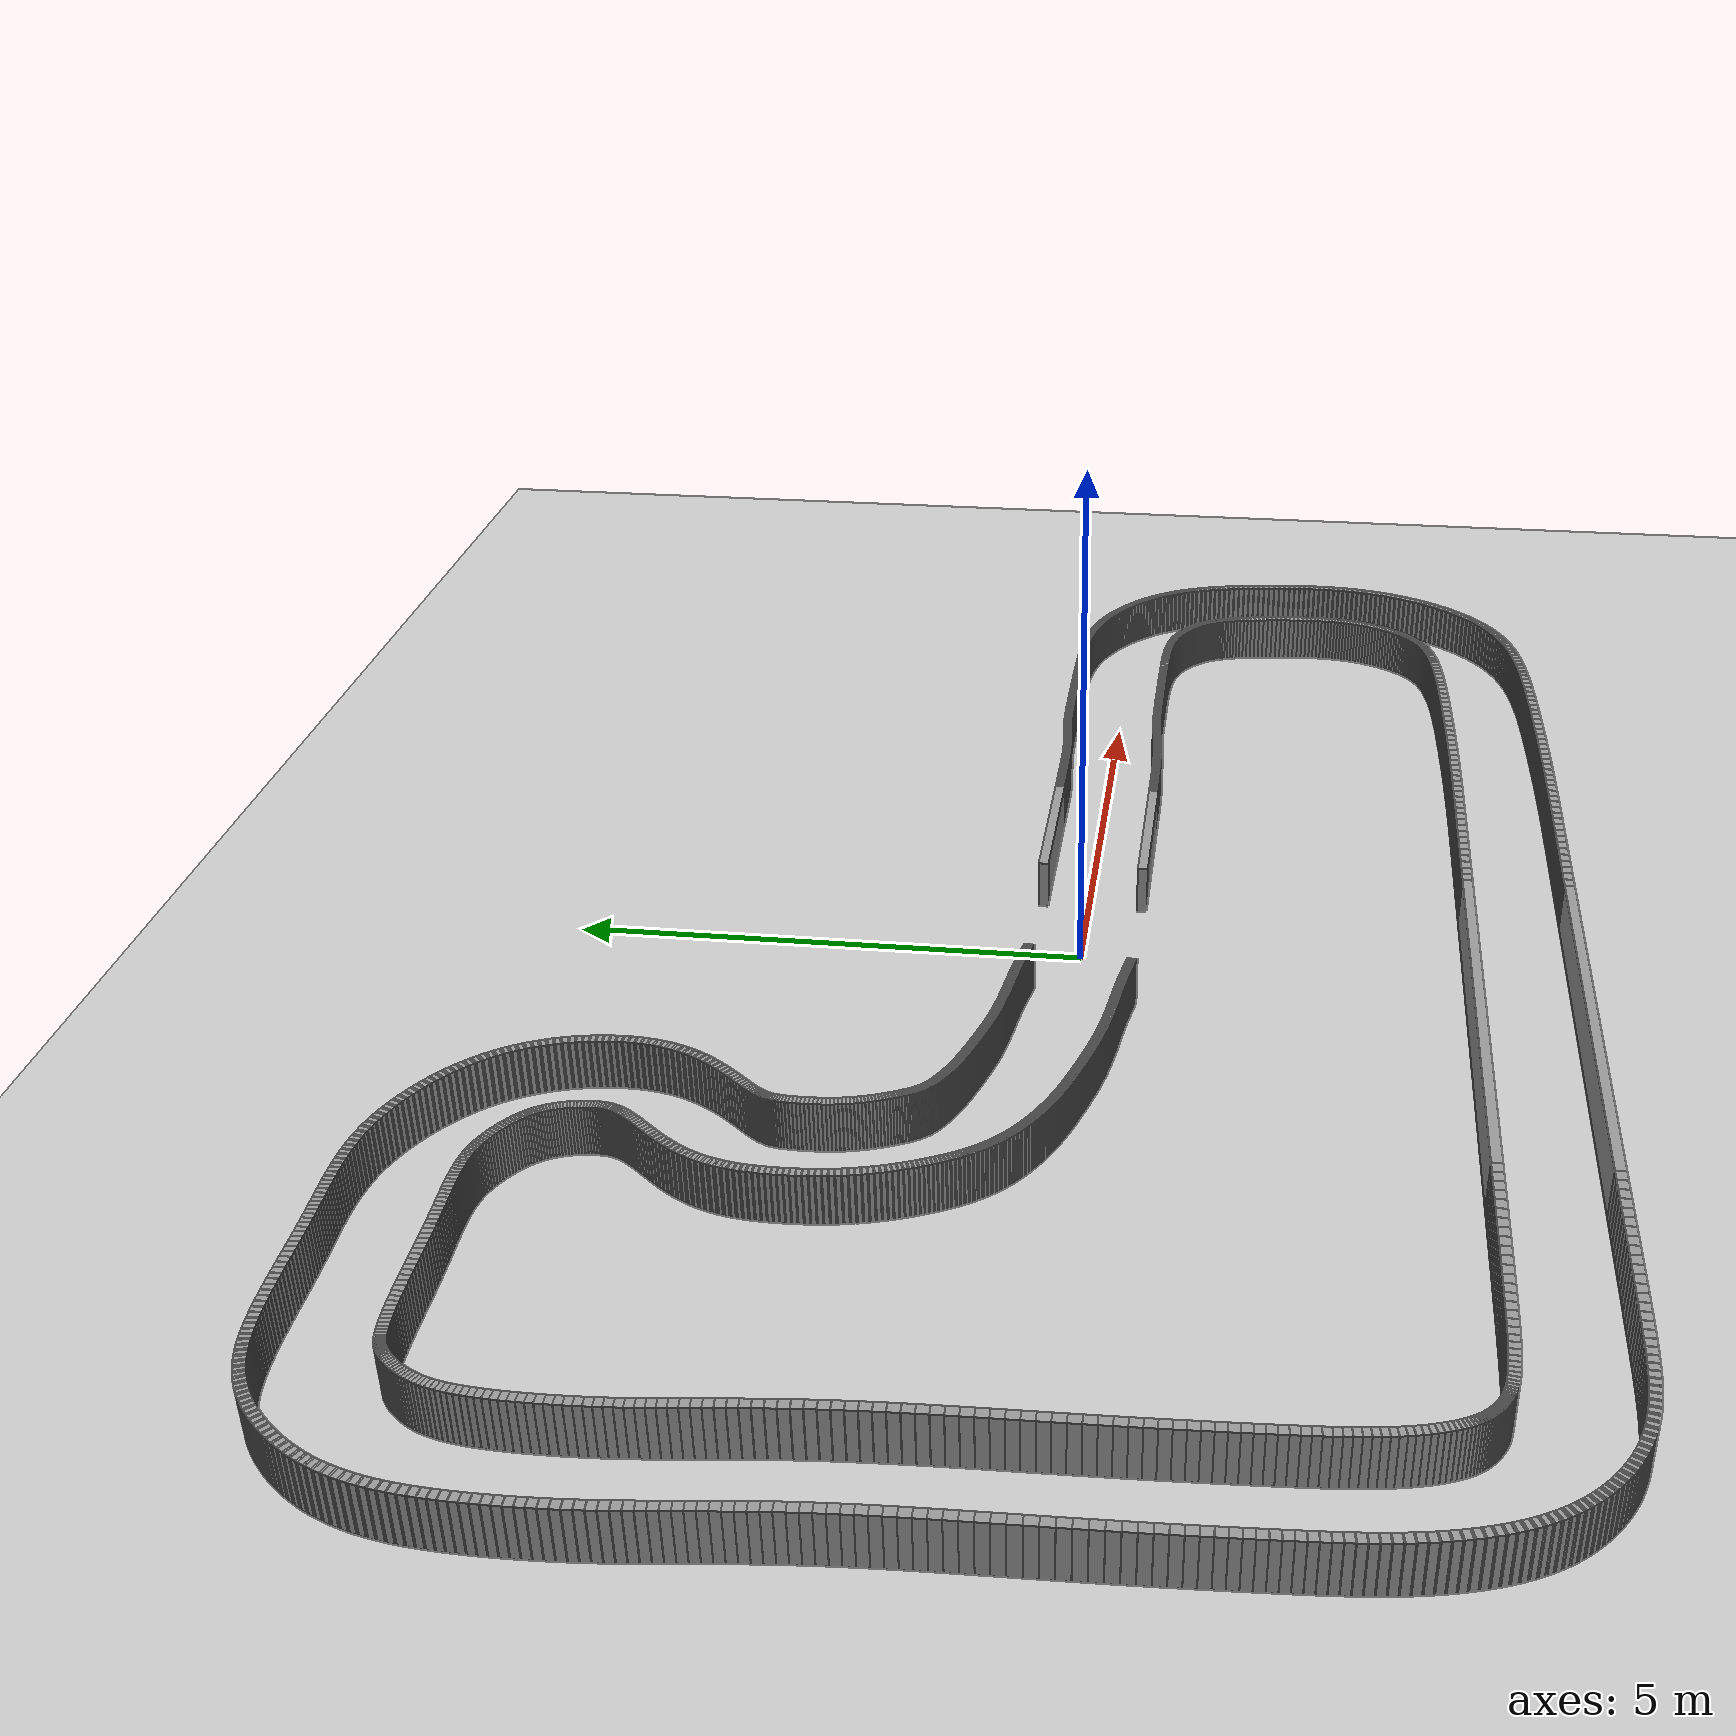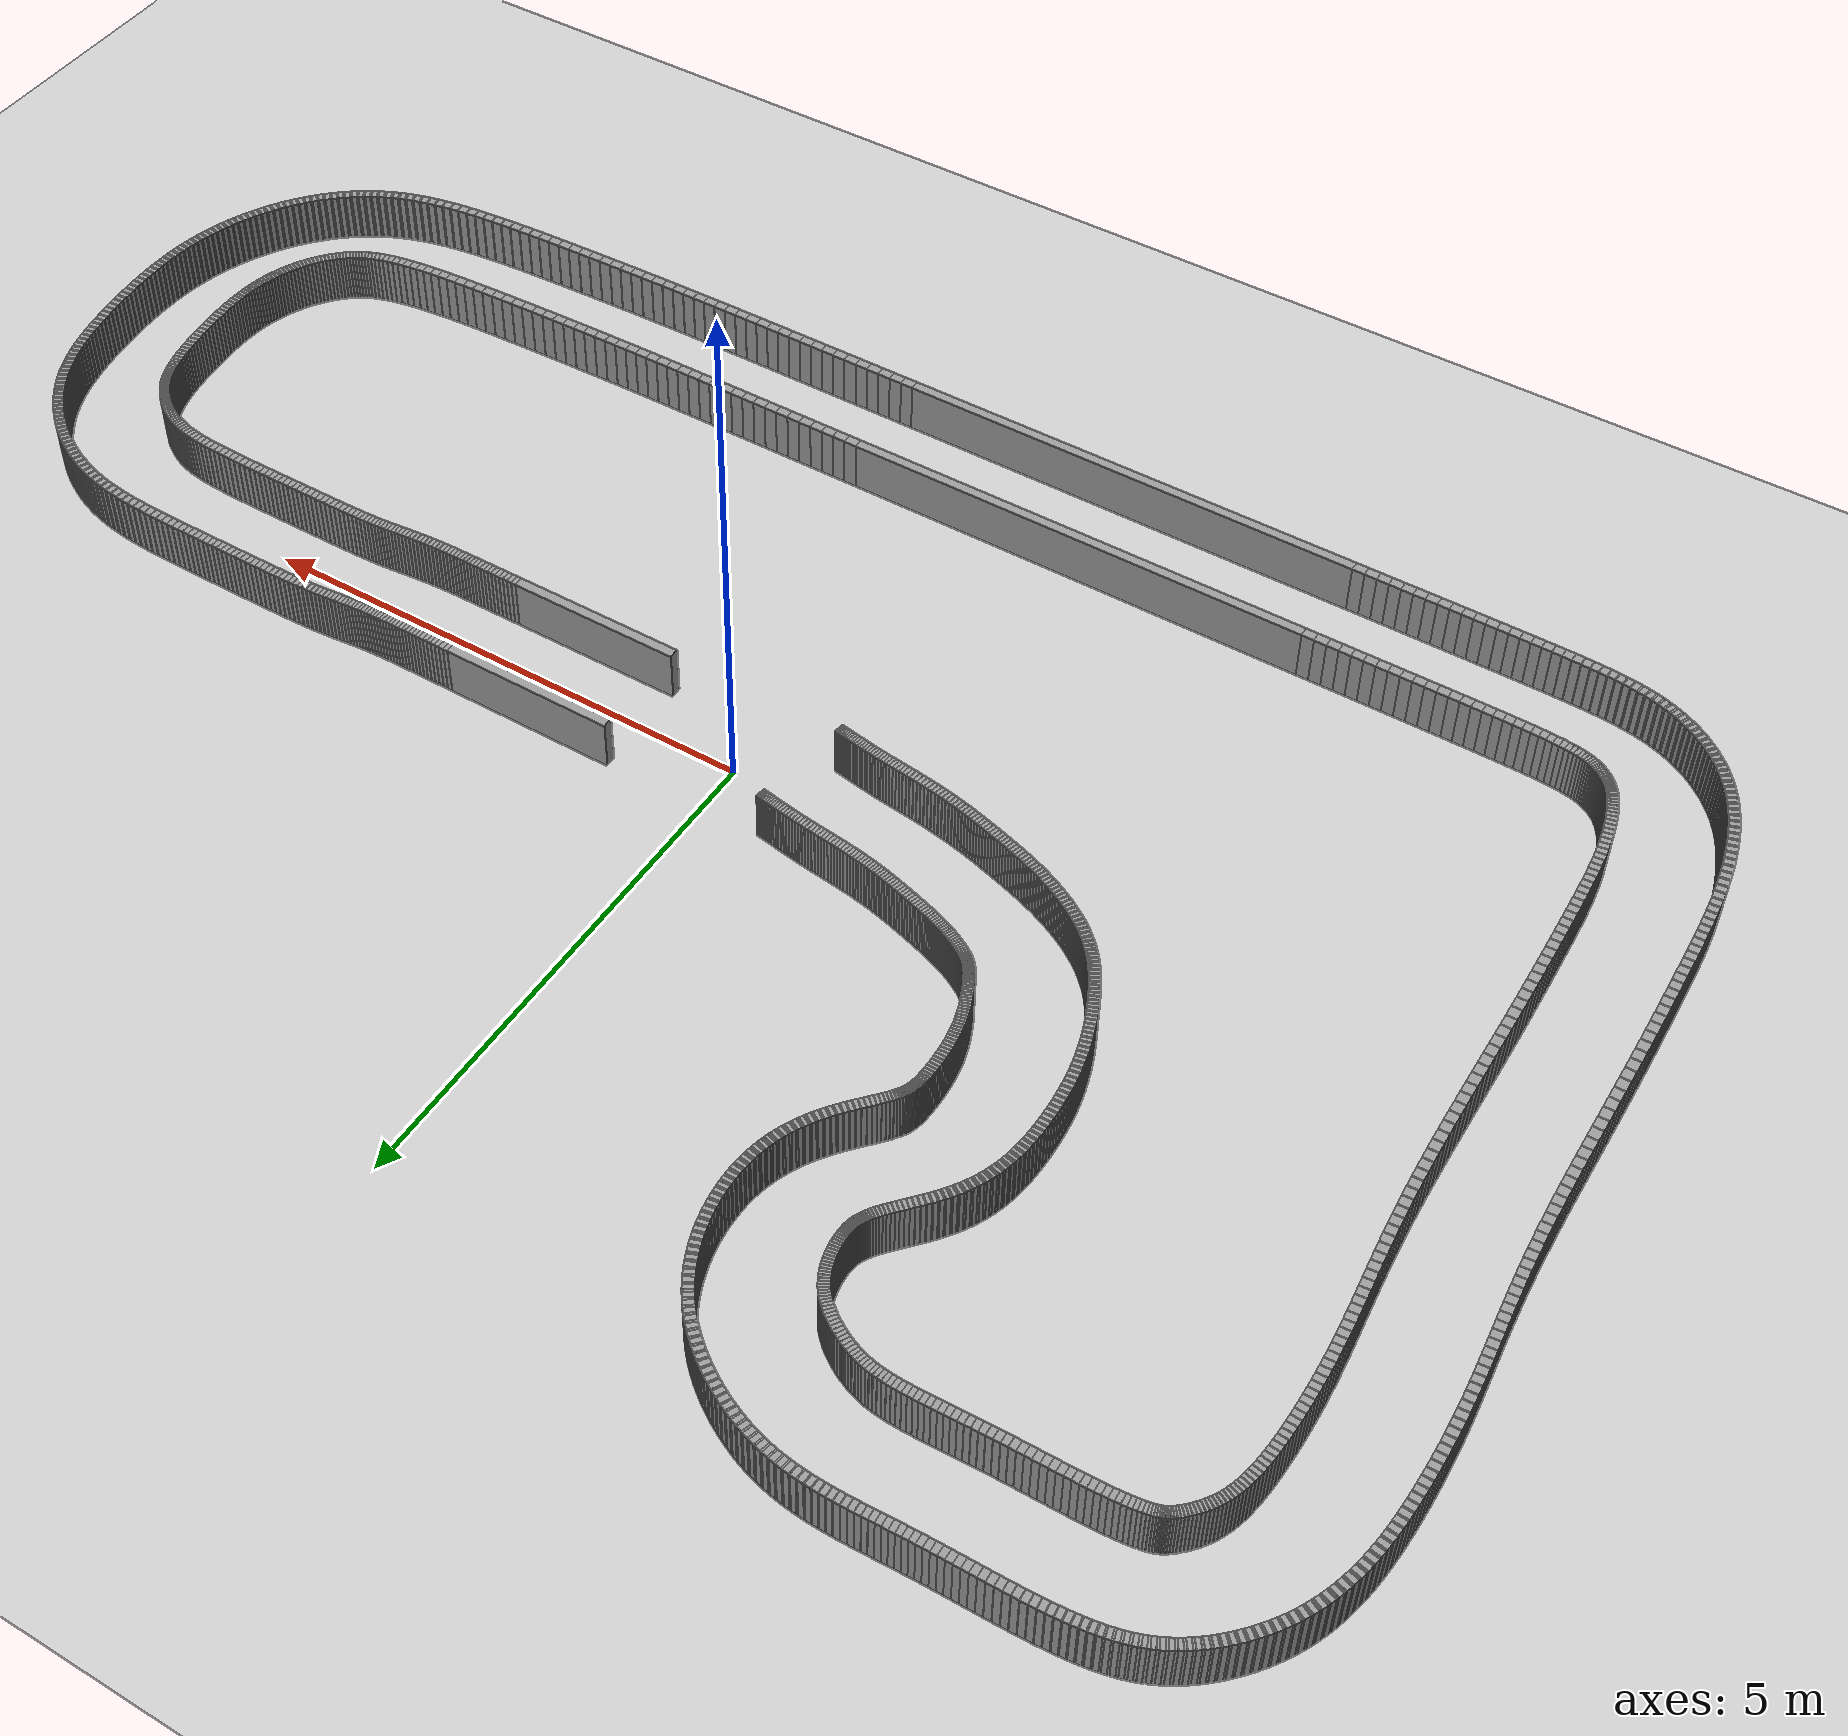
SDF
<?xml version="1.0"?>
        <sdf version="1.6">
        <world name="default">
            <include>
            <uri>model://ground_plane</uri>
            </include>
            <include>
            <uri>model://sun</uri>
            </include>

        <model name="wall_0_outward">
          <static>true</static>
          <link name="link">
            <collision name="collision">
              <geometry>
                <box>
                  <size>1.6948364721734805 0.1 0.5</size>
                </box>
              </geometry>
            </collision>
            <visual name="visual">
              <geometry>
                <box>
                  <size>1.6948364721734805 0.1 0.5</size>
                </box>
              </geometry>
              <material>
                <script>
                  <uri>file://media/materials/scripts/gazebo.material</uri>
                  <name>Gazebo/Gray</name>
                </script>
              </material>
            </visual>
          </link>
          <pose>1.8243392985711648 0.475 0.25 0 0 0.0</pose>
        </model>

        <model name="wall_1_outward">
          <static>true</static>
          <link name="link">
            <collision name="collision">
              <geometry>
                <box>
                  <size>0.04806440217080961 0.1 0.5</size>
                </box>
              </geometry>
            </collision>
            <visual name="visual">
              <geometry>
                <box>
                  <size>0.04806440217080961 0.1 0.5</size>
                </box>
              </geometry>
              <material>
                <script>
                  <uri>file://media/materials/scripts/gazebo.material</uri>
                  <name>Gazebo/Gray</name>
                </script>
              </material>
            </visual>
          </link>
          <pose>2.695789735742122 0.47500023897134025 0.25 0 0 9.943797465686413e-06</pose>
        </model>

        <model name="wall_2_outward">
          <static>true</static>
          <link name="link">
            <collision name="collision">
              <geometry>
                <box>
                  <size>0.04688702898116273 0.1 0.5</size>
                </box>
              </geometry>
            </collision>
            <visual name="visual">
              <geometry>
                <box>
                  <size>0.04688702898116273 0.1 0.5</size>
                </box>
              </geometry>
              <material>
                <script>
                  <uri>file://media/materials/scripts/gazebo.material</uri>
                  <name>Gazebo/Gray</name>
                </script>
              </material>
            </visual>
          </link>
          <pose>2.743265451313178 0.4750008968067251 0.25 0 0 1.78669475849483e-05</pose>
        </model>

        <model name="wall_3_outward">
          <static>true</static>
          <link name="link">
            <collision name="collision">
              <geometry>
                <box>
                  <size>0.04574440428487137 0.1 0.5</size>
                </box>
              </geometry>
            </collision>
            <visual name="visual">
              <geometry>
                <box>
                  <size>0.04574440428487137 0.1 0.5</size>
                </box>
              </geometry>
              <material>
                <script>
                  <uri>file://media/materials/scripts/gazebo.material</uri>
                  <name>Gazebo/Gray</name>
                </script>
              </material>
            </visual>
          </link>
          <pose>2.7895811679311424 0.4750020349709023 0.25 0 0 3.1448661056683624e-05</pose>
        </model>

        <model name="wall_4_outward">
          <static>true</static>
          <link name="link">
            <collision name="collision">
              <geometry>
                <box>
                  <size>0.04463535169733621 0.1 0.5</size>
                </box>
              </geometry>
            </collision>
            <visual name="visual">
              <geometry>
                <box>
                  <size>0.04463535169733621 0.1 0.5</size>
                </box>
              </geometry>
              <material>
                <script>
                  <uri>file://media/materials/scripts/gazebo.material</uri>
                  <name>Gazebo/Gray</name>
                </script>
              </material>
            </visual>
          </link>
          <pose>2.834771045878127 0.4750039644063491 0.25 0 0 5.4223178207318726e-05</pose>
        </model>

        <model name="wall_5_outward">
          <static>true</static>
          <link name="link">
            <collision name="collision">
              <geometry>
                <box>
                  <size>0.04356462694553616 0.1 0.5</size>
                </box>
              </geometry>
            </collision>
            <visual name="visual">
              <geometry>
                <box>
                  <size>0.04356462694553616 0.1 0.5</size>
                </box>
              </geometry>
              <material>
                <script>
                  <uri>file://media/materials/scripts/gazebo.material</uri>
                  <name>Gazebo/Gray</name>
                </script>
              </material>
            </visual>
          </link>
          <pose>2.8788710350522493 0.4750074080070009 0.25 0 0 0.00010253572671945705</pose>
        </model>

        <model name="wall_6_outward">
          <static>true</static>
          <link name="link">
            <collision name="collision">
              <geometry>
                <box>
                  <size>0.04253340131051369 0.1 0.5</size>
                </box>
              </geometry>
            </collision>
            <visual name="visual">
              <geometry>
                <box>
                  <size>0.04253340131051369 0.1 0.5</size>
                </box>
              </geometry>
              <material>
                <script>
                  <uri>file://media/materials/scripts/gazebo.material</uri>
                  <name>Gazebo/Gray</name>
                </script>
              </material>
            </visual>
          </link>
          <pose>2.9219200487543553 0.47501328091075756 0.25 0 0 0.00017113319530774783</pose>
        </model>

        <model name="wall_7_outward">
          <static>true</static>
          <link name="link">
            <collision name="collision">
              <geometry>
                <box>
                  <size>0.04153998504033929 0.1 0.5</size>
                </box>
              </geometry>
            </collision>
            <visual name="visual">
              <geometry>
                <box>
                  <size>0.04153998504033929 0.1 0.5</size>
                </box>
              </geometry>
              <material>
                <script>
                  <uri>file://media/materials/scripts/gazebo.material</uri>
                  <name>Gazebo/Gray</name>
                </script>
              </material>
            </visual>
          </link>
          <pose>2.963956740804873 0.47502273348463075 0.25 0 0 0.00027988144552377407</pose>
        </model>

        <model name="wall_8_outward">
          <static>true</static>
          <link name="link">
            <collision name="collision">
              <geometry>
                <box>
                  <size>0.04058826902087327 0.1 0.5</size>
                </box>
              </geometry>
            </collision>
            <visual name="visual">
              <geometry>
                <box>
                  <size>0.04058826902087327 0.1 0.5</size>
                </box>
              </geometry>
              <material>
                <script>
                  <uri>file://media/materials/scripts/gazebo.material</uri>
                  <name>Gazebo/Gray</name>
                </script>
              </material>
            </visual>
          </link>
          <pose>3.0050208649814865 0.4750376471853254 0.25 0 0 0.0004484332919322523</pose>
        </model>

        <model name="wall_9_outward">
          <static>true</static>
          <link name="link">
            <collision name="collision">
              <geometry>
                <box>
                  <size>0.03968564509313034 0.1 0.5</size>
                </box>
              </geometry>
            </collision>
            <visual name="visual">
              <geometry>
                <box>
                  <size>0.03968564509313034 0.1 0.5</size>
                </box>
              </geometry>
              <material>
                <script>
                  <uri>file://media/materials/scripts/gazebo.material</uri>
                  <name>Gazebo/Gray</name>
                </script>
              </material>
            </visual>
          </link>
          <pose>3.0451578149155183 0.475060949903339 0.25 0 0 0.0007157325502692343</pose>
        </model>

        <model name="wall_10_outward">
          <static>true</static>
          <link name="link">
            <collision name="collision">
              <geometry>
                <box>
                  <size>0.038840450173505875 0.1 0.5</size>
                </box>
              </geometry>
            </collision>
            <visual name="visual">
              <geometry>
                <box>
                  <size>0.038840450173505875 0.1 0.5</size>
                </box>
              </geometry>
              <material>
                <script>
                  <uri>file://media/materials/scripts/gazebo.material</uri>
                  <name>Gazebo/Gray</name>
                </script>
              </material>
            </visual>
          </link>
          <pose>3.0844208456576423 0.475096568310334 0.25 0 0 0.0011027811710174141</pose>
        </model>

        <model name="wall_11_outward">
          <static>true</static>
          <link name="link">
            <collision name="collision">
              <geometry>
                <box>
                  <size>0.038055004006341736 0.1 0.5</size>
                </box>
              </geometry>
            </collision>
            <visual name="visual">
              <geometry>
                <box>
                  <size>0.038055004006341736 0.1 0.5</size>
                </box>
              </geometry>
              <material>
                <script>
                  <uri>file://media/materials/scripts/gazebo.material</uri>
                  <name>Gazebo/Gray</name>
                </script>
              </material>
            </visual>
          </link>
          <pose>3.122868534603403 0.4751496420224396 0.25 0 0 0.0016637744925169177</pose>
        </model>

        <model name="wall_12_outward">
          <static>true</static>
          <link name="link">
            <collision name="collision">
              <geometry>
                <box>
                  <size>0.037338345144804795 0.1 0.5</size>
                </box>
              </geometry>
            </collision>
            <visual name="visual">
              <geometry>
                <box>
                  <size>0.037338345144804795 0.1 0.5</size>
                </box>
              </geometry>
              <material>
                <script>
                  <uri>file://media/materials/scripts/gazebo.material</uri>
                  <name>Gazebo/Gray</name>
                </script>
              </material>
            </visual>
          </link>
          <pose>3.1605651264879793 0.47522717125795005 0.25 0 0 0.0024570892794366014</pose>
        </model>

        <model name="wall_13_outward">
          <static>true</static>
          <link name="link">
            <collision name="collision">
              <geometry>
                <box>
                  <size>0.03669572196433584 0.1 0.5</size>
                </box>
              </geometry>
            </collision>
            <visual name="visual">
              <geometry>
                <box>
                  <size>0.03669572196433584 0.1 0.5</size>
                </box>
              </geometry>
              <material>
                <script>
                  <uri>file://media/materials/scripts/gazebo.material</uri>
                  <name>Gazebo/Gray</name>
                </script>
              </material>
            </visual>
          </link>
          <pose>3.197581988004242 0.47533819707425495 0.25 0 0 0.003551050210883896</pose>
        </model>

        <model name="wall_14_outward">
          <static>true</static>
          <link name="link">
            <collision name="collision">
              <geometry>
                <box>
                  <size>0.03612931523930584 0.1 0.5</size>
                </box>
              </geometry>
            </collision>
            <visual name="visual">
              <geometry>
                <box>
                  <size>0.03612931523930584 0.1 0.5</size>
                </box>
              </geometry>
              <material>
                <script>
                  <uri>file://media/materials/scripts/gazebo.material</uri>
                  <name>Gazebo/Gray</name>
                </script>
              </material>
            </visual>
          </link>
          <pose>3.2339941631506752 0.4754940661472298 0.25 0 0 0.00502170688623392</pose>
        </model>

        <model name="wall_15_outward">
          <static>true</static>
          <link name="link">
            <collision name="collision">
              <geometry>
                <box>
                  <size>0.035642311914681014 0.1 0.5</size>
                </box>
              </geometry>
            </collision>
            <visual name="visual">
              <geometry>
                <box>
                  <size>0.035642311914681014 0.1 0.5</size>
                </box>
              </geometry>
              <material>
                <script>
                  <uri>file://media/materials/scripts/gazebo.material</uri>
                  <name>Gazebo/Gray</name>
                </script>
              </material>
            </visual>
          </link>
          <pose>3.2698793187602915 0.47570860747160393 0.25 0 0 0.006948330779103806</pose>
        </model>

        <model name="wall_16_outward">
          <static>true</static>
          <link name="link">
            <collision name="collision">
              <geometry>
                <box>
                  <size>0.03523270988299887 0.1 0.5</size>
                </box>
              </geometry>
            </collision>
            <visual name="visual">
              <geometry>
                <box>
                  <size>0.03523270988299887 0.1 0.5</size>
                </box>
              </geometry>
              <material>
                <script>
                  <uri>file://media/materials/scripts/gazebo.material</uri>
                  <name>Gazebo/Gray</name>
                </script>
              </material>
            </visual>
          </link>
          <pose>3.3053156197371765 0.4759981784289007 0.25 0 0 0.009408706465386003</pose>
        </model>

        <model name="wall_17_outward">
          <static>true</static>
          <link name="link">
            <collision name="collision">
              <geometry>
                <box>
                  <size>0.03489780617447412 0.1 0.5</size>
                </box>
              </geometry>
            </collision>
            <visual name="visual">
              <geometry>
                <box>
                  <size>0.03489780617447412 0.1 0.5</size>
                </box>
              </geometry>
              <material>
                <script>
                  <uri>file://media/materials/scripts/gazebo.material</uri>
                  <name>Gazebo/Gray</name>
                </script>
              </material>
            </visual>
          </link>
          <pose>3.3403787408739563 0.4763815471532887 0.25 0 0 0.012472400040113872</pose>
        </model>

        <model name="wall_18_outward">
          <static>true</static>
          <link name="link">
            <collision name="collision">
              <geometry>
                <box>
                  <size>0.03463362284369708 0.1 0.5</size>
                </box>
              </geometry>
            </collision>
            <visual name="visual">
              <geometry>
                <box>
                  <size>0.03463362284369708 0.1 0.5</size>
                </box>
              </geometry>
              <material>
                <script>
                  <uri>file://media/materials/scripts/gazebo.material</uri>
                  <name>Gazebo/Gray</name>
                </script>
              </material>
            </visual>
          </link>
          <pose>3.375140827617702 0.476879588701131 0.25 0 0 0.016194075266413022</pose>
        </model>

        <model name="wall_19_outward">
          <static>true</static>
          <link name="link">
            <collision name="collision">
              <geometry>
                <box>
                  <size>0.03443286003245522 0.1 0.5</size>
                </box>
              </geometry>
            </collision>
            <visual name="visual">
              <geometry>
                <box>
                  <size>0.03443286003245522 0.1 0.5</size>
                </box>
              </geometry>
              <material>
                <script>
                  <uri>file://media/materials/scripts/gazebo.material</uri>
                  <name>Gazebo/Gray</name>
                </script>
              </material>
            </visual>
          </link>
          <pose>3.4096681426535262 0.47751478265917147 0.25 0 0 0.020608313145628606</pose>
        </model>

        <model name="wall_20_outward">
          <static>true</static>
          <link name="link">
            <collision name="collision">
              <geometry>
                <box>
                  <size>0.034286452296005715 0.1 0.5</size>
                </box>
              </geometry>
            </collision>
            <visual name="visual">
              <geometry>
                <box>
                  <size>0.034286452296005715 0.1 0.5</size>
                </box>
              </geometry>
              <material>
                <script>
                  <uri>file://media/materials/scripts/gazebo.material</uri>
                  <name>Gazebo/Gray</name>
                </script>
              </material>
            </visual>
          </link>
          <pose>3.4440184708331056 0.47831052041515587 0.25 0 0 0.02572502543572336</pose>
        </model>

        <model name="wall_21_outward">
          <static>true</static>
          <link name="link">
            <collision name="collision">
              <geometry>
                <box>
                  <size>0.034186327868454415 0.1 0.5</size>
                </box>
              </geometry>
            </collision>
            <visual name="visual">
              <geometry>
                <box>
                  <size>0.034186327868454415 0.1 0.5</size>
                </box>
              </geometry>
              <material>
                <script>
                  <uri>file://media/materials/scripts/gazebo.material</uri>
                  <name>Gazebo/Gray</name>
                </script>
              </material>
            </visual>
          </link>
          <pose>3.4782406956897374 0.4792902523481356 0.25 0 0 0.03152487724142422</pose>
        </model>

        <model name="wall_22_outward">
          <static>true</static>
          <link name="link">
            <collision name="collision">
              <geometry>
                <box>
                  <size>0.03412545916503974 0.1 0.5</size>
                </box>
              </geometry>
            </collision>
            <visual name="visual">
              <geometry>
                <box>
                  <size>0.03412545916503974 0.1 0.5</size>
                </box>
              </geometry>
              <material>
                <script>
                  <uri>file://media/materials/scripts/gazebo.material</uri>
                  <name>Gazebo/Gray</name>
                </script>
              </material>
            </visual>
          </link>
          <pose>3.512375806759146 0.48047650314665147 0.25 0 0 0.03795615728900034</pose>
        </model>

        <model name="wall_23_outward">
          <static>true</static>
          <link name="link">
            <collision name="collision">
              <geometry>
                <box>
                  <size>0.0340971538375391 0.1 0.5</size>
                </box>
              </geometry>
            </collision>
            <visual name="visual">
              <geometry>
                <box>
                  <size>0.0340971538375391 0.1 0.5</size>
                </box>
              </geometry>
              <material>
                <script>
                  <uri>file://media/materials/scripts/gazebo.material</uri>
                  <name>Gazebo/Gray</name>
                </script>
              </material>
            </visual>
          </link>
          <pose>3.5464576144063216 0.48188981427284044 0.25 0 0 0.04493564275734864</pose>
        </model>

        <model name="wall_24_outward">
          <static>true</static>
          <link name="link">
            <collision name="collision">
              <geometry>
                <box>
                  <size>0.034100720145534585 0.1 0.5</size>
                </box>
              </geometry>
            </collision>
            <visual name="visual">
              <geometry>
                <box>
                  <size>0.034100720145534585 0.1 0.5</size>
                </box>
              </geometry>
              <material>
                <script>
                  <uri>file://media/materials/scripts/gazebo.material</uri>
                  <name>Gazebo/Gray</name>
                </script>
              </material>
            </visual>
          </link>
          <pose>3.5805159895737333 0.4835477144476865 0.25 0 0 0.05234356841099349</pose>
        </model>

        <model name="wall_25_outward">
          <static>true</static>
          <link name="link">
            <collision name="collision">
              <geometry>
                <box>
                  <size>0.034139872349267325 0.1 0.5</size>
                </box>
              </geometry>
            </collision>
            <visual name="visual">
              <geometry>
                <box>
                  <size>0.034139872349267325 0.1 0.5</size>
                </box>
              </geometry>
              <material>
                <script>
                  <uri>file://media/materials/scripts/gazebo.material</uri>
                  <name>Gazebo/Gray</name>
                </script>
              </material>
            </visual>
          </link>
          <pose>3.6145821914243643 0.48546378737885076 0.25 0 0 0.06002476435542967</pose>
        </model>

        <model name="wall_26_outward">
          <static>true</static>
          <link name="link">
            <collision name="collision">
              <geometry>
                <box>
                  <size>0.03422515983468342 0.1 0.5</size>
                </box>
              </geometry>
            </collision>
            <visual name="visual">
              <geometry>
                <box>
                  <size>0.03422515983468342 0.1 0.5</size>
                </box>
              </geometry>
              <material>
                <script>
                  <uri>file://media/materials/scripts/gazebo.material</uri>
                  <name>Gazebo/Gray</name>
                </script>
              </material>
            </visual>
          </link>
          <pose>3.648694664445913 0.48764690287528817 0.25 0 0 0.06778638493182666</pose>
        </model>

        <model name="wall_27_outward">
          <static>true</static>
          <link name="link">
            <collision name="collision">
              <geometry>
                <box>
                  <size>0.03437356803132213 0.1 0.5</size>
                </box>
              </geometry>
            </collision>
            <visual name="visual">
              <geometry>
                <box>
                  <size>0.03437356803132213 0.1 0.5</size>
                </box>
              </geometry>
              <material>
                <script>
                  <uri>file://media/materials/scripts/gazebo.material</uri>
                  <name>Gazebo/Gray</name>
                </script>
              </material>
            </visual>
          </link>
          <pose>3.6829058958852112 0.4901006676845532 0.25 0 0 0.07539982854421307</pose>
        </model>

        <model name="wall_28_outward">
          <static>true</static>
          <link name="link">
            <collision name="collision">
              <geometry>
                <box>
                  <size>0.03460850290986994 0.1 0.5</size>
                </box>
              </geometry>
            </collision>
            <visual name="visual">
              <geometry>
                <box>
                  <size>0.03460850290986994 0.1 0.5</size>
                </box>
              </geometry>
              <material>
                <script>
                  <uri>file://media/materials/scripts/gazebo.material</uri>
                  <name>Gazebo/Gray</name>
                </script>
              </material>
            </visual>
          </link>
          <pose>3.7172891024407337 0.49282302286654733 0.25 0 0 0.08259975337286665</pose>
        </model>

        <model name="wall_29_outward">
          <static>true</static>
          <link name="link">
            <collision name="collision">
              <geometry>
                <box>
                  <size>0.03495509443923935 0.1 0.5</size>
                </box>
              </geometry>
            </collision>
            <visual name="visual">
              <geometry>
                <box>
                  <size>0.03495509443923935 0.1 0.5</size>
                </box>
              </geometry>
              <material>
                <script>
                  <uri>file://media/materials/scripts/gazebo.material</uri>
                  <name>Gazebo/Gray</name>
                </script>
              </material>
            </visual>
          </link>
          <pose>3.7519425812148284 0.49580583481442153 0.25 0 0 0.08909540351266997</pose>
        </model>

        <model name="wall_30_outward">
          <static>true</static>
          <link name="link">
            <collision name="collision">
              <geometry>
                <box>
                  <size>0.03543955042557566 0.1 0.5</size>
                </box>
              </geometry>
            </collision>
            <visual name="visual">
              <geometry>
                <box>
                  <size>0.03543955042557566 0.1 0.5</size>
                </box>
              </geometry>
              <material>
                <script>
                  <uri>file://media/materials/scripts/gazebo.material</uri>
                  <name>Gazebo/Gray</name>
                </script>
              </material>
            </visual>
          </link>
          <pose>3.7869913896969716 0.4990343365524339 0.25 0 0 0.09457734254188264</pose>
        </model>

        <model name="wall_31_outward">
          <static>true</static>
          <link name="link">
            <collision name="collision">
              <geometry>
                <box>
                  <size>0.03608200188614192 0.1 0.5</size>
                </box>
              </geometry>
            </collision>
            <visual name="visual">
              <geometry>
                <box>
                  <size>0.03608200188614192 0.1 0.5</size>
                </box>
              </geometry>
              <material>
                <script>
                  <uri>file://media/materials/scripts/gazebo.material</uri>
                  <name>Gazebo/Gray</name>
                </script>
              </material>
            </visual>
          </link>
          <pose>3.82258510230046 0.502486176503101 0.25 0 0 0.09873848366980394</pose>
        </model>

        <model name="wall_32_outward">
          <static>true</static>
          <link name="link">
            <collision name="collision">
              <geometry>
                <box>
                  <size>0.036891321217791206 0.1 0.5</size>
                </box>
              </geometry>
            </collision>
            <visual name="visual">
              <geometry>
                <box>
                  <size>0.036891321217791206 0.1 0.5</size>
                </box>
              </geometry>
              <material>
                <script>
                  <uri>file://media/materials/scripts/gazebo.material</uri>
                  <name>Gazebo/Gray</name>
                </script>
              </material>
            </visual>
          </link>
          <pose>3.85888933190925 0.5061299658995165 0.25 0 0 0.10129945816380015</pose>
        </model>

        <model name="wall_33_outward">
          <static>true</static>
          <link name="link">
            <collision name="collision">
              <geometry>
                <box>
                  <size>0.037561971896658074 0.1 0.5</size>
                </box>
              </geometry>
            </collision>
            <visual name="visual">
              <geometry>
                <box>
                  <size>0.037561971896658074 0.1 0.5</size>
                </box>
              </geometry>
              <material>
                <script>
                  <uri>file://media/materials/scripts/gazebo.material</uri>
                  <name>Gazebo/Gray</name>
                </script>
              </material>
            </visual>
          </link>
          <pose>3.895923719561498 0.5099084778895424 0.25 0 0 0.10204442861603125</pose>
        </model>

        <model name="wall_34_outward">
          <static>true</static>
          <link name="link">
            <collision name="collision">
              <geometry>
                <box>
                  <size>0.0006005570851022729 0.1 0.5</size>
                </box>
              </geometry>
            </collision>
            <visual name="visual">
              <geometry>
                <box>
                  <size>0.0006005570851022729 0.1 0.5</size>
                </box>
              </geometry>
              <material>
                <script>
                  <uri>file://media/materials/scripts/gazebo.material</uri>
                  <name>Gazebo/Gray</name>
                </script>
              </material>
            </visual>
          </link>
          <pose>3.9149057413202515 0.5118520577019349 0.25 0 0 0.10144387149461366</pose>
        </model>

        <model name="wall_35_outward">
          <static>true</static>
          <link name="link">
            <collision name="collision">
              <geometry>
                <box>
                  <size>0.037887833833630515 0.1 0.5</size>
                </box>
              </geometry>
            </collision>
            <visual name="visual">
              <geometry>
                <box>
                  <size>0.037887833833630515 0.1 0.5</size>
                </box>
              </geometry>
              <material>
                <script>
                  <uri>file://media/materials/scripts/gazebo.material</uri>
                  <name>Gazebo/Gray</name>
                </script>
              </material>
            </visual>
          </link>
          <pose>3.9340521507553032 0.5137895980426772 0.25 0 0 0.10084331437362348</pose>
        </model>

        <model name="wall_36_outward">
          <static>true</static>
          <link name="link">
            <collision name="collision">
              <geometry>
                <box>
                  <size>0.001574672944620505 0.1 0.5</size>
                </box>
              </geometry>
            </collision>
            <visual name="visual">
              <geometry>
                <box>
                  <size>0.001574672944620505 0.1 0.5</size>
                </box>
              </geometry>
              <material>
                <script>
                  <uri>file://media/materials/scripts/gazebo.material</uri>
                  <name>Gazebo/Gray</name>
                </script>
              </material>
            </visual>
          </link>
          <pose>3.9536832857318966 0.5157747587044049 0.25 0 0 0.09926864077830745</pose>
        </model>

        <model name="wall_37_outward">
          <static>true</static>
          <link name="link">
            <collision name="collision">
              <geometry>
                <box>
                  <size>0.038164973088641155 0.1 0.5</size>
                </box>
              </geometry>
            </collision>
            <visual name="visual">
              <geometry>
                <box>
                  <size>0.038164973088641155 0.1 0.5</size>
                </box>
              </geometry>
              <material>
                <script>
                  <uri>file://media/materials/scripts/gazebo.material</uri>
                  <name>Gazebo/Gray</name>
                </script>
              </material>
            </visual>
          </link>
          <pose>3.9734582423387694 0.5177140680284287 0.25 0 0 0.09769396718286316</pose>
        </model>

        <model name="wall_38_outward">
          <static>true</static>
          <link name="link">
            <collision name="collision">
              <geometry>
                <box>
                  <size>0.0024850264246705847 0.1 0.5</size>
                </box>
              </geometry>
            </collision>
            <visual name="visual">
              <geometry>
                <box>
                  <size>0.0024850264246705847 0.1 0.5</size>
                </box>
              </geometry>
              <material>
                <script>
                  <uri>file://media/materials/scripts/gazebo.material</uri>
                  <name>Gazebo/Gray</name>
                </script>
              </material>
            </visual>
          </link>
          <pose>3.9936866245333675 0.5196934675530118 0.25 0 0 0.09520893820050075</pose>
        </model>

        <model name="wall_39_outward">
          <static>true</static>
          <link name="link">
            <collision name="collision">
              <geometry>
                <box>
                  <size>0.038604670412857596 0.1 0.5</size>
                </box>
              </geometry>
            </collision>
            <visual name="visual">
              <geometry>
                <box>
                  <size>0.038604670412857596 0.1 0.5</size>
                </box>
              </geometry>
              <material>
                <script>
                  <uri>file://media/materials/scripts/gazebo.material</uri>
                  <name>Gazebo/Gray</name>
                </script>
              </material>
            </visual>
          </link>
          <pose>4.014142927039951 0.5215988116696546 0.25 0 0 0.09272390921820284</pose>
        </model>

        <model name="wall_40_outward">
          <static>true</static>
          <link name="link">
            <collision name="collision">
              <geometry>
                <box>
                  <size>0.0032658077204588136 0.1 0.5</size>
                </box>
              </geometry>
            </collision>
            <visual name="visual">
              <geometry>
                <box>
                  <size>0.0032658077204588136 0.1 0.5</size>
                </box>
              </geometry>
              <material>
                <script>
                  <uri>file://media/materials/scripts/gazebo.material</uri>
                  <name>Gazebo/Gray</name>
                </script>
              </material>
            </visual>
          </link>
          <pose>4.034988717967316 0.5235319177778179 0.25 0 0 0.08945809569245979</pose>
        </model>

        <model name="wall_41_outward">
          <static>true</static>
          <link name="link">
            <collision name="collision">
              <geometry>
                <box>
                  <size>0.0392243842283836 0.1 0.5</size>
                </box>
              </geometry>
            </collision>
            <visual name="visual">
              <geometry>
                <box>
                  <size>0.0392243842283836 0.1 0.5</size>
                </box>
              </geometry>
              <material>
                <script>
                  <uri>file://media/materials/scripts/gazebo.material</uri>
                  <name>Gazebo/Gray</name>
                </script>
              </material>
            </visual>
          </link>
          <pose>4.056154478965215 0.5253661268118535 0.25 0 0 0.08619228216673648</pose>
        </model>

        <model name="wall_42_outward">
          <static>true</static>
          <link name="link">
            <collision name="collision">
              <geometry>
                <box>
                  <size>0.003864570013660513 0.1 0.5</size>
                </box>
              </geometry>
            </collision>
            <visual name="visual">
              <geometry>
                <box>
                  <size>0.003864570013660513 0.1 0.5</size>
                </box>
              </geometry>
              <material>
                <script>
                  <uri>file://media/materials/scripts/gazebo.material</uri>
                  <name>Gazebo/Gray</name>
                </script>
              </material>
            </visual>
          </link>
          <pose>4.077619605943147 0.5272133550758269 0.25 0 0 0.08232770253353343</pose>
        </model>

        <model name="wall_43_outward">
          <static>true</static>
          <link name="link">
            <collision name="collision">
              <geometry>
                <box>
                  <size>0.040033057722133523 0.1 0.5</size>
                </box>
              </geometry>
            </collision>
            <visual name="visual">
              <geometry>
                <box>
                  <size>0.040033057722133523 0.1 0.5</size>
                </box>
              </geometry>
              <material>
                <script>
                  <uri>file://media/materials/scripts/gazebo.material</uri>
                  <name>Gazebo/Gray</name>
                </script>
              </material>
            </visual>
          </link>
          <pose>4.099500291247745 0.5289412043631978 0.25 0 0 0.07846312290029642</pose>
        </model>

        <model name="wall_44_outward">
          <static>true</static>
          <link name="link">
            <collision name="collision">
              <geometry>
                <box>
                  <size>0.004248374001215754 0.1 0.5</size>
                </box>
              </geometry>
            </collision>
            <visual name="visual">
              <geometry>
                <box>
                  <size>0.004248374001215754 0.1 0.5</size>
                </box>
              </geometry>
              <material>
                <script>
                  <uri>file://media/materials/scripts/gazebo.material</uri>
                  <name>Gazebo/Gray</name>
                </script>
              </material>
            </visual>
          </link>
          <pose>4.121573576075026 0.530667654011602 0.25 0 0 0.074214736119343</pose>
        </model>

        <model name="wall_45_outward">
          <static>true</static>
          <link name="link">
            <collision name="collision">
              <geometry>
                <box>
                  <size>0.041028519492309956 0.1 0.5</size>
                </box>
              </geometry>
            </collision>
            <visual name="visual">
              <geometry>
                <box>
                  <size>0.041028519492309956 0.1 0.5</size>
                </box>
              </geometry>
              <material>
                <script>
                  <uri>file://media/materials/scripts/gazebo.material</uri>
                  <name>Gazebo/Gray</name>
                </script>
              </material>
            </visual>
          </link>
          <pose>4.14415598453329 0.5322592924237386 0.25 0 0 0.06996634933847398</pose>
        </model>

        <model name="wall_46_outward">
          <static>true</static>
          <link name="link">
            <collision name="collision">
              <geometry>
                <box>
                  <size>0.004411854806706993 0.1 0.5</size>
                </box>
              </geometry>
            </collision>
            <visual name="visual">
              <geometry>
                <box>
                  <size>0.004411854806706993 0.1 0.5</size>
                </box>
              </geometry>
              <material>
                <script>
                  <uri>file://media/materials/scripts/gazebo.material</uri>
                  <name>Gazebo/Gray</name>
                </script>
              </material>
            </visual>
          </link>
          <pose>4.166821242369256 0.5338379344062234 0.25 0 0 0.06555448021924608</pose>
        </model>

        <model name="wall_47_outward">
          <static>true</static>
          <link name="link">
            <collision name="collision">
              <geometry>
                <box>
                  <size>0.042199500776225474 0.1 0.5</size>
                </box>
              </geometry>
            </collision>
            <visual name="visual">
              <geometry>
                <box>
                  <size>0.042199500776225474 0.1 0.5</size>
                </box>
              </geometry>
              <material>
                <script>
                  <uri>file://media/materials/scripts/gazebo.material</uri>
                  <name>Gazebo/Gray</name>
                </script>
              </material>
            </visual>
          </link>
          <pose>4.190082754425479 0.5352717294436733 0.25 0 0 0.06114261110001481</pose>
        </model>

        <model name="wall_48_outward">
          <static>true</static>
          <link name="link">
            <collision name="collision">
              <geometry>
                <box>
                  <size>0.004371286411636631 0.1 0.5</size>
                </box>
              </geometry>
            </collision>
            <visual name="visual">
              <geometry>
                <box>
                  <size>0.004371286411636631 0.1 0.5</size>
                </box>
              </geometry>
              <material>
                <script>
                  <uri>file://media/materials/scripts/gazebo.material</uri>
                  <name>Gazebo/Gray</name>
                </script>
              </material>
            </visual>
          </link>
          <pose>4.213325199253861 0.536685034795831 0.25 0 0 0.056771310767039264</pose>
        </model>

        <model name="wall_49_outward">
          <static>true</static>
          <link name="link">
            <collision name="collision">
              <geometry>
                <box>
                  <size>0.04352386298376981 0.1 0.5</size>
                </box>
              </geometry>
            </collision>
            <visual name="visual">
              <geometry>
                <box>
                  <size>0.04352386298376981 0.1 0.5</size>
                </box>
              </geometry>
              <material>
                <script>
                  <uri>file://media/materials/scripts/gazebo.material</uri>
                  <name>Gazebo/Gray</name>
                </script>
              </material>
            </visual>
          </link>
          <pose>4.237239383056512 0.5379488536493322 0.25 0 0 0.052400010434110106</pose>
        </model>

        <model name="wall_50_outward">
          <static>true</static>
          <link name="link">
            <collision name="collision">
              <geometry>
                <box>
                  <size>0.004160988222173302 0.1 0.5</size>
                </box>
              </geometry>
            </collision>
            <visual name="visual">
              <geometry>
                <box>
                  <size>0.004160988222173302 0.1 0.5</size>
                </box>
              </geometry>
              <material>
                <script>
                  <uri>file://media/materials/scripts/gazebo.material</uri>
                  <name>Gazebo/Gray</name>
                </script>
              </material>
            </visual>
          </link>
          <pose>4.261049518774885 0.5391889793724918 0.25 0 0 0.04823901020475315</pose>
        </model>

        <model name="wall_51_outward">
          <static>true</static>
          <link name="link">
            <collision name="collision">
              <geometry>
                <box>
                  <size>0.04496903528980866 0.1 0.5</size>
                </box>
              </geometry>
            </collision>
            <visual name="visual">
              <geometry>
                <box>
                  <size>0.04496903528980866 0.1 0.5</size>
                </box>
              </geometry>
              <material>
                <script>
                  <uri>file://media/materials/scripts/gazebo.material</uri>
                  <name>Gazebo/Gray</name>
                </script>
              </material>
            </visual>
          </link>
          <pose>4.28559027162109 0.540280053333434 0.25 0 0 0.04407800997537032</pose>
        </model>

        <model name="wall_52_outward">
          <static>true</static>
          <link name="link">
            <collision name="collision">
              <geometry>
                <box>
                  <size>0.003825986914924742 0.1 0.5</size>
                </box>
              </geometry>
            </collision>
            <visual name="visual">
              <geometry>
                <box>
                  <size>0.003825986914924742 0.1 0.5</size>
                </box>
              </geometry>
              <material>
                <script>
                  <uri>file://media/materials/scripts/gazebo.material</uri>
                  <name>Gazebo/Gray</name>
                </script>
              </material>
            </visual>
          </link>
          <pose>4.309964394471084 0.5413477862837727 0.25 0 0 0.04025201372616193</pose>
        </model>

        <model name="wall_53_outward">
          <static>true</static>
          <link name="link">
            <collision name="collision">
              <geometry>
                <box>
                  <size>0.04649450497457409 0.1 0.5</size>
                </box>
              </geometry>
            </collision>
            <visual name="visual">
              <geometry>
                <box>
                  <size>0.04649450497457409 0.1 0.5</size>
                </box>
              </geometry>
              <material>
                <script>
                  <uri>file://media/materials/scripts/gazebo.material</uri>
                  <name>Gazebo/Gray</name>
                </script>
              </material>
            </visual>
          </link>
          <pose>4.335107669727092 0.5422713849043005 0.25 0 0 0.03642601747691062</pose>
        </model>

        <model name="wall_54_outward">
          <static>true</static>
          <link name="link">
            <collision name="collision">
              <geometry>
                <box>
                  <size>0.0034124546824018083 0.1 0.5</size>
                </box>
              </geometry>
            </collision>
            <visual name="visual">
              <geometry>
                <box>
                  <size>0.0034124546824018083 0.1 0.5</size>
                </box>
              </geometry>
              <material>
                <script>
                  <uri>file://media/materials/scripts/gazebo.material</uri>
                  <name>Gazebo/Gray</name>
                </script>
              </material>
            </visual>
          </link>
          <pose>4.36004479867736 0.5431743208782948 0.25 0 0 0.03301355617153691</pose>
        </model>

        <model name="wall_55_outward">
          <static>true</static>
          <link name="link">
            <collision name="collision">
              <geometry>
                <box>
                  <size>0.048052047921690835 0.1 0.5</size>
                </box>
              </geometry>
            </collision>
            <visual name="visual">
              <geometry>
                <box>
                  <size>0.048052047921690835 0.1 0.5</size>
                </box>
              </geometry>
              <material>
                <script>
                  <uri>file://media/materials/scripts/gazebo.material</uri>
                  <name>Gazebo/Gray</name>
                </script>
              </material>
            </visual>
          </link>
          <pose>4.385765594928974 0.5439417320366933 0.25 0 0 0.029601094866198177</pose>
        </model>

        <model name="wall_56_outward">
          <static>true</static>
          <link name="link">
            <collision name="collision">
              <geometry>
                <box>
                  <size>0.0029636738585370704 0.1 0.5</size>
                </box>
              </geometry>
            </collision>
            <visual name="visual">
              <geometry>
                <box>
                  <size>0.0029636738585370704 0.1 0.5</size>
                </box>
              </geometry>
              <material>
                <script>
                  <uri>file://media/materials/scripts/gazebo.material</uri>
                  <name>Gazebo/Gray</name>
                </script>
              </material>
            </visual>
          </link>
          <pose>4.411262404799372 0.544692292434356 0.25 0 0 0.02663741666915037</pose>
        </model>

        <model name="wall_57_outward">
          <static>true</static>
          <link name="link">
            <collision name="collision">
              <geometry>
                <box>
                  <size>0.049592147010289765 0.1 0.5</size>
                </box>
              </geometry>
            </collision>
            <visual name="visual">
              <geometry>
                <box>
                  <size>0.049592147010289765 0.1 0.5</size>
                </box>
              </geometry>
              <material>
                <script>
                  <uri>file://media/materials/scripts/gazebo.material</uri>
                  <name>Gazebo/Gray</name>
                </script>
              </material>
            </visual>
          </link>
          <pose>4.437532841440445 0.5453187210033699 0.25 0 0 0.023673738472082675</pose>
        </model>

        <model name="wall_58_outward">
          <static>true</static>
          <link name="link">
            <collision name="collision">
              <geometry>
                <box>
                  <size>0.002512778108504425 0.1 0.5</size>
                </box>
              </geometry>
            </collision>
            <visual name="visual">
              <geometry>
                <box>
                  <size>0.002512778108504425 0.1 0.5</size>
                </box>
              </geometry>
              <material>
                <script>
                  <uri>file://media/materials/scripts/gazebo.material</uri>
                  <name>Gazebo/Gray</name>
                </script>
              </material>
            </visual>
          </link>
          <pose>4.463578074609272 0.5459322663439703 0.25 0 0 0.021160957719267574</pose>
        </model>

        <model name="wall_59_outward">
          <static>true</static>
          <link name="link">
            <collision name="collision">
              <geometry>
                <box>
                  <size>0.05106008059572402 0.1 0.5</size>
                </box>
              </geometry>
            </collision>
            <visual name="visual">
              <geometry>
                <box>
                  <size>0.05106008059572402 0.1 0.5</size>
                </box>
              </geometry>
              <material>
                <script>
                  <uri>file://media/materials/scripts/gazebo.material</uri>
                  <name>Gazebo/Gray</name>
                </script>
              </material>
            </visual>
          </link>
          <pose>4.490359783710474 0.5464349118717504 0.25 0 0 0.018648176966455293</pose>
        </model>

        <model name="wall_60_outward">
          <static>true</static>
          <link name="link">
            <collision name="collision">
              <geometry>
                <box>
                  <size>0.0020858333984511094 0.1 0.5</size>
                </box>
              </geometry>
            </collision>
            <visual name="visual">
              <geometry>
                <box>
                  <size>0.0020858333984511094 0.1 0.5</size>
                </box>
              </geometry>
              <material>
                <script>
                  <uri>file://media/materials/scripts/gazebo.material</uri>
                  <name>Gazebo/Gray</name>
                </script>
              </material>
            </visual>
          </link>
          <pose>4.516928158704368 0.546928245341416 0.25 0 0 0.0165623420554848</pose>
        </model>

        <model name="wall_61_outward">
          <static>true</static>
          <link name="link">
            <collision name="collision">
              <geometry>
                <box>
                  <size>0.05240768690728273 0.1 0.5</size>
                </box>
              </geometry>
            </collision>
            <visual name="visual">
              <geometry>
                <box>
                  <size>0.05240768690728273 0.1 0.5</size>
                </box>
              </geometry>
              <material>
                <script>
                  <uri>file://media/materials/scripts/gazebo.material</uri>
                  <name>Gazebo/Gray</name>
                </script>
              </material>
            </visual>
          </link>
          <pose>4.544172030106575 0.547324844572272 0.25 0 0 0.014476507144600645</pose>
        </model>

        <model name="wall_62_outward">
          <static>true</static>
          <link name="link">
            <collision name="collision">
              <geometry>
                <box>
                  <size>0.0016979175728443977 0.1 0.5</size>
                </box>
              </geometry>
            </collision>
            <visual name="visual">
              <geometry>
                <box>
                  <size>0.0016979175728443977 0.1 0.5</size>
                </box>
              </geometry>
              <material>
                <script>
                  <uri>file://media/materials/scripts/gazebo.material</uri>
                  <name>Gazebo/Gray</name>
                </script>
              </material>
            </visual>
          </link>
          <pose>4.571222017321276 0.5477150196496707 0.25 0 0 0.012778588755944847</pose>
        </model>

        <model name="wall_63_outward">
          <static>true</static>
          <link name="link">
            <collision name="collision">
              <geometry>
                <box>
                  <size>0.05358738384704497 0.1 0.5</size>
                </box>
              </geometry>
            </collision>
            <visual name="visual">
              <geometry>
                <box>
                  <size>0.05358738384704497 0.1 0.5</size>
                </box>
              </geometry>
              <material>
                <script>
                  <uri>file://media/materials/scripts/gazebo.material</uri>
                  <name>Gazebo/Gray</name>
                </script>
              </material>
            </visual>
          </link>
          <pose>4.598862953853192 0.5480227538423297 0.25 0 0 0.011080670367254013</pose>
        </model>

        <model name="wall_64_outward">
          <static>true</static>
          <link name="link">
            <collision name="collision">
              <geometry>
                <box>
                  <size>0.0013580560709438793 0.1 0.5</size>
                </box>
              </geometry>
            </collision>
            <visual name="visual">
              <geometry>
                <box>
                  <size>0.0013580560709438793 0.1 0.5</size>
                </box>
              </geometry>
              <material>
                <script>
                  <uri>file://media/materials/scripts/gazebo.material</uri>
                  <name>Gazebo/Gray</name>
                </script>
              </material>
            </visual>
          </link>
          <pose>4.626333996853704 0.5483262416584196 0.25 0 0 0.009722613878775732</pose>
        </model>

        <model name="wall_65_outward">
          <static>true</static>
          <link name="link">
            <collision name="collision">
              <geometry>
                <box>
                  <size>0.054564795966232135 0.1 0.5</size>
                </box>
              </geometry>
            </collision>
            <visual name="visual">
              <geometry>
                <box>
                  <size>0.054564795966232135 0.1 0.5</size>
                </box>
              </geometry>
              <material>
                <script>
                  <uri>file://media/materials/scripts/gazebo.material</uri>
                  <name>Gazebo/Gray</name>
                </script>
              </material>
            </visual>
          </link>
          <pose>4.6542944363664365 0.5485610460044043 0.25 0 0 0.008364557390470347</pose>
        </model>

        <model name="wall_66_outward">
          <static>true</static>
          <link name="link">
            <collision name="collision">
              <geometry>
                <box>
                  <size>0.001068298114175033 0.1 0.5</size>
                </box>
              </geometry>
            </collision>
            <visual name="visual">
              <geometry>
                <box>
                  <size>0.001068298114175033 0.1 0.5</size>
                </box>
              </geometry>
              <material>
                <script>
                  <uri>file://media/materials/scripts/gazebo.material</uri>
                  <name>Gazebo/Gray</name>
                </script>
              </material>
            </visual>
          </link>
          <pose>4.682110014776772 0.5487931457823245 0.25 0 0 0.007296259073098027</pose>
        </model>

        <model name="wall_67_outward">
          <static>true</static>
          <link name="link">
            <collision name="collision">
              <geometry>
                <box>
                  <size>0.05531264217772241 0.1 0.5</size>
                </box>
              </geometry>
            </collision>
            <visual name="visual">
              <geometry>
                <box>
                  <size>0.05531264217772241 0.1 0.5</size>
                </box>
              </geometry>
              <material>
                <script>
                  <uri>file://media/materials/scripts/gazebo.material</uri>
                  <name>Gazebo/Gray</name>
                </script>
              </material>
            </visual>
          </link>
          <pose>4.710299934346988 0.5489692844065651 0.25 0 0 0.0062279607557172555</pose>
        </model>

        <model name="wall_68_outward">
          <static>true</static>
          <link name="link">
            <collision name="collision">
              <geometry>
                <box>
                  <size>0.0008274686076926217 0.1 0.5</size>
                </box>
              </geometry>
            </collision>
            <visual name="visual">
              <geometry>
                <box>
                  <size>0.0008274686076926217 0.1 0.5</size>
                </box>
              </geometry>
              <material>
                <script>
                  <uri>file://media/materials/scripts/gazebo.material</uri>
                  <name>Gazebo/Gray</name>
                </script>
              </material>
            </visual>
          </link>
          <pose>4.738369447348388 0.5491437601334397 0.25 0 0 0.005400492053550786</pose>
        </model>

        <model name="wall_69_outward">
          <static>true</static>
          <link name="link">
            <collision name="collision">
              <geometry>
                <box>
                  <size>0.0558217120700085 0.1 0.5</size>
                </box>
              </geometry>
            </collision>
            <visual name="visual">
              <geometry>
                <box>
                  <size>0.0558217120700085 0.1 0.5</size>
                </box>
              </geometry>
              <material>
                <script>
                  <uri>file://media/materials/scripts/gazebo.material</uri>
                  <name>Gazebo/Gray</name>
                </script>
              </material>
            </visual>
          </link>
          <pose>4.7666937398109335 0.549273631042938 0.25 0 0 0.0045730233514754805</pose>
        </model>

        <model name="wall_70_outward">
          <static>true</static>
          <link name="link">
            <collision name="collision">
              <geometry>
                <box>
                  <size>0.0006313394673847532 0.1 0.5</size>
                </box>
              </geometry>
            </collision>
            <visual name="visual">
              <geometry>
                <box>
                  <size>0.0006313394673847532 0.1 0.5</size>
                </box>
              </geometry>
              <material>
                <script>
                  <uri>file://media/materials/scripts/gazebo.material</uri>
                  <name>Gazebo/Gray</name>
                </script>
              </material>
            </visual>
          </link>
          <pose>4.794919971284399 0.549402511861544 0.25 0 0 0.003941683842058649</pose>
        </model>

        <model name="wall_71_outward">
          <static>true</static>
          <link name="link">
            <collision name="collision">
              <geometry>
                <box>
                  <size>0.056095502170795404 0.1 0.5</size>
                </box>
              </geometry>
            </collision>
            <visual name="visual">
              <geometry>
                <box>
                  <size>0.056095502170795404 0.1 0.5</size>
                </box>
              </geometry>
              <material>
                <script>
                  <uri>file://media/materials/scripts/gazebo.material</uri>
                  <name>Gazebo/Gray</name>
                </script>
              </material>
            </visual>
          </link>
          <pose>4.823283235972421 0.549496603672888 0.25 0 0 0.003310344332822162</pose>
        </model>

        <model name="wall_72_outward">
          <static>true</static>
          <link name="link">
            <collision name="collision">
              <geometry>
                <box>
                  <size>0.056629875849773956 0.1 0.5</size>
                </box>
              </geometry>
            </collision>
            <visual name="visual">
              <geometry>
                <box>
                  <size>0.056629875849773956 0.1 0.5</size>
                </box>
              </geometry>
              <material>
                <script>
                  <uri>file://media/materials/scripts/gazebo.material</uri>
                  <name>Gazebo/Gray</name>
                </script>
              </material>
            </visual>
          </link>
          <pose>4.879645692116516 0.5496564166196906 0.25 0 0 0.002365022488467552</pose>
        </model>

        <model name="wall_73_outward">
          <static>true</static>
          <link name="link">
            <collision name="collision">
              <geometry>
                <box>
                  <size>0.05639194378022094 0.1 0.5</size>
                </box>
              </geometry>
            </collision>
            <visual name="visual">
              <geometry>
                <box>
                  <size>0.05639194378022094 0.1 0.5</size>
                </box>
              </geometry>
              <material>
                <script>
                  <uri>file://media/materials/scripts/gazebo.material</uri>
                  <name>Gazebo/Gray</name>
                </script>
              </material>
            </visual>
          </link>
          <pose>4.93615648428667 0.5497699512150207 0.25 0 0 0.0016516264861795936</pose>
        </model>

        <model name="wall_74_outward">
          <static>true</static>
          <link name="link">
            <collision name="collision">
              <geometry>
                <box>
                  <size>0.056047155384874654 0.1 0.5</size>
                </box>
              </geometry>
            </collision>
            <visual name="visual">
              <geometry>
                <box>
                  <size>0.056047155384874654 0.1 0.5</size>
                </box>
              </geometry>
              <material>
                <script>
                  <uri>file://media/materials/scripts/gazebo.material</uri>
                  <name>Gazebo/Gray</name>
                </script>
              </material>
            </visual>
          </link>
          <pose>4.99237597748165 0.549848221053227 0.25 0 0 0.001131213598434076</pose>
        </model>

        <model name="wall_75_outward">
          <static>true</static>
          <link name="link">
            <collision name="collision">
              <geometry>
                <box>
                  <size>0.05565903092921405 0.1 0.5</size>
                </box>
              </geometry>
            </collision>
            <visual name="visual">
              <geometry>
                <box>
                  <size>0.05565903092921405 0.1 0.5</size>
                </box>
              </geometry>
              <material>
                <script>
                  <uri>file://media/materials/scripts/gazebo.material</uri>
                  <name>Gazebo/Gray</name>
                </script>
              </material>
            </visual>
          </link>
          <pose>5.048229044848142 0.5499008383192185 0.25 0 0 0.0007515985172635755</pose>
        </model>

        <model name="wall_76_outward">
          <static>true</static>
          <link name="link">
            <collision name="collision">
              <geometry>
                <box>
                  <size>0.055291198959231624 0.1 0.5</size>
                </box>
              </geometry>
            </collision>
            <visual name="visual">
              <geometry>
                <box>
                  <size>0.055291198959231624 0.1 0.5</size>
                </box>
              </geometry>
              <material>
                <script>
                  <uri>file://media/materials/scripts/gazebo.material</uri>
                  <name>Gazebo/Gray</name>
                </script>
              </material>
            </visual>
          </link>
          <pose>5.103704148943363 0.5499346095329976 0.25 0 0 0.00046497793117601357</pose>
        </model>

        <model name="wall_77_outward">
          <static>true</static>
          <link name="link">
            <collision name="collision">
              <geometry>
                <box>
                  <size>0.05500355575093425 0.1 0.5</size>
                </box>
              </geometry>
            </collision>
            <visual name="visual">
              <geometry>
                <box>
                  <size>0.05500355575093425 0.1 0.5</size>
                </box>
              </geometry>
              <material>
                <script>
                  <uri>file://media/materials/scripts/gazebo.material</uri>
                  <name>Gazebo/Gray</name>
                </script>
              </material>
            </visual>
          </link>
          <pose>5.158851522543852 0.5499539552797926 0.25 0 0 0.00023602669237354746</pose>
        </model>

        <model name="wall_78_outward">
          <static>true</static>
          <link name="link">
            <collision name="collision">
              <geometry>
                <box>
                  <size>0.05485156350586837 0.1 0.5</size>
                </box>
              </geometry>
            </collision>
            <visual name="visual">
              <geometry>
                <box>
                  <size>0.05485156350586837 0.1 0.5</size>
                </box>
              </geometry>
              <material>
                <script>
                  <uri>file://media/materials/scripts/gazebo.material</uri>
                  <name>Gazebo/Gray</name>
                </script>
              </material>
            </visual>
          </link>
          <pose>5.213779081378724 0.5499616743023595 0.25 0 0 4.477060935989867e-05</pose>
        </model>

        <model name="wall_79_outward">
          <static>true</static>
          <link name="link">
            <collision name="collision">
              <geometry>
                <box>
                  <size>0.05490202679794547 0.1 0.5</size>
                </box>
              </geometry>
            </collision>
            <visual name="visual">
              <geometry>
                <box>
                  <size>0.05490202679794547 0.1 0.5</size>
                </box>
              </geometry>
              <material>
                <script>
                  <uri>file://media/materials/scripts/gazebo.material</uri>
                  <name>Gazebo/Gray</name>
                </script>
              </material>
            </visual>
          </link>
          <pose>5.268655876167938 0.5499586122390276 0.25 0 0 -0.00015627591768090332</pose>
        </model>

        <model name="wall_80_outward">
          <static>true</static>
          <link name="link">
            <collision name="collision">
              <geometry>
                <box>
                  <size>0.05518070298896388 0.1 0.5</size>
                </box>
              </geometry>
            </collision>
            <visual name="visual">
              <geometry>
                <box>
                  <size>0.05518070298896388 0.1 0.5</size>
                </box>
              </geometry>
              <material>
                <script>
                  <uri>file://media/materials/scripts/gazebo.material</uri>
                  <name>Gazebo/Gray</name>
                </script>
              </material>
            </visual>
          </link>
          <pose>5.323697238652134 0.5499436242861737 0.25 0 0 -0.00038774499960458794</pose>
        </model>

        <model name="wall_81_outward">
          <static>true</static>
          <link name="link">
            <collision name="collision">
              <geometry>
                <box>
                  <size>0.05572171809791528 0.1 0.5</size>
                </box>
              </geometry>
            </collision>
            <visual name="visual">
              <geometry>
                <box>
                  <size>0.05572171809791528 0.1 0.5</size>
                </box>
              </geometry>
              <material>
                <script>
                  <uri>file://media/materials/scripts/gazebo.material</uri>
                  <name>Gazebo/Gray</name>
                </script>
              </material>
            </visual>
          </link>
          <pose>5.379148440377975 0.5499135416840706 0.25 0 0 -0.0006957640132947788</pose>
        </model>

        <model name="wall_82_outward">
          <static>true</static>
          <link name="link">
            <collision name="collision">
              <geometry>
                <box>
                  <size>0.056518371451084244 0.1 0.5</size>
                </box>
              </geometry>
            </collision>
            <visual name="visual">
              <geometry>
                <box>
                  <size>0.056518371451084244 0.1 0.5</size>
                </box>
              </geometry>
              <material>
                <script>
                  <uri>file://media/materials/scripts/gazebo.material</uri>
                  <name>Gazebo/Gray</name>
                </script>
              </material>
            </visual>
          </link>
          <pose>5.435268460963426 0.5498627566090137 0.25 0 0 -0.0011111608197681528</pose>
        </model>

        <model name="wall_83_outward">
          <static>true</static>
          <link name="link">
            <collision name="collision">
              <geometry>
                <box>
                  <size>0.05756508745429598 0.1 0.5</size>
                </box>
              </geometry>
            </collision>
            <visual name="visual">
              <geometry>
                <box>
                  <size>0.05756508745429598 0.1 0.5</size>
                </box>
              </geometry>
              <material>
                <script>
                  <uri>file://media/materials/scripts/gazebo.material</uri>
                  <name>Gazebo/Gray</name>
                </script>
              </material>
            </visual>
          </link>
          <pose>5.492310131730418 0.5497826324679401 0.25 0 0 -0.0016928201791685236</pose>
        </model>

        <model name="wall_84_outward">
          <static>true</static>
          <link name="link">
            <collision name="collision">
              <geometry>
                <box>
                  <size>0.05882402602051911 0.1 0.5</size>
                </box>
              </geometry>
            </collision>
            <visual name="visual">
              <geometry>
                <box>
                  <size>0.05882402602051911 0.1 0.5</size>
                </box>
              </geometry>
              <material>
                <script>
                  <uri>file://media/materials/scripts/gazebo.material</uri>
                  <name>Gazebo/Gray</name>
                </script>
              </material>
            </visual>
          </link>
          <pose>5.550504555167615 0.5496603198798904 0.25 0 0 -0.002502005464361616</pose>
        </model>

        <model name="wall_85_outward">
          <static>true</static>
          <link name="link">
            <collision name="collision">
              <geometry>
                <box>
                  <size>0.0005591318609673103 0.1 0.5</size>
                </box>
              </geometry>
            </collision>
            <visual name="visual">
              <geometry>
                <box>
                  <size>0.0005591318609673103 0.1 0.5</size>
                </box>
              </geometry>
              <material>
                <script>
                  <uri>file://media/materials/scripts/gazebo.material</uri>
                  <name>Gazebo/Gray</name>
                </script>
              </material>
            </visual>
          </link>
          <pose>5.58019604073611 0.5495858743705135 0.25 0 0 -0.003063929228840497</pose>
        </model>

        <model name="wall_86_outward">
          <static>true</static>
          <link name="link">
            <collision name="collision">
              <geometry>
                <box>
                  <size>0.05968975706260224 0.1 0.5</size>
                </box>
              </geometry>
            </collision>
            <visual name="visual">
              <geometry>
                <box>
                  <size>0.05968975706260224 0.1 0.5</size>
                </box>
              </geometry>
              <material>
                <script>
                  <uri>file://media/materials/scripts/gazebo.material</uri>
                  <name>Gazebo/Gray</name>
                </script>
              </material>
            </visual>
          </link>
          <pose>5.610320288005404 0.5494768882191912 0.25 0 0 -0.003623061118694902</pose>
        </model>

        <model name="wall_87_outward">
          <static>true</static>
          <link name="link">
            <collision name="collision">
              <geometry>
                <box>
                  <size>0.0007534803124737137 0.1 0.5</size>
                </box>
              </geometry>
            </collision>
            <visual name="visual">
              <geometry>
                <box>
                  <size>0.0007534803124737137 0.1 0.5</size>
                </box>
              </geometry>
              <material>
                <script>
                  <uri>file://media/materials/scripts/gazebo.material</uri>
                  <name>Gazebo/Gray</name>
                </script>
              </material>
            </visual>
          </link>
          <pose>5.640541707204628 0.5493671098230886 0.25 0 0 -0.004376541502498785</pose>
        </model>

        <model name="wall_88_outward">
          <static>true</static>
          <link name="link">
            <collision name="collision">
              <geometry>
                <box>
                  <size>0.06101585251345795 0.1 0.5</size>
                </box>
              </geometry>
            </collision>
            <visual name="visual">
              <geometry>
                <box>
                  <size>0.06101585251345795 0.1 0.5</size>
                </box>
              </geometry>
              <material>
                <script>
                  <uri>file://media/materials/scripts/gazebo.material</uri>
                  <name>Gazebo/Gray</name>
                </script>
              </material>
            </visual>
          </link>
          <pose>5.67142596856997 0.5492089553664872 0.25 0 0 -0.005130021886236288</pose>
        </model>

        <model name="wall_89_outward">
          <static>true</static>
          <link name="link">
            <collision name="collision">
              <geometry>
                <box>
                  <size>0.001007615372205362 0.1 0.5</size>
                </box>
              </geometry>
            </collision>
            <visual name="visual">
              <geometry>
                <box>
                  <size>0.001007615372205362 0.1 0.5</size>
                </box>
              </geometry>
              <material>
                <script>
                  <uri>file://media/materials/scripts/gazebo.material</uri>
                  <name>Gazebo/Gray</name>
                </script>
              </material>
            </visual>
          </link>
          <pose>5.702437291583898 0.5490493575540545 0.25 0 0 -0.006137637428993169</pose>
        </model>

        <model name="wall_90_outward">
          <static>true</static>
          <link name="link">
            <collision name="collision">
              <geometry>
                <box>
                  <size>0.06231904832562631 0.1 0.5</size>
                </box>
              </geometry>
            </collision>
            <visual name="visual">
              <geometry>
                <box>
                  <size>0.06231904832562631 0.1 0.5</size>
                </box>
              </geometry>
              <material>
                <script>
                  <uri>file://media/materials/scripts/gazebo.material</uri>
                  <name>Gazebo/Gray</name>
                </script>
              </material>
            </visual>
          </link>
          <pose>5.734099818527715 0.5488236245964232 0.25 0 0 -0.007145252971653994</pose>
        </model>

        <model name="wall_91_outward">
          <static>true</static>
          <link name="link">
            <collision name="collision">
              <geometry>
                <box>
                  <size>0.0013255590476900247 0.1 0.5</size>
                </box>
              </geometry>
            </collision>
            <visual name="visual">
              <geometry>
                <box>
                  <size>0.0013255590476900247 0.1 0.5</size>
                </box>
              </geometry>
              <material>
                <script>
                  <uri>file://media/materials/scripts/gazebo.material</uri>
                  <name>Gazebo/Gray</name>
                </script>
              </material>
            </visual>
          </link>
          <pose>5.7659213030199945 0.5485953695944166 0.25 0 0 -0.008470812407507746</pose>
        </model>

        <model name="wall_92_outward">
          <static>true</static>
          <link name="link">
            <collision name="collision">
              <geometry>
                <box>
                  <size>0.06352130205709251 0.1 0.5</size>
                </box>
              </geometry>
            </collision>
            <visual name="visual">
              <geometry>
                <box>
                  <size>0.06352130205709251 0.1 0.5</size>
                </box>
              </geometry>
              <material>
                <script>
                  <uri>file://media/materials/scripts/gazebo.material</uri>
                  <name>Gazebo/Gray</name>
                </script>
              </material>
            </visual>
          </link>
          <pose>5.798343185788564 0.5482786212096693 0.25 0 0 -0.009796371843417803</pose>
        </model>

        <model name="wall_93_outward">
          <static>true</static>
          <link name="link">
            <collision name="collision">
              <geometry>
                <box>
                  <size>0.0017295591398149796 0.1 0.5</size>
                </box>
              </geometry>
            </collision>
            <visual name="visual">
              <geometry>
                <box>
                  <size>0.0017295591398149796 0.1 0.5</size>
                </box>
              </geometry>
              <material>
                <script>
                  <uri>file://media/materials/scripts/gazebo.material</uri>
                  <name>Gazebo/Gray</name>
                </script>
              </material>
            </visual>
          </link>
          <pose>5.830967034940718 0.5479575198690987 0.25 0 0 -0.011525931845479922</pose>
        </model>

        <model name="wall_94_outward">
          <static>true</static>
          <link name="link">
            <collision name="collision">
              <geometry>
                <box>
                  <size>0.0645474925824169 0.1 0.5</size>
                </box>
              </geometry>
            </collision>
            <visual name="visual">
              <geometry>
                <box>
                  <size>0.0645474925824169 0.1 0.5</size>
                </box>
              </geometry>
              <material>
                <script>
                  <uri>file://media/materials/scripts/gazebo.material</uri>
                  <name>Gazebo/Gray</name>
                </script>
              </material>
            </visual>
          </link>
          <pose>5.864102668023515 0.5475197608465503 0.25 0 0 -0.013255491847637428</pose>
        </model>

        <model name="wall_95_outward">
          <static>true</static>
          <link name="link">
            <collision name="collision">
              <geometry>
                <box>
                  <size>0.002226911962321562 0.1 0.5</size>
                </box>
              </geometry>
            </collision>
            <visual name="visual">
              <geometry>
                <box>
                  <size>0.002226911962321562 0.1 0.5</size>
                </box>
              </geometry>
              <material>
                <script>
                  <uri>file://media/materials/scripts/gazebo.material</uri>
                  <name>Gazebo/Gray</name>
                </script>
              </material>
            </visual>
          </link>
          <pose>5.897486901510906 0.5470747307052262 0.25 0 0 -0.015482405650549974</pose>
        </model>

        <model name="wall_96_outward">
          <static>true</static>
          <link name="link">
            <collision name="collision">
              <geometry>
                <box>
                  <size>0.06533342972720814 0.1 0.5</size>
                </box>
              </geometry>
            </collision>
            <visual name="visual">
              <geometry>
                <box>
                  <size>0.06533342972720814 0.1 0.5</size>
                </box>
              </geometry>
              <material>
                <script>
                  <uri>file://media/materials/scripts/gazebo.material</uri>
                  <name>Gazebo/Gray</name>
                </script>
              </material>
            </visual>
          </link>
          <pose>5.931261816574307 0.5464790173657365 0.25 0 0 -0.017709319453474415</pose>
        </model>

        <model name="wall_97_outward">
          <static>true</static>
          <link name="link">
            <collision name="collision">
              <geometry>
                <box>
                  <size>0.0028349633098475628 0.1 0.5</size>
                </box>
              </geometry>
            </collision>
            <visual name="visual">
              <geometry>
                <box>
                  <size>0.0028349633098475628 0.1 0.5</size>
                </box>
              </geometry>
              <material>
                <script>
                  <uri>file://media/materials/scripts/gazebo.material</uri>
                  <name>Gazebo/Gray</name>
                </script>
              </material>
            </visual>
          </link>
          <pose>5.965340591633128 0.5458714232138777 0.25 0 0 -0.02054428656079888</pose>
        </model>

        <model name="wall_98_outward">
          <static>true</static>
          <link name="link">
            <collision name="collision">
              <geometry>
                <box>
                  <size>0.06583014050182487 0.1 0.5</size>
                </box>
              </geometry>
            </collision>
            <visual name="visual">
              <geometry>
                <box>
                  <size>0.06583014050182487 0.1 0.5</size>
                </box>
              </geometry>
              <material>
                <script>
                  <uri>file://media/materials/scripts/gazebo.material</uri>
                  <name>Gazebo/Gray</name>
                </script>
              </material>
            </visual>
          </link>
          <pose>5.999663849306668 0.5450728444370389 0.25 0 0 -0.02337925366807837</pose>
        </model>

        <model name="wall_99_outward">
          <static>true</static>
          <link name="link">
            <collision name="collision">
              <geometry>
                <box>
                  <size>0.0035715381212573635 0.1 0.5</size>
                </box>
              </geometry>
            </collision>
            <visual name="visual">
              <geometry>
                <box>
                  <size>0.0035715381212573635 0.1 0.5</size>
                </box>
              </geometry>
              <material>
                <script>
                  <uri>file://media/materials/scripts/gazebo.material</uri>
                  <name>Gazebo/Gray</name>
                </script>
              </material>
            </visual>
          </link>
          <pose>6.0343550450085255 0.5442552626833811 0.25 0 0 -0.026950799382398007</pose>
        </model>

        <model name="wall_100_outward">
          <static>true</static>
          <link name="link">
            <collision name="collision">
              <geometry>
                <box>
                  <size>0.06600836155899549 0.1 0.5</size>
                </box>
              </geometry>
            </collision>
            <visual name="visual">
              <geometry>
                <box>
                  <size>0.06600836155899549 0.1 0.5</size>
                </box>
              </geometry>
              <material>
                <script>
                  <uri>file://media/materials/scripts/gazebo.material</uri>
                  <name>Gazebo/Gray</name>
                </script>
              </material>
            </visual>
          </link>
          <pose>6.069128973967636 0.5431999320155294 0.25 0 0 -0.030522345096724832</pose>
        </model>

        <model name="wall_101_outward">
          <static>true</static>
          <link name="link">
            <collision name="collision">
              <geometry>
                <box>
                  <size>0.004440650701603784 0.1 0.5</size>
                </box>
              </geometry>
            </collision>
            <visual name="visual">
              <geometry>
                <box>
                  <size>0.004440650701603784 0.1 0.5</size>
                </box>
              </geometry>
              <material>
                <script>
                  <uri>file://media/materials/scripts/gazebo.material</uri>
                  <name>Gazebo/Gray</name>
                </script>
              </material>
            </visual>
          </link>
          <pose>6.104336750782357 0.5421151099818788 0.25 0 0 -0.03496301039295433</pose>
        </model>

        <model name="wall_102_outward">
          <static>true</static>
          <link name="link">
            <collision name="collision">
              <geometry>
                <box>
                  <size>0.06585710666801786 0.1 0.5</size>
                </box>
              </geometry>
            </collision>
            <visual name="visual">
              <geometry>
                <box>
                  <size>0.06585710666801786 0.1 0.5</size>
                </box>
              </geometry>
              <material>
                <script>
                  <uri>file://media/materials/scripts/gazebo.material</uri>
                  <name>Gazebo/Gray</name>
                </script>
              </material>
            </visual>
          </link>
          <pose>6.139458712582982 0.5407403262379198 0.25 0 0 -0.039403675689149625</pose>
        </model>

        <model name="wall_103_outward">
          <static>true</static>
          <link name="link">
            <collision name="collision">
              <geometry>
                <box>
                  <size>0.0054555743593320246 0.1 0.5</size>
                </box>
              </geometry>
            </collision>
            <visual name="visual">
              <geometry>
                <box>
                  <size>0.0054555743593320246 0.1 0.5</size>
                </box>
              </geometry>
              <material>
                <script>
                  <uri>file://media/materials/scripts/gazebo.material</uri>
                  <name>Gazebo/Gray</name>
                </script>
              </material>
            </visual>
          </link>
          <pose>6.175086748973018 0.5393208304131176 0.25 0 0 -0.04485927711146658</pose>
        </model>

        <model name="wall_104_outward">
          <static>true</static>
          <link name="link">
            <collision name="collision">
              <geometry>
                <box>
                  <size>0.06538779478292858 0.1 0.5</size>
                </box>
              </geometry>
            </collision>
            <visual name="visual">
              <geometry>
                <box>
                  <size>0.06538779478292858 0.1 0.5</size>
                </box>
              </geometry>
              <material>
                <script>
                  <uri>file://media/materials/scripts/gazebo.material</uri>
                  <name>Gazebo/Gray</name>
                </script>
              </material>
            </visual>
          </link>
          <pose>6.210464314373615 0.537554209397247 0.25 0 0 -0.050314878533820814</pose>
        </model>

        <model name="wall_105_outward">
          <static>true</static>
          <link name="link">
            <collision name="collision">
              <geometry>
                <box>
                  <size>0.006613005210760517 0.1 0.5</size>
                </box>
              </geometry>
            </collision>
            <visual name="visual">
              <geometry>
                <box>
                  <size>0.006613005210760517 0.1 0.5</size>
                </box>
              </geometry>
              <material>
                <script>
                  <uri>file://media/materials/scripts/gazebo.material</uri>
                  <name>Gazebo/Gray</name>
                </script>
              </material>
            </visual>
          </link>
          <pose>6.246417982984882 0.5357217832041461 0.25 0 0 -0.05692793194535055</pose>
        </model>

        <model name="wall_106_outward">
          <static>true</static>
          <link name="link">
            <collision name="collision">
              <geometry>
                <box>
                  <size>0.06462893867206293 0.1 0.5</size>
                </box>
              </geometry>
            </collision>
            <visual name="visual">
              <geometry>
                <box>
                  <size>0.06462893867206293 0.1 0.5</size>
                </box>
              </geometry>
              <material>
                <script>
                  <uri>file://media/materials/scripts/gazebo.material</uri>
                  <name>Gazebo/Gray</name>
                </script>
              </material>
            </visual>
          </link>
          <pose>6.281968386341827 0.5334817406812766 0.25 0 0 -0.0635409853568619</pose>
        </model>

        <model name="wall_107_outward">
          <static>true</static>
          <link name="link">
            <collision name="collision">
              <geometry>
                <box>
                  <size>0.00789868769581411 0.1 0.5</size>
                </box>
              </geometry>
            </collision>
            <visual name="visual">
              <geometry>
                <box>
                  <size>0.00789868769581411 0.1 0.5</size>
                </box>
              </geometry>
              <material>
                <script>
                  <uri>file://media/materials/scripts/gazebo.material</uri>
                  <name>Gazebo/Gray</name>
                </script>
              </material>
            </visual>
          </link>
          <pose>6.318156913607428 0.5311479286312943 0.25 0 0 -0.07143975518721715</pose>
        </model>

        <model name="wall_108_outward">
          <static>true</static>
          <link name="link">
            <collision name="collision">
              <geometry>
                <box>
                  <size>0.06362568449411393 0.1 0.5</size>
                </box>
              </geometry>
            </collision>
            <visual name="visual">
              <geometry>
                <box>
                  <size>0.06362568449411393 0.1 0.5</size>
                </box>
              </geometry>
              <material>
                <script>
                  <uri>file://media/materials/scripts/gazebo.material</uri>
                  <name>Gazebo/Gray</name>
                </script>
              </material>
            </visual>
          </link>
          <pose>6.353808953902233 0.5283446915011467 0.25 0 0 -0.07933852501755072</pose>
        </model>

        <model name="wall_109_outward">
          <static>true</static>
          <link name="link">
            <collision name="collision">
              <geometry>
                <box>
                  <size>0.00928514607294143 0.1 0.5</size>
                </box>
              </geometry>
            </collision>
            <visual name="visual">
              <geometry>
                <box>
                  <size>0.00928514607294143 0.1 0.5</size>
                </box>
              </geometry>
              <material>
                <script>
                  <uri>file://media/materials/scripts/gazebo.material</uri>
                  <name>Gazebo/Gray</name>
                </script>
              </material>
            </visual>
          </link>
          <pose>6.390146077242685 0.5254124504934172 0.25 0 0 -0.08862380451382314</pose>
        </model>

        <model name="wall_110_outward">
          <static>true</static>
          <link name="link">
            <collision name="collision">
              <geometry>
                <box>
                  <size>0.06243150331719219 0.1 0.5</size>
                </box>
              </geometry>
            </collision>
            <visual name="visual">
              <geometry>
                <box>
                  <size>0.06243150331719219 0.1 0.5</size>
                </box>
              </geometry>
              <material>
                <script>
                  <uri>file://media/materials/scripts/gazebo.material</uri>
                  <name>Gazebo/Gray</name>
                </script>
              </material>
            </visual>
          </link>
          <pose>6.425836681510667 0.5219501214494509 0.25 0 0 -0.09790908401011977</pose>
        </model>

        <model name="wall_111_outward">
          <static>true</static>
          <link name="link">
            <collision name="collision">
              <geometry>
                <box>
                  <size>0.010732943361079831 0.1 0.5</size>
                </box>
              </geometry>
            </collision>
            <visual name="visual">
              <geometry>
                <box>
                  <size>0.010732943361079831 0.1 0.5</size>
                </box>
              </geometry>
              <material>
                <script>
                  <uri>file://media/materials/scripts/gazebo.material</uri>
                  <name>Gazebo/Gray</name>
                </script>
              </material>
            </visual>
          </link>
          <pose>6.462237764836258 0.5183168172873069 0.25 0 0 -0.10864223344737728</pose>
        </model>

        <model name="wall_112_outward">
          <static>true</static>
          <link name="link">
            <collision name="collision">
              <geometry>
                <box>
                  <size>0.061103675943134726 0.1 0.5</size>
                </box>
              </geometry>
            </collision>
            <visual name="visual">
              <geometry>
                <box>
                  <size>0.061103675943134726 0.1 0.5</size>
                </box>
              </geometry>
              <material>
                <script>
                  <uri>file://media/materials/scripts/gazebo.material</uri>
                  <name>Gazebo/Gray</name>
                </script>
              </material>
            </visual>
          </link>
          <pose>6.497907004215357 0.514096456781485 0.25 0 0 -0.11937538288462152</pose>
        </model>

        <model name="wall_113_outward">
          <static>true</static>
          <link name="link">
            <collision name="collision">
              <geometry>
                <box>
                  <size>0.012174328493829763 0.1 0.5</size>
                </box>
              </geometry>
            </collision>
            <visual name="visual">
              <geometry>
                <box>
                  <size>0.012174328493829763 0.1 0.5</size>
                </box>
              </geometry>
              <material>
                <script>
                  <uri>file://media/materials/scripts/gazebo.material</uri>
                  <name>Gazebo/Gray</name>
                </script>
              </material>
            </visual>
          </link>
          <pose>6.534275981106332 0.5096595165702025 0.25 0 0 -0.13155001213338482</pose>
        </model>

        <model name="wall_114_outward">
          <static>true</static>
          <link name="link">
            <collision name="collision">
              <geometry>
                <box>
                  <size>0.05970226444059432 0.1 0.5</size>
                </box>
              </geometry>
            </collision>
            <visual name="visual">
              <geometry>
                <box>
                  <size>0.05970226444059432 0.1 0.5</size>
                </box>
              </geometry>
              <material>
                <script>
                  <uri>file://media/materials/scripts/gazebo.material</uri>
                  <name>Gazebo/Gray</name>
                </script>
              </material>
            </visual>
          </link>
          <pose>6.569853899404835 0.5045854698929859 0.25 0 0 -0.14372464138215557</pose>
        </model>

        <model name="wall_115_outward">
          <static>true</static>
          <link name="link">
            <collision name="collision">
              <geometry>
                <box>
                  <size>0.013542288862193665 0.1 0.5</size>
                </box>
              </geometry>
            </collision>
            <visual name="visual">
              <geometry>
                <box>
                  <size>0.013542288862193665 0.1 0.5</size>
                </box>
              </geometry>
              <material>
                <script>
                  <uri>file://media/materials/scripts/gazebo.material</uri>
                  <name>Gazebo/Gray</name>
                </script>
              </material>
            </visual>
          </link>
          <pose>6.60608482942434 0.4992493864340397 0.25 0 0 -0.1572673442066646</pose>
        </model>

        <model name="wall_116_outward">
          <static>true</static>
          <link name="link">
            <collision name="collision">
              <geometry>
                <box>
                  <size>0.05827645962992823 0.1 0.5</size>
                </box>
              </geometry>
            </collision>
            <visual name="visual">
              <geometry>
                <box>
                  <size>0.05827645962992823 0.1 0.5</size>
                </box>
              </geometry>
              <material>
                <script>
                  <uri>file://media/materials/scripts/gazebo.material</uri>
                  <name>Gazebo/Gray</name>
                </script>
              </material>
            </visual>
          </link>
          <pose>6.6414866036327265 0.49323595508565055 0.25 0 0 -0.17081004703118405</pose>
        </model>

        <model name="wall_117_outward">
          <static>true</static>
          <link name="link">
            <collision name="collision">
              <geometry>
                <box>
                  <size>0.014762282567051914 0.1 0.5</size>
                </box>
              </geometry>
            </collision>
            <visual name="visual">
              <geometry>
                <box>
                  <size>0.014762282567051914 0.1 0.5</size>
                </box>
              </geometry>
              <material>
                <script>
                  <uri>file://media/materials/scripts/gazebo.material</uri>
                  <name>Gazebo/Gray</name>
                </script>
              </material>
            </visual>
          </link>
          <pose>6.677455208731447 0.4869211280680824 0.25 0 0 -0.18557286582919258</pose>
        </model>

        <model name="wall_118_outward">
          <static>true</static>
          <link name="link">
            <collision name="collision">
              <geometry>
                <box>
                  <size>0.05687086078336409 0.1 0.5</size>
                </box>
              </geometry>
            </collision>
            <visual name="visual">
              <geometry>
                <box>
                  <size>0.05687086078336409 0.1 0.5</size>
                </box>
              </geometry>
              <material>
                <script>
                  <uri>file://media/materials/scripts/gazebo.material</uri>
                  <name>Gazebo/Gray</name>
                </script>
              </material>
            </visual>
          </link>
          <pose>6.712576338097009 0.4799006340133696 0.25 0 0 -0.2003356846272059</pose>
        </model>

        <model name="wall_119_outward">
          <static>true</static>
          <link name="link">
            <collision name="collision">
              <geometry>
                <box>
                  <size>0.015770361553524747 0.1 0.5</size>
                </box>
              </geometry>
            </collision>
            <visual name="visual">
              <geometry>
                <box>
                  <size>0.015770361553524747 0.1 0.5</size>
                </box>
              </geometry>
              <material>
                <script>
                  <uri>file://media/materials/scripts/gazebo.material</uri>
                  <name>Gazebo/Gray</name>
                </script>
              </material>
            </visual>
          </link>
          <pose>6.748144824097736 0.4725512237179995 0.25 0 0 -0.21610669994669354</pose>
        </model>

        <model name="wall_120_outward">
          <static>true</static>
          <link name="link">
            <collision name="collision">
              <geometry>
                <box>
                  <size>0.05551400143164867 0.1 0.5</size>
                </box>
              </geometry>
            </collision>
            <visual name="visual">
              <geometry>
                <box>
                  <size>0.05551400143164867 0.1 0.5</size>
                </box>
              </geometry>
              <material>
                <script>
                  <uri>file://media/materials/scripts/gazebo.material</uri>
                  <name>Gazebo/Gray</name>
                </script>
              </material>
            </visual>
          </link>
          <pose>6.782860722136404 0.4644817077548206 0.25 0 0 -0.2318777152661921</pose>
        </model>

        <model name="wall_121_outward">
          <static>true</static>
          <link name="link">
            <collision name="collision">
              <geometry>
                <box>
                  <size>0.016513590616844907 0.1 0.5</size>
                </box>
              </geometry>
            </collision>
            <visual name="visual">
              <geometry>
                <box>
                  <size>0.016513590616844907 0.1 0.5</size>
                </box>
              </geometry>
              <material>
                <script>
                  <uri>file://media/materials/scripts/gazebo.material</uri>
                  <name>Gazebo/Gray</name>
                </script>
              </material>
            </visual>
          </link>
          <pose>6.817878237035133 0.45607310192546774 0.25 0 0 -0.2483920565141986</pose>
        </model>

        <model name="wall_122_outward">
          <static>true</static>
          <link name="link">
            <collision name="collision">
              <geometry>
                <box>
                  <size>0.05422541529354707 0.1 0.5</size>
                </box>
              </geometry>
            </collision>
            <visual name="visual">
              <geometry>
                <box>
                  <size>0.05422541529354707 0.1 0.5</size>
                </box>
              </geometry>
              <material>
                <script>
                  <uri>file://media/materials/scripts/gazebo.material</uri>
                  <name>Gazebo/Gray</name>
                </script>
              </material>
            </visual>
          </link>
          <pose>6.852048558268175 0.44694458427315364 0.25 0 0 -0.26490639776220887</pose>
        </model>

        <model name="wall_123_outward">
          <static>true</static>
          <link name="link">
            <collision name="collision">
              <geometry>
                <box>
                  <size>0.016972128402360193 0.1 0.5</size>
                </box>
              </geometry>
            </collision>
            <visual name="visual">
              <geometry>
                <box>
                  <size>0.016972128402360193 0.1 0.5</size>
                </box>
              </geometry>
              <material>
                <script>
                  <uri>file://media/materials/scripts/gazebo.material</uri>
                  <name>Gazebo/Gray</name>
                </script>
              </material>
            </visual>
          </link>
          <pose>6.88636665003092 0.43748546936980254 0.25 0 0 -0.2818793410826893</pose>
        </model>

        <model name="wall_124_outward">
          <static>true</static>
          <link name="link">
            <collision name="collision">
              <geometry>
                <box>
                  <size>0.05300797966651234 0.1 0.5</size>
                </box>
              </geometry>
            </collision>
            <visual name="visual">
              <geometry>
                <box>
                  <size>0.05300797966651234 0.1 0.5</size>
                </box>
              </geometry>
              <material>
                <script>
                  <uri>file://media/materials/scripts/gazebo.material</uri>
                  <name>Gazebo/Gray</name>
                </script>
              </material>
            </visual>
          </link>
          <pose>6.919847007762147 0.4273215756518422 0.25 0 0 -0.29885228440317746</pose>
        </model>

        <model name="wall_125_outward">
          <static>true</static>
          <link name="link">
            <collision name="collision">
              <geometry>
                <box>
                  <size>0.017135097088498644 0.1 0.5</size>
                </box>
              </geometry>
            </collision>
            <visual name="visual">
              <geometry>
                <box>
                  <size>0.017135097088498644 0.1 0.5</size>
                </box>
              </geometry>
              <material>
                <script>
                  <uri>file://media/materials/scripts/gazebo.material</uri>
                  <name>Gazebo/Gray</name>
                </script>
              </material>
            </visual>
          </link>
          <pose>6.95331957617584 0.4168557602776413 0.25 0 0 -0.3159882201129042</pose>
        </model>

        <model name="wall_126_outward">
          <static>true</static>
          <link name="link">
            <collision name="collision">
              <geometry>
                <box>
                  <size>0.05185879348912261 0.1 0.5</size>
                </box>
              </geometry>
            </collision>
            <visual name="visual">
              <geometry>
                <box>
                  <size>0.05185879348912261 0.1 0.5</size>
                </box>
              </geometry>
              <material>
                <script>
                  <uri>file://media/materials/scripts/gazebo.material</uri>
                  <name>Gazebo/Gray</name>
                </script>
              </material>
            </visual>
          </link>
          <pose>6.9859668809165285 0.40571450826396993 0.25 0 0 -0.3331241558226084</pose>
        </model>

        <model name="wall_127_outward">
          <static>true</static>
          <link name="link">
            <collision name="collision">
              <geometry>
                <box>
                  <size>0.01705574055427711 0.1 0.5</size>
                </box>
              </geometry>
            </collision>
            <visual name="visual">
              <geometry>
                <box>
                  <size>0.01705574055427711 0.1 0.5</size>
                </box>
              </geometry>
              <material>
                <script>
                  <uri>file://media/materials/scripts/gazebo.material</uri>
                  <name>Gazebo/Gray</name>
                </script>
              </material>
            </visual>
          </link>
          <pose>7.018481138638884 0.3943100369248479 0.25 0 0 -0.3501807233994275</pose>
        </model>

        <model name="wall_128_outward">
          <static>true</static>
          <link name="link">
            <collision name="collision">
              <geometry>
                <box>
                  <size>0.050766933565847445 0.1 0.5</size>
                </box>
              </geometry>
            </collision>
            <visual name="visual">
              <geometry>
                <box>
                  <size>0.050766933565847445 0.1 0.5</size>
                </box>
              </geometry>
              <material>
                <script>
                  <uri>file://media/materials/scripts/gazebo.material</uri>
                  <name>Gazebo/Gray</name>
                </script>
              </material>
            </visual>
          </link>
          <pose>7.0501824275901575 0.3822707642892077 0.25 0 0 -0.367237290976257</pose>
        </model>

        <model name="wall_129_outward">
          <static>true</static>
          <link name="link">
            <collision name="collision">
              <geometry>
                <box>
                  <size>0.016775270797243863 0.1 0.5</size>
                </box>
              </geometry>
            </collision>
            <visual name="visual">
              <geometry>
                <box>
                  <size>0.016775270797243863 0.1 0.5</size>
                </box>
              </geometry>
              <material>
                <script>
                  <uri>file://media/materials/scripts/gazebo.material</uri>
                  <name>Gazebo/Gray</name>
                </script>
              </material>
            </visual>
          </link>
          <pose>7.081650148065547 0.37001474567581616 0.25 0 0 -0.3840133486604953</pose>
        </model>

        <model name="wall_130_outward">
          <static>true</static>
          <link name="link">
            <collision name="collision">
              <geometry>
                <box>
                  <size>0.04972005868759293 0.1 0.5</size>
                </box>
              </geometry>
            </collision>
            <visual name="visual">
              <geometry>
                <box>
                  <size>0.04972005868759293 0.1 0.5</size>
                </box>
              </geometry>
              <material>
                <script>
                  <uri>file://media/materials/scripts/gazebo.material</uri>
                  <name>Gazebo/Gray</name>
                </script>
              </material>
            </visual>
          </link>
          <pose>7.11231685362689 0.3571733400658519 0.25 0 0 -0.400789406344744</pose>
        </model>

        <model name="wall_131_outward">
          <static>true</static>
          <link name="link">
            <collision name="collision">
              <geometry>
                <box>
                  <size>0.01636110494969957 0.1 0.5</size>
                </box>
              </geometry>
            </collision>
            <visual name="visual">
              <geometry>
                <box>
                  <size>0.01636110494969957 0.1 0.5</size>
                </box>
              </geometry>
              <material>
                <script>
                  <uri>file://media/materials/scripts/gazebo.material</uri>
                  <name>Gazebo/Gray</name>
                </script>
              </material>
            </visual>
          </link>
          <pose>7.142685851916106 0.34415990288512727 0.25 0 0 -0.4171512413215136</pose>
        </model>

        <model name="wall_132_outward">
          <static>true</static>
          <link name="link">
            <collision name="collision">
              <geometry>
                <box>
                  <size>0.04870589130509277 0.1 0.5</size>
                </box>
              </geometry>
            </collision>
            <visual name="visual">
              <geometry>
                <box>
                  <size>0.04870589130509277 0.1 0.5</size>
                </box>
              </geometry>
              <material>
                <script>
                  <uri>file://media/materials/scripts/gazebo.material</uri>
                  <name>Gazebo/Gray</name>
                </script>
              </material>
            </visual>
          </link>
          <pose>7.172265088319548 0.330615754993069 0.25 0 0 -0.4335130762982709</pose>
        </model>

        <model name="wall_133_outward">
          <static>true</static>
          <link name="link">
            <collision name="collision">
              <geometry>
                <box>
                  <size>0.015866385547890834 0.1 0.5</size>
                </box>
              </geometry>
            </collision>
            <visual name="visual">
              <geometry>
                <box>
                  <size>0.015866385547890834 0.1 0.5</size>
                </box>
              </geometry>
              <material>
                <script>
                  <uri>file://media/materials/scripts/gazebo.material</uri>
                  <name>Gazebo/Gray</name>
                </script>
              </material>
            </visual>
          </link>
          <pose>7.201510838479306 0.3169397836093649 0.25 0 0 -0.4493801276280378</pose>
        </model>

        <model name="wall_134_outward">
          <static>true</static>
          <link name="link">
            <collision name="collision">
              <geometry>
                <box>
                  <size>0.04771856558243906 0.1 0.5</size>
                </box>
              </geometry>
            </collision>
            <visual name="visual">
              <geometry>
                <box>
                  <size>0.04771856558243906 0.1 0.5</size>
                </box>
              </geometry>
              <material>
                <script>
                  <uri>file://media/materials/scripts/gazebo.material</uri>
                  <name>Gazebo/Gray</name>
                </script>
              </material>
            </visual>
          </link>
          <pose>7.2299796927927416 0.30278922942205533 0.25 0 0 -0.4652471789577876</pose>
        </model>

        <model name="wall_135_outward">
          <static>true</static>
          <link name="link">
            <collision name="collision">
              <geometry>
                <box>
                  <size>0.01535135360729267 0.1 0.5</size>
                </box>
              </geometry>
            </collision>
            <visual name="visual">
              <geometry>
                <box>
                  <size>0.01535135360729267 0.1 0.5</size>
                </box>
              </geometry>
              <material>
                <script>
                  <uri>file://media/materials/scripts/gazebo.material</uri>
                  <name>Gazebo/Gray</name>
                </script>
              </material>
            </visual>
          </link>
          <pose>7.258109150575988 0.28853636583887854 0.25 0 0 -0.4805991355894005</pose>
        </model>

        <model name="wall_136_outward">
          <static>true</static>
          <link name="link">
            <collision name="collision">
              <geometry>
                <box>
                  <size>0.0467540069470536 0.1 0.5</size>
                </box>
              </geometry>
            </collision>
            <visual name="visual">
              <geometry>
                <box>
                  <size>0.0467540069470536 0.1 0.5</size>
                </box>
              </geometry>
              <material>
                <script>
                  <uri>file://media/materials/scripts/gazebo.material</uri>
                  <name>Gazebo/Gray</name>
                </script>
              </material>
            </visual>
          </link>
          <pose>7.2854757726704795 0.27386344319813183 0.25 0 0 -0.4959510922210372</pose>
        </model>

        <model name="wall_137_outward">
          <static>true</static>
          <link name="link">
            <collision name="collision">
              <geometry>
                <box>
                  <size>0.014865624654449117 0.1 0.5</size>
                </box>
              </geometry>
            </collision>
            <visual name="visual">
              <geometry>
                <box>
                  <size>0.014865624654449117 0.1 0.5</size>
                </box>
              </geometry>
              <material>
                <script>
                  <uri>file://media/materials/scripts/gazebo.material</uri>
                  <name>Gazebo/Gray</name>
                </script>
              </material>
            </visual>
          </link>
          <pose>7.312520211750267 0.2591052365171656 0.25 0 0 -0.5108172644477503</pose>
        </model>

        <model name="wall_138_outward">
          <static>true</static>
          <link name="link">
            <collision name="collision">
              <geometry>
                <box>
                  <size>0.04581610491915599 0.1 0.5</size>
                </box>
              </geometry>
            </collision>
            <visual name="visual">
              <geometry>
                <box>
                  <size>0.04581610491915599 0.1 0.5</size>
                </box>
              </geometry>
              <material>
                <script>
                  <uri>file://media/materials/scripts/gazebo.material</uri>
                  <name>Gazebo/Gray</name>
                </script>
              </material>
            </visual>
          </link>
          <pose>7.338819224778411 0.24397604751119334 0.25 0 0 -0.5256834366744352</pose>
        </model>

        <model name="wall_139_outward">
          <static>true</static>
          <link name="link">
            <collision name="collision">
              <geometry>
                <box>
                  <size>0.014448502004324513 0.1 0.5</size>
                </box>
              </geometry>
            </collision>
            <visual name="visual">
              <geometry>
                <box>
                  <size>0.014448502004324513 0.1 0.5</size>
                </box>
              </geometry>
              <material>
                <script>
                  <uri>file://media/materials/scripts/gazebo.material</uri>
                  <name>Gazebo/Gray</name>
                </script>
              </material>
            </visual>
          </link>
          <pose>7.364830070132411 0.22876562063418884 0.25 0 0 -0.5401324414356332</pose>
        </model>

        <model name="wall_140_outward">
          <static>true</static>
          <link name="link">
            <collision name="collision">
              <geometry>
                <box>
                  <size>0.044914114259357533 0.1 0.5</size>
                </box>
              </geometry>
            </collision>
            <visual name="visual">
              <geometry>
                <box>
                  <size>0.044914114259357533 0.1 0.5</size>
                </box>
              </geometry>
              <material>
                <script>
                  <uri>file://media/materials/scripts/gazebo.material</uri>
                  <name>Gazebo/Gray</name>
                </script>
              </material>
            </visual>
          </link>
          <pose>7.390117095024935 0.21322494643398654 0.25 0 0 -0.554581446196835</pose>
        </model>

        <model name="wall_141_outward">
          <static>true</static>
          <link name="link">
            <collision name="collision">
              <geometry>
                <box>
                  <size>0.014108827339631496 0.1 0.5</size>
                </box>
              </geometry>
            </collision>
            <visual name="visual">
              <geometry>
                <box>
                  <size>0.014108827339631496 0.1 0.5</size>
                </box>
              </geometry>
              <material>
                <script>
                  <uri>file://media/materials/scripts/gazebo.material</uri>
                  <name>Gazebo/Gray</name>
                </script>
              </material>
            </visual>
          </link>
          <pose>7.415152405815808 0.19760033170007196 0.25 0 0 -0.568690741659909</pose>
        </model>

        <model name="wall_142_outward">
          <static>true</static>
          <link name="link">
            <collision name="collision">
              <geometry>
                <box>
                  <size>0.0440600086130381 0.1 0.5</size>
                </box>
              </geometry>
            </collision>
            <visual name="visual">
              <geometry>
                <box>
                  <size>0.0440600086130381 0.1 0.5</size>
                </box>
              </geometry>
              <material>
                <script>
                  <uri>file://media/materials/scripts/gazebo.material</uri>
                  <name>Gazebo/Gray</name>
                </script>
              </material>
            </visual>
          </link>
          <pose>7.439489901364403 0.18167680374957784 0.25 0 0 -0.5828000371230275</pose>
        </model>

        <model name="wall_143_outward">
          <static>true</static>
          <link name="link">
            <collision name="collision">
              <geometry>
                <box>
                  <size>0.013868246435255359 0.1 0.5</size>
                </box>
              </geometry>
            </collision>
            <visual name="visual">
              <geometry>
                <box>
                  <size>0.013868246435255359 0.1 0.5</size>
                </box>
              </geometry>
              <material>
                <script>
                  <uri>file://media/materials/scripts/gazebo.material</uri>
                  <name>Gazebo/Gray</name>
                </script>
              </material>
            </visual>
          </link>
          <pose>7.463619290189252 0.1656560704038698 0.25 0 0 -0.596668728139411</pose>
        </model>

        <model name="wall_144_outward">
          <static>true</static>
          <link name="link">
            <collision name="collision">
              <geometry>
                <box>
                  <size>0.04326820430186779 0.1 0.5</size>
                </box>
              </geometry>
            </collision>
            <visual name="visual">
              <geometry>
                <box>
                  <size>0.04326820430186779 0.1 0.5</size>
                </box>
              </geometry>
              <material>
                <script>
                  <uri>file://media/materials/scripts/gazebo.material</uri>
                  <name>Gazebo/Gray</name>
                </script>
              </material>
            </visual>
          </link>
          <pose>7.487080966085754 0.1493568553427717 0.25 0 0 -0.6105374191557281</pose>
        </model>

        <model name="wall_145_outward">
          <static>true</static>
          <link name="link">
            <collision name="collision">
              <geometry>
                <box>
                  <size>0.013719889023336464 0.1 0.5</size>
                </box>
              </geometry>
            </collision>
            <visual name="visual">
              <geometry>
                <box>
                  <size>0.013719889023336464 0.1 0.5</size>
                </box>
              </geometry>
              <material>
                <script>
                  <uri>file://media/materials/scripts/gazebo.material</uri>
                  <name>Gazebo/Gray</name>
                </script>
              </material>
            </visual>
          </link>
          <pose>7.510372791689635 0.13294424987738956 0.25 0 0 -0.6242577386435421</pose>
        </model>

        <model name="wall_146_outward">
          <static>true</static>
          <link name="link">
            <collision name="collision">
              <geometry>
                <box>
                  <size>0.04255286133798952 0.1 0.5</size>
                </box>
              </geometry>
            </collision>
            <visual name="visual">
              <geometry>
                <box>
                  <size>0.04255286133798952 0.1 0.5</size>
                </box>
              </geometry>
              <material>
                <script>
                  <uri>file://media/materials/scripts/gazebo.material</uri>
                  <name>Gazebo/Gray</name>
                </script>
              </material>
            </visual>
          </link>
          <pose>7.5330303224507595 0.11626298994576764 0.25 0 0 -0.637978058131388</pose>
        </model>

        <model name="wall_147_outward">
          <static>true</static>
          <link name="link">
            <collision name="collision">
              <geometry>
                <box>
                  <size>0.01365169891136998 0.1 0.5</size>
                </box>
              </geometry>
            </collision>
            <visual name="visual">
              <geometry>
                <box>
                  <size>0.01365169891136998 0.1 0.5</size>
                </box>
              </geometry>
              <material>
                <script>
                  <uri>file://media/materials/scripts/gazebo.material</uri>
                  <name>Gazebo/Gray</name>
                </script>
              </material>
            </visual>
          </link>
          <pose>7.555548920315652 0.09945157028993032 0.25 0 0 -0.6516301811202823</pose>
        </model>

        <model name="wall_148_outward">
          <static>true</static>
          <link name="link">
            <collision name="collision">
              <geometry>
                <box>
                  <size>0.04192528310433423 0.1 0.5</size>
                </box>
              </geometry>
            </collision>
            <visual name="visual">
              <geometry>
                <box>
                  <size>0.04192528310433423 0.1 0.5</size>
                </box>
              </geometry>
              <material>
                <script>
                  <uri>file://media/materials/scripts/gazebo.material</uri>
                  <name>Gazebo/Gray</name>
                </script>
              </material>
            </visual>
          </link>
          <pose>7.577468329311332 0.08237196041701697 0.25 0 0 -0.6652823041092202</pose>
        </model>

        <model name="wall_149_outward">
          <static>true</static>
          <link name="link">
            <collision name="collision">
              <geometry>
                <box>
                  <size>0.01367077921248609 0.1 0.5</size>
                </box>
              </geometry>
            </collision>
            <visual name="visual">
              <geometry>
                <box>
                  <size>0.01367077921248609 0.1 0.5</size>
                </box>
              </geometry>
              <material>
                <script>
                  <uri>file://media/materials/scripts/gazebo.material</uri>
                  <name>Gazebo/Gray</name>
                </script>
              </material>
            </visual>
          </link>
          <pose>7.599280038928591 0.06513963383252402 0.25 0 0 -0.6789535091799911</pose>
        </model>

        <model name="wall_150_outward">
          <static>true</static>
          <link name="link">
            <collision name="collision">
              <geometry>
                <box>
                  <size>0.04139399060844639 0.1 0.5</size>
                </box>
              </geometry>
            </collision>
            <visual name="visual">
              <geometry>
                <box>
                  <size>0.04139399060844639 0.1 0.5</size>
                </box>
              </geometry>
              <material>
                <script>
                  <uri>file://media/materials/scripts/gazebo.material</uri>
                  <name>Gazebo/Gray</name>
                </script>
              </material>
            </visual>
          </link>
          <pose>7.620527387515024 0.047630894416640784 0.25 0 0 -0.6926247142507312</pose>
        </model>

        <model name="wall_151_outward">
          <static>true</static>
          <link name="link">
            <collision name="collision">
              <geometry>
                <box>
                  <size>0.013734392062315411 0.1 0.5</size>
                </box>
              </geometry>
            </collision>
            <visual name="visual">
              <geometry>
                <box>
                  <size>0.013734392062315411 0.1 0.5</size>
                </box>
              </geometry>
              <material>
                <script>
                  <uri>file://media/materials/scripts/gazebo.material</uri>
                  <name>Gazebo/Gray</name>
                </script>
              </material>
            </visual>
          </link>
          <pose>7.641679309478564 0.029957354040891643 0.25 0 0 -0.7063595381441802</pose>
        </model>

        <model name="wall_152_outward">
          <static>true</static>
          <link name="link">
            <collision name="collision">
              <geometry>
                <box>
                  <size>0.04096478806484354 0.1 0.5</size>
                </box>
              </geometry>
            </collision>
            <visual name="visual">
              <geometry>
                <box>
                  <size>0.04096478806484354 0.1 0.5</size>
                </box>
              </geometry>
              <material>
                <script>
                  <uri>file://media/materials/scripts/gazebo.material</uri>
                  <name>Gazebo/Gray</name>
                </script>
              </material>
            </visual>
          </link>
          <pose>7.662300896968237 0.011992842573915391 0.25 0 0 -0.7200943620376073</pose>
        </model>

        <model name="wall_153_outward">
          <static>true</static>
          <link name="link">
            <collision name="collision">
              <geometry>
                <box>
                  <size>0.01387041580881265 0.1 0.5</size>
                </box>
              </geometry>
            </collision>
            <visual name="visual">
              <geometry>
                <box>
                  <size>0.01387041580881265 0.1 0.5</size>
                </box>
              </geometry>
              <material>
                <script>
                  <uri>file://media/materials/scripts/gazebo.material</uri>
                  <name>Gazebo/Gray</name>
                </script>
              </material>
            </visual>
          </link>
          <pose>7.682847963795718 -0.006159722278659047 0.25 0 0 -0.7339652226361584</pose>
        </model>

        <model name="wall_154_outward">
          <static>true</static>
          <link name="link">
            <collision name="collision">
              <geometry>
                <box>
                  <size>0.040638167187003485 0.1 0.5</size>
                </box>
              </geometry>
            </collision>
            <visual name="visual">
              <geometry>
                <box>
                  <size>0.040638167187003485 0.1 0.5</size>
                </box>
              </geometry>
              <material>
                <script>
                  <uri>file://media/materials/scripts/gazebo.material</uri>
                  <name>Gazebo/Gray</name>
                </script>
              </material>
            </visual>
          </link>
          <pose>7.7028947072459175 -0.024623128518472398 0.25 0 0 -0.7478360832347926</pose>
        </model>

        <model name="wall_155_outward">
          <static>true</static>
          <link name="link">
            <collision name="collision">
              <geometry>
                <box>
                  <size>0.01404131822704992 0.1 0.5</size>
                </box>
              </geometry>
            </collision>
            <visual name="visual">
              <geometry>
                <box>
                  <size>0.01404131822704992 0.1 0.5</size>
                </box>
              </geometry>
              <material>
                <script>
                  <uri>file://media/materials/scripts/gazebo.material</uri>
                  <name>Gazebo/Gray</name>
                </script>
              </material>
            </visual>
          </link>
          <pose>7.72287162549815 -0.043287429783306686 0.25 0 0 -0.7618778628972219</pose>
        </model>

        <model name="wall_156_outward">
          <static>true</static>
          <link name="link">
            <collision name="collision">
              <geometry>
                <box>
                  <size>0.04041303435898612 0.1 0.5</size>
                </box>
              </geometry>
            </collision>
            <visual name="visual">
              <geometry>
                <box>
                  <size>0.04041303435898612 0.1 0.5</size>
                </box>
              </geometry>
              <material>
                <script>
                  <uri>file://media/materials/scripts/gazebo.material</uri>
                  <name>Gazebo/Gray</name>
                </script>
              </material>
            </visual>
          </link>
          <pose>7.7423743125789315 -0.06228575483092341 0.25 0 0 -0.7759196425597209</pose>
        </model>

        <model name="wall_157_outward">
          <static>true</static>
          <link name="link">
            <collision name="collision">
              <geometry>
                <box>
                  <size>0.014270058761801992 0.1 0.5</size>
                </box>
              </geometry>
            </collision>
            <visual name="visual">
              <geometry>
                <box>
                  <size>0.014270058761801992 0.1 0.5</size>
                </box>
              </geometry>
              <material>
                <script>
                  <uri>file://media/materials/scripts/gazebo.material</uri>
                  <name>Gazebo/Gray</name>
                </script>
              </material>
            </visual>
          </link>
          <pose>7.761818257689633 -0.08150719615359334 0.25 0 0 -0.7901901856788239</pose>
        </model>

        <model name="wall_158_outward">
          <static>true</static>
          <link name="link">
            <collision name="collision">
              <geometry>
                <box>
                  <size>0.04028423897483606 0.1 0.5</size>
                </box>
              </geometry>
            </collision>
            <visual name="visual">
              <geometry>
                <box>
                  <size>0.04028423897483606 0.1 0.5</size>
                </box>
              </geometry>
              <material>
                <script>
                  <uri>file://media/materials/scripts/gazebo.material</uri>
                  <name>Gazebo/Gray</name>
                </script>
              </material>
            </visual>
          </link>
          <pose>7.78080780766294 -0.10108806884714275 0.25 0 0 -0.8044607287978902</pose>
        </model>

        <model name="wall_159_outward">
          <static>true</static>
          <link name="link">
            <collision name="collision">
              <geometry>
                <box>
                  <size>0.01452166065795399 0.1 0.5</size>
                </box>
              </geometry>
            </collision>
            <visual name="visual">
              <geometry>
                <box>
                  <size>0.01452166065795399 0.1 0.5</size>
                </box>
              </geometry>
              <material>
                <script>
                  <uri>file://media/materials/scripts/gazebo.material</uri>
                  <name>Gazebo/Gray</name>
                </script>
              </material>
            </visual>
          </link>
          <pose>7.799735254031204 -0.12090327993117242 0.25 0 0 -0.8189828998889142</pose>
        </model>

        <model name="wall_160_outward">
          <static>true</static>
          <link name="link">
            <collision name="collision">
              <geometry>
                <box>
                  <size>0.04024832216927859 0.1 0.5</size>
                </box>
              </geometry>
            </collision>
            <visual name="visual">
              <geometry>
                <box>
                  <size>0.04024832216927859 0.1 0.5</size>
                </box>
              </geometry>
              <material>
                <script>
                  <uri>file://media/materials/scripts/gazebo.material</uri>
                  <name>Gazebo/Gray</name>
                </script>
              </material>
            </visual>
          </link>
          <pose>7.818223317414826 -0.1411047267168328 0.25 0 0 -0.8335050709799694</pose>
        </model>

        <model name="wall_161_outward">
          <static>true</static>
          <link name="link">
            <collision name="collision">
              <geometry>
                <box>
                  <size>0.014818649180876482 0.1 0.5</size>
                </box>
              </geometry>
            </collision>
            <visual name="visual">
              <geometry>
                <box>
                  <size>0.014818649180876482 0.1 0.5</size>
                </box>
              </geometry>
              <material>
                <script>
                  <uri>file://media/materials/scripts/gazebo.material</uri>
                  <name>Gazebo/Gray</name>
                </script>
              </material>
            </visual>
          </link>
          <pose>7.836651841864464 -0.16156076679293566 0.25 0 0 -0.8483242625581621</pose>
        </model>

        <model name="wall_162_outward">
          <static>true</static>
          <link name="link">
            <collision name="collision">
              <geometry>
                <box>
                  <size>0.040299313394428105 0.1 0.5</size>
                </box>
              </geometry>
            </collision>
            <visual name="visual">
              <geometry>
                <box>
                  <size>0.040299313394428105 0.1 0.5</size>
                </box>
              </geometry>
              <material>
                <script>
                  <uri>file://media/materials/scripts/gazebo.material</uri>
                  <name>Gazebo/Gray</name>
                </script>
              </material>
            </visual>
          </link>
          <pose>7.854649517047756 -0.1824305619929812 0.25 0 0 -0.8631434541363213</pose>
        </model>

        <model name="wall_163_outward">
          <static>true</static>
          <link name="link">
            <collision name="collision">
              <geometry>
                <box>
                  <size>0.015115771084096532 0.1 0.5</size>
                </box>
              </geometry>
            </collision>
            <visual name="visual">
              <geometry>
                <box>
                  <size>0.015115771084096532 0.1 0.5</size>
                </box>
              </geometry>
              <material>
                <script>
                  <uri>file://media/materials/scripts/gazebo.material</uri>
                  <name>Gazebo/Gray</name>
                </script>
              </material>
            </visual>
          </link>
          <pose>7.8725734868455035 -0.20355884648799 0.25 0 0 -0.8782598009046317</pose>
        </model>

        <model name="wall_164_outward">
          <static>true</static>
          <link name="link">
            <collision name="collision">
              <geometry>
                <box>
                  <size>0.04043590311380016 0.1 0.5</size>
                </box>
              </geometry>
            </collision>
            <visual name="visual">
              <geometry>
                <box>
                  <size>0.04043590311380016 0.1 0.5</size>
                </box>
              </geometry>
              <material>
                <script>
                  <uri>file://media/materials/scripts/gazebo.material</uri>
                  <name>Gazebo/Gray</name>
                </script>
              </material>
            </visual>
          </link>
          <pose>7.890071439363004 -0.22512928617686295 0.25 0 0 -0.8933761476729558</pose>
        </model>

        <model name="wall_165_outward">
          <static>true</static>
          <link name="link">
            <collision name="collision">
              <geometry>
                <box>
                  <size>0.015443242672860975 0.1 0.5</size>
                </box>
              </geometry>
            </collision>
            <visual name="visual">
              <geometry>
                <box>
                  <size>0.015443242672860975 0.1 0.5</size>
                </box>
              </geometry>
              <material>
                <script>
                  <uri>file://media/materials/scripts/gazebo.material</uri>
                  <name>Gazebo/Gray</name>
                </script>
              </material>
            </visual>
          </link>
          <pose>7.907490049345685 -0.24697361095412604 0.25 0 0 -0.9088200042645075</pose>
        </model>

        <model name="wall_166_outward">
          <static>true</static>
          <link name="link">
            <collision name="collision">
              <geometry>
                <box>
                  <size>0.040655671652896685 0.1 0.5</size>
                </box>
              </geometry>
            </collision>
            <visual name="visual">
              <geometry>
                <box>
                  <size>0.040655671652896685 0.1 0.5</size>
                </box>
              </geometry>
              <material>
                <script>
                  <uri>file://media/materials/scripts/gazebo.material</uri>
                  <name>Gazebo/Gray</name>
                </script>
              </material>
            </visual>
          </link>
          <pose>7.9244822939930035 -0.26928948494214344 0.25 0 0 -0.9242638608560463</pose>
        </model>

        <model name="wall_167_outward">
          <static>true</static>
          <link name="link">
            <collision name="collision">
              <geometry>
                <box>
                  <size>0.01572637575811439 0.1 0.5</size>
                </box>
              </geometry>
            </collision>
            <visual name="visual">
              <geometry>
                <box>
                  <size>0.01572637575811439 0.1 0.5</size>
                </box>
              </geometry>
              <material>
                <script>
                  <uri>file://media/materials/scripts/gazebo.material</uri>
                  <name>Gazebo/Gray</name>
                </script>
              </material>
            </visual>
          </link>
          <pose>7.941365908049213 -0.29186464517800703 0.25 0 0 -0.9399908849245953</pose>
        </model>

        <model name="wall_168_outward">
          <static>true</static>
          <link name="link">
            <collision name="collision">
              <geometry>
                <box>
                  <size>0.04096072007134384 0.1 0.5</size>
                </box>
              </geometry>
            </collision>
            <visual name="visual">
              <geometry>
                <box>
                  <size>0.04096072007134384 0.1 0.5</size>
                </box>
              </geometry>
              <material>
                <script>
                  <uri>file://media/materials/scripts/gazebo.material</uri>
                  <name>Gazebo/Gray</name>
                </script>
              </material>
            </visual>
          </link>
          <pose>7.957821209963357 -0.31494147157125324 0.25 0 0 -0.9557179089932073</pose>
        </model>

        <model name="wall_169_outward">
          <static>true</static>
          <link name="link">
            <collision name="collision">
              <geometry>
                <box>
                  <size>0.015974275785451 0.1 0.5</size>
                </box>
              </geometry>
            </collision>
            <visual name="visual">
              <geometry>
                <box>
                  <size>0.015974275785451 0.1 0.5</size>
                </box>
              </geometry>
              <material>
                <script>
                  <uri>file://media/materials/scripts/gazebo.material</uri>
                  <name>Gazebo/Gray</name>
                </script>
              </material>
            </visual>
          </link>
          <pose>7.974142805393916 -0.3382644691583095 0.25 0 0 -0.9716928642359629</pose>
        </model>

        <model name="wall_170_outward">
          <static>true</static>
          <link name="link">
            <collision name="collision">
              <geometry>
                <box>
                  <size>0.04135273939369824 0.1 0.5</size>
                </box>
              </geometry>
            </collision>
            <visual name="visual">
              <geometry>
                <box>
                  <size>0.04135273939369824 0.1 0.5</size>
                </box>
              </geometry>
              <material>
                <script>
                  <uri>file://media/materials/scripts/gazebo.material</uri>
                  <name>Gazebo/Gray</name>
                </script>
              </material>
            </visual>
          </link>
          <pose>7.99003196838823 -0.36212005598192093 0.25 0 0 -0.987667819478658</pose>
        </model>

        <model name="wall_171_outward">
          <static>true</static>
          <link name="link">
            <collision name="collision">
              <geometry>
                <box>
                  <size>0.016134232664074155 0.1 0.5</size>
                </box>
              </geometry>
            </collision>
            <visual name="visual">
              <geometry>
                <box>
                  <size>0.016134232664074155 0.1 0.5</size>
                </box>
              </geometry>
              <material>
                <script>
                  <uri>file://media/materials/scripts/gazebo.material</uri>
                  <name>Gazebo/Gray</name>
                </script>
              </material>
            </visual>
          </link>
          <pose>8.005750002027845 -0.3861843030058474 0.25 0 0 -1.0038027522178357</pose>
        </model>

        <model name="wall_172_outward">
          <static>true</static>
          <link name="link">
            <collision name="collision">
              <geometry>
                <box>
                  <size>0.04183502580660182 0.1 0.5</size>
                </box>
              </geometry>
            </collision>
            <visual name="visual">
              <geometry>
                <box>
                  <size>0.04183502580660182 0.1 0.5</size>
                </box>
              </geometry>
              <material>
                <script>
                  <uri>file://media/materials/scripts/gazebo.material</uri>
                  <name>Gazebo/Gray</name>
                </script>
              </material>
            </visual>
          </link>
          <pose>8.021031462838879 -0.4108123715089628 0.25 0 0 -1.0199376849568433</pose>
        </model>

        <model name="wall_173_outward">
          <static>true</static>
          <link name="link">
            <collision name="collision">
              <geometry>
                <box>
                  <size>0.016187501410508356 0.1 0.5</size>
                </box>
              </geometry>
            </collision>
            <visual name="visual">
              <geometry>
                <box>
                  <size>0.016187501410508356 0.1 0.5</size>
                </box>
              </geometry>
              <material>
                <script>
                  <uri>file://media/materials/scripts/gazebo.material</uri>
                  <name>Gazebo/Gray</name>
                </script>
              </material>
            </visual>
          </link>
          <pose>8.03610431890028 -0.4355998292356795 0.25 0 0 -1.0361258933998923</pose>
        </model>

        <model name="wall_174_outward">
          <static>true</static>
          <link name="link">
            <collision name="collision">
              <geometry>
                <box>
                  <size>0.042410857340409044 0.1 0.5</size>
                </box>
              </geometry>
            </collision>
            <visual name="visual">
              <geometry>
                <box>
                  <size>0.042410857340409044 0.1 0.5</size>
                </box>
              </geometry>
              <material>
                <script>
                  <uri>file://media/materials/scripts/gazebo.material</uri>
                  <name>Gazebo/Gray</name>
                </script>
              </material>
            </visual>
          </link>
          <pose>8.05073716361606 -0.4609824372807589 0.25 0 0 -1.0523141018430247</pose>
        </model>

        <model name="wall_175_outward">
          <static>true</static>
          <link name="link">
            <collision name="collision">
              <geometry>
                <box>
                  <size>0.01610624894762808 0.1 0.5</size>
                </box>
              </geometry>
            </collision>
            <visual name="visual">
              <geometry>
                <box>
                  <size>0.01610624894762808 0.1 0.5</size>
                </box>
              </geometry>
              <material>
                <script>
                  <uri>file://media/materials/scripts/gazebo.material</uri>
                  <name>Gazebo/Gray</name>
                </script>
              </material>
            </visual>
          </link>
          <pose>8.065123426390432 -0.4864589769387645 0.25 0 0 -1.0684210472289746</pose>
        </model>

        <model name="wall_176_outward">
          <static>true</static>
          <link name="link">
            <collision name="collision">
              <geometry>
                <box>
                  <size>0.04308131282937505 0.1 0.5</size>
                </box>
              </geometry>
            </collision>
            <visual name="visual">
              <geometry>
                <box>
                  <size>0.04308131282937505 0.1 0.5</size>
                </box>
              </geometry>
              <material>
                <script>
                  <uri>file://media/materials/scripts/gazebo.material</uri>
                  <name>Gazebo/Gray</name>
                </script>
              </material>
            </visual>
          </link>
          <pose>8.079067671779498 -0.5125607945943238 0.25 0 0 -1.0845279926149334</pose>
        </model>

        <model name="wall_177_outward">
          <static>true</static>
          <link name="link">
            <collision name="collision">
              <geometry>
                <box>
                  <size>0.01588851768806409 0.1 0.5</size>
                </box>
              </geometry>
            </collision>
            <visual name="visual">
              <geometry>
                <box>
                  <size>0.01588851768806409 0.1 0.5</size>
                </box>
              </geometry>
              <material>
                <script>
                  <uri>file://media/materials/scripts/gazebo.material</uri>
                  <name>Gazebo/Gray</name>
                </script>
              </material>
            </visual>
          </link>
          <pose>8.092734798834744 -0.5386860058586714 0.25 0 0 -1.1004171788750616</pose>
        </model>

        <model name="wall_178_outward">
          <static>true</static>
          <link name="link">
            <collision name="collision">
              <geometry>
                <box>
                  <size>0.04384757006496441 0.1 0.5</size>
                </box>
              </geometry>
            </collision>
            <visual name="visual">
              <geometry>
                <box>
                  <size>0.04384757006496441 0.1 0.5</size>
                </box>
              </geometry>
              <material>
                <script>
                  <uri>file://media/materials/scripts/gazebo.material</uri>
                  <name>Gazebo/Gray</name>
                </script>
              </material>
            </visual>
          </link>
          <pose>8.105959961617913 -0.5654656836703396 0.25 0 0 -1.1163063651352554</pose>
        </model>

        <model name="wall_179_outward">
          <static>true</static>
          <link name="link">
            <collision name="collision">
              <geometry>
                <box>
                  <size>0.01552424122607545 0.1 0.5</size>
                </box>
              </geometry>
            </collision>
            <visual name="visual">
              <geometry>
                <box>
                  <size>0.01552424122607545 0.1 0.5</size>
                </box>
              </geometry>
              <material>
                <script>
                  <uri>file://media/materials/scripts/gazebo.material</uri>
                  <name>Gazebo/Gray</name>
                </script>
              </material>
            </visual>
          </link>
          <pose>8.118883517157297 -0.5921900862118731 0.25 0 0 -1.1318312299912625</pose>
        </model>

        <model name="wall_180_outward">
          <static>true</static>
          <link name="link">
            <collision name="collision">
              <geometry>
                <box>
                  <size>0.04470488766064577 0.1 0.5</size>
                </box>
              </geometry>
            </collision>
            <visual name="visual">
              <geometry>
                <box>
                  <size>0.04470488766064577 0.1 0.5</size>
                </box>
              </geometry>
              <material>
                <script>
                  <uri>file://media/materials/scripts/gazebo.material</uri>
                  <name>Gazebo/Gray</name>
                </script>
              </material>
            </visual>
          </link>
          <pose>8.13136704386978 -0.619594588314339 0.25 0 0 -1.1473560948474109</pose>
        </model>

        <model name="wall_181_outward">
          <static>true</static>
          <link name="link">
            <collision name="collision">
              <geometry>
                <box>
                  <size>0.015018867461456064 0.1 0.5</size>
                </box>
              </geometry>
            </collision>
            <visual name="visual">
              <geometry>
                <box>
                  <size>0.015018867461456064 0.1 0.5</size>
                </box>
              </geometry>
              <material>
                <script>
                  <uri>file://media/materials/scripts/gazebo.material</uri>
                  <name>Gazebo/Gray</name>
                </script>
              </material>
            </visual>
          </link>
          <pose>8.143534097320746 -0.6468646575733985 0.25 0 0 -1.1623755269914677</pose>
        </model>

        <model name="wall_182_outward">
          <static>true</static>
          <link name="link">
            <collision name="collision">
              <geometry>
                <box>
                  <size>0.04564673326066894 0.1 0.5</size>
                </box>
              </geometry>
            </collision>
            <visual name="visual">
              <geometry>
                <box>
                  <size>0.04564673326066894 0.1 0.5</size>
                </box>
              </geometry>
              <material>
                <script>
                  <uri>file://media/materials/scripts/gazebo.material</uri>
                  <name>Gazebo/Gray</name>
                </script>
              </material>
            </visual>
          </link>
          <pose>8.155265478438224 -0.6748363363341066 0.25 0 0 -1.1773949591354482</pose>
        </model>

        <model name="wall_183_outward">
          <static>true</static>
          <link name="link">
            <collision name="collision">
              <geometry>
                <box>
                  <size>0.014390386942543638 0.1 0.5</size>
                </box>
              </geometry>
            </collision>
            <visual name="visual">
              <geometry>
                <box>
                  <size>0.014390386942543638 0.1 0.5</size>
                </box>
              </geometry>
              <material>
                <script>
                  <uri>file://media/materials/scripts/gazebo.material</uri>
                  <name>Gazebo/Gray</name>
                </script>
              </material>
            </visual>
          </link>
          <pose>8.166676640360071 -0.7026007978902028 0.25 0 0 -1.1917858427923043</pose>
        </model>

        <model name="wall_184_outward">
          <static>true</static>
          <link name="link">
            <collision name="collision">
              <geometry>
                <box>
                  <size>0.04666528480911439 0.1 0.5</size>
                </box>
              </geometry>
            </collision>
            <visual name="visual">
              <geometry>
                <box>
                  <size>0.04666528480911439 0.1 0.5</size>
                </box>
              </geometry>
              <material>
                <script>
                  <uri>file://media/materials/scripts/gazebo.material</uri>
                  <name>Gazebo/Gray</name>
                </script>
              </material>
            </visual>
          </link>
          <pose>8.177659150338753 -0.7310840994948329 0.25 0 0 -1.2061767264490983</pose>
        </model>

        <model name="wall_185_outward">
          <static>true</static>
          <link name="link">
            <collision name="collision">
              <geometry>
                <box>
                  <size>0.013663878853547263 0.1 0.5</size>
                </box>
              </geometry>
            </collision>
            <visual name="visual">
              <geometry>
                <box>
                  <size>0.013663878853547263 0.1 0.5</size>
                </box>
              </geometry>
              <material>
                <script>
                  <uri>file://media/materials/scripts/gazebo.material</uri>
                  <name>Gazebo/Gray</name>
                </script>
              </material>
            </visual>
          </link>
          <pose>8.18832821577246 -0.7592983383976317 0.25 0 0 -1.2198410305162972</pose>
        </model>

        <model name="wall_186_outward">
          <static>true</static>
          <link name="link">
            <collision name="collision">
              <geometry>
                <box>
                  <size>0.04774821323138263 0.1 0.5</size>
                </box>
              </geometry>
            </collision>
            <visual name="visual">
              <geometry>
                <box>
                  <size>0.04774821323138263 0.1 0.5</size>
                </box>
              </geometry>
              <material>
                <script>
                  <uri>file://media/materials/scripts/gazebo.material</uri>
                  <name>Gazebo/Gray</name>
                </script>
              </material>
            </visual>
          </link>
          <pose>8.198577707055655 -0.7882427461190437 0.25 0 0 -1.2335053345835914</pose>
        </model>

        <model name="wall_187_outward">
          <static>true</static>
          <link name="link">
            <collision name="collision">
              <geometry>
                <box>
                  <size>0.01286663961817886 0.1 0.5</size>
                </box>
              </geometry>
            </collision>
            <visual name="visual">
              <geometry>
                <box>
                  <size>0.01286663961817886 0.1 0.5</size>
                </box>
              </geometry>
              <material>
                <script>
                  <uri>file://media/materials/scripts/gazebo.material</uri>
                  <name>Gazebo/Gray</name>
                </script>
              </material>
            </visual>
          </link>
          <pose>8.20852911509252 -0.8168693796388246 0.25 0 0 -1.2463723292411442</pose>
        </model>

        <model name="wall_188_outward">
          <static>true</static>
          <link name="link">
            <collision name="collision">
              <geometry>
                <box>
                  <size>0.04888243929585351 0.1 0.5</size>
                </box>
              </geometry>
            </collision>
            <visual name="visual">
              <geometry>
                <box>
                  <size>0.04888243929585351 0.1 0.5</size>
                </box>
              </geometry>
              <material>
                <script>
                  <uri>file://media/materials/scripts/gazebo.material</uri>
                  <name>Gazebo/Gray</name>
                </script>
              </material>
            </visual>
          </link>
          <pose>8.218072055855087 -0.8462316587799468 0.25 0 0 -1.2592393238986928</pose>
        </model>

        <model name="wall_189_outward">
          <static>true</static>
          <link name="link">
            <collision name="collision">
              <geometry>
                <box>
                  <size>0.01201487263682463 0.1 0.5</size>
                </box>
              </geometry>
            </collision>
            <visual name="visual">
              <geometry>
                <box>
                  <size>0.01201487263682463 0.1 0.5</size>
                </box>
              </geometry>
              <material>
                <script>
                  <uri>file://media/materials/scripts/gazebo.material</uri>
                  <name>Gazebo/Gray</name>
                </script>
              </material>
            </visual>
          </link>
          <pose>8.227336982249167 -0.8752361514056669 0.25 0 0 -1.271254485626429</pose>
        </model>

        <model name="wall_190_outward">
          <static>true</static>
          <link name="link">
            <collision name="collision">
              <geometry>
                <box>
                  <size>0.0500537474603204 0.1 0.5</size>
                </box>
              </geometry>
            </collision>
            <visual name="visual">
              <geometry>
                <box>
                  <size>0.0500537474603204 0.1 0.5</size>
                </box>
              </geometry>
              <material>
                <script>
                  <uri>file://media/materials/scripts/gazebo.material</uri>
                  <name>Gazebo/Gray</name>
                </script>
              </material>
            </visual>
          </link>
          <pose>8.236206825058218 -0.9049755627016759 0.25 0 0 -1.283269647354234</pose>
        </model>

        <model name="wall_191_outward">
          <static>true</static>
          <link name="link">
            <collision name="collision">
              <geometry>
                <box>
                  <size>0.011142918740861889 0.1 0.5</size>
                </box>
              </geometry>
            </collision>
            <visual name="visual">
              <geometry>
                <box>
                  <size>0.011142918740861889 0.1 0.5</size>
                </box>
              </geometry>
              <material>
                <script>
                  <uri>file://media/materials/scripts/gazebo.material</uri>
                  <name>Gazebo/Gray</name>
                </script>
              </material>
            </visual>
          </link>
          <pose>8.244824308581745 -0.9343350526950742 0.25 0 0 -1.2944127967007408</pose>
        </model>

        <model name="wall_192_outward">
          <static>true</static>
          <link name="link">
            <collision name="collision">
              <geometry>
                <box>
                  <size>0.051246095607630805 0.1 0.5</size>
                </box>
              </geometry>
            </collision>
            <visual name="visual">
              <geometry>
                <box>
                  <size>0.051246095607630805 0.1 0.5</size>
                </box>
              </geometry>
              <material>
                <script>
                  <uri>file://media/materials/scripts/gazebo.material</uri>
                  <name>Gazebo/Gray</name>
                </script>
              </material>
            </visual>
          </link>
          <pose>8.253061496288547 -0.9644220646854653 0.25 0 0 -1.3055559460472017</pose>
        </model>

        <model name="wall_193_outward">
          <static>true</static>
          <link name="link">
            <collision name="collision">
              <geometry>
                <box>
                  <size>0.01026910116339877 0.1 0.5</size>
                </box>
              </geometry>
            </collision>
            <visual name="visual">
              <geometry>
                <box>
                  <size>0.01026910116339877 0.1 0.5</size>
                </box>
              </geometry>
              <material>
                <script>
                  <uri>file://media/materials/scripts/gazebo.material</uri>
                  <name>Gazebo/Gray</name>
                </script>
              </material>
            </visual>
          </link>
          <pose>8.26107337728918 -0.994117615648962 0.25 0 0 -1.3158252277061624</pose>
        </model>

        <model name="wall_194_outward">
          <static>true</static>
          <link name="link">
            <collision name="collision">
              <geometry>
                <box>
                  <size>0.05244141182023711 0.1 0.5</size>
                </box>
              </geometry>
            </collision>
            <visual name="visual">
              <geometry>
                <box>
                  <size>0.05244141182023711 0.1 0.5</size>
                </box>
              </geometry>
              <material>
                <script>
                  <uri>file://media/materials/scripts/gazebo.material</uri>
                  <name>Gazebo/Gray</name>
                </script>
              </material>
            </visual>
          </link>
          <pose>8.268720813205476 -1.0245257500163634 0.25 0 0 -1.326094509365214</pose>
        </model>

        <model name="wall_195_outward">
          <static>true</static>
          <link name="link">
            <collision name="collision">
              <geometry>
                <box>
                  <size>0.009418371851936159 0.1 0.5</size>
                </box>
              </geometry>
            </collision>
            <visual name="visual">
              <geometry>
                <box>
                  <size>0.009418371851936159 0.1 0.5</size>
                </box>
              </geometry>
              <material>
                <script>
                  <uri>file://media/materials/scripts/gazebo.material</uri>
                  <name>Gazebo/Gray</name>
                </script>
              </material>
            </visual>
          </link>
          <pose>8.276171024246036 -1.0545447708361437 0.25 0 0 -1.3355130204666978</pose>
        </model>

        <model name="wall_196_outward">
          <static>true</static>
          <link name="link">
            <collision name="collision">
              <geometry>
                <box>
                  <size>0.053622461519156464 0.1 0.5</size>
                </box>
              </geometry>
            </collision>
            <visual name="visual">
              <geometry>
                <box>
                  <size>0.053622461519156464 0.1 0.5</size>
                </box>
              </geometry>
              <material>
                <script>
                  <uri>file://media/materials/scripts/gazebo.material</uri>
                  <name>Gazebo/Gray</name>
                </script>
              </material>
            </visual>
          </link>
          <pose>8.28327317829908 -1.0852544578369274 0.25 0 0 -1.344931531568081</pose>
        </model>

        <model name="wall_197_outward">
          <static>true</static>
          <link name="link">
            <collision name="collision">
              <geometry>
                <box>
                  <size>0.008610645681865873 0.1 0.5</size>
                </box>
              </geometry>
            </collision>
            <visual name="visual">
              <geometry>
                <box>
                  <size>0.008610645681865873 0.1 0.5</size>
                </box>
              </geometry>
              <material>
                <script>
                  <uri>file://media/materials/scripts/gazebo.material</uri>
                  <name>Gazebo/Gray</name>
                </script>
              </material>
            </visual>
          </link>
          <pose>8.29020554218162 -1.1155888225144452 0.25 0 0 -1.353542283656881</pose>
        </model>

        <model name="wall_198_outward">
          <static>true</static>
          <link name="link">
            <collision name="collision">
              <geometry>
                <box>
                  <size>0.05476944545089743 0.1 0.5</size>
                </box>
              </geometry>
            </collision>
            <visual name="visual">
              <geometry>
                <box>
                  <size>0.05476944545089743 0.1 0.5</size>
                </box>
              </geometry>
              <material>
                <script>
                  <uri>file://media/materials/scripts/gazebo.material</uri>
                  <name>Gazebo/Gray</name>
                </script>
              </material>
            </visual>
          </link>
          <pose>8.296805824784974 -1.1465837659069136 0.25 0 0 -1.3621530357458929</pose>
        </model>

        <model name="wall_199_outward">
          <static>true</static>
          <link name="link">
            <collision name="collision">
              <geometry>
                <box>
                  <size>0.007869721865679838 0.1 0.5</size>
                </box>
              </geometry>
            </collision>
            <visual name="visual">
              <geometry>
                <box>
                  <size>0.007869721865679838 0.1 0.5</size>
                </box>
              </geometry>
              <material>
                <script>
                  <uri>file://media/materials/scripts/gazebo.material</uri>
                  <name>Gazebo/Gray</name>
                </script>
              </material>
            </visual>
          </link>
          <pose>8.303262818073067 -1.1772304114747256 0.25 0 0 -1.3700228388458475</pose>
        </model>

        <model name="wall_200_outward">
          <static>true</static>
          <link name="link">
            <collision name="collision">
              <geometry>
                <box>
                  <size>0.05586125573092584 0.1 0.5</size>
                </box>
              </geometry>
            </collision>
            <visual name="visual">
              <geometry>
                <box>
                  <size>0.05586125573092584 0.1 0.5</size>
                </box>
              </geometry>
              <material>
                <script>
                  <uri>file://media/materials/scripts/gazebo.material</uri>
                  <name>Gazebo/Gray</name>
                </script>
              </material>
            </visual>
          </link>
          <pose>8.30940210434433 -1.20849879380817 0.25 0 0 -1.3778926419456734</pose>
        </model>

        <model name="wall_201_outward">
          <static>true</static>
          <link name="link">
            <collision name="collision">
              <geometry>
                <box>
                  <size>0.007193491511730756 0.1 0.5</size>
                </box>
              </geometry>
            </collision>
            <visual name="visual">
              <geometry>
                <box>
                  <size>0.007193491511730756 0.1 0.5</size>
                </box>
              </geometry>
              <material>
                <script>
                  <uri>file://media/materials/scripts/gazebo.material</uri>
                  <name>Gazebo/Gray</name>
                </script>
              </material>
            </visual>
          </link>
          <pose>8.315420791087533 -1.2394462573371274 0.25 0 0 -1.3850861954985458</pose>
        </model>

        <model name="wall_202_outward">
          <static>true</static>
          <link name="link">
            <collision name="collision">
              <geometry>
                <box>
                  <size>0.056875787514864704 0.1 0.5</size>
                </box>
              </geometry>
            </collision>
            <visual name="visual">
              <geometry>
                <box>
                  <size>0.056875787514864704 0.1 0.5</size>
                </box>
              </geometry>
              <material>
                <script>
                  <uri>file://media/materials/scripts/gazebo.material</uri>
                  <name>Gazebo/Gray</name>
                </script>
              </material>
            </visual>
          </link>
          <pose>8.321134624970288 -1.270967122462068 0.25 0 0 -1.3922797490509298</pose>
        </model>

        <model name="wall_203_outward">
          <static>true</static>
          <link name="link">
            <collision name="collision">
              <geometry>
                <box>
                  <size>0.006601981161588994 0.1 0.5</size>
                </box>
              </geometry>
            </collision>
            <visual name="visual">
              <geometry>
                <box>
                  <size>0.006601981161588994 0.1 0.5</size>
                </box>
              </geometry>
              <material>
                <script>
                  <uri>file://media/materials/scripts/gazebo.material</uri>
                  <name>Gazebo/Gray</name>
                </script>
              </material>
            </visual>
          </link>
          <pose>8.326749036645552 -1.3022054173732613 0.25 0 0 -1.3988817781726997</pose>
        </model>

        <model name="wall_204_outward">
          <static>true</static>
          <link name="link">
            <collision name="collision">
              <geometry>
                <box>
                  <size>0.05778972240103698 0.1 0.5</size>
                </box>
              </geometry>
            </collision>
            <visual name="visual">
              <geometry>
                <box>
                  <size>0.05778972240103698 0.1 0.5</size>
                </box>
              </geometry>
              <material>
                <script>
                  <uri>file://media/materials/scripts/gazebo.material</uri>
                  <name>Gazebo/Gray</name>
                </script>
              </material>
            </visual>
          </link>
          <pose>8.332068689399394 -1.3339586850655394 0.25 0 0 -1.4054838072943299</pose>
        </model>

        <model name="wall_205_outward">
          <static>true</static>
          <link name="link">
            <collision name="collision">
              <geometry>
                <box>
                  <size>0.006121036705346209 0.1 0.5</size>
                </box>
              </geometry>
            </collision>
            <visual name="visual">
              <geometry>
                <box>
                  <size>0.006121036705346209 0.1 0.5</size>
                </box>
              </geometry>
              <material>
                <script>
                  <uri>file://media/materials/scripts/gazebo.material</uri>
                  <name>Gazebo/Gray</name>
                </script>
              </material>
            </visual>
          </link>
          <pose>8.33730879818059 -1.3654814423843724 0.25 0 0 -1.4116048822230576</pose>
        </model>

        <model name="wall_206_outward">
          <static>true</static>
          <link name="link">
            <collision name="collision">
              <geometry>
                <box>
                  <size>0.058579438333369364 0.1 0.5</size>
                </box>
              </geometry>
            </collision>
            <visual name="visual">
              <geometry>
                <box>
                  <size>0.058579438333369364 0.1 0.5</size>
                </box>
              </geometry>
              <material>
                <script>
                  <uri>file://media/materials/scripts/gazebo.material</uri>
                  <name>Gazebo/Gray</name>
                </script>
              </material>
            </visual>
          </link>
          <pose>8.342259851931878 -1.397450514558346 0.25 0 0 -1.4177259571521228</pose>
        </model>

        <model name="wall_207_outward">
          <static>true</static>
          <link name="link">
            <collision name="collision">
              <geometry>
                <box>
                  <size>0.005734164726763665 0.1 0.5</size>
                </box>
              </geometry>
            </collision>
            <visual name="visual">
              <geometry>
                <box>
                  <size>0.005734164726763665 0.1 0.5</size>
                </box>
              </geometry>
              <material>
                <script>
                  <uri>file://media/materials/scripts/gazebo.material</uri>
                  <name>Gazebo/Gray</name>
                </script>
              </material>
            </visual>
          </link>
          <pose>8.34714665081111 -1.4292337856321207 0.25 0 0 -1.4234601533033415</pose>
        </model>

        <model name="wall_208_outward">
          <static>true</static>
          <link name="link">
            <collision name="collision">
              <geometry>
                <box>
                  <size>0.059221685999782114 0.1 0.5</size>
                </box>
              </geometry>
            </collision>
            <visual name="visual">
              <geometry>
                <box>
                  <size>0.059221685999782114 0.1 0.5</size>
                </box>
              </geometry>
              <material>
                <script>
                  <uri>file://media/materials/scripts/gazebo.material</uri>
                  <name>Gazebo/Gray</name>
                </script>
              </material>
            </visual>
          </link>
          <pose>8.351746504807647 -1.4613842784375324 0.25 0 0 -1.4291943494542587</pose>
        </model>

        <model name="wall_209_outward">
          <static>true</static>
          <link name="link">
            <collision name="collision">
              <geometry>
                <box>
                  <size>0.005449050797295181 0.1 0.5</size>
                </box>
              </geometry>
            </collision>
            <visual name="visual">
              <geometry>
                <box>
                  <size>0.005449050797295181 0.1 0.5</size>
                </box>
              </geometry>
              <material>
                <script>
                  <uri>file://media/materials/scripts/gazebo.material</uri>
                  <name>Gazebo/Gray</name>
                </script>
              </material>
            </visual>
          </link>
          <pose>8.356295267532154 -1.4933980631512824 0.25 0 0 -1.4346434272176856</pose>
        </model>

        <model name="wall_210_outward">
          <static>true</static>
          <link name="link">
            <collision name="collision">
              <geometry>
                <box>
                  <size>0.05969648829083896 0.1 0.5</size>
                </box>
              </geometry>
            </collision>
            <visual name="visual">
              <geometry>
                <box>
                  <size>0.05969648829083896 0.1 0.5</size>
                </box>
              </geometry>
              <material>
                <script>
                  <uri>file://media/materials/scripts/gazebo.material</uri>
                  <name>Gazebo/Gray</name>
                </script>
              </material>
            </visual>
          </link>
          <pose>8.360555255690137 -1.5256910252639861 0.25 0 0 -1.4400925049809228</pose>
        </model>

        <model name="wall_211_outward">
          <static>true</static>
          <link name="link">
            <collision name="collision">
              <geometry>
                <box>
                  <size>0.005268267936116424 0.1 0.5</size>
                </box>
              </geometry>
            </collision>
            <visual name="visual">
              <geometry>
                <box>
                  <size>0.005268267936116424 0.1 0.5</size>
                </box>
              </geometry>
              <material>
                <script>
                  <uri>file://media/materials/scripts/gazebo.material</uri>
                  <name>Gazebo/Gray</name>
                </script>
              </material>
            </visual>
          </link>
          <pose>8.364774985058332 -1.5578981143867559 0.25 0 0 -1.4453607972871148</pose>
        </model>

        <model name="wall_212_outward">
          <static>true</static>
          <link name="link">
            <collision name="collision">
              <geometry>
                <box>
                  <size>0.059987204851313584 0.1 0.5</size>
                </box>
              </geometry>
            </collision>
            <visual name="visual">
              <geometry>
                <box>
                  <size>0.059987204851313584 0.1 0.5</size>
                </box>
              </geometry>
              <material>
                <script>
                  <uri>file://media/materials/scripts/gazebo.material</uri>
                  <name>Gazebo/Gray</name>
                </script>
              </material>
            </visual>
          </link>
          <pose>8.36870011354382 -1.5902888592951228 0.25 0 0 -1.450629089593403</pose>
        </model>

        <model name="wall_213_outward">
          <static>true</static>
          <link name="link">
            <collision name="collision">
              <geometry>
                <box>
                  <size>0.005175736394786067 0.1 0.5</size>
                </box>
              </geometry>
            </collision>
            <visual name="visual">
              <geometry>
                <box>
                  <size>0.005175736394786067 0.1 0.5</size>
                </box>
              </geometry>
              <material>
                <script>
                  <uri>file://media/materials/scripts/gazebo.material</uri>
                  <name>Gazebo/Gray</name>
                </script>
              </material>
            </visual>
          </link>
          <pose>8.372592621215148 -1.6226369432056935 0.25 0 0 -1.45580484909638</pose>
        </model>

        <model name="wall_214_outward">
          <static>true</static>
          <link name="link">
            <collision name="collision">
              <geometry>
                <box>
                  <size>0.060082540826886036 0.1 0.5</size>
                </box>
              </geometry>
            </collision>
            <visual name="visual">
              <geometry>
                <box>
                  <size>0.060082540826886036 0.1 0.5</size>
                </box>
              </geometry>
              <material>
                <script>
                  <uri>file://media/materials/scripts/gazebo.material</uri>
                  <name>Gazebo/Gray</name>
                </script>
              </material>
            </visual>
          </link>
          <pose>8.376181925576748 -1.6550680316560733 0.25 0 0 -1.4609806085998491</pose>
        </model>

        <model name="wall_215_outward">
          <static>true</static>
          <link name="link">
            <collision name="collision">
              <geometry>
                <box>
                  <size>0.005171357624720352 0.1 0.5</size>
                </box>
              </geometry>
            </collision>
            <visual name="visual">
              <geometry>
                <box>
                  <size>0.005171357624720352 0.1 0.5</size>
                </box>
              </geometry>
              <material>
                <script>
                  <uri>file://media/materials/scripts/gazebo.material</uri>
                  <name>Gazebo/Gray</name>
                </script>
              </material>
            </visual>
          </link>
          <pose>8.37974438563619 -1.687499877375686 0.25 0 0 -1.4661519892744215</pose>
        </model>

        <model name="wall_216_outward">
          <static>true</static>
          <link name="link">
            <collision name="collision">
              <geometry>
                <box>
                  <size>0.059978801296767574 0.1 0.5</size>
                </box>
              </geometry>
            </collision>
            <visual name="visual">
              <geometry>
                <box>
                  <size>0.059978801296767574 0.1 0.5</size>
                </box>
              </geometry>
              <material>
                <script>
                  <uri>file://media/materials/scripts/gazebo.material</uri>
                  <name>Gazebo/Gray</name>
                </script>
              </material>
            </visual>
          </link>
          <pose>8.382992685899982 -1.719912564298086 0.25 0 0 -1.4713233699489314</pose>
        </model>

        <model name="wall_217_outward">
          <static>true</static>
          <link name="link">
            <collision name="collision">
              <geometry>
                <box>
                  <size>0.005248916207795601 0.1 0.5</size>
                </box>
              </geometry>
            </collision>
            <visual name="visual">
              <geometry>
                <box>
                  <size>0.005248916207795601 0.1 0.5</size>
                </box>
              </geometry>
              <material>
                <script>
                  <uri>file://media/materials/scripts/gazebo.material</uri>
                  <name>Gazebo/Gray</name>
                </script>
              </material>
            </visual>
          </link>
          <pose>8.386217824306264 -1.7523665331851521 0.25 0 0 -1.476572310259183</pose>
        </model>

        <model name="wall_218_outward">
          <static>true</static>
          <link name="link">
            <collision name="collision">
              <geometry>
                <box>
                  <size>0.05967842912516359 0.1 0.5</size>
                </box>
              </geometry>
            </collision>
            <visual name="visual">
              <geometry>
                <box>
                  <size>0.05967842912516359 0.1 0.5</size>
                </box>
              </geometry>
              <material>
                <script>
                  <uri>file://media/materials/scripts/gazebo.material</uri>
                  <name>Gazebo/Gray</name>
                </script>
              </material>
            </visual>
          </link>
          <pose>8.389116190310936 -1.7847005301528547 0.25 0 0 -1.4818212505696298</pose>
        </model>

        <model name="wall_219_outward">
          <static>true</static>
          <link name="link">
            <collision name="collision">
              <geometry>
                <box>
                  <size>0.005402951101091135 0.1 0.5</size>
                </box>
              </geometry>
            </collision>
            <visual name="visual">
              <geometry>
                <box>
                  <size>0.005402951101091135 0.1 0.5</size>
                </box>
              </geometry>
              <material>
                <script>
                  <uri>file://media/materials/scripts/gazebo.material</uri>
                  <name>Gazebo/Gray</name>
                </script>
              </material>
            </visual>
          </link>
          <pose>8.39199314034697 -1.8171137576742964 0.25 0 0 -1.4872242279582404</pose>
        </model>

        <model name="wall_220_outward">
          <static>true</static>
          <link name="link">
            <collision name="collision">
              <geometry>
                <box>
                  <size>0.059193566751130876 0.1 0.5</size>
                </box>
              </geometry>
            </collision>
            <visual name="visual">
              <geometry>
                <box>
                  <size>0.059193566751130876 0.1 0.5</size>
                </box>
              </geometry>
              <material>
                <script>
                  <uri>file://media/materials/scripts/gazebo.material</uri>
                  <name>Gazebo/Gray</name>
                </script>
              </material>
            </visual>
          </link>
          <pose>8.394529844760882 -1.8493122099091646 0.25 0 0 -1.4926272053466036</pose>
        </model>

        <model name="wall_221_outward">
          <static>true</static>
          <link name="link">
            <collision name="collision">
              <geometry>
                <box>
                  <size>0.005629215003867746 0.1 0.5</size>
                </box>
              </geometry>
            </collision>
            <visual name="visual">
              <geometry>
                <box>
                  <size>0.005629215003867746 0.1 0.5</size>
                </box>
              </geometry>
              <material>
                <script>
                  <uri>file://media/materials/scripts/gazebo.material</uri>
                  <name>Gazebo/Gray</name>
                </script>
              </material>
            </visual>
          </link>
          <pose>8.39704503617531 -1.8816258205248313 0.25 0 0 -1.4982564500805515</pose>
        </model>

        <model name="wall_222_outward">
          <static>true</static>
          <link name="link">
            <collision name="collision">
              <geometry>
                <box>
                  <size>0.058543384557668346 0.1 0.5</size>
                </box>
              </geometry>
            </collision>
            <visual name="visual">
              <geometry>
                <box>
                  <size>0.058543384557668346 0.1 0.5</size>
                </box>
              </geometry>
              <material>
                <script>
                  <uri>file://media/materials/scripts/gazebo.material</uri>
                  <name>Gazebo/Gray</name>
                </script>
              </material>
            </visual>
          </link>
          <pose>8.39920615475754 -1.9136392175540107 0.25 0 0 -1.503885694814824</pose>
        </model>

        <model name="wall_223_outward">
          <static>true</static>
          <link name="link">
            <collision name="collision">
              <geometry>
                <box>
                  <size>0.005928237156133235 0.1 0.5</size>
                </box>
              </geometry>
            </collision>
            <visual name="visual">
              <geometry>
                <box>
                  <size>0.005928237156133235 0.1 0.5</size>
                </box>
              </geometry>
              <material>
                <script>
                  <uri>file://media/materials/scripts/gazebo.material</uri>
                  <name>Gazebo/Gray</name>
                </script>
              </material>
            </visual>
          </link>
          <pose>8.401343928002323 -1.9458040178466969 0.25 0 0 -1.5098139666953507</pose>
        </model>

        <model name="wall_224_outward">
          <static>true</static>
          <link name="link">
            <collision name="collision">
              <geometry>
                <box>
                  <size>0.05775448614768202 0.1 0.5</size>
                </box>
              </geometry>
            </collision>
            <visual name="visual">
              <geometry>
                <box>
                  <size>0.05775448614768202 0.1 0.5</size>
                </box>
              </geometry>
              <material>
                <script>
                  <uri>file://media/materials/scripts/gazebo.material</uri>
                  <name>Gazebo/Gray</name>
                </script>
              </material>
            </visual>
          </link>
          <pose>8.403113582236617 -1.9775961179274044 0.25 0 0 -1.515742238575503</pose>
        </model>

        <model name="wall_225_outward">
          <static>true</static>
          <link name="link">
            <collision name="collision">
              <geometry>
                <box>
                  <size>0.006292720675297555 0.1 0.5</size>
                </box>
              </geometry>
            </collision>
            <visual name="visual">
              <geometry>
                <box>
                  <size>0.006292720675297555 0.1 0.5</size>
                </box>
              </geometry>
              <material>
                <script>
                  <uri>file://media/materials/scripts/gazebo.material</uri>
                  <name>Gazebo/Gray</name>
                </script>
              </material>
            </visual>
          </link>
          <pose>8.404855949451612 -2.0095722298560785 0.25 0 0 -1.5220350007816141</pose>
        </model>

        <model name="wall_226_outward">
          <static>true</static>
          <link name="link">
            <collision name="collision">
              <geometry>
                <box>
                  <size>0.056859598489205895 0.1 0.5</size>
                </box>
              </geometry>
            </collision>
            <visual name="visual">
              <geometry>
                <box>
                  <size>0.056859598489205895 0.1 0.5</size>
                </box>
              </geometry>
              <material>
                <script>
                  <uri>file://media/materials/scripts/gazebo.material</uri>
                  <name>Gazebo/Gray</name>
                </script>
              </material>
            </visual>
          </link>
          <pose>8.406216319207758 -2.041119015840848 0.25 0 0 -1.5283277629879954</pose>
        </model>

        <model name="wall_227_outward">
          <static>true</static>
          <link name="link">
            <collision name="collision">
              <geometry>
                <box>
                  <size>0.006730936628260648 0.1 0.5</size>
                </box>
              </geometry>
            </collision>
            <visual name="visual">
              <geometry>
                <box>
                  <size>0.006730936628260648 0.1 0.5</size>
                </box>
              </geometry>
              <material>
                <script>
                  <uri>file://media/materials/scripts/gazebo.material</uri>
                  <name>Gazebo/Gray</name>
                </script>
              </material>
            </visual>
          </link>
          <pose>8.407543577132449 -2.0728865006432575 0.25 0 0 -1.535058750442185</pose>
        </model>

        <model name="wall_228_outward">
          <static>true</static>
          <link name="link">
            <collision name="collision">
              <geometry>
                <box>
                  <size>0.05589460583400793 0.1 0.5</size>
                </box>
              </geometry>
            </collision>
            <visual name="visual">
              <geometry>
                <box>
                  <size>0.05589460583400793 0.1 0.5</size>
                </box>
              </geometry>
              <material>
                <script>
                  <uri>file://media/materials/scripts/gazebo.material</uri>
                  <name>Gazebo/Gray</name>
                </script>
              </material>
            </visual>
          </link>
          <pose>8.408474367465928 -2.104185366600926 0.25 0 0 -1.541789737896074</pose>
        </model>

        <model name="wall_229_outward">
          <static>true</static>
          <link name="link">
            <collision name="collision">
              <geometry>
                <box>
                  <size>0.0072298556061161446 0.1 0.5</size>
                </box>
              </geometry>
            </collision>
            <visual name="visual">
              <geometry>
                <box>
                  <size>0.0072298556061161446 0.1 0.5</size>
                </box>
              </geometry>
              <material>
                <script>
                  <uri>file://media/materials/scripts/gazebo.material</uri>
                  <name>Gazebo/Gray</name>
                </script>
              </material>
            </visual>
          </link>
          <pose>8.409363624587876 -2.135734983855973 0.25 0 0 -1.5490196564886565</pose>
        </model>

        <model name="wall_230_outward">
          <static>true</static>
          <link name="link">
            <collision name="collision">
              <geometry>
                <box>
                  <size>0.05489983331355707 0.1 0.5</size>
                </box>
              </geometry>
            </collision>
            <visual name="visual">
              <geometry>
                <box>
                  <size>0.05489983331355707 0.1 0.5</size>
                </box>
              </geometry>
              <material>
                <script>
                  <uri>file://media/materials/scripts/gazebo.material</uri>
                  <name>Gazebo/Gray</name>
                </script>
              </material>
            </visual>
          </link>
          <pose>8.409841632496622 -2.1667960669484927 0.25 0 0 -1.5562495750814263</pose>
        </model>

        <model name="wall_231_outward">
          <static>true</static>
          <link name="link">
            <collision name="collision">
              <geometry>
                <box>
                  <size>0.00778363844855743 0.1 0.5</size>
                </box>
              </geometry>
            </collision>
            <visual name="visual">
              <geometry>
                <box>
                  <size>0.00778363844855743 0.1 0.5</size>
                </box>
              </geometry>
              <material>
                <script>
                  <uri>file://media/materials/scripts/gazebo.material</uri>
                  <name>Gazebo/Gray</name>
                </script>
              </material>
            </visual>
          </link>
          <pose>8.410267245843858 -2.1981348095670663 0.25 0 0 -1.564033292127645</pose>
        </model>

        <model name="wall_232_outward">
          <static>true</static>
          <link name="link">
            <collision name="collision">
              <geometry>
                <box>
                  <size>0.0539125622664149 0.1 0.5</size>
                </box>
              </geometry>
            </collision>
            <visual name="visual">
              <geometry>
                <box>
                  <size>0.0539125622664149 0.1 0.5</size>
                </box>
              </geometry>
              <material>
                <script>
                  <uri>file://media/materials/scripts/gazebo.material</uri>
                  <name>Gazebo/Gray</name>
                </script>
              </material>
            </visual>
          </link>
          <pose>8.41026605235518 -2.2289828068802118 0.25 0 0 -1.571817009173477</pose>
        </model>

        <model name="wall_233_outward">
          <static>true</static>
          <link name="link">
            <collision name="collision">
              <geometry>
                <box>
                  <size>0.00838290570877308 0.1 0.5</size>
                </box>
              </geometry>
            </collision>
            <visual name="visual">
              <geometry>
                <box>
                  <size>0.00838290570877308 0.1 0.5</size>
                </box>
              </geometry>
              <material>
                <script>
                  <uri>file://media/materials/scripts/gazebo.material</uri>
                  <name>Gazebo/Gray</name>
                </script>
              </material>
            </visual>
          </link>
          <pose>8.41019912403205 -2.260130341504093 0.25 0 0 -1.5802000130673193</pose>
        </model>

        <model name="wall_234_outward">
          <static>true</static>
          <link name="link">
            <collision name="collision">
              <geometry>
                <box>
                  <size>0.05296947822698603 0.1 0.5</size>
                </box>
              </geometry>
            </collision>
            <visual name="visual">
              <geometry>
                <box>
                  <size>0.05296947822698603 0.1 0.5</size>
                </box>
              </geometry>
              <material>
                <script>
                  <uri>file://media/materials/scripts/gazebo.material</uri>
                  <name>Gazebo/Gray</name>
                </script>
              </material>
            </visual>
          </link>
          <pose>8.409688658494897 -2.2908021588200502 0.25 0 0 -1.588583016961513</pose>
        </model>

        <model name="wall_235_outward">
          <static>true</static>
          <link name="link">
            <collision name="collision">
              <geometry>
                <box>
                  <size>0.009003957222030446 0.1 0.5</size>
                </box>
              </geometry>
            </collision>
            <visual name="visual">
              <geometry>
                <box>
                  <size>0.009003957222030446 0.1 0.5</size>
                </box>
              </geometry>
              <material>
                <script>
                  <uri>file://media/materials/scripts/gazebo.material</uri>
                  <name>Gazebo/Gray</name>
                </script>
              </material>
            </visual>
          </link>
          <pose>8.40909701044279 -2.321783071674547 0.25 0 0 -1.5975870958483496</pose>
        </model>

        <model name="wall_236_outward">
          <static>true</static>
          <link name="link">
            <collision name="collision">
              <geometry>
                <box>
                  <size>0.05210207971636525 0.1 0.5</size>
                </box>
              </geometry>
            </collision>
            <visual name="visual">
              <geometry>
                <box>
                  <size>0.05210207971636525 0.1 0.5</size>
                </box>
              </geometry>
              <material>
                <script>
                  <uri>file://media/materials/scripts/gazebo.material</uri>
                  <name>Gazebo/Gray</name>
                </script>
              </material>
            </visual>
          </link>
          <pose>8.408044119507306 -2.3523177871624874 0.25 0 0 -1.6065911747351442</pose>
        </model>

        <model name="wall_237_outward">
          <static>true</static>
          <link name="link">
            <collision name="collision">
              <geometry>
                <box>
                  <size>0.009613276460304469 0.1 0.5</size>
                </box>
              </geometry>
            </collision>
            <visual name="visual">
              <geometry>
                <box>
                  <size>0.009613276460304469 0.1 0.5</size>
                </box>
              </geometry>
              <material>
                <script>
                  <uri>file://media/materials/scripts/gazebo.material</uri>
                  <name>Gazebo/Gray</name>
                </script>
              </material>
            </visual>
          </link>
          <pose>8.406893639473207 -2.3831538232307317 0.25 0 0 -1.6162045992701648</pose>
        </model>

        <model name="wall_238_outward">
          <static>true</static>
          <link name="link">
            <collision name="collision">
              <geometry>
                <box>
                  <size>0.05133779977523096 0.1 0.5</size>
                </box>
              </geometry>
            </collision>
            <visual name="visual">
              <geometry>
                <box>
                  <size>0.05133779977523096 0.1 0.5</size>
                </box>
              </geometry>
              <material>
                <script>
                  <uri>file://media/materials/scripts/gazebo.material</uri>
                  <name>Gazebo/Gray</name>
                </script>
              </material>
            </visual>
          </link>
          <pose>8.405263819412715 -2.4135855617219564 0.25 0 0 -1.6258180238053204</pose>
        </model>

        <model name="wall_239_outward">
          <static>true</static>
          <link name="link">
            <collision name="collision">
              <geometry>
                <box>
                  <size>0.010192713697674783 0.1 0.5</size>
                </box>
              </geometry>
            </collision>
            <visual name="visual">
              <geometry>
                <box>
                  <size>0.010192713697674783 0.1 0.5</size>
                </box>
              </geometry>
              <material>
                <script>
                  <uri>file://media/materials/scripts/gazebo.material</uri>
                  <name>Gazebo/Gray</name>
                </script>
              </material>
            </visual>
          </link>
          <pose>8.403520064216703 -2.4443011399953596 0.25 0 0 -1.6360109140004657</pose>
        </model>

        <model name="wall_240_outward">
          <static>true</static>
          <link name="link">
            <collision name="collision">
              <geometry>
                <box>
                  <size>0.050695430178558605 0.1 0.5</size>
                </box>
              </geometry>
            </collision>
            <visual name="visual">
              <geometry>
                <box>
                  <size>0.050695430178558605 0.1 0.5</size>
                </box>
              </geometry>
              <material>
                <script>
                  <uri>file://media/materials/scripts/gazebo.material</uri>
                  <name>Gazebo/Gray</name>
                </script>
              </material>
            </visual>
          </link>
          <pose>8.401278346641721 -2.4746623454612484 0.25 0 0 -1.646203804195631</pose>
        </model>

        <model name="wall_241_outward">
          <static>true</static>
          <link name="link">
            <collision name="collision">
              <geometry>
                <box>
                  <size>0.010705368948541774 0.1 0.5</size>
                </box>
              </geometry>
            </collision>
            <visual name="visual">
              <geometry>
                <box>
                  <size>0.010705368948541774 0.1 0.5</size>
                </box>
              </geometry>
              <material>
                <script>
                  <uri>file://media/materials/scripts/gazebo.material</uri>
                  <name>Gazebo/Gray</name>
                </script>
              </material>
            </visual>
          </link>
          <pose>8.398908383816341 -2.5052708779271917 0.25 0 0 -1.6569093776360195</pose>
        </model>

        <model name="wall_242_outward">
          <static>true</static>
          <link name="link">
            <collision name="collision">
              <geometry>
                <box>
                  <size>0.05018665782764219 0.1 0.5</size>
                </box>
              </geometry>
            </collision>
            <visual name="visual">
              <geometry>
                <box>
                  <size>0.05018665782764219 0.1 0.5</size>
                </box>
              </geometry>
              <material>
                <script>
                  <uri>file://media/materials/scripts/gazebo.material</uri>
                  <name>Gazebo/Gray</name>
                </script>
              </material>
            </visual>
          </link>
          <pose>8.396022309556386 -2.535579538616849 0.25 0 0 -1.6676149510764733</pose>
        </model>

        <model name="wall_243_outward">
          <static>true</static>
          <link name="link">
            <collision name="collision">
              <geometry>
                <box>
                  <size>0.011144734018203371 0.1 0.5</size>
                </box>
              </geometry>
            </collision>
            <visual name="visual">
              <geometry>
                <box>
                  <size>0.011144734018203371 0.1 0.5</size>
                </box>
              </geometry>
              <material>
                <script>
                  <uri>file://media/materials/scripts/gazebo.material</uri>
                  <name>Gazebo/Gray</name>
                </script>
              </material>
            </visual>
          </link>
          <pose>8.392996157146793 -2.566095271280309 0.25 0 0 -1.6787599158129298</pose>
        </model>

        <model name="wall_244_outward">
          <static>true</static>
          <link name="link">
            <collision name="collision">
              <geometry>
                <box>
                  <size>0.04981590781717723 0.1 0.5</size>
                </box>
              </geometry>
            </collision>
            <visual name="visual">
              <geometry>
                <box>
                  <size>0.04981590781717723 0.1 0.5</size>
                </box>
              </geometry>
              <material>
                <script>
                  <uri>file://media/materials/scripts/gazebo.material</uri>
                  <name>Gazebo/Gray</name>
                </script>
              </material>
            </visual>
          </link>
          <pose>8.389435971935528 -2.596366673705183 0.25 0 0 -1.689904880549592</pose>
        </model>

        <model name="wall_245_outward">
          <static>true</static>
          <link name="link">
            <collision name="collision">
              <geometry>
                <box>
                  <size>0.01147300992041985 0.1 0.5</size>
                </box>
              </geometry>
            </collision>
            <visual name="visual">
              <geometry>
                <box>
                  <size>0.01147300992041985 0.1 0.5</size>
                </box>
              </geometry>
              <material>
                <script>
                  <uri>file://media/materials/scripts/gazebo.material</uri>
                  <name>Gazebo/Gray</name>
                </script>
              </material>
            </visual>
          </link>
          <pose>8.385729275200097 -2.6267858198168046 0.25 0 0 -1.7013781421835577</pose>
        </model>

        <model name="wall_246_outward">
          <static>true</static>
          <link name="link">
            <collision name="collision">
              <geometry>
                <box>
                  <size>0.04958108754510561 0.1 0.5</size>
                </box>
              </geometry>
            </collision>
            <visual name="visual">
              <geometry>
                <box>
                  <size>0.04958108754510561 0.1 0.5</size>
                </box>
              </geometry>
              <material>
                <script>
                  <uri>file://media/materials/scripts/gazebo.material</uri>
                  <name>Gazebo/Gray</name>
                </script>
              </material>
            </visual>
          </link>
          <pose>8.381472528632454 -2.6570143178466004 0.25 0 0 -1.7128514038175182</pose>
        </model>

        <model name="wall_247_outward">
          <static>true</static>
          <link name="link">
            <collision name="collision">
              <geometry>
                <box>
                  <size>0.011716731622698075 0.1 0.5</size>
                </box>
              </geometry>
            </collision>
            <visual name="visual">
              <geometry>
                <box>
                  <size>0.011716731622698075 0.1 0.5</size>
                </box>
              </geometry>
              <material>
                <script>
                  <uri>file://media/materials/scripts/gazebo.material</uri>
                  <name>Gazebo/Gray</name>
                </script>
              </material>
            </visual>
          </link>
          <pose>8.377065431232356 -2.687344388944166 0.25 0 0 -1.7245684035391387</pose>
        </model>

        <model name="wall_248_outward">
          <static>true</static>
          <link name="link">
            <collision name="collision">
              <geometry>
                <box>
                  <size>0.04947345003223844 0.1 0.5</size>
                </box>
              </geometry>
            </collision>
            <visual name="visual">
              <geometry>
                <box>
                  <size>0.04947345003223844 0.1 0.5</size>
                </box>
              </geometry>
              <material>
                <script>
                  <uri>file://media/materials/scripts/gazebo.material</uri>
                  <name>Gazebo/Gray</name>
                </script>
              </material>
            </visual>
          </link>
          <pose>8.372093126104023 -2.7175323976451713 0.25 0 0 -1.7362854032607078</pose>
        </model>

        <model name="wall_249_outward">
          <static>true</static>
          <link name="link">
            <collision name="collision">
              <geometry>
                <box>
                  <size>0.011862873487795968 0.1 0.5</size>
                </box>
              </geometry>
            </collision>
            <visual name="visual">
              <geometry>
                <box>
                  <size>0.011862873487795968 0.1 0.5</size>
                </box>
              </geometry>
              <material>
                <script>
                  <uri>file://media/materials/scripts/gazebo.material</uri>
                  <name>Gazebo/Gray</name>
                </script>
              </material>
            </visual>
          </link>
          <pose>8.366971680477018 -2.7477695650309535 0.25 0 0 -1.7481485550054838</pose>
        </model>

        <model name="wall_250_outward">
          <static>true</static>
          <link name="link">
            <collision name="collision">
              <geometry>
                <box>
                  <size>0.04948076993326415 0.1 0.5</size>
                </box>
              </geometry>
            </collision>
            <visual name="visual">
              <geometry>
                <box>
                  <size>0.04948076993326415 0.1 0.5</size>
                </box>
              </geometry>
              <material>
                <script>
                  <uri>file://media/materials/scripts/gazebo.material</uri>
                  <name>Gazebo/Gray</name>
                </script>
              </material>
            </visual>
          </link>
          <pose>8.36127185508778 -2.7779067843055842 0.25 0 0 -1.7600117067500927</pose>
        </model>

        <model name="wall_251_outward">
          <static>true</static>
          <link name="link">
            <collision name="collision">
              <geometry>
                <box>
                  <size>0.011954805662432937 0.1 0.5</size>
                </box>
              </geometry>
            </collision>
            <visual name="visual">
              <geometry>
                <box>
                  <size>0.011954805662432937 0.1 0.5</size>
                </box>
              </geometry>
              <material>
                <script>
                  <uri>file://media/materials/scripts/gazebo.material</uri>
                  <name>Gazebo/Gray</name>
                </script>
              </material>
            </visual>
          </link>
          <pose>8.355424094512976 -2.808062464493771 0.25 0 0 -1.7719667971891127</pose>
        </model>

        <model name="wall_252_outward">
          <static>true</static>
          <link name="link">
            <collision name="collision">
              <geometry>
                <box>
                  <size>0.04958829086632143 0.1 0.5</size>
                </box>
              </geometry>
            </collision>
            <visual name="visual">
              <geometry>
                <box>
                  <size>0.04958829086632143 0.1 0.5</size>
                </box>
              </geometry>
              <material>
                <script>
                  <uri>file://media/materials/scripts/gazebo.material</uri>
                  <name>Gazebo/Gray</name>
                </script>
              </material>
            </visual>
          </link>
          <pose>8.34898535898995 -2.8381524908427522 0.25 0 0 -1.783921887628101</pose>
        </model>

        <model name="wall_253_outward">
          <static>true</static>
          <link name="link">
            <collision name="collision">
              <geometry>
                <box>
                  <size>0.012004209126185513 0.1 0.5</size>
                </box>
              </geometry>
            </collision>
            <visual name="visual">
              <geometry>
                <box>
                  <size>0.012004209126185513 0.1 0.5</size>
                </box>
              </geometry>
              <material>
                <script>
                  <uri>file://media/materials/scripts/gazebo.material</uri>
                  <name>Gazebo/Gray</name>
                </script>
              </material>
            </visual>
          </link>
          <pose>8.342401137533688 -2.868236300378487 0.25 0 0 -1.795926385076232</pose>
        </model>

        <model name="wall_254_outward">
          <static>true</static>
          <link name="link">
            <collision name="collision">
              <geometry>
                <box>
                  <size>0.049777779247975225 0.1 0.5</size>
                </box>
              </geometry>
            </collision>
            <visual name="visual">
              <geometry>
                <box>
                  <size>0.049777779247975225 0.1 0.5</size>
                </box>
              </geometry>
              <material>
                <script>
                  <uri>file://media/materials/scripts/gazebo.material</uri>
                  <name>Gazebo/Gray</name>
                </script>
              </material>
            </visual>
          </link>
          <pose>8.335214412260235 -2.8982793191066003 0.25 0 0 -1.8079308825241924</pose>
        </model>

        <model name="wall_255_outward">
          <static>true</static>
          <link name="link">
            <collision name="collision">
              <geometry>
                <box>
                  <size>0.01205393371435697 0.1 0.5</size>
                </box>
              </geometry>
            </collision>
            <visual name="visual">
              <geometry>
                <box>
                  <size>0.01205393371435697 0.1 0.5</size>
                </box>
              </geometry>
              <material>
                <script>
                  <uri>file://media/materials/scripts/gazebo.material</uri>
                  <name>Gazebo/Gray</name>
                </script>
              </material>
            </visual>
          </link>
          <pose>8.327881197858925 -2.928312506624134 0.25 0 0 -1.819985108158337</pose>
        </model>

        <model name="wall_256_outward">
          <static>true</static>
          <link name="link">
            <collision name="collision">
              <geometry>
                <box>
                  <size>0.05003364175202652 0.1 0.5</size>
                </box>
              </geometry>
            </collision>
            <visual name="visual">
              <geometry>
                <box>
                  <size>0.05003364175202652 0.1 0.5</size>
                </box>
              </geometry>
              <material>
                <script>
                  <uri>file://media/materials/scripts/gazebo.material</uri>
                  <name>Gazebo/Gray</name>
                </script>
              </material>
            </visual>
          </link>
          <pose>8.319933455996502 -2.9583213094665135 0.25 0 0 -1.8320393337924936</pose>
        </model>

        <model name="wall_257_outward">
          <static>true</static>
          <link name="link">
            <collision name="collision">
              <geometry>
                <box>
                  <size>0.012117398656583704 0.1 0.5</size>
                </box>
              </geometry>
            </collision>
            <visual name="visual">
              <geometry>
                <box>
                  <size>0.012117398656583704 0.1 0.5</size>
                </box>
              </geometry>
              <material>
                <script>
                  <uri>file://media/materials/scripts/gazebo.material</uri>
                  <name>Gazebo/Gray</name>
                </script>
              </material>
            </visual>
          </link>
          <pose>8.311836411692706 -2.988323035642761 0.25 0 0 -1.8441570290043392</pose>
        </model>

        <model name="wall_258_outward">
          <static>true</static>
          <link name="link">
            <collision name="collision">
              <geometry>
                <box>
                  <size>0.050341118411923264 0.1 0.5</size>
                </box>
              </geometry>
            </collision>
            <visual name="visual">
              <geometry>
                <box>
                  <size>0.050341118411923264 0.1 0.5</size>
                </box>
              </geometry>
              <material>
                <script>
                  <uri>file://media/materials/scripts/gazebo.material</uri>
                  <name>Gazebo/Gray</name>
                </script>
              </material>
            </visual>
          </link>
          <pose>8.303112306214574 -3.018308601828476 0.25 0 0 -1.8562747242161695</pose>
        </model>

        <model name="wall_259_outward">
          <static>true</static>
          <link name="link">
            <collision name="collision">
              <geometry>
                <box>
                  <size>0.012215638567459722 0.1 0.5</size>
                </box>
              </geometry>
            </collision>
            <visual name="visual">
              <geometry>
                <box>
                  <size>0.012215638567459722 0.1 0.5</size>
                </box>
              </geometry>
              <material>
                <script>
                  <uri>file://media/materials/scripts/gazebo.material</uri>
                  <name>Gazebo/Gray</name>
                </script>
              </material>
            </visual>
          </link>
          <pose>8.294232335303803 -3.048299602741462 0.25 0 0 -1.8684906666106553</pose>
        </model>

        <model name="wall_260_outward">
          <static>true</static>
          <link name="link">
            <collision name="collision">
              <geometry>
                <box>
                  <size>0.050685427805786706 0.1 0.5</size>
                </box>
              </geometry>
            </collision>
            <visual name="visual">
              <geometry>
                <box>
                  <size>0.050685427805786706 0.1 0.5</size>
                </box>
              </geometry>
              <material>
                <script>
                  <uri>file://media/materials/scripts/gazebo.material</uri>
                  <name>Gazebo/Gray</name>
                </script>
              </material>
            </visual>
          </link>
          <pose>8.284711961249569 -3.0782741822526694 0.25 0 0 -1.8807066090052074</pose>
        </model>

        <model name="wall_261_outward">
          <static>true</static>
          <link name="link">
            <collision name="collision">
              <geometry>
                <box>
                  <size>0.012362790423582197 0.1 0.5</size>
                </box>
              </geometry>
            </collision>
            <visual name="visual">
              <geometry>
                <box>
                  <size>0.012362790423582197 0.1 0.5</size>
                </box>
              </geometry>
              <material>
                <script>
                  <uri>file://media/materials/scripts/gazebo.material</uri>
                  <name>Gazebo/Gray</name>
                </script>
              </material>
            </visual>
          </link>
          <pose>8.275025318324577 -3.108272756564287 0.25 0 0 -1.8930697143691186</pose>
        </model>

        <model name="wall_262_outward">
          <static>true</static>
          <link name="link">
            <collision name="collision">
              <geometry>
                <box>
                  <size>0.05105642980769891 0.1 0.5</size>
                </box>
              </geometry>
            </collision>
            <visual name="visual">
              <geometry>
                <box>
                  <size>0.05105642980769891 0.1 0.5</size>
                </box>
              </geometry>
              <material>
                <script>
                  <uri>file://media/materials/scripts/gazebo.material</uri>
                  <name>Gazebo/Gray</name>
                </script>
              </material>
            </visual>
          </link>
          <pose>8.264683398165502 -3.138248078785422 0.25 0 0 -1.9054328197328334</pose>
        </model>

        <model name="wall_263_outward">
          <static>true</static>
          <link name="link">
            <collision name="collision">
              <geometry>
                <box>
                  <size>0.012544282890165561 0.1 0.5</size>
                </box>
              </geometry>
            </collision>
            <visual name="visual">
              <geometry>
                <box>
                  <size>0.012544282890165561 0.1 0.5</size>
                </box>
              </geometry>
              <material>
                <script>
                  <uri>file://media/materials/scripts/gazebo.material</uri>
                  <name>Gazebo/Gray</name>
                </script>
              </material>
            </visual>
          </link>
          <pose>8.254165186090212 -3.168258155124505 0.25 0 0 -1.917977431638995</pose>
        </model>

        <model name="wall_264_outward">
          <static>true</static>
          <link name="link">
            <collision name="collision">
              <geometry>
                <box>
                  <size>0.05144195458399046 0.1 0.5</size>
                </box>
              </geometry>
            </collision>
            <visual name="visual">
              <geometry>
                <box>
                  <size>0.05144195458399046 0.1 0.5</size>
                </box>
              </geometry>
              <material>
                <script>
                  <uri>file://media/materials/scripts/gazebo.material</uri>
                  <name>Gazebo/Gray</name>
                </script>
              </material>
            </visual>
          </link>
          <pose>8.242976865033542 -3.1982307381199235 0.25 0 0 -1.9305220435451738</pose>
        </model>

        <model name="wall_265_outward">
          <static>true</static>
          <link name="link">
            <collision name="collision">
              <geometry>
                <box>
                  <size>0.012773202160741256 0.1 0.5</size>
                </box>
              </geometry>
            </collision>
            <visual name="visual">
              <geometry>
                <box>
                  <size>0.012773202160741256 0.1 0.5</size>
                </box>
              </geometry>
              <material>
                <script>
                  <uri>file://media/materials/scripts/gazebo.material</uri>
                  <name>Gazebo/Gray</name>
                </script>
              </material>
            </visual>
          </link>
          <pose>8.231598262497474 -3.22825401560275 0.25 0 0 -1.9432955930660338</pose>
        </model>

        <model name="wall_266_outward">
          <static>true</static>
          <link name="link">
            <collision name="collision">
              <geometry>
                <box>
                  <size>0.05183221490308721 0.1 0.5</size>
                </box>
              </geometry>
            </collision>
            <visual name="visual">
              <geometry>
                <box>
                  <size>0.05183221490308721 0.1 0.5</size>
                </box>
              </geometry>
              <material>
                <script>
                  <uri>file://media/materials/scripts/gazebo.material</uri>
                  <name>Gazebo/Gray</name>
                </script>
              </material>
            </visual>
          </link>
          <pose>8.219534311234566 -3.258218979354377 0.25 0 0 -1.956069142586938</pose>
        </model>

        <model name="wall_267_outward">
          <static>true</static>
          <link name="link">
            <collision name="collision">
              <geometry>
                <box>
                  <size>0.013014942347406548 0.1 0.5</size>
                </box>
              </geometry>
            </collision>
            <visual name="visual">
              <geometry>
                <box>
                  <size>0.013014942347406548 0.1 0.5</size>
                </box>
              </geometry>
              <material>
                <script>
                  <uri>file://media/materials/scripts/gazebo.material</uri>
                  <name>Gazebo/Gray</name>
                </script>
              </material>
            </visual>
          </link>
          <pose>8.207270863555824 -3.2882334380961953 0.25 0 0 -1.9690844523931637</pose>
        </model>

        <model name="wall_268_outward">
          <static>true</static>
          <link name="link">
            <collision name="collision">
              <geometry>
                <box>
                  <size>0.05221585492356248 0.1 0.5</size>
                </box>
              </geometry>
            </collision>
            <visual name="visual">
              <geometry>
                <box>
                  <size>0.05221585492356248 0.1 0.5</size>
                </box>
              </geometry>
              <material>
                <script>
                  <uri>file://media/materials/scripts/gazebo.material</uri>
                  <name>Gazebo/Gray</name>
                </script>
              </material>
            </visual>
          </link>
          <pose>8.194308935031506 -3.318162084194831 0.25 0 0 -1.982099762199294</pose>
        </model>

        <model name="wall_269_outward">
          <static>true</static>
          <link name="link">
            <collision name="collision">
              <geometry>
                <box>
                  <size>0.013266602703595988 0.1 0.5</size>
                </box>
              </geometry>
            </collision>
            <visual name="visual">
              <geometry>
                <box>
                  <size>0.013266602703595988 0.1 0.5</size>
                </box>
              </geometry>
              <material>
                <script>
                  <uri>file://media/materials/scripts/gazebo.material</uri>
                  <name>Gazebo/Gray</name>
                </script>
              </material>
            </visual>
          </link>
          <pose>8.181138419085965 -3.34813699190355 0.25 0 0 -1.9953667540933722</pose>
        </model>

        <model name="wall_270_outward">
          <static>true</static>
          <link name="link">
            <collision name="collision">
              <geometry>
                <box>
                  <size>0.052581042324537204 0.1 0.5</size>
                </box>
              </geometry>
            </collision>
            <visual name="visual">
              <geometry>
                <box>
                  <size>0.052581042324537204 0.1 0.5</size>
                </box>
              </geometry>
              <material>
                <script>
                  <uri>file://media/materials/scripts/gazebo.material</uri>
                  <name>Gazebo/Gray</name>
                </script>
              </material>
            </visual>
          </link>
          <pose>8.16725926295241 -3.377991914763429 0.25 0 0 -2.0086337459876487</pose>
        </model>

        <model name="wall_271_outward">
          <static>true</static>
          <link name="link">
            <collision name="collision">
              <geometry>
                <box>
                  <size>0.01351271025179977 0.1 0.5</size>
                </box>
              </geometry>
            </collision>
            <visual name="visual">
              <geometry>
                <box>
                  <size>0.01351271025179977 0.1 0.5</size>
                </box>
              </geometry>
              <material>
                <script>
                  <uri>file://media/materials/scripts/gazebo.material</uri>
                  <name>Gazebo/Gray</name>
                </script>
              </material>
            </visual>
          </link>
          <pose>8.15316556330174 -3.4078822347244837 0.25 0 0 -2.0221468674950125</pose>
        </model>

        <model name="wall_272_outward">
          <static>true</static>
          <link name="link">
            <collision name="collision">
              <geometry>
                <box>
                  <size>0.05291419419117755 0.1 0.5</size>
                </box>
              </geometry>
            </collision>
            <visual name="visual">
              <geometry>
                <box>
                  <size>0.05291419419117755 0.1 0.5</size>
                </box>
              </geometry>
              <material>
                <script>
                  <uri>file://media/materials/scripts/gazebo.material</uri>
                  <name>Gazebo/Gray</name>
                </script>
              </material>
            </visual>
          </link>
          <pose>8.13835782664763 -3.437611541863321 0.25 0 0 -2.035659989002458</pose>
        </model>

        <model name="wall_273_outward">
          <static>true</static>
          <link name="link">
            <collision name="collision">
              <geometry>
                <box>
                  <size>0.013732710071505594 0.1 0.5</size>
                </box>
              </geometry>
            </collision>
            <visual name="visual">
              <geometry>
                <box>
                  <size>0.013732710071505594 0.1 0.5</size>
                </box>
              </geometry>
              <material>
                <script>
                  <uri>file://media/materials/scripts/gazebo.material</uri>
                  <name>Gazebo/Gray</name>
                </script>
              </material>
            </visual>
          </link>
          <pose>8.123334894673405 -3.467355948324669 0.25 0 0 -2.049393130746388</pose>
        </model>

        <model name="wall_274_outward">
          <static>true</static>
          <link name="link">
            <collision name="collision">
              <geometry>
                <box>
                  <size>0.053199249804912356 0.1 0.5</size>
                </box>
              </geometry>
            </collision>
            <visual name="visual">
              <geometry>
                <box>
                  <size>0.053199249804912356 0.1 0.5</size>
                </box>
              </geometry>
              <material>
                <script>
                  <uri>file://media/materials/scripts/gazebo.material</uri>
                  <name>Gazebo/Gray</name>
                </script>
              </material>
            </visual>
          </link>
          <pose>8.107599582834549 -3.4968913055915074 0.25 0 0 -2.063126272490414</pose>
        </model>

        <model name="wall_275_outward">
          <static>true</static>
          <link name="link">
            <collision name="collision">
              <geometry>
                <box>
                  <size>0.013925907889457318 0.1 0.5</size>
                </box>
              </geometry>
            </collision>
            <visual name="visual">
              <geometry>
                <box>
                  <size>0.013925907889457318 0.1 0.5</size>
                </box>
              </geometry>
              <material>
                <script>
                  <uri>file://media/materials/scripts/gazebo.material</uri>
                  <name>Gazebo/Gray</name>
                </script>
              </material>
            </visual>
          </link>
          <pose>8.0916500796604 -3.526421360235971 0.25 0 0 -2.0770526305298547</pose>
        </model>

        <model name="wall_276_outward">
          <static>true</static>
          <link name="link">
            <collision name="collision">
              <geometry>
                <box>
                  <size>0.053421078922679874 0.1 0.5</size>
                </box>
              </geometry>
            </collision>
            <visual name="visual">
              <geometry>
                <box>
                  <size>0.053421078922679874 0.1 0.5</size>
                </box>
              </geometry>
              <material>
                <script>
                  <uri>file://media/materials/scripts/gazebo.material</uri>
                  <name>Gazebo/Gray</name>
                </script>
              </material>
            </visual>
          </link>
          <pose>8.074997527339576 -3.55568841662239 0.25 0 0 -2.090978988569217</pose>
        </model>

        <model name="wall_277_outward">
          <static>true</static>
          <link name="link">
            <collision name="collision">
              <geometry>
                <box>
                  <size>0.01408927794531491 0.1 0.5</size>
                </box>
              </geometry>
            </collision>
            <visual name="visual">
              <geometry>
                <box>
                  <size>0.01408927794531491 0.1 0.5</size>
                </box>
              </geometry>
              <material>
                <script>
                  <uri>file://media/materials/scripts/gazebo.material</uri>
                  <name>Gazebo/Gray</name>
                </script>
              </material>
            </visual>
          </link>
          <pose>8.058134121266002 -3.5849288039731713 0.25 0 0 -2.1050687326946447</pose>
        </model>

        <model name="wall_278_outward">
          <static>true</static>
          <link name="link">
            <collision name="collision">
              <geometry>
                <box>
                  <size>0.05356233773347308 0.1 0.5</size>
                </box>
              </geometry>
            </collision>
            <visual name="visual">
              <geometry>
                <box>
                  <size>0.05356233773347308 0.1 0.5</size>
                </box>
              </geometry>
              <material>
                <script>
                  <uri>file://media/materials/scripts/gazebo.material</uri>
                  <name>Gazebo/Gray</name>
                </script>
              </material>
            </visual>
          </link>
          <pose>8.04058612414238 -3.6138461970070836 0.25 0 0 -2.119158476820119</pose>
        </model>

        <model name="wall_279_outward">
          <static>true</static>
          <link name="link">
            <collision name="collision">
              <geometry>
                <box>
                  <size>0.014243860450679475 0.1 0.5</size>
                </box>
              </geometry>
            </collision>
            <visual name="visual">
              <geometry>
                <box>
                  <size>0.014243860450679475 0.1 0.5</size>
                </box>
              </geometry>
              <material>
                <script>
                  <uri>file://media/materials/scripts/gazebo.material</uri>
                  <name>Gazebo/Gray</name>
                </script>
              </material>
            </visual>
          </link>
          <pose>8.022826576716579 -3.642724907224764 0.25 0 0 -2.133402818965126</pose>
        </model>

        <model name="wall_280_outward">
          <static>true</static>
          <link name="link">
            <collision name="collision">
              <geometry>
                <box>
                  <size>0.0536097784663583 0.1 0.5</size>
                </box>
              </geometry>
            </collision>
            <visual name="visual">
              <geometry>
                <box>
                  <size>0.0536097784663583 0.1 0.5</size>
                </box>
              </geometry>
              <material>
                <script>
                  <uri>file://media/materials/scripts/gazebo.material</uri>
                  <name>Gazebo/Gray</name>
                </script>
              </material>
            </visual>
          </link>
          <pose>8.00440875088794 -3.6712165557660343 0.25 0 0 -2.14764716111015</pose>
        </model>

        <model name="wall_281_outward">
          <static>true</static>
          <link name="link">
            <collision name="collision">
              <geometry>
                <box>
                  <size>0.014389473011745106 0.1 0.5</size>
                </box>
              </geometry>
            </collision>
            <visual name="visual">
              <geometry>
                <box>
                  <size>0.014389473011745106 0.1 0.5</size>
                </box>
              </geometry>
              <material>
                <script>
                  <uri>file://media/materials/scripts/gazebo.material</uri>
                  <name>Gazebo/Gray</name>
                </script>
              </material>
            </visual>
          </link>
          <pose>7.985779425141965 -3.6996574214138485 0.25 0 0 -2.162037130741516</pose>
        </model>

        <model name="wall_282_outward">
          <static>true</static>
          <link name="link">
            <collision name="collision">
              <geometry>
                <box>
                  <size>0.05355367873931592 0.1 0.5</size>
                </box>
              </geometry>
            </collision>
            <visual name="visual">
              <geometry>
                <box>
                  <size>0.05355367873931592 0.1 0.5</size>
                </box>
              </geometry>
              <material>
                <script>
                  <uri>file://media/materials/scripts/gazebo.material</uri>
                  <name>Gazebo/Gray</name>
                </script>
              </material>
            </visual>
          </link>
          <pose>7.966525599355624 -3.7276452449804607 0.25 0 0 -2.1764271003728943</pose>
        </model>

        <model name="wall_283_outward">
          <static>true</static>
          <link name="link">
            <collision name="collision">
              <geometry>
                <box>
                  <size>0.01454430610379394 0.1 0.5</size>
                </box>
              </geometry>
            </collision>
            <visual name="visual">
              <geometry>
                <box>
                  <size>0.01454430610379394 0.1 0.5</size>
                </box>
              </geometry>
              <material>
                <script>
                  <uri>file://media/materials/scripts/gazebo.material</uri>
                  <name>Gazebo/Gray</name>
                </script>
              </material>
            </visual>
          </link>
          <pose>7.947055643648167 -3.7555775473546835 0.25 0 0 -2.1909719193016106</pose>
        </model>

        <model name="wall_284_outward">
          <static>true</static>
          <link name="link">
            <collision name="collision">
              <geometry>
                <box>
                  <size>0.053390203226025654 0.1 0.5</size>
                </box>
              </geometry>
            </collision>
            <visual name="visual">
              <geometry>
                <box>
                  <size>0.053390203226025654 0.1 0.5</size>
                </box>
              </geometry>
              <material>
                <script>
                  <uri>file://media/materials/scripts/gazebo.material</uri>
                  <name>Gazebo/Gray</name>
                </script>
              </material>
            </visual>
          </link>
          <pose>7.927000303194991 -3.782991351191007 0.25 0 0 -2.205516738230303</pose>
        </model>

        <model name="wall_285_outward">
          <static>true</static>
          <link name="link">
            <collision name="collision">
              <geometry>
                <box>
                  <size>0.014730371395783579 0.1 0.5</size>
                </box>
              </geometry>
            </collision>
            <visual name="visual">
              <geometry>
                <box>
                  <size>0.014730371395783579 0.1 0.5</size>
                </box>
              </geometry>
              <material>
                <script>
                  <uri>file://media/materials/scripts/gazebo.material</uri>
                  <name>Gazebo/Gray</name>
                </script>
              </material>
            </visual>
          </link>
          <pose>7.90671728607773 -3.8103529981418784 0.25 0 0 -2.2202476423868367</pose>
        </model>

        <model name="wall_286_outward">
          <static>true</static>
          <link name="link">
            <collision name="collision">
              <geometry>
                <box>
                  <size>0.053122171839467915 0.1 0.5</size>
                </box>
              </geometry>
            </collision>
            <visual name="visual">
              <geometry>
                <box>
                  <size>0.053122171839467915 0.1 0.5</size>
                </box>
              </geometry>
              <material>
                <script>
                  <uri>file://media/materials/scripts/gazebo.material</uri>
                  <name>Gazebo/Gray</name>
                </script>
              </material>
            </visual>
          </link>
          <pose>7.885890531152047 -3.837133508496724 0.25 0 0 -2.234978546543439</pose>
        </model>

        <model name="wall_287_outward">
          <static>true</static>
          <link name="link">
            <collision name="collision">
              <geometry>
                <box>
                  <size>0.014963382088514948 0.1 0.5</size>
                </box>
              </geometry>
            </collision>
            <visual name="visual">
              <geometry>
                <box>
                  <size>0.014963382088514948 0.1 0.5</size>
                </box>
              </geometry>
              <material>
                <script>
                  <uri>file://media/materials/scripts/gazebo.material</uri>
                  <name>Gazebo/Gray</name>
                </script>
              </material>
            </visual>
          </link>
          <pose>7.864818402552192 -3.863869842628829 0.25 0 0 -2.2499424870787967</pose>
        </model>

        <model name="wall_288_outward">
          <static>true</static>
          <link name="link">
            <collision name="collision">
              <geometry>
                <box>
                  <size>0.05276100283104529 0.1 0.5</size>
                </box>
              </geometry>
            </collision>
            <visual name="visual">
              <geometry>
                <box>
                  <size>0.05276100283104529 0.1 0.5</size>
                </box>
              </geometry>
              <material>
                <script>
                  <uri>file://media/materials/scripts/gazebo.material</uri>
                  <name>Gazebo/Gray</name>
                </script>
              </material>
            </visual>
          </link>
          <pose>7.843243284903986 -3.889968083609948 0.25 0 0 -2.264906427614072</pose>
        </model>

        <model name="wall_289_outward">
          <static>true</static>
          <link name="link">
            <collision name="collision">
              <geometry>
                <box>
                  <size>0.015258550321621099 0.1 0.5</size>
                </box>
              </geometry>
            </collision>
            <visual name="visual">
              <geometry>
                <box>
                  <size>0.015258550321621099 0.1 0.5</size>
                </box>
              </geometry>
              <material>
                <script>
                  <uri>file://media/materials/scripts/gazebo.material</uri>
                  <name>Gazebo/Gray</name>
                </script>
              </material>
            </visual>
          </link>
          <pose>7.821398264607518 -3.9160336380699374 0.25 0 0 -2.280165570088842</pose>
        </model>

        <model name="wall_290_outward">
          <static>true</static>
          <link name="link">
            <collision name="collision">
              <geometry>
                <box>
                  <size>0.05232749911911429 0.1 0.5</size>
                </box>
              </geometry>
            </collision>
            <visual name="visual">
              <geometry>
                <box>
                  <size>0.05232749911911429 0.1 0.5</size>
                </box>
              </geometry>
              <material>
                <script>
                  <uri>file://media/materials/scripts/gazebo.material</uri>
                  <name>Gazebo/Gray</name>
                </script>
              </material>
            </visual>
          </link>
          <pose>7.79908606487815 -3.9414125227244847 0.25 0 0 -2.2954247125637073</pose>
        </model>

        <model name="wall_291_outward">
          <static>true</static>
          <link name="link">
            <collision name="collision">
              <geometry>
                <box>
                  <size>0.015632712555497287 0.1 0.5</size>
                </box>
              </geometry>
            </collision>
            <visual name="visual">
              <geometry>
                <box>
                  <size>0.015632712555497287 0.1 0.5</size>
                </box>
              </geometry>
              <material>
                <script>
                  <uri>file://media/materials/scripts/gazebo.material</uri>
                  <name>Gazebo/Gray</name>
                </script>
              </material>
            </visual>
          </link>
          <pose>7.776471248815947 -3.9667732740305395 0.25 0 0 -2.3110580619140837</pose>
        </model>

        <model name="wall_292_outward">
          <static>true</static>
          <link name="link">
            <collision name="collision">
              <geometry>
                <box>
                  <size>0.05184989642224712 0.1 0.5</size>
                </box>
              </geometry>
            </collision>
            <visual name="visual">
              <geometry>
                <box>
                  <size>0.05184989642224712 0.1 0.5</size>
                </box>
              </geometry>
              <material>
                <script>
                  <uri>file://media/materials/scripts/gazebo.material</uri>
                  <name>Gazebo/Gray</name>
                </script>
              </material>
            </visual>
          </link>
          <pose>7.75341629799529 -3.991408520062766 0.25 0 0 -2.3266914112643984</pose>
        </model>

        <model name="wall_293_outward">
          <static>true</static>
          <link name="link">
            <collision name="collision">
              <geometry>
                <box>
                  <size>0.016072291321149956 0.1 0.5</size>
                </box>
              </geometry>
            </collision>
            <visual name="visual">
              <geometry>
                <box>
                  <size>0.016072291321149956 0.1 0.5</size>
                </box>
              </geometry>
              <material>
                <script>
                  <uri>file://media/materials/scripts/gazebo.material</uri>
                  <name>Gazebo/Gray</name>
                </script>
              </material>
            </visual>
          </link>
          <pose>7.730027744734233 -4.016031226100434 0.25 0 0 -2.342764394627834</pose>
        </model>

        <model name="wall_294_outward">
          <static>true</static>
          <link name="link">
            <collision name="collision">
              <geometry>
                <box>
                  <size>0.05136481578525788 0.1 0.5</size>
                </box>
              </geometry>
            </collision>
            <visual name="visual">
              <geometry>
                <box>
                  <size>0.05136481578525788 0.1 0.5</size>
                </box>
              </geometry>
              <material>
                <script>
                  <uri>file://media/materials/scripts/gazebo.material</uri>
                  <name>Gazebo/Gray</name>
                </script>
              </material>
            </visual>
          </link>
          <pose>7.706214020470634 -4.03990158582199 0.25 0 0 -2.358837377991249</pose>
        </model>

        <model name="wall_295_outward">
          <static>true</static>
          <link name="link">
            <collision name="collision">
              <geometry>
                <box>
                  <size>0.016592860321072087 0.1 0.5</size>
                </box>
              </geometry>
            </collision>
            <visual name="visual">
              <geometry>
                <box>
                  <size>0.016592860321072087 0.1 0.5</size>
                </box>
              </geometry>
              <material>
                <script>
                  <uri>file://media/materials/scripts/gazebo.material</uri>
                  <name>Gazebo/Gray</name>
                </script>
              </material>
            </visual>
          </link>
          <pose>7.6820276638574505 -4.063766265192893 0.25 0 0 -2.37543099980604</pose>
        </model>

        <model name="wall_296_outward">
          <static>true</static>
          <link name="link">
            <collision name="collision">
              <geometry>
                <box>
                  <size>0.050914831815419184 0.1 0.5</size>
                </box>
              </geometry>
            </collision>
            <visual name="visual">
              <geometry>
                <box>
                  <size>0.050914831815419184 0.1 0.5</size>
                </box>
              </geometry>
              <material>
                <script>
                  <uri>file://media/materials/scripts/gazebo.material</uri>
                  <name>Gazebo/Gray</name>
                </script>
              </material>
            </visual>
          </link>
          <pose>7.657415041976881 -4.086863512101939 0.25 0 0 -2.3920246216208674</pose>
        </model>

        <model name="wall_297_outward">
          <static>true</static>
          <link name="link">
            <collision name="collision">
              <geometry>
                <box>
                  <size>0.017174337513980086 0.1 0.5</size>
                </box>
              </geometry>
            </collision>
            <visual name="visual">
              <geometry>
                <box>
                  <size>0.017174337513980086 0.1 0.5</size>
                </box>
              </geometry>
              <material>
                <script>
                  <uri>file://media/materials/scripts/gazebo.material</uri>
                  <name>Gazebo/Gray</name>
                </script>
              </material>
            </visual>
          </link>
          <pose>7.632395422695447 -4.109950043053047 0.25 0 0 -2.4091998035312407</pose>
        </model>

        <model name="wall_298_outward">
          <static>true</static>
          <link name="link">
            <collision name="collision">
              <geometry>
                <box>
                  <size>0.05054507758063596 0.1 0.5</size>
                </box>
              </geometry>
            </collision>
            <visual name="visual">
              <geometry>
                <box>
                  <size>0.05054507758063596 0.1 0.5</size>
                </box>
              </geometry>
              <material>
                <script>
                  <uri>file://media/materials/scripts/gazebo.material</uri>
                  <name>Gazebo/Gray</name>
                </script>
              </material>
            </visual>
          </link>
          <pose>7.606930689156213 -4.132265130429495 0.25 0 0 -2.426374985441657</pose>
        </model>

        <model name="wall_299_outward">
          <static>true</static>
          <link name="link">
            <collision name="collision">
              <geometry>
                <box>
                  <size>0.017798660085727773 0.1 0.5</size>
                </box>
              </geometry>
            </collision>
            <visual name="visual">
              <geometry>
                <box>
                  <size>0.017798660085727773 0.1 0.5</size>
                </box>
              </geometry>
              <material>
                <script>
                  <uri>file://media/materials/scripts/gazebo.material</uri>
                  <name>Gazebo/Gray</name>
                </script>
              </material>
            </visual>
          </link>
          <pose>7.581029810108721 -4.15455391301497 0.25 0 0 -2.444174585407766</pose>
        </model>

        <model name="wall_300_outward">
          <static>true</static>
          <link name="link">
            <collision name="collision">
              <geometry>
                <box>
                  <size>0.05030523966726531 0.1 0.5</size>
                </box>
              </geometry>
            </collision>
            <visual name="visual">
              <geometry>
                <box>
                  <size>0.05030523966726531 0.1 0.5</size>
                </box>
              </geometry>
              <material>
                <script>
                  <uri>file://media/materials/scripts/gazebo.material</uri>
                  <name>Gazebo/Gray</name>
                </script>
              </material>
            </visual>
          </link>
          <pose>7.554644423477682 -4.176077754350853 0.25 0 0 -2.461974185373911</pose>
        </model>

        <model name="wall_301_outward">
          <static>true</static>
          <link name="link">
            <collision name="collision">
              <geometry>
                <box>
                  <size>0.01844069251449232 0.1 0.5</size>
                </box>
              </geometry>
            </collision>
            <visual name="visual">
              <geometry>
                <box>
                  <size>0.01844069251449232 0.1 0.5</size>
                </box>
              </geometry>
              <material>
                <script>
                  <uri>file://media/materials/scripts/gazebo.material</uri>
                  <name>Gazebo/Gray</name>
                </script>
              </material>
            </visual>
          </link>
          <pose>7.5278030550458634 -4.197547800153711 0.25 0 0 -2.4804159232027327</pose>
        </model>

        <model name="wall_302_outward">
          <static>true</static>
          <link name="link">
            <collision name="collision">
              <geometry>
                <box>
                  <size>0.050244140902078176 0.1 0.5</size>
                </box>
              </geometry>
            </collision>
            <visual name="visual">
              <geometry>
                <box>
                  <size>0.050244140902078176 0.1 0.5</size>
                </box>
              </geometry>
              <material>
                <script>
                  <uri>file://media/materials/scripts/gazebo.material</uri>
                  <name>Gazebo/Gray</name>
                </script>
              </material>
            </visual>
          </link>
          <pose>7.500416512088126 -4.218267357923338 0.25 0 0 -2.4988576610315287</pose>
        </model>

        <model name="wall_303_outward">
          <static>true</static>
          <link name="link">
            <collision name="collision">
              <geometry>
                <box>
                  <size>0.01903111542825653 0.1 0.5</size>
                </box>
              </geometry>
            </collision>
            <visual name="visual">
              <geometry>
                <box>
                  <size>0.01903111542825653 0.1 0.5</size>
                </box>
              </geometry>
              <material>
                <script>
                  <uri>file://media/materials/scripts/gazebo.material</uri>
                  <name>Gazebo/Gray</name>
                </script>
              </material>
            </visual>
          </link>
          <pose>7.4725833313026 -4.2388827100743836 0.25 0 0 -2.517889925439247</pose>
        </model>

        <model name="wall_304_outward">
          <static>true</static>
          <link name="link">
            <collision name="collision">
              <geometry>
                <box>
                  <size>0.05040723951939231 0.1 0.5</size>
                </box>
              </geometry>
            </collision>
            <visual name="visual">
              <geometry>
                <box>
                  <size>0.05040723951939231 0.1 0.5</size>
                </box>
              </geometry>
              <material>
                <script>
                  <uri>file://media/materials/scripts/gazebo.material</uri>
                  <name>Gazebo/Gray</name>
                </script>
              </material>
            </visual>
          </link>
          <pose>7.444124595982645 -4.258768252546634 0.25 0 0 -2.536922189846982</pose>
        </model>

        <model name="wall_305_outward">
          <static>true</static>
          <link name="link">
            <collision name="collision">
              <geometry>
                <box>
                  <size>0.019545057753312008 0.1 0.5</size>
                </box>
              </geometry>
            </collision>
            <visual name="visual">
              <geometry>
                <box>
                  <size>0.019545057753312008 0.1 0.5</size>
                </box>
              </geometry>
              <material>
                <script>
                  <uri>file://media/materials/scripts/gazebo.material</uri>
                  <name>Gazebo/Gray</name>
                </script>
              </material>
            </visual>
          </link>
          <pose>7.415243037782065 -4.278493679545305 0.25 0 0 -2.5564684922131984</pose>
        </model>

        <model name="wall_306_outward">
          <static>true</static>
          <link name="link">
            <collision name="collision">
              <geometry>
                <box>
                  <size>0.050840453734269826 0.1 0.5</size>
                </box>
              </geometry>
            </collision>
            <visual name="visual">
              <geometry>
                <box>
                  <size>0.050840453734269826 0.1 0.5</size>
                </box>
              </geometry>
              <material>
                <script>
                  <uri>file://media/materials/scripts/gazebo.material</uri>
                  <name>Gazebo/Gray</name>
                </script>
              </material>
            </visual>
          </link>
          <pose>7.385634467072588 -4.297513871174495 0.25 0 0 -2.5760147945793768</pose>
        </model>

        <model name="wall_307_outward">
          <static>true</static>
          <link name="link">
            <collision name="collision">
              <geometry>
                <box>
                  <size>0.019910275491295464 0.1 0.5</size>
                </box>
              </geometry>
            </collision>
            <visual name="visual">
              <geometry>
                <box>
                  <size>0.019910275491295464 0.1 0.5</size>
                </box>
              </geometry>
              <material>
                <script>
                  <uri>file://media/materials/scripts/gazebo.material</uri>
                  <name>Gazebo/Gray</name>
                </script>
              </material>
            </visual>
          </link>
          <pose>7.355663232188629 -4.3163032610668415 0.25 0 0 -2.5959263857741925</pose>
        </model>

        <model name="wall_308_outward">
          <static>true</static>
          <link name="link">
            <collision name="collision">
              <geometry>
                <box>
                  <size>0.051580244728148206 0.1 0.5</size>
                </box>
              </geometry>
            </collision>
            <visual name="visual">
              <geometry>
                <box>
                  <size>0.051580244728148206 0.1 0.5</size>
                </box>
              </geometry>
              <material>
                <script>
                  <uri>file://media/materials/scripts/gazebo.material</uri>
                  <name>Gazebo/Gray</name>
                </script>
              </material>
            </visual>
          </link>
          <pose>7.324846713890645 -4.334413038313063 0.25 0 0 -2.6158379769690385</pose>
        </model>

        <model name="wall_309_outward">
          <static>true</static>
          <link name="link">
            <collision name="collision">
              <geometry>
                <box>
                  <size>0.020086797336491026 0.1 0.5</size>
                </box>
              </geometry>
            </collision>
            <visual name="visual">
              <geometry>
                <box>
                  <size>0.020086797336491026 0.1 0.5</size>
                </box>
              </geometry>
              <material>
                <script>
                  <uri>file://media/materials/scripts/gazebo.material</uri>
                  <name>Gazebo/Gray</name>
                </script>
              </material>
            </visual>
          </link>
          <pose>7.293753179625455 -4.352221149849493 0.25 0 0 -2.635926125319104</pose>
        </model>

        <model name="wall_310_outward">
          <static>true</static>
          <link name="link">
            <collision name="collision">
              <geometry>
                <box>
                  <size>0.05265723161700306 0.1 0.5</size>
                </box>
              </geometry>
            </collision>
            <visual name="visual">
              <geometry>
                <box>
                  <size>0.05265723161700306 0.1 0.5</size>
                </box>
              </geometry>
              <material>
                <script>
                  <uri>file://media/materials/scripts/gazebo.material</uri>
                  <name>Gazebo/Gray</name>
                </script>
              </material>
            </visual>
          </link>
          <pose>7.261681530574151 -4.369374168880787 0.25 0 0 -2.656014273669133</pose>
        </model>

        <model name="wall_311_outward">
          <static>true</static>
          <link name="link">
            <collision name="collision">
              <geometry>
                <box>
                  <size>0.02003290713392188 0.1 0.5</size>
                </box>
              </geometry>
            </collision>
            <visual name="visual">
              <geometry>
                <box>
                  <size>0.02003290713392188 0.1 0.5</size>
                </box>
              </geometry>
              <material>
                <script>
                  <uri>file://media/materials/scripts/gazebo.material</uri>
                  <name>Gazebo/Gray</name>
                </script>
              </material>
            </visual>
          </link>
          <pose>7.22944589015902 -4.3861587364699295 0.25 0 0 -2.6760485209707032</pose>
        </model>

        <model name="wall_312_outward">
          <static>true</static>
          <link name="link">
            <collision name="collision">
              <geometry>
                <box>
                  <size>0.054095221834583075 0.1 0.5</size>
                </box>
              </geometry>
            </collision>
            <visual name="visual">
              <geometry>
                <box>
                  <size>0.054095221834583075 0.1 0.5</size>
                </box>
              </geometry>
              <material>
                <script>
                  <uri>file://media/materials/scripts/gazebo.material</uri>
                  <name>Gazebo/Gray</name>
                </script>
              </material>
            </visual>
          </link>
          <pose>7.196087890912499 -4.402310517365326 0.25 0 0 -2.6960827682722517</pose>
        </model>

        <model name="wall_313_outward">
          <static>true</static>
          <link name="link">
            <collision name="collision">
              <geometry>
                <box>
                  <size>0.01972134276654813 0.1 0.5</size>
                </box>
              </geometry>
            </collision>
            <visual name="visual">
              <geometry>
                <box>
                  <size>0.01972134276654813 0.1 0.5</size>
                </box>
              </geometry>
              <material>
                <script>
                  <uri>file://media/materials/scripts/gazebo.material</uri>
                  <name>Gazebo/Gray</name>
                </script>
              </material>
            </visual>
          </link>
          <pose>7.16270011856688 -4.418038652001591 0.25 0 0 -2.7158053896373517</pose>
        </model>

        <model name="wall_314_outward">
          <static>true</static>
          <link name="link">
            <collision name="collision">
              <geometry>
                <box>
                  <size>0.055905665418358015 0.1 0.5</size>
                </box>
              </geometry>
            </collision>
            <visual name="visual">
              <geometry>
                <box>
                  <size>0.055905665418358015 0.1 0.5</size>
                </box>
              </geometry>
              <material>
                <script>
                  <uri>file://media/materials/scripts/gazebo.material</uri>
                  <name>Gazebo/Gray</name>
                </script>
              </material>
            </visual>
          </link>
          <pose>7.128040093530943 -4.4331527693507295 0.25 0 0 -2.7355280110024967</pose>
        </model>

        <model name="wall_315_outward">
          <static>true</static>
          <link name="link">
            <collision name="collision">
              <geometry>
                <box>
                  <size>0.019168312742426887 0.1 0.5</size>
                </box>
              </geometry>
            </collision>
            <visual name="visual">
              <geometry>
                <box>
                  <size>0.019168312742426887 0.1 0.5</size>
                </box>
              </geometry>
              <material>
                <script>
                  <uri>file://media/materials/scripts/gazebo.material</uri>
                  <name>Gazebo/Gray</name>
                </script>
              </material>
            </visual>
          </link>
          <pose>7.093484574749496 -4.447810300772806 0.25 0 0 -2.754697497756078</pose>
        </model>

        <model name="wall_316_outward">
          <static>true</static>
          <link name="link">
            <collision name="collision">
              <geometry>
                <box>
                  <size>0.05809274058132239 0.1 0.5</size>
                </box>
              </geometry>
            </collision>
            <visual name="visual">
              <geometry>
                <box>
                  <size>0.05809274058132239 0.1 0.5</size>
                </box>
              </geometry>
              <material>
                <script>
                  <uri>file://media/materials/scripts/gazebo.material</uri>
                  <name>Gazebo/Gray</name>
                </script>
              </material>
            </visual>
          </link>
          <pose>7.057504287099101 -4.461868543763959 0.25 0 0 -2.773866984509671</pose>
        </model>

        <model name="wall_317_outward">
          <static>true</static>
          <link name="link">
            <collision name="collision">
              <geometry>
                <box>
                  <size>0.018377791929265325 0.1 0.5</size>
                </box>
              </geometry>
            </collision>
            <visual name="visual">
              <geometry>
                <box>
                  <size>0.018377791929265325 0.1 0.5</size>
                </box>
              </geometry>
              <material>
                <script>
                  <uri>file://media/materials/scripts/gazebo.material</uri>
                  <name>Gazebo/Gray</name>
                </script>
              </material>
            </visual>
          </link>
          <pose>7.0217658888558585 -4.47545575554423 0.25 0 0 -2.7922458110919783</pose>
        </model>

        <model name="wall_318_outward">
          <static>true</static>
          <link name="link">
            <collision name="collision">
              <geometry>
                <box>
                  <size>0.06064440393491502 0.1 0.5</size>
                </box>
              </geometry>
            </collision>
            <visual name="visual">
              <geometry>
                <box>
                  <size>0.06064440393491502 0.1 0.5</size>
                </box>
              </geometry>
              <material>
                <script>
                  <uri>file://media/materials/scripts/gazebo.material</uri>
                  <name>Gazebo/Gray</name>
                </script>
              </material>
            </visual>
          </link>
          <pose>6.984455472424747 -4.488454431362001 0.25 0 0 -2.8106246376743527</pose>
        </model>

        <model name="wall_319_outward">
          <static>true</static>
          <link name="link">
            <collision name="collision">
              <geometry>
                <box>
                  <size>0.01740335869245609 0.1 0.5</size>
                </box>
              </geometry>
            </collision>
            <visual name="visual">
              <geometry>
                <box>
                  <size>0.01740335869245609 0.1 0.5</size>
                </box>
              </geometry>
              <material>
                <script>
                  <uri>file://media/materials/scripts/gazebo.material</uri>
                  <name>Gazebo/Gray</name>
                </script>
              </material>
            </visual>
          </link>
          <pose>6.947501521663757 -4.500991931694332 0.25 0 0 -2.828028874999103</pose>
        </model>

        <model name="wall_320_outward">
          <static>true</static>
          <link name="link">
            <collision name="collision">
              <geometry>
                <box>
                  <size>0.06354161136398793 0.1 0.5</size>
                </box>
              </geometry>
            </collision>
            <visual name="visual">
              <geometry>
                <box>
                  <size>0.06354161136398793 0.1 0.5</size>
                </box>
              </geometry>
              <material>
                <script>
                  <uri>file://media/materials/scripts/gazebo.material</uri>
                  <name>Gazebo/Gray</name>
                </script>
              </material>
            </visual>
          </link>
          <pose>6.908836489263956 -4.512948251127482 0.25 0 0 -2.845433112323855</pose>
        </model>

        <model name="wall_321_outward">
          <static>true</static>
          <link name="link">
            <collision name="collision">
              <geometry>
                <box>
                  <size>0.016284881195735904 0.1 0.5</size>
                </box>
              </geometry>
            </collision>
            <visual name="visual">
              <geometry>
                <box>
                  <size>0.016284881195735904 0.1 0.5</size>
                </box>
              </geometry>
              <material>
                <script>
                  <uri>file://media/materials/scripts/gazebo.material</uri>
                  <name>Gazebo/Gray</name>
                </script>
              </material>
            </visual>
          </link>
          <pose>6.8706232250693535 -4.524469755336314 0.25 0 0 -2.8617187133901116</pose>
        </model>

        <model name="wall_322_outward">
          <static>true</static>
          <link name="link">
            <collision name="collision">
              <geometry>
                <box>
                  <size>0.06675246878752088 0.1 0.5</size>
                </box>
              </geometry>
            </collision>
            <visual name="visual">
              <geometry>
                <box>
                  <size>0.06675246878752088 0.1 0.5</size>
                </box>
              </geometry>
              <material>
                <script>
                  <uri>file://media/materials/scripts/gazebo.material</uri>
                  <name>Gazebo/Gray</name>
                </script>
              </material>
            </visual>
          </link>
          <pose>6.830574143133701 -4.535415043514214 0.25 0 0 -2.8780043144562817</pose>
        </model>

        <model name="wall_323_outward">
          <static>true</static>
          <link name="link">
            <collision name="collision">
              <geometry>
                <box>
                  <size>0.015074363451593187 0.1 0.5</size>
                </box>
              </geometry>
            </collision>
            <visual name="visual">
              <geometry>
                <box>
                  <size>0.015074363451593187 0.1 0.5</size>
                </box>
              </geometry>
              <material>
                <script>
                  <uri>file://media/materials/scripts/gazebo.material</uri>
                  <name>Gazebo/Gray</name>
                </script>
              </material>
            </visual>
          </link>
          <pose>6.791045048589535 -4.545964978851544 0.25 0 0 -2.8930792488737502</pose>
        </model>

        <model name="wall_324_outward">
          <static>true</static>
          <link name="link">
            <collision name="collision">
              <geometry>
                <box>
                  <size>0.07023694185846778 0.1 0.5</size>
                </box>
              </geometry>
            </collision>
            <visual name="visual">
              <geometry>
                <box>
                  <size>0.07023694185846778 0.1 0.5</size>
                </box>
              </geometry>
              <material>
                <script>
                  <uri>file://media/materials/scripts/gazebo.material</uri>
                  <name>Gazebo/Gray</name>
                </script>
              </material>
            </visual>
          </link>
          <pose>6.749573471816234 -4.55594259739293 0.25 0 0 -2.908154183291117</pose>
        </model>

        <model name="wall_325_outward">
          <static>true</static>
          <link name="link">
            <collision name="collision">
              <geometry>
                <box>
                  <size>0.013815712884839529 0.1 0.5</size>
                </box>
              </geometry>
            </collision>
            <visual name="visual">
              <geometry>
                <box>
                  <size>0.013815712884839529 0.1 0.5</size>
                </box>
              </geometry>
              <material>
                <script>
                  <uri>file://media/materials/scripts/gazebo.material</uri>
                  <name>Gazebo/Gray</name>
                </script>
              </material>
            </visual>
          </link>
          <pose>6.708665599710844 -4.565571298510074 0.25 0 0 -2.9219703357235964</pose>
        </model>

        <model name="wall_326_outward">
          <static>true</static>
          <link name="link">
            <collision name="collision">
              <geometry>
                <box>
                  <size>0.07394708657889154 0.1 0.5</size>
                </box>
              </geometry>
            </collision>
            <visual name="visual">
              <geometry>
                <box>
                  <size>0.07394708657889154 0.1 0.5</size>
                </box>
              </geometry>
              <material>
                <script>
                  <uri>file://media/materials/scripts/gazebo.material</uri>
                  <name>Gazebo/Gray</name>
                </script>
              </material>
            </visual>
          </link>
          <pose>6.665730397106101 -4.574632030637089 0.25 0 0 -2.935786488156076</pose>
        </model>

        <model name="wall_327_outward">
          <static>true</static>
          <link name="link">
            <collision name="collision">
              <geometry>
                <box>
                  <size>0.012546293367395168 0.1 0.5</size>
                </box>
              </geometry>
            </collision>
            <visual name="visual">
              <geometry>
                <box>
                  <size>0.012546293367395168 0.1 0.5</size>
                </box>
              </geometry>
              <material>
                <script>
                  <uri>file://media/materials/scripts/gazebo.material</uri>
                  <name>Gazebo/Gray</name>
                </script>
              </material>
            </visual>
          </link>
          <pose>6.623380760675244 -4.583392622896973 0.25 0 0 -2.948333110697676</pose>
        </model>

        <model name="wall_328_outward">
          <static>true</static>
          <link name="link">
            <collision name="collision">
              <geometry>
                <box>
                  <size>0.07782937117657446 0.1 0.5</size>
                </box>
              </geometry>
            </collision>
            <visual name="visual">
              <geometry>
                <box>
                  <size>0.07782937117657446 0.1 0.5</size>
                </box>
              </geometry>
              <material>
                <script>
                  <uri>file://media/materials/scripts/gazebo.material</uri>
                  <name>Gazebo/Gray</name>
                </script>
              </material>
            </visual>
          </link>
          <pose>6.578943407078501 -4.591591608372864 0.25 0 0 -2.960879733239329</pose>
        </model>

        <model name="wall_329_outward">
          <static>true</static>
          <link name="link">
            <collision name="collision">
              <geometry>
                <box>
                  <size>0.011294293351724943 0.1 0.5</size>
                </box>
              </geometry>
            </collision>
            <visual name="visual">
              <geometry>
                <box>
                  <size>0.011294293351724943 0.1 0.5</size>
                </box>
              </geometry>
              <material>
                <script>
                  <uri>file://media/materials/scripts/gazebo.material</uri>
                  <name>Gazebo/Gray</name>
                </script>
              </material>
            </visual>
          </link>
          <pose>6.535096119194367 -4.599537941276894 0.25 0 0 -2.9721742667235302</pose>
        </model>

        <model name="wall_330_outward">
          <static>true</static>
          <link name="link">
            <collision name="collision">
              <geometry>
                <box>
                  <size>0.08182628097295579 0.1 0.5</size>
                </box>
              </geometry>
            </collision>
            <visual name="visual">
              <geometry>
                <box>
                  <size>0.08182628097295579 0.1 0.5</size>
                </box>
              </geometry>
              <material>
                <script>
                  <uri>file://media/materials/scripts/gazebo.material</uri>
                  <name>Gazebo/Gray</name>
                </script>
              </material>
            </visual>
          </link>
          <pose>6.489127096165799 -4.606932519660496 0.25 0 0 -2.9834688002077003</pose>
        </model>

        <model name="wall_331_outward">
          <static>true</static>
          <link name="link">
            <collision name="collision">
              <geometry>
                <box>
                  <size>0.010081128905444778 0.1 0.5</size>
                </box>
              </geometry>
            </collision>
            <visual name="visual">
              <geometry>
                <box>
                  <size>0.010081128905444778 0.1 0.5</size>
                </box>
              </geometry>
              <material>
                <script>
                  <uri>file://media/materials/scripts/gazebo.material</uri>
                  <name>Gazebo/Gray</name>
                </script>
              </material>
            </visual>
          </link>
          <pose>6.443738940358317 -4.614118433032928 0.25 0 0 -2.9935500998770435</pose>
        </model>

        <model name="wall_332_outward">
          <static>true</static>
          <link name="link">
            <collision name="collision">
              <geometry>
                <box>
                  <size>0.08588152892066375 0.1 0.5</size>
                </box>
              </geometry>
            </collision>
            <visual name="visual">
              <geometry>
                <box>
                  <size>0.08588152892066375 0.1 0.5</size>
                </box>
              </geometry>
              <material>
                <script>
                  <uri>file://media/materials/scripts/gazebo.material</uri>
                  <name>Gazebo/Gray</name>
                </script>
              </material>
            </visual>
          </link>
          <pose>6.396220751281994 -4.620767315150769 0.25 0 0 -3.00363139954643</pose>
        </model>

        <model name="wall_333_outward">
          <static>true</static>
          <link name="link">
            <collision name="collision">
              <geometry>
                <box>
                  <size>0.00892297963676916 0.1 0.5</size>
                </box>
              </geometry>
            </collision>
            <visual name="visual">
              <geometry>
                <box>
                  <size>0.00892297963676916 0.1 0.5</size>
                </box>
              </geometry>
              <material>
                <script>
                  <uri>file://media/materials/scripts/gazebo.material</uri>
                  <name>Gazebo/Gray</name>
                </script>
              </material>
            </visual>
          </link>
          <pose>6.3492635939150475 -4.6272468081029245 0.25 0 0 -3.0125544975947935</pose>
        </model>

        <model name="wall_334_outward">
          <static>true</static>
          <link name="link">
            <collision name="collision">
              <geometry>
                <box>
                  <size>0.0899364490261822 0.1 0.5</size>
                </box>
              </geometry>
            </collision>
            <visual name="visual">
              <geometry>
                <box>
                  <size>0.0899364490261822 0.1 0.5</size>
                </box>
              </geometry>
              <material>
                <script>
                  <uri>file://media/materials/scripts/gazebo.material</uri>
                  <name>Gazebo/Gray</name>
                </script>
              </material>
            </visual>
          </link>
          <pose>6.300194974419981 -4.633209296318802 0.25 0 0 -3.0214775956430406</pose>
        </model>

        <model name="wall_335_outward">
          <static>true</static>
          <link name="link">
            <collision name="collision">
              <geometry>
                <box>
                  <size>0.00782467770578832 0.1 0.5</size>
                </box>
              </geometry>
            </collision>
            <visual name="visual">
              <geometry>
                <box>
                  <size>0.00782467770578832 0.1 0.5</size>
                </box>
              </geometry>
              <material>
                <script>
                  <uri>file://media/materials/scripts/gazebo.material</uri>
                  <name>Gazebo/Gray</name>
                </script>
              </material>
            </visual>
          </link>
          <pose>6.251663053264009 -4.639036073493887 0.25 0 0 -3.0293023531960386</pose>
        </model>

        <model name="wall_336_outward">
          <static>true</static>
          <link name="link">
            <collision name="collision">
              <geometry>
                <box>
                  <size>0.09393741478682598 0.1 0.5</size>
                </box>
              </geometry>
            </collision>
            <visual name="visual">
              <geometry>
                <box>
                  <size>0.09393741478682598 0.1 0.5</size>
                </box>
              </geometry>
              <material>
                <script>
                  <uri>file://media/materials/scripts/gazebo.material</uri>
                  <name>Gazebo/Gray</name>
                </script>
              </material>
            </visual>
          </link>
          <pose>6.201062699600262 -4.644372160580012 0.25 0 0 -3.0371271107491635</pose>
        </model>

        <model name="wall_337_outward">
          <static>true</static>
          <link name="link">
            <collision name="collision">
              <geometry>
                <box>
                  <size>0.006793686530829893 0.1 0.5</size>
                </box>
              </geometry>
            </collision>
            <visual name="visual">
              <geometry>
                <box>
                  <size>0.006793686530829893 0.1 0.5</size>
                </box>
              </geometry>
              <material>
                <script>
                  <uri>file://media/materials/scripts/gazebo.material</uri>
                  <name>Gazebo/Gray</name>
                </script>
              </material>
            </visual>
          </link>
          <pose>6.150969391566424 -4.649601101163466 0.25 0 0 -3.043920849540613</pose>
        </model>

        <model name="wall_338_outward">
          <static>true</static>
          <link name="link">
            <collision name="collision">
              <geometry>
                <box>
                  <size>0.097832188326034 0.1 0.5</size>
                </box>
              </geometry>
            </collision>
            <visual name="visual">
              <geometry>
                <box>
                  <size>0.097832188326034 0.1 0.5</size>
                </box>
              </geometry>
              <material>
                <script>
                  <uri>file://media/materials/scripts/gazebo.material</uri>
                  <name>Gazebo/Gray</name>
                </script>
              </material>
            </visual>
          </link>
          <pose>6.098874499526229 -4.654371633275395 0.25 0 0 -3.050714588331997</pose>
        </model>

        <model name="wall_339_outward">
          <static>true</static>
          <link name="link">
            <collision name="collision">
              <geometry>
                <box>
                  <size>0.005836300525711811 0.1 0.5</size>
                </box>
              </geometry>
            </collision>
            <visual name="visual">
              <geometry>
                <box>
                  <size>0.005836300525711811 0.1 0.5</size>
                </box>
              </geometry>
              <material>
                <script>
                  <uri>file://media/materials/scripts/gazebo.material</uri>
                  <name>Gazebo/Gray</name>
                </script>
              </material>
            </visual>
          </link>
          <pose>6.047252656607898 -4.659058782371988 0.25 0 0 -3.0565509219912914</pose>
        </model>

        <model name="wall_340_outward">
          <static>true</static>
          <link name="link">
            <collision name="collision">
              <geometry>
                <box>
                  <size>0.10157281790004317 0.1 0.5</size>
                </box>
              </geometry>
            </collision>
            <visual name="visual">
              <geometry>
                <box>
                  <size>0.10157281790004317 0.1 0.5</size>
                </box>
              </geometry>
              <material>
                <script>
                  <uri>file://media/materials/scripts/gazebo.material</uri>
                  <name>Gazebo/Gray</name>
                </script>
              </material>
            </visual>
          </link>
          <pose>5.993717864086115 -4.663325001040443 0.25 0 0 -3.062387255650578</pose>
        </model>

        <model name="wall_341_outward">
          <static>true</static>
          <link name="link">
            <collision name="collision">
              <geometry>
                <box>
                  <size>0.004951340991331407 0.1 0.5</size>
                </box>
              </geometry>
            </collision>
            <visual name="visual">
              <geometry>
                <box>
                  <size>0.004951340991331407 0.1 0.5</size>
                </box>
              </geometry>
              <material>
                <script>
                  <uri>file://media/materials/scripts/gazebo.material</uri>
                  <name>Gazebo/Gray</name>
                </script>
              </material>
            </visual>
          </link>
          <pose>5.940621827387737 -4.667527013820703 0.25 0 0 -3.0673386168731174</pose>
        </model>

        <model name="wall_342_outward">
          <static>true</static>
          <link name="link">
            <collision name="collision">
              <geometry>
                <box>
                  <size>0.10511688703927576 0.1 0.5</size>
                </box>
              </geometry>
            </collision>
            <visual name="visual">
              <geometry>
                <box>
                  <size>0.10511688703927576 0.1 0.5</size>
                </box>
              </geometry>
              <material>
                <script>
                  <uri>file://media/materials/scripts/gazebo.material</uri>
                  <name>Gazebo/Gray</name>
                </script>
              </material>
            </visual>
          </link>
          <pose>5.885720700178911 -4.67135019923357 0.25 0 0 -3.0722899780956783</pose>
        </model>

        <model name="wall_343_outward">
          <static>true</static>
          <link name="link">
            <collision name="collision">
              <geometry>
                <box>
                  <size>0.004153802481850669 0.1 0.5</size>
                </box>
              </geometry>
            </collision>
            <visual name="visual">
              <geometry>
                <box>
                  <size>0.004153802481850669 0.1 0.5</size>
                </box>
              </geometry>
              <material>
                <script>
                  <uri>file://media/materials/scripts/gazebo.material</uri>
                  <name>Gazebo/Gray</name>
                </script>
              </material>
            </visual>
          </link>
          <pose>5.831215926369204 -4.675124937054639 0.25 0 0 -3.076443792522633</pose>
        </model>

        <model name="wall_344_outward">
          <static>true</static>
          <link name="link">
            <collision name="collision">
              <geometry>
                <box>
                  <size>0.10842575435619659 0.1 0.5</size>
                </box>
              </geometry>
            </collision>
            <visual name="visual">
              <geometry>
                <box>
                  <size>0.10842575435619659 0.1 0.5</size>
                </box>
              </geometry>
              <material>
                <script>
                  <uri>file://media/materials/scripts/gazebo.material</uri>
                  <name>Gazebo/Gray</name>
                </script>
              </material>
            </visual>
          </link>
          <pose>5.7750313693804145 -4.678564816079974 0.25 0 0 -3.0805976069495724</pose>
        </model>

        <model name="wall_345_outward">
          <static>true</static>
          <link name="link">
            <collision name="collision">
              <geometry>
                <box>
                  <size>0.0034363156079724364 0.1 0.5</size>
                </box>
              </geometry>
            </collision>
            <visual name="visual">
              <geometry>
                <box>
                  <size>0.0034363156079724364 0.1 0.5</size>
                </box>
              </geometry>
              <material>
                <script>
                  <uri>file://media/materials/scripts/gazebo.material</uri>
                  <name>Gazebo/Gray</name>
                </script>
              </material>
            </visual>
          </link>
          <pose>5.719203995162885 -4.6819683234244405 0.25 0 0 -3.084033929320404</pose>
        </model>

        <model name="wall_346_outward">
          <static>true</static>
          <link name="link">
            <collision name="collision">
              <geometry>
                <box>
                  <size>0.1114665429488339 0.1 0.5</size>
                </box>
              </geometry>
            </collision>
            <visual name="visual">
              <geometry>
                <box>
                  <size>0.1114665429488339 0.1 0.5</size>
                </box>
              </geometry>
              <material>
                <script>
                  <uri>file://media/materials/scripts/gazebo.material</uri>
                  <name>Gazebo/Gray</name>
                </script>
              </material>
            </visual>
          </link>
          <pose>5.661837019216987 -4.685082109898879 0.25 0 0 -3.0874702516912316</pose>
        </model>

        <model name="wall_347_outward">
          <static>true</static>
          <link name="link">
            <collision name="collision">
              <geometry>
                <box>
                  <size>0.0028103656133910398 0.1 0.5</size>
                </box>
              </geometry>
            </collision>
            <visual name="visual">
              <geometry>
                <box>
                  <size>0.0028103656133910398 0.1 0.5</size>
                </box>
              </geometry>
              <material>
                <script>
                  <uri>file://media/materials/scripts/gazebo.material</uri>
                  <name>Gazebo/Gray</name>
                </script>
              </material>
            </visual>
          </link>
          <pose>5.6047820223842795 -4.68816912714953 0.25 0 0 -3.090280621004066</pose>
        </model>

        <model name="wall_348_outward">
          <static>true</static>
          <link name="link">
            <collision name="collision">
              <geometry>
                <box>
                  <size>0.11421244474526232 0.1 0.5</size>
                </box>
              </geometry>
            </collision>
            <visual name="visual">
              <geometry>
                <box>
                  <size>0.11421244474526232 0.1 0.5</size>
                </box>
              </geometry>
              <material>
                <script>
                  <uri>file://media/materials/scripts/gazebo.material</uri>
                  <name>Gazebo/Gray</name>
                </script>
              </material>
            </visual>
          </link>
          <pose>5.5463396221655845 -4.691009859264866 0.25 0 0 -3.0930909903169406</pose>
        </model>

        <model name="wall_349_outward">
          <static>true</static>
          <link name="link">
            <collision name="collision">
              <geometry>
                <box>
                  <size>0.002275194288329941 0.1 0.5</size>
                </box>
              </geometry>
            </collision>
            <visual name="visual">
              <geometry>
                <box>
                  <size>0.002275194288329941 0.1 0.5</size>
                </box>
              </geometry>
              <material>
                <script>
                  <uri>file://media/materials/scripts/gazebo.material</uri>
                  <name>Gazebo/Gray</name>
                </script>
              </material>
            </visual>
          </link>
          <pose>5.488164173386438 -4.693831088600366 0.25 0 0 -3.0953661865681115</pose>
        </model>

        <model name="wall_350_outward">
          <static>true</static>
          <link name="link">
            <collision name="collision">
              <geometry>
                <box>
                  <size>0.1166410621612993 0.1 0.5</size>
                </box>
              </geometry>
            </collision>
            <visual name="visual">
              <geometry>
                <box>
                  <size>0.1166410621612993 0.1 0.5</size>
                </box>
              </geometry>
              <material>
                <script>
                  <uri>file://media/materials/scripts/gazebo.material</uri>
                  <name>Gazebo/Gray</name>
                </script>
              </material>
            </visual>
          </link>
          <pose>5.428763580635043 -4.696446093255068 0.25 0 0 -3.0976413828194636</pose>
        </model>

        <model name="wall_351_outward">
          <static>true</static>
          <link name="link">
            <collision name="collision">
              <geometry>
                <box>
                  <size>0.0018359589937618677 0.1 0.5</size>
                </box>
              </geometry>
            </collision>
            <visual name="visual">
              <geometry>
                <box>
                  <size>0.0018359589937618677 0.1 0.5</size>
                </box>
              </geometry>
              <material>
                <script>
                  <uri>file://media/materials/scripts/gazebo.material</uri>
                  <name>Gazebo/Gray</name>
                </script>
              </material>
            </visual>
          </link>
          <pose>5.369582204279025 -4.699047179103626 0.25 0 0 -3.099477342844979</pose>
        </model>

        <model name="wall_352_outward">
          <static>true</static>
          <link name="link">
            <collision name="collision">
              <geometry>
                <box>
                  <size>0.11873510624275971 0.1 0.5</size>
                </box>
              </geometry>
            </collision>
            <visual name="visual">
              <geometry>
                <box>
                  <size>0.11873510624275971 0.1 0.5</size>
                </box>
              </geometry>
              <material>
                <script>
                  <uri>file://media/materials/scripts/gazebo.material</uri>
                  <name>Gazebo/Gray</name>
                </script>
              </material>
            </visual>
          </link>
          <pose>5.309345638873005 -4.701476468599325 0.25 0 0 -3.1013133028698405</pose>
        </model>

        <model name="wall_353_outward">
          <static>true</static>
          <link name="link">
            <collision name="collision">
              <geometry>
                <box>
                  <size>0.0014853704478323636 0.1 0.5</size>
                </box>
              </geometry>
            </collision>
            <visual name="visual">
              <geometry>
                <box>
                  <size>0.0014853704478323636 0.1 0.5</size>
                </box>
              </geometry>
              <material>
                <script>
                  <uri>file://media/materials/scripts/gazebo.material</uri>
                  <name>Gazebo/Gray</name>
                </script>
              </material>
            </visual>
          </link>
          <pose>5.2492841125409 -4.703895913020326 0.25 0 0 -3.10279867386343</pose>
        </model>

        <model name="wall_354_outward">
          <static>true</static>
          <link name="link">
            <collision name="collision">
              <geometry>
                <box>
                  <size>0.12048758637861878 0.1 0.5</size>
                </box>
              </geometry>
            </collision>
            <visual name="visual">
              <geometry>
                <box>
                  <size>0.12048758637861878 0.1 0.5</size>
                </box>
              </geometry>
              <material>
                <script>
                  <uri>file://media/materials/scripts/gazebo.material</uri>
                  <name>Gazebo/Gray</name>
                </script>
              </material>
            </visual>
          </link>
          <pose>5.18834011569537 -4.706171808233851 0.25 0 0 -3.1042840448579105</pose>
        </model>

        <model name="wall_355_outward">
          <static>true</static>
          <link name="link">
            <collision name="collision">
              <geometry>
                <box>
                  <size>0.001227804592921208 0.1 0.5</size>
                </box>
              </geometry>
            </collision>
            <visual name="visual">
              <geometry>
                <box>
                  <size>0.001227804592921208 0.1 0.5</size>
                </box>
              </geometry>
              <material>
                <script>
                  <uri>file://media/materials/scripts/gazebo.material</uri>
                  <name>Gazebo/Gray</name>
                </script>
              </material>
            </visual>
          </link>
          <pose>5.127524742539975 -4.708441044240841 0.25 0 0 -3.105511849759619</pose>
        </model>

        <model name="wall_356_outward">
          <static>true</static>
          <link name="link">
            <collision name="collision">
              <geometry>
                <box>
                  <size>0.1218961085899758 0.1 0.5</size>
                </box>
              </geometry>
            </collision>
            <visual name="visual">
              <geometry>
                <box>
                  <size>0.1218961085899758 0.1 0.5</size>
                </box>
              </geometry>
              <material>
                <script>
                  <uri>file://media/materials/scripts/gazebo.material</uri>
                  <name>Gazebo/Gray</name>
                </script>
              </material>
            </visual>
          </link>
          <pose>5.06600019951636 -4.71058698196075 0.25 0 0 -3.1067396546607258</pose>
        </model>

        <model name="wall_357_outward">
          <static>true</static>
          <link name="link">
            <collision name="collision">
              <geometry>
                <box>
                  <size>0.0010502810733152683 0.1 0.5</size>
                </box>
              </geometry>
            </collision>
            <visual name="visual">
              <geometry>
                <box>
                  <size>0.0010502810733152683 0.1 0.5</size>
                </box>
              </geometry>
              <material>
                <script>
                  <uri>file://media/materials/scripts/gazebo.material</uri>
                  <name>Gazebo/Gray</name>
                </script>
              </material>
            </visual>
          </link>
          <pose>5.004564318689852 -4.712728522194939 0.25 0 0 -3.1077899359271646</pose>
        </model>

        <model name="wall_358_outward">
          <static>true</static>
          <link name="link">
            <collision name="collision">
              <geometry>
                <box>
                  <size>0.12296700610989748 0.1 0.5</size>
                </box>
              </geometry>
            </collision>
            <visual name="visual">
              <geometry>
                <box>
                  <size>0.12296700610989748 0.1 0.5</size>
                </box>
              </geometry>
              <material>
                <script>
                  <uri>file://media/materials/scripts/gazebo.material</uri>
                  <name>Gazebo/Gray</name>
                </script>
              </material>
            </visual>
          </link>
          <pose>4.942588949496785 -4.714759644504891 0.25 0 0 -3.108840217193543</pose>
        </model>

        <model name="wall_359_outward">
          <static>true</static>
          <link name="link">
            <collision name="collision">
              <geometry>
                <box>
                  <size>0.0009462968796259451 0.1 0.5</size>
                </box>
              </geometry>
            </collision>
            <visual name="visual">
              <geometry>
                <box>
                  <size>0.0009462968796259451 0.1 0.5</size>
                </box>
              </geometry>
              <material>
                <script>
                  <uri>file://media/materials/scripts/gazebo.material</uri>
                  <name>Gazebo/Gray</name>
                </script>
              </material>
            </visual>
          </link>
          <pose>4.880665511715634 -4.716788065505852 0.25 0 0 -3.1097865142137535</pose>
        </model>

        <model name="wall_360_outward">
          <static>true</static>
          <link name="link">
            <collision name="collision">
              <geometry>
                <box>
                  <size>0.12371406341264457 0.1 0.5</size>
                </box>
              </geometry>
            </collision>
            <visual name="visual">
              <geometry>
                <box>
                  <size>0.12371406341264457 0.1 0.5</size>
                </box>
              </geometry>
              <material>
                <script>
                  <uri>file://media/materials/scripts/gazebo.material</uri>
                  <name>Gazebo/Gray</name>
                </script>
              </material>
            </visual>
          </link>
          <pose>4.818365022687075 -4.718711707271793 0.25 0 0 -3.110732811235264</pose>
        </model>

        <model name="wall_361_outward">
          <static>true</static>
          <link name="link">
            <collision name="collision">
              <geometry>
                <box>
                  <size>0.0009002511719765517 0.1 0.5</size>
                </box>
              </geometry>
            </collision>
            <visual name="visual">
              <geometry>
                <box>
                  <size>0.0009002511719765517 0.1 0.5</size>
                </box>
              </geometry>
              <material>
                <script>
                  <uri>file://media/materials/scripts/gazebo.material</uri>
                  <name>Gazebo/Gray</name>
                </script>
              </material>
            </visual>
          </link>
          <pose>4.756087519202919 -4.720633786110907 0.25 0 0 -3.1116330625287283</pose>
        </model>

        <model name="wall_362_outward">
          <static>true</static>
          <link name="link">
            <collision name="collision">
              <geometry>
                <box>
                  <size>0.12416035873051691 0.1 0.5</size>
                </box>
              </geometry>
            </collision>
            <visual name="visual">
              <geometry>
                <box>
                  <size>0.12416035873051691 0.1 0.5</size>
                </box>
              </geometry>
              <material>
                <script>
                  <uri>file://media/materials/scripts/gazebo.material</uri>
                  <name>Gazebo/Gray</name>
                </script>
              </material>
            </visual>
          </link>
          <pose>4.6935836260588975 -4.7224510248100025 0.25 0 0 -3.1125333138224134</pose>
        </model>

        <model name="wall_363_outward">
          <static>true</static>
          <link name="link">
            <collision name="collision">
              <geometry>
                <box>
                  <size>0.0009015595712885704 0.1 0.5</size>
                </box>
              </geometry>
            </collision>
            <visual name="visual">
              <geometry>
                <box>
                  <size>0.0009015595712885704 0.1 0.5</size>
                </box>
              </geometry>
              <material>
                <script>
                  <uri>file://media/materials/scripts/gazebo.material</uri>
                  <name>Gazebo/Gray</name>
                </script>
              </material>
            </visual>
          </link>
          <pose>4.631079055410075 -4.724267471228757 0.25 0 0 -3.113434873515021</pose>
        </model>

        <model name="wall_364_outward">
          <static>true</static>
          <link name="link">
            <collision name="collision">
              <geometry>
                <box>
                  <size>0.12433654630418758 0.1 0.5</size>
                </box>
              </geometry>
            </collision>
            <visual name="visual">
              <geometry>
                <box>
                  <size>0.12433654630418758 0.1 0.5</size>
                </box>
              </geometry>
              <material>
                <script>
                  <uri>file://media/materials/scripts/gazebo.material</uri>
                  <name>Gazebo/Gray</name>
                </script>
              </material>
            </visual>
          </link>
          <pose>4.568483272186933 -4.725974424866772 0.25 0 0 -3.1143364332092567</pose>
        </model>

        <model name="wall_365_outward">
          <static>true</static>
          <link name="link">
            <collision name="collision">
              <geometry>
                <box>
                  <size>0.0009382277129141795 0.1 0.5</size>
                </box>
              </geometry>
            </collision>
            <visual name="visual">
              <geometry>
                <box>
                  <size>0.0009382277129141795 0.1 0.5</size>
                </box>
              </geometry>
              <material>
                <script>
                  <uri>file://media/materials/scripts/gazebo.material</uri>
                  <name>Gazebo/Gray</name>
                </script>
              </material>
            </visual>
          </link>
          <pose>4.505869138655392 -4.727681031933733 0.25 0 0 -3.1152746610599014</pose>
        </model>

        <model name="wall_366_outward">
          <static>true</static>
          <link name="link">
            <collision name="collision">
              <geometry>
                <box>
                  <size>0.12428098783980553 0.1 0.5</size>
                </box>
              </geometry>
            </collision>
            <visual name="visual">
              <geometry>
                <box>
                  <size>0.12428098783980553 0.1 0.5</size>
                </box>
              </geometry>
              <material>
                <script>
                  <uri>file://media/materials/scripts/gazebo.material</uri>
                  <name>Gazebo/Gray</name>
                </script>
              </material>
            </visual>
          </link>
          <pose>4.443279705612609 -4.729270318450314 0.25 0 0 -3.116212888910383</pose>
        </model>

        <model name="wall_367_outward">
          <static>true</static>
          <link name="link">
            <collision name="collision">
              <geometry>
                <box>
                  <size>0.0009874221262272578 0.1 0.5</size>
                </box>
              </geometry>
            </collision>
            <visual name="visual">
              <geometry>
                <box>
                  <size>0.0009874221262272578 0.1 0.5</size>
                </box>
              </geometry>
              <material>
                <script>
                  <uri>file://media/materials/scripts/gazebo.material</uri>
                  <name>Gazebo/Gray</name>
                </script>
              </material>
            </visual>
          </link>
          <pose>4.380665659778195 -4.730859301832224 0.25 0 0 -3.1172003111970783</pose>
        </model>

        <model name="wall_368_outward">
          <static>true</static>
          <link name="link">
            <collision name="collision">
              <geometry>
                <box>
                  <size>0.12404122186382421 0.1 0.5</size>
                </box>
              </geometry>
            </collision>
            <visual name="visual">
              <geometry>
                <box>
                  <size>0.12404122186382421 0.1 0.5</size>
                </box>
              </geometry>
              <material>
                <script>
                  <uri>file://media/materials/scripts/gazebo.material</uri>
                  <name>Gazebo/Gray</name>
                </script>
              </material>
            </visual>
          </link>
          <pose>4.318168471020202 -4.732322798327175 0.25 0 0 -3.1181877334837504</pose>
        </model>

        <model name="wall_369_outward">
          <static>true</static>
          <link name="link">
            <collision name="collision">
              <geometry>
                <box>
                  <size>0.0010400322830958265 0.1 0.5</size>
                </box>
              </geometry>
            </collision>
            <visual name="visual">
              <geometry>
                <box>
                  <size>0.0010400322830958265 0.1 0.5</size>
                </box>
              </geometry>
              <material>
                <script>
                  <uri>file://media/materials/scripts/gazebo.material</uri>
                  <name>Gazebo/Gray</name>
                </script>
              </material>
            </visual>
          </link>
          <pose>4.255644960362929 -4.73378588238007 0.25 0 0 -3.119227765954876</pose>
        </model>

        <model name="wall_370_outward">
          <static>true</static>
          <link name="link">
            <collision name="collision">
              <geometry>
                <box>
                  <size>0.12366791755563392 0.1 0.5</size>
                </box>
              </geometry>
            </collision>
            <visual name="visual">
              <geometry>
                <box>
                  <size>0.12366791755563392 0.1 0.5</size>
                </box>
              </geometry>
              <material>
                <script>
                  <uri>file://media/materials/scripts/gazebo.material</uri>
                  <name>Gazebo/Gray</name>
                </script>
              </material>
            </visual>
          </link>
          <pose>4.19330517443763 -4.7351160117918205 0.25 0 0 -3.1202677984249325</pose>
        </model>

        <model name="wall_371_outward">
          <static>true</static>
          <link name="link">
            <collision name="collision">
              <geometry>
                <box>
                  <size>0.0010870246710620978 0.1 0.5</size>
                </box>
              </geometry>
            </collision>
            <visual name="visual">
              <geometry>
                <box>
                  <size>0.0010870246710620978 0.1 0.5</size>
                </box>
              </geometry>
              <material>
                <script>
                  <uri>file://media/materials/scripts/gazebo.material</uri>
                  <name>Gazebo/Gray</name>
                </script>
              </material>
            </visual>
          </link>
          <pose>4.130941873570114 -4.736445510830086 0.25 0 0 -3.121354823309786</pose>
        </model>

        <model name="wall_372_outward">
          <static>true</static>
          <link name="link">
            <collision name="collision">
              <geometry>
                <box>
                  <size>0.12321832127677985 0.1 0.5</size>
                </box>
              </geometry>
            </collision>
            <visual name="visual">
              <geometry>
                <box>
                  <size>0.12321832127677985 0.1 0.5</size>
                </box>
              </geometry>
              <material>
                <script>
                  <uri>file://media/materials/scripts/gazebo.material</uri>
                  <name>Gazebo/Gray</name>
                </script>
              </material>
            </visual>
          </link>
          <pose>4.068800609233165 -4.7376363025169805 0.25 0 0 -3.122441848195207</pose>
        </model>

        <model name="wall_373_outward">
          <static>true</static>
          <link name="link">
            <collision name="collision">
              <geometry>
                <box>
                  <size>0.00110959611185202 0.1 0.5</size>
                </box>
              </geometry>
            </collision>
            <visual name="visual">
              <geometry>
                <box>
                  <size>0.00110959611185202 0.1 0.5</size>
                </box>
              </geometry>
              <material>
                <script>
                  <uri>file://media/materials/scripts/gazebo.material</uri>
                  <name>Gazebo/Gray</name>
                </script>
              </material>
            </visual>
          </link>
          <pose>4.006648038163343 -4.738826104129047 0.25 0 0 -3.123551444534683</pose>
        </model>

        <model name="wall_374_outward">
          <static>true</static>
          <link name="link">
            <collision name="collision">
              <geometry>
                <box>
                  <size>0.12275183024024117 0.1 0.5</size>
                </box>
              </geometry>
            </collision>
            <visual name="visual">
              <geometry>
                <box>
                  <size>0.12275183024024117 0.1 0.5</size>
                </box>
              </geometry>
              <material>
                <script>
                  <uri>file://media/materials/scripts/gazebo.material</uri>
                  <name>Gazebo/Gray</name>
                </script>
              </material>
            </visual>
          </link>
          <pose>3.9447262126725704 -4.739875256386808 0.25 0 0 -3.12466104087429</pose>
        </model>

        <model name="wall_375_outward">
          <static>true</static>
          <link name="link">
            <collision name="collision">
              <geometry>
                <box>
                  <size>0.0011113499905004661 0.1 0.5</size>
                </box>
              </geometry>
            </collision>
            <visual name="visual">
              <geometry>
                <box>
                  <size>0.0011113499905004661 0.1 0.5</size>
                </box>
              </geometry>
              <material>
                <script>
                  <uri>file://media/materials/scripts/gazebo.material</uri>
                  <name>Gazebo/Gray</name>
                </script>
              </material>
            </visual>
          </link>
          <pose>3.8828034894915513 -4.740923190517418 0.25 0 0 -3.1257723910938977</pose>
        </model>

        <model name="wall_376_outward">
          <static>true</static>
          <link name="link">
            <collision name="collision">
              <geometry>
                <box>
                  <size>0.12232557566678652 0.1 0.5</size>
                </box>
              </geometry>
            </collision>
            <visual name="visual">
              <geometry>
                <box>
                  <size>0.12232557566678652 0.1 0.5</size>
                </box>
              </geometry>
              <material>
                <script>
                  <uri>file://media/materials/scripts/gazebo.material</uri>
                  <name>Gazebo/Gray</name>
                </script>
              </material>
            </visual>
          </link>
          <pose>3.8210917124283412 -4.741831586716453 0.25 0 0 -3.1268837413128336</pose>
        </model>

        <model name="wall_377_outward">
          <static>true</static>
          <link name="link">
            <collision name="collision">
              <geometry>
                <box>
                  <size>0.001083072633850852 0.1 0.5</size>
                </box>
              </geometry>
            </collision>
            <visual name="visual">
              <geometry>
                <box>
                  <size>0.001083072633850852 0.1 0.5</size>
                </box>
              </geometry>
              <material>
                <script>
                  <uri>file://media/materials/scripts/gazebo.material</uri>
                  <name>Gazebo/Gray</name>
                </script>
              </material>
            </visual>
          </link>
          <pose>3.7593940547785274 -4.742738571016465 0.25 0 0 -3.127966814158209</pose>
        </model>

        <model name="wall_378_outward">
          <static>true</static>
          <link name="link">
            <collision name="collision">
              <geometry>
                <box>
                  <size>0.12199307544383395 0.1 0.5</size>
                </box>
              </geometry>
            </collision>
            <visual name="visual">
              <geometry>
                <box>
                  <size>0.12199307544383395 0.1 0.5</size>
                </box>
              </geometry>
              <material>
                <script>
                  <uri>file://media/materials/scripts/gazebo.material</uri>
                  <name>Gazebo/Gray</name>
                </script>
              </material>
            </visual>
          </link>
          <pose>3.69786082896573 -4.74351099495024 0.25 0 0 -3.1290498870040335</pose>
        </model>

        <model name="wall_379_outward">
          <static>true</static>
          <link name="link">
            <collision name="collision">
              <geometry>
                <box>
                  <size>0.001026236252255086 0.1 0.5</size>
                </box>
              </geometry>
            </collision>
            <visual name="visual">
              <geometry>
                <box>
                  <size>0.001026236252255086 0.1 0.5</size>
                </box>
              </geometry>
              <material>
                <script>
                  <uri>file://media/materials/scripts/gazebo.material</uri>
                  <name>Gazebo/Gray</name>
                </script>
              </material>
            </visual>
          </link>
          <pose>3.636356005099917 -4.74428194943519 0.25 0 0 -3.130076123436059</pose>
        </model>

        <model name="wall_380_outward">
          <static>true</static>
          <link name="link">
            <collision name="collision">
              <geometry>
                <box>
                  <size>0.12180383852046615 0.1 0.5</size>
                </box>
              </geometry>
            </collision>
            <visual name="visual">
              <geometry>
                <box>
                  <size>0.12180383852046615 0.1 0.5</size>
                </box>
              </geometry>
              <material>
                <script>
                  <uri>file://media/materials/scripts/gazebo.material</uri>
                  <name>Gazebo/Gray</name>
                </script>
              </material>
            </visual>
          </link>
          <pose>3.57494435272429 -4.744926725948504 0.25 0 0 -3.131102359868808</pose>
        </model>

        <model name="wall_381_outward">
          <static>true</static>
          <link name="link">
            <collision name="collision">
              <geometry>
                <box>
                  <size>0.0009478194596262945 0.1 0.5</size>
                </box>
              </geometry>
            </collision>
            <visual name="visual">
              <geometry>
                <box>
                  <size>0.0009478194596262945 0.1 0.5</size>
                </box>
              </geometry>
              <material>
                <script>
                  <uri>file://media/materials/scripts/gazebo.material</uri>
                  <name>Gazebo/Gray</name>
                </script>
              </material>
            </visual>
          </link>
          <pose>3.513571896294471 -4.745570115454772 0.25 0 0 -3.132050179470421</pose>
        </model>

        <model name="wall_382_outward">
          <static>true</static>
          <link name="link">
            <collision name="collision">
              <geometry>
                <box>
                  <size>0.12179123288356289 0.1 0.5</size>
                </box>
              </geometry>
            </collision>
            <visual name="visual">
              <geometry>
                <box>
                  <size>0.12179123288356289 0.1 0.5</size>
                </box>
              </geometry>
              <material>
                <script>
                  <uri>file://media/materials/scripts/gazebo.material</uri>
                  <name>Gazebo/Gray</name>
                </script>
              </material>
            </visual>
          </link>
          <pose>3.452204640807021 -4.746098007998994 0.25 0 0 -3.1329979990718884</pose>
        </model>

        <model name="wall_383_outward">
          <static>true</static>
          <link name="link">
            <collision name="collision">
              <geometry>
                <box>
                  <size>0.0008492713830973765 0.1 0.5</size>
                </box>
              </geometry>
            </collision>
            <visual name="visual">
              <geometry>
                <box>
                  <size>0.0008492713830973765 0.1 0.5</size>
                </box>
              </geometry>
              <material>
                <script>
                  <uri>file://media/materials/scripts/gazebo.material</uri>
                  <name>Gazebo/Gray</name>
                </script>
              </material>
            </visual>
          </link>
          <pose>3.390886650518258 -4.7466246672737125 0.25 0 0 -3.1338472705576295</pose>
        </model>

        <model name="wall_384_outward">
          <static>true</static>
          <link name="link">
            <collision name="collision">
              <geometry>
                <box>
                  <size>0.1219790886761732 0.1 0.5</size>
                </box>
              </geometry>
            </collision>
            <visual name="visual">
              <geometry>
                <box>
                  <size>0.1219790886761732 0.1 0.5</size>
                </box>
              </geometry>
              <material>
                <script>
                  <uri>file://media/materials/scripts/gazebo.material</uri>
                  <name>Gazebo/Gray</name>
                </script>
              </material>
            </visual>
          </link>
          <pose>3.329473933440158 -4.747048543574277 0.25 0 0 -3.1346965420422657</pose>
        </model>

        <model name="wall_385_outward">
          <static>true</static>
          <link name="link">
            <collision name="collision">
              <geometry>
                <box>
                  <size>0.00073944769239684 0.1 0.5</size>
                </box>
              </geometry>
            </collision>
            <visual name="visual">
              <geometry>
                <box>
                  <size>0.00073944769239684 0.1 0.5</size>
                </box>
              </geometry>
              <material>
                <script>
                  <uri>file://media/materials/scripts/gazebo.material</uri>
                  <name>Gazebo/Gray</name>
                </script>
              </material>
            </visual>
          </link>
          <pose>3.268116122477399 -4.747471407192682 0.25 0 0 -3.135435989802174</pose>
        </model>

        <model name="wall_386_outward">
          <static>true</static>
          <link name="link">
            <collision name="collision">
              <geometry>
                <box>
                  <size>0.12237171006181398 0.1 0.5</size>
                </box>
              </geometry>
            </collision>
            <visual name="visual">
              <geometry>
                <box>
                  <size>0.12237171006181398 0.1 0.5</size>
                </box>
              </geometry>
              <material>
                <script>
                  <uri>file://media/materials/scripts/gazebo.material</uri>
                  <name>Gazebo/Gray</name>
                </script>
              </material>
            </visual>
          </link>
          <pose>3.206561448392248 -4.7478051388171085 0.25 0 0 -3.1361754375618314</pose>
        </model>

        <model name="wall_387_outward">
          <static>true</static>
          <link name="link">
            <collision name="collision">
              <geometry>
                <box>
                  <size>0.0006247259712482788 0.1 0.5</size>
                </box>
              </geometry>
            </collision>
            <visual name="visual">
              <geometry>
                <box>
                  <size>0.0006247259712482788 0.1 0.5</size>
                </box>
              </geometry>
              <material>
                <script>
                  <uri>file://media/materials/scripts/gazebo.material</uri>
                  <name>Gazebo/Gray</name>
                </script>
              </material>
            </visual>
          </link>
          <pose>3.1450641317477563 -4.74813809118126 0.25 0 0 -3.1368001635727953</pose>
        </model>

        <model name="wall_388_outward">
          <static>true</static>
          <link name="link">
            <collision name="collision">
              <geometry>
                <box>
                  <size>0.12296129148105463 0.1 0.5</size>
                </box>
              </geometry>
            </collision>
            <visual name="visual">
              <geometry>
                <box>
                  <size>0.12296129148105463 0.1 0.5</size>
                </box>
              </geometry>
              <material>
                <script>
                  <uri>file://media/materials/scripts/gazebo.material</uri>
                  <name>Gazebo/Gray</name>
                </script>
              </material>
            </visual>
          </link>
          <pose>3.083271660575298 -4.7483958242524755 0.25 0 0 -3.137424889585602</pose>
        </model>

        <model name="wall_389_outward">
          <static>true</static>
          <link name="link">
            <collision name="collision">
              <geometry>
                <box>
                  <size>0.0005154385495544845 0.1 0.5</size>
                </box>
              </geometry>
            </collision>
            <visual name="visual">
              <geometry>
                <box>
                  <size>0.0005154385495544845 0.1 0.5</size>
                </box>
              </geometry>
              <material>
                <script>
                  <uri>file://media/materials/scripts/gazebo.material</uri>
                  <name>Gazebo/Gray</name>
                </script>
              </material>
            </visual>
          </link>
          <pose>3.021533831245441 -4.748653001605501 0.25 0 0 -3.137940328158273</pose>
        </model>

        <model name="wall_390_outward">
          <static>true</static>
          <link name="link">
            <collision name="collision">
              <geometry>
                <box>
                  <size>0.1237180057144098 0.1 0.5</size>
                </box>
              </geometry>
            </collision>
            <visual name="visual">
              <geometry>
                <box>
                  <size>0.1237180057144098 0.1 0.5</size>
                </box>
              </geometry>
              <material>
                <script>
                  <uri>file://media/materials/scripts/gazebo.material</uri>
                  <name>Gazebo/Gray</name>
                </script>
              </material>
            </visual>
          </link>
          <pose>2.9594174151802526 -4.7488479872530345 0.25 0 0 -3.1384557667303574</pose>
        </model>

        <model name="wall_391_outward">
          <static>true</static>
          <link name="link">
            <collision name="collision">
              <geometry>
                <box>
                  <size>0.12501079842942767 0.1 0.5</size>
                </box>
              </geometry>
            </collision>
            <visual name="visual">
              <geometry>
                <box>
                  <size>0.12501079842942767 0.1 0.5</size>
                </box>
              </geometry>
              <material>
                <script>
                  <uri>file://media/materials/scripts/gazebo.material</uri>
                  <name>Gazebo/Gray</name>
                </script>
              </material>
            </visual>
          </link>
          <pose>2.8350534849911 -4.749186750813048 0.25 0 0 -3.1392773445738578</pose>
        </model>

        <model name="wall_392_outward">
          <static>true</static>
          <link name="link">
            <collision name="collision">
              <geometry>
                <box>
                  <size>0.12586826627388106 0.1 0.5</size>
                </box>
              </geometry>
            </collision>
            <visual name="visual">
              <geometry>
                <box>
                  <size>0.12586826627388106 0.1 0.5</size>
                </box>
              </geometry>
              <material>
                <script>
                  <uri>file://media/materials/scripts/gazebo.material</uri>
                  <name>Gazebo/Gray</name>
                </script>
              </material>
            </visual>
          </link>
          <pose>2.7096142082340635 -4.749436750182685 0.25 0 0 -3.1399197897805258</pose>
        </model>

        <model name="wall_393_outward">
          <static>true</static>
          <link name="link">
            <collision name="collision">
              <geometry>
                <box>
                  <size>0.12674487363883466 0.1 0.5</size>
                </box>
              </geometry>
            </collision>
            <visual name="visual">
              <geometry>
                <box>
                  <size>0.12674487363883466 0.1 0.5</size>
                </box>
              </geometry>
              <material>
                <script>
                  <uri>file://media/materials/scripts/gazebo.material</uri>
                  <name>Gazebo/Gray</name>
                </script>
              </material>
            </visual>
          </link>
          <pose>2.583307770796173 -4.749617096442439 0.25 0 0 -3.1404081308463474</pose>
        </model>

        <model name="wall_394_outward">
          <static>true</static>
          <link name="link">
            <collision name="collision">
              <geometry>
                <box>
                  <size>0.12757481644771201 0.1 0.5</size>
                </box>
              </geometry>
            </collision>
            <visual name="visual">
              <geometry>
                <box>
                  <size>0.12757481644771201 0.1 0.5</size>
                </box>
              </geometry>
              <material>
                <script>
                  <uri>file://media/materials/scripts/gazebo.material</uri>
                  <name>Gazebo/Gray</name>
                </script>
              </material>
            </visual>
          </link>
          <pose>2.4561479916717968 -4.7497444862680664 0.25 0 0 -3.140772370123416</pose>
        </model>

        <model name="wall_395_outward">
          <static>true</static>
          <link name="link">
            <collision name="collision">
              <geometry>
                <box>
                  <size>0.12829107079141444 0.1 0.5</size>
                </box>
              </geometry>
            </collision>
            <visual name="visual">
              <geometry>
                <box>
                  <size>0.12829107079141444 0.1 0.5</size>
                </box>
              </geometry>
              <material>
                <script>
                  <uri>file://media/materials/scripts/gazebo.material</uri>
                  <name>Gazebo/Gray</name>
                </script>
              </material>
            </visual>
          </link>
          <pose>2.3282150795317724 -4.749832662457383 0.25 0 0 -3.141033730190056</pose>
        </model>

        <model name="wall_396_outward">
          <static>true</static>
          <link name="link">
            <collision name="collision">
              <geometry>
                <box>
                  <size>0.128842491509044 0.1 0.5</size>
                </box>
              </geometry>
            </collision>
            <visual name="visual">
              <geometry>
                <box>
                  <size>0.128842491509044 0.1 0.5</size>
                </box>
              </geometry>
              <material>
                <script>
                  <uri>file://media/materials/scripts/gazebo.material</uri>
                  <name>Gazebo/Gray</name>
                </script>
              </material>
            </visual>
          </link>
          <pose>2.1996483128987556 -4.749892587941051 0.25 0 0 -3.14121897181613</pose>
        </model>

        <model name="wall_397_outward">
          <static>true</static>
          <link name="link">
            <collision name="collision">
              <geometry>
                <box>
                  <size>0.12918118906670523 0.1 0.5</size>
                </box>
              </geometry>
            </collision>
            <visual name="visual">
              <geometry>
                <box>
                  <size>0.12918118906670523 0.1 0.5</size>
                </box>
              </geometry>
              <material>
                <script>
                  <uri>file://media/materials/scripts/gazebo.material</uri>
                  <name>Gazebo/Gray</name>
                </script>
              </material>
            </visual>
          </link>
          <pose>2.070636479050666 -4.7499324996787085 0.25 0 0 -3.1413474368811483</pose>
        </model>

        <model name="wall_398_outward">
          <static>true</static>
          <link name="link">
            <collision name="collision">
              <geometry>
                <box>
                  <size>0.12928535332453608 0.1 0.5</size>
                </box>
              </geometry>
            </collision>
            <visual name="visual">
              <geometry>
                <box>
                  <size>0.12928535332453608 0.1 0.5</size>
                </box>
              </geometry>
              <material>
                <script>
                  <uri>file://media/materials/scripts/gazebo.material</uri>
                  <name>Gazebo/Gray</name>
                </script>
              </material>
            </visual>
          </link>
          <pose>1.9414032106034989 -4.749958549555112 0.25 0 0 -3.1414346900874897</pose>
        </model>

        <model name="wall_399_outward">
          <static>true</static>
          <link name="link">
            <collision name="collision">
              <geometry>
                <box>
                  <size>0.12914171039164796 0.1 0.5</size>
                </box>
              </geometry>
            </collision>
            <visual name="visual">
              <geometry>
                <box>
                  <size>0.12914171039164796 0.1 0.5</size>
                </box>
              </geometry>
              <material>
                <script>
                  <uri>file://media/materials/scripts/gazebo.material</uri>
                  <name>Gazebo/Gray</name>
                </script>
              </material>
            </visual>
          </link>
          <pose>1.8121896798741013 -4.749975211249986 0.25 0 0 -3.141492755403477</pose>
        </model>

        <model name="wall_400_outward">
          <static>true</static>
          <link name="link">
            <collision name="collision">
              <geometry>
                <box>
                  <size>0.12876044411506601 0.1 0.5</size>
                </box>
              </geometry>
            </collision>
            <visual name="visual">
              <geometry>
                <box>
                  <size>0.12876044411506601 0.1 0.5</size>
                </box>
              </geometry>
              <material>
                <script>
                  <uri>file://media/materials/scripts/gazebo.material</uri>
                  <name>Gazebo/Gray</name>
                </script>
              </material>
            </visual>
          </link>
          <pose>1.6832386030667505 -4.749985654468303 0.25 0 0 -3.141530635987493</pose>
        </model>

        <model name="wall_401_outward">
          <static>true</static>
          <link name="link">
            <collision name="collision">
              <geometry>
                <box>
                  <size>0.1281679953477424 0.1 0.5</size>
                </box>
              </geometry>
            </collision>
            <visual name="visual">
              <geometry>
                <box>
                  <size>0.1281679953477424 0.1 0.5</size>
                </box>
              </geometry>
              <material>
                <script>
                  <uri>file://media/materials/scripts/gazebo.material</uri>
                  <name>Gazebo/Gray</name>
                </script>
              </material>
            </visual>
          </link>
          <pose>1.5547743835049066 -4.749992068711837 0.25 0 0 -3.141554866675476</pose>
        </model>

        <model name="wall_402_outward">
          <static>true</static>
          <link name="link">
            <collision name="collision">
              <geometry>
                <box>
                  <size>0.12740089931453044 0.1 0.5</size>
                </box>
              </geometry>
            </collision>
            <visual name="visual">
              <geometry>
                <box>
                  <size>0.12740089931453044 0.1 0.5</size>
                </box>
              </geometry>
              <material>
                <script>
                  <uri>file://media/materials/scripts/gazebo.material</uri>
                  <name>Gazebo/Gray</name>
                </script>
              </material>
            </visual>
          </link>
          <pose>1.426989936235775 -4.749995929249154 0.25 0 0 -3.1415700634700032</pose>
        </model>

        <model name="wall_403_outward">
          <static>true</static>
          <link name="link">
            <collision name="collision">
              <geometry>
                <box>
                  <size>0.12650729061887647 0.1 0.5</size>
                </box>
              </geometry>
            </collision>
            <visual name="visual">
              <geometry>
                <box>
                  <size>0.12650729061887647 0.1 0.5</size>
                </box>
              </geometry>
              <material>
                <script>
                  <uri>file://media/materials/scripts/gazebo.material</uri>
                  <name>Gazebo/Gray</name>
                </script>
              </material>
            </visual>
          </link>
          <pose>1.3000358412908743 -4.749998206115942 0.25 0 0 -3.141579407459929</pose>
        </model>

        <model name="wall_404_outward">
          <static>true</static>
          <link name="link">
            <collision name="collision">
              <geometry>
                <box>
                  <size>0.1255438226787235 0.1 0.5</size>
                </box>
              </geometry>
            </collision>
            <visual name="visual">
              <geometry>
                <box>
                  <size>0.1255438226787235 0.1 0.5</size>
                </box>
              </geometry>
              <material>
                <script>
                  <uri>file://media/materials/scripts/gazebo.material</uri>
                  <name>Gazebo/Gray</name>
                </script>
              </material>
            </visual>
          </link>
          <pose>1.1740102846494436 -4.749999521983723 0.25 0 0 -3.1415850386905464</pose>
        </model>

        <model name="wall_405_outward">
          <static>true</static>
          <link name="link">
            <collision name="collision">
              <geometry>
                <box>
                  <size>4.6623603307257575 0.1 0.5</size>
                </box>
              </geometry>
            </collision>
            <visual name="visual">
              <geometry>
                <box>
                  <size>4.6623603307257575 0.1 0.5</size>
                </box>
              </geometry>
              <material>
                <script>
                  <uri>file://media/materials/scripts/gazebo.material</uri>
                  <name>Gazebo/Gray</name>
                </script>
              </material>
            </visual>
          </link>
          <pose>-1.2199417920509772 -4.749999999992752 0.25 0 0 -3.141592653586684</pose>
        </model>

        <model name="wall_406_outward">
          <static>true</static>
          <link name="link">
            <collision name="collision">
              <geometry>
                <box>
                  <size>0.1226442290712659 0.1 0.5</size>
                </box>
              </geometry>
            </collision>
            <visual name="visual">
              <geometry>
                <box>
                  <size>0.1226442290712659 0.1 0.5</size>
                </box>
              </geometry>
              <material>
                <script>
                  <uri>file://media/materials/scripts/gazebo.material</uri>
                  <name>Gazebo/Gray</name>
                </script>
              </material>
            </visual>
          </link>
          <pose>-3.612444071949023 -4.749999761004553 0.25 0 0 3.1415887562119997</pose>
        </model>

        <model name="wall_407_outward">
          <static>true</static>
          <link name="link">
            <collision name="collision">
              <geometry>
                <box>
                  <size>0.12154209195513692 0.1 0.5</size>
                </box>
              </geometry>
            </collision>
            <visual name="visual">
              <geometry>
                <box>
                  <size>0.12154209195513692 0.1 0.5</size>
                </box>
              </geometry>
              <material>
                <script>
                  <uri>file://media/materials/scripts/gazebo.material</uri>
                  <name>Gazebo/Gray</name>
                </script>
              </material>
            </visual>
          </link>
          <pose>-3.734537232460315 -4.749999103092992 0.25 0 0 3.1415857602394053</pose>
        </model>

        <model name="wall_408_outward">
          <static>true</static>
          <link name="link">
            <collision name="collision">
              <geometry>
                <box>
                  <size>0.12061847490043894 0.1 0.5</size>
                </box>
              </geometry>
            </collision>
            <visual name="visual">
              <geometry>
                <box>
                  <size>0.12061847490043894 0.1 0.5</size>
                </box>
              </geometry>
              <material>
                <script>
                  <uri>file://media/materials/scripts/gazebo.material</uri>
                  <name>Gazebo/Gray</name>
                </script>
              </material>
            </visual>
          </link>
          <pose>-3.855617515879043 -4.749997725714645 0.25 0 0 3.141576761128311</pose>
        </model>

        <model name="wall_409_outward">
          <static>true</static>
          <link name="link">
            <collision name="collision">
              <geometry>
                <box>
                  <size>0.119868777615004 0.1 0.5</size>
                </box>
              </geometry>
            </collision>
            <visual name="visual">
              <geometry>
                <box>
                  <size>0.119868777615004 0.1 0.5</size>
                </box>
              </geometry>
              <material>
                <script>
                  <uri>file://media/materials/scripts/gazebo.material</uri>
                  <name>Gazebo/Gray</name>
                </script>
              </material>
            </visual>
          </link>
          <pose>-3.975861142100019 -4.749994898639718 0.25 0 0 3.14156147595153</pose>
        </model>

        <model name="wall_410_outward">
          <static>true</static>
          <link name="link">
            <collision name="collision">
              <geometry>
                <box>
                  <size>0.11926313200829151 0.1 0.5</size>
                </box>
              </geometry>
            </collision>
            <visual name="visual">
              <geometry>
                <box>
                  <size>0.11926313200829151 0.1 0.5</size>
                </box>
              </geometry>
              <material>
                <script>
                  <uri>file://media/materials/scripts/gazebo.material</uri>
                  <name>Gazebo/Gray</name>
                </script>
              </material>
            </visual>
          </link>
          <pose>-4.095427096787108 -4.749989656429545 0.25 0 0 3.141536079568536</pose>
        </model>

        <model name="wall_411_outward">
          <static>true</static>
          <link name="link">
            <collision name="collision">
              <geometry>
                <box>
                  <size>0.1187493419502587 0.1 0.5</size>
                </box>
              </geometry>
            </collision>
            <visual name="visual">
              <geometry>
                <box>
                  <size>0.1187493419502587 0.1 0.5</size>
                </box>
              </geometry>
              <material>
                <script>
                  <uri>file://media/materials/scripts/gazebo.material</uri>
                  <name>Gazebo/Gray</name>
                </script>
              </material>
            </visual>
          </link>
          <pose>-4.214433333386388 -4.749980469748023 0.25 0 0 3.141494748473787</pose>
        </model>

        <model name="wall_412_outward">
          <static>true</static>
          <link name="link">
            <collision name="collision">
              <geometry>
                <box>
                  <size>0.11825086844542558 0.1 0.5</size>
                </box>
              </geometry>
            </collision>
            <visual name="visual">
              <geometry>
                <box>
                  <size>0.11825086844542558 0.1 0.5</size>
                </box>
              </geometry>
              <material>
                <script>
                  <uri>file://media/materials/scripts/gazebo.material</uri>
                  <name>Gazebo/Gray</name>
                </script>
              </material>
            </visual>
          </link>
          <pose>-4.332933437544417 -4.749965206332231 0.25 0 0 3.1414328182851423</pose>
        </model>

        <model name="wall_413_outward">
          <static>true</static>
          <link name="link">
            <collision name="collision">
              <geometry>
                <box>
                  <size>0.11768797622228513 0.1 0.5</size>
                </box>
              </geometry>
            </collision>
            <visual name="visual">
              <geometry>
                <box>
                  <size>0.11768797622228513 0.1 0.5</size>
                </box>
              </geometry>
              <material>
                <script>
                  <uri>file://media/materials/scripts/gazebo.material</uri>
                  <name>Gazebo/Gray</name>
                </script>
              </material>
            </visual>
          </link>
          <pose>-4.450902857131613 -4.7499404470088775 0.25 0 0 3.141332491213542</pose>
        </model>

        <model name="wall_414_outward">
          <static>true</static>
          <link name="link">
            <collision name="collision">
              <geometry>
                <box>
                  <size>0.11696768211186649 0.1 0.5</size>
                </box>
              </geometry>
            </collision>
            <visual name="visual">
              <geometry>
                <box>
                  <size>0.11696768211186649 0.1 0.5</size>
                </box>
              </geometry>
              <material>
                <script>
                  <uri>file://media/materials/scripts/gazebo.material</uri>
                  <name>Gazebo/Gray</name>
                </script>
              </material>
            </visual>
          </link>
          <pose>-4.568230679187927 -4.74990066765837 0.25 0 0 3.141174241269782</pose>
        </model>

        <model name="wall_415_outward">
          <static>true</static>
          <link name="link">
            <collision name="collision">
              <geometry>
                <box>
                  <size>0.11600352363583055 0.1 0.5</size>
                </box>
              </geometry>
            </collision>
            <visual name="visual">
              <geometry>
                <box>
                  <size>0.11600352363583055 0.1 0.5</size>
                </box>
              </geometry>
              <material>
                <script>
                  <uri>file://media/materials/scripts/gazebo.material</uri>
                  <name>Gazebo/Gray</name>
                </script>
              </material>
            </visual>
          </link>
          <pose>-4.68471626451435 -4.749838227569707 0.25 0 0 3.1409380229151456</pose>
        </model>

        <model name="wall_416_outward">
          <static>true</static>
          <link name="link">
            <collision name="collision">
              <geometry>
                <box>
                  <size>0.11473040872483406 0.1 0.5</size>
                </box>
              </geometry>
            </collision>
            <visual name="visual">
              <geometry>
                <box>
                  <size>0.11473040872483406 0.1 0.5</size>
                </box>
              </geometry>
              <material>
                <script>
                  <uri>file://media/materials/scripts/gazebo.material</uri>
                  <name>Gazebo/Gray</name>
                </script>
              </material>
            </visual>
          </link>
          <pose>-4.800083188940844 -4.749742253048574 0.25 0 0 3.1405815040278804</pose>
        </model>

        <model name="wall_417_outward">
          <static>true</static>
          <link name="link">
            <collision name="collision">
              <geometry>
                <box>
                  <size>0.1130895206251351 0.1 0.5</size>
                </box>
              </geometry>
            </collision>
            <visual name="visual">
              <geometry>
                <box>
                  <size>0.1130895206251351 0.1 0.5</size>
                </box>
              </geometry>
              <material>
                <script>
                  <uri>file://media/materials/scripts/gazebo.material</uri>
                  <name>Gazebo/Gray</name>
                </script>
              </material>
            </visual>
          </link>
          <pose>-4.913993058261785 -4.749597835860085 0.25 0 0 3.1400644407143745</pose>
        </model>

        <model name="wall_418_outward">
          <static>true</static>
          <link name="link">
            <collision name="collision">
              <geometry>
                <box>
                  <size>0.11106656176824552 0.1 0.5</size>
                </box>
              </geometry>
            </collision>
            <visual name="visual">
              <geometry>
                <box>
                  <size>0.11106656176824552 0.1 0.5</size>
                </box>
              </geometry>
              <material>
                <script>
                  <uri>file://media/materials/scripts/gazebo.material</uri>
                  <name>Gazebo/Gray</name>
                </script>
              </material>
            </visual>
          </link>
          <pose>-5.026070888908 -4.749384728702886 0.25 0 0 3.1393112312071008</pose>
        </model>

        <model name="wall_419_outward">
          <static>true</static>
          <link name="link">
            <collision name="collision">
              <geometry>
                <box>
                  <size>0.0005394440741071083 0.1 0.5</size>
                </box>
              </geometry>
            </collision>
            <visual name="visual">
              <geometry>
                <box>
                  <size>0.0005394440741071083 0.1 0.5</size>
                </box>
              </geometry>
              <material>
                <script>
                  <uri>file://media/materials/scripts/gazebo.material</uri>
                  <name>Gazebo/Gray</name>
                </script>
              </material>
            </visual>
          </link>
          <pose>-5.0818737462328825 -4.749257272748892 0.25 0 0 3.1387705077821177</pose>
        </model>

        <model name="wall_420_outward">
          <static>true</static>
          <link name="link">
            <collision name="collision">
              <geometry>
                <box>
                  <size>0.10811500317199771 0.1 0.5</size>
                </box>
              </geometry>
            </collision>
            <visual name="visual">
              <geometry>
                <box>
                  <size>0.10811500317199771 0.1 0.5</size>
                </box>
              </geometry>
              <material>
                <script>
                  <uri>file://media/materials/scripts/gazebo.material</uri>
                  <name>Gazebo/Gray</name>
                </script>
              </material>
            </visual>
          </link>
          <pose>-5.136200663349488 -4.749074792745452 0.25 0 0 3.138231063681838</pose>
        </model>

        <model name="wall_421_outward">
          <static>true</static>
          <link name="link">
            <collision name="collision">
              <geometry>
                <box>
                  <size>0.0007637287443849621 0.1 0.5</size>
                </box>
              </geometry>
            </collision>
            <visual name="visual">
              <geometry>
                <box>
                  <size>0.0007637287443849621 0.1 0.5</size>
                </box>
              </geometry>
              <material>
                <script>
                  <uri>file://media/materials/scripts/gazebo.material</uri>
                  <name>Gazebo/Gray</name>
                </script>
              </material>
            </visual>
          </link>
          <pose>-5.190639720626006 -4.748891498628139 0.25 0 0 3.1374673348629214</pose>
        </model>

        <model name="wall_422_outward">
          <static>true</static>
          <link name="link">
            <collision name="collision">
              <geometry>
                <box>
                  <size>0.10512837446079817 0.1 0.5</size>
                </box>
              </geometry>
            </collision>
            <visual name="visual">
              <geometry>
                <box>
                  <size>0.10512837446079817 0.1 0.5</size>
                </box>
              </geometry>
              <material>
                <script>
                  <uri>file://media/materials/scripts/gazebo.material</uri>
                  <name>Gazebo/Gray</name>
                </script>
              </material>
            </visual>
          </link>
          <pose>-5.243585140765264 -4.748632935533607 0.25 0 0 3.136703606044577</pose>
        </model>

        <model name="wall_423_outward">
          <static>true</static>
          <link name="link">
            <collision name="collision">
              <geometry>
                <box>
                  <size>0.0010597760055558734 0.1 0.5</size>
                </box>
              </geometry>
            </collision>
            <visual name="visual">
              <geometry>
                <box>
                  <size>0.0010597760055558734 0.1 0.5</size>
                </box>
              </geometry>
              <material>
                <script>
                  <uri>file://media/materials/scripts/gazebo.material</uri>
                  <name>Gazebo/Gray</name>
                </script>
              </material>
            </visual>
          </link>
          <pose>-5.296678578408492 -4.748372795555109 0.25 0 0 3.135643829840952</pose>
        </model>

        <model name="wall_424_outward">
          <static>true</static>
          <link name="link">
            <collision name="collision">
              <geometry>
                <box>
                  <size>0.10176378620653771 0.1 0.5</size>
                </box>
              </geometry>
            </collision>
            <visual name="visual">
              <geometry>
                <box>
                  <size>0.10176378620653771 0.1 0.5</size>
                </box>
              </geometry>
              <material>
                <script>
                  <uri>file://media/materials/scripts/gazebo.material</uri>
                  <name>Gazebo/Gray</name>
                </script>
              </material>
            </visual>
          </link>
          <pose>-5.348089100472373 -4.748013035449224 0.25 0 0 3.1345840536367118</pose>
        </model>

        <model name="wall_425_outward">
          <static>true</static>
          <link name="link">
            <collision name="collision">
              <geometry>
                <box>
                  <size>0.0014596354130802164 0.1 0.5</size>
                </box>
              </geometry>
            </collision>
            <visual name="visual">
              <geometry>
                <box>
                  <size>0.0014596354130802164 0.1 0.5</size>
                </box>
              </geometry>
              <material>
                <script>
                  <uri>file://media/materials/scripts/gazebo.material</uri>
                  <name>Gazebo/Gray</name>
                </script>
              </material>
            </visual>
          </link>
          <pose>-5.399699535448133 -4.747650247340457 0.25 0 0 3.133124417705418</pose>
        </model>

        <model name="wall_426_outward">
          <static>true</static>
          <link name="link">
            <collision name="collision">
              <geometry>
                <box>
                  <size>0.09807689345486302 0.1 0.5</size>
                </box>
              </geometry>
            </collision>
            <visual name="visual">
              <geometry>
                <box>
                  <size>0.09807689345486302 0.1 0.5</size>
                </box>
              </geometry>
              <material>
                <script>
                  <uri>file://media/materials/scripts/gazebo.material</uri>
                  <name>Gazebo/Gray</name>
                </script>
              </material>
            </visual>
          </link>
          <pose>-5.449465357054769 -4.747157227730128 0.25 0 0 3.1316647817739494</pose>
        </model>

        <model name="wall_427_outward">
          <static>true</static>
          <link name="link">
            <collision name="collision">
              <geometry>
                <box>
                  <size>0.001974699509291963 0.1 0.5</size>
                </box>
              </geometry>
            </collision>
            <visual name="visual">
              <geometry>
                <box>
                  <size>0.001974699509291963 0.1 0.5</size>
                </box>
              </geometry>
              <material>
                <script>
                  <uri>file://media/materials/scripts/gazebo.material</uri>
                  <name>Gazebo/Gray</name>
                </script>
              </material>
            </visual>
          </link>
          <pose>-5.499488666938636 -4.746658636589764 0.25 0 0 3.1296900809810806</pose>
        </model>

        <model name="wall_428_outward">
          <static>true</static>
          <link name="link">
            <collision name="collision">
              <geometry>
                <box>
                  <size>0.09413779135016857 0.1 0.5</size>
                </box>
              </geometry>
            </collision>
            <visual name="visual">
              <geometry>
                <box>
                  <size>0.09413779135016857 0.1 0.5</size>
                </box>
              </geometry>
              <material>
                <script>
                  <uri>file://media/materials/scripts/gazebo.material</uri>
                  <name>Gazebo/Gray</name>
                </script>
              </material>
            </visual>
          </link>
          <pose>-5.547540310268626 -4.745993717895944 0.25 0 0 3.1277153801886217</pose>
        </model>

        <model name="wall_429_outward">
          <static>true</static>
          <link name="link">
            <collision name="collision">
              <geometry>
                <box>
                  <size>0.0026348170594217932 0.1 0.5</size>
                </box>
              </geometry>
            </collision>
            <visual name="visual">
              <geometry>
                <box>
                  <size>0.0026348170594217932 0.1 0.5</size>
                </box>
              </geometry>
              <material>
                <script>
                  <uri>file://media/materials/scripts/gazebo.material</uri>
                  <name>Gazebo/Gray</name>
                </script>
              </material>
            </visual>
          </link>
          <pose>-5.595921902721252 -4.745318798742435 0.25 0 0 3.1250805600807965</pose>
        </model>

        <model name="wall_430_outward">
          <static>true</static>
          <link name="link">
            <collision name="collision">
              <geometry>
                <box>
                  <size>0.09002182004686306 0.1 0.5</size>
                </box>
              </geometry>
            </collision>
            <visual name="visual">
              <geometry>
                <box>
                  <size>0.09002182004686306 0.1 0.5</size>
                </box>
              </geometry>
              <material>
                <script>
                  <uri>file://media/materials/scripts/gazebo.material</uri>
                  <name>Gazebo/Gray</name>
                </script>
              </material>
            </visual>
          </link>
          <pose>-5.642241791338714 -4.74443527920889 0.25 0 0 3.122445739972563</pose>
        </model>

        <model name="wall_431_outward">
          <static>true</static>
          <link name="link">
            <collision name="collision">
              <geometry>
                <box>
                  <size>0.0034624083891252786 0.1 0.5</size>
                </box>
              </geometry>
            </collision>
            <visual name="visual">
              <geometry>
                <box>
                  <size>0.0034624083891252786 0.1 0.5</size>
                </box>
              </geometry>
              <material>
                <script>
                  <uri>file://media/materials/scripts/gazebo.material</uri>
                  <name>Gazebo/Gray</name>
                </script>
              </material>
            </visual>
          </link>
          <pose>-5.688975212751009 -4.743534373829263 0.25 0 0 3.118983324665279</pose>
        </model>

        <model name="wall_432_outward">
          <static>true</static>
          <link name="link">
            <collision name="collision">
              <geometry>
                <box>
                  <size>0.08580625696934902 0.1 0.5</size>
                </box>
              </geometry>
            </collision>
            <visual name="visual">
              <geometry>
                <box>
                  <size>0.08580625696934902 0.1 0.5</size>
                </box>
              </geometry>
              <material>
                <script>
                  <uri>file://media/materials/scripts/gazebo.material</uri>
                  <name>Gazebo/Gray</name>
                </script>
              </material>
            </visual>
          </link>
          <pose>-5.73359452239784 -4.742376803122756 0.25 0 0 3.115520909358139</pose>
        </model>

        <model name="wall_433_outward">
          <static>true</static>
          <link name="link">
            <collision name="collision">
              <geometry>
                <box>
                  <size>0.004477659836447134 0.1 0.5</size>
                </box>
              </geometry>
            </collision>
            <visual name="visual">
              <geometry>
                <box>
                  <size>0.004477659836447134 0.1 0.5</size>
                </box>
              </geometry>
              <material>
                <script>
                  <uri>file://media/materials/scripts/gazebo.material</uri>
                  <name>Gazebo/Gray</name>
                </script>
              </material>
            </visual>
          </link>
          <pose>-5.778720855597685 -4.74118998613133 0.25 0 0 3.1110432345591463</pose>
        </model>

        <model name="wall_434_outward">
          <static>true</static>
          <link name="link">
            <collision name="collision">
              <geometry>
                <box>
                  <size>0.08157034762116054 0.1 0.5</size>
                </box>
              </geometry>
            </collision>
            <visual name="visual">
              <geometry>
                <box>
                  <size>0.08157034762116054 0.1 0.5</size>
                </box>
              </geometry>
              <material>
                <script>
                  <uri>file://media/materials/scripts/gazebo.material</uri>
                  <name>Gazebo/Gray</name>
                </script>
              </material>
            </visual>
          </link>
          <pose>-5.82171879764277 -4.739693307809548 0.25 0 0 3.1065655597601207</pose>
        </model>

        <model name="wall_435_outward">
          <static>true</static>
          <link name="link">
            <collision name="collision">
              <geometry>
                <box>
                  <size>0.005697879549744158 0.1 0.5</size>
                </box>
              </geometry>
            </collision>
            <visual name="visual">
              <geometry>
                <box>
                  <size>0.005697879549744158 0.1 0.5</size>
                </box>
              </geometry>
              <material>
                <script>
                  <uri>file://media/materials/scripts/gazebo.material</uri>
                  <name>Gazebo/Gray</name>
                </script>
              </material>
            </visual>
          </link>
          <pose>-5.865325531982508 -4.738149022787341 0.25 0 0 3.1008676493787455</pose>
        </model>

        <model name="wall_436_outward">
          <static>true</static>
          <link name="link">
            <collision name="collision">
              <geometry>
                <box>
                  <size>0.07738684872634141 0.1 0.5</size>
                </box>
              </geometry>
            </collision>
            <visual name="visual">
              <geometry>
                <box>
                  <size>0.07738684872634141 0.1 0.5</size>
                </box>
              </geometry>
              <material>
                <script>
                  <uri>file://media/materials/scripts/gazebo.material</uri>
                  <name>Gazebo/Gray</name>
                </script>
              </material>
            </visual>
          </link>
          <pose>-5.906823847566144 -4.736237415350874 0.25 0 0 3.0951697389975994</pose>
        </model>

        <model name="wall_437_outward">
          <static>true</static>
          <link name="link">
            <collision name="collision">
              <geometry>
                <box>
                  <size>0.007120499115169005 0.1 0.5</size>
                </box>
              </geometry>
            </collision>
            <visual name="visual">
              <geometry>
                <box>
                  <size>0.007120499115169005 0.1 0.5</size>
                </box>
              </geometry>
              <material>
                <script>
                  <uri>file://media/materials/scripts/gazebo.material</uri>
                  <name>Gazebo/Gray</name>
                </script>
              </material>
            </visual>
          </link>
          <pose>-5.9490307328992955 -4.7342512618733466 0.25 0 0 3.0880491797111524</pose>
        </model>

        <model name="wall_438_outward">
          <static>true</static>
          <link name="link">
            <collision name="collision">
              <geometry>
                <box>
                  <size>0.07332009119316533 0.1 0.5</size>
                </box>
              </geometry>
            </collision>
            <visual name="visual">
              <geometry>
                <box>
                  <size>0.07332009119316533 0.1 0.5</size>
                </box>
              </geometry>
              <material>
                <script>
                  <uri>file://media/materials/scripts/gazebo.material</uri>
                  <name>Gazebo/Gray</name>
                </script>
              </material>
            </visual>
          </link>
          <pose>-5.989178489737703 -4.731838142410279 0.25 0 0 3.0809286204245034</pose>
        </model>

        <model name="wall_439_outward">
          <static>true</static>
          <link name="link">
            <collision name="collision">
              <geometry>
                <box>
                  <size>0.008739065632836765 0.1 0.5</size>
                </box>
              </geometry>
            </collision>
            <visual name="visual">
              <geometry>
                <box>
                  <size>0.008739065632836765 0.1 0.5</size>
                </box>
              </geometry>
              <material>
                <script>
                  <uri>file://media/materials/scripts/gazebo.material</uri>
                  <name>Gazebo/Gray</name>
                </script>
              </material>
            </visual>
          </link>
          <pose>-6.030130112690438 -4.729312543798684 0.25 0 0 3.072189443552226</pose>
        </model>

        <model name="wall_440_outward">
          <static>true</static>
          <link name="link">
            <collision name="collision">
              <geometry>
                <box>
                  <size>0.0694289672277904 0.1 0.5</size>
                </box>
              </geometry>
            </collision>
            <visual name="visual">
              <geometry>
                <box>
                  <size>0.0694289672277904 0.1 0.5</size>
                </box>
              </geometry>
              <material>
                <script>
                  <uri>file://media/materials/scripts/gazebo.material</uri>
                  <name>Gazebo/Gray</name>
                </script>
              </material>
            </visual>
          </link>
          <pose>-6.069097676313915 -4.7262996148423095 0.25 0 0 3.063450266680009</pose>
        </model>

        <model name="wall_441_outward">
          <static>true</static>
          <link name="link">
            <collision name="collision">
              <geometry>
                <box>
                  <size>0.010525468325742653 0.1 0.5</size>
                </box>
              </geometry>
            </collision>
            <visual name="visual">
              <geometry>
                <box>
                  <size>0.010525468325742653 0.1 0.5</size>
                </box>
              </geometry>
              <material>
                <script>
                  <uri>file://media/materials/scripts/gazebo.material</uri>
                  <name>Gazebo/Gray</name>
                </script>
              </material>
            </visual>
          </link>
          <pose>-6.108948286337265 -4.723123676928231 0.25 0 0 3.0529246039997</pose>
        </model>

        <model name="wall_442_outward">
          <static>true</static>
          <link name="link">
            <collision name="collision">
              <geometry>
                <box>
                  <size>0.06576145062572974 0.1 0.5</size>
                </box>
              </geometry>
            </collision>
            <visual name="visual">
              <geometry>
                <box>
                  <size>0.06576145062572974 0.1 0.5</size>
                </box>
              </geometry>
              <material>
                <script>
                  <uri>file://media/materials/scripts/gazebo.material</uri>
                  <name>Gazebo/Gray</name>
                </script>
              </material>
            </visual>
          </link>
          <pose>-6.146909440907146 -4.719401436558668 0.25 0 0 3.0423989413194463</pose>
        </model>

        <model name="wall_443_outward">
          <static>true</static>
          <link name="link">
            <collision name="collision">
              <geometry>
                <box>
                  <size>0.012420905854956501 0.1 0.5</size>
                </box>
              </geometry>
            </collision>
            <visual name="visual">
              <geometry>
                <box>
                  <size>0.012420905854956501 0.1 0.5</size>
                </box>
              </geometry>
              <material>
                <script>
                  <uri>file://media/materials/scripts/gazebo.material</uri>
                  <name>Gazebo/Gray</name>
                </script>
              </material>
            </visual>
          </link>
          <pose>-6.185800344120741 -4.715453480399512 0.25 0 0 3.029977716061714</pose>
        </model>

        <model name="wall_444_outward">
          <static>true</static>
          <link name="link">
            <collision name="collision">
              <geometry>
                <box>
                  <size>0.062358058499031276 0.1 0.5</size>
                </box>
              </geometry>
            </collision>
            <visual name="visual">
              <geometry>
                <box>
                  <size>0.062358058499031276 0.1 0.5</size>
                </box>
              </geometry>
              <material>
                <script>
                  <uri>file://media/materials/scripts/gazebo.material</uri>
                  <name>Gazebo/Gray</name>
                </script>
              </material>
            </visual>
          </link>
          <pose>-6.222911644990965 -4.710904321125753 0.25 0 0 3.017556490803942</pose>
        </model>

        <model name="wall_445_outward">
          <static>true</static>
          <link name="link">
            <collision name="collision">
              <geometry>
                <box>
                  <size>0.0143516712152271 0.1 0.5</size>
                </box>
              </geometry>
            </collision>
            <visual name="visual">
              <geometry>
                <box>
                  <size>0.0143516712152271 0.1 0.5</size>
                </box>
              </geometry>
              <material>
                <script>
                  <uri>file://media/materials/scripts/gazebo.material</uri>
                  <name>Gazebo/Gray</name>
                </script>
              </material>
            </visual>
          </link>
          <pose>-6.260958369178862 -4.706057017598841 0.25 0 0 3.0032043268730013</pose>
        </model>

        <model name="wall_446_outward">
          <static>true</static>
          <link name="link">
            <collision name="collision">
              <geometry>
                <box>
                  <size>0.05924849096141787 0.1 0.5</size>
                </box>
              </geometry>
            </collision>
            <visual name="visual">
              <geometry>
                <box>
                  <size>0.05924849096141787 0.1 0.5</size>
                </box>
              </geometry>
              <material>
                <script>
                  <uri>file://media/materials/scripts/gazebo.material</uri>
                  <name>Gazebo/Gray</name>
                </script>
              </material>
            </visual>
          </link>
          <pose>-6.297344956013166 -4.700559883848905 0.25 0 0 2.988852162942009</pose>
        </model>

        <model name="wall_447_outward">
          <static>true</static>
          <link name="link">
            <collision name="collision">
              <geometry>
                <box>
                  <size>0.01622471187031423 0.1 0.5</size>
                </box>
              </geometry>
            </collision>
            <visual name="visual">
              <geometry>
                <box>
                  <size>0.01622471187031423 0.1 0.5</size>
                </box>
              </geometry>
              <material>
                <script>
                  <uri>file://media/materials/scripts/gazebo.material</uri>
                  <name>Gazebo/Gray</name>
                </script>
              </material>
            </visual>
          </link>
          <pose>-6.334621140448352 -4.694688436546167 0.25 0 0 2.9726267391516656</pose>
        </model>

        <model name="wall_448_outward">
          <static>true</static>
          <link name="link">
            <collision name="collision">
              <geometry>
                <box>
                  <size>0.05645104791486263 0.1 0.5</size>
                </box>
              </geometry>
            </collision>
            <visual name="visual">
              <geometry>
                <box>
                  <size>0.05645104791486263 0.1 0.5</size>
                </box>
              </geometry>
              <material>
                <script>
                  <uri>file://media/materials/scripts/gazebo.material</uri>
                  <name>Gazebo/Gray</name>
                </script>
              </material>
            </visual>
          </link>
          <pose>-6.370360866612707 -4.688126942126753 0.25 0 0 2.9564013153614264</pose>
        </model>

        <model name="wall_449_outward">
          <static>true</static>
          <link name="link">
            <collision name="collision">
              <geometry>
                <box>
                  <size>0.017935699000256454 0.1 0.5</size>
                </box>
              </geometry>
            </collision>
            <visual name="visual">
              <geometry>
                <box>
                  <size>0.017935699000256454 0.1 0.5</size>
                </box>
              </geometry>
              <material>
                <script>
                  <uri>file://media/materials/scripts/gazebo.material</uri>
                  <name>Gazebo/Gray</name>
                </script>
              </material>
            </visual>
          </link>
          <pose>-6.4068872369937555 -4.681120526304735 0.25 0 0 2.9384646546015856</pose>
        </model>

        <model name="wall_450_outward">
          <static>true</static>
          <link name="link">
            <collision name="collision">
              <geometry>
                <box>
                  <size>0.05397611991512603 0.1 0.5</size>
                </box>
              </geometry>
            </collision>
            <visual name="visual">
              <geometry>
                <box>
                  <size>0.05397611991512603 0.1 0.5</size>
                </box>
              </geometry>
              <material>
                <script>
                  <uri>file://media/materials/scripts/gazebo.material</uri>
                  <name>Gazebo/Gray</name>
                </script>
              </material>
            </visual>
          </link>
          <pose>-6.442002004153011 -4.673393774774429 0.25 0 0 2.9205279938416258</pose>
        </model>

        <model name="wall_451_outward">
          <static>true</static>
          <link name="link">
            <collision name="collision">
              <geometry>
                <box>
                  <size>0.019380811000152 0.1 0.5</size>
                </box>
              </geometry>
            </collision>
            <visual name="visual">
              <geometry>
                <box>
                  <size>0.019380811000152 0.1 0.5</size>
                </box>
              </geometry>
              <material>
                <script>
                  <uri>file://media/materials/scripts/gazebo.material</uri>
                  <name>Gazebo/Gray</name>
                </script>
              </material>
            </visual>
          </link>
          <pose>-6.4777449266953955 -4.665168504310368 0.25 0 0 2.9011459693464547</pose>
        </model>

        <model name="wall_452_outward">
          <static>true</static>
          <link name="link">
            <collision name="collision">
              <geometry>
                <box>
                  <size>0.05182111224103424 0.1 0.5</size>
                </box>
              </geometry>
            </collision>
            <visual name="visual">
              <geometry>
                <box>
                  <size>0.05182111224103424 0.1 0.5</size>
                </box>
              </geometry>
              <material>
                <script>
                  <uri>file://media/materials/scripts/gazebo.material</uri>
                  <name>Gazebo/Gray</name>
                </script>
              </material>
            </visual>
          </link>
          <pose>-6.512197398085927 -4.656204054327903 0.25 0 0 2.8817639448512513</pose>
        </model>

        <model name="wall_453_outward">
          <static>true</static>
          <link name="link">
            <collision name="collision">
              <geometry>
                <box>
                  <size>0.02048245492310293 0.1 0.5</size>
                </box>
              </geometry>
            </collision>
            <visual name="visual">
              <geometry>
                <box>
                  <size>0.02048245492310293 0.1 0.5</size>
                </box>
              </geometry>
              <material>
                <script>
                  <uri>file://media/materials/scripts/gazebo.material</uri>
                  <name>Gazebo/Gray</name>
                </script>
              </material>
            </visual>
          </link>
          <pose>-6.547079742619536 -4.646713945829582 0.25 0 0 2.8612800574870483</pose>
        </model>

        <model name="wall_454_outward">
          <static>true</static>
          <link name="link">
            <collision name="collision">
              <geometry>
                <box>
                  <size>0.04997289289818274 0.1 0.5</size>
                </box>
              </geometry>
            </collision>
            <visual name="visual">
              <geometry>
                <box>
                  <size>0.04997289289818274 0.1 0.5</size>
                </box>
              </geometry>
              <material>
                <script>
                  <uri>file://media/materials/scripts/gazebo.material</uri>
                  <name>Gazebo/Gray</name>
                </script>
              </material>
            </visual>
          </link>
          <pose>-6.580785819991203 -4.636477638314604 0.25 0 0 2.840796170122832</pose>
        </model>

        <model name="wall_455_outward">
          <static>true</static>
          <link name="link">
            <collision name="collision">
              <geometry>
                <box>
                  <size>0.02119622320769454 0.1 0.5</size>
                </box>
              </geometry>
            </collision>
            <visual name="visual">
              <geometry>
                <box>
                  <size>0.02119622320769454 0.1 0.5</size>
                </box>
              </geometry>
              <material>
                <script>
                  <uri>file://media/materials/scripts/gazebo.material</uri>
                  <name>Gazebo/Gray</name>
                </script>
              </material>
            </visual>
          </link>
          <pose>-6.61470382951005 -4.62572076073259 0.25 0 0 2.819598359421398</pose>
        </model>

        <model name="wall_456_outward">
          <static>true</static>
          <link name="link">
            <collision name="collision">
              <geometry>
                <box>
                  <size>0.048408735714044845 0.1 0.5</size>
                </box>
              </geometry>
            </collision>
            <visual name="visual">
              <geometry>
                <box>
                  <size>0.048408735714044845 0.1 0.5</size>
                </box>
              </geometry>
              <material>
                <script>
                  <uri>file://media/materials/scripts/gazebo.material</uri>
                  <name>Gazebo/Gray</name>
                </script>
              </material>
            </visual>
          </link>
          <pose>-6.6475501621447055 -4.614222250107741 0.25 0 0 2.7984005487199664</pose>
        </model>

        <model name="wall_457_outward">
          <static>true</static>
          <link name="link">
            <collision name="collision">
              <geometry>
                <box>
                  <size>0.021535584044037374 0.1 0.5</size>
                </box>
              </geometry>
            </collision>
            <visual name="visual">
              <geometry>
                <box>
                  <size>0.021535584044037374 0.1 0.5</size>
                </box>
              </geometry>
              <material>
                <script>
                  <uri>file://media/materials/scripts/gazebo.material</uri>
                  <name>Gazebo/Gray</name>
                </script>
              </material>
            </visual>
          </link>
          <pose>-6.680402550740261 -4.602236773816573 0.25 0 0 2.776863299694594</pose>
        </model>

        <model name="wall_458_outward">
          <static>true</static>
          <link name="link">
            <collision name="collision">
              <geometry>
                <box>
                  <size>0.04709637859450541 0.1 0.5</size>
                </box>
              </geometry>
            </collision>
            <visual name="visual">
              <geometry>
                <box>
                  <size>0.04709637859450541 0.1 0.5</size>
                </box>
              </geometry>
              <material>
                <script>
                  <uri>file://media/materials/scripts/gazebo.material</uri>
                  <name>Gazebo/Gray</name>
                </script>
              </material>
            </visual>
          </link>
          <pose>-6.712275246924083 -4.589524567048908 0.25 0 0 2.755326050669247</pose>
        </model>

        <model name="wall_459_outward">
          <static>true</static>
          <link name="link">
            <collision name="collision">
              <geometry>
                <box>
                  <size>0.021518034416325417 0.1 0.5</size>
                </box>
              </geometry>
            </collision>
            <visual name="visual">
              <geometry>
                <box>
                  <size>0.021518034416325417 0.1 0.5</size>
                </box>
              </geometry>
              <material>
                <script>
                  <uri>file://media/materials/scripts/gazebo.material</uri>
                  <name>Gazebo/Gray</name>
                </script>
              </material>
            </visual>
          </link>
          <pose>-6.743965241159584 -4.576386402797362 0.25 0 0 2.7338063553393015</pose>
        </model>

        <model name="wall_460_outward">
          <static>true</static>
          <link name="link">
            <collision name="collision">
              <geometry>
                <box>
                  <size>0.04600035570127507 0.1 0.5</size>
                </box>
              </geometry>
            </collision>
            <visual name="visual">
              <geometry>
                <box>
                  <size>0.04600035570127507 0.1 0.5</size>
                </box>
              </geometry>
              <material>
                <script>
                  <uri>file://media/materials/scripts/gazebo.material</uri>
                  <name>Gazebo/Gray</name>
                </script>
              </material>
            </visual>
          </link>
          <pose>-6.7747550525414635 -4.562546020838253 0.25 0 0 2.712286660009337</pose>
        </model>

        <model name="wall_461_outward">
          <static>true</static>
          <link name="link">
            <collision name="collision">
              <geometry>
                <box>
                  <size>0.021263498935180238 0.1 0.5</size>
                </box>
              </geometry>
            </collision>
            <visual name="visual">
              <geometry>
                <box>
                  <size>0.021263498935180238 0.1 0.5</size>
                </box>
              </geometry>
              <material>
                <script>
                  <uri>file://media/materials/scripts/gazebo.material</uri>
                  <name>Gazebo/Gray</name>
                </script>
              </material>
            </visual>
          </link>
          <pose>-6.805238761055633 -4.5483425185944935 0.25 0 0 2.6910215584144845</pose>
        </model>

        <model name="wall_462_outward">
          <static>true</static>
          <link name="link">
            <collision name="collision">
              <geometry>
                <box>
                  <size>0.04508403085146175 0.1 0.5</size>
                </box>
              </geometry>
            </collision>
            <visual name="visual">
              <geometry>
                <box>
                  <size>0.04508403085146175 0.1 0.5</size>
                </box>
              </geometry>
              <material>
                <script>
                  <uri>file://media/materials/scripts/gazebo.material</uri>
                  <name>Gazebo/Gray</name>
                </script>
              </material>
            </visual>
          </link>
          <pose>-6.834888413055751 -4.533466751665285 0.25 0 0 2.669756456819581</pose>
        </model>

        <model name="wall_463_outward">
          <static>true</static>
          <link name="link">
            <collision name="collision">
              <geometry>
                <box>
                  <size>0.02084901044062715 0.1 0.5</size>
                </box>
              </geometry>
            </collision>
            <visual name="visual">
              <geometry>
                <box>
                  <size>0.02084901044062715 0.1 0.5</size>
                </box>
              </geometry>
              <material>
                <script>
                  <uri>file://media/materials/scripts/gazebo.material</uri>
                  <name>Gazebo/Gray</name>
                </script>
              </material>
            </visual>
          </link>
          <pose>-6.864152048771932 -4.518290159438777 0.25 0 0 2.648905935637797</pose>
        </model>

        <model name="wall_464_outward">
          <static>true</static>
          <link name="link">
            <collision name="collision">
              <geometry>
                <box>
                  <size>0.04431043997942537 0.1 0.5</size>
                </box>
              </geometry>
            </collision>
            <visual name="visual">
              <geometry>
                <box>
                  <size>0.04431043997942537 0.1 0.5</size>
                </box>
              </geometry>
              <material>
                <script>
                  <uri>file://media/materials/scripts/gazebo.material</uri>
                  <name>Gazebo/Gray</name>
                </script>
              </material>
            </visual>
          </link>
          <pose>-6.89263418597959 -4.502475421022704 0.25 0 0 2.6280554144560564</pose>
        </model>

        <model name="wall_465_outward">
          <static>true</static>
          <link name="link">
            <collision name="collision">
              <geometry>
                <box>
                  <size>0.020391296967531912 0.1 0.5</size>
                </box>
              </geometry>
            </collision>
            <visual name="visual">
              <geometry>
                <box>
                  <size>0.020391296967531912 0.1 0.5</size>
                </box>
              </geometry>
              <material>
                <script>
                  <uri>file://media/materials/scripts/gazebo.material</uri>
                  <name>Gazebo/Gray</name>
                </script>
              </material>
            </visual>
          </link>
          <pose>-6.920708207846108 -4.48640264737945 0.25 0 0 2.6076627040902154</pose>
        </model>

        <model name="wall_466_outward">
          <static>true</static>
          <link name="link">
            <collision name="collision">
              <geometry>
                <box>
                  <size>0.043650243055167494 0.1 0.5</size>
                </box>
              </geometry>
            </collision>
            <visual name="visual">
              <geometry>
                <box>
                  <size>0.043650243055167494 0.1 0.5</size>
                </box>
              </geometry>
              <material>
                <script>
                  <uri>file://media/materials/scripts/gazebo.material</uri>
                  <name>Gazebo/Gray</name>
                </script>
              </material>
            </visual>
          </link>
          <pose>-6.94804172762161 -4.469725840918735 0.25 0 0 2.5872699937243313</pose>
        </model>

        <model name="wall_467_outward">
          <static>true</static>
          <link name="link">
            <collision name="collision">
              <geometry>
                <box>
                  <size>0.019961366389059227 0.1 0.5</size>
                </box>
              </geometry>
            </collision>
            <visual name="visual">
              <geometry>
                <box>
                  <size>0.019961366389059227 0.1 0.5</size>
                </box>
              </geometry>
              <material>
                <script>
                  <uri>file://media/materials/scripts/gazebo.material</uri>
                  <name>Gazebo/Gray</name>
                </script>
              </material>
            </visual>
          </link>
          <pose>-6.974978282947118 -4.452815950410027 0.25 0 0 2.5673073014760255</pose>
        </model>

        <model name="wall_468_outward">
          <static>true</static>
          <link name="link">
            <collision name="collision">
              <geometry>
                <box>
                  <size>0.04308242605588207 0.1 0.5</size>
                </box>
              </geometry>
            </collision>
            <visual name="visual">
              <geometry>
                <box>
                  <size>0.04308242605588207 0.1 0.5</size>
                </box>
              </geometry>
              <material>
                <script>
                  <uri>file://media/materials/scripts/gazebo.material</uri>
                  <name>Gazebo/Gray</name>
                </script>
              </material>
            </visual>
          </link>
          <pose>-7.001206269643279 -4.435333474032128 0.25 0 0 2.547344609227676</pose>
        </model>

        <model name="wall_469_outward">
          <static>true</static>
          <link name="link">
            <collision name="collision">
              <geometry>
                <box>
                  <size>0.01965156754185864 0.1 0.5</size>
                </box>
              </geometry>
            </collision>
            <visual name="visual">
              <geometry>
                <box>
                  <size>0.01965156754185864 0.1 0.5</size>
                </box>
              </geometry>
              <material>
                <script>
                  <uri>file://media/materials/scripts/gazebo.material</uri>
                  <name>Gazebo/Gray</name>
                </script>
              </material>
            </visual>
          </link>
          <pose>-7.027086332407682 -4.4176126080222655 0.25 0 0 2.527691776612108</pose>
        </model>

        <model name="wall_470_outward">
          <static>true</static>
          <link name="link">
            <collision name="collision">
              <geometry>
                <box>
                  <size>0.04259504141084334 0.1 0.5</size>
                </box>
              </geometry>
            </collision>
            <visual name="visual">
              <geometry>
                <box>
                  <size>0.04259504141084334 0.1 0.5</size>
                </box>
              </geometry>
              <material>
                <script>
                  <uri>file://media/materials/scripts/gazebo.material</uri>
                  <name>Gazebo/Gray</name>
                </script>
              </material>
            </visual>
          </link>
          <pose>-7.052282282319835 -4.3993439636556095 0.25 0 0 2.508038943996542</pose>
        </model>

        <model name="wall_471_outward">
          <static>true</static>
          <link name="link">
            <collision name="collision">
              <geometry>
                <box>
                  <size>0.019461050147630266 0.1 0.5</size>
                </box>
              </geometry>
            </collision>
            <visual name="visual">
              <geometry>
                <box>
                  <size>0.019461050147630266 0.1 0.5</size>
                </box>
              </geometry>
              <material>
                <script>
                  <uri>file://media/materials/scripts/gazebo.material</uri>
                  <name>Gazebo/Gray</name>
                </script>
              </material>
            </visual>
          </link>
          <pose>-7.077175084458926 -4.380823447137853 0.25 0 0 2.488576665217582</pose>
        </model>

        <model name="wall_472_outward">
          <static>true</static>
          <link name="link">
            <collision name="collision">
              <geometry>
                <box>
                  <size>0.042189051688043974 0.1 0.5</size>
                </box>
              </geometry>
            </collision>
            <visual name="visual">
              <geometry>
                <box>
                  <size>0.042189051688043974 0.1 0.5</size>
                </box>
              </geometry>
              <material>
                <script>
                  <uri>file://media/materials/scripts/gazebo.material</uri>
                  <name>Gazebo/Gray</name>
                </script>
              </material>
            </visual>
          </link>
          <pose>-7.101405433941949 -4.361770988458703 0.25 0 0 2.4691143864386027</pose>
        </model>

        <model name="wall_473_outward">
          <static>true</static>
          <link name="link">
            <collision name="collision">
              <geometry>
                <box>
                  <size>0.019421396014469863 0.1 0.5</size>
                </box>
              </geometry>
            </collision>
            <visual name="visual">
              <geometry>
                <box>
                  <size>0.019421396014469863 0.1 0.5</size>
                </box>
              </geometry>
              <material>
                <script>
                  <uri>file://media/materials/scripts/gazebo.material</uri>
                  <name>Gazebo/Gray</name>
                </script>
              </material>
            </visual>
          </link>
          <pose>-7.125384839595291 -4.342435201713535 0.25 0 0 2.4496917692887443</pose>
        </model>

        <model name="wall_474_outward">
          <static>true</static>
          <link name="link">
            <collision name="collision">
              <geometry>
                <box>
                  <size>0.04187325228582937 0.1 0.5</size>
                </box>
              </geometry>
            </collision>
            <visual name="visual">
              <geometry>
                <box>
                  <size>0.04187325228582937 0.1 0.5</size>
                </box>
              </geometry>
              <material>
                <script>
                  <uri>file://media/materials/scripts/gazebo.material</uri>
                  <name>Gazebo/Gray</name>
                </script>
              </material>
            </visual>
          </link>
          <pose>-7.148721876516705 -4.322571554220788 0.25 0 0 2.430269152138945</pose>
        </model>

        <model name="wall_475_outward">
          <static>true</static>
          <link name="link">
            <collision name="collision">
              <geometry>
                <box>
                  <size>0.019506469535852337 0.1 0.5</size>
                </box>
              </geometry>
            </collision>
            <visual name="visual">
              <geometry>
                <box>
                  <size>0.019506469535852337 0.1 0.5</size>
                </box>
              </geometry>
              <material>
                <script>
                  <uri>file://media/materials/scripts/gazebo.material</uri>
                  <name>Gazebo/Gray</name>
                </script>
              </material>
            </visual>
          </link>
          <pose>-7.1718437916931705 -4.302393177294222 0.25 0 0 2.4107614453482844</pose>
        </model>

        <model name="wall_476_outward">
          <static>true</static>
          <link name="link">
            <collision name="collision">
              <geometry>
                <box>
                  <size>0.04166628935089845 0.1 0.5</size>
                </box>
              </geometry>
            </collision>
            <visual name="visual">
              <geometry>
                <box>
                  <size>0.04166628935089845 0.1 0.5</size>
                </box>
              </geometry>
              <material>
                <script>
                  <uri>file://media/materials/scripts/gazebo.material</uri>
                  <name>Gazebo/Gray</name>
                </script>
              </material>
            </visual>
          </link>
          <pose>-7.194344810144421 -4.281677158027199 0.25 0 0 2.3912537385576598</pose>
        </model>

        <model name="wall_477_outward">
          <static>true</static>
          <link name="link">
            <collision name="collision">
              <geometry>
                <box>
                  <size>0.019677047604361772 0.1 0.5</size>
                </box>
              </geometry>
            </collision>
            <visual name="visual">
              <geometry>
                <box>
                  <size>0.019677047604361772 0.1 0.5</size>
                </box>
              </geometry>
              <material>
                <script>
                  <uri>file://media/materials/scripts/gazebo.material</uri>
                  <name>Gazebo/Gray</name>
                </script>
              </material>
            </visual>
          </link>
          <pose>-7.216646439692577 -4.260622248897262 0.25 0 0 2.371575420951744</pose>
        </model>

        <model name="wall_478_outward">
          <static>true</static>
          <link name="link">
            <collision name="collision">
              <geometry>
                <box>
                  <size>0.04159225527585135 0.1 0.5</size>
                </box>
              </geometry>
            </collision>
            <visual name="visual">
              <geometry>
                <box>
                  <size>0.04159225527585135 0.1 0.5</size>
                </box>
              </geometry>
              <material>
                <script>
                  <uri>file://media/materials/scripts/gazebo.material</uri>
                  <name>Gazebo/Gray</name>
                </script>
              </material>
            </visual>
          </link>
          <pose>-7.238351256733859 -4.239005043738942 0.25 0 0 2.3518971033459115</pose>
        </model>

        <model name="wall_479_outward">
          <static>true</static>
          <link name="link">
            <collision name="collision">
              <geometry>
                <box>
                  <size>0.019869727593943506 0.1 0.5</size>
                </box>
              </geometry>
            </collision>
            <visual name="visual">
              <geometry>
                <box>
                  <size>0.019869727593943506 0.1 0.5</size>
                </box>
              </geometry>
              <material>
                <script>
                  <uri>file://media/materials/scripts/gazebo.material</uri>
                  <name>Gazebo/Gray</name>
                </script>
              </material>
            </visual>
          </link>
          <pose>-7.259846201685027 -4.217044178580965 0.25 0 0 2.332026068071438</pose>
        </model>

        <model name="wall_480_outward">
          <static>true</static>
          <link name="link">
            <collision name="collision">
              <geometry>
                <box>
                  <size>0.041680332072145845 0.1 0.5</size>
                </box>
              </geometry>
            </collision>
            <visual name="visual">
              <geometry>
                <box>
                  <size>0.041680332072145845 0.1 0.5</size>
                </box>
              </geometry>
              <material>
                <script>
                  <uri>file://media/materials/scripts/gazebo.material</uri>
                  <name>Gazebo/Gray</name>
                </script>
              </material>
            </visual>
          </link>
          <pose>-7.280772562060159 -4.194480753479864 0.25 0 0 2.3121550327969453</pose>
        </model>

        <model name="wall_481_outward">
          <static>true</static>
          <link name="link">
            <collision name="collision">
              <geometry>
                <box>
                  <size>0.01999597478271108 0.1 0.5</size>
                </box>
              </geometry>
            </collision>
            <visual name="visual">
              <geometry>
                <box>
                  <size>0.01999597478271108 0.1 0.5</size>
                </box>
              </geometry>
              <material>
                <script>
                  <uri>file://media/materials/scripts/gazebo.material</uri>
                  <name>Gazebo/Gray</name>
                </script>
              </material>
            </visual>
          </link>
          <pose>-7.301448477876594 -4.171602491017574 0.25 0 0 2.2921577252459846</pose>
        </model>

        <model name="wall_482_outward">
          <static>true</static>
          <link name="link">
            <collision name="collision">
              <geometry>
                <box>
                  <size>0.041957874386534845 0.1 0.5</size>
                </box>
              </geometry>
            </collision>
            <visual name="visual">
              <geometry>
                <box>
                  <size>0.041957874386534845 0.1 0.5</size>
                </box>
              </geometry>
              <material>
                <script>
                  <uri>file://media/materials/scripts/gazebo.material</uri>
                  <name>Gazebo/Gray</name>
                </script>
              </material>
            </visual>
          </link>
          <pose>-7.321588101855264 -4.148067803230346 0.25 0 0 2.272160417695002</pose>
        </model>

        <model name="wall_483_outward">
          <static>true</static>
          <link name="link">
            <collision name="collision">
              <geometry>
                <box>
                  <size>0.02005881086614449 0.1 0.5</size>
                </box>
              </geometry>
            </collision>
            <visual name="visual">
              <geometry>
                <box>
                  <size>0.02005881086614449 0.1 0.5</size>
                </box>
              </geometry>
              <material>
                <script>
                  <uri>file://media/materials/scripts/gazebo.material</uri>
                  <name>Gazebo/Gray</name>
                </script>
              </material>
            </visual>
          </link>
          <pose>-7.3414415629600756 -4.124250315372191 0.25 0 0 2.252100261455123</pose>
        </model>

        <model name="wall_484_outward">
          <static>true</static>
          <link name="link">
            <collision name="collision">
              <geometry>
                <box>
                  <size>0.04244919451512157 0.1 0.5</size>
                </box>
              </geometry>
            </collision>
            <visual name="visual">
              <geometry>
                <box>
                  <size>0.04244919451512157 0.1 0.5</size>
                </box>
              </geometry>
              <material>
                <script>
                  <uri>file://media/materials/scripts/gazebo.material</uri>
                  <name>Gazebo/Gray</name>
                </script>
              </material>
            </visual>
          </link>
          <pose>-7.360792149570613 -4.0997088846098775 0.25 0 0 2.2320401052152365</pose>
        </model>

        <model name="wall_485_outward">
          <static>true</static>
          <link name="link">
            <collision name="collision">
              <geometry>
                <box>
                  <size>0.019919760158934884 0.1 0.5</size>
                </box>
              </geometry>
            </collision>
            <visual name="visual">
              <geometry>
                <box>
                  <size>0.019919760158934884 0.1 0.5</size>
                </box>
              </geometry>
              <material>
                <script>
                  <uri>file://media/materials/scripts/gazebo.material</uri>
                  <name>Gazebo/Gray</name>
                </script>
              </material>
            </visual>
          </link>
          <pose>-7.379784709054677 -4.074976912952583 0.25 0 0 2.21211902747135</pose>
        </model>

        <model name="wall_486_outward">
          <static>true</static>
          <link name="link">
            <collision name="collision">
              <geometry>
                <box>
                  <size>0.04317632143590618 0.1 0.5</size>
                </box>
              </geometry>
            </collision>
            <visual name="visual">
              <geometry>
                <box>
                  <size>0.04317632143590618 0.1 0.5</size>
                </box>
              </geometry>
              <material>
                <script>
                  <uri>file://media/materials/scripts/gazebo.material</uri>
                  <name>Gazebo/Gray</name>
                </script>
              </material>
            </visual>
          </link>
          <pose>-7.398311360398857 -4.04944346935026 0.25 0 0 2.192197949727487</pose>
        </model>

        <model name="wall_487_outward">
          <static>true</static>
          <link name="link">
            <collision name="collision">
              <geometry>
                <box>
                  <size>0.019626027928068102 0.1 0.5</size>
                </box>
              </geometry>
            </collision>
            <visual name="visual">
              <geometry>
                <box>
                  <size>0.019626027928068102 0.1 0.5</size>
                </box>
              </geometry>
              <material>
                <script>
                  <uri>file://media/materials/scripts/gazebo.material</uri>
                  <name>Gazebo/Gray</name>
                </script>
              </material>
            </visual>
          </link>
          <pose>-7.416434661345418 -4.023801743048844 0.25 0 0 2.1725706616521983</pose>
        </model>

        <model name="wall_488_outward">
          <static>true</static>
          <link name="link">
            <collision name="collision">
              <geometry>
                <box>
                  <size>0.04414875001524926 0.1 0.5</size>
                </box>
              </geometry>
            </collision>
            <visual name="visual">
              <geometry>
                <box>
                  <size>0.04414875001524926 0.1 0.5</size>
                </box>
              </geometry>
              <material>
                <script>
                  <uri>file://media/materials/scripts/gazebo.material</uri>
                  <name>Gazebo/Gray</name>
                </script>
              </material>
            </visual>
          </link>
          <pose>-7.434126769373007 -3.997274182955338 0.25 0 0 2.1529433735769676</pose>
        </model>

        <model name="wall_489_outward">
          <static>true</static>
          <link name="link">
            <collision name="collision">
              <geometry>
                <box>
                  <size>0.01915823500610529 0.1 0.5</size>
                </box>
              </geometry>
            </collision>
            <visual name="visual">
              <geometry>
                <box>
                  <size>0.01915823500610529 0.1 0.5</size>
                </box>
              </geometry>
              <material>
                <script>
                  <uri>file://media/materials/scripts/gazebo.material</uri>
                  <name>Gazebo/Gray</name>
                </script>
              </material>
            </visual>
          </link>
          <pose>-7.451376191076201 -3.97073509064579 0.25 0 0 2.133783966410626</pose>
        </model>

        <model name="wall_490_outward">
          <static>true</static>
          <link name="link">
            <collision name="collision">
              <geometry>
                <box>
                  <size>0.045368008287901544 0.1 0.5</size>
                </box>
              </geometry>
            </collision>
            <visual name="visual">
              <geometry>
                <box>
                  <size>0.045368008287901544 0.1 0.5</size>
                </box>
              </geometry>
              <material>
                <script>
                  <uri>file://media/materials/scripts/gazebo.material</uri>
                  <name>Gazebo/Gray</name>
                </script>
              </material>
            </visual>
          </link>
          <pose>-7.4682257713263045 -3.9432228951354573 0.25 0 0 2.1146245592443127</pose>
        </model>

        <model name="wall_491_outward">
          <static>true</static>
          <link name="link">
            <collision name="collision">
              <geometry>
                <box>
                  <size>0.01854029939488726 0.1 0.5</size>
                </box>
              </geometry>
            </collision>
            <visual name="visual">
              <geometry>
                <box>
                  <size>0.01854029939488726 0.1 0.5</size>
                </box>
              </geometry>
              <material>
                <script>
                  <uri>file://media/materials/scripts/gazebo.material</uri>
                  <name>Gazebo/Gray</name>
                </script>
              </material>
            </visual>
          </link>
          <pose>-7.484611452341312 -3.915791068445432 0.25 0 0 2.09608319750299</pose>
        </model>

        <model name="wall_492_outward">
          <static>true</static>
          <link name="link">
            <collision name="collision">
              <geometry>
                <box>
                  <size>0.046823989958806135 0.1 0.5</size>
                </box>
              </geometry>
            </collision>
            <visual name="visual">
              <geometry>
                <box>
                  <size>0.046823989958806135 0.1 0.5</size>
                </box>
              </geometry>
              <material>
                <script>
                  <uri>file://media/materials/scripts/gazebo.material</uri>
                  <name>Gazebo/Gray</name>
                </script>
              </material>
            </visual>
          </link>
          <pose>-7.500622717756078 -3.8873009411961883 0.25 0 0 2.077541835761664</pose>
        </model>

        <model name="wall_493_outward">
          <static>true</static>
          <link name="link">
            <collision name="collision">
              <geometry>
                <box>
                  <size>0.01779744238885363 0.1 0.5</size>
                </box>
              </geometry>
            </collision>
            <visual name="visual">
              <geometry>
                <box>
                  <size>0.01779744238885363 0.1 0.5</size>
                </box>
              </geometry>
              <material>
                <script>
                  <uri>file://media/materials/scripts/gazebo.material</uri>
                  <name>Gazebo/Gray</name>
                </script>
              </material>
            </visual>
          </link>
          <pose>-7.516165062064248 -3.8589751240433365 0.25 0 0 2.059743453685351</pose>
        </model>

        <model name="wall_494_outward">
          <static>true</static>
          <link name="link">
            <collision name="collision">
              <geometry>
                <box>
                  <size>0.04849618014029022 0.1 0.5</size>
                </box>
              </geometry>
            </collision>
            <visual name="visual">
              <geometry>
                <box>
                  <size>0.04849618014029022 0.1 0.5</size>
                </box>
              </geometry>
              <material>
                <script>
                  <uri>file://media/materials/scripts/gazebo.material</uri>
                  <name>Gazebo/Gray</name>
                </script>
              </material>
            </visual>
          </link>
          <pose>-7.531351216240717 -3.8295128860803542 0.25 0 0 2.0419450716089687</pose>
        </model>

        <model name="wall_495_outward">
          <static>true</static>
          <link name="link">
            <collision name="collision">
              <geometry>
                <box>
                  <size>0.016989855291846278 0.1 0.5</size>
                </box>
              </geometry>
            </collision>
            <visual name="visual">
              <geometry>
                <box>
                  <size>0.016989855291846278 0.1 0.5</size>
                </box>
              </geometry>
              <material>
                <script>
                  <uri>file://media/materials/scripts/gazebo.material</uri>
                  <name>Gazebo/Gray</name>
                </script>
              </material>
            </visual>
          </link>
          <pose>-7.546084445714153 -3.8002728844509743 0.25 0 0 2.024954398842619</pose>
        </model>

        <model name="wall_496_outward">
          <static>true</static>
          <link name="link">
            <collision name="collision">
              <geometry>
                <box>
                  <size>0.05035377058352918 0.1 0.5</size>
                </box>
              </geometry>
            </collision>
            <visual name="visual">
              <geometry>
                <box>
                  <size>0.05035377058352918 0.1 0.5</size>
                </box>
              </geometry>
              <material>
                <script>
                  <uri>file://media/materials/scripts/gazebo.material</uri>
                  <name>Gazebo/Gray</name>
                </script>
              </material>
            </visual>
          </link>
          <pose>-7.560470483273241 -3.769829967885051 0.25 0 0 2.0079637260762997</pose>
        </model>

        <model name="wall_497_outward">
          <static>true</static>
          <link name="link">
            <collision name="collision">
              <geometry>
                <box>
                  <size>0.016170084333728782 0.1 0.5</size>
                </box>
              </geometry>
            </collision>
            <visual name="visual">
              <geometry>
                <box>
                  <size>0.016170084333728782 0.1 0.5</size>
                </box>
              </geometry>
              <material>
                <script>
                  <uri>file://media/materials/scripts/gazebo.material</uri>
                  <name>Gazebo/Gray</name>
                </script>
              </material>
            </visual>
          </link>
          <pose>-7.574433862220147 -3.739641780807932 0.25 0 0 1.9917929369899485</pose>
        </model>

        <model name="wall_498_outward">
          <static>true</static>
          <link name="link">
            <collision name="collision">
              <geometry>
                <box>
                  <size>0.05235848907713479 0.1 0.5</size>
                </box>
              </geometry>
            </collision>
            <visual name="visual">
              <geometry>
                <box>
                  <size>0.05235848907713479 0.1 0.5</size>
                </box>
              </geometry>
              <material>
                <script>
                  <uri>file://media/materials/scripts/gazebo.material</uri>
                  <name>Gazebo/Gray</name>
                </script>
              </material>
            </visual>
          </link>
          <pose>-7.588048900711474 -3.70819950475273 0.25 0 0 1.9756221479035692</pose>
        </model>

        <model name="wall_499_outward">
          <static>true</static>
          <link name="link">
            <collision name="collision">
              <geometry>
                <box>
                  <size>0.015360197503627639 0.1 0.5</size>
                </box>
              </geometry>
            </collision>
            <visual name="visual">
              <geometry>
                <box>
                  <size>0.015360197503627639 0.1 0.5</size>
                </box>
              </geometry>
              <material>
                <script>
                  <uri>file://media/materials/scripts/gazebo.material</uri>
                  <name>Gazebo/Gray</name>
                </script>
              </material>
            </visual>
          </link>
          <pose>-7.601275907024817 -3.6770313480505488 0.25 0 0 1.9602613463326866</pose>
        </model>

        <model name="wall_500_outward">
          <static>true</static>
          <link name="link">
            <collision name="collision">
              <geometry>
                <box>
                  <size>0.05446264380897908 0.1 0.5</size>
                </box>
              </geometry>
            </collision>
            <visual name="visual">
              <geometry>
                <box>
                  <size>0.05446264380897908 0.1 0.5</size>
                </box>
              </geometry>
              <material>
                <script>
                  <uri>file://media/materials/scripts/gazebo.material</uri>
                  <name>Gazebo/Gray</name>
                </script>
              </material>
            </visual>
          </link>
          <pose>-7.614143373970331 -3.644578517044145 0.25 0 0 1.9449005447618908</pose>
        </model>

        <model name="wall_501_outward">
          <static>true</static>
          <link name="link">
            <collision name="collision">
              <geometry>
                <box>
                  <size>0.01458146432202571 0.1 0.5</size>
                </box>
              </geometry>
            </collision>
            <visual name="visual">
              <geometry>
                <box>
                  <size>0.01458146432202571 0.1 0.5</size>
                </box>
              </geometry>
              <material>
                <script>
                  <uri>file://media/materials/scripts/gazebo.material</uri>
                  <name>Gazebo/Gray</name>
                </script>
              </material>
            </visual>
          </link>
          <pose>-7.626659833770512 -3.612406040668778 0.25 0 0 1.9303185636741047</pose>
        </model>

        <model name="wall_502_outward">
          <static>true</static>
          <link name="link">
            <collision name="collision">
              <geometry>
                <box>
                  <size>0.056615332645626903 0.1 0.5</size>
                </box>
              </geometry>
            </collision>
            <visual name="visual">
              <geometry>
                <box>
                  <size>0.056615332645626903 0.1 0.5</size>
                </box>
              </geometry>
              <material>
                <script>
                  <uri>file://media/materials/scripts/gazebo.material</uri>
                  <name>Gazebo/Gray</name>
                </script>
              </material>
            </visual>
          </link>
          <pose>-7.638796877712667 -3.578941219504931 0.25 0 0 1.9157365825863484</pose>
        </model>

        <model name="wall_503_outward">
          <static>true</static>
          <link name="link">
            <collision name="collision">
              <geometry>
                <box>
                  <size>0.013851226154989104 0.1 0.5</size>
                </box>
              </geometry>
            </collision>
            <visual name="visual">
              <geometry>
                <box>
                  <size>0.013851226154989104 0.1 0.5</size>
                </box>
              </geometry>
              <material>
                <script>
                  <uri>file://media/materials/scripts/gazebo.material</uri>
                  <name>Gazebo/Gray</name>
                </script>
              </material>
            </visual>
          </link>
          <pose>-7.650620172462222 -3.5457515213487962 0.25 0 0 1.9018849134852172</pose>
        </model>

        <model name="wall_504_outward">
          <static>true</static>
          <link name="link">
            <collision name="collision">
              <geometry>
                <box>
                  <size>0.058765057955193 0.1 0.5</size>
                </box>
              </geometry>
            </collision>
            <visual name="visual">
              <geometry>
                <box>
                  <size>0.058765057955193 0.1 0.5</size>
                </box>
              </geometry>
              <material>
                <script>
                  <uri>file://media/materials/scripts/gazebo.material</uri>
                  <name>Gazebo/Gray</name>
                </script>
              </material>
            </visual>
          </link>
          <pose>-7.662037161042972 -3.51128567581868 0.25 0 0 1.8880332443841024</pose>
        </model>

        <model name="wall_505_outward">
          <static>true</static>
          <link name="link">
            <collision name="collision">
              <geometry>
                <box>
                  <size>0.013169628464407957 0.1 0.5</size>
                </box>
              </geometry>
            </collision>
            <visual name="visual">
              <geometry>
                <box>
                  <size>0.013169628464407957 0.1 0.5</size>
                </box>
              </geometry>
              <material>
                <script>
                  <uri>file://media/materials/scripts/gazebo.material</uri>
                  <name>Gazebo/Gray</name>
                </script>
              </material>
            </visual>
          </link>
          <pose>-7.673174335237647 -3.477086559304724 0.25 0 0 1.8748632352018126</pose>
        </model>

        <model name="wall_506_outward">
          <static>true</static>
          <link name="link">
            <collision name="collision">
              <geometry>
                <box>
                  <size>0.060861806396460376 0.1 0.5</size>
                </box>
              </geometry>
            </collision>
            <visual name="visual">
              <geometry>
                <box>
                  <size>0.060861806396460376 0.1 0.5</size>
                </box>
              </geometry>
              <material>
                <script>
                  <uri>file://media/materials/scripts/gazebo.material</uri>
                  <name>Gazebo/Gray</name>
                </script>
              </material>
            </visual>
          </link>
          <pose>-7.683873783254639 -3.441651401714206 0.25 0 0 1.861693226019626</pose>
        </model>

        <model name="wall_507_outward">
          <static>true</static>
          <link name="link">
            <collision name="collision">
              <geometry>
                <box>
                  <size>0.012537144329693384 0.1 0.5</size>
                </box>
              </geometry>
            </collision>
            <visual name="visual">
              <geometry>
                <box>
                  <size>0.012537144329693384 0.1 0.5</size>
                </box>
              </geometry>
              <material>
                <script>
                  <uri>file://media/materials/scripts/gazebo.material</uri>
                  <name>Gazebo/Gray</name>
                </script>
              </material>
            </visual>
          </link>
          <pose>-7.6943241874708175 -3.4064717121323467 0.25 0 0 1.8491557532353722</pose>
        </model>

        <model name="wall_508_outward">
          <static>true</static>
          <link name="link">
            <collision name="collision">
              <geometry>
                <box>
                  <size>0.0628574224108534 0.1 0.5</size>
                </box>
              </geometry>
            </collision>
            <visual name="visual">
              <geometry>
                <box>
                  <size>0.0628574224108534 0.1 0.5</size>
                </box>
              </geometry>
              <material>
                <script>
                  <uri>file://media/materials/scripts/gazebo.material</uri>
                  <name>Gazebo/Gray</name>
                </script>
              </material>
            </visual>
          </link>
          <pose>-7.704303056072229 -3.37011959545128 0.25 0 0 1.836618280451041</pose>
        </model>

        <model name="wall_509_outward">
          <static>true</static>
          <link name="link">
            <collision name="collision">
              <geometry>
                <box>
                  <size>0.0119330861117314 0.1 0.5</size>
                </box>
              </geometry>
            </collision>
            <visual name="visual">
              <geometry>
                <box>
                  <size>0.0119330861117314 0.1 0.5</size>
                </box>
              </geometry>
              <material>
                <script>
                  <uri>file://media/materials/scripts/gazebo.material</uri>
                  <name>Gazebo/Gray</name>
                </script>
              </material>
            </visual>
          </link>
          <pose>-7.714058070508317 -3.334019484218976 0.25 0 0 1.8246849111121595</pose>
        </model>

        <model name="wall_510_outward">
          <static>true</static>
          <link name="link">
            <collision name="collision">
              <geometry>
                <box>
                  <size>0.06471561028098367 0.1 0.5</size>
                </box>
              </geometry>
            </collision>
            <visual name="visual">
              <geometry>
                <box>
                  <size>0.06471561028098367 0.1 0.5</size>
                </box>
              </geometry>
              <material>
                <script>
                  <uri>file://media/materials/scripts/gazebo.material</uri>
                  <name>Gazebo/Gray</name>
                </script>
              </material>
            </visual>
          </link>
          <pose>-7.723309659443098 -3.2968289441071095 0.25 0 0 1.8127515417732505</pose>
        </model>

        <model name="wall_511_outward">
          <static>true</static>
          <link name="link">
            <collision name="collision">
              <geometry>
                <box>
                  <size>0.011345373914554558 0.1 0.5</size>
                </box>
              </geometry>
            </collision>
            <visual name="visual">
              <geometry>
                <box>
                  <size>0.011345373914554558 0.1 0.5</size>
                </box>
              </geometry>
              <material>
                <script>
                  <uri>file://media/materials/scripts/gazebo.material</uri>
                  <name>Gazebo/Gray</name>
                </script>
              </material>
            </visual>
          </link>
          <pose>-7.732359244967063 -3.2598911625893985 0.25 0 0 1.8014059244532021</pose>
        </model>

        <model name="wall_512_outward">
          <static>true</static>
          <link name="link">
            <collision name="collision">
              <geometry>
                <box>
                  <size>0.06640615573265171 0.1 0.5</size>
                </box>
              </geometry>
            </collision>
            <visual name="visual">
              <geometry>
                <box>
                  <size>0.06640615573265171 0.1 0.5</size>
                </box>
              </geometry>
              <material>
                <script>
                  <uri>file://media/materials/scripts/gazebo.material</uri>
                  <name>Gazebo/Gray</name>
                </script>
              </material>
            </visual>
          </link>
          <pose>-7.7408779009547075 -3.2219605239713185 0.25 0 0 1.7900603071331844</pose>
        </model>

        <model name="wall_513_outward">
          <static>true</static>
          <link name="link">
            <collision name="collision">
              <geometry>
                <box>
                  <size>0.010760801550555185 0.1 0.5</size>
                </box>
              </geometry>
            </collision>
            <visual name="visual">
              <geometry>
                <box>
                  <size>0.010760801550555185 0.1 0.5</size>
                </box>
              </geometry>
              <material>
                <script>
                  <uri>file://media/materials/scripts/gazebo.material</uri>
                  <name>Gazebo/Gray</name>
                </script>
              </material>
            </visual>
          </link>
          <pose>-7.749213663954934 -3.1842885291685343 0.25 0 0 1.779299297897594</pose>
        </model>

        <model name="wall_514_outward">
          <static>true</static>
          <link name="link">
            <collision name="collision">
              <geometry>
                <box>
                  <size>0.06791325480914502 0.1 0.5</size>
                </box>
              </geometry>
            </collision>
            <visual name="visual">
              <geometry>
                <box>
                  <size>0.06791325480914502 0.1 0.5</size>
                </box>
              </geometry>
              <material>
                <script>
                  <uri>file://media/materials/scripts/gazebo.material</uri>
                  <name>Gazebo/Gray</name>
                </script>
              </material>
            </visual>
          </link>
          <pose>-7.7569983591956735 -3.1457297539070073 0.25 0 0 1.7685382886619632</pose>
        </model>

        <model name="wall_515_outward">
          <static>true</static>
          <link name="link">
            <collision name="collision">
              <geometry>
                <box>
                  <size>0.01015551382015984 0.1 0.5</size>
                </box>
              </geometry>
            </collision>
            <visual name="visual">
              <geometry>
                <box>
                  <size>0.01015551382015984 0.1 0.5</size>
                </box>
              </geometry>
              <material>
                <script>
                  <uri>file://media/materials/scripts/gazebo.material</uri>
                  <name>Gazebo/Gray</name>
                </script>
              </material>
            </visual>
          </link>
          <pose>-7.764616276568824 -3.107446171127222 0.25 0 0 1.758382600269834</pose>
        </model>

        <model name="wall_516_outward">
          <static>true</static>
          <link name="link">
            <collision name="collision">
              <geometry>
                <box>
                  <size>0.06923277294627306 0.1 0.5</size>
                </box>
              </geometry>
            </collision>
            <visual name="visual">
              <geometry>
                <box>
                  <size>0.06923277294627306 0.1 0.5</size>
                </box>
              </geometry>
              <material>
                <script>
                  <uri>file://media/materials/scripts/gazebo.material</uri>
                  <name>Gazebo/Gray</name>
                </script>
              </material>
            </visual>
          </link>
          <pose>-7.771673047278734 -3.0683845675081614 0.25 0 0 1.7482269118776255</pose>
        </model>

        <model name="wall_517_outward">
          <static>true</static>
          <link name="link">
            <collision name="collision">
              <geometry>
                <box>
                  <size>0.009519634597799332 0.1 0.5</size>
                </box>
              </geometry>
            </collision>
            <visual name="visual">
              <geometry>
                <box>
                  <size>0.009519634597799332 0.1 0.5</size>
                </box>
              </geometry>
              <material>
                <script>
                  <uri>file://media/materials/scripts/gazebo.material</uri>
                  <name>Gazebo/Gray</name>
                </script>
              </material>
            </visual>
          </link>
          <pose>-7.77857835145695 -3.029618767302943 0.25 0 0 1.7387071334902076</pose>
        </model>

        <model name="wall_518_outward">
          <static>true</static>
          <link name="link">
            <collision name="collision">
              <geometry>
                <box>
                  <size>0.0703748483102471 0.1 0.5</size>
                </box>
              </geometry>
            </collision>
            <visual name="visual">
              <geometry>
                <box>
                  <size>0.0703748483102471 0.1 0.5</size>
                </box>
              </geometry>
              <material>
                <script>
                  <uri>file://media/materials/scripts/gazebo.material</uri>
                  <name>Gazebo/Gray</name>
                </script>
              </material>
            </visual>
          </link>
          <pose>-7.784923923592405 -2.99017893165947 0.25 0 0 1.729187355102945</pose>
        </model>

        <model name="wall_519_outward">
          <static>true</static>
          <link name="link">
            <collision name="collision">
              <geometry>
                <box>
                  <size>0.008839992507646105 0.1 0.5</size>
                </box>
              </geometry>
            </collision>
            <visual name="visual">
              <geometry>
                <box>
                  <size>0.008839992507646105 0.1 0.5</size>
                </box>
              </geometry>
              <material>
                <script>
                  <uri>file://media/materials/scripts/gazebo.material</uri>
                  <name>Gazebo/Gray</name>
                </script>
              </material>
            </visual>
          </link>
          <pose>-7.7911325745159585 -2.951061310935649 0.25 0 0 1.7203472474570514</pose>
        </model>

        <model name="wall_520_outward">
          <static>true</static>
          <link name="link">
            <collision name="collision">
              <geometry>
                <box>
                  <size>0.07136301716718527 0.1 0.5</size>
                </box>
              </geometry>
            </collision>
            <visual name="visual">
              <geometry>
                <box>
                  <size>0.07136301716718527 0.1 0.5</size>
                </box>
              </geometry>
              <material>
                <script>
                  <uri>file://media/materials/scripts/gazebo.material</uri>
                  <name>Gazebo/Gray</name>
                </script>
              </material>
            </visual>
          </link>
          <pose>-7.796795350107956 -2.911361797864445 0.25 0 0 1.711507139811105</pose>
        </model>

        <model name="wall_521_outward">
          <static>true</static>
          <link name="link">
            <collision name="collision">
              <geometry>
                <box>
                  <size>0.008112979230536896 0.1 0.5</size>
                </box>
              </geometry>
            </collision>
            <visual name="visual">
              <geometry>
                <box>
                  <size>0.008112979230536896 0.1 0.5</size>
                </box>
              </geometry>
              <material>
                <script>
                  <uri>file://media/materials/scripts/gazebo.material</uri>
                  <name>Gazebo/Gray</name>
                </script>
              </material>
            </visual>
          </link>
          <pose>-7.8023358789947 -2.8720120645312717 0.25 0 0 1.7033940715779352</pose>
        </model>

        <model name="wall_522_outward">
          <static>true</static>
          <link name="link">
            <collision name="collision">
              <geometry>
                <box>
                  <size>0.07223084175084533 0.1 0.5</size>
                </box>
              </geometry>
            </collision>
            <visual name="visual">
              <geometry>
                <box>
                  <size>0.07223084175084533 0.1 0.5</size>
                </box>
              </geometry>
              <material>
                <script>
                  <uri>file://media/materials/scripts/gazebo.material</uri>
                  <name>Gazebo/Gray</name>
                </script>
              </material>
            </visual>
          </link>
          <pose>-7.807356399526826 -2.832155231703183 0.25 0 0 1.6952810033448265</pose>
        </model>

        <model name="wall_523_outward">
          <static>true</static>
          <link name="link">
            <collision name="collision">
              <geometry>
                <box>
                  <size>0.007342393637504099 0.1 0.5</size>
                </box>
              </geometry>
            </collision>
            <visual name="visual">
              <geometry>
                <box>
                  <size>0.007342393637504099 0.1 0.5</size>
                </box>
              </geometry>
              <material>
                <script>
                  <uri>file://media/materials/scripts/gazebo.material</uri>
                  <name>Gazebo/Gray</name>
                </script>
              </material>
            </visual>
          </link>
          <pose>-7.8122696827435245 -2.7926732428016026 0.25 0 0 1.6879385437334973</pose>
        </model>

        <model name="wall_524_outward">
          <static>true</static>
          <link name="link">
            <collision name="collision">
              <geometry>
                <box>
                  <size>0.07302781397602964 0.1 0.5</size>
                </box>
              </geometry>
            </collision>
            <visual name="visual">
              <geometry>
                <box>
                  <size>0.07302781397602964 0.1 0.5</size>
                </box>
              </geometry>
              <material>
                <script>
                  <uri>file://media/materials/scripts/gazebo.material</uri>
                  <name>Gazebo/Gray</name>
                </script>
              </material>
            </visual>
          </link>
          <pose>-7.816699919135911 -2.7527331833793935 0.25 0 0 1.6805960841219825</pose>
        </model>

        <model name="wall_525_outward">
          <static>true</static>
          <link name="link">
            <collision name="collision">
              <geometry>
                <box>
                  <size>0.006525713487697375 0.1 0.5</size>
                </box>
              </geometry>
            </collision>
            <visual name="visual">
              <geometry>
                <box>
                  <size>0.006525713487697375 0.1 0.5</size>
                </box>
              </geometry>
              <material>
                <script>
                  <uri>file://media/materials/scripts/gazebo.material</uri>
                  <name>Gazebo/Gray</name>
                </script>
              </material>
            </visual>
          </link>
          <pose>-7.821037455858605 -2.7131936887626003 0.25 0 0 1.6740703243171613</pose>
        </model>

        <model name="wall_526_outward">
          <static>true</static>
          <link name="link">
            <collision name="collision">
              <geometry>
                <box>
                  <size>0.07380515246743533 0.1 0.5</size>
                </box>
              </geometry>
            </collision>
            <visual name="visual">
              <geometry>
                <box>
                  <size>0.07380515246743533 0.1 0.5</size>
                </box>
              </geometry>
              <material>
                <script>
                  <uri>file://media/materials/scripts/gazebo.material</uri>
                  <name>Gazebo/Gray</name>
                </script>
              </material>
            </visual>
          </link>
          <pose>-7.824938517534811 -2.6732182138253355 0.25 0 0 1.667544564512447</pose>
        </model>

        <model name="wall_527_outward">
          <static>true</static>
          <link name="link">
            <collision name="collision">
              <geometry>
                <box>
                  <size>0.0056823194938011865 0.1 0.5</size>
                </box>
              </geometry>
            </collision>
            <visual name="visual">
              <geometry>
                <box>
                  <size>0.0056823194938011865 0.1 0.5</size>
                </box>
              </geometry>
              <material>
                <script>
                  <uri>file://media/materials/scripts/gazebo.material</uri>
                  <name>Gazebo/Gray</name>
                </script>
              </material>
            </visual>
          </link>
          <pose>-7.828761584893556 -2.633658824038715 0.25 0 0 1.6618622144389685</pose>
        </model>

        <model name="wall_528_outward">
          <static>true</static>
          <link name="link">
            <collision name="collision">
              <geometry>
                <box>
                  <size>0.07461887223041166 0.1 0.5</size>
                </box>
              </geometry>
            </collision>
            <visual name="visual">
              <geometry>
                <box>
                  <size>0.07461887223041166 0.1 0.5</size>
                </box>
              </geometry>
              <material>
                <script>
                  <uri>file://media/materials/scripts/gazebo.material</uri>
                  <name>Gazebo/Gray</name>
                </script>
              </material>
            </visual>
          </link>
          <pose>-7.832201702512328 -2.5936559176924403 0.25 0 0 1.6561798643656158</pose>
        </model>

        <model name="wall_529_outward">
          <static>true</static>
          <link name="link">
            <collision name="collision">
              <geometry>
                <box>
                  <size>0.004832850392004164 0.1 0.5</size>
                </box>
              </geometry>
            </collision>
            <visual name="visual">
              <geometry>
                <box>
                  <size>0.004832850392004164 0.1 0.5</size>
                </box>
              </geometry>
              <material>
                <script>
                  <uri>file://media/materials/scripts/gazebo.material</uri>
                  <name>Gazebo/Gray</name>
                </script>
              </material>
            </visual>
          </link>
          <pose>-7.835577879103939 -2.554073808314384 0.25 0 0 1.6513469951603517</pose>
        </model>

        <model name="wall_530_outward">
          <static>true</static>
          <link name="link">
            <collision name="collision">
              <geometry>
                <box>
                  <size>0.07552529958861166 0.1 0.5</size>
                </box>
              </geometry>
            </collision>
            <visual name="visual">
              <geometry>
                <box>
                  <size>0.07552529958861166 0.1 0.5</size>
                </box>
              </geometry>
              <material>
                <script>
                  <uri>file://media/materials/scripts/gazebo.material</uri>
                  <name>Gazebo/Gray</name>
                </script>
              </material>
            </visual>
          </link>
          <pose>-7.8386288867098255 -2.514010766887612 0.25 0 0 1.6465141259551475</pose>
        </model>

        <model name="wall_531_outward">
          <static>true</static>
          <link name="link">
            <collision name="collision">
              <geometry>
                <box>
                  <size>0.004007667068157989 0.1 0.5</size>
                </box>
              </geometry>
            </collision>
            <visual name="visual">
              <geometry>
                <box>
                  <size>0.004007667068157989 0.1 0.5</size>
                </box>
              </geometry>
              <material>
                <script>
                  <uri>file://media/materials/scripts/gazebo.material</uri>
                  <name>Gazebo/Gray</name>
                </script>
              </material>
            </visual>
          </link>
          <pose>-7.841629032094578 -2.4743576319723823 0.25 0 0 1.6425064481587897</pose>
        </model>

        <model name="wall_532_outward">
          <static>true</static>
          <link name="link">
            <collision name="collision">
              <geometry>
                <box>
                  <size>0.07657312578282831 0.1 0.5</size>
                </box>
              </geometry>
            </collision>
            <visual name="visual">
              <geometry>
                <box>
                  <size>0.07657312578282831 0.1 0.5</size>
                </box>
              </geometry>
              <material>
                <script>
                  <uri>file://media/materials/scripts/gazebo.material</uri>
                  <name>Gazebo/Gray</name>
                </script>
              </material>
            </visual>
          </link>
          <pose>-7.8443627182386475 -2.434160097570935 0.25 0 0 1.638498770362435</pose>
        </model>

        <model name="wall_533_outward">
          <static>true</static>
          <link name="link">
            <collision name="collision">
              <geometry>
                <box>
                  <size>0.003234446017782918 0.1 0.5</size>
                </box>
              </geometry>
            </collision>
            <visual name="visual">
              <geometry>
                <box>
                  <size>0.003234446017782918 0.1 0.5</size>
                </box>
              </geometry>
              <material>
                <script>
                  <uri>file://media/materials/scripts/gazebo.material</uri>
                  <name>Gazebo/Gray</name>
                </script>
              </material>
            </visual>
          </link>
          <pose>-7.847057019275977 -2.39434738322824 0.25 0 0 1.6352643187052966</pose>
        </model>

        <model name="wall_534_outward">
          <static>true</static>
          <link name="link">
            <collision name="collision">
              <geometry>
                <box>
                  <size>0.07780319401722931 0.1 0.5</size>
                </box>
              </geometry>
            </collision>
            <visual name="visual">
              <geometry>
                <box>
                  <size>0.07780319401722931 0.1 0.5</size>
                </box>
              </geometry>
              <material>
                <script>
                  <uri>file://media/materials/scripts/gazebo.material</uri>
                  <name>Gazebo/Gray</name>
                </script>
              </material>
            </visual>
          </link>
          <pose>-7.849541800355778 -2.3539048316219655 0.25 0 0 1.6320298670476001</pose>
        </model>

        <model name="wall_535_outward">
          <static>true</static>
          <link name="link">
            <collision name="collision">
              <geometry>
                <box>
                  <size>0.002540727116512026 0.1 0.5</size>
                </box>
              </geometry>
            </collision>
            <visual name="visual">
              <geometry>
                <box>
                  <size>0.002540727116512026 0.1 0.5</size>
                </box>
              </geometry>
              <material>
                <script>
                  <uri>file://media/materials/scripts/gazebo.material</uri>
                  <name>Gazebo/Gray</name>
                </script>
              </material>
            </visual>
          </link>
          <pose>-7.85199691292585 -2.3138079674174086 0.25 0 0 1.62948913719772</pose>
        </model>

        <model name="wall_536_outward">
          <static>true</static>
          <link name="link">
            <collision name="collision">
              <geometry>
                <box>
                  <size>0.07924499359637993 0.1 0.5</size>
                </box>
              </geometry>
            </collision>
            <visual name="visual">
              <geometry>
                <box>
                  <size>0.07924499359637993 0.1 0.5</size>
                </box>
              </geometry>
              <material>
                <script>
                  <uri>file://media/materials/scripts/gazebo.material</uri>
                  <name>Gazebo/Gray</name>
                </script>
              </material>
            </visual>
          </link>
          <pose>-7.854295147950046 -2.27297974410341 0.25 0 0 1.6269484073475242</pose>
        </model>

        <model name="wall_537_outward">
          <static>true</static>
          <link name="link">
            <collision name="collision">
              <geometry>
                <box>
                  <size>0.0019500424219423252 0.1 0.5</size>
                </box>
              </geometry>
            </collision>
            <visual name="visual">
              <geometry>
                <box>
                  <size>0.0019500424219423252 0.1 0.5</size>
                </box>
              </geometry>
              <material>
                <script>
                  <uri>file://media/materials/scripts/gazebo.material</uri>
                  <name>Gazebo/Gray</name>
                </script>
              </material>
            </visual>
          </link>
          <pose>-7.856571686830753 -2.2324461075490474 0.25 0 0 1.6249983636894807</pose>
        </model>

        <model name="wall_538_outward">
          <static>true</static>
          <link name="link">
            <collision name="collision">
              <geometry>
                <box>
                  <size>0.08091243030659236 0.1 0.5</size>
                </box>
              </geometry>
            </collision>
            <visual name="visual">
              <geometry>
                <box>
                  <size>0.08091243030659236 0.1 0.5</size>
                </box>
              </geometry>
              <material>
                <script>
                  <uri>file://media/materials/scripts/gazebo.material</uri>
                  <name>Gazebo/Gray</name>
                </script>
              </material>
            </visual>
          </link>
          <pose>-7.858737465177307 -2.1910715187193497 0.25 0 0 1.62304832003186</pose>
        </model>

        <model name="wall_539_outward">
          <static>true</static>
          <link name="link">
            <collision name="collision">
              <geometry>
                <box>
                  <size>0.0014751514571013252 0.1 0.5</size>
                </box>
              </geometry>
            </collision>
            <visual name="visual">
              <geometry>
                <box>
                  <size>0.0014751514571013252 0.1 0.5</size>
                </box>
              </geometry>
              <material>
                <script>
                  <uri>file://media/materials/scripts/gazebo.material</uri>
                  <name>Gazebo/Gray</name>
                </script>
              </material>
            </visual>
          </link>
          <pose>-7.860887856935333 -2.1499338941212844 0.25 0 0 1.6215731680392933</pose>
        </model>

        <model name="wall_540_outward">
          <static>true</static>
          <link name="link">
            <collision name="collision">
              <geometry>
                <box>
                  <size>0.08280116736972147 0.1 0.5</size>
                </box>
              </geometry>
            </collision>
            <visual name="visual">
              <geometry>
                <box>
                  <size>0.08280116736972147 0.1 0.5</size>
                </box>
              </geometry>
              <material>
                <script>
                  <uri>file://media/materials/scripts/gazebo.material</uri>
                  <name>Gazebo/Gray</name>
                </script>
              </material>
            </visual>
          </link>
          <pose>-7.862965584545279 -2.107846990454226 0.25 0 0 1.6200980160476333</pose>
        </model>

        <model name="wall_541_outward">
          <static>true</static>
          <link name="link">
            <collision name="collision">
              <geometry>
                <box>
                  <size>0.0011250740665275656 0.1 0.5</size>
                </box>
              </geometry>
            </collision>
            <visual name="visual">
              <geometry>
                <box>
                  <size>0.0011250740665275656 0.1 0.5</size>
                </box>
              </geometry>
              <material>
                <script>
                  <uri>file://media/materials/scripts/gazebo.material</uri>
                  <name>Gazebo/Gray</name>
                </script>
              </material>
            </visual>
          </link>
          <pose>-7.8650329671287516 -2.06593482753965 0.25 0 0 1.6189729417436347</pose>
        </model>

        <model name="wall_542_outward">
          <static>true</static>
          <link name="link">
            <collision name="collision">
              <geometry>
                <box>
                  <size>0.08489370983669903 0.1 0.5</size>
                </box>
              </geometry>
            </collision>
            <visual name="visual">
              <geometry>
                <box>
                  <size>0.08489370983669903 0.1 0.5</size>
                </box>
              </geometry>
              <material>
                <script>
                  <uri>file://media/materials/scripts/gazebo.material</uri>
                  <name>Gazebo/Gray</name>
                </script>
              </material>
            </visual>
          </link>
          <pose>-7.867056510865153 -2.0229730650458944 0.25 0 0 1.6178478674398753</pose>
        </model>

        <model name="wall_543_outward">
          <static>true</static>
          <link name="link">
            <collision name="collision">
              <geometry>
                <box>
                  <size>0.0008870609274042903 0.1 0.5</size>
                </box>
              </geometry>
            </collision>
            <visual name="visual">
              <geometry>
                <box>
                  <size>0.0008870609274042903 0.1 0.5</size>
                </box>
              </geometry>
              <material>
                <script>
                  <uri>file://media/materials/scripts/gazebo.material</uri>
                  <name>Gazebo/Gray</name>
                </script>
              </material>
            </visual>
          </link>
          <pose>-7.8690734320349645 -1.9801301289606825 0.25 0 0 1.6169608063965208</pose>
        </model>

        <model name="wall_544_outward">
          <static>true</static>
          <link name="link">
            <collision name="collision">
              <geometry>
                <box>
                  <size>0.08715818589282995 0.1 0.5</size>
                </box>
              </geometry>
            </collision>
            <visual name="visual">
              <geometry>
                <box>
                  <size>0.08715818589282995 0.1 0.5</size>
                </box>
              </geometry>
              <material>
                <script>
                  <uri>file://media/materials/scripts/gazebo.material</uri>
                  <name>Gazebo/Gray</name>
                </script>
              </material>
            </visual>
          </link>
          <pose>-7.871066374843007 -1.9361526399957179 0.25 0 0 1.6160737453523977</pose>
        </model>

        <model name="wall_545_outward">
          <static>true</static>
          <link name="link">
            <collision name="collision">
              <geometry>
                <box>
                  <size>0.0007485914189037759 0.1 0.5</size>
                </box>
              </geometry>
            </collision>
            <visual name="visual">
              <geometry>
                <box>
                  <size>0.0007485914189037759 0.1 0.5</size>
                </box>
              </geometry>
              <material>
                <script>
                  <uri>file://media/materials/scripts/gazebo.material</uri>
                  <name>Gazebo/Gray</name>
                </script>
              </material>
            </visual>
          </link>
          <pose>-7.873055511011486 -1.8922442842704557 0.25 0 0 1.615325153864033</pose>
        </model>

        <model name="wall_546_outward">
          <static>true</static>
          <link name="link">
            <collision name="collision">
              <geometry>
                <box>
                  <size>0.08955072021821656 0.1 0.5</size>
                </box>
              </geometry>
            </collision>
            <visual name="visual">
              <geometry>
                <box>
                  <size>0.08955072021821656 0.1 0.5</size>
                </box>
              </geometry>
              <material>
                <script>
                  <uri>file://media/materials/scripts/gazebo.material</uri>
                  <name>Gazebo/Gray</name>
                </script>
              </material>
            </visual>
          </link>
          <pose>-7.875031822113737 -1.84713790328539 0.25 0 0 1.6145765623747559</pose>
        </model>

        <model name="wall_547_outward">
          <static>true</static>
          <link name="link">
            <collision name="collision">
              <geometry>
                <box>
                  <size>0.0006961349409967434 0.1 0.5</size>
                </box>
              </geometry>
            </collision>
            <visual name="visual">
              <geometry>
                <box>
                  <size>0.0006961349409967434 0.1 0.5</size>
                </box>
              </geometry>
              <material>
                <script>
                  <uri>file://media/materials/scripts/gazebo.material</uri>
                  <name>Gazebo/Gray</name>
                </script>
              </material>
            </visual>
          </link>
          <pose>-7.877006463309362 -1.8020577025191107 0.25 0 0 1.6138804273769107</pose>
        </model>

        <model name="wall_548_outward">
          <static>true</static>
          <link name="link">
            <collision name="collision">
              <geometry>
                <box>
                  <size>0.09201951038259523 0.1 0.5</size>
                </box>
              </geometry>
            </collision>
            <visual name="visual">
              <geometry>
                <box>
                  <size>0.09201951038259523 0.1 0.5</size>
                </box>
              </geometry>
              <material>
                <script>
                  <uri>file://media/materials/scripts/gazebo.material</uri>
                  <name>Gazebo/Gray</name>
                </script>
              </material>
            </visual>
          </link>
          <pose>-7.878971130798179 -1.7557415304423918 0.25 0 0 1.6131842923803124</pose>
        </model>

        <model name="wall_549_outward">
          <static>true</static>
          <link name="link">
            <collision name="collision">
              <geometry>
                <box>
                  <size>0.0007041177549821425 0.1 0.5</size>
                </box>
              </geometry>
            </collision>
            <visual name="visual">
              <geometry>
                <box>
                  <size>0.0007041177549821425 0.1 0.5</size>
                </box>
              </geometry>
              <material>
                <script>
                  <uri>file://media/materials/scripts/gazebo.material</uri>
                  <name>Gazebo/Gray</name>
                </script>
              </material>
            </visual>
          </link>
          <pose>-7.880935477671308 -1.7094213497747799 0.25 0 0 1.612480174566837</pose>
        </model>

        <model name="wall_550_outward">
          <static>true</static>
          <link name="link">
            <collision name="collision">
              <geometry>
                <box>
                  <size>0.09450843228317951 0.1 0.5</size>
                </box>
              </geometry>
            </collision>
            <visual name="visual">
              <geometry>
                <box>
                  <size>0.09450843228317951 0.1 0.5</size>
                </box>
              </geometry>
              <material>
                <script>
                  <uri>file://media/materials/scripts/gazebo.material</uri>
                  <name>Gazebo/Gray</name>
                </script>
              </material>
            </visual>
          </link>
          <pose>-7.882886071656327 -1.6618550529244889 0.25 0 0 1.611776056753985</pose>
        </model>

        <model name="wall_551_outward">
          <static>true</static>
          <link name="link">
            <collision name="collision">
              <geometry>
                <box>
                  <size>0.000748829050942872 0.1 0.5</size>
                </box>
              </geometry>
            </collision>
            <visual name="visual">
              <geometry>
                <box>
                  <size>0.000748829050942872 0.1 0.5</size>
                </box>
              </geometry>
              <material>
                <script>
                  <uri>file://media/materials/scripts/gazebo.material</uri>
                  <name>Gazebo/Gray</name>
                </script>
              </material>
            </visual>
          </link>
          <pose>-7.88483705369277 -1.6142663975705946 0.25 0 0 1.611027227633267</pose>
        </model>

        <model name="wall_552_outward">
          <static>true</static>
          <link name="link">
            <collision name="collision">
              <geometry>
                <box>
                  <size>0.09696275744486466 0.1 0.5</size>
                </box>
              </geometry>
            </collision>
            <visual name="visual">
              <geometry>
                <box>
                  <size>0.09696275744486466 0.1 0.5</size>
                </box>
              </geometry>
              <material>
                <script>
                  <uri>file://media/materials/scripts/gazebo.material</uri>
                  <name>Gazebo/Gray</name>
                </script>
              </material>
            </visual>
          </link>
          <pose>-7.886765760668073 -1.565448689583568 0.25 0 0 1.610278398512132</pose>
        </model>

        <model name="wall_553_outward">
          <static>true</static>
          <link name="link">
            <collision name="collision">
              <geometry>
                <box>
                  <size>0.0008172026190109614 0.1 0.5</size>
                </box>
              </geometry>
            </collision>
            <visual name="visual">
              <geometry>
                <box>
                  <size>0.0008172026190109614 0.1 0.5</size>
                </box>
              </geometry>
              <material>
                <script>
                  <uri>file://media/materials/scripts/gazebo.material</uri>
                  <name>Gazebo/Gray</name>
                </script>
              </material>
            </visual>
          </link>
          <pose>-7.88869520325273 -1.5165967972393959 0.25 0 0 1.6094611958021505</pose>
        </model>

        <model name="wall_554_outward">
          <static>true</static>
          <link name="link">
            <collision name="collision">
              <geometry>
                <box>
                  <size>0.09932976204297828 0.1 0.5</size>
                </box>
              </geometry>
            </collision>
            <visual name="visual">
              <geometry>
                <box>
                  <size>0.09932976204297828 0.1 0.5</size>
                </box>
              </geometry>
              <material>
                <script>
                  <uri>file://media/materials/scripts/gazebo.material</uri>
                  <name>Gazebo/Gray</name>
                </script>
              </material>
            </visual>
          </link>
          <pose>-7.890590248947108 -1.466559187174401 0.25 0 0 1.6086439930921952</pose>
        </model>

        <model name="wall_555_outward">
          <static>true</static>
          <link name="link">
            <collision name="collision">
              <geometry>
                <box>
                  <size>0.0008943844990351038 0.1 0.5</size>
                </box>
              </geometry>
            </collision>
            <visual name="visual">
              <geometry>
                <box>
                  <size>0.0008943844990351038 0.1 0.5</size>
                </box>
              </geometry>
              <material>
                <script>
                  <uri>file://media/materials/scripts/gazebo.material</uri>
                  <name>Gazebo/Gray</name>
                </script>
              </material>
            </visual>
          </link>
          <pose>-7.8924860215219015 -1.4164829860794965 0.25 0 0 1.6077496084741987</pose>
        </model>

        <model name="wall_556_outward">
          <static>true</static>
          <link name="link">
            <collision name="collision">
              <geometry>
                <box>
                  <size>0.10156011173881907 0.1 0.5</size>
                </box>
              </geometry>
            </collision>
            <visual name="visual">
              <geometry>
                <box>
                  <size>0.10156011173881907 0.1 0.5</size>
                </box>
              </geometry>
              <material>
                <script>
                  <uri>file://media/materials/scripts/gazebo.material</uri>
                  <name>Gazebo/Gray</name>
                </script>
              </material>
            </visual>
          </link>
          <pose>-7.894333219008539 -1.3652890529123873 0.25 0 0 1.606855223855645</pose>
        </model>

        <model name="wall_557_outward">
          <static>true</static>
          <link name="link">
            <collision name="collision">
              <geometry>
                <box>
                  <size>0.0009665989437454622 0.1 0.5</size>
                </box>
              </geometry>
            </collision>
            <visual name="visual">
              <geometry>
                <box>
                  <size>0.0009665989437454622 0.1 0.5</size>
                </box>
              </geometry>
              <material>
                <script>
                  <uri>file://media/materials/scripts/gazebo.material</uri>
                  <name>Gazebo/Gray</name>
                </script>
              </material>
            </visual>
          </link>
          <pose>-7.896180851643063 -1.3140590047808023 0.25 0 0 1.6058886247613071</pose>
        </model>

        <model name="wall_558_outward">
          <static>true</static>
          <link name="link">
            <collision name="collision">
              <geometry>
                <box>
                  <size>0.10361480762444031 0.1 0.5</size>
                </box>
              </geometry>
            </collision>
            <visual name="visual">
              <geometry>
                <box>
                  <size>0.10361480762444031 0.1 0.5</size>
                </box>
              </geometry>
              <material>
                <script>
                  <uri>file://media/materials/scripts/gazebo.material</uri>
                  <name>Gazebo/Gray</name>
                </script>
              </material>
            </visual>
          </link>
          <pose>-7.8979654289822285 -1.2617987626241516 0.25 0 0 1.6049220256671186</pose>
        </model>

        <model name="wall_559_outward">
          <static>true</static>
          <link name="link">
            <collision name="collision">
              <geometry>
                <box>
                  <size>0.0010153995577899212 0.1 0.5</size>
                </box>
              </geometry>
            </collision>
            <visual name="visual">
              <geometry>
                <box>
                  <size>0.0010153995577899212 0.1 0.5</size>
                </box>
              </geometry>
              <material>
                <script>
                  <uri>file://media/materials/scripts/gazebo.material</uri>
                  <name>Gazebo/Gray</name>
                </script>
              </material>
            </visual>
          </link>
          <pose>-7.899749856733338 -1.2095141008749233 0.25 0 0 1.6039066259346408</pose>
        </model>

        <model name="wall_560_outward">
          <static>true</static>
          <link name="link">
            <collision name="collision">
              <geometry>
                <box>
                  <size>0.1054579275163386 0.1 0.5</size>
                </box>
              </geometry>
            </collision>
            <visual name="visual">
              <geometry>
                <box>
                  <size>0.1054579275163386 0.1 0.5</size>
                </box>
              </geometry>
              <material>
                <script>
                  <uri>file://media/materials/scripts/gazebo.material</uri>
                  <name>Gazebo/Gray</name>
                </script>
              </material>
            </visual>
          </link>
          <pose>-7.901458704016177 -1.1563048708680799 0.25 0 0 1.6028912262025672</pose>
        </model>

        <model name="wall_561_outward">
          <static>true</static>
          <link name="link">
            <collision name="collision">
              <geometry>
                <box>
                  <size>0.0010368294241504283 0.1 0.5</size>
                </box>
              </geometry>
            </collision>
            <visual name="visual">
              <geometry>
                <box>
                  <size>0.0010368294241504283 0.1 0.5</size>
                </box>
              </geometry>
              <material>
                <script>
                  <uri>file://media/materials/scripts/gazebo.material</uri>
                  <name>Gazebo/Gray</name>
                </script>
              </material>
            </visual>
          </link>
          <pose>-7.903166842650684 -1.103084897672176 0.25 0 0 1.6018543965931842</pose>
        </model>

        <model name="wall_562_outward">
          <static>true</static>
          <link name="link">
            <collision name="collision">
              <geometry>
                <box>
                  <size>0.10706551988500664 0.1 0.5</size>
                </box>
              </geometry>
            </collision>
            <visual name="visual">
              <geometry>
                <box>
                  <size>0.10706551988500664 0.1 0.5</size>
                </box>
              </geometry>
              <material>
                <script>
                  <uri>file://media/materials/scripts/gazebo.material</uri>
                  <name>Gazebo/Gray</name>
                </script>
              </material>
            </visual>
          </link>
          <pose>-7.904789819468191 -1.049058095083502 0.25 0 0 1.6008175669827305</pose>
        </model>

        <model name="wall_563_outward">
          <static>true</static>
          <link name="link">
            <collision name="collision">
              <geometry>
                <box>
                  <size>0.0010309292983008511 0.1 0.5</size>
                </box>
              </geometry>
            </collision>
            <visual name="visual">
              <geometry>
                <box>
                  <size>0.0010309292983008511 0.1 0.5</size>
                </box>
              </geometry>
              <material>
                <script>
                  <uri>file://media/materials/scripts/gazebo.material</uri>
                  <name>Gazebo/Gray</name>
                </script>
              </material>
            </visual>
          </link>
          <pose>-7.906411639301015 -0.9950342091383747 0.25 0 0 1.5997866375012424</pose>
        </model>

        <model name="wall_564_outward">
          <static>true</static>
          <link name="link">
            <collision name="collision">
              <geometry>
                <box>
                  <size>0.10841297340679326 0.1 0.5</size>
                </box>
              </geometry>
            </collision>
            <visual name="visual">
              <geometry>
                <box>
                  <size>0.10841297340679326 0.1 0.5</size>
                </box>
              </geometry>
              <material>
                <script>
                  <uri>file://media/materials/scripts/gazebo.material</uri>
                  <name>Gazebo/Gray</name>
                </script>
              </material>
            </visual>
          </link>
          <pose>-7.907941963061031 -0.9403336603356125 0.25 0 0 1.5987557080208994</pose>
        </model>

        <model name="wall_565_outward">
          <static>true</static>
          <link name="link">
            <collision name="collision">
              <geometry>
                <box>
                  <size>0.0009904711786838329 0.1 0.5</size>
                </box>
              </geometry>
            </collision>
            <visual name="visual">
              <geometry>
                <box>
                  <size>0.0009904711786838329 0.1 0.5</size>
                </box>
              </geometry>
              <material>
                <script>
                  <uri>file://media/materials/scripts/gazebo.material</uri>
                  <name>Gazebo/Gray</name>
                </script>
              </material>
            </visual>
          </link>
          <pose>-7.909470699778825 -0.8856533040867389 0.25 0 0 1.59776523668052</pose>
        </model>

        <model name="wall_566_outward">
          <static>true</static>
          <link name="link">
            <collision name="collision">
              <geometry>
                <box>
                  <size>0.10948559991900621 0.1 0.5</size>
                </box>
              </geometry>
            </collision>
            <visual name="visual">
              <geometry>
                <box>
                  <size>0.10948559991900621 0.1 0.5</size>
                </box>
              </geometry>
              <material>
                <script>
                  <uri>file://media/materials/scripts/gazebo.material</uri>
                  <name>Gazebo/Gray</name>
                </script>
              </material>
            </visual>
          </link>
          <pose>-7.910906026632476 -0.8304339199764261 0.25 0 0 1.5967747653396367</pose>
        </model>

        <model name="wall_567_outward">
          <static>true</static>
          <link name="link">
            <collision name="collision">
              <geometry>
                <box>
                  <size>0.0009114035161884509 0.1 0.5</size>
                </box>
              </geometry>
            </collision>
            <visual name="visual">
              <geometry>
                <box>
                  <size>0.0009114035161884509 0.1 0.5</size>
                </box>
              </geometry>
              <material>
                <script>
                  <uri>file://media/materials/scripts/gazebo.material</uri>
                  <name>Gazebo/Gray</name>
                </script>
              </material>
            </visual>
          </link>
          <pose>-7.91233942103672 -0.7752540327744066 0.25 0 0 1.595863361697549</pose>
        </model>

        <model name="wall_568_outward">
          <static>true</static>
          <link name="link">
            <collision name="collision">
              <geometry>
                <box>
                  <size>0.11027289737922352 0.1 0.5</size>
                </box>
              </geometry>
            </collision>
            <visual name="visual">
              <geometry>
                <box>
                  <size>0.11027289737922352 0.1 0.5</size>
                </box>
              </geometry>
              <material>
                <script>
                  <uri>file://media/materials/scripts/gazebo.material</uri>
                  <name>Gazebo/Gray</name>
                </script>
              </material>
            </visual>
          </link>
          <pose>-7.9136825691378965 -0.7196781106164452 0.25 0 0 1.5949519580549052</pose>
        </model>

        <model name="wall_569_outward">
          <static>true</static>
          <link name="link">
            <collision name="collision">
              <geometry>
                <box>
                  <size>0.0007943153665070257 0.1 0.5</size>
                </box>
              </geometry>
            </collision>
            <visual name="visual">
              <geometry>
                <box>
                  <size>0.0007943153665070257 0.1 0.5</size>
                </box>
              </geometry>
              <material>
                <script>
                  <uri>file://media/materials/scripts/gazebo.material</uri>
                  <name>Gazebo/Gray</name>
                </script>
              </material>
            </visual>
          </link>
          <pose>-7.915023572625618 -0.6641606977389876 0.25 0 0 1.594157642605008</pose>
        </model>

        <model name="wall_570_outward">
          <static>true</static>
          <link name="link">
            <collision name="collision">
              <geometry>
                <box>
                  <size>0.1107700738860688 0.1 0.5</size>
                </box>
              </geometry>
            </collision>
            <visual name="visual">
              <geometry>
                <box>
                  <size>0.1107700738860688 0.1 0.5</size>
                </box>
              </geometry>
              <material>
                <script>
                  <uri>file://media/materials/scripts/gazebo.material</uri>
                  <name>Gazebo/Gray</name>
                </script>
              </material>
            </visual>
          </link>
          <pose>-7.91628261797198 -0.6083927138390616 0.25 0 0 1.5933633271548366</pose>
        </model>

        <model name="wall_571_outward">
          <static>true</static>
          <link name="link">
            <collision name="collision">
              <geometry>
                <box>
                  <size>0.0006459807935049317 0.1 0.5</size>
                </box>
              </geometry>
            </collision>
            <visual name="visual">
              <geometry>
                <box>
                  <size>0.0006459807935049317 0.1 0.5</size>
                </box>
              </geometry>
              <material>
                <script>
                  <uri>file://media/materials/scripts/gazebo.material</uri>
                  <name>Gazebo/Gray</name>
                </script>
              </material>
            </visual>
          </link>
          <pose>-7.917539465747936 -0.5526988664563061 0.25 0 0 1.5927173463156892</pose>
        </model>

        <model name="wall_572_outward">
          <static>true</static>
          <link name="link">
            <collision name="collision">
              <geometry>
                <box>
                  <size>0.11097578941109719 0.1 0.5</size>
                </box>
              </geometry>
            </collision>
            <visual name="visual">
              <geometry>
                <box>
                  <size>0.11097578941109719 0.1 0.5</size>
                </box>
              </geometry>
              <material>
                <script>
                  <uri>file://media/materials/scripts/gazebo.material</uri>
                  <name>Gazebo/Gray</name>
                </script>
              </material>
            </visual>
          </link>
          <pose>-7.918726963513059 -0.49690061614788367 0.25 0 0 1.5920713654779728</pose>
        </model>

        <model name="wall_573_outward">
          <static>true</static>
          <link name="link">
            <collision name="collision">
              <geometry>
                <box>
                  <size>0.11136111577710493 0.1 0.5</size>
                </box>
              </geometry>
            </collision>
            <visual name="visual">
              <geometry>
                <box>
                  <size>0.11136111577710493 0.1 0.5</size>
                </box>
              </geometry>
              <material>
                <script>
                  <uri>file://media/materials/scripts/gazebo.material</uri>
                  <name>Gazebo/Gray</name>
                </script>
              </material>
            </visual>
          </link>
          <pose>-7.921040506015078 -0.38575625173790984 0.25 0 0 1.5911481824226106</pose>
        </model>

        <model name="wall_574_outward">
          <static>true</static>
          <link name="link">
            <collision name="collision">
              <geometry>
                <box>
                  <size>0.11080351393382115 0.1 0.5</size>
                </box>
              </geometry>
            </collision>
            <visual name="visual">
              <geometry>
                <box>
                  <size>0.11080351393382115 0.1 0.5</size>
                </box>
              </geometry>
              <material>
                <script>
                  <uri>file://media/materials/scripts/gazebo.material</uri>
                  <name>Gazebo/Gray</name>
                </script>
              </material>
            </visual>
          </link>
          <pose>-7.923272676933879 -0.27469637025297305 0.25 0 0 1.590635382971243</pose>
        </model>

        <model name="wall_575_outward">
          <static>true</static>
          <link name="link">
            <collision name="collision">
              <geometry>
                <box>
                  <size>0.10985988575670115 0.1 0.5</size>
                </box>
              </geometry>
            </collision>
            <visual name="visual">
              <geometry>
                <box>
                  <size>0.10985988575670115 0.1 0.5</size>
                </box>
              </geometry>
              <material>
                <script>
                  <uri>file://media/materials/scripts/gazebo.material</uri>
                  <name>Gazebo/Gray</name>
                </script>
              </material>
            </visual>
          </link>
          <pose>-7.925458601188822 -0.1643863266579525 0.25 0 0 1.5905842359200444</pose>
        </model>

        <model name="wall_576_outward">
          <static>true</static>
          <link name="link">
            <collision name="collision">
              <geometry>
                <box>
                  <size>0.10876825885237916 0.1 0.5</size>
                </box>
              </geometry>
            </collision>
            <visual name="visual">
              <geometry>
                <box>
                  <size>0.10876825885237916 0.1 0.5</size>
                </box>
              </geometry>
              <material>
                <script>
                  <uri>file://media/materials/scripts/gazebo.material</uri>
                  <name>Gazebo/Gray</name>
                </script>
              </material>
            </visual>
          </link>
          <pose>-7.927645987888699 -0.05509414422880934 0.25 0 0 1.5910335549778727</pose>
        </model>

        <model name="wall_577_outward">
          <static>true</static>
          <link name="link">
            <collision name="collision">
              <geometry>
                <box>
                  <size>0.10749119447446537 0.1 0.5</size>
                </box>
              </geometry>
            </collision>
            <visual name="visual">
              <geometry>
                <box>
                  <size>0.10749119447446537 0.1 0.5</size>
                </box>
              </geometry>
              <material>
                <script>
                  <uri>file://media/materials/scripts/gazebo.material</uri>
                  <name>Gazebo/Gray</name>
                </script>
              </material>
            </visual>
          </link>
          <pose>-7.929886258337165 0.05301235983541928 0.25 0 0 1.5920045194320525</pose>
        </model>

        <model name="wall_578_outward">
          <static>true</static>
          <link name="link">
            <collision name="collision">
              <geometry>
                <box>
                  <size>0.10605782925495823 0.1 0.5</size>
                </box>
              </geometry>
            </collision>
            <visual name="visual">
              <geometry>
                <box>
                  <size>0.10605782925495823 0.1 0.5</size>
                </box>
              </geometry>
              <material>
                <script>
                  <uri>file://media/materials/scripts/gazebo.material</uri>
                  <name>Gazebo/Gray</name>
                </script>
              </material>
            </visual>
          </link>
          <pose>-7.9322309024696755 0.1597610951266567 0.25 0 0 1.5935195204096275</pose>
        </model>

        <model name="wall_579_outward">
          <static>true</static>
          <link name="link">
            <collision name="collision">
              <geometry>
                <box>
                  <size>0.10451509297985792 0.1 0.5</size>
                </box>
              </geometry>
            </collision>
            <visual name="visual">
              <geometry>
                <box>
                  <size>0.10451509297985792 0.1 0.5</size>
                </box>
              </geometry>
              <material>
                <script>
                  <uri>file://media/materials/scripts/gazebo.material</uri>
                  <name>Gazebo/Gray</name>
                </script>
              </material>
            </visual>
          </link>
          <pose>-7.9347313731540225 0.2650178034506897 0.25 0 0 1.595591230758415</pose>
        </model>

        <model name="wall_580_outward">
          <static>true</static>
          <link name="link">
            <collision name="collision">
              <geometry>
                <box>
                  <size>0.10291101563685588 0.1 0.5</size>
                </box>
              </geometry>
            </collision>
            <visual name="visual">
              <geometry>
                <box>
                  <size>0.10291101563685588 0.1 0.5</size>
                </box>
              </geometry>
              <material>
                <script>
                  <uri>file://media/materials/scripts/gazebo.material</uri>
                  <name>Gazebo/Gray</name>
                </script>
              </material>
            </visual>
          </link>
          <pose>-7.937438138534475 0.3686954403993111 0.25 0 0 1.598224960108446</pose>
        </model>

        <model name="wall_581_outward">
          <static>true</static>
          <link name="link">
            <collision name="collision">
              <geometry>
                <box>
                  <size>0.10128633151817584 0.1 0.5</size>
                </box>
              </geometry>
            </collision>
            <visual name="visual">
              <geometry>
                <box>
                  <size>0.10128633151817584 0.1 0.5</size>
                </box>
              </geometry>
              <material>
                <script>
                  <uri>file://media/materials/scripts/gazebo.material</uri>
                  <name>Gazebo/Gray</name>
                </script>
              </material>
            </visual>
          </link>
          <pose>-7.9403999589887855 0.47075101429193406 0.25 0 0 1.6014201144691298</pose>
        </model>

        <model name="wall_582_outward">
          <static>true</static>
          <link name="link">
            <collision name="collision">
              <geometry>
                <box>
                  <size>0.09967947623095003 0.1 0.5</size>
                </box>
              </geometry>
            </collision>
            <visual name="visual">
              <geometry>
                <box>
                  <size>0.09967947623095003 0.1 0.5</size>
                </box>
              </geometry>
              <material>
                <script>
                  <uri>file://media/materials/scripts/gazebo.material</uri>
                  <name>Gazebo/Gray</name>
                </script>
              </material>
            </visual>
          </link>
          <pose>-7.943663322600219 0.5711807358953906 0.25 0 0 1.605167649654883</pose>
        </model>

        <model name="wall_583_outward">
          <static>true</static>
          <link name="link">
            <collision name="collision">
              <geometry>
                <box>
                  <size>0.09811929125582569 0.1 0.5</size>
                </box>
              </geometry>
            </collision>
            <visual name="visual">
              <geometry>
                <box>
                  <size>0.09811929125582569 0.1 0.5</size>
                </box>
              </geometry>
              <material>
                <script>
                  <uri>file://media/materials/scripts/gazebo.material</uri>
                  <name>Gazebo/Gray</name>
                </script>
              </material>
            </visual>
          </link>
          <pose>-7.94727191545897 0.6700140365520986 0.25 0 0 1.6094501852731933</pose>
        </model>

        <model name="wall_584_outward">
          <static>true</static>
          <link name="link">
            <collision name="collision">
              <geometry>
                <box>
                  <size>0.09662949895267918 0.1 0.5</size>
                </box>
              </geometry>
            </collision>
            <visual name="visual">
              <geometry>
                <box>
                  <size>0.09662949895267918 0.1 0.5</size>
                </box>
              </geometry>
              <material>
                <script>
                  <uri>file://media/materials/scripts/gazebo.material</uri>
                  <name>Gazebo/Gray</name>
                </script>
              </material>
            </visual>
          </link>
          <pose>-7.9512660010502225 0.7673062035931835 0.25 0 0 1.6142379942648704</pose>
        </model>

        <model name="wall_585_outward">
          <static>true</static>
          <link name="link">
            <collision name="collision">
              <geometry>
                <box>
                  <size>0.09521974723458548 0.1 0.5</size>
                </box>
              </geometry>
            </collision>
            <visual name="visual">
              <geometry>
                <box>
                  <size>0.09521974723458548 0.1 0.5</size>
                </box>
              </geometry>
              <material>
                <script>
                  <uri>file://media/materials/scripts/gazebo.material</uri>
                  <name>Gazebo/Gray</name>
                </script>
              </material>
            </visual>
          </link>
          <pose>-7.955681642949812 0.8631288102689685 0.25 0 0 1.6194909488719353</pose>
        </model>

        <model name="wall_586_outward">
          <static>true</static>
          <link name="link">
            <collision name="collision">
              <geometry>
                <box>
                  <size>0.09389558301838698 0.1 0.5</size>
                </box>
              </geometry>
            </collision>
            <visual name="visual">
              <geometry>
                <box>
                  <size>0.09389558301838698 0.1 0.5</size>
                </box>
              </geometry>
              <material>
                <script>
                  <uri>file://media/materials/scripts/gazebo.material</uri>
                  <name>Gazebo/Gray</name>
                </script>
              </material>
            </visual>
          </link>
          <pose>-7.960549550287578 0.9575607114370959 0.25 0 0 1.6251489331067197</pose>
        </model>

        <model name="wall_587_outward">
          <static>true</static>
          <link name="link">
            <collision name="collision">
              <geometry>
                <box>
                  <size>0.09265575094804471 0.1 0.5</size>
                </box>
              </geometry>
            </collision>
            <visual name="visual">
              <geometry>
                <box>
                  <size>0.09265575094804471 0.1 0.5</size>
                </box>
              </geometry>
              <material>
                <script>
                  <uri>file://media/materials/scripts/gazebo.material</uri>
                  <name>Gazebo/Gray</name>
                </script>
              </material>
            </visual>
          </link>
          <pose>-7.9658941887946915 1.0506827103212364 0.25 0 0 1.6311456661804231</pose>
        </model>

        <model name="wall_588_outward">
          <static>true</static>
          <link name="link">
            <collision name="collision">
              <geometry>
                <box>
                  <size>0.09149661331062425 0.1 0.5</size>
                </box>
              </geometry>
            </collision>
            <visual name="visual">
              <geometry>
                <box>
                  <size>0.09149661331062425 0.1 0.5</size>
                </box>
              </geometry>
              <material>
                <script>
                  <uri>file://media/materials/scripts/gazebo.material</uri>
                  <name>Gazebo/Gray</name>
                </script>
              </material>
            </visual>
          </link>
          <pose>-7.971732469527199 1.1425731627949953 0.25 0 0 1.637386151527532</pose>
        </model>

        <model name="wall_589_outward">
          <static>true</static>
          <link name="link">
            <collision name="collision">
              <geometry>
                <box>
                  <size>0.09041226791227094 0.1 0.5</size>
                </box>
              </geometry>
            </collision>
            <visual name="visual">
              <geometry>
                <box>
                  <size>0.09041226791227094 0.1 0.5</size>
                </box>
              </geometry>
              <material>
                <script>
                  <uri>file://media/materials/scripts/gazebo.material</uri>
                  <name>Gazebo/Gray</name>
                </script>
              </material>
            </visual>
          </link>
          <pose>-7.978072095128342 1.23330593185424 0.25 0 0 1.6437605546736738</pose>
        </model>

        <model name="wall_590_outward">
          <static>true</static>
          <link name="link">
            <collision name="collision">
              <geometry>
                <box>
                  <size>0.08939809585021044 0.1 0.5</size>
                </box>
              </geometry>
            </collision>
            <visual name="visual">
              <geometry>
                <box>
                  <size>0.08939809585021044 0.1 0.5</size>
                </box>
              </geometry>
              <material>
                <script>
                  <uri>file://media/materials/scripts/gazebo.material</uri>
                  <name>Gazebo/Gray</name>
                </script>
              </material>
            </visual>
          </link>
          <pose>-7.984910542884312 1.3229502015068886 0.25 0 0 1.650141714351915</pose>
        </model>

        <model name="wall_591_outward">
          <static>true</static>
          <link name="link">
            <collision name="collision">
              <geometry>
                <box>
                  <size>0.08845018340987948 0.1 0.5</size>
                </box>
              </geometry>
            </collision>
            <visual name="visual">
              <geometry>
                <box>
                  <size>0.08845018340987948 0.1 0.5</size>
                </box>
              </geometry>
              <material>
                <script>
                  <uri>file://media/materials/scripts/gazebo.material</uri>
                  <name>Gazebo/Gray</name>
                </script>
              </material>
            </visual>
          </link>
          <pose>-7.992233909618109 1.4115718350079118 0.25 0 0 1.6563821958537863</pose>
        </model>

        <model name="wall_592_outward">
          <static>true</static>
          <link name="link">
            <collision name="collision">
              <geometry>
                <box>
                  <size>0.08757070985106806 0.1 0.5</size>
                </box>
              </geometry>
            </collision>
            <visual name="visual">
              <geometry>
                <box>
                  <size>0.08757070985106806 0.1 0.5</size>
                </box>
              </geometry>
              <material>
                <script>
                  <uri>file://media/materials/scripts/gazebo.material</uri>
                  <name>Gazebo/Gray</name>
                </script>
              </material>
            </visual>
          </link>
          <pose>-8.0000165715398 1.499237109703999 0.25 0 0 1.6623299547498702</pose>
        </model>

        <model name="wall_593_outward">
          <static>true</static>
          <link name="link">
            <collision name="collision">
              <geometry>
                <box>
                  <size>0.08676839551176398 0.1 0.5</size>
                </box>
              </geometry>
            </collision>
            <visual name="visual">
              <geometry>
                <box>
                  <size>0.08676839551176398 0.1 0.5</size>
                </box>
              </geometry>
              <material>
                <script>
                  <uri>file://media/materials/scripts/gazebo.material</uri>
                  <name>Gazebo/Gray</name>
                </script>
              </material>
            </visual>
          </link>
          <pose>-8.008220946401357 1.586019378409231 0.25 0 0 1.667807110628891</pose>
        </model>

        <model name="wall_594_outward">
          <static>true</static>
          <link name="link">
            <collision name="collision">
              <geometry>
                <box>
                  <size>0.0860488833883912 0.1 0.5</size>
                </box>
              </geometry>
            </collision>
            <visual name="visual">
              <geometry>
                <box>
                  <size>0.0860488833883912 0.1 0.5</size>
                </box>
              </geometry>
              <material>
                <script>
                  <uri>file://media/materials/scripts/gazebo.material</uri>
                  <name>Gazebo/Gray</name>
                </script>
              </material>
            </visual>
          </link>
          <pose>-8.016797108859137 1.6720011141656599 0.25 0 0 1.6726360139932617</pose>
        </model>

        <model name="wall_595_outward">
          <static>true</static>
          <link name="link">
            <collision name="collision">
              <geometry>
                <box>
                  <size>0.08542233456842228 0.1 0.5</size>
                </box>
              </geometry>
            </collision>
            <visual name="visual">
              <geometry>
                <box>
                  <size>0.08542233456842228 0.1 0.5</size>
                </box>
              </geometry>
              <material>
                <script>
                  <uri>file://media/materials/scripts/gazebo.material</uri>
                  <name>Gazebo/Gray</name>
                </script>
              </material>
            </visual>
          </link>
          <pose>-8.025683353004805 1.7572747904641042 0.25 0 0 1.6766387668226348</pose>
        </model>

        <model name="wall_596_outward">
          <static>true</static>
          <link name="link">
            <collision name="collision">
              <geometry>
                <box>
                  <size>0.0848913991797672 0.1 0.5</size>
                </box>
              </geometry>
            </collision>
            <visual name="visual">
              <geometry>
                <box>
                  <size>0.0848913991797672 0.1 0.5</size>
                </box>
              </geometry>
              <material>
                <script>
                  <uri>file://media/materials/scripts/gazebo.material</uri>
                  <name>Gazebo/Gray</name>
                </script>
              </material>
            </visual>
          </link>
          <pose>-8.034806338398889 1.8419414710402977 0.25 0 0 1.679638526341286</pose>
        </model>

        <model name="wall_597_outward">
          <static>true</static>
          <link name="link">
            <collision name="collision">
              <geometry>
                <box>
                  <size>0.08446162881735658 0.1 0.5</size>
                </box>
              </geometry>
            </collision>
            <visual name="visual">
              <geometry>
                <box>
                  <size>0.08446162881735658 0.1 0.5</size>
                </box>
              </geometry>
              <material>
                <script>
                  <uri>file://media/materials/scripts/gazebo.material</uri>
                  <name>Gazebo/Gray</name>
                </script>
              </material>
            </visual>
          </link>
          <pose>-8.04408253425917 1.9261083173837639 0.25 0 0 1.681496803564057</pose>
        </model>

        <model name="wall_598_outward">
          <static>true</static>
          <link name="link">
            <collision name="collision">
              <geometry>
                <box>
                  <size>0.08393782488730488 0.1 0.5</size>
                </box>
              </geometry>
            </collision>
            <visual name="visual">
              <geometry>
                <box>
                  <size>0.08393782488730488 0.1 0.5</size>
                </box>
              </geometry>
              <material>
                <script>
                  <uri>file://media/materials/scripts/gazebo.material</uri>
                  <name>Gazebo/Gray</name>
                </script>
              </material>
            </visual>
          </link>
          <pose>-8.0534088474611 2.0097899359035707 0.25 0 0 1.6820815232842583</pose>
        </model>

        <model name="wall_599_outward">
          <static>true</static>
          <link name="link">
            <collision name="collision">
              <geometry>
                <box>
                  <size>0.0835375165786381 0.1 0.5</size>
                </box>
              </geometry>
            </collision>
            <visual name="visual">
              <geometry>
                <box>
                  <size>0.0835375165786381 0.1 0.5</size>
                </box>
              </geometry>
              <material>
                <script>
                  <uri>file://media/materials/scripts/gazebo.material</uri>
                  <name>Gazebo/Gray</name>
                </script>
              </material>
            </visual>
          </link>
          <pose>-8.062676696094199 2.0930131505722835 0.25 0 0 1.6813180871982458</pose>
        </model>

        <model name="wall_600_outward">
          <static>true</static>
          <link name="link">
            <collision name="collision">
              <geometry>
                <box>
                  <size>0.0010738495058587288 0.1 0.5</size>
                </box>
              </geometry>
            </collision>
            <visual name="visual">
              <geometry>
                <box>
                  <size>0.0010738495058587288 0.1 0.5</size>
                </box>
              </geometry>
              <material>
                <script>
                  <uri>file://media/materials/scripts/gazebo.material</uri>
                  <name>Gazebo/Gray</name>
                </script>
              </material>
            </visual>
          </link>
          <pose>-8.067342307453927 2.135060776692735 0.25 0 0 1.6802424852401703</pose>
        </model>

        <model name="wall_601_outward">
          <static>true</static>
          <link name="link">
            <collision name="collision">
              <geometry>
                <box>
                  <size>0.08229169716051109 0.1 0.5</size>
                </box>
              </geometry>
            </collision>
            <visual name="visual">
              <geometry>
                <box>
                  <size>0.08229169716051109 0.1 0.5</size>
                </box>
              </geometry>
              <material>
                <script>
                  <uri>file://media/materials/scripts/gazebo.material</uri>
                  <name>Gazebo/Gray</name>
                </script>
              </material>
            </visual>
          </link>
          <pose>-8.071851301985774 2.1764989539642046 0.25 0 0 1.679168635527637</pose>
        </model>

        <model name="wall_602_outward">
          <static>true</static>
          <link name="link">
            <collision name="collision">
              <geometry>
                <box>
                  <size>0.0017571041007203175 0.1 0.5</size>
                </box>
              </geometry>
            </collision>
            <visual name="visual">
              <geometry>
                <box>
                  <size>0.0017571041007203175 0.1 0.5</size>
                </box>
              </geometry>
              <material>
                <script>
                  <uri>file://media/materials/scripts/gazebo.material</uri>
                  <name>Gazebo/Gray</name>
                </script>
              </material>
            </visual>
          </link>
          <pose>-8.07639513907116 2.2182769826551043 0.25 0 0 1.6774115305231387</pose>
        </model>

        <model name="wall_603_outward">
          <static>true</static>
          <link name="link">
            <collision name="collision">
              <geometry>
                <box>
                  <size>0.08149942243924091 0.1 0.5</size>
                </box>
              </geometry>
            </collision>
            <visual name="visual">
              <geometry>
                <box>
                  <size>0.08149942243924091 0.1 0.5</size>
                </box>
              </geometry>
              <material>
                <script>
                  <uri>file://media/materials/scripts/gazebo.material</uri>
                  <name>Gazebo/Gray</name>
                </script>
              </material>
            </visual>
          </link>
          <pose>-8.080753739959661 2.259676436644713 0.25 0 0 1.6756544255179013</pose>
        </model>

        <model name="wall_604_outward">
          <static>true</static>
          <link name="link">
            <collision name="collision">
              <geometry>
                <box>
                  <size>0.0023992827453067976 0.1 0.5</size>
                </box>
              </geometry>
            </collision>
            <visual name="visual">
              <geometry>
                <box>
                  <size>0.0023992827453067976 0.1 0.5</size>
                </box>
              </geometry>
              <material>
                <script>
                  <uri>file://media/materials/scripts/gazebo.material</uri>
                  <name>Gazebo/Gray</name>
                </script>
              </material>
            </visual>
          </link>
          <pose>-8.085141550080968 2.301395677096096 0.25 0 0 1.6732551404706104</pose>
        </model>

        <model name="wall_605_outward">
          <static>true</static>
          <link name="link">
            <collision name="collision">
              <geometry>
                <box>
                  <size>0.08077661572985065 0.1 0.5</size>
                </box>
              </geometry>
            </collision>
            <visual name="visual">
              <geometry>
                <box>
                  <size>0.08077661572985065 0.1 0.5</size>
                </box>
              </geometry>
              <material>
                <script>
                  <uri>file://media/materials/scripts/gazebo.material</uri>
                  <name>Gazebo/Gray</name>
                </script>
              </material>
            </visual>
          </link>
          <pose>-8.089298743980265 2.3427753216300564 0.25 0 0 1.6708558554233954</pose>
        </model>

        <model name="wall_606_outward">
          <static>true</static>
          <link name="link">
            <collision name="collision">
              <geometry>
                <box>
                  <size>0.002972800998345702 0.1 0.5</size>
                </box>
              </geometry>
            </collision>
            <visual name="visual">
              <geometry>
                <box>
                  <size>0.002972800998345702 0.1 0.5</size>
                </box>
              </geometry>
              <material>
                <script>
                  <uri>file://media/materials/scripts/gazebo.material</uri>
                  <name>Gazebo/Gray</name>
                </script>
              </material>
            </visual>
          </link>
          <pose>-8.093477322143293 2.384441016806861 0.25 0 0 1.667883050046415</pose>
        </model>

        <model name="wall_607_outward">
          <static>true</static>
          <link name="link">
            <collision name="collision">
              <geometry>
                <box>
                  <size>0.08011619725594968 0.1 0.5</size>
                </box>
              </geometry>
            </collision>
            <visual name="visual">
              <geometry>
                <box>
                  <size>0.08011619725594968 0.1 0.5</size>
                </box>
              </geometry>
              <material>
                <script>
                  <uri>file://media/materials/scripts/gazebo.material</uri>
                  <name>Gazebo/Gray</name>
                </script>
              </material>
            </visual>
          </link>
          <pose>-8.09738586691163 2.4258012411692826 0.25 0 0 1.6649102446692696</pose>
        </model>

        <model name="wall_608_outward">
          <static>true</static>
          <link name="link">
            <collision name="collision">
              <geometry>
                <box>
                  <size>0.003463925628525786 0.1 0.5</size>
                </box>
              </geometry>
            </collision>
            <visual name="visual">
              <geometry>
                <box>
                  <size>0.003463925628525786 0.1 0.5</size>
                </box>
              </geometry>
              <material>
                <script>
                  <uri>file://media/materials/scripts/gazebo.material</uri>
                  <name>Gazebo/Gray</name>
                </script>
              </material>
            </visual>
          </link>
          <pose>-8.101307115992057 2.4674069163654346 0.25 0 0 1.6614463121132155</pose>
        </model>

        <model name="wall_609_outward">
          <static>true</static>
          <link name="link">
            <collision name="collision">
              <geometry>
                <box>
                  <size>0.07950730935146735 0.1 0.5</size>
                </box>
              </geometry>
            </collision>
            <visual name="visual">
              <geometry>
                <box>
                  <size>0.07950730935146735 0.1 0.5</size>
                </box>
              </geometry>
              <material>
                <script>
                  <uri>file://media/materials/scripts/gazebo.material</uri>
                  <name>Gazebo/Gray</name>
                </script>
              </material>
            </visual>
          </link>
          <pose>-8.10492547832638 2.508734426409025 0.25 0 0 1.6579823795578483</pose>
        </model>

        <model name="wall_610_outward">
          <static>true</static>
          <link name="link">
            <collision name="collision">
              <geometry>
                <box>
                  <size>0.0038500055685019357 0.1 0.5</size>
                </box>
              </geometry>
            </collision>
            <visual name="visual">
              <geometry>
                <box>
                  <size>0.0038500055685019357 0.1 0.5</size>
                </box>
              </geometry>
              <material>
                <script>
                  <uri>file://media/materials/scripts/gazebo.material</uri>
                  <name>Gazebo/Gray</name>
                </script>
              </material>
            </visual>
          </link>
          <pose>-8.10854728967772 2.5502554070801207 0.25 0 0 1.654132364477948</pose>
        </model>

        <model name="wall_611_outward">
          <static>true</static>
          <link name="link">
            <collision name="collision">
              <geometry>
                <box>
                  <size>0.07892958576517427 0.1 0.5</size>
                </box>
              </geometry>
            </collision>
            <visual name="visual">
              <geometry>
                <box>
                  <size>0.07892958576517427 0.1 0.5</size>
                </box>
              </geometry>
              <material>
                <script>
                  <uri>file://media/materials/scripts/gazebo.material</uri>
                  <name>Gazebo/Gray</name>
                </script>
              </material>
            </visual>
          </link>
          <pose>-8.111841123453784 2.591513917939432 0.25 0 0 1.6502823493984264</pose>
        </model>

        <model name="wall_612_outward">
          <static>true</static>
          <link name="link">
            <collision name="collision">
              <geometry>
                <box>
                  <size>0.004131584092209537 0.1 0.5</size>
                </box>
              </geometry>
            </collision>
            <visual name="visual">
              <geometry>
                <box>
                  <size>0.004131584092209537 0.1 0.5</size>
                </box>
              </geometry>
              <material>
                <script>
                  <uri>file://media/materials/scripts/gazebo.material</uri>
                  <name>Gazebo/Gray</name>
                </script>
              </material>
            </visual>
          </link>
          <pose>-8.115130240043865 2.632914036356189 0.25 0 0 1.6461507535514452</pose>
        </model>

        <model name="wall_613_outward">
          <static>true</static>
          <link name="link">
            <collision name="collision">
              <geometry>
                <box>
                  <size>0.07836692986544262 0.1 0.5</size>
                </box>
              </geometry>
            </collision>
            <visual name="visual">
              <geometry>
                <box>
                  <size>0.07836692986544262 0.1 0.5</size>
                </box>
              </geometry>
              <material>
                <script>
                  <uri>file://media/materials/scripts/gazebo.material</uri>
                  <name>Gazebo/Gray</name>
                </script>
              </material>
            </visual>
          </link>
          <pose>-8.118074157795007 2.674058090213893 0.25 0 0 1.6420191577051308</pose>
        </model>

        <model name="wall_614_outward">
          <static>true</static>
          <link name="link">
            <collision name="collision">
              <geometry>
                <box>
                  <size>0.004310320914747268 0.1 0.5</size>
                </box>
              </geometry>
            </collision>
            <visual name="visual">
              <geometry>
                <box>
                  <size>0.004310320914747268 0.1 0.5</size>
                </box>
              </geometry>
              <material>
                <script>
                  <uri>file://media/materials/scripts/gazebo.material</uri>
                  <name>Gazebo/Gray</name>
                </script>
              </material>
            </visual>
          </link>
          <pose>-8.121006655830488 2.715292551959914 0.25 0 0 1.6377088234435524</pose>
        </model>

        <model name="wall_615_outward">
          <static>true</static>
          <link name="link">
            <collision name="collision">
              <geometry>
                <box>
                  <size>0.07779711726841362 0.1 0.5</size>
                </box>
              </geometry>
            </collision>
            <visual name="visual">
              <geometry>
                <box>
                  <size>0.07779711726841362 0.1 0.5</size>
                </box>
              </geometry>
              <material>
                <script>
                  <uri>file://media/materials/scripts/gazebo.material</uri>
                  <name>Gazebo/Gray</name>
                </script>
              </material>
            </visual>
          </link>
          <pose>-8.123584299047213 2.756265250787 0.25 0 0 1.633398489181777</pose>
        </model>

        <model name="wall_616_outward">
          <static>true</static>
          <link name="link">
            <collision name="collision">
              <geometry>
                <box>
                  <size>0.004399380211441832 0.1 0.5</size>
                </box>
              </geometry>
            </collision>
            <visual name="visual">
              <geometry>
                <box>
                  <size>0.004399380211441832 0.1 0.5</size>
                </box>
              </geometry>
              <material>
                <script>
                  <uri>file://media/materials/scripts/gazebo.material</uri>
                  <name>Gazebo/Gray</name>
                </script>
              </material>
            </visual>
          </link>
          <pose>-8.126145798463606 2.797283577351518 0.25 0 0 1.6289990947788602</pose>
        </model>

        <model name="wall_617_outward">
          <static>true</static>
          <link name="link">
            <collision name="collision">
              <geometry>
                <box>
                  <size>0.0771978195949293 0.1 0.5</size>
                </box>
              </geometry>
            </collision>
            <visual name="visual">
              <geometry>
                <box>
                  <size>0.0771978195949293 0.1 0.5</size>
                </box>
              </geometry>
              <material>
                <script>
                  <uri>file://media/materials/scripts/gazebo.material</uri>
                  <name>Gazebo/Gray</name>
                </script>
              </material>
            </visual>
          </link>
          <pose>-8.1283495039891 2.8380225978686955 0.25 0 0 1.6245997003759651</pose>
        </model>

        <model name="wall_618_outward">
          <static>true</static>
          <link name="link">
            <collision name="collision">
              <geometry>
                <box>
                  <size>0.004420285068843855 0.1 0.5</size>
                </box>
              </geometry>
            </collision>
            <visual name="visual">
              <geometry>
                <box>
                  <size>0.004420285068843855 0.1 0.5</size>
                </box>
              </geometry>
              <material>
                <script>
                  <uri>file://media/materials/scripts/gazebo.material</uri>
                  <name>Gazebo/Gray</name>
                </script>
              </material>
            </visual>
          </link>
          <pose>-8.130534353010109 2.8787731011800215 0.25 0 0 1.6201794009124229</pose>
        </model>

        <model name="wall_619_outward">
          <static>true</static>
          <link name="link">
            <collision name="collision">
              <geometry>
                <box>
                  <size>0.07655115967972816 0.1 0.5</size>
                </box>
              </geometry>
            </collision>
            <visual name="visual">
              <geometry>
                <box>
                  <size>0.07655115967972816 0.1 0.5</size>
                </box>
              </geometry>
              <material>
                <script>
                  <uri>file://media/materials/scripts/gazebo.material</uri>
                  <name>Gazebo/Gray</name>
                </script>
              </material>
            </visual>
          </link>
          <pose>-8.132363848747664 2.919217445761446 0.25 0 0 1.6157591014488364</pose>
        </model>

        <model name="wall_620_outward">
          <static>true</static>
          <link name="link">
            <collision name="collision">
              <geometry>
                <box>
                  <size>0.004401589766121634 0.1 0.5</size>
                </box>
              </geometry>
            </collision>
            <visual name="visual">
              <geometry>
                <box>
                  <size>0.004401589766121634 0.1 0.5</size>
                </box>
              </geometry>
              <material>
                <script>
                  <uri>file://media/materials/scripts/gazebo.material</uri>
                  <name>Gazebo/Gray</name>
                </script>
              </material>
            </visual>
          </link>
          <pose>-8.134173487550232 2.959653326932824 0.25 0 0 1.6113574974699085</pose>
        </model>

        <model name="wall_621_outward">
          <static>true</static>
          <link name="link">
            <collision name="collision">
              <geometry>
                <box>
                  <size>0.07584186898334522 0.1 0.5</size>
                </box>
              </geometry>
            </collision>
            <visual name="visual">
              <geometry>
                <box>
                  <size>0.07584186898334522 0.1 0.5</size>
                </box>
              </geometry>
              <material>
                <script>
                  <uri>file://media/materials/scripts/gazebo.material</uri>
                  <name>Gazebo/Gray</name>
                </script>
              </material>
            </visual>
          </link>
          <pose>-8.135633635659904 2.9997484577921885 0.25 0 0 1.6069558934908896</pose>
        </model>

        <model name="wall_622_outward">
          <static>true</static>
          <link name="link">
            <collision name="collision">
              <geometry>
                <box>
                  <size>0.004369964715531385 0.1 0.5</size>
                </box>
              </geometry>
            </collision>
            <visual name="visual">
              <geometry>
                <box>
                  <size>0.004369964715531385 0.1 0.5</size>
                </box>
              </geometry>
              <material>
                <script>
                  <uri>file://media/materials/scripts/gazebo.material</uri>
                  <name>Gazebo/Gray</name>
                </script>
              </material>
            </visual>
          </link>
          <pose>-8.137073989418393 3.039828482306886 0.25 0 0 1.602585914866879</pose>
        </model>

        <model name="wall_623_outward">
          <static>true</static>
          <link name="link">
            <collision name="collision">
              <geometry>
                <box>
                  <size>0.07505885444813884 0.1 0.5</size>
                </box>
              </geometry>
            </collision>
            <visual name="visual">
              <geometry>
                <box>
                  <size>0.07505885444813884 0.1 0.5</size>
                </box>
              </geometry>
              <material>
                <script>
                  <uri>file://media/materials/scripts/gazebo.material</uri>
                  <name>Gazebo/Gray</name>
                </script>
              </material>
            </visual>
          </link>
          <pose>-8.138172350706142 3.079527680850001 0.25 0 0 1.5982159362424442</pose>
        </model>

        <model name="wall_624_outward">
          <static>true</static>
          <link name="link">
            <collision name="collision">
              <geometry>
                <box>
                  <size>0.004351567744811568 0.1 0.5</size>
                </box>
              </geometry>
            </collision>
            <visual name="visual">
              <geometry>
                <box>
                  <size>0.004351567744811568 0.1 0.5</size>
                </box>
              </geometry>
              <material>
                <script>
                  <uri>file://media/materials/scripts/gazebo.material</uri>
                  <name>Gazebo/Gray</name>
                </script>
              </material>
            </visual>
          </link>
          <pose>-8.139251450595218 3.11921820598371 0.25 0 0 1.5938643547634936</pose>
        </model>

        <model name="wall_625_outward">
          <static>true</static>
          <link name="link">
            <collision name="collision">
              <geometry>
                <box>
                  <size>0.07419876165709217 0.1 0.5</size>
                </box>
              </geometry>
            </collision>
            <visual name="visual">
              <geometry>
                <box>
                  <size>0.07419876165709217 0.1 0.5</size>
                </box>
              </geometry>
              <material>
                <script>
                  <uri>file://media/materials/scripts/gazebo.material</uri>
                  <name>Gazebo/Gray</name>
                </script>
              </material>
            </visual>
          </link>
          <pose>-8.139995965223807 3.1584862939396787 0.25 0 0 1.5895127732852858</pose>
        </model>

        <model name="wall_626_outward">
          <static>true</static>
          <link name="link">
            <collision name="collision">
              <geometry>
                <box>
                  <size>0.004382227422068347 0.1 0.5</size>
                </box>
              </geometry>
            </collision>
            <visual name="visual">
              <geometry>
                <box>
                  <size>0.004382227422068347 0.1 0.5</size>
                </box>
              </geometry>
              <material>
                <script>
                  <uri>file://media/materials/scripts/gazebo.material</uri>
                  <name>Gazebo/Gray</name>
                </script>
              </material>
            </visual>
          </link>
          <pose>-8.140721700058105 3.1977700655132058 0.25 0 0 1.5851305318373943</pose>
        </model>

        <model name="wall_627_outward">
          <static>true</static>
          <link name="link">
            <collision name="collision">
              <geometry>
                <box>
                  <size>0.07326419390893774 0.1 0.5</size>
                </box>
              </geometry>
            </collision>
            <visual name="visual">
              <geometry>
                <box>
                  <size>0.07326419390893774 0.1 0.5</size>
                </box>
              </geometry>
              <material>
                <script>
                  <uri>file://media/materials/scripts/gazebo.material</uri>
                  <name>Gazebo/Gray</name>
                </script>
              </material>
            </visual>
          </link>
          <pose>-8.141117662133269 3.236591237043719 0.25 0 0 1.5807482903889294</pose>
        </model>

        <model name="wall_628_outward">
          <static>true</static>
          <link name="link">
            <collision name="collision">
              <geometry>
                <box>
                  <size>0.004480979611964814 0.1 0.5</size>
                </box>
              </geometry>
            </collision>
            <visual name="visual">
              <geometry>
                <box>
                  <size>0.004480979611964814 0.1 0.5</size>
                </box>
              </geometry>
              <material>
                <script>
                  <uri>file://media/materials/scripts/gazebo.material</uri>
                  <name>Gazebo/Gray</name>
                </script>
              </material>
            </visual>
          </link>
          <pose>-8.141494474999867 3.275461976238245 0.25 0 0 1.5762672957809851</pose>
        </model>

        <model name="wall_629_outward">
          <static>true</static>
          <link name="link">
            <collision name="collision">
              <geometry>
                <box>
                  <size>0.07226289885713405 0.1 0.5</size>
                </box>
              </geometry>
            </collision>
            <visual name="visual">
              <geometry>
                <box>
                  <size>0.07226289885713405 0.1 0.5</size>
                </box>
              </geometry>
              <material>
                <script>
                  <uri>file://media/materials/scripts/gazebo.material</uri>
                  <name>Gazebo/Gray</name>
                </script>
              </material>
            </visual>
          </link>
          <pose>-8.141542501792307 3.313833864236967 0.25 0 0 1.5717863011732658</pose>
        </model>

        <model name="wall_630_outward">
          <static>true</static>
          <link name="link">
            <collision name="collision">
              <geometry>
                <box>
                  <size>0.004676262397299406 0.1 0.5</size>
                </box>
              </geometry>
            </collision>
            <visual name="visual">
              <geometry>
                <box>
                  <size>0.004676262397299406 0.1 0.5</size>
                </box>
              </geometry>
              <material>
                <script>
                  <uri>file://media/materials/scripts/gazebo.material</uri>
                  <name>Gazebo/Gray</name>
                </script>
              </material>
            </visual>
          </link>
          <pose>-8.141569651950299 3.3523034112726515 0.25 0 0 1.5671100217327711</pose>
        </model>

        <model name="wall_631_outward">
          <static>true</static>
          <link name="link">
            <collision name="collision">
              <geometry>
                <box>
                  <size>0.07120524846321309 0.1 0.5</size>
                </box>
              </geometry>
            </collision>
            <visual name="visual">
              <geometry>
                <box>
                  <size>0.07120524846321309 0.1 0.5</size>
                </box>
              </geometry>
              <material>
                <script>
                  <uri>file://media/materials/scripts/gazebo.material</uri>
                  <name>Gazebo/Gray</name>
                </script>
              </material>
            </visual>
          </link>
          <pose>-8.141263306421468 3.3902429059279813 0.25 0 0 1.562433742292385</pose>
        </model>

        <model name="wall_632_outward">
          <static>true</static>
          <link name="link">
            <collision name="collision">
              <geometry>
                <box>
                  <size>0.004973988709862005 0.1 0.5</size>
                </box>
              </geometry>
            </collision>
            <visual name="visual">
              <geometry>
                <box>
                  <size>0.004973988709862005 0.1 0.5</size>
                </box>
              </geometry>
              <material>
                <script>
                  <uri>file://media/materials/scripts/gazebo.material</uri>
                  <name>Gazebo/Gray</name>
                </script>
              </material>
            </visual>
          </link>
          <pose>-8.140932412887917 3.4283310584548117 0.25 0 0 1.5574597330723492</pose>
        </model>

        <model name="wall_633_outward">
          <static>true</static>
          <link name="link">
            <collision name="collision">
              <geometry>
                <box>
                  <size>0.07010521532386947 0.1 0.5</size>
                </box>
              </geometry>
            </collision>
            <visual name="visual">
              <geometry>
                <box>
                  <size>0.07010521532386947 0.1 0.5</size>
                </box>
              </geometry>
              <material>
                <script>
                  <uri>file://media/materials/scripts/gazebo.material</uri>
                  <name>Gazebo/Gray</name>
                </script>
              </material>
            </visual>
          </link>
          <pose>-8.140257447321758 3.4658645632775884 0.25 0 0 1.552485723852442</pose>
        </model>

        <model name="wall_634_outward">
          <static>true</static>
          <link name="link">
            <collision name="collision">
              <geometry>
                <box>
                  <size>0.005393218803809813 0.1 0.5</size>
                </box>
              </geometry>
            </collision>
            <visual name="visual">
              <geometry>
                <box>
                  <size>0.005393218803809813 0.1 0.5</size>
                </box>
              </geometry>
              <material>
                <script>
                  <uri>file://media/materials/scripts/gazebo.material</uri>
                  <name>Gazebo/Gray</name>
                </script>
              </material>
            </visual>
          </link>
          <pose>-8.139551734772233 3.5036071467786196 0.25 0 0 1.547092478903286</pose>
        </model>

        <model name="wall_635_outward">
          <static>true</static>
          <link name="link">
            <collision name="collision">
              <geometry>
                <box>
                  <size>0.06897768096205444 0.1 0.5</size>
                </box>
              </geometry>
            </collision>
            <visual name="visual">
              <geometry>
                <box>
                  <size>0.06897768096205444 0.1 0.5</size>
                </box>
              </geometry>
              <material>
                <script>
                  <uri>file://media/materials/scripts/gazebo.material</uri>
                  <name>Gazebo/Gray</name>
                </script>
              </material>
            </visual>
          </link>
          <pose>-8.13848443734354 3.540777240321905 0.25 0 0 1.5416992339536295</pose>
        </model>

        <model name="wall_636_outward">
          <static>true</static>
          <link name="link">
            <collision name="collision">
              <geometry>
                <box>
                  <size>0.0059281139591822445 0.1 0.5</size>
                </box>
              </geometry>
            </collision>
            <visual name="visual">
              <geometry>
                <box>
                  <size>0.0059281139591822445 0.1 0.5</size>
                </box>
              </geometry>
              <material>
                <script>
                  <uri>file://media/materials/scripts/gazebo.material</uri>
                  <name>Gazebo/Gray</name>
                </script>
              </material>
            </visual>
          </link>
          <pose>-8.137377258361902 3.578213721064018 0.25 0 0 1.5357710852724062</pose>
        </model>

        <model name="wall_637_outward">
          <static>true</static>
          <link name="link">
            <collision name="collision">
              <geometry>
                <box>
                  <size>0.06783548995119666 0.1 0.5</size>
                </box>
              </geometry>
            </collision>
            <visual name="visual">
              <geometry>
                <box>
                  <size>0.06783548995119666 0.1 0.5</size>
                </box>
              </geometry>
              <material>
                <script>
                  <uri>file://media/materials/scripts/gazebo.material</uri>
                  <name>Gazebo/Gray</name>
                </script>
              </material>
            </visual>
          </link>
          <pose>-8.13588480437839 3.615065265991114 0.25 0 0 1.529842936591183</pose>
        </model>

        <model name="wall_638_outward">
          <static>true</static>
          <link name="link">
            <collision name="collision">
              <geometry>
                <box>
                  <size>0.006580480084064451 0.1 0.5</size>
                </box>
              </geometry>
            </collision>
            <visual name="visual">
              <geometry>
                <box>
                  <size>0.006580480084064451 0.1 0.5</size>
                </box>
              </geometry>
              <material>
                <script>
                  <uri>file://media/materials/scripts/gazebo.material</uri>
                  <name>Gazebo/Gray</name>
                </script>
              </material>
            </visual>
          </link>
          <pose>-8.134339806871157 3.652241095494253 0.25 0 0 1.5232624090139464</pose>
        </model>

        <model name="wall_639_outward">
          <static>true</static>
          <link name="link">
            <collision name="collision">
              <geometry>
                <box>
                  <size>0.06668963577628896 0.1 0.5</size>
                </box>
              </geometry>
            </collision>
            <visual name="visual">
              <geometry>
                <box>
                  <size>0.06668963577628896 0.1 0.5</size>
                </box>
              </geometry>
              <material>
                <script>
                  <uri>file://media/materials/scripts/gazebo.material</uri>
                  <name>Gazebo/Gray</name>
                </script>
              </material>
            </visual>
          </link>
          <pose>-8.132379911983698 3.688823625897146 0.25 0 0 1.516681881436978</pose>
        </model>

        <model name="wall_640_outward">
          <static>true</static>
          <link name="link">
            <collision name="collision">
              <geometry>
                <box>
                  <size>0.00735574527872967 0.1 0.5</size>
                </box>
              </geometry>
            </collision>
            <visual name="visual">
              <geometry>
                <box>
                  <size>0.00735574527872967 0.1 0.5</size>
                </box>
              </geometry>
              <material>
                <script>
                  <uri>file://media/materials/scripts/gazebo.material</uri>
                  <name>Gazebo/Gray</name>
                </script>
              </material>
            </visual>
          </link>
          <pose>-8.13035041878042 3.7257905588991047 0.25 0 0 1.5093260698238364</pose>
        </model>

        <model name="wall_641_outward">
          <static>true</static>
          <link name="link">
            <collision name="collision">
              <geometry>
                <box>
                  <size>0.06554756084513795 0.1 0.5</size>
                </box>
              </geometry>
            </collision>
            <visual name="visual">
              <geometry>
                <box>
                  <size>0.06554756084513795 0.1 0.5</size>
                </box>
              </geometry>
              <material>
                <script>
                  <uri>file://media/materials/scripts/gazebo.material</uri>
                  <name>Gazebo/Gray</name>
                </script>
              </material>
            </visual>
          </link>
          <pose>-8.12787057135165 3.7621576710425306 0.25 0 0 1.5019702582105463</pose>
        </model>

        <model name="wall_642_outward">
          <static>true</static>
          <link name="link">
            <collision name="collision">
              <geometry>
                <box>
                  <size>0.008228317698117651 0.1 0.5</size>
                </box>
              </geometry>
            </collision>
            <visual name="visual">
              <geometry>
                <box>
                  <size>0.008228317698117651 0.1 0.5</size>
                </box>
              </geometry>
              <material>
                <script>
                  <uri>file://media/materials/scripts/gazebo.material</uri>
                  <name>Gazebo/Gray</name>
                </script>
              </material>
            </visual>
          </link>
          <pose>-8.125299960594955 3.7989558081523613 0.25 0 0 1.4937418476595703</pose>
        </model>

        <model name="wall_643_outward">
          <static>true</static>
          <link name="link">
            <collision name="collision">
              <geometry>
                <box>
                  <size>0.06441499357291332 0.1 0.5</size>
                </box>
              </geometry>
            </collision>
            <visual name="visual">
              <geometry>
                <box>
                  <size>0.06441499357291332 0.1 0.5</size>
                </box>
              </geometry>
              <material>
                <script>
                  <uri>file://media/materials/scripts/gazebo.material</uri>
                  <name>Gazebo/Gray</name>
                </script>
              </material>
            </visual>
          </link>
          <pose>-8.12223983983023 3.8351482017932943 0.25 0 0 1.4855134371086416</pose>
        </model>

        <model name="wall_644_outward">
          <static>true</static>
          <link name="link">
            <collision name="collision">
              <geometry>
                <box>
                  <size>0.009196056977555298 0.1 0.5</size>
                </box>
              </geometry>
            </collision>
            <visual name="visual">
              <geometry>
                <box>
                  <size>0.009196056977555298 0.1 0.5</size>
                </box>
              </geometry>
              <material>
                <script>
                  <uri>file://media/materials/scripts/gazebo.material</uri>
                  <name>Gazebo/Gray</name>
                </script>
              </material>
            </visual>
          </link>
          <pose>-8.119062648336449 3.871816166299846 0.25 0 0 1.4763172505117572</pose>
        </model>

        <model name="wall_645_outward">
          <static>true</static>
          <link name="link">
            <collision name="collision">
              <geometry>
                <box>
                  <size>0.06329367121296849 0.1 0.5</size>
                </box>
              </geometry>
            </collision>
            <visual name="visual">
              <geometry>
                <box>
                  <size>0.06329367121296849 0.1 0.5</size>
                </box>
              </geometry>
              <material>
                <script>
                  <uri>file://media/materials/scripts/gazebo.material</uri>
                  <name>Gazebo/Gray</name>
                </script>
              </material>
            </visual>
          </link>
          <pose>-8.115353757354928 3.90787059730411 0.25 0 0 1.4671210639145926</pose>
        </model>

        <model name="wall_646_outward">
          <static>true</static>
          <link name="link">
            <collision name="collision">
              <geometry>
                <box>
                  <size>0.010254878014666633 0.1 0.5</size>
                </box>
              </geometry>
            </collision>
            <visual name="visual">
              <geometry>
                <box>
                  <size>0.010254878014666633 0.1 0.5</size>
                </box>
              </geometry>
              <material>
                <script>
                  <uri>file://media/materials/scripts/gazebo.material</uri>
                  <name>Gazebo/Gray</name>
                </script>
              </material>
            </visual>
          </link>
          <pose>-8.111495730033774 3.944441703845789 0.25 0 0 1.4568660061532819</pose>
        </model>

        <model name="wall_647_outward">
          <static>true</static>
          <link name="link">
            <collision name="collision">
              <geometry>
                <box>
                  <size>0.062186424756774106 0.1 0.5</size>
                </box>
              </geometry>
            </collision>
            <visual name="visual">
              <geometry>
                <box>
                  <size>0.062186424756774106 0.1 0.5</size>
                </box>
              </geometry>
              <material>
                <script>
                  <uri>file://media/materials/scripts/gazebo.material</uri>
                  <name>Gazebo/Gray</name>
                </script>
              </material>
            </visual>
          </link>
          <pose>-8.10706141710681 3.980389661914673 0.25 0 0 1.4466109483919918</pose>
        </model>

        <model name="wall_648_outward">
          <static>true</static>
          <link name="link">
            <collision name="collision">
              <geometry>
                <box>
                  <size>0.011385673710931347 0.1 0.5</size>
                </box>
              </geometry>
            </collision>
            <visual name="visual">
              <geometry>
                <box>
                  <size>0.011385673710931347 0.1 0.5</size>
                </box>
              </geometry>
              <material>
                <script>
                  <uri>file://media/materials/scripts/gazebo.material</uri>
                  <name>Gazebo/Gray</name>
                </script>
              </material>
            </visual>
          </link>
          <pose>-8.102440588729355 4.016884023346869 0.25 0 0 1.4352250286723962</pose>
        </model>

        <model name="wall_649_outward">
          <static>true</static>
          <link name="link">
            <collision name="collision">
              <geometry>
                <box>
                  <size>0.06109305705714079 0.1 0.5</size>
                </box>
              </geometry>
            </collision>
            <visual name="visual">
              <geometry>
                <box>
                  <size>0.06109305705714079 0.1 0.5</size>
                </box>
              </geometry>
              <material>
                <script>
                  <uri>file://media/materials/scripts/gazebo.material</uri>
                  <name>Gazebo/Gray</name>
                </script>
              </material>
            </visual>
          </link>
          <pose>-8.097198273013126 4.052741898156004 0.25 0 0 1.4238391089529354</pose>
        </model>

        <model name="wall_650_outward">
          <static>true</static>
          <link name="link">
            <collision name="collision">
              <geometry>
                <box>
                  <size>0.01256194484242788 0.1 0.5</size>
                </box>
              </geometry>
            </collision>
            <visual name="visual">
              <geometry>
                <box>
                  <size>0.01256194484242788 0.1 0.5</size>
                </box>
              </geometry>
              <material>
                <script>
                  <uri>file://media/materials/scripts/gazebo.material</uri>
                  <name>Gazebo/Gray</name>
                </script>
              </material>
            </visual>
          </link>
          <pose>-8.091727686925314 4.089160399451194 0.25 0 0 1.4112768337027577</pose>
        </model>

        <model name="wall_651_outward">
          <static>true</static>
          <link name="link">
            <collision name="collision">
              <geometry>
                <box>
                  <size>0.06001948493624536 0.1 0.5</size>
                </box>
              </geometry>
            </collision>
            <visual name="visual">
              <geometry>
                <box>
                  <size>0.06001948493624536 0.1 0.5</size>
                </box>
              </geometry>
              <material>
                <script>
                  <uri>file://media/materials/scripts/gazebo.material</uri>
                  <name>Gazebo/Gray</name>
                </script>
              </material>
            </visual>
          </link>
          <pose>-8.08559131283684 4.1249281384740755 0.25 0 0 1.398714558452531</pose>
        </model>

        <model name="wall_652_outward">
          <static>true</static>
          <link name="link">
            <collision name="collision">
              <geometry>
                <box>
                  <size>0.013774546130411203 0.1 0.5</size>
                </box>
              </geometry>
            </collision>
            <visual name="visual">
              <geometry>
                <box>
                  <size>0.013774546130411203 0.1 0.5</size>
                </box>
              </geometry>
              <material>
                <script>
                  <uri>file://media/materials/scripts/gazebo.material</uri>
                  <name>Gazebo/Gray</name>
                </script>
              </material>
            </visual>
          </link>
          <pose>-8.079179942868517 4.161263312513245 0.25 0 0 1.3849395766922041</pose>
        </model>

        <model name="wall_653_outward">
          <static>true</static>
          <link name="link">
            <collision name="collision">
              <geometry>
                <box>
                  <size>0.05897016703481662 0.1 0.5</size>
                </box>
              </geometry>
            </collision>
            <visual name="visual">
              <geometry>
                <box>
                  <size>0.05897016703481662 0.1 0.5</size>
                </box>
              </geometry>
              <material>
                <script>
                  <uri>file://media/materials/scripts/gazebo.material</uri>
                  <name>Gazebo/Gray</name>
                </script>
              </material>
            </visual>
          </link>
          <pose>-8.072060113901571 4.196931475159513 0.25 0 0 1.371164594931829</pose>
        </model>

        <model name="wall_654_outward">
          <static>true</static>
          <link name="link">
            <collision name="collision">
              <geometry>
                <box>
                  <size>0.01499664251365926 0.1 0.5</size>
                </box>
              </geometry>
            </collision>
            <visual name="visual">
              <geometry>
                <box>
                  <size>0.01499664251365926 0.1 0.5</size>
                </box>
              </geometry>
              <material>
                <script>
                  <uri>file://media/materials/scripts/gazebo.material</uri>
                  <name>Gazebo/Gray</name>
                </script>
              </material>
            </visual>
          </link>
          <pose>-8.064615945305547 4.233157251302174 0.25 0 0 1.356167390238853</pose>
        </model>

        <model name="wall_655_outward">
          <static>true</static>
          <link name="link">
            <collision name="collision">
              <geometry>
                <box>
                  <size>0.05795165395323841 0.1 0.5</size>
                </box>
              </geometry>
            </collision>
            <visual name="visual">
              <geometry>
                <box>
                  <size>0.05795165395323841 0.1 0.5</size>
                </box>
              </geometry>
              <material>
                <script>
                  <uri>file://media/materials/scripts/gazebo.material</uri>
                  <name>Gazebo/Gray</name>
                </script>
              </material>
            </visual>
          </link>
          <pose>-8.056423626934961 4.268698783942757 0.25 0 0 1.3411701855459837</pose>
        </model>

        <model name="wall_656_outward">
          <static>true</static>
          <link name="link">
            <collision name="collision">
              <geometry>
                <box>
                  <size>0.01617267637890693 0.1 0.5</size>
                </box>
              </geometry>
            </collision>
            <visual name="visual">
              <geometry>
                <box>
                  <size>0.01617267637890693 0.1 0.5</size>
                </box>
              </geometry>
              <material>
                <script>
                  <uri>file://media/materials/scripts/gazebo.material</uri>
                  <name>Gazebo/Gray</name>
                </script>
              </material>
            </visual>
          </link>
          <pose>-8.047860673730643 4.304757328430645 0.25 0 0 1.3249968040754891</pose>
        </model>

        <model name="wall_657_outward">
          <static>true</static>
          <link name="link">
            <collision name="collision">
              <geometry>
                <box>
                  <size>0.056972373629810315 0.1 0.5</size>
                </box>
              </geometry>
            </collision>
            <visual name="visual">
              <geometry>
                <box>
                  <size>0.056972373629810315 0.1 0.5</size>
                </box>
              </geometry>
              <material>
                <script>
                  <uri>file://media/materials/scripts/gazebo.material</uri>
                  <name>Gazebo/Gray</name>
                </script>
              </material>
            </visual>
          </link>
          <pose>-8.038515467786535 4.3401148800723135 0.25 0 0 1.3088234226048914</pose>
        </model>

        <model name="wall_658_outward">
          <static>true</static>
          <link name="link">
            <collision name="collision">
              <geometry>
                <box>
                  <size>0.017260384143290532 0.1 0.5</size>
                </box>
              </geometry>
            </collision>
            <visual name="visual">
              <geometry>
                <box>
                  <size>0.017260384143290532 0.1 0.5</size>
                </box>
              </geometry>
              <material>
                <script>
                  <uri>file://media/materials/scripts/gazebo.material</uri>
                  <name>Gazebo/Gray</name>
                </script>
              </material>
            </visual>
          </link>
          <pose>-8.028759276269906 4.375925061055437 0.25 0 0 1.2915621813086473</pose>
        </model>

        <model name="wall_659_outward">
          <static>true</static>
          <link name="link">
            <collision name="collision">
              <geometry>
                <box>
                  <size>0.05604223019981629 0.1 0.5</size>
                </box>
              </geometry>
            </collision>
            <visual name="visual">
              <geometry>
                <box>
                  <size>0.05604223019981629 0.1 0.5</size>
                </box>
              </geometry>
              <material>
                <script>
                  <uri>file://media/materials/scripts/gazebo.material</uri>
                  <name>Gazebo/Gray</name>
                </script>
              </material>
            </visual>
          </link>
          <pose>-8.018193688718513 4.411019428498409 0.25 0 0 1.274300940012337</pose>
        </model>

        <model name="wall_660_outward">
          <static>true</static>
          <link name="link">
            <collision name="collision">
              <geometry>
                <box>
                  <size>0.018223972745699434 0.1 0.5</size>
                </box>
              </geometry>
            </collision>
            <visual name="visual">
              <geometry>
                <box>
                  <size>0.018223972745699434 0.1 0.5</size>
                </box>
              </geometry>
              <material>
                <script>
                  <uri>file://media/materials/scripts/gazebo.material</uri>
                  <name>Gazebo/Gray</name>
                </script>
              </material>
            </visual>
          </link>
          <pose>-8.007186130001742 4.446482311506424 0.25 0 0 1.2560759583788716</pose>
        </model>

        <model name="wall_661_outward">
          <static>true</static>
          <link name="link">
            <collision name="collision">
              <geometry>
                <box>
                  <size>0.05516772634526511 0.1 0.5</size>
                </box>
              </geometry>
            </collision>
            <visual name="visual">
              <geometry>
                <box>
                  <size>0.05516772634526511 0.1 0.5</size>
                </box>
              </geometry>
              <material>
                <script>
                  <uri>file://media/materials/scripts/gazebo.material</uri>
                  <name>Gazebo/Gray</name>
                </script>
              </material>
            </visual>
          </link>
          <pose>-7.995350329211144 4.481215807040182 0.25 0 0 1.2378509767454864</pose>
        </model>

        <model name="wall_662_outward">
          <static>true</static>
          <link name="link">
            <collision name="collision">
              <geometry>
                <box>
                  <size>0.018993012829250158 0.1 0.5</size>
                </box>
              </geometry>
            </collision>
            <visual name="visual">
              <geometry>
                <box>
                  <size>0.018993012829250158 0.1 0.5</size>
                </box>
              </geometry>
              <material>
                <script>
                  <uri>file://media/materials/scripts/gazebo.material</uri>
                  <name>Gazebo/Gray</name>
                </script>
              </material>
            </visual>
          </link>
          <pose>-7.9830615221967385 4.516199296400662 0.25 0 0 1.2188568218248899</pose>
        </model>

        <model name="wall_663_outward">
          <static>true</static>
          <link name="link">
            <collision name="collision">
              <geometry>
                <box>
                  <size>0.05435407611663092 0.1 0.5</size>
                </box>
              </geometry>
            </collision>
            <visual name="visual">
              <geometry>
                <box>
                  <size>0.05435407611663092 0.1 0.5</size>
                </box>
              </geometry>
              <material>
                <script>
                  <uri>file://media/materials/scripts/gazebo.material</uri>
                  <name>Gazebo/Gray</name>
                </script>
              </material>
            </visual>
          </link>
          <pose>-7.969936606200706 4.550442431990792 0.25 0 0 1.1998626669042831</pose>
        </model>

        <model name="wall_664_outward">
          <static>true</static>
          <link name="link">
            <collision name="collision">
              <geometry>
                <box>
                  <size>0.019527910755009453 0.1 0.5</size>
                </box>
              </geometry>
            </collision>
            <visual name="visual">
              <geometry>
                <box>
                  <size>0.019527910755009453 0.1 0.5</size>
                </box>
              </geometry>
              <material>
                <script>
                  <uri>file://media/materials/scripts/gazebo.material</uri>
                  <name>Gazebo/Gray</name>
                </script>
              </material>
            </visual>
          </link>
          <pose>-7.9563689952821015 4.584800192830242 0.25 0 0 1.1803335148095842</pose>
        </model>

        <model name="wall_665_outward">
          <static>true</static>
          <link name="link">
            <collision name="collision">
              <geometry>
                <box>
                  <size>0.053596275453212286 0.1 0.5</size>
                </box>
              </geometry>
            </collision>
            <visual name="visual">
              <geometry>
                <box>
                  <size>0.053596275453212286 0.1 0.5</size>
                </box>
              </geometry>
              <material>
                <script>
                  <uri>file://media/materials/scripts/gazebo.material</uri>
                  <name>Gazebo/Gray</name>
                </script>
              </material>
            </visual>
          </link>
          <pose>-7.941970883240309 4.618406460588268 0.25 0 0 1.1608043627149431</pose>
        </model>

        <model name="wall_666_outward">
          <static>true</static>
          <link name="link">
            <collision name="collision">
              <geometry>
                <box>
                  <size>0.019820101703754818 0.1 0.5</size>
                </box>
              </geometry>
            </collision>
            <visual name="visual">
              <geometry>
                <box>
                  <size>0.019820101703754818 0.1 0.5</size>
                </box>
              </geometry>
              <material>
                <script>
                  <uri>file://media/materials/scripts/gazebo.material</uri>
                  <name>Gazebo/Gray</name>
                </script>
              </material>
            </visual>
          </link>
          <pose>-7.9271595634919 4.6519923442278035 0.25 0 0 1.14098296310542</pose>
        </model>

        <model name="wall_667_outward">
          <static>true</static>
          <link name="link">
            <collision name="collision">
              <geometry>
                <box>
                  <size>0.052886768655516114 0.1 0.5</size>
                </box>
              </geometry>
            </collision>
            <visual name="visual">
              <geometry>
                <box>
                  <size>0.052886768655516114 0.1 0.5</size>
                </box>
              </geometry>
              <material>
                <script>
                  <uri>file://media/materials/scripts/gazebo.material</uri>
                  <name>Gazebo/Gray</name>
                </script>
              </material>
            </visual>
          </link>
          <pose>-7.911536770496038 4.6848160800510446 0.25 0 0 1.1211615634958536</pose>
        </model>

        <model name="wall_668_outward">
          <static>true</static>
          <link name="link">
            <collision name="collision">
              <geometry>
                <box>
                  <size>0.019839344339938676 0.1 0.5</size>
                </box>
              </geometry>
            </collision>
            <visual name="visual">
              <geometry>
                <box>
                  <size>0.019839344339938676 0.1 0.5</size>
                </box>
              </geometry>
              <material>
                <script>
                  <uri>file://media/materials/scripts/gazebo.material</uri>
                  <name>Gazebo/Gray</name>
                </script>
              </material>
            </visual>
          </link>
          <pose>-7.895555663729116 4.717477568829263 0.25 0 0 1.1013209174657101</pose>
        </model>

        <model name="wall_669_outward">
          <static>true</static>
          <link name="link">
            <collision name="collision">
              <geometry>
                <box>
                  <size>0.05220754961263289 0.1 0.5</size>
                </box>
              </geometry>
            </collision>
            <visual name="visual">
              <geometry>
                <box>
                  <size>0.05220754961263289 0.1 0.5</size>
                </box>
              </geometry>
              <material>
                <script>
                  <uri>file://media/materials/scripts/gazebo.material</uri>
                  <name>Gazebo/Gray</name>
                </script>
              </material>
            </visual>
          </link>
          <pose>-7.878798463811414 4.749364604657554 0.25 0 0 1.0814802714356144</pose>
        </model>

        <model name="wall_670_outward">
          <static>true</static>
          <link name="link">
            <collision name="collision">
              <geometry>
                <box>
                  <size>0.019624674930287314 0.1 0.5</size>
                </box>
              </geometry>
            </collision>
            <visual name="visual">
              <geometry>
                <box>
                  <size>0.019624674930287314 0.1 0.5</size>
                </box>
              </geometry>
              <material>
                <script>
                  <uri>file://media/materials/scripts/gazebo.material</uri>
                  <name>Gazebo/Gray</name>
                </script>
              </material>
            </visual>
          </link>
          <pose>-7.861748010473297 4.7809739467240435 0.25 0 0 1.0618543366187796</pose>
        </model>

        <model name="wall_671_outward">
          <static>true</static>
          <link name="link">
            <collision name="collision">
              <geometry>
                <box>
                  <size>0.05153622349743499 0.1 0.5</size>
                </box>
              </geometry>
            </collision>
            <visual name="visual">
              <geometry>
                <box>
                  <size>0.05153622349743499 0.1 0.5</size>
                </box>
              </geometry>
              <material>
                <script>
                  <uri>file://media/materials/scripts/gazebo.material</uri>
                  <name>Gazebo/Gray</name>
                </script>
              </material>
            </visual>
          </link>
          <pose>-7.843972126614994 4.81179421492739 0.25 0 0 1.0422284018019272</pose>
        </model>

        <model name="wall_672_outward">
          <static>true</static>
          <link name="link">
            <collision name="collision">
              <geometry>
                <box>
                  <size>0.019200844043526337 0.1 0.5</size>
                </box>
              </geometry>
            </collision>
            <visual name="visual">
              <geometry>
                <box>
                  <size>0.019200844043526337 0.1 0.5</size>
                </box>
              </geometry>
              <material>
                <script>
                  <uri>file://media/materials/scripts/gazebo.material</uri>
                  <name>Gazebo/Gray</name>
                </script>
              </material>
            </visual>
          </link>
          <pose>-7.8259775860701115 4.8422415215293375 0.25 0 0 1.0230263777590671</pose>
        </model>

        <model name="wall_673_outward">
          <static>true</static>
          <link name="link">
            <collision name="collision">
              <geometry>
                <box>
                  <size>0.05084547749584585 0.1 0.5</size>
                </box>
              </geometry>
            </collision>
            <visual name="visual">
              <geometry>
                <box>
                  <size>0.05084547749584585 0.1 0.5</size>
                </box>
              </geometry>
              <material>
                <script>
                  <uri>file://media/materials/scripts/gazebo.material</uri>
                  <name>Gazebo/Gray</name>
                </script>
              </material>
            </visual>
          </link>
          <pose>-7.807323780971711 4.871882158429386 0.25 0 0 1.0038243537161604</pose>
        </model>

        <model name="wall_674_outward">
          <static>true</static>
          <link name="link">
            <collision name="collision">
              <geometry>
                <box>
                  <size>0.018652733343393953 0.1 0.5</size>
                </box>
              </geometry>
            </collision>
            <visual name="visual">
              <geometry>
                <box>
                  <size>0.018652733343393953 0.1 0.5</size>
                </box>
              </geometry>
              <material>
                <script>
                  <uri>file://media/materials/scripts/gazebo.material</uri>
                  <name>Gazebo/Gray</name>
                </script>
              </material>
            </visual>
          </link>
          <pose>-7.788514850603604 4.901099310330021 0.25 0 0 0.9851705385796858</pose>
        </model>

        <model name="wall_675_outward">
          <static>true</static>
          <link name="link">
            <collision name="collision">
              <geometry>
                <box>
                  <size>0.0501054546073283 0.1 0.5</size>
                </box>
              </geometry>
            </collision>
            <visual name="visual">
              <geometry>
                <box>
                  <size>0.0501054546073283 0.1 0.5</size>
                </box>
              </geometry>
              <material>
                <script>
                  <uri>file://media/materials/scripts/gazebo.material</uri>
                  <name>Gazebo/Gray</name>
                </script>
              </material>
            </visual>
          </link>
          <pose>-7.76912577881288 4.9294877709737035 0.25 0 0 0.9665167234432128</pose>
        </model>

        <model name="wall_676_outward">
          <static>true</static>
          <link name="link">
            <collision name="collision">
              <geometry>
                <box>
                  <size>0.01801990655456166 0.1 0.5</size>
                </box>
              </geometry>
            </collision>
            <visual name="visual">
              <geometry>
                <box>
                  <size>0.01801990655456166 0.1 0.5</size>
                </box>
              </geometry>
              <material>
                <script>
                  <uri>file://media/materials/scripts/gazebo.material</uri>
                  <name>Gazebo/Gray</name>
                </script>
              </material>
            </visual>
          </link>
          <pose>-7.749639630492408 4.957424895550961 0.25 0 0 0.9484958415176699</pose>
        </model>

        <model name="wall_677_outward">
          <static>true</static>
          <link name="link">
            <collision name="collision">
              <geometry>
                <box>
                  <size>0.04929131693961531 0.1 0.5</size>
                </box>
              </geometry>
            </collision>
            <visual name="visual">
              <geometry>
                <box>
                  <size>0.04929131693961531 0.1 0.5</size>
                </box>
              </geometry>
              <material>
                <script>
                  <uri>file://media/materials/scripts/gazebo.material</uri>
                  <name>Gazebo/Gray</name>
                </script>
              </material>
            </visual>
          </link>
          <pose>-7.72966304826522 4.9845092868732035 0.25 0 0 0.9304749595921694</pose>
        </model>

        <model name="wall_678_outward">
          <static>true</static>
          <link name="link">
            <collision name="collision">
              <geometry>
                <box>
                  <size>0.017409793855334817 0.1 0.5</size>
                </box>
              </geometry>
            </collision>
            <visual name="visual">
              <geometry>
                <box>
                  <size>0.017409793855334817 0.1 0.5</size>
                </box>
              </geometry>
              <material>
                <script>
                  <uri>file://media/materials/scripts/gazebo.material</uri>
                  <name>Gazebo/Gray</name>
                </script>
              </material>
            </visual>
          </link>
          <pose>-7.709616912310304 5.011161621611993 0.25 0 0 0.9130642861294155</pose>
        </model>

        <model name="wall_679_outward">
          <static>true</static>
          <link name="link">
            <collision name="collision">
              <geometry>
                <box>
                  <size>0.048382217569400955 0.1 0.5</size>
                </box>
              </geometry>
            </collision>
            <visual name="visual">
              <geometry>
                <box>
                  <size>0.048382217569400955 0.1 0.5</size>
                </box>
              </geometry>
              <material>
                <script>
                  <uri>file://media/materials/scripts/gazebo.material</uri>
                  <name>Gazebo/Gray</name>
                </script>
              </material>
            </visual>
          </link>
          <pose>-7.689175749189795 5.0369345184213055 0.25 0 0 0.8956536126666832</pose>
        </model>

        <model name="wall_680_outward">
          <static>true</static>
          <link name="link">
            <collision name="collision">
              <geometry>
                <box>
                  <size>0.01688103706267177 0.1 0.5</size>
                </box>
              </geometry>
            </collision>
            <visual name="visual">
              <geometry>
                <box>
                  <size>0.01688103706267177 0.1 0.5</size>
                </box>
              </geometry>
              <material>
                <script>
                  <uri>file://media/materials/scripts/gazebo.material</uri>
                  <name>Gazebo/Gray</name>
                </script>
              </material>
            </visual>
          </link>
          <pose>-7.668670222924128 5.0623173532332855 0.25 0 0 0.8787717737379733</pose>
        </model>

        <model name="wall_681_outward">
          <static>true</static>
          <link name="link">
            <collision name="collision">
              <geometry>
                <box>
                  <size>0.04736761969955772 0.1 0.5</size>
                </box>
              </geometry>
            </collision>
            <visual name="visual">
              <geometry>
                <box>
                  <size>0.04736761969955772 0.1 0.5</size>
                </box>
              </geometry>
              <material>
                <script>
                  <uri>file://media/materials/scripts/gazebo.material</uri>
                  <name>Gazebo/Gray</name>
                </script>
              </material>
            </visual>
          </link>
          <pose>-7.647866095119317 5.0867939496008 0.25 0 0 0.8618899348092709</pose>
        </model>

        <model name="wall_682_outward">
          <static>true</static>
          <link name="link">
            <collision name="collision">
              <geometry>
                <box>
                  <size>0.01651473022385015 0.1 0.5</size>
                </box>
              </geometry>
            </collision>
            <visual name="visual">
              <geometry>
                <box>
                  <size>0.01651473022385015 0.1 0.5</size>
                </box>
              </geometry>
              <material>
                <script>
                  <uri>file://media/materials/scripts/gazebo.material</uri>
                  <name>Gazebo/Gray</name>
                </script>
              </material>
            </visual>
          </link>
          <pose>-7.626969481019536 5.1109500427358325 0.25 0 0 0.8453744537988584</pose>
        </model>

        <model name="wall_683_outward">
          <static>true</static>
          <link name="link">
            <collision name="collision">
              <geometry>
                <box>
                  <size>0.046247340619404075 0.1 0.5</size>
                </box>
              </geometry>
            </collision>
            <visual name="visual">
              <geometry>
                <box>
                  <size>0.046247340619404075 0.1 0.5</size>
                </box>
              </geometry>
              <material>
                <script>
                  <uri>file://media/materials/scripts/gazebo.material</uri>
                  <name>Gazebo/Gray</name>
                </script>
              </material>
            </visual>
          </link>
          <pose>-7.605866058057934 5.13417422934061 0.25 0 0 0.8288589727883895</pose>
        </model>

        <model name="wall_684_outward">
          <static>true</static>
          <link name="link">
            <collision name="collision">
              <geometry>
                <box>
                  <size>0.016360262513821902 0.1 0.5</size>
                </box>
              </geometry>
            </collision>
            <visual name="visual">
              <geometry>
                <box>
                  <size>0.016360262513821902 0.1 0.5</size>
                </box>
              </geometry>
              <material>
                <script>
                  <uri>file://media/materials/scripts/gazebo.material</uri>
                  <name>Gazebo/Gray</name>
                </script>
              </material>
            </visual>
          </link>
          <pose>-7.584615623363108 5.15715892828624 0.25 0 0 0.8124979803602391</pose>
        </model>

        <model name="wall_685_outward">
          <static>true</static>
          <link name="link">
            <collision name="collision">
              <geometry>
                <box>
                  <size>0.0450366843606043 0.1 0.5</size>
                </box>
              </geometry>
            </collision>
            <visual name="visual">
              <geometry>
                <box>
                  <size>0.0450366843606043 0.1 0.5</size>
                </box>
              </geometry>
              <material>
                <script>
                  <uri>file://media/materials/scripts/gazebo.material</uri>
                  <name>Gazebo/Gray</name>
                </script>
              </material>
            </visual>
          </link>
          <pose>-7.563239288519174 5.179190706999625 0.25 0 0 0.7961369879321589</pose>
        </model>

        <model name="wall_686_outward">
          <static>true</static>
          <link name="link">
            <collision name="collision">
              <geometry>
                <box>
                  <size>0.016494753077974968 0.1 0.5</size>
                </box>
              </geometry>
            </collision>
            <visual name="visual">
              <geometry>
                <box>
                  <size>0.016494753077974968 0.1 0.5</size>
                </box>
              </geometry>
              <material>
                <script>
                  <uri>file://media/materials/scripts/gazebo.material</uri>
                  <name>Gazebo/Gray</name>
                </script>
              </material>
            </visual>
          </link>
          <pose>-7.5416230731222225 5.201081758765602 0.25 0 0 0.7796414867891209</pose>
        </model>

        <model name="wall_687_outward">
          <static>true</static>
          <link name="link">
            <collision name="collision">
              <geometry>
                <box>
                  <size>0.04376248350759975 0.1 0.5</size>
                </box>
              </geometry>
            </collision>
            <visual name="visual">
              <geometry>
                <box>
                  <size>0.04376248350759975 0.1 0.5</size>
                </box>
              </geometry>
              <material>
                <script>
                  <uri>file://media/materials/scripts/gazebo.material</uri>
                  <name>Gazebo/Gray</name>
                </script>
              </material>
            </visual>
          </link>
          <pose>-7.519945012862179 5.222004144874456 0.25 0 0 0.763145985646044</pose>
        </model>

        <model name="wall_688_outward">
          <static>true</static>
          <link name="link">
            <collision name="collision">
              <geometry>
                <box>
                  <size>0.01691997400560662 0.1 0.5</size>
                </box>
              </geometry>
            </collision>
            <visual name="visual">
              <geometry>
                <box>
                  <size>0.01691997400560662 0.1 0.5</size>
                </box>
              </geometry>
              <material>
                <script>
                  <uri>file://media/materials/scripts/gazebo.material</uri>
                  <name>Gazebo/Gray</name>
                </script>
              </material>
            </visual>
          </link>
          <pose>-7.49792040119907 5.242871670937844 0.25 0 0 0.7462252042125134</pose>
        </model>

        <model name="wall_689_outward">
          <static>true</static>
          <link name="link">
            <collision name="collision">
              <geometry>
                <box>
                  <size>0.04246417118047611 0.1 0.5</size>
                </box>
              </geometry>
            </collision>
            <visual name="visual">
              <geometry>
                <box>
                  <size>0.04246417118047611 0.1 0.5</size>
                </box>
              </geometry>
              <material>
                <script>
                  <uri>file://media/materials/scripts/gazebo.material</uri>
                  <name>Gazebo/Gray</name>
                </script>
              </material>
            </visual>
          </link>
          <pose>-7.475877147523298 5.262762943271781 0.25 0 0 0.7293044227789286</pose>
        </model>

        <model name="wall_690_outward">
          <static>true</static>
          <link name="link">
            <collision name="collision">
              <geometry>
                <box>
                  <size>0.01764973948430088 0.1 0.5</size>
                </box>
              </geometry>
            </collision>
            <visual name="visual">
              <geometry>
                <box>
                  <size>0.01764973948430088 0.1 0.5</size>
                </box>
              </geometry>
              <material>
                <script>
                  <uri>file://media/materials/scripts/gazebo.material</uri>
                  <name>Gazebo/Gray</name>
                </script>
              </material>
            </visual>
          </link>
          <pose>-7.453362773377151 5.282674375860751 0.25 0 0 0.7116537668113676</pose>
        </model>

        <model name="wall_691_outward">
          <static>true</static>
          <link name="link">
            <collision name="collision">
              <geometry>
                <box>
                  <size>0.04119205205810029 0.1 0.5</size>
                </box>
              </geometry>
            </collision>
            <visual name="visual">
              <geometry>
                <box>
                  <size>0.04119205205810029 0.1 0.5</size>
                </box>
              </geometry>
              <material>
                <script>
                  <uri>file://media/materials/scripts/gazebo.material</uri>
                  <name>Gazebo/Gray</name>
                </script>
              </material>
            </visual>
          </link>
          <pose>-7.43084785625755 5.301611402841422 0.25 0 0 0.6940031108438147</pose>
        </model>

        <model name="wall_692_outward">
          <static>true</static>
          <link name="link">
            <collision name="collision">
              <geometry>
                <box>
                  <size>0.0186604227991257 0.1 0.5</size>
                </box>
              </geometry>
            </collision>
            <visual name="visual">
              <geometry>
                <box>
                  <size>0.0186604227991257 0.1 0.5</size>
                </box>
              </geometry>
              <material>
                <script>
                  <uri>file://media/materials/scripts/gazebo.material</uri>
                  <name>Gazebo/Gray</name>
                </script>
              </material>
            </visual>
          </link>
          <pose>-7.407733692952473 5.320617933860465 0.25 0 0 0.6753416049130408</pose>
        </model>

        <model name="wall_693_outward">
          <static>true</static>
          <link name="link">
            <collision name="collision">
              <geometry>
                <box>
                  <size>0.040003211295768296 0.1 0.5</size>
                </box>
              </geometry>
            </collision>
            <visual name="visual">
              <geometry>
                <box>
                  <size>0.040003211295768296 0.1 0.5</size>
                </box>
              </geometry>
              <material>
                <script>
                  <uri>file://media/materials/scripts/gazebo.material</uri>
                  <name>Gazebo/Gray</name>
                </script>
              </material>
            </visual>
          </link>
          <pose>-7.38460978524359 5.338661641766156 0.25 0 0 0.6566800989822515</pose>
        </model>

        <model name="wall_694_outward">
          <static>true</static>
          <link name="link">
            <collision name="collision">
              <geometry>
                <box>
                  <size>0.0198542190027631 0.1 0.5</size>
                </box>
              </geometry>
            </collision>
            <visual name="visual">
              <geometry>
                <box>
                  <size>0.0198542190027631 0.1 0.5</size>
                </box>
              </geometry>
              <material>
                <script>
                  <uri>file://media/materials/scripts/gazebo.material</uri>
                  <name>Gazebo/Gray</name>
                </script>
              </material>
            </visual>
          </link>
          <pose>-7.360786768794716 5.356775548037755 0.25 0 0 0.6368245753589048</pose>
        </model>

        <model name="wall_695_outward">
          <static>true</static>
          <link name="link">
            <collision name="collision">
              <geometry>
                <box>
                  <size>0.03895856670578251 0.1 0.5</size>
                </box>
              </geometry>
            </collision>
            <visual name="visual">
              <geometry>
                <box>
                  <size>0.03895856670578251 0.1 0.5</size>
                </box>
              </geometry>
              <material>
                <script>
                  <uri>file://media/materials/scripts/gazebo.material</uri>
                  <name>Gazebo/Gray</name>
                </script>
              </material>
            </visual>
          </link>
          <pose>-7.336917490365201 5.373948703098601 0.25 0 0 0.6169690517355806</pose>
        </model>

        <model name="wall_696_outward">
          <static>true</static>
          <link name="link">
            <collision name="collision">
              <geometry>
                <box>
                  <size>0.0211067531855032 0.1 0.5</size>
                </box>
              </geometry>
            </collision>
            <visual name="visual">
              <geometry>
                <box>
                  <size>0.0211067531855032 0.1 0.5</size>
                </box>
              </geometry>
              <material>
                <script>
                  <uri>file://media/materials/scripts/gazebo.material</uri>
                  <name>Gazebo/Gray</name>
                </script>
              </material>
            </visual>
          </link>
          <pose>-7.312294821146315 5.391141528123789 0.25 0 0 0.5958607310768799</pose>
        </model>

        <model name="wall_697_outward">
          <static>true</static>
          <link name="link">
            <collision name="collision">
              <geometry>
                <box>
                  <size>0.03811692766663558 0.1 0.5</size>
                </box>
              </geometry>
            </collision>
            <visual name="visual">
              <geometry>
                <box>
                  <size>0.03811692766663558 0.1 0.5</size>
                </box>
              </geometry>
              <material>
                <script>
                  <uri>file://media/materials/scripts/gazebo.material</uri>
                  <name>Gazebo/Gray</name>
                </script>
              </material>
            </visual>
          </link>
          <pose>-7.287563871012844 5.407425003981453 0.25 0 0 0.5747524104181745</pose>
        </model>

        <model name="wall_698_outward">
          <static>true</static>
          <link name="link">
            <collision name="collision">
              <geometry>
                <box>
                  <size>0.022256602380540294 0.1 0.5</size>
                </box>
              </geometry>
            </collision>
            <visual name="visual">
              <geometry>
                <box>
                  <size>0.022256602380540294 0.1 0.5</size>
                </box>
              </geometry>
              <material>
                <script>
                  <uri>file://media/materials/scripts/gazebo.material</uri>
                  <name>Gazebo/Gray</name>
                </script>
              </material>
            </visual>
          </link>
          <pose>-7.2620949754921575 5.423625962941749 0.25 0 0 0.5524939701363796</pose>
        </model>

        <model name="wall_699_outward">
          <static>true</static>
          <link name="link">
            <collision name="collision">
              <geometry>
                <box>
                  <size>0.037533279459258016 0.1 0.5</size>
                </box>
              </geometry>
            </collision>
            <visual name="visual">
              <geometry>
                <box>
                  <size>0.037533279459258016 0.1 0.5</size>
                </box>
              </geometry>
              <material>
                <script>
                  <uri>file://media/materials/scripts/gazebo.material</uri>
                  <name>Gazebo/Gray</name>
                </script>
              </material>
            </visual>
          </link>
          <pose>-7.2364326073173615 5.438957201927076 0.25 0 0 0.5302355298545666</pose>
        </model>

        <model name="wall_700_outward">
          <static>true</static>
          <link name="link">
            <collision name="collision">
              <geometry>
                <box>
                  <size>0.02309365423683175 0.1 0.5</size>
                </box>
              </geometry>
            </collision>
            <visual name="visual">
              <geometry>
                <box>
                  <size>0.02309365423683175 0.1 0.5</size>
                </box>
              </geometry>
              <material>
                <script>
                  <uri>file://media/materials/scripts/gazebo.material</uri>
                  <name>Gazebo/Gray</name>
                </script>
              </material>
            </visual>
          </link>
          <pose>-7.210149341591186 5.454056229462875 0.25 0 0 0.5071398224190725</pose>
        </model>

        <model name="wall_701_outward">
          <static>true</static>
          <link name="link">
            <collision name="collision">
              <geometry>
                <box>
                  <size>0.03725169587607303 0.1 0.5</size>
                </box>
              </geometry>
            </collision>
            <visual name="visual">
              <geometry>
                <box>
                  <size>0.03725169587607303 0.1 0.5</size>
                </box>
              </geometry>
              <material>
                <script>
                  <uri>file://media/materials/scripts/gazebo.material</uri>
                  <name>Gazebo/Gray</name>
                </script>
              </material>
            </visual>
          </link>
          <pose>-7.183569716354732 5.468332052622751 0.25 0 0 0.48404411498355365</pose>
        </model>

        <model name="wall_702_outward">
          <static>true</static>
          <link name="link">
            <collision name="collision">
              <geometry>
                <box>
                  <size>0.02345672229169933 0.1 0.5</size>
                </box>
              </geometry>
            </collision>
            <visual name="visual">
              <geometry>
                <box>
                  <size>0.02345672229169933 0.1 0.5</size>
                </box>
              </geometry>
              <material>
                <script>
                  <uri>file://media/materials/scripts/gazebo.material</uri>
                  <name>Gazebo/Gray</name>
                </script>
              </material>
            </visual>
          </link>
          <pose>-7.15657742408176 5.482212757034576 0.25 0 0 0.4605852411079521</pose>
        </model>

        <model name="wall_703_outward">
          <static>true</static>
          <link name="link">
            <collision name="collision">
              <geometry>
                <box>
                  <size>0.03730313383380174 0.1 0.5</size>
                </box>
              </geometry>
            </collision>
            <visual name="visual">
              <geometry>
                <box>
                  <size>0.03730313383380174 0.1 0.5</size>
                </box>
              </geometry>
              <material>
                <script>
                  <uri>file://media/materials/scripts/gazebo.material</uri>
                  <name>Gazebo/Gray</name>
                </script>
              </material>
            </visual>
          </link>
          <pose>-7.129173449926671 5.495321603346266 0.25 0 0 0.4371263672324074</pose>
        </model>

        <model name="wall_704_outward">
          <static>true</static>
          <link name="link">
            <collision name="collision">
              <geometry>
                <box>
                  <size>0.023247739690223247 0.1 0.5</size>
                </box>
              </geometry>
            </collision>
            <visual name="visual">
              <geometry>
                <box>
                  <size>0.023247739690223247 0.1 0.5</size>
                </box>
              </geometry>
              <material>
                <script>
                  <uri>file://media/materials/scripts/gazebo.material</uri>
                  <name>Gazebo/Gray</name>
                </script>
              </material>
            </visual>
          </link>
          <pose>-7.101633202485059 5.507892190172456 0.25 0 0 0.4138765329639022</pose>
        </model>

        <model name="wall_705_outward">
          <static>true</static>
          <link name="link">
            <collision name="collision">
              <geometry>
                <box>
                  <size>0.03770110319357904 0.1 0.5</size>
                </box>
              </geometry>
            </collision>
            <visual name="visual">
              <geometry>
                <box>
                  <size>0.03770110319357904 0.1 0.5</size>
                </box>
              </geometry>
              <material>
                <script>
                  <uri>file://media/materials/scripts/gazebo.material</uri>
                  <name>Gazebo/Gray</name>
                </script>
              </material>
            </visual>
          </link>
          <pose>-7.073560199793688 5.5197445504035 0.25 0 0 0.3906266986953992</pose>
        </model>

        <model name="wall_706_outward">
          <static>true</static>
          <link name="link">
            <collision name="collision">
              <geometry>
                <box>
                  <size>0.022440333247684942 0.1 0.5</size>
                </box>
              </geometry>
            </collision>
            <visual name="visual">
              <geometry>
                <box>
                  <size>0.022440333247684942 0.1 0.5</size>
                </box>
              </geometry>
              <material>
                <script>
                  <uri>file://media/materials/scripts/gazebo.material</uri>
                  <name>Gazebo/Gray</name>
                </script>
              </material>
            </visual>
          </link>
          <pose>-7.045661431482798 5.5309606236776405 0.25 0 0 0.3681844816464584</pose>
        </model>

        <model name="wall_707_outward">
          <static>true</static>
          <link name="link">
            <collision name="collision">
              <geometry>
                <box>
                  <size>0.038442651301172436 0.1 0.5</size>
                </box>
              </geometry>
            </collision>
            <visual name="visual">
              <geometry>
                <box>
                  <size>0.038442651301172436 0.1 0.5</size>
                </box>
              </geometry>
              <material>
                <script>
                  <uri>file://media/materials/scripts/gazebo.material</uri>
                  <name>Gazebo/Gray</name>
                </script>
              </material>
            </visual>
          </link>
          <pose>-7.017109326706549 5.54151302379365 0.25 0 0 0.34574226459746693</pose>
        </model>

        <model name="wall_708_outward">
          <static>true</static>
          <link name="link">
            <collision name="collision">
              <geometry>
                <box>
                  <size>0.021135214493801357 0.1 0.5</size>
                </box>
              </geometry>
            </collision>
            <visual name="visual">
              <geometry>
                <box>
                  <size>0.021135214493801357 0.1 0.5</size>
                </box>
              </geometry>
              <material>
                <script>
                  <uri>file://media/materials/scripts/gazebo.material</uri>
                  <name>Gazebo/Gray</name>
                </script>
              </material>
            </visual>
          </link>
          <pose>-6.989009707951764 5.551397415742068 0.25 0 0 0.32460547628010333</pose>
        </model>

        <model name="wall_709_outward">
          <static>true</static>
          <link name="link">
            <collision name="collision">
              <geometry>
                <box>
                  <size>0.03950893746822124 0.1 0.5</size>
                </box>
              </geometry>
            </collision>
            <visual name="visual">
              <geometry>
                <box>
                  <size>0.03950893746822124 0.1 0.5</size>
                </box>
              </geometry>
              <material>
                <script>
                  <uri>file://media/materials/scripts/gazebo.material</uri>
                  <name>Gazebo/Gray</name>
                </script>
              </material>
            </visual>
          </link>
          <pose>-6.960142175142904 5.560671065482943 0.25 0 0 0.30346868796274395</pose>
        </model>

        <model name="wall_710_outward">
          <static>true</static>
          <link name="link">
            <collision name="collision">
              <geometry>
                <box>
                  <size>0.0194521852751244 0.1 0.5</size>
                </box>
              </geometry>
            </collision>
            <visual name="visual">
              <geometry>
                <box>
                  <size>0.0194521852751244 0.1 0.5</size>
                </box>
              </geometry>
              <material>
                <script>
                  <uri>file://media/materials/scripts/gazebo.material</uri>
                  <name>Gazebo/Gray</name>
                </script>
              </material>
            </visual>
          </link>
          <pose>-6.931953927092206 5.5692997074800825 0.25 0 0 0.2840152757346764</pose>
        </model>

        <model name="wall_711_outward">
          <static>true</static>
          <link name="link">
            <collision name="collision">
              <geometry>
                <box>
                  <size>0.040866299384468986 0.1 0.5</size>
                </box>
              </geometry>
            </collision>
            <visual name="visual">
              <geometry>
                <box>
                  <size>0.040866299384468986 0.1 0.5</size>
                </box>
              </geometry>
              <material>
                <script>
                  <uri>file://media/materials/scripts/gazebo.material</uri>
                  <name>Gazebo/Gray</name>
                </script>
              </material>
            </visual>
          </link>
          <pose>-6.902895258303115 5.577368069164287 0.25 0 0 0.2645618635066385</pose>
        </model>

        <model name="wall_712_outward">
          <static>true</static>
          <link name="link">
            <collision name="collision">
              <geometry>
                <box>
                  <size>0.01757546327691154 0.1 0.5</size>
                </box>
              </geometry>
            </collision>
            <visual name="visual">
              <geometry>
                <box>
                  <size>0.01757546327691154 0.1 0.5</size>
                </box>
              </geometry>
              <material>
                <script>
                  <uri>file://media/materials/scripts/gazebo.material</uri>
                  <name>Gazebo/Gray</name>
                </script>
              </material>
            </visual>
          </link>
          <pose>-6.874651978373372 5.584859502566475 0.25 0 0 0.24698549526956565</pose>
        </model>

        <model name="wall_713_outward">
          <static>true</static>
          <link name="link">
            <collision name="collision">
              <geometry>
                <box>
                  <size>0.0424709425621272 0.1 0.5</size>
                </box>
              </geometry>
            </collision>
            <visual name="visual">
              <geometry>
                <box>
                  <size>0.0424709425621272 0.1 0.5</size>
                </box>
              </geometry>
              <material>
                <script>
                  <uri>file://media/materials/scripts/gazebo.material</uri>
                  <name>Gazebo/Gray</name>
                </script>
              </material>
            </visual>
          </link>
          <pose>-6.845451799133974 5.5918369374624755 0.25 0 0 0.22940912703245736</pose>
        </model>

        <model name="wall_714_outward">
          <static>true</static>
          <link name="link">
            <collision name="collision">
              <geometry>
                <box>
                  <size>0.01564265022970387 0.1 0.5</size>
                </box>
              </geometry>
            </collision>
            <visual name="visual">
              <geometry>
                <box>
                  <size>0.01564265022970387 0.1 0.5</size>
                </box>
              </geometry>
              <material>
                <script>
                  <uri>file://media/materials/scripts/gazebo.material</uri>
                  <name>Gazebo/Gray</name>
                </script>
              </material>
            </visual>
          </link>
          <pose>-6.8171293738511665 5.59832515752232 0.25 0 0 0.213765838792588</pose>
        </model>

        <model name="wall_715_outward">
          <static>true</static>
          <link name="link">
            <collision name="collision">
              <geometry>
                <box>
                  <size>0.04427229603714848 0.1 0.5</size>
                </box>
              </geometry>
            </collision>
            <visual name="visual">
              <geometry>
                <box>
                  <size>0.04427229603714848 0.1 0.5</size>
                </box>
              </geometry>
              <material>
                <script>
                  <uri>file://media/materials/scripts/gazebo.material</uri>
                  <name>Gazebo/Gray</name>
                </script>
              </material>
            </visual>
          </link>
          <pose>-6.787782953074644 5.604341420229385 0.25 0 0 0.198122550552777</pose>
        </model>

        <model name="wall_716_outward">
          <static>true</static>
          <link name="link">
            <collision name="collision">
              <geometry>
                <box>
                  <size>0.013787778284337651 0.1 0.5</size>
                </box>
              </geometry>
            </collision>
            <visual name="visual">
              <geometry>
                <box>
                  <size>0.013787778284337651 0.1 0.5</size>
                </box>
              </geometry>
              <material>
                <script>
                  <uri>file://media/materials/scripts/gazebo.material</uri>
                  <name>Gazebo/Gray</name>
                </script>
              </material>
            </visual>
          </link>
          <pose>-6.7593027397035135 5.609962051157425 0.25 0 0 0.18433433538181984</pose>
        </model>

        <model name="wall_717_outward">
          <static>true</static>
          <link name="link">
            <collision name="collision">
              <geometry>
                <box>
                  <size>0.046217583916477054 0.1 0.5</size>
                </box>
              </geometry>
            </collision>
            <visual name="visual">
              <geometry>
                <box>
                  <size>0.046217583916477054 0.1 0.5</size>
                </box>
              </geometry>
              <material>
                <script>
                  <uri>file://media/materials/scripts/gazebo.material</uri>
                  <name>Gazebo/Gray</name>
                </script>
              </material>
            </visual>
          </link>
          <pose>-6.729752108697234 5.615147684554289 0.25 0 0 0.17054612021079438</pose>
        </model>

        <model name="wall_718_outward">
          <static>true</static>
          <link name="link">
            <collision name="collision">
              <geometry>
                <box>
                  <size>0.01206941527639191 0.1 0.5</size>
                </box>
              </geometry>
            </collision>
            <visual name="visual">
              <geometry>
                <box>
                  <size>0.01206941527639191 0.1 0.5</size>
                </box>
              </geometry>
              <material>
                <script>
                  <uri>file://media/materials/scripts/gazebo.material</uri>
                  <name>Gazebo/Gray</name>
                </script>
              </material>
            </visual>
          </link>
          <pose>-6.701019487920215 5.6200220826485054 0.25 0 0 0.15847641188830083</pose>
        </model>

        <model name="wall_719_outward">
          <static>true</static>
          <link name="link">
            <collision name="collision">
              <geometry>
                <box>
                  <size>0.04825352106756548 0.1 0.5</size>
                </box>
              </geometry>
            </collision>
            <visual name="visual">
              <geometry>
                <box>
                  <size>0.04825352106756548 0.1 0.5</size>
                </box>
              </geometry>
              <material>
                <script>
                  <uri>file://media/materials/scripts/gazebo.material</uri>
                  <name>Gazebo/Gray</name>
                </script>
              </material>
            </visual>
          </link>
          <pose>-6.671191757510021 5.624494157192439 0.25 0 0 0.14640670356585786</pose>
        </model>

        <model name="wall_720_outward">
          <static>true</static>
          <link name="link">
            <collision name="collision">
              <geometry>
                <box>
                  <size>0.010533153233709435 0.1 0.5</size>
                </box>
              </geometry>
            </collision>
            <visual name="visual">
              <geometry>
                <box>
                  <size>0.010533153233709435 0.1 0.5</size>
                </box>
              </geometry>
              <material>
                <script>
                  <uri>file://media/materials/scripts/gazebo.material</uri>
                  <name>Gazebo/Gray</name>
                </script>
              </material>
            </visual>
          </link>
          <pose>-6.642105076319256 5.628727258679284 0.25 0 0 0.13587335555163157</pose>
        </model>

        <model name="wall_721_outward">
          <static>true</static>
          <link name="link">
            <collision name="collision">
              <geometry>
                <box>
                  <size>0.05033038747064595 0.1 0.5</size>
                </box>
              </geometry>
            </collision>
            <visual name="visual">
              <geometry>
                <box>
                  <size>0.05033038747064595 0.1 0.5</size>
                </box>
              </geometry>
              <material>
                <script>
                  <uri>file://media/materials/scripts/gazebo.material</uri>
                  <name>Gazebo/Gray</name>
                </script>
              </material>
            </visual>
          </link>
          <pose>-6.611919261274716 5.632586599570962 0.25 0 0 0.12534000753729166</pose>
        </model>

        <model name="wall_722_outward">
          <static>true</static>
          <link name="link">
            <collision name="collision">
              <geometry>
                <box>
                  <size>0.009179349550984366 0.1 0.5</size>
                </box>
              </geometry>
            </collision>
            <visual name="visual">
              <geometry>
                <box>
                  <size>0.009179349550984366 0.1 0.5</size>
                </box>
              </geometry>
              <material>
                <script>
                  <uri>file://media/materials/scripts/gazebo.material</uri>
                  <name>Gazebo/Gray</name>
                </script>
              </material>
            </visual>
          </link>
          <pose>-6.582392738238883 5.636264493699098 0.25 0 0 0.11616052907202477</pose>
        </model>

        <model name="wall_723_outward">
          <static>true</static>
          <link name="link">
            <collision name="collision">
              <geometry>
                <box>
                  <size>0.052398969915222235 0.1 0.5</size>
                </box>
              </geometry>
            </collision>
            <visual name="visual">
              <geometry>
                <box>
                  <size>0.052398969915222235 0.1 0.5</size>
                </box>
              </geometry>
              <material>
                <script>
                  <uri>file://media/materials/scripts/gazebo.material</uri>
                  <name>Gazebo/Gray</name>
                </script>
              </material>
            </visual>
          </link>
          <pose>-6.55178429145853 5.639593939670187 0.25 0 0 0.10698105060681323</pose>
        </model>

        <model name="wall_724_outward">
          <static>true</static>
          <link name="link">
            <collision name="collision">
              <geometry>
                <box>
                  <size>0.007988399667049987 0.1 0.5</size>
                </box>
              </geometry>
            </collision>
            <visual name="visual">
              <geometry>
                <box>
                  <size>0.007988399667049987 0.1 0.5</size>
                </box>
              </geometry>
              <material>
                <script>
                  <uri>file://media/materials/scripts/gazebo.material</uri>
                  <name>Gazebo/Gray</name>
                </script>
              </material>
            </visual>
          </link>
          <pose>-6.521759944225605 5.642786195371538 0.25 0 0 0.09899256597464383</pose>
        </model>

        <model name="wall_725_outward">
          <static>true</static>
          <link name="link">
            <collision name="collision">
              <geometry>
                <box>
                  <size>0.05441733789709475 0.1 0.5</size>
                </box>
              </geometry>
            </collision>
            <visual name="visual">
              <geometry>
                <box>
                  <size>0.05441733789709475 0.1 0.5</size>
                </box>
              </geometry>
              <material>
                <script>
                  <uri>file://media/materials/scripts/gazebo.material</uri>
                  <name>Gazebo/Gray</name>
                </script>
              </material>
            </visual>
          </link>
          <pose>-6.490689219967447 5.645653629595952 0.25 0 0 0.09100408134251288</pose>
        </model>

        <model name="wall_726_outward">
          <static>true</static>
          <link name="link">
            <collision name="collision">
              <geometry>
                <box>
                  <size>0.006947802980935131 0.1 0.5</size>
                </box>
              </geometry>
            </collision>
            <visual name="visual">
              <geometry>
                <box>
                  <size>0.006947802980935131 0.1 0.5</size>
                </box>
              </geometry>
              <material>
                <script>
                  <uri>file://media/materials/scripts/gazebo.material</uri>
                  <name>Gazebo/Gray</name>
                </script>
              </material>
            </visual>
          </link>
          <pose>-6.460131504504256 5.6484179724985495 0.25 0 0 0.08405622246298476</pose>
        </model>

        <model name="wall_727_outward">
          <static>true</static>
          <link name="link">
            <collision name="collision">
              <geometry>
                <box>
                  <size>0.05634449241526085 0.1 0.5</size>
                </box>
              </geometry>
            </collision>
            <visual name="visual">
              <geometry>
                <box>
                  <size>0.05634449241526085 0.1 0.5</size>
                </box>
              </geometry>
              <material>
                <script>
                  <uri>file://media/materials/scripts/gazebo.material</uri>
                  <name>Gazebo/Gray</name>
                </script>
              </material>
            </visual>
          </link>
          <pose>-6.428581332287833 5.650879795588251 0.25 0 0 0.07710836358350967</pose>
        </model>

        <model name="wall_728_outward">
          <static>true</static>
          <link name="link">
            <collision name="collision">
              <geometry>
                <box>
                  <size>0.006025924859365051 0.1 0.5</size>
                </box>
              </geometry>
            </collision>
            <visual name="visual">
              <geometry>
                <box>
                  <size>0.006025924859365051 0.1 0.5</size>
                </box>
              </geometry>
              <material>
                <script>
                  <uri>file://media/materials/scripts/gazebo.material</uri>
                  <name>Gazebo/Gray</name>
                </script>
              </material>
            </visual>
          </link>
          <pose>-6.397487442625263 5.653263947673134 0.25 0 0 0.07108240225490636</pose>
        </model>

        <model name="wall_729_outward">
          <static>true</static>
          <link name="link">
            <collision name="collision">
              <geometry>
                <box>
                  <size>0.058145021774287216 0.1 0.5</size>
                </box>
              </geometry>
            </collision>
            <visual name="visual">
              <geometry>
                <box>
                  <size>0.058145021774287216 0.1 0.5</size>
                </box>
              </geometry>
              <material>
                <script>
                  <uri>file://media/materials/scripts/gazebo.material</uri>
                  <name>Gazebo/Gray</name>
                </script>
              </material>
            </visual>
          </link>
          <pose>-6.365471078600647 5.65536795619785 0.25 0 0 0.06505644092625447</pose>
        </model>

        <model name="wall_730_outward">
          <static>true</static>
          <link name="link">
            <collision name="collision">
              <geometry>
                <box>
                  <size>0.005192283801423653 0.1 0.5</size>
                </box>
              </geometry>
            </collision>
            <visual name="visual">
              <geometry>
                <box>
                  <size>0.005192283801423653 0.1 0.5</size>
                </box>
              </geometry>
              <material>
                <script>
                  <uri>file://media/materials/scripts/gazebo.material</uri>
                  <name>Gazebo/Gray</name>
                </script>
              </material>
            </visual>
          </link>
          <pose>-6.333868577026543 5.657413299399926 0.25 0 0 0.059864133794016575</pose>
        </model>

        <model name="wall_731_outward">
          <static>true</static>
          <link name="link">
            <collision name="collision">
              <geometry>
                <box>
                  <size>0.05978669657818748 0.1 0.5</size>
                </box>
              </geometry>
            </collision>
            <visual name="visual">
              <geometry>
                <box>
                  <size>0.05978669657818748 0.1 0.5</size>
                </box>
              </geometry>
              <material>
                <script>
                  <uri>file://media/materials/scripts/gazebo.material</uri>
                  <name>Gazebo/Gray</name>
                </script>
              </material>
            </visual>
          </link>
          <pose>-6.301428401974459 5.65920213228462 0.25 0 0 0.0546718266618442</pose>
        </model>

        <model name="wall_732_outward">
          <static>true</static>
          <link name="link">
            <collision name="collision">
              <geometry>
                <box>
                  <size>0.004442531219801007 0.1 0.5</size>
                </box>
              </geometry>
            </collision>
            <visual name="visual">
              <geometry>
                <box>
                  <size>0.004442531219801007 0.1 0.5</size>
                </box>
              </geometry>
              <material>
                <script>
                  <uri>file://media/materials/scripts/gazebo.material</uri>
                  <name>Gazebo/Gray</name>
                </script>
              </material>
            </visual>
          </link>
          <pose>-6.269361254202566 5.66094716785835 0.25 0 0 0.05022928082883893</pose>
        </model>

        <model name="wall_733_outward">
          <static>true</static>
          <link name="link">
            <collision name="collision">
              <geometry>
                <box>
                  <size>0.06123896067028324 0.1 0.5</size>
                </box>
              </geometry>
            </collision>
            <visual name="visual">
              <geometry>
                <box>
                  <size>0.06123896067028324 0.1 0.5</size>
                </box>
              </geometry>
              <material>
                <script>
                  <uri>file://media/materials/scripts/gazebo.material</uri>
                  <name>Gazebo/Gray</name>
                </script>
              </material>
            </visual>
          </link>
          <pose>-6.236555399890301 5.662460169752841 0.25 0 0 0.0457867349959278</pose>
        </model>

        <model name="wall_734_outward">
          <static>true</static>
          <link name="link">
            <collision name="collision">
              <geometry>
                <box>
                  <size>0.0037468226656922755 0.1 0.5</size>
                </box>
              </geometry>
            </collision>
            <visual name="visual">
              <geometry>
                <box>
                  <size>0.0037468226656922755 0.1 0.5</size>
                </box>
              </geometry>
              <material>
                <script>
                  <uri>file://media/materials/scripts/gazebo.material</uri>
                  <name>Gazebo/Gray</name>
                </script>
              </material>
            </visual>
          </link>
          <pose>-6.204096253585327 5.663940380818144 0.25 0 0 0.042039903563492555</pose>
        </model>

        <model name="wall_735_outward">
          <static>true</static>
          <link name="link">
            <collision name="collision">
              <geometry>
                <box>
                  <size>0.0624744215207278 0.1 0.5</size>
                </box>
              </geometry>
            </collision>
            <visual name="visual">
              <geometry>
                <box>
                  <size>0.0624744215207278 0.1 0.5</size>
                </box>
              </geometry>
              <material>
                <script>
                  <uri>file://media/materials/scripts/gazebo.material</uri>
                  <name>Gazebo/Gray</name>
                </script>
              </material>
            </visual>
          </link>
          <pose>-6.171010186428267 5.665214992103784 0.25 0 0 0.03829307213094997</pose>
        </model>

        <model name="wall_736_outward">
          <static>true</static>
          <link name="link">
            <collision name="collision">
              <geometry>
                <box>
                  <size>0.0030970406497633973 0.1 0.5</size>
                </box>
              </geometry>
            </collision>
            <visual name="visual">
              <geometry>
                <box>
                  <size>0.0030970406497633973 0.1 0.5</size>
                </box>
              </geometry>
              <material>
                <script>
                  <uri>file://media/materials/scripts/gazebo.material</uri>
                  <name>Gazebo/Gray</name>
                </script>
              </material>
            </visual>
          </link>
          <pose>-6.13824831405668 5.6664653590651834 0.25 0 0 0.03519602653036827</pose>
        </model>

        <model name="wall_737_outward">
          <static>true</static>
          <link name="link">
            <collision name="collision">
              <geometry>
                <box>
                  <size>0.06347094053283751 0.1 0.5</size>
                </box>
              </geometry>
            </collision>
            <visual name="visual">
              <geometry>
                <box>
                  <size>0.06347094053283751 0.1 0.5</size>
                </box>
              </geometry>
              <material>
                <script>
                  <uri>file://media/materials/scripts/gazebo.material</uri>
                  <name>Gazebo/Gray</name>
                </script>
              </material>
            </visual>
          </link>
          <pose>-6.104981630320221 5.6675383509085036 0.25 0 0 0.03209898092945859</pose>
        </model>

        <model name="wall_738_outward">
          <static>true</static>
          <link name="link">
            <collision name="collision">
              <geometry>
                <box>
                  <size>0.0024808707593398996 0.1 0.5</size>
                </box>
              </geometry>
            </collision>
            <visual name="visual">
              <geometry>
                <box>
                  <size>0.0024808707593398996 0.1 0.5</size>
                </box>
              </geometry>
              <material>
                <script>
                  <uri>file://media/materials/scripts/gazebo.material</uri>
                  <name>Gazebo/Gray</name>
                </script>
              </material>
            </visual>
          </link>
          <pose>-6.072022616540458 5.6685935862184476 0.25 0 0 0.029618107625158673</pose>
        </model>

        <model name="wall_739_outward">
          <static>true</static>
          <link name="link">
            <collision name="collision">
              <geometry>
                <box>
                  <size>0.06420774419207387 0.1 0.5</size>
                </box>
              </geometry>
            </collision>
            <visual name="visual">
              <geometry>
                <box>
                  <size>0.06420774419207387 0.1 0.5</size>
                </box>
              </geometry>
              <material>
                <script>
                  <uri>file://media/materials/scripts/gazebo.material</uri>
                  <name>Gazebo/Gray</name>
                </script>
              </material>
            </visual>
          </link>
          <pose>-6.038690673493559 5.6695014235685655 0.25 0 0 0.027137234321077647</pose>
        </model>

        <model name="wall_740_outward">
          <static>true</static>
          <link name="link">
            <collision name="collision">
              <geometry>
                <box>
                  <size>0.0018974911223932885 0.1 0.5</size>
                </box>
              </geometry>
            </collision>
            <visual name="visual">
              <geometry>
                <box>
                  <size>0.0018974911223932885 0.1 0.5</size>
                </box>
              </geometry>
              <material>
                <script>
                  <uri>file://media/materials/scripts/gazebo.material</uri>
                  <name>Gazebo/Gray</name>
                </script>
              </material>
            </visual>
          </link>
          <pose>-6.00565017841048 5.670396470492232 0.25 0 0 0.02523974205997937</pose>
        </model>

        <model name="wall_741_outward">
          <static>true</static>
          <link name="link">
            <collision name="collision">
              <geometry>
                <box>
                  <size>0.06467200625841027 0.1 0.5</size>
                </box>
              </geometry>
            </collision>
            <visual name="visual">
              <geometry>
                <box>
                  <size>0.06467200625841027 0.1 0.5</size>
                </box>
              </geometry>
              <material>
                <script>
                  <uri>file://media/materials/scripts/gazebo.material</uri>
                  <name>Gazebo/Gray</name>
                </script>
              </material>
            </visual>
          </link>
          <pose>-5.972374540808113 5.671175140564496 0.25 0 0 0.023342249798999126</pose>
        </model>

        <model name="wall_742_outward">
          <static>true</static>
          <link name="link">
            <collision name="collision">
              <geometry>
                <box>
                  <size>0.0013407539265913114 0.1 0.5</size>
                </box>
              </geometry>
            </collision>
            <visual name="visual">
              <geometry>
                <box>
                  <size>0.0013407539265913114 0.1 0.5</size>
                </box>
              </geometry>
              <material>
                <script>
                  <uri>file://media/materials/scripts/gazebo.material</uri>
                  <name>Gazebo/Gray</name>
                </script>
              </material>
            </visual>
          </link>
          <pose>-5.939377131869817 5.6719446151917 0.25 0 0 0.022001495470720913</pose>
        </model>

        <model name="wall_743_outward">
          <static>true</static>
          <link name="link">
            <collision name="collision">
              <geometry>
                <box>
                  <size>0.06485729441659203 0.1 0.5</size>
                </box>
              </geometry>
            </collision>
            <visual name="visual">
              <geometry>
                <box>
                  <size>0.06485729441659203 0.1 0.5</size>
                </box>
              </geometry>
              <material>
                <script>
                  <uri>file://media/materials/scripts/gazebo.material</uri>
                  <name>Gazebo/Gray</name>
                </script>
              </material>
            </visual>
          </link>
          <pose>-5.906285191045859 5.672629315517379 0.25 0 0 0.020660741142426546</pose>
        </model>

        <model name="wall_744_outward">
          <static>true</static>
          <link name="link">
            <collision name="collision">
              <geometry>
                <box>
                  <size>0.00080312846641992 0.1 0.5</size>
                </box>
              </geometry>
            </collision>
            <visual name="visual">
              <geometry>
                <box>
                  <size>0.00080312846641992 0.1 0.5</size>
                </box>
              </geometry>
              <material>
                <script>
                  <uri>file://media/materials/scripts/gazebo.material</uri>
                  <name>Gazebo/Gray</name>
                </script>
              </material>
            </visual>
          </link>
          <pose>-5.873461979876011 5.673307241320165 0.25 0 0 0.0198576125901557</pose>
        </model>

        <model name="wall_745_outward">
          <static>true</static>
          <link name="link">
            <collision name="collision">
              <geometry>
                <box>
                  <size>0.06476545336809227 0.1 0.5</size>
                </box>
              </geometry>
            </collision>
            <visual name="visual">
              <geometry>
                <box>
                  <size>0.06476545336809227 0.1 0.5</size>
                </box>
              </geometry>
              <material>
                <script>
                  <uri>file://media/materials/scripts/gazebo.material</uri>
                  <name>Gazebo/Gray</name>
                </script>
              </material>
            </visual>
          </link>
          <pose>-5.8406836466043766 5.6739322137142025 0.25 0 0 0.019054484036909573</pose>
        </model>

        <model name="wall_746_outward">
          <static>true</static>
          <link name="link">
            <collision name="collision">
              <geometry>
                <box>
                  <size>0.06459310264427841 0.1 0.5</size>
                </box>
              </geometry>
            </collision>
            <visual name="visual">
              <geometry>
                <box>
                  <size>0.06459310264427841 0.1 0.5</size>
                </box>
              </geometry>
              <material>
                <script>
                  <uri>file://media/materials/scripts/gazebo.material</uri>
                  <name>Gazebo/Gray</name>
                </script>
              </material>
            </visual>
          </link>
          <pose>-5.776015764338239 5.675146160459743 0.25 0 0 0.01848438625145726</pose>
        </model>

        <model name="wall_747_outward">
          <static>true</static>
          <link name="link">
            <collision name="collision">
              <geometry>
                <box>
                  <size>0.06337656750366784 0.1 0.5</size>
                </box>
              </geometry>
            </collision>
            <visual name="visual">
              <geometry>
                <box>
                  <size>0.06337656750366784 0.1 0.5</size>
                </box>
              </geometry>
              <material>
                <script>
                  <uri>file://media/materials/scripts/gazebo.material</uri>
                  <name>Gazebo/Gray</name>
                </script>
              </material>
            </visual>
          </link>
          <pose>-5.712042101851692 5.6763417593181975 0.25 0 0 0.018892993526199914</pose>
        </model>

        <model name="wall_748_outward">
          <static>true</static>
          <link name="link">
            <collision name="collision">
              <geometry>
                <box>
                  <size>0.062133759978101576 0.1 0.5</size>
                </box>
              </geometry>
            </collision>
            <visual name="visual">
              <geometry>
                <box>
                  <size>0.062133759978101576 0.1 0.5</size>
                </box>
              </geometry>
              <material>
                <script>
                  <uri>file://media/materials/scripts/gazebo.material</uri>
                  <name>Gazebo/Gray</name>
                </script>
              </material>
            </visual>
          </link>
          <pose>-5.649298950762556 5.67756887215067 0.25 0 0 0.02023070164508726</pose>
        </model>

        <model name="wall_749_outward">
          <static>true</static>
          <link name="link">
            <collision name="collision">
              <geometry>
                <box>
                  <size>0.06077717741691217 0.1 0.5</size>
                </box>
              </geometry>
            </collision>
            <visual name="visual">
              <geometry>
                <box>
                  <size>0.06077717741691217 0.1 0.5</size>
                </box>
              </geometry>
              <material>
                <script>
                  <uri>file://media/materials/scripts/gazebo.material</uri>
                  <name>Gazebo/Gray</name>
                </script>
              </material>
            </visual>
          </link>
          <pose>-5.587857464327748 5.678878042350173 0.25 0 0 0.022402002161792868</pose>
        </model>

        <model name="wall_750_outward">
          <static>true</static>
          <link name="link">
            <collision name="collision">
              <geometry>
                <box>
                  <size>0.0593644005096636 0.1 0.5</size>
                </box>
              </geometry>
            </collision>
            <visual name="visual">
              <geometry>
                <box>
                  <size>0.0593644005096636 0.1 0.5</size>
                </box>
              </geometry>
              <material>
                <script>
                  <uri>file://media/materials/scripts/gazebo.material</uri>
                  <name>Gazebo/Gray</name>
                </script>
              </material>
            </visual>
          </link>
          <pose>-5.527803801910203 5.680309728172557 0.25 0 0 0.0253033018881677</pose>
        </model>

        <model name="wall_751_outward">
          <static>true</static>
          <link name="link">
            <collision name="collision">
              <geometry>
                <box>
                  <size>0.05797755895982086 0.1 0.5</size>
                </box>
              </geometry>
            </collision>
            <visual name="visual">
              <geometry>
                <box>
                  <size>0.05797755895982086 0.1 0.5</size>
                </box>
              </geometry>
              <material>
                <script>
                  <uri>file://media/materials/scripts/gazebo.material</uri>
                  <name>Gazebo/Gray</name>
                </script>
              </material>
            </visual>
          </link>
          <pose>-5.46915435480477 5.6818958010504605 0.25 0 0 0.028811523242423698</pose>
        </model>

        <model name="wall_752_outward">
          <static>true</static>
          <link name="link">
            <collision name="collision">
              <geometry>
                <box>
                  <size>0.05669731627469313 0.1 0.5</size>
                </box>
              </geometry>
            </collision>
            <visual name="visual">
              <geometry>
                <box>
                  <size>0.05669731627469313 0.1 0.5</size>
                </box>
              </geometry>
              <material>
                <script>
                  <uri>file://media/materials/scripts/gazebo.material</uri>
                  <name>Gazebo/Gray</name>
                </script>
              </material>
            </visual>
          </link>
          <pose>-5.411844113083832 5.683658030691181 0.25 0 0 0.032710530634604974</pose>
        </model>

        <model name="wall_753_outward">
          <static>true</static>
          <link name="link">
            <collision name="collision">
              <geometry>
                <box>
                  <size>0.055587608800951524 0.1 0.5</size>
                </box>
              </geometry>
            </collision>
            <visual name="visual">
              <geometry>
                <box>
                  <size>0.055587608800951524 0.1 0.5</size>
                </box>
              </geometry>
              <material>
                <script>
                  <uri>file://media/materials/scripts/gazebo.material</uri>
                  <name>Gazebo/Gray</name>
                </script>
              </material>
            </visual>
          </link>
          <pose>-5.355735606155399 5.685607015584503 0.25 0 0 0.036773697105748085</pose>
        </model>

        <model name="wall_754_outward">
          <static>true</static>
          <link name="link">
            <collision name="collision">
              <geometry>
                <box>
                  <size>0.05470670281031291 0.1 0.5</size>
                </box>
              </geometry>
            </collision>
            <visual name="visual">
              <geometry>
                <box>
                  <size>0.05470670281031291 0.1 0.5</size>
                </box>
              </geometry>
              <material>
                <script>
                  <uri>file://media/materials/scripts/gazebo.material</uri>
                  <name>Gazebo/Gray</name>
                </script>
              </material>
            </visual>
          </link>
          <pose>-5.3006299219813915 5.68774254608875 0.25 0 0 0.04072582569748732</pose>
        </model>

        <model name="wall_755_outward">
          <static>true</static>
          <link name="link">
            <collision name="collision">
              <geometry>
                <box>
                  <size>0.054097679042840574 0.1 0.5</size>
                </box>
              </geometry>
            </collision>
            <visual name="visual">
              <geometry>
                <box>
                  <size>0.054097679042840574 0.1 0.5</size>
                </box>
              </geometry>
              <material>
                <script>
                  <uri>file://media/materials/scripts/gazebo.material</uri>
                  <name>Gazebo/Gray</name>
                </script>
              </material>
            </visual>
          </link>
          <pose>-5.246276919904404 5.690053437662764 0.25 0 0 0.04427557462406261</pose>
        </model>

        <model name="wall_756_outward">
          <static>true</static>
          <link name="link">
            <collision name="collision">
              <geometry>
                <box>
                  <size>0.053771569483744175 0.1 0.5</size>
                </box>
              </geometry>
            </collision>
            <visual name="visual">
              <geometry>
                <box>
                  <size>0.053771569483744175 0.1 0.5</size>
                </box>
              </geometry>
              <material>
                <script>
                  <uri>file://media/materials/scripts/gazebo.material</uri>
                  <name>Gazebo/Gray</name>
                </script>
              </material>
            </visual>
          </link>
          <pose>-5.192398618591268 5.692516473386265 0.25 0 0 0.047098947879027526</pose>
        </model>

        <model name="wall_757_outward">
          <static>true</static>
          <link name="link">
            <collision name="collision">
              <geometry>
                <box>
                  <size>0.053716895575604086 0.1 0.5</size>
                </box>
              </geometry>
            </collision>
            <visual name="visual">
              <geometry>
                <box>
                  <size>0.053716895575604086 0.1 0.5</size>
                </box>
              </geometry>
              <material>
                <script>
                  <uri>file://media/materials/scripts/gazebo.material</uri>
                  <name>Gazebo/Gray</name>
                </script>
              </material>
            </visual>
          </link>
          <pose>-5.138716354830655 5.695096134060477 0.25 0 0 0.04893660164620295</pose>
        </model>

        <model name="wall_758_outward">
          <static>true</static>
          <link name="link">
            <collision name="collision">
              <geometry>
                <box>
                  <size>0.05370066168871063 0.1 0.5</size>
                </box>
              </geometry>
            </collision>
            <visual name="visual">
              <geometry>
                <box>
                  <size>0.05370066168871063 0.1 0.5</size>
                </box>
              </geometry>
              <material>
                <script>
                  <uri>file://media/materials/scripts/gazebo.material</uri>
                  <name>Gazebo/Gray</name>
                </script>
              </material>
            </visual>
          </link>
          <pose>-5.08507265863831 5.697739334150921 0.25 0 0 0.04953038305368396</pose>
        </model>

        <model name="wall_759_outward">
          <static>true</static>
          <link name="link">
            <collision name="collision">
              <geometry>
                <box>
                  <size>0.0539126687379248 0.1 0.5</size>
                </box>
              </geometry>
            </collision>
            <visual name="visual">
              <geometry>
                <box>
                  <size>0.0539126687379248 0.1 0.5</size>
                </box>
              </geometry>
              <material>
                <script>
                  <uri>file://media/materials/scripts/gazebo.material</uri>
                  <name>Gazebo/Gray</name>
                </script>
              </material>
            </visual>
          </link>
          <pose>-5.031330870959936 5.700380729509412 0.25 0 0 0.04869172711507328</pose>
        </model>

        <model name="wall_760_outward">
          <static>true</static>
          <link name="link">
            <collision name="collision">
              <geometry>
                <box>
                  <size>0.0012136078021173552 0.1 0.5</size>
                </box>
              </geometry>
            </collision>
            <visual name="visual">
              <geometry>
                <box>
                  <size>0.0012136078021173552 0.1 0.5</size>
                </box>
              </geometry>
              <material>
                <script>
                  <uri>file://media/materials/scripts/gazebo.material</uri>
                  <name>Gazebo/Gray</name>
                </script>
              </material>
            </visual>
          </link>
          <pose>-5.003800365248731 5.7017215584900445 0.25 0 0 0.047474831902274174</pose>
        </model>

        <model name="wall_761_outward">
          <static>true</static>
          <link name="link">
            <collision name="collision">
              <geometry>
                <box>
                  <size>0.053227476023521056 0.1 0.5</size>
                </box>
              </geometry>
            </collision>
            <visual name="visual">
              <geometry>
                <box>
                  <size>0.053227476023521056 0.1 0.5</size>
                </box>
              </geometry>
              <material>
                <script>
                  <uri>file://media/materials/scripts/gazebo.material</uri>
                  <name>Gazebo/Gray</name>
                </script>
              </material>
            </visual>
          </link>
          <pose>-4.976608979995815 5.702981100577318 0.25 0 0 0.04626122380237999</pose>
        </model>

        <model name="wall_762_outward">
          <static>true</static>
          <link name="link">
            <collision name="collision">
              <geometry>
                <box>
                  <size>0.002048040256482124 0.1 0.5</size>
                </box>
              </geometry>
            </collision>
            <visual name="visual">
              <geometry>
                <box>
                  <size>0.002048040256482124 0.1 0.5</size>
                </box>
              </geometry>
              <material>
                <script>
                  <uri>file://media/materials/scripts/gazebo.material</uri>
                  <name>Gazebo/Gray</name>
                </script>
              </material>
            </visual>
          </link>
          <pose>-4.9490006955357675 5.704257106010834 0.25 0 0 0.044213182113997794</pose>
        </model>

        <model name="wall_763_outward">
          <static>true</static>
          <link name="link">
            <collision name="collision">
              <geometry>
                <box>
                  <size>0.05302729104950149 0.1 0.5</size>
                </box>
              </geometry>
            </collision>
            <visual name="visual">
              <geometry>
                <box>
                  <size>0.05302729104950149 0.1 0.5</size>
                </box>
              </geometry>
              <material>
                <script>
                  <uri>file://media/materials/scripts/gazebo.material</uri>
                  <name>Gazebo/Gray</name>
                </script>
              </material>
            </visual>
          </link>
          <pose>-4.921487596400862 5.705419986798684 0.25 0 0 0.04216514042594674</pose>
        </model>

        <model name="wall_764_outward">
          <static>true</static>
          <link name="link">
            <collision name="collision">
              <geometry>
                <box>
                  <size>0.002923205752040813 0.1 0.5</size>
                </box>
              </geometry>
            </collision>
            <visual name="visual">
              <geometry>
                <box>
                  <size>0.002923205752040813 0.1 0.5</size>
                </box>
              </geometry>
              <material>
                <script>
                  <uri>file://media/materials/scripts/gazebo.material</uri>
                  <name>Gazebo/Gray</name>
                </script>
              </material>
            </visual>
          </link>
          <pose>-4.893537039039133 5.7065949485462735 0.25 0 0 0.039241930510469474</pose>
        </model>

        <model name="wall_765_outward">
          <static>true</static>
          <link name="link">
            <collision name="collision">
              <geometry>
                <box>
                  <size>0.05286327818190272 0.1 0.5</size>
                </box>
              </geometry>
            </collision>
            <visual name="visual">
              <geometry>
                <box>
                  <size>0.05286327818190272 0.1 0.5</size>
                </box>
              </geometry>
              <material>
                <script>
                  <uri>file://media/materials/scripts/gazebo.material</uri>
                  <name>Gazebo/Gray</name>
                </script>
              </material>
            </visual>
          </link>
          <pose>-4.8656623527137794 5.707612042234267 0.25 0 0 0.03631872059542236</pose>
        </model>

        <model name="wall_766_outward">
          <static>true</static>
          <link name="link">
            <collision name="collision">
              <geometry>
                <box>
                  <size>0.0038376359530731046 0.1 0.5</size>
                </box>
              </geometry>
            </collision>
            <visual name="visual">
              <geometry>
                <box>
                  <size>0.0038376359530731046 0.1 0.5</size>
                </box>
              </geometry>
              <material>
                <script>
                  <uri>file://media/materials/scripts/gazebo.material</uri>
                  <name>Gazebo/Gray</name>
                </script>
              </material>
            </visual>
          </link>
          <pose>-4.837330338156832 5.708634108835901 0.25 0 0 0.03248107522261644</pose>
        </model>

        <model name="wall_767_outward">
          <static>true</static>
          <link name="link">
            <collision name="collision">
              <geometry>
                <box>
                  <size>0.05270675990037994 0.1 0.5</size>
                </box>
              </geometry>
            </collision>
            <visual name="visual">
              <geometry>
                <box>
                  <size>0.05270675990037994 0.1 0.5</size>
                </box>
              </geometry>
              <material>
                <script>
                  <uri>file://media/materials/scripts/gazebo.material</uri>
                  <name>Gazebo/Gray</name>
                </script>
              </material>
            </visual>
          </link>
          <pose>-4.809069962361463 5.709451171123465 0.25 0 0 0.02864342984962088</pose>
        </model>

        <model name="wall_768_outward">
          <static>true</static>
          <link name="link">
            <collision name="collision">
              <geometry>
                <box>
                  <size>0.004793854797441563 0.1 0.5</size>
                </box>
              </geometry>
            </collision>
            <visual name="visual">
              <geometry>
                <box>
                  <size>0.004793854797441563 0.1 0.5</size>
                </box>
              </geometry>
              <material>
                <script>
                  <uri>file://media/materials/scripts/gazebo.material</uri>
                  <name>Gazebo/Gray</name>
                </script>
              </material>
            </visual>
          </link>
          <pose>-4.7803311466924505 5.710263079335204 0.25 0 0 0.023849556690694888</pose>
        </model>

        <model name="wall_769_outward">
          <static>true</static>
          <link name="link">
            <collision name="collision">
              <geometry>
                <box>
                  <size>0.052538078603581964 0.1 0.5</size>
                </box>
              </geometry>
            </collision>
            <visual name="visual">
              <geometry>
                <box>
                  <size>0.052538078603581964 0.1 0.5</size>
                </box>
              </geometry>
              <material>
                <script>
                  <uri>file://media/materials/scripts/gazebo.material</uri>
                  <name>Gazebo/Gray</name>
                </script>
              </material>
            </visual>
          </link>
          <pose>-4.751670630897707 5.710820783777397 0.25 0 0 0.01905568353176244</pose>
        </model>

        <model name="wall_770_outward">
          <static>true</static>
          <link name="link">
            <collision name="collision">
              <geometry>
                <box>
                  <size>0.005804564015766127 0.1 0.5</size>
                </box>
              </geometry>
            </collision>
            <visual name="visual">
              <geometry>
                <box>
                  <size>0.005804564015766127 0.1 0.5</size>
                </box>
              </geometry>
              <material>
                <script>
                  <uri>file://media/materials/scripts/gazebo.material</uri>
                  <name>Gazebo/Gray</name>
                </script>
              </material>
            </visual>
          </link>
          <pose>-4.722504333642352 5.711359785248543 0.25 0 0 0.013251086919930636</pose>
        </model>

        <model name="wall_771_outward">
          <static>true</static>
          <link name="link">
            <collision name="collision">
              <geometry>
                <box>
                  <size>0.052343011538133616 0.1 0.5</size>
                </box>
              </geometry>
            </collision>
            <visual name="visual">
              <geometry>
                <box>
                  <size>0.052343011538133616 0.1 0.5</size>
                </box>
              </geometry>
              <material>
                <script>
                  <uri>file://media/materials/scripts/gazebo.material</uri>
                  <name>Gazebo/Gray</name>
                </script>
              </material>
            </visual>
          </link>
          <pose>-4.693431526273911 5.711593126577202 0.25 0 0 0.007446490308254661</pose>
        </model>

        <model name="wall_772_outward">
          <static>true</static>
          <link name="link">
            <collision name="collision">
              <geometry>
                <box>
                  <size>0.006888638585046518 0.1 0.5</size>
                </box>
              </geometry>
            </collision>
            <visual name="visual">
              <geometry>
                <box>
                  <size>0.006888638585046518 0.1 0.5</size>
                </box>
              </geometry>
              <material>
                <script>
                  <uri>file://media/materials/scripts/gazebo.material</uri>
                  <name>Gazebo/Gray</name>
                </script>
              </material>
            </visual>
          </link>
          <pose>-4.663816427352646 5.7117899318718885 0.25 0 0 0.0005577972405423532</pose>
        </model>

        <model name="wall_773_outward">
          <static>true</static>
          <link name="link">
            <collision name="collision">
              <geometry>
                <box>
                  <size>0.052117274290538244 0.1 0.5</size>
                </box>
              </geometry>
            </collision>
            <visual name="visual">
              <geometry>
                <box>
                  <size>0.052117274290538244 0.1 0.5</size>
                </box>
              </geometry>
              <material>
                <script>
                  <uri>file://media/materials/scripts/gazebo.material</uri>
                  <name>Gazebo/Gray</name>
                </script>
              </material>
            </visual>
          </link>
          <pose>-4.634313993667179 5.711626879688456 0.25 0 0 -0.006330895827137901</pose>
        </model>

        <model name="wall_774_outward">
          <static>true</static>
          <link name="link">
            <collision name="collision">
              <geometry>
                <box>
                  <size>0.008057580469375289 0.1 0.5</size>
                </box>
              </geometry>
            </collision>
            <visual name="visual">
              <geometry>
                <box>
                  <size>0.008057580469375289 0.1 0.5</size>
                </box>
              </geometry>
              <material>
                <script>
                  <uri>file://media/materials/scripts/gazebo.material</uri>
                  <name>Gazebo/Gray</name>
                </script>
              </material>
            </visual>
          </link>
          <pose>-4.604227505538275 5.711403939769443 0.25 0 0 -0.014388563488224376</pose>
        </model>

        <model name="wall_775_outward">
          <static>true</static>
          <link name="link">
            <collision name="collision">
              <geometry>
                <box>
                  <size>0.05186382484960048 0.1 0.5</size>
                </box>
              </geometry>
            </collision>
            <visual name="visual">
              <geometry>
                <box>
                  <size>0.05186382484960048 0.1 0.5</size>
                </box>
              </geometry>
              <material>
                <script>
                  <uri>file://media/materials/scripts/gazebo.material</uri>
                  <name>Gazebo/Gray</name>
                </script>
              </material>
            </visual>
          </link>
          <pose>-4.5742737523194785 5.710763948441915 0.25 0 0 -0.022446231149388873</pose>
        </model>

        <model name="wall_776_outward">
          <static>true</static>
          <link name="link">
            <collision name="collision">
              <geometry>
                <box>
                  <size>0.009299625469481853 0.1 0.5</size>
                </box>
              </geometry>
            </collision>
            <visual name="visual">
              <geometry>
                <box>
                  <size>0.009299625469481853 0.1 0.5</size>
                </box>
              </geometry>
              <material>
                <script>
                  <uri>file://media/materials/scripts/gazebo.material</uri>
                  <name>Gazebo/Gray</name>
                </script>
              </material>
            </visual>
          </link>
          <pose>-4.543700902428359 5.710034335499582 0.25 0 0 -0.031745990667337264</pose>
        </model>

        <model name="wall_777_outward">
          <static>true</static>
          <link name="link">
            <collision name="collision">
              <geometry>
                <box>
                  <size>0.05159517817791549 0.1 0.5</size>
                </box>
              </geometry>
            </collision>
            <visual name="visual">
              <geometry>
                <box>
                  <size>0.05159517817791549 0.1 0.5</size>
                </box>
              </geometry>
              <material>
                <script>
                  <uri>file://media/materials/scripts/gazebo.material</uri>
                  <name>Gazebo/Gray</name>
                </script>
              </material>
            </visual>
          </link>
          <pose>-4.513277571706778 5.708828163284427 0.25 0 0 -0.04104575018539464</pose>
        </model>

        <model name="wall_778_outward">
          <static>true</static>
          <link name="link">
            <collision name="collision">
              <geometry>
                <box>
                  <size>0.010608063590137357 0.1 0.5</size>
                </box>
              </geometry>
            </collision>
            <visual name="visual">
              <geometry>
                <box>
                  <size>0.010608063590137357 0.1 0.5</size>
                </box>
              </geometry>
              <material>
                <script>
                  <uri>file://media/materials/scripts/gazebo.material</uri>
                  <name>Gazebo/Gray</name>
                </script>
              </material>
            </visual>
          </link>
          <pose>-4.482204753431254 5.7074957264793795 0.25 0 0 -0.0516540127416548</pose>
        </model>

        <model name="wall_779_outward">
          <static>true</static>
          <link name="link">
            <collision name="collision">
              <geometry>
                <box>
                  <size>0.05132695147043053 0.1 0.5</size>
                </box>
              </geometry>
            </collision>
            <visual name="visual">
              <geometry>
                <box>
                  <size>0.05132695147043053 0.1 0.5</size>
                </box>
              </geometry>
              <material>
                <script>
                  <uri>file://media/materials/scripts/gazebo.material</uri>
                  <name>Gazebo/Gray</name>
                </script>
              </material>
            </visual>
          </link>
          <pose>-4.45129404760072 5.705625039558445 0.25 0 0 -0.062262275297866786</pose>
        </model>

        <model name="wall_780_outward">
          <static>true</static>
          <link name="link">
            <collision name="collision">
              <geometry>
                <box>
                  <size>0.01194903492020911 0.1 0.5</size>
                </box>
              </geometry>
            </collision>
            <visual name="visual">
              <geometry>
                <box>
                  <size>0.01194903492020911 0.1 0.5</size>
                </box>
              </geometry>
              <material>
                <script>
                  <uri>file://media/materials/scripts/gazebo.material</uri>
                  <name>Gazebo/Gray</name>
                </script>
              </material>
            </visual>
          </link>
          <pose>-4.419722226098858 5.703585233740659 0.25 0 0 -0.07421159458247423</pose>
        </model>

        <model name="wall_781_outward">
          <static>true</static>
          <link name="link">
            <collision name="collision">
              <geometry>
                <box>
                  <size>0.05108162824380521 0.1 0.5</size>
                </box>
              </geometry>
            </collision>
            <visual name="visual">
              <geometry>
                <box>
                  <size>0.05108162824380521 0.1 0.5</size>
                </box>
              </geometry>
              <material>
                <script>
                  <uri>file://media/materials/scripts/gazebo.material</uri>
                  <name>Gazebo/Gray</name>
                </script>
              </material>
            </visual>
          </link>
          <pose>-4.388318083954399 5.700944364030533 0.25 0 0 -0.08616091386698156</pose>
        </model>

        <model name="wall_782_outward">
          <static>true</static>
          <link name="link">
            <collision name="collision">
              <geometry>
                <box>
                  <size>0.013267996362830194 0.1 0.5</size>
                </box>
              </geometry>
            </collision>
            <visual name="visual">
              <geometry>
                <box>
                  <size>0.013267996362830194 0.1 0.5</size>
                </box>
              </geometry>
              <material>
                <script>
                  <uri>file://media/materials/scripts/gazebo.material</uri>
                  <name>Gazebo/Gray</name>
                </script>
              </material>
            </visual>
          </link>
          <pose>-4.35627078218779 5.698087938440443 0.25 0 0 -0.09942929954301148</pose>
        </model>

        <model name="wall_783_outward">
          <static>true</static>
          <link name="link">
            <collision name="collision">
              <geometry>
                <box>
                  <size>0.05088175062184712 0.1 0.5</size>
                </box>
              </geometry>
            </collision>
            <visual name="visual">
              <geometry>
                <box>
                  <size>0.05088175062184712 0.1 0.5</size>
                </box>
              </geometry>
              <material>
                <script>
                  <uri>file://media/materials/scripts/gazebo.material</uri>
                  <name>Gazebo/Gray</name>
                </script>
              </material>
            </visual>
          </link>
          <pose>-4.3243900625661436 5.694568348465466 0.25 0 0 -0.11269768521914508</pose>
        </model>

        <model name="wall_784_outward">
          <static>true</static>
          <link name="link">
            <collision name="collision">
              <geometry>
                <box>
                  <size>0.014487379566992429 0.1 0.5</size>
                </box>
              </geometry>
            </collision>
            <visual name="visual">
              <geometry>
                <box>
                  <size>0.014487379566992429 0.1 0.5</size>
                </box>
              </geometry>
              <material>
                <script>
                  <uri>file://media/materials/scripts/gazebo.material</uri>
                  <name>Gazebo/Gray</name>
                </script>
              </material>
            </visual>
          </link>
          <pose>-4.291925394523899 5.690788474973518 0.25 0 0 -0.12718557161261015</pose>
        </model>

        <model name="wall_785_outward">
          <static>true</static>
          <link name="link">
            <collision name="collision">
              <geometry>
                <box>
                  <size>0.05074623195494807 0.1 0.5</size>
                </box>
              </geometry>
            </collision>
            <visual name="visual">
              <geometry>
                <box>
                  <size>0.05074623195494807 0.1 0.5</size>
                </box>
              </geometry>
              <material>
                <script>
                  <uri>file://media/materials/scripts/gazebo.material</uri>
                  <name>Gazebo/Gray</name>
                </script>
              </material>
            </visual>
          </link>
          <pose>-4.259621308365039 5.686286979909757 0.25 0 0 -0.1416734580060665</pose>
        </model>

        <model name="wall_786_outward">
          <static>true</static>
          <link name="link">
            <collision name="collision">
              <geometry>
                <box>
                  <size>0.015555456152363298 0.1 0.5</size>
                </box>
              </geometry>
            </collision>
            <visual name="visual">
              <geometry>
                <box>
                  <size>0.015555456152363298 0.1 0.5</size>
                </box>
              </geometry>
              <material>
                <script>
                  <uri>file://media/materials/scripts/gazebo.material</uri>
                  <name>Gazebo/Gray</name>
                </script>
              </material>
            </visual>
          </link>
          <pose>-4.22682061449065 5.681486439535501 0.25 0 0 -0.15722954155815158</pose>
        </model>

        <model name="wall_787_outward">
          <static>true</static>
          <link name="link">
            <collision name="collision">
              <geometry>
                <box>
                  <size>0.05068966524538391 0.1 0.5</size>
                </box>
              </geometry>
            </collision>
            <visual name="visual">
              <geometry>
                <box>
                  <size>0.05068966524538391 0.1 0.5</size>
                </box>
              </geometry>
              <material>
                <script>
                  <uri>file://media/materials/scripts/gazebo.material</uri>
                  <name>Gazebo/Gray</name>
                </script>
              </material>
            </visual>
          </link>
          <pose>-4.194171386060296 5.675911118159842 0.25 0 0 -0.17278562511016382</pose>
        </model>

        <model name="wall_788_outward">
          <static>true</static>
          <link name="link">
            <collision name="collision">
              <geometry>
                <box>
                  <size>0.01639506657148066 0.1 0.5</size>
                </box>
              </geometry>
            </collision>
            <visual name="visual">
              <geometry>
                <box>
                  <size>0.01639506657148066 0.1 0.5</size>
                </box>
              </geometry>
              <material>
                <script>
                  <uri>file://media/materials/scripts/gazebo.material</uri>
                  <name>Gazebo/Gray</name>
                </script>
              </material>
            </visual>
          </link>
          <pose>-4.16115266948189 5.670012066065841 0.25 0 0 -0.18918142626455825</pose>
        </model>

        <model name="wall_789_outward">
          <static>true</static>
          <link name="link">
            <collision name="collision">
              <geometry>
                <box>
                  <size>0.05072153508281689 0.1 0.5</size>
                </box>
              </geometry>
            </collision>
            <visual name="visual">
              <geometry>
                <box>
                  <size>0.05072153508281689 0.1 0.5</size>
                </box>
              </geometry>
              <material>
                <script>
                  <uri>file://media/materials/scripts/gazebo.material</uri>
                  <name>Gazebo/Gray</name>
                </script>
              </material>
            </visual>
          </link>
          <pose>-4.128274638582419 5.663293528068493 0.25 0 0 -0.2055772274190114</pose>
        </model>

        <model name="wall_790_outward">
          <static>true</static>
          <link name="link">
            <collision name="collision">
              <geometry>
                <box>
                  <size>0.016948883953568413 0.1 0.5</size>
                </box>
              </geometry>
            </collision>
            <visual name="visual">
              <geometry>
                <box>
                  <size>0.016948883953568413 0.1 0.5</size>
                </box>
              </geometry>
              <material>
                <script>
                  <uri>file://media/materials/scripts/gazebo.material</uri>
                  <name>Gazebo/Gray</name>
                </script>
              </material>
            </visual>
          </link>
          <pose>-4.095182398002649 5.656246310627052 0.25 0 0 -0.2225269229467355</pose>
        </model>

        <model name="wall_791_outward">
          <static>true</static>
          <link name="link">
            <collision name="collision">
              <geometry>
                <box>
                  <size>0.05083940444672777 0.1 0.5</size>
                </box>
              </geometry>
            </collision>
            <visual name="visual">
              <geometry>
                <box>
                  <size>0.05083940444672777 0.1 0.5</size>
                </box>
              </geometry>
              <material>
                <script>
                  <uri>file://media/materials/scripts/gazebo.material</uri>
                  <name>Gazebo/Gray</name>
                </script>
              </material>
            </visual>
          </link>
          <pose>-4.0622226301773665 5.6483466378744005 0.25 0 0 -0.23947661847448246</pose>
        </model>

        <model name="wall_792_outward">
          <static>true</static>
          <link name="link">
            <collision name="collision">
              <geometry>
                <box>
                  <size>0.017216249648809863 0.1 0.5</size>
                </box>
              </geometry>
            </collision>
            <visual name="visual">
              <geometry>
                <box>
                  <size>0.017216249648809863 0.1 0.5</size>
                </box>
              </geometry>
              <material>
                <script>
                  <uri>file://media/materials/scripts/gazebo.material</uri>
                  <name>Gazebo/Gray</name>
                </script>
              </material>
            </visual>
          </link>
          <pose>-4.029202272218141 5.640131766473027 0.25 0 0 -0.25669371871736185</pose>
        </model>

        <model name="wall_793_outward">
          <static>true</static>
          <link name="link">
            <collision name="collision">
              <geometry>
                <box>
                  <size>0.051031347646179066 0.1 0.5</size>
                </box>
              </geometry>
            </collision>
            <visual name="visual">
              <geometry>
                <box>
                  <size>0.051031347646179066 0.1 0.5</size>
                </box>
              </geometry>
              <material>
                <script>
                  <uri>file://media/materials/scripts/gazebo.material</uri>
                  <name>Gazebo/Gray</name>
                </script>
              </material>
            </visual>
          </link>
          <pose>-3.996311735933641 5.631044349322247 0.25 0 0 -0.27391081896018843</pose>
        </model>

        <model name="wall_794_outward">
          <static>true</static>
          <link name="link">
            <collision name="collision">
              <geometry>
                <box>
                  <size>0.017192357453203494 0.1 0.5</size>
                </box>
              </geometry>
            </collision>
            <visual name="visual">
              <geometry>
                <box>
                  <size>0.017192357453203494 0.1 0.5</size>
                </box>
              </geometry>
              <material>
                <script>
                  <uri>file://media/materials/scripts/gazebo.material</uri>
                  <name>Gazebo/Gray</name>
                </script>
              </material>
            </visual>
          </link>
          <pose>-3.9635127596655186 5.621675208259651 0.25 0 0 -0.29110402347076964</pose>
        </model>

        <model name="wall_795_outward">
          <static>true</static>
          <link name="link">
            <collision name="collision">
              <geometry>
                <box>
                  <size>0.051277507684058254 0.1 0.5</size>
                </box>
              </geometry>
            </collision>
            <visual name="visual">
              <geometry>
                <box>
                  <size>0.051277507684058254 0.1 0.5</size>
                </box>
              </geometry>
              <material>
                <script>
                  <uri>file://media/materials/scripts/gazebo.material</uri>
                  <name>Gazebo/Gray</name>
                </script>
              </material>
            </visual>
          </link>
          <pose>-3.9308483143629886 5.611428283236822 0.25 0 0 -0.3082972279812897</pose>
        </model>

        <model name="wall_796_outward">
          <static>true</static>
          <link name="link">
            <collision name="collision">
              <geometry>
                <box>
                  <size>0.016919935380718096 0.1 0.5</size>
                </box>
              </geometry>
            </collision>
            <visual name="visual">
              <geometry>
                <box>
                  <size>0.016919935380718096 0.1 0.5</size>
                </box>
              </geometry>
              <material>
                <script>
                  <uri>file://media/materials/scripts/gazebo.material</uri>
                  <name>Gazebo/Gray</name>
                </script>
              </material>
            </visual>
          </link>
          <pose>-3.898401880339251 5.600945457810028 0.25 0 0 -0.3252179707844851</pose>
        </model>

        <model name="wall_797_outward">
          <static>true</static>
          <link name="link">
            <collision name="collision">
              <geometry>
                <box>
                  <size>0.05154905468149878 0.1 0.5</size>
                </box>
              </geometry>
            </collision>
            <visual name="visual">
              <geometry>
                <box>
                  <size>0.05154905468149878 0.1 0.5</size>
                </box>
              </geometry>
              <material>
                <script>
                  <uri>file://media/materials/scripts/gazebo.material</uri>
                  <name>Gazebo/Gray</name>
                </script>
              </material>
            </visual>
          </link>
          <pose>-3.8661047577260406 5.589594947172906 0.25 0 0 -0.34213871358758347</pose>
        </model>

        <model name="wall_798_outward">
          <static>true</static>
          <link name="link">
            <collision name="collision">
              <geometry>
                <box>
                  <size>0.01647703830524374 0.1 0.5</size>
                </box>
              </geometry>
            </collision>
            <visual name="visual">
              <geometry>
                <box>
                  <size>0.01647703830524374 0.1 0.5</size>
                </box>
              </geometry>
              <material>
                <script>
                  <uri>file://media/materials/scripts/gazebo.material</uri>
                  <name>Gazebo/Gray</name>
                </script>
              </material>
            </visual>
          </link>
          <pose>-3.8341097288839157 5.578055978094596 0.25 0 0 -0.3586164975500699</pose>
        </model>

        <model name="wall_799_outward">
          <static>true</static>
          <link name="link">
            <collision name="collision">
              <geometry>
                <box>
                  <size>0.05181211576678386 0.1 0.5</size>
                </box>
              </geometry>
            </collision>
            <visual name="visual">
              <geometry>
                <box>
                  <size>0.05181211576678386 0.1 0.5</size>
                </box>
              </geometry>
              <material>
                <script>
                  <uri>file://media/materials/scripts/gazebo.material</uri>
                  <name>Gazebo/Gray</name>
                </script>
              </material>
            </visual>
          </link>
          <pose>-3.802290427531662 5.565673480186381 0.25 0 0 -0.3750942815126495</pose>
        </model>

        <model name="wall_800_outward">
          <static>true</static>
          <link name="link">
            <collision name="collision">
              <geometry>
                <box>
                  <size>0.01593200127320829 0.1 0.5</size>
                </box>
              </geometry>
            </collision>
            <visual name="visual">
              <geometry>
                <box>
                  <size>0.01593200127320829 0.1 0.5</size>
                </box>
              </geometry>
              <material>
                <script>
                  <uri>file://media/materials/scripts/gazebo.material</uri>
                  <name>Gazebo/Gray</name>
                </script>
              </material>
            </visual>
          </link>
          <pose>-3.7708208258786886 5.553146384160972 0.25 0 0 -0.3910269568626263</pose>
        </model>

        <model name="wall_801_outward">
          <static>true</static>
          <link name="link">
            <collision name="collision">
              <geometry>
                <box>
                  <size>0.052033309301732535 0.1 0.5</size>
                </box>
              </geometry>
            </collision>
            <visual name="visual">
              <geometry>
                <box>
                  <size>0.052033309301732535 0.1 0.5</size>
                </box>
              </geometry>
              <material>
                <script>
                  <uri>file://media/materials/scripts/gazebo.material</uri>
                  <name>Gazebo/Gray</name>
                </script>
              </material>
            </visual>
          </link>
          <pose>-3.7395642783579044 5.539812349195075 0.25 0 0 -0.40695963221261316</pose>
        </model>

        <model name="wall_802_outward">
          <static>true</static>
          <link name="link">
            <collision name="collision">
              <geometry>
                <box>
                  <size>0.015364441781334594 0.1 0.5</size>
                </box>
              </geometry>
            </collision>
            <visual name="visual">
              <geometry>
                <box>
                  <size>0.015364441781334594 0.1 0.5</size>
                </box>
              </geometry>
              <material>
                <script>
                  <uri>file://media/materials/scripts/gazebo.material</uri>
                  <name>Gazebo/Gray</name>
                </script>
              </material>
            </visual>
          </link>
          <pose>-3.70866519297403 5.526365656259216 0.25 0 0 -0.4223246785620134</pose>
        </model>

        <model name="wall_803_outward">
          <static>true</static>
          <link name="link">
            <collision name="collision">
              <geometry>
                <box>
                  <size>0.05217903468702439 0.1 0.5</size>
                </box>
              </geometry>
            </collision>
            <visual name="visual">
              <geometry>
                <box>
                  <size>0.05217903468702439 0.1 0.5</size>
                </box>
              </geometry>
              <material>
                <script>
                  <uri>file://media/materials/scripts/gazebo.material</uri>
                  <name>Gazebo/Gray</name>
                </script>
              </material>
            </visual>
          </link>
          <pose>-3.6780277988057875 5.5121588598047015 0.25 0 0 -0.43768972491152025</pose>
        </model>

        <model name="wall_804_outward">
          <static>true</static>
          <link name="link">
            <collision name="collision">
              <geometry>
                <box>
                  <size>0.014864275594083263 0.1 0.5</size>
                </box>
              </geometry>
            </collision>
            <visual name="visual">
              <geometry>
                <box>
                  <size>0.014864275594083263 0.1 0.5</size>
                </box>
              </geometry>
              <material>
                <script>
                  <uri>file://media/materials/scripts/gazebo.material</uri>
                  <name>Gazebo/Gray</name>
                </script>
              </material>
            </visual>
          </link>
          <pose>-3.6477136875844756 5.497851058432783 0.25 0 0 -0.45255454792881683</pose>
        </model>

        <model name="wall_805_outward">
          <static>true</static>
          <link name="link">
            <collision name="collision">
              <geometry>
                <box>
                  <size>0.05222377300262657 0.1 0.5</size>
                </box>
              </geometry>
            </collision>
            <visual name="visual">
              <geometry>
                <box>
                  <size>0.05222377300262657 0.1 0.5</size>
                </box>
              </geometry>
              <material>
                <script>
                  <uri>file://media/materials/scripts/gazebo.material</uri>
                  <name>Gazebo/Gray</name>
                </script>
              </material>
            </visual>
          </link>
          <pose>-3.6177187504354626 5.4828356519882355 0.25 0 0 -0.4674193709460384</pose>
        </model>

        <model name="wall_806_outward">
          <static>true</static>
          <link name="link">
            <collision name="collision">
              <geometry>
                <box>
                  <size>0.014491116755006646 0.1 0.5</size>
                </box>
              </geometry>
            </collision>
            <visual name="visual">
              <geometry>
                <box>
                  <size>0.014491116755006646 0.1 0.5</size>
                </box>
              </geometry>
              <material>
                <script>
                  <uri>file://media/materials/scripts/gazebo.material</uri>
                  <name>Gazebo/Gray</name>
                </script>
              </material>
            </visual>
          </link>
          <pose>-3.587987412391385 5.467711931040659 0.25 0 0 -0.48191099491985373</pose>
        </model>

        <model name="wall_807_outward">
          <static>true</static>
          <link name="link">
            <collision name="collision">
              <geometry>
                <box>
                  <size>0.05214917180498347 0.1 0.5</size>
                </box>
              </geometry>
            </collision>
            <visual name="visual">
              <geometry>
                <box>
                  <size>0.05214917180498347 0.1 0.5</size>
                </box>
              </geometry>
              <material>
                <script>
                  <uri>file://media/materials/scripts/gazebo.material</uri>
                  <name>Gazebo/Gray</name>
                </script>
              </material>
            </visual>
          </link>
          <pose>-3.558639620569013 5.451935383411509 0.25 0 0 -0.4964026188936905</pose>
        </model>

        <model name="wall_808_outward">
          <static>true</static>
          <link name="link">
            <collision name="collision">
              <geometry>
                <box>
                  <size>0.01429761700045812 0.1 0.5</size>
                </box>
              </geometry>
            </collision>
            <visual name="visual">
              <geometry>
                <box>
                  <size>0.01429761700045812 0.1 0.5</size>
                </box>
              </geometry>
              <material>
                <script>
                  <uri>file://media/materials/scripts/gazebo.material</uri>
                  <name>Gazebo/Gray</name>
                </script>
              </material>
            </visual>
          </link>
          <pose>-3.5294755602307424 5.436022702506344 0.25 0 0 -0.5107007230631739</pose>
        </model>

        <model name="wall_809_outward">
          <static>true</static>
          <link name="link">
            <collision name="collision">
              <geometry>
                <box>
                  <size>0.05194738704809089 0.1 0.5</size>
                </box>
              </geometry>
            </collision>
            <visual name="visual">
              <geometry>
                <box>
                  <size>0.05194738704809089 0.1 0.5</size>
                </box>
              </geometry>
              <material>
                <script>
                  <uri>file://media/materials/scripts/gazebo.material</uri>
                  <name>Gazebo/Gray</name>
                </script>
              </material>
            </visual>
          </link>
          <pose>-3.500763249724639 5.419510119226819 0.25 0 0 -0.524998827232687</pose>
        </model>

        <model name="wall_810_outward">
          <static>true</static>
          <link name="link">
            <collision name="collision">
              <geometry>
                <box>
                  <size>0.014314770339410442 0.1 0.5</size>
                </box>
              </geometry>
            </collision>
            <visual name="visual">
              <geometry>
                <box>
                  <size>0.014314770339410442 0.1 0.5</size>
                </box>
              </geometry>
              <material>
                <script>
                  <uri>file://media/materials/scripts/gazebo.material</uri>
                  <name>Gazebo/Gray</name>
                </script>
              </material>
            </visual>
          </link>
          <pose>-3.4721461015747597 5.40281613494499 0.25 0 0 -0.5393140864967612</pose>
        </model>

        <model name="wall_811_outward">
          <static>true</static>
          <link name="link">
            <collision name="collision">
              <geometry>
                <box>
                  <size>0.05162178617623861 0.1 0.5</size>
                </box>
              </geometry>
            </collision>
            <visual name="visual">
              <geometry>
                <box>
                  <size>0.05162178617623861 0.1 0.5</size>
                </box>
              </geometry>
              <material>
                <script>
                  <uri>file://media/materials/scripts/gazebo.material</uri>
                  <name>Gazebo/Gray</name>
                </script>
              </material>
            </visual>
          </link>
          <pose>-3.4440493166637642 5.385569680475886 0.25 0 0 -0.5536293457608537</pose>
        </model>

        <model name="wall_812_outward">
          <static>true</static>
          <link name="link">
            <collision name="collision">
              <geometry>
                <box>
                  <size>0.014551373004513934 0.1 0.5</size>
                </box>
              </geometry>
            </collision>
            <visual name="visual">
              <geometry>
                <box>
                  <size>0.014551373004513934 0.1 0.5</size>
                </box>
              </geometry>
              <material>
                <script>
                  <uri>file://media/materials/scripts/gazebo.material</uri>
                  <name>Gazebo/Gray</name>
                </script>
              </material>
            </visual>
          </link>
          <pose>-3.415961467516329 5.368083837241318 0.25 0 0 -0.5681812323382118</pose>
        </model>

        <model name="wall_813_outward">
          <static>true</static>
          <link name="link">
            <collision name="collision">
              <geometry>
                <box>
                  <size>0.05118643843031228 0.1 0.5</size>
                </box>
              </geometry>
            </collision>
            <visual name="visual">
              <geometry>
                <box>
                  <size>0.05118643843031228 0.1 0.5</size>
                </box>
              </geometry>
              <material>
                <script>
                  <uri>file://media/materials/scripts/gazebo.material</uri>
                  <name>Gazebo/Gray</name>
                </script>
              </material>
            </visual>
          </link>
          <pose>-3.3884595710983474 5.35008463653136 0.25 0 0 -0.5827331189155763</pose>
        </model>

        <model name="wall_814_outward">
          <static>true</static>
          <link name="link">
            <collision name="collision">
              <geometry>
                <box>
                  <size>0.01500570173777579 0.1 0.5</size>
                </box>
              </geometry>
            </collision>
            <visual name="visual">
              <geometry>
                <box>
                  <size>0.01500570173777579 0.1 0.5</size>
                </box>
              </geometry>
              <material>
                <script>
                  <uri>file://media/materials/scripts/gazebo.material</uri>
                  <name>Gazebo/Gray</name>
                </script>
              </material>
            </visual>
          </link>
          <pose>-3.360888281797706 5.3317780633662935 0.25 0 0 -0.5977393838521131</pose>
        </model>

        <model name="wall_815_outward">
          <static>true</static>
          <link name="link">
            <collision name="collision">
              <geometry>
                <box>
                  <size>0.050663746376103144 0.1 0.5</size>
                </box>
              </geometry>
            </collision>
            <visual name="visual">
              <geometry>
                <box>
                  <size>0.050663746376103144 0.1 0.5</size>
                </box>
              </geometry>
              <material>
                <script>
                  <uri>file://media/materials/scripts/gazebo.material</uri>
                  <name>Gazebo/Gray</name>
                </script>
              </material>
            </visual>
          </link>
          <pose>-3.333963053542767 5.31298688488798 0.25 0 0 -0.6127456487886445</pose>
        </model>

        <model name="wall_816_outward">
          <static>true</static>
          <link name="link">
            <collision name="collision">
              <geometry>
                <box>
                  <size>0.015654901230396517 0.1 0.5</size>
                </box>
              </geometry>
            </collision>
            <visual name="visual">
              <geometry>
                <box>
                  <size>0.015654901230396517 0.1 0.5</size>
                </box>
              </geometry>
              <material>
                <script>
                  <uri>file://media/materials/scripts/gazebo.material</uri>
                  <name>Gazebo/Gray</name>
                </script>
              </material>
            </visual>
          </link>
          <pose>-3.3069075961835184 5.293816741837912 0.25 0 0 -0.6284011895294884</pose>
        </model>

        <model name="wall_817_outward">
          <static>true</static>
          <link name="link">
            <collision name="collision">
              <geometry>
                <box>
                  <size>0.05008252970401036 0.1 0.5</size>
                </box>
              </geometry>
            </collision>
            <visual name="visual">
              <geometry>
                <box>
                  <size>0.05008252970401036 0.1 0.5</size>
                </box>
              </geometry>
              <material>
                <script>
                  <uri>file://media/materials/scripts/gazebo.material</uri>
                  <name>Gazebo/Gray</name>
                </script>
              </material>
            </visual>
          </link>
          <pose>-3.280550775225401 5.274179471015596 0.25 0 0 -0.6440567302703376</pose>
        </model>

        <model name="wall_818_outward">
          <static>true</static>
          <link name="link">
            <collision name="collision">
              <geometry>
                <box>
                  <size>0.016442032040310386 0.1 0.5</size>
                </box>
              </geometry>
            </collision>
            <visual name="visual">
              <geometry>
                <box>
                  <size>0.016442032040310386 0.1 0.5</size>
                </box>
              </geometry>
              <material>
                <script>
                  <uri>file://media/materials/scripts/gazebo.material</uri>
                  <name>Gazebo/Gray</name>
                </script>
              </material>
            </visual>
          </link>
          <pose>-3.2540340942512813 5.254099896776067 0.25 0 0 -0.660499503225073</pose>
        </model>

        <model name="wall_819_outward">
          <static>true</static>
          <link name="link">
            <collision name="collision">
              <geometry>
                <box>
                  <size>0.04947626422670692 0.1 0.5</size>
                </box>
              </geometry>
            </collision>
            <visual name="visual">
              <geometry>
                <box>
                  <size>0.04947626422670692 0.1 0.5</size>
                </box>
              </geometry>
              <material>
                <script>
                  <uri>file://media/materials/scripts/gazebo.material</uri>
                  <name>Gazebo/Gray</name>
                </script>
              </material>
            </visual>
          </link>
          <pose>-3.2282589039435696 5.233559935073493 0.25 0 0 -0.676942276179837</pose>
        </model>

        <model name="wall_820_outward">
          <static>true</static>
          <link name="link">
            <collision name="collision">
              <geometry>
                <box>
                  <size>0.017317084495519053 0.1 0.5</size>
                </box>
              </geometry>
            </collision>
            <visual name="visual">
              <geometry>
                <box>
                  <size>0.017317084495519053 0.1 0.5</size>
                </box>
              </geometry>
              <material>
                <script>
                  <uri>file://media/materials/scripts/gazebo.material</uri>
                  <name>Gazebo/Gray</name>
                </script>
              </material>
            </visual>
          </link>
          <pose>-3.202321408393077 5.2125237770429536 0.25 0 0 -0.6942602263041705</pose>
        </model>

        <model name="wall_821_outward">
          <static>true</static>
          <link name="link">
            <collision name="collision">
              <geometry>
                <box>
                  <size>0.04887780625703903 0.1 0.5</size>
                </box>
              </geometry>
            </collision>
            <visual name="visual">
              <geometry>
                <box>
                  <size>0.04887780625703903 0.1 0.5</size>
                </box>
              </geometry>
              <material>
                <script>
                  <uri>file://media/materials/scripts/gazebo.material</uri>
                  <name>Gazebo/Gray</name>
                </script>
              </material>
            </visual>
          </link>
          <pose>-3.1771587140453628 5.191024562118874 0.25 0 0 -0.7115781764284489</pose>
        </model>

        <model name="wall_822_outward">
          <static>true</static>
          <link name="link">
            <collision name="collision">
              <geometry>
                <box>
                  <size>0.01819328435663871 0.1 0.5</size>
                </box>
              </geometry>
            </collision>
            <visual name="visual">
              <geometry>
                <box>
                  <size>0.01819328435663871 0.1 0.5</size>
                </box>
              </geometry>
              <material>
                <script>
                  <uri>file://media/materials/scripts/gazebo.material</uri>
                  <name>Gazebo/Gray</name>
                </script>
              </material>
            </visual>
          </link>
          <pose>-3.1518703801881323 5.169000498475132 0.25 0 0 -0.7297724645841103</pose>
        </model>

        <model name="wall_823_outward">
          <static>true</static>
          <link name="link">
            <collision name="collision">
              <geometry>
                <box>
                  <size>0.048318816373832944 0.1 0.5</size>
                </box>
              </geometry>
            </collision>
            <visual name="visual">
              <geometry>
                <box>
                  <size>0.048318816373832944 0.1 0.5</size>
                </box>
              </geometry>
              <material>
                <script>
                  <uri>file://media/materials/scripts/gazebo.material</uri>
                  <name>Gazebo/Gray</name>
                </script>
              </material>
            </visual>
          </link>
          <pose>-3.127379798192823 5.146503753584548 0.25 0 0 -0.7479667527397604</pose>
        </model>

        <model name="wall_824_outward">
          <static>true</static>
          <link name="link">
            <collision name="collision">
              <geometry>
                <box>
                  <size>0.019017698492104558 0.1 0.5</size>
                </box>
              </geometry>
            </collision>
            <visual name="visual">
              <geometry>
                <box>
                  <size>0.019017698492104558 0.1 0.5</size>
                </box>
              </geometry>
              <material>
                <script>
                  <uri>file://media/materials/scripts/gazebo.material</uri>
                  <name>Gazebo/Gray</name>
                </script>
              </material>
            </visual>
          </link>
          <pose>-3.1028227542587414 5.123472903451847 0.25 0 0 -0.7669855977827186</pose>
        </model>

        <model name="wall_825_outward">
          <static>true</static>
          <link name="link">
            <collision name="collision">
              <geometry>
                <box>
                  <size>0.04782458792323858 0.1 0.5</size>
                </box>
              </geometry>
            </collision>
            <visual name="visual">
              <geometry>
                <box>
                  <size>0.04782458792323858 0.1 0.5</size>
                </box>
              </geometry>
              <material>
                <script>
                  <uri>file://media/materials/scripts/gazebo.material</uri>
                  <name>Gazebo/Gray</name>
                </script>
              </material>
            </visual>
          </link>
          <pose>-3.0790780365006847 5.0999552728767625 0.25 0 0 -0.7860044428256471</pose>
        </model>

        <model name="wall_826_outward">
          <static>true</static>
          <link name="link">
            <collision name="collision">
              <geometry>
                <box>
                  <size>0.0197005958006683 0.1 0.5</size>
                </box>
              </geometry>
            </collision>
            <visual name="visual">
              <geometry>
                <box>
                  <size>0.0197005958006683 0.1 0.5</size>
                </box>
              </geometry>
              <material>
                <script>
                  <uri>file://media/materials/scripts/gazebo.material</uri>
                  <name>Gazebo/Gray</name>
                </script>
              </material>
            </visual>
          </link>
          <pose>-3.055357410360104 5.07593126242125 0.25 0 0 -0.8057063131933649</pose>
        </model>

        <model name="wall_827_outward">
          <static>true</static>
          <link name="link">
            <collision name="collision">
              <geometry>
                <box>
                  <size>0.0474132663486644 0.1 0.5</size>
                </box>
              </geometry>
            </collision>
            <visual name="visual">
              <geometry>
                <box>
                  <size>0.0474132663486644 0.1 0.5</size>
                </box>
              </geometry>
              <material>
                <script>
                  <uri>file://media/materials/scripts/gazebo.material</uri>
                  <name>Gazebo/Gray</name>
                </script>
              </material>
            </visual>
          </link>
          <pose>-3.032455883259045 5.051405825839106 0.25 0 0 -0.8254081835611158</pose>
        </model>

        <model name="wall_828_outward">
          <static>true</static>
          <link name="link">
            <collision name="collision">
              <geometry>
                <box>
                  <size>0.02020967089527678 0.1 0.5</size>
                </box>
              </geometry>
            </collision>
            <visual name="visual">
              <geometry>
                <box>
                  <size>0.02020967089527678 0.1 0.5</size>
                </box>
              </geometry>
              <material>
                <script>
                  <uri>file://media/materials/scripts/gazebo.material</uri>
                  <name>Gazebo/Gray</name>
                </script>
              </material>
            </visual>
          </link>
          <pose>-3.0096744776101487 5.026423329631152 0.25 0 0 -0.8456192304179819</pose>
        </model>

        <model name="wall_829_outward">
          <static>true</static>
          <link name="link">
            <collision name="collision">
              <geometry>
                <box>
                  <size>0.0470943109435954 0.1 0.5</size>
                </box>
              </geometry>
            </collision>
            <visual name="visual">
              <geometry>
                <box>
                  <size>0.0470943109435954 0.1 0.5</size>
                </box>
              </geometry>
              <material>
                <script>
                  <uri>file://media/materials/scripts/gazebo.material</uri>
                  <name>Gazebo/Gray</name>
                </script>
              </material>
            </visual>
          </link>
          <pose>-2.9877135192600077 5.000926749288242 0.25 0 0 -0.8658302772748199</pose>
        </model>

        <model name="wall_830_outward">
          <static>true</static>
          <link name="link">
            <collision name="collision">
              <geometry>
                <box>
                  <size>0.020513973833596464 0.1 0.5</size>
                </box>
              </geometry>
            </collision>
            <visual name="visual">
              <geometry>
                <box>
                  <size>0.020513973833596464 0.1 0.5</size>
                </box>
              </geometry>
              <material>
                <script>
                  <uri>file://media/materials/scripts/gazebo.material</uri>
                  <name>Gazebo/Gray</name>
                </script>
              </material>
            </visual>
          </link>
          <pose>-2.965969820678158 4.9750456757883175 0.25 0 0 -0.8863456901733601</pose>
        </model>

        <model name="wall_831_outward">
          <static>true</static>
          <link name="link">
            <collision name="collision">
              <geometry>
                <box>
                  <size>0.04686665259576309 0.1 0.5</size>
                </box>
              </geometry>
            </collision>
            <visual name="visual">
              <geometry>
                <box>
                  <size>0.04686665259576309 0.1 0.5</size>
                </box>
              </geometry>
              <material>
                <script>
                  <uri>file://media/materials/scripts/gazebo.material</uri>
                  <name>Gazebo/Gray</name>
                </script>
              </material>
            </visual>
          </link>
          <pose>-2.9450447613101707 4.94864344222316 0.25 0 0 -0.9068611030719202</pose>
        </model>

        <model name="wall_832_outward">
          <static>true</static>
          <link name="link">
            <collision name="collision">
              <geometry>
                <box>
                  <size>0.02060122249371632 0.1 0.5</size>
                </box>
              </geometry>
            </collision>
            <visual name="visual">
              <geometry>
                <box>
                  <size>0.02060122249371632 0.1 0.5</size>
                </box>
              </geometry>
              <material>
                <script>
                  <uri>file://media/materials/scripts/gazebo.material</uri>
                  <name>Gazebo/Gray</name>
                </script>
              </material>
            </visual>
          </link>
          <pose>-2.9244256784566947 4.921946447813065 0.25 0 0 -0.9274637830727612</pose>
        </model>

        <model name="wall_833_outward">
          <static>true</static>
          <link name="link">
            <collision name="collision">
              <geometry>
                <box>
                  <size>0.04672341164993869 0.1 0.5</size>
                </box>
              </geometry>
            </collision>
            <visual name="visual">
              <geometry>
                <box>
                  <size>0.04672341164993869 0.1 0.5</size>
                </box>
              </geometry>
              <material>
                <script>
                  <uri>file://media/materials/scripts/gazebo.material</uri>
                  <name>Gazebo/Gray</name>
                </script>
              </material>
            </visual>
          </link>
          <pose>-2.904620874495625 4.894728453951981 0.25 0 0 -0.9480664630735853</pose>
        </model>

        <model name="wall_834_outward">
          <static>true</static>
          <link name="link">
            <collision name="collision">
              <geometry>
                <box>
                  <size>0.020499290683562547 0.1 0.5</size>
                </box>
              </geometry>
            </collision>
            <visual name="visual">
              <geometry>
                <box>
                  <size>0.020499290683562547 0.1 0.5</size>
                </box>
              </geometry>
              <material>
                <script>
                  <uri>file://media/materials/scripts/gazebo.material</uri>
                  <name>Gazebo/Gray</name>
                </script>
              </material>
            </visual>
          </link>
          <pose>-2.885188820277445 4.867305515306008 0.25 0 0 -0.9685671897338209</pose>
        </model>

        <model name="wall_835_outward">
          <static>true</static>
          <link name="link">
            <collision name="collision">
              <geometry>
                <box>
                  <size>0.046648552464152976 0.1 0.5</size>
                </box>
              </geometry>
            </collision>
            <visual name="visual">
              <geometry>
                <box>
                  <size>0.046648552464152976 0.1 0.5</size>
                </box>
              </geometry>
              <material>
                <script>
                  <uri>file://media/materials/scripts/gazebo.material</uri>
                  <name>Gazebo/Gray</name>
                </script>
              </material>
            </visual>
          </link>
          <pose>-2.8665666287550584 4.839371276067286 0.25 0 0 -0.9890679163940818</pose>
        </model>

        <model name="wall_836_outward">
          <static>true</static>
          <link name="link">
            <collision name="collision">
              <geometry>
                <box>
                  <size>0.020254225410671105 0.1 0.5</size>
                </box>
              </geometry>
            </collision>
            <visual name="visual">
              <geometry>
                <box>
                  <size>0.020254225410671105 0.1 0.5</size>
                </box>
              </geometry>
              <material>
                <script>
                  <uri>file://media/materials/scripts/gazebo.material</uri>
                  <name>Gazebo/Gray</name>
                </script>
              </material>
            </visual>
          </link>
          <pose>-2.848358651448049 4.811311196345466 0.25 0 0 -1.0093235268879521</pose>
        </model>

        <model name="wall_837_outward">
          <static>true</static>
          <link name="link">
            <collision name="collision">
              <geometry>
                <box>
                  <size>0.0466226272457806 0.1 0.5</size>
                </box>
              </geometry>
            </collision>
            <visual name="visual">
              <geometry>
                <box>
                  <size>0.0466226272457806 0.1 0.5</size>
                </box>
              </geometry>
              <material>
                <script>
                  <uri>file://media/materials/scripts/gazebo.material</uri>
                  <name>Gazebo/Gray</name>
                </script>
              </material>
            </visual>
          </link>
          <pose>-2.8309571244728655 4.782759167383166 0.25 0 0 -1.0295791373817593</pose>
        </model>

        <model name="wall_838_outward">
          <static>true</static>
          <link name="link">
            <collision name="collision">
              <geometry>
                <box>
                  <size>0.01987092450162855 0.1 0.5</size>
                </box>
              </geometry>
            </collision>
            <visual name="visual">
              <geometry>
                <box>
                  <size>0.01987092450162855 0.1 0.5</size>
                </box>
              </geometry>
              <material>
                <script>
                  <uri>file://media/materials/scripts/gazebo.material</uri>
                  <name>Gazebo/Gray</name>
                </script>
              </material>
            </visual>
          </link>
          <pose>-2.813999285289317 4.7541639171541 0.25 0 0 -1.0494513698002705</pose>
        </model>

        <model name="wall_839_outward">
          <static>true</static>
          <link name="link">
            <collision name="collision">
              <geometry>
                <box>
                  <size>0.0466245588916325 0.1 0.5</size>
                </box>
              </geometry>
            </collision>
            <visual name="visual">
              <geometry>
                <box>
                  <size>0.0466245588916325 0.1 0.5</size>
                </box>
              </geometry>
              <material>
                <script>
                  <uri>file://media/materials/scripts/gazebo.material</uri>
                  <name>Gazebo/Gray</name>
                </script>
              </material>
            </visual>
          </link>
          <pose>-2.797844339777475 4.725106412115169 0.25 0 0 -1.0693236022187877</pose>
        </model>

        <model name="wall_840_outward">
          <static>true</static>
          <link name="link">
            <collision name="collision">
              <geometry>
                <box>
                  <size>0.019424452906580916 0.1 0.5</size>
                </box>
              </geometry>
            </collision>
            <visual name="visual">
              <geometry>
                <box>
                  <size>0.019424452906580916 0.1 0.5</size>
                </box>
              </geometry>
              <material>
                <script>
                  <uri>file://media/materials/scripts/gazebo.material</uri>
                  <name>Gazebo/Gray</name>
                </script>
              </material>
            </visual>
          </link>
          <pose>-2.7821351908901097 4.696058947597945 0.25 0 0 -1.088749276837514</pose>
        </model>

        <model name="wall_841_outward">
          <static>true</static>
          <link name="link">
            <collision name="collision">
              <geometry>
                <box>
                  <size>0.046632967318190305 0.1 0.5</size>
                </box>
              </geometry>
            </collision>
            <visual name="visual">
              <geometry>
                <box>
                  <size>0.046632967318190305 0.1 0.5</size>
                </box>
              </geometry>
              <material>
                <script>
                  <uri>file://media/materials/scripts/gazebo.material</uri>
                  <name>Gazebo/Gray</name>
                </script>
              </material>
            </visual>
          </link>
          <pose>-2.767226620655596 4.666587863912281 0.25 0 0 -1.1081749514562151</pose>
        </model>

        <model name="wall_842_outward">
          <static>true</static>
          <link name="link">
            <collision name="collision">
              <geometry>
                <box>
                  <size>0.018941155725214563 0.1 0.5</size>
                </box>
              </geometry>
            </collision>
            <visual name="visual">
              <geometry>
                <box>
                  <size>0.018941155725214563 0.1 0.5</size>
                </box>
              </geometry>
              <material>
                <script>
                  <uri>file://media/materials/scripts/gazebo.material</uri>
                  <name>Gazebo/Gray</name>
                </script>
              </material>
            </visual>
          </link>
          <pose>-2.7527551898183455 4.637168654840234 0.25 0 0 -1.127117239942472</pose>
        </model>

        <model name="wall_843_outward">
          <static>true</static>
          <link name="link">
            <collision name="collision">
              <geometry>
                <box>
                  <size>0.04662742388985454 0.1 0.5</size>
                </box>
              </geometry>
            </collision>
            <visual name="visual">
              <geometry>
                <box>
                  <size>0.04662742388985454 0.1 0.5</size>
                </box>
              </geometry>
              <material>
                <script>
                  <uri>file://media/materials/scripts/gazebo.material</uri>
                  <name>Gazebo/Gray</name>
                </script>
              </material>
            </visual>
          </link>
          <pose>-2.7390826627090257 4.607372808825698 0.25 0 0 -1.1460595284286939</pose>
        </model>

        <model name="wall_844_outward">
          <static>true</static>
          <link name="link">
            <collision name="collision">
              <geometry>
                <box>
                  <size>0.018437943730808863 0.1 0.5</size>
                </box>
              </geometry>
            </collision>
            <visual name="visual">
              <geometry>
                <box>
                  <size>0.018437943730808863 0.1 0.5</size>
                </box>
              </geometry>
              <material>
                <script>
                  <uri>file://media/materials/scripts/gazebo.material</uri>
                  <name>Gazebo/Gray</name>
                </script>
              </material>
            </visual>
          </link>
          <pose>-2.7258320840508095 4.577662127104865 0.25 0 0 -1.164498517006395</pose>
        </model>

        <model name="wall_845_outward">
          <static>true</static>
          <link name="link">
            <collision name="collision">
              <geometry>
                <box>
                  <size>0.04659213237388486 0.1 0.5</size>
                </box>
              </geometry>
            </collision>
            <visual name="visual">
              <geometry>
                <box>
                  <size>0.04659213237388486 0.1 0.5</size>
                </box>
              </geometry>
              <material>
                <script>
                  <uri>file://media/materials/scripts/gazebo.material</uri>
                  <name>Gazebo/Gray</name>
                </script>
              </material>
            </visual>
          </link>
          <pose>-2.7133779038856316 4.547628011861403 0.25 0 0 -1.1829375055840738</pose>
        </model>

        <model name="wall_846_outward">
          <static>true</static>
          <link name="link">
            <collision name="collision">
              <geometry>
                <box>
                  <size>0.017945633206185793 0.1 0.5</size>
                </box>
              </geometry>
            </collision>
            <visual name="visual">
              <geometry>
                <box>
                  <size>0.017945633206185793 0.1 0.5</size>
                </box>
              </geometry>
              <material>
                <script>
                  <uri>file://media/materials/scripts/gazebo.material</uri>
                  <name>Gazebo/Gray</name>
                </script>
              </material>
            </visual>
          </link>
          <pose>-2.7013231904537434 4.517696467338611 0.25 0 0 -1.2008841021490357</pose>
        </model>

        <model name="wall_847_outward">
          <static>true</static>
          <link name="link">
            <collision name="collision">
              <geometry>
                <box>
                  <size>0.04651477287192599 0.1 0.5</size>
                </box>
              </geometry>
            </collision>
            <visual name="visual">
              <geometry>
                <box>
                  <size>0.04651477287192599 0.1 0.5</size>
                </box>
              </geometry>
              <material>
                <script>
                  <uri>file://media/materials/scripts/gazebo.material</uri>
                  <name>Gazebo/Gray</name>
                </script>
              </material>
            </visual>
          </link>
          <pose>-2.6900613806530975 4.487498943985514 0.25 0 0 -1.2188306987139985</pose>
        </model>

        <model name="wall_848_outward">
          <static>true</static>
          <link name="link">
            <collision name="collision">
              <geometry>
                <box>
                  <size>0.01747514999707907 0.1 0.5</size>
                </box>
              </geometry>
            </collision>
            <visual name="visual">
              <geometry>
                <box>
                  <size>0.01747514999707907 0.1 0.5</size>
                </box>
              </geometry>
              <material>
                <script>
                  <uri>file://media/materials/scripts/gazebo.material</uri>
                  <name>Gazebo/Gray</name>
                </script>
              </material>
            </visual>
          </link>
          <pose>-2.679175112435034 4.457413986625886 0.25 0 0 -1.2363067382627464</pose>
        </model>

        <model name="wall_849_outward">
          <static>true</static>
          <link name="link">
            <collision name="collision">
              <geometry>
                <box>
                  <size>0.046385912080436575 0.1 0.5</size>
                </box>
              </geometry>
            </collision>
            <visual name="visual">
              <geometry>
                <box>
                  <size>0.046385912080436575 0.1 0.5</size>
                </box>
              </geometry>
              <material>
                <script>
                  <uri>file://media/materials/scripts/gazebo.material</uri>
                  <name>Gazebo/Gray</name>
                </script>
              </material>
            </visual>
          </link>
          <pose>-2.6690767318343016 4.427123400110554 0.25 0 0 -1.2537827778114752</pose>
        </model>

        <model name="wall_850_outward">
          <static>true</static>
          <link name="link">
            <collision name="collision">
              <geometry>
                <box>
                  <size>0.017035352506020233 0.1 0.5</size>
                </box>
              </geometry>
            </collision>
            <visual name="visual">
              <geometry>
                <box>
                  <size>0.017035352506020233 0.1 0.5</size>
                </box>
              </geometry>
              <material>
                <script>
                  <uri>file://media/materials/scripts/gazebo.material</uri>
                  <name>Gazebo/Gray</name>
                </script>
              </material>
            </visual>
          </link>
          <pose>-2.6593298229769626 4.396948830779284 0.25 0 0 -1.2708189543775081</pose>
        </model>

        <model name="wall_851_outward">
          <static>true</static>
          <link name="link">
            <collision name="collision">
              <geometry>
                <box>
                  <size>0.04620133838569949 0.1 0.5</size>
                </box>
              </geometry>
            </collision>
            <visual name="visual">
              <geometry>
                <box>
                  <size>0.04620133838569949 0.1 0.5</size>
                </box>
              </geometry>
              <material>
                <script>
                  <uri>file://media/materials/scripts/gazebo.material</uri>
                  <name>Gazebo/Gray</name>
                </script>
              </material>
            </visual>
          </link>
          <pose>-2.650363591388194 4.36662937573584 0.25 0 0 -1.2878551309435569</pose>
        </model>

        <model name="wall_852_outward">
          <static>true</static>
          <link name="link">
            <collision name="collision">
              <geometry>
                <box>
                  <size>0.01662620922466521 0.1 0.5</size>
                </box>
              </geometry>
            </collision>
            <visual name="visual">
              <geometry>
                <box>
                  <size>0.01662620922466521 0.1 0.5</size>
                </box>
              </geometry>
              <material>
                <script>
                  <uri>file://media/materials/scripts/gazebo.material</uri>
                  <name>Gazebo/Gray</name>
                </script>
              </material>
            </visual>
          </link>
          <pose>-2.641726499977844 4.336427178006508 0.25 0 0 -1.3044821062630108</pose>
        </model>

        <model name="wall_853_outward">
          <static>true</static>
          <link name="link">
            <collision name="collision">
              <geometry>
                <box>
                  <size>0.04595858850682752 0.1 0.5</size>
                </box>
              </geometry>
            </collision>
            <visual name="visual">
              <geometry>
                <box>
                  <size>0.04595858850682752 0.1 0.5</size>
                </box>
              </geometry>
              <material>
                <script>
                  <uri>file://media/materials/scripts/gazebo.material</uri>
                  <name>Gazebo/Gray</name>
                </script>
              </material>
            </visual>
          </link>
          <pose>-2.6338604741968004 4.306140430819779 0.25 0 0 -1.321109081582447</pose>
        </model>

        <model name="wall_854_outward">
          <static>true</static>
          <link name="link">
            <collision name="collision">
              <geometry>
                <box>
                  <size>0.016276104682124787 0.1 0.5</size>
                </box>
              </geometry>
            </collision>
            <visual name="visual">
              <geometry>
                <box>
                  <size>0.016276104682124787 0.1 0.5</size>
                </box>
              </geometry>
              <material>
                <script>
                  <uri>file://media/materials/scripts/gazebo.material</uri>
                  <name>Gazebo/Gray</name>
                </script>
              </material>
            </visual>
          </link>
          <pose>-2.6262999640563334 4.2759563555155 0.25 0 0 -1.3373859049717036</pose>
        </model>

        <model name="wall_855_outward">
          <static>true</static>
          <link name="link">
            <collision name="collision">
              <geometry>
                <box>
                  <size>0.04565882464322851 0.1 0.5</size>
                </box>
              </geometry>
            </collision>
            <visual name="visual">
              <geometry>
                <box>
                  <size>0.04565882464322851 0.1 0.5</size>
                </box>
              </geometry>
              <material>
                <script>
                  <uri>file://media/materials/scripts/gazebo.material</uri>
                  <name>Gazebo/Gray</name>
                </script>
              </material>
            </visual>
          </link>
          <pose>-2.6194994859231646 4.245745626553446 0.25 0 0 -1.3536627283609466</pose>
        </model>

        <model name="wall_856_outward">
          <static>true</static>
          <link name="link">
            <collision name="collision">
              <geometry>
                <box>
                  <size>0.016004706578854656 0.1 0.5</size>
                </box>
              </geometry>
            </collision>
            <visual name="visual">
              <geometry>
                <box>
                  <size>0.016004706578854656 0.1 0.5</size>
                </box>
              </geometry>
              <material>
                <script>
                  <uri>file://media/materials/scripts/gazebo.material</uri>
                  <name>Gazebo/Gray</name>
                </script>
              </material>
            </visual>
          </link>
          <pose>-2.6129826437738974 4.2156112319155925 0.25 0 0 -1.3696681182878425</pose>
        </model>

        <model name="wall_857_outward">
          <static>true</static>
          <link name="link">
            <collision name="collision">
              <geometry>
                <box>
                  <size>0.045305962225442205 0.1 0.5</size>
                </box>
              </geometry>
            </collision>
            <visual name="visual">
              <geometry>
                <box>
                  <size>0.045305962225442205 0.1 0.5</size>
                </box>
              </geometry>
              <material>
                <script>
                  <uri>file://media/materials/scripts/gazebo.material</uri>
                  <name>Gazebo/Gray</name>
                </script>
              </material>
            </visual>
          </link>
          <pose>-2.607214302206682 4.185504267179192 0.25 0 0 -1.38567350821477</pose>
        </model>

        <model name="wall_858_outward">
          <static>true</static>
          <link name="link">
            <collision name="collision">
              <geometry>
                <box>
                  <size>0.015811951079281576 0.1 0.5</size>
                </box>
              </geometry>
            </collision>
            <visual name="visual">
              <geometry>
                <box>
                  <size>0.015811951079281576 0.1 0.5</size>
                </box>
              </geometry>
              <material>
                <script>
                  <uri>file://media/materials/scripts/gazebo.material</uri>
                  <name>Gazebo/Gray</name>
                </script>
              </material>
            </visual>
          </link>
          <pose>-2.6017124538218237 4.155445412966732 0.25 0 0 -1.4014861182463887</pose>
        </model>

        <model name="wall_859_outward">
          <static>true</static>
          <link name="link">
            <collision name="collision">
              <geometry>
                <box>
                  <size>0.04490421913094179 0.1 0.5</size>
                </box>
              </geometry>
            </collision>
            <visual name="visual">
              <geometry>
                <box>
                  <size>0.04490421913094179 0.1 0.5</size>
                </box>
              </geometry>
              <material>
                <script>
                  <uri>file://media/materials/scripts/gazebo.material</uri>
                  <name>Gazebo/Gray</name>
                </script>
              </material>
            </visual>
          </link>
          <pose>-2.5969474501694334 4.12546435746411 0.25 0 0 -1.4172987282780047</pose>
        </model>

        <model name="wall_860_outward">
          <static>true</static>
          <link name="link">
            <collision name="collision">
              <geometry>
                <box>
                  <size>0.01574104277064947 0.1 0.5</size>
                </box>
              </geometry>
            </collision>
            <visual name="visual">
              <geometry>
                <box>
                  <size>0.01574104277064947 0.1 0.5</size>
                </box>
              </geometry>
              <material>
                <script>
                  <uri>file://media/materials/scripts/gazebo.material</uri>
                  <name>Gazebo/Gray</name>
                </script>
              </material>
            </visual>
          </link>
          <pose>-2.5924338379201046 4.095480270612976 0.25 0 0 -1.4330404211748744</pose>
        </model>

        <model name="wall_861_outward">
          <static>true</static>
          <link name="link">
            <collision name="collision">
              <geometry>
                <box>
                  <size>0.044460588356157967 0.1 0.5</size>
                </box>
              </geometry>
            </collision>
            <visual name="visual">
              <geometry>
                <box>
                  <size>0.044460588356157967 0.1 0.5</size>
                </box>
              </geometry>
              <material>
                <script>
                  <uri>file://media/materials/scripts/gazebo.material</uri>
                  <name>Gazebo/Gray</name>
                </script>
              </material>
            </visual>
          </link>
          <pose>-2.5886473662954774 4.0656192864551155 0.25 0 0 -1.4487821140717259</pose>
        </model>

        <model name="wall_862_outward">
          <static>true</static>
          <link name="link">
            <collision name="collision">
              <geometry>
                <box>
                  <size>0.01580935435529032 0.1 0.5</size>
                </box>
              </geometry>
            </collision>
            <visual name="visual">
              <geometry>
                <box>
                  <size>0.01580935435529032 0.1 0.5</size>
                </box>
              </geometry>
              <material>
                <script>
                  <uri>file://media/materials/scripts/gazebo.material</uri>
                  <name>Gazebo/Gray</name>
                </script>
              </material>
            </visual>
          </link>
          <pose>-2.5851037469837443 4.035694124157876 0.25 0 0 -1.464592127054722</pose>
        </model>

        <model name="wall_863_outward">
          <static>true</static>
          <link name="link">
            <collision name="collision">
              <geometry>
                <box>
                  <size>0.04398443348333836 0.1 0.5</size>
                </box>
              </geometry>
            </collision>
            <visual name="visual">
              <geometry>
                <box>
                  <size>0.04398443348333836 0.1 0.5</size>
                </box>
              </geometry>
              <material>
                <script>
                  <uri>file://media/materials/scripts/gazebo.material</uri>
                  <name>Gazebo/Gray</name>
                </script>
              </material>
            </visual>
          </link>
          <pose>-2.582280552029985 4.005931557326407 0.25 0 0 -1.4804021400377363</pose>
        </model>

        <model name="wall_864_outward">
          <static>true</static>
          <link name="link">
            <collision name="collision">
              <geometry>
                <box>
                  <size>0.01603164939569229 0.1 0.5</size>
                </box>
              </geometry>
            </collision>
            <visual name="visual">
              <geometry>
                <box>
                  <size>0.01603164939569229 0.1 0.5</size>
                </box>
              </geometry>
              <material>
                <script>
                  <uri>file://media/materials/scripts/gazebo.material</uri>
                  <name>Gazebo/Gray</name>
                </script>
              </material>
            </visual>
          </link>
          <pose>-2.57969976733255 3.9760354574034875 0.25 0 0 -1.4964344762386643</pose>
        </model>

        <model name="wall_865_outward">
          <static>true</static>
          <link name="link">
            <collision name="collision">
              <geometry>
                <box>
                  <size>0.04348586944372628 0.1 0.5</size>
                </box>
              </geometry>
            </collision>
            <visual name="visual">
              <geometry>
                <box>
                  <size>0.04348586944372628 0.1 0.5</size>
                </box>
              </geometry>
              <material>
                <script>
                  <uri>file://media/materials/scripts/gazebo.material</uri>
                  <name>Gazebo/Gray</name>
                </script>
              </material>
            </visual>
          </link>
          <pose>-2.577836709195788 3.946335828123017 0.25 0 0 -1.5124668124396086</pose>
        </model>

        <model name="wall_866_outward">
          <static>true</static>
          <link name="link">
            <collision name="collision">
              <geometry>
                <box>
                  <size>0.016440560031753208 0.1 0.5</size>
                </box>
              </geometry>
            </collision>
            <visual name="visual">
              <geometry>
                <box>
                  <size>0.016440560031753208 0.1 0.5</size>
                </box>
              </geometry>
              <material>
                <script>
                  <uri>file://media/materials/scripts/gazebo.material</uri>
                  <name>Gazebo/Gray</name>
                </script>
              </material>
            </visual>
          </link>
          <pose>-2.576224941262815 3.916416801932656 0.25 0 0 -1.5289081131868212</pose>
        </model>

        <model name="wall_867_outward">
          <static>true</static>
          <link name="link">
            <collision name="collision">
              <geometry>
                <box>
                  <size>0.04297693387994001 0.1 0.5</size>
                </box>
              </geometry>
            </collision>
            <visual name="visual">
              <geometry>
                <box>
                  <size>0.04297693387994001 0.1 0.5</size>
                </box>
              </geometry>
              <material>
                <script>
                  <uri>file://media/materials/scripts/gazebo.material</uri>
                  <name>Gazebo/Gray</name>
                </script>
              </material>
            </visual>
          </link>
          <pose>-2.5753339529714045 3.8867222226695226 0.25 0 0 -1.545349413934006</pose>
        </model>

        <model name="wall_868_outward">
          <static>true</static>
          <link name="link">
            <collision name="collision">
              <geometry>
                <box>
                  <size>0.017025011232380975 0.1 0.5</size>
                </box>
              </geometry>
            </collision>
            <visual name="visual">
              <geometry>
                <box>
                  <size>0.017025011232380975 0.1 0.5</size>
                </box>
              </geometry>
              <material>
                <script>
                  <uri>file://media/materials/scripts/gazebo.material</uri>
                  <name>Gazebo/Gray</name>
                </script>
              </material>
            </visual>
          </link>
          <pose>-2.5747155132027393 3.8567285089451833 0.25 0 0 -1.5623752477264468</pose>
        </model>

        <model name="wall_869_outward">
          <static>true</static>
          <link name="link">
            <collision name="collision">
              <geometry>
                <box>
                  <size>0.04247245083256386 0.1 0.5</size>
                </box>
              </geometry>
            </collision>
            <visual name="visual">
              <geometry>
                <box>
                  <size>0.04247245083256386 0.1 0.5</size>
                </box>
              </geometry>
              <material>
                <script>
                  <uri>file://media/materials/scripts/gazebo.material</uri>
                  <name>Gazebo/Gray</name>
                </script>
              </material>
            </visual>
          </link>
          <pose>-2.574826559823123 3.826980865920644 0.25 0 0 -1.579401081518907</pose>
        </model>

        <model name="wall_870_outward">
          <static>true</static>
          <link name="link">
            <collision name="collision">
              <geometry>
                <box>
                  <size>0.01777841751295207 0.1 0.5</size>
                </box>
              </geometry>
            </collision>
            <visual name="visual">
              <geometry>
                <box>
                  <size>0.01777841751295207 0.1 0.5</size>
                </box>
              </geometry>
              <material>
                <script>
                  <uri>file://media/materials/scripts/gazebo.material</uri>
                  <name>Gazebo/Gray</name>
                </script>
              </material>
            </visual>
          </link>
          <pose>-2.5752437967213995 3.796859311731123 0.25 0 0 -1.5971804357087922</pose>
        </model>

        <model name="wall_871_outward">
          <static>true</static>
          <link name="link">
            <collision name="collision">
              <geometry>
                <box>
                  <size>0.04198809189328144 0.1 0.5</size>
                </box>
              </geometry>
            </collision>
            <visual name="visual">
              <geometry>
                <box>
                  <size>0.04198809189328144 0.1 0.5</size>
                </box>
              </geometry>
              <material>
                <script>
                  <uri>file://media/materials/scripts/gazebo.material</uri>
                  <name>Gazebo/Gray</name>
                </script>
              </material>
            </visual>
          </link>
          <pose>-2.5764051717728655 3.7669996210184866 0.25 0 0 -1.6149597898987011</pose>
        </model>

        <model name="wall_872_outward">
          <static>true</static>
          <link name="link">
            <collision name="collision">
              <geometry>
                <box>
                  <size>0.018654396416282755 0.1 0.5</size>
                </box>
              </geometry>
            </collision>
            <visual name="visual">
              <geometry>
                <box>
                  <size>0.018654396416282755 0.1 0.5</size>
                </box>
              </geometry>
              <material>
                <script>
                  <uri>file://media/materials/scripts/gazebo.material</uri>
                  <name>Gazebo/Gray</name>
                </script>
              </material>
            </visual>
          </link>
          <pose>-2.5779175796130573 3.736717244584433 0.25 0 0 -1.6336152683974936</pose>
        </model>

        <model name="wall_873_outward">
          <static>true</static>
          <link name="link">
            <collision name="collision">
              <geometry>
                <box>
                  <size>0.04153981813746856 0.1 0.5</size>
                </box>
              </geometry>
            </collision>
            <visual name="visual">
              <geometry>
                <box>
                  <size>0.04153981813746856 0.1 0.5</size>
                </box>
              </geometry>
              <material>
                <script>
                  <uri>file://media/materials/scripts/gazebo.material</uri>
                  <name>Gazebo/Gray</name>
                </script>
              </material>
            </visual>
          </link>
          <pose>-2.580193463784095 3.706707432887194 0.25 0 0 -1.6522707468962536</pose>
        </model>

        <model name="wall_874_outward">
          <static>true</static>
          <link name="link">
            <collision name="collision">
              <geometry>
                <box>
                  <size>0.01960969291520765 0.1 0.5</size>
                </box>
              </geometry>
            </collision>
            <visual name="visual">
              <geometry>
                <box>
                  <size>0.01960969291520765 0.1 0.5</size>
                </box>
              </geometry>
              <material>
                <script>
                  <uri>file://media/materials/scripts/gazebo.material</uri>
                  <name>Gazebo/Gray</name>
                </script>
              </material>
            </visual>
          </link>
          <pose>-2.5828732479883447 3.6762516269607595 0.25 0 0 -1.6718816968143937</pose>
        </model>

        <model name="wall_875_outward">
          <static>true</static>
          <link name="link">
            <collision name="collision">
              <geometry>
                <box>
                  <size>0.04114435712480313 0.1 0.5</size>
                </box>
              </geometry>
            </collision>
            <visual name="visual">
              <geometry>
                <box>
                  <size>0.04114435712480313 0.1 0.5</size>
                </box>
              </geometry>
              <material>
                <script>
                  <uri>file://media/materials/scripts/gazebo.material</uri>
                  <name>Gazebo/Gray</name>
                </script>
              </material>
            </visual>
          </link>
          <pose>-2.5863396495619178 3.646074315329378 0.25 0 0 -1.6914926467325297</pose>
        </model>

        <model name="wall_876_outward">
          <static>true</static>
          <link name="link">
            <collision name="collision">
              <geometry>
                <box>
                  <size>0.020556975211419908 0.1 0.5</size>
                </box>
              </geometry>
            </collision>
            <visual name="visual">
              <geometry>
                <box>
                  <size>0.020556975211419908 0.1 0.5</size>
                </box>
              </geometry>
              <material>
                <script>
                  <uri>file://media/materials/scripts/gazebo.material</uri>
                  <name>Gazebo/Gray</name>
                </script>
              </material>
            </visual>
          </link>
          <pose>-2.590263673393535 3.61547568343713 0.25 0 0 -1.7120510700787275</pose>
        </model>

        <model name="wall_877_outward">
          <static>true</static>
          <link name="link">
            <collision name="collision">
              <geometry>
                <box>
                  <size>0.04081866008563499 0.1 0.5</size>
                </box>
              </geometry>
            </collision>
            <visual name="visual">
              <geometry>
                <box>
                  <size>0.04081866008563499 0.1 0.5</size>
                </box>
              </geometry>
              <material>
                <script>
                  <uri>file://media/materials/scripts/gazebo.material</uri>
                  <name>Gazebo/Gray</name>
                </script>
              </material>
            </visual>
          </link>
          <pose>-2.5949988404666953 3.5851568495886665 0.25 0 0 -1.732609493424947</pose>
        </model>

        <model name="wall_878_outward">
          <static>true</static>
          <link name="link">
            <collision name="collision">
              <geometry>
                <box>
                  <size>0.021446271102968914 0.1 0.5</size>
                </box>
              </geometry>
            </collision>
            <visual name="visual">
              <geometry>
                <box>
                  <size>0.021446271102968914 0.1 0.5</size>
                </box>
              </geometry>
              <material>
                <script>
                  <uri>file://media/materials/scripts/gazebo.material</uri>
                  <name>Gazebo/Gray</name>
                </script>
              </material>
            </visual>
          </link>
          <pose>-2.600241097987114 3.554470558200793 0.25 0 0 -1.7540574088770422</pose>
        </model>

        <model name="wall_879_outward">
          <static>true</static>
          <link name="link">
            <collision name="collision">
              <geometry>
                <box>
                  <size>0.04057457890589768 0.1 0.5</size>
                </box>
              </geometry>
            </collision>
            <visual name="visual">
              <geometry>
                <box>
                  <size>0.04057457890589768 0.1 0.5</size>
                </box>
              </geometry>
              <material>
                <script>
                  <uri>file://media/materials/scripts/gazebo.material</uri>
                  <name>Gazebo/Gray</name>
                </script>
              </material>
            </visual>
          </link>
          <pose>-2.606319295843338 3.5240632909637606 0.25 0 0 -1.7755053243291046</pose>
        </model>

        <model name="wall_880_outward">
          <static>true</static>
          <link name="link">
            <collision name="collision">
              <geometry>
                <box>
                  <size>0.022144823739798085 0.1 0.5</size>
                </box>
              </geometry>
            </collision>
            <visual name="visual">
              <geometry>
                <box>
                  <size>0.022144823739798085 0.1 0.5</size>
                </box>
              </geometry>
              <material>
                <script>
                  <uri>file://media/materials/scripts/gazebo.material</uri>
                  <name>Gazebo/Gray</name>
                </script>
              </material>
            </visual>
          </link>
          <pose>-2.6129336912270356 3.4934108771826304 0.25 0 0 -1.7976519584136517</pose>
        </model>

        <model name="wall_881_outward">
          <static>true</static>
          <link name="link">
            <collision name="collision">
              <geometry>
                <box>
                  <size>0.04042204158914237 0.1 0.5</size>
                </box>
              </geometry>
            </collision>
            <visual name="visual">
              <geometry>
                <box>
                  <size>0.04042204158914237 0.1 0.5</size>
                </box>
              </geometry>
              <material>
                <script>
                  <uri>file://media/materials/scripts/gazebo.material</uri>
                  <name>Gazebo/Gray</name>
                </script>
              </material>
            </visual>
          </link>
          <pose>-2.6204047866630935 3.4630344696221877 0.25 0 0 -1.8197985924982225</pose>
        </model>

        <model name="wall_882_outward">
          <static>true</static>
          <link name="link">
            <collision name="collision">
              <geometry>
                <box>
                  <size>0.022595254367797305 0.1 0.5</size>
                </box>
              </geometry>
            </collision>
            <visual name="visual">
              <geometry>
                <box>
                  <size>0.022595254367797305 0.1 0.5</size>
                </box>
              </geometry>
              <material>
                <script>
                  <uri>file://media/materials/scripts/gazebo.material</uri>
                  <name>Gazebo/Gray</name>
                </script>
              </material>
            </visual>
          </link>
          <pose>-2.628416376126002 3.432563290770544 0.25 0 0 -1.842395769958847</pose>
        </model>

        <model name="wall_883_outward">
          <static>true</static>
          <link name="link">
            <collision name="collision">
              <geometry>
                <box>
                  <size>0.040365499462693584 0.1 0.5</size>
                </box>
              </geometry>
            </collision>
            <visual name="visual">
              <geometry>
                <box>
                  <size>0.040365499462693584 0.1 0.5</size>
                </box>
              </geometry>
              <material>
                <script>
                  <uri>file://media/materials/scripts/gazebo.material</uri>
                  <name>Gazebo/Gray</name>
                </script>
              </material>
            </visual>
          </link>
          <pose>-2.6372996336125274 3.402364194109536 0.25 0 0 -1.8649929474195002</pose>
        </model>

        <model name="wall_884_outward">
          <static>true</static>
          <link name="link">
            <collision name="collision">
              <geometry>
                <box>
                  <size>0.02273560194838424 0.1 0.5</size>
                </box>
              </geometry>
            </collision>
            <visual name="visual">
              <geometry>
                <box>
                  <size>0.02273560194838424 0.1 0.5</size>
                </box>
              </geometry>
              <material>
                <script>
                  <uri>file://media/materials/scripts/gazebo.material</uri>
                  <name>Gazebo/Gray</name>
                </script>
              </material>
            </visual>
          </link>
          <pose>-2.6466948782913473 3.3722469562546378 0.25 0 0 -1.8877305085245055</pose>
        </model>

        <model name="wall_885_outward">
          <static>true</static>
          <link name="link">
            <collision name="collision">
              <geometry>
                <box>
                  <size>0.04040307060486038 0.1 0.5</size>
                </box>
              </geometry>
            </collision>
            <visual name="visual">
              <geometry>
                <box>
                  <size>0.04040307060486038 0.1 0.5</size>
                </box>
              </geometry>
              <material>
                <script>
                  <uri>file://media/materials/scripts/gazebo.material</uri>
                  <name>Gazebo/Gray</name>
                </script>
              </material>
            </visual>
          </link>
          <pose>-2.656968408421614 3.342398022438346 0.25 0 0 -1.9104680696295409</pose>
        </model>

        <model name="wall_886_outward">
          <static>true</static>
          <link name="link">
            <collision name="collision">
              <geometry>
                <box>
                  <size>0.022529142617835864 0.1 0.5</size>
                </box>
              </geometry>
            </collision>
            <visual name="visual">
              <geometry>
                <box>
                  <size>0.022529142617835864 0.1 0.5</size>
                </box>
              </geometry>
              <material>
                <script>
                  <uri>file://media/materials/scripts/gazebo.material</uri>
                  <name>Gazebo/Gray</name>
                </script>
              </material>
            </visual>
          </link>
          <pose>-2.6676905390903913 3.3128170105753414 0.25 0 0 -1.9329991185065794</pose>
        </model>

        <model name="wall_887_outward">
          <static>true</static>
          <link name="link">
            <collision name="collision">
              <geometry>
                <box>
                  <size>0.040526063371698264 0.1 0.5</size>
                </box>
              </geometry>
            </collision>
            <visual name="visual">
              <geometry>
                <box>
                  <size>0.040526063371698264 0.1 0.5</size>
                </box>
              </geometry>
              <material>
                <script>
                  <uri>file://media/materials/scripts/gazebo.material</uri>
                  <name>Gazebo/Gray</name>
                </script>
              </material>
            </visual>
          </link>
          <pose>-2.679286938557228 3.283501529989248 0.25 0 0 -1.9555301673836356</pose>
        </model>

        <model name="wall_888_outward">
          <static>true</static>
          <link name="link">
            <collision name="collision">
              <geometry>
                <box>
                  <size>0.021977623345674283 0.1 0.5</size>
                </box>
              </geometry>
            </collision>
            <visual name="visual">
              <geometry>
                <box>
                  <size>0.021977623345674283 0.1 0.5</size>
                </box>
              </geometry>
              <material>
                <script>
                  <uri>file://media/materials/scripts/gazebo.material</uri>
                  <name>Gazebo/Gray</name>
                </script>
              </material>
            </visual>
          </link>
          <pose>-2.6912390015502927 3.2546273488060184 0.25 0 0 -1.9775095603710016</pose>
        </model>

        <model name="wall_889_outward">
          <static>true</static>
          <link name="link">
            <collision name="collision">
              <geometry>
                <box>
                  <size>0.040719668474271775 0.1 0.5</size>
                </box>
              </geometry>
            </collision>
            <visual name="visual">
              <geometry>
                <box>
                  <size>0.040719668474271775 0.1 0.5</size>
                </box>
              </geometry>
              <material>
                <script>
                  <uri>file://media/materials/scripts/gazebo.material</uri>
                  <name>Gazebo/Gray</name>
                </script>
              </material>
            </visual>
          </link>
          <pose>-2.704049314955065 3.226017466029803 0.25 0 0 -1.9994889533583708</pose>
        </model>

        <model name="wall_890_outward">
          <static>true</static>
          <link name="link">
            <collision name="collision">
              <geometry>
                <box>
                  <size>0.02108760834184261 0.1 0.5</size>
                </box>
              </geometry>
            </collision>
            <visual name="visual">
              <geometry>
                <box>
                  <size>0.02108760834184261 0.1 0.5</size>
                </box>
              </geometry>
              <material>
                <script>
                  <uri>file://media/materials/scripts/gazebo.material</uri>
                  <name>Gazebo/Gray</name>
                </script>
              </material>
            </visual>
          </link>
          <pose>-2.717096653043799 3.1980048552270626 0.25 0 0 -2.020578124911399</pose>
        </model>

        <model name="wall_891_outward">
          <static>true</static>
          <link name="link">
            <collision name="collision">
              <geometry>
                <box>
                  <size>0.04096485096662112 0.1 0.5</size>
                </box>
              </geometry>
            </collision>
            <visual name="visual">
              <geometry>
                <box>
                  <size>0.04096485096662112 0.1 0.5</size>
                </box>
              </geometry>
              <material>
                <script>
                  <uri>file://media/materials/scripts/gazebo.material</uri>
                  <name>Gazebo/Gray</name>
                </script>
              </material>
            </visual>
          </link>
          <pose>-2.7309728839769933 3.170256322020413 0.25 0 0 -2.0416672964644054</pose>
        </model>

        <model name="wall_892_outward">
          <static>true</static>
          <link name="link">
            <collision name="collision">
              <geometry>
                <box>
                  <size>0.01991155365801916 0.1 0.5</size>
                </box>
              </geometry>
            </collision>
            <visual name="visual">
              <geometry>
                <box>
                  <size>0.01991155365801916 0.1 0.5</size>
                </box>
              </geometry>
              <material>
                <script>
                  <uri>file://media/materials/scripts/gazebo.material</uri>
                  <name>Gazebo/Gray</name>
                </script>
              </material>
            </visual>
          </link>
          <pose>-2.7449573256043625 3.1432222935226646 0.25 0 0 -2.0615801660793918</pose>
        </model>

        <model name="wall_893_outward">
          <static>true</static>
          <link name="link">
            <collision name="collision">
              <geometry>
                <box>
                  <size>0.041236913422225394 0.1 0.5</size>
                </box>
              </geometry>
            </collision>
            <visual name="visual">
              <geometry>
                <box>
                  <size>0.041236913422225394 0.1 0.5</size>
                </box>
              </geometry>
              <material>
                <script>
                  <uri>file://media/materials/scripts/gazebo.material</uri>
                  <name>Gazebo/Gray</name>
                </script>
              </material>
            </visual>
          </link>
          <pose>-2.7597276519808673 3.1164540320410707 0.25 0 0 -2.081493035694389</pose>
        </model>

        <model name="wall_894_outward">
          <static>true</static>
          <link name="link">
            <collision name="collision">
              <geometry>
                <box>
                  <size>0.01851448712079363 0.1 0.5</size>
                </box>
              </geometry>
            </collision>
            <visual name="visual">
              <geometry>
                <box>
                  <size>0.01851448712079363 0.1 0.5</size>
                </box>
              </geometry>
              <material>
                <script>
                  <uri>file://media/materials/scripts/gazebo.material</uri>
                  <name>Gazebo/Gray</name>
                </script>
              </material>
            </visual>
          </link>
          <pose>-2.774479199917087 3.090475505005145 0.25 0 0 -2.100008580730267</pose>
        </model>

        <model name="wall_895_outward">
          <static>true</static>
          <link name="link">
            <collision name="collision">
              <geometry>
                <box>
                  <size>0.04151201684356175 0.1 0.5</size>
                </box>
              </geometry>
            </collision>
            <visual name="visual">
              <geometry>
                <box>
                  <size>0.04151201684356175 0.1 0.5</size>
                </box>
              </geometry>
              <material>
                <script>
                  <uri>file://media/materials/scripts/gazebo.material</uri>
                  <name>Gazebo/Gray</name>
                </script>
              </material>
            </visual>
          </link>
          <pose>-2.7899614177789793 3.064764994414021 0.25 0 0 -2.1185241257661342</pose>
        </model>

        <model name="wall_896_outward">
          <static>true</static>
          <link name="link">
            <collision name="collision">
              <geometry>
                <box>
                  <size>0.016943904710441927 0.1 0.5</size>
                </box>
              </geometry>
            </collision>
            <visual name="visual">
              <geometry>
                <box>
                  <size>0.016943904710441927 0.1 0.5</size>
                </box>
              </geometry>
              <material>
                <script>
                  <uri>file://media/materials/scripts/gazebo.material</uri>
                  <name>Gazebo/Gray</name>
                </script>
              </material>
            </visual>
          </link>
          <pose>-2.805303757501017 3.0398885835928535 0.25 0 0 -2.1354688413356193</pose>
        </model>

        <model name="wall_897_outward">
          <static>true</static>
          <link name="link">
            <collision name="collision">
              <geometry>
                <box>
                  <size>0.04176562493409461 0.1 0.5</size>
                </box>
              </geometry>
            </collision>
            <visual name="visual">
              <geometry>
                <box>
                  <size>0.04176562493409461 0.1 0.5</size>
                </box>
              </geometry>
              <material>
                <script>
                  <uri>file://media/materials/scripts/gazebo.material</uri>
                  <name>Gazebo/Gray</name>
                </script>
              </material>
            </visual>
          </link>
          <pose>-2.8213099466796896 3.0152826223311537 0.25 0 0 -2.152413556905105</pose>
        </model>

        <model name="wall_898_outward">
          <static>true</static>
          <link name="link">
            <collision name="collision">
              <geometry>
                <box>
                  <size>0.015231598998731015 0.1 0.5</size>
                </box>
              </geometry>
            </collision>
            <visual name="visual">
              <geometry>
                <box>
                  <size>0.015231598998731015 0.1 0.5</size>
                </box>
              </geometry>
              <material>
                <script>
                  <uri>file://media/materials/scripts/gazebo.material</uri>
                  <name>Gazebo/Gray</name>
                </script>
              </material>
            </visual>
          </link>
          <pose>-2.837062841368537 2.991534353059107 0.25 0 0 -2.167645744924583</pose>
        </model>

        <model name="wall_899_outward">
          <static>true</static>
          <link name="link">
            <collision name="collision">
              <geometry>
                <box>
                  <size>0.041977354943199464 0.1 0.5</size>
                </box>
              </geometry>
            </collision>
            <visual name="visual">
              <geometry>
                <box>
                  <size>0.041977354943199464 0.1 0.5</size>
                </box>
              </geometry>
              <material>
                <script>
                  <uri>file://media/materials/scripts/gazebo.material</uri>
                  <name>Gazebo/Gray</name>
                </script>
              </material>
            </visual>
          </link>
          <pose>-2.853402735488947 2.9680569836081165 0.25 0 0 -2.1828779329440464</pose>
        </model>

        <model name="wall_900_outward">
          <static>true</static>
          <link name="link">
            <collision name="collision">
              <geometry>
                <box>
                  <size>0.013447822148404698 0.1 0.5</size>
                </box>
              </geometry>
            </collision>
            <visual name="visual">
              <geometry>
                <box>
                  <size>0.013447822148404698 0.1 0.5</size>
                </box>
              </geometry>
              <material>
                <script>
                  <uri>file://media/materials/scripts/gazebo.material</uri>
                  <name>Gazebo/Gray</name>
                </script>
              </material>
            </visual>
          </link>
          <pose>-2.8693992809012094 2.94542796295213 0.25 0 0 -2.1963261604515627</pose>
        </model>

        <model name="wall_901_outward">
          <static>true</static>
          <link name="link">
            <collision name="collision">
              <geometry>
                <box>
                  <size>0.04212859726281697 0.1 0.5</size>
                </box>
              </geometry>
            </collision>
            <visual name="visual">
              <geometry>
                <box>
                  <size>0.04212859726281697 0.1 0.5</size>
                </box>
              </geometry>
              <material>
                <script>
                  <uri>file://media/materials/scripts/gazebo.material</uri>
                  <name>Gazebo/Gray</name>
                </script>
              </material>
            </visual>
          </link>
          <pose>-2.8858985417804943 2.923068773025185 0.25 0 0 -2.209774387959127</pose>
        </model>

        <model name="wall_902_outward">
          <static>true</static>
          <link name="link">
            <collision name="collision">
              <geometry>
                <box>
                  <size>0.011609713407771572 0.1 0.5</size>
                </box>
              </geometry>
            </collision>
            <visual name="visual">
              <geometry>
                <box>
                  <size>0.011609713407771572 0.1 0.5</size>
                </box>
              </geometry>
              <material>
                <script>
                  <uri>file://media/materials/scripts/gazebo.material</uri>
                  <name>Gazebo/Gray</name>
                </script>
              </material>
            </visual>
          </link>
          <pose>-2.901976509236934 2.9015412559964044 0.25 0 0 -2.221384362186153</pose>
        </model>

        <model name="wall_903_outward">
          <static>true</static>
          <link name="link">
            <collision name="collision">
              <geometry>
                <box>
                  <size>0.042207966790194035 0.1 0.5</size>
                </box>
              </geometry>
            </collision>
            <visual name="visual">
              <geometry>
                <box>
                  <size>0.042207966790194035 0.1 0.5</size>
                </box>
              </geometry>
              <material>
                <script>
                  <uri>file://media/materials/scripts/gazebo.material</uri>
                  <name>Gazebo/Gray</name>
                </script>
              </material>
            </visual>
          </link>
          <pose>-2.9184680681513884 2.8802786680185624 0.25 0 0 -2.2329943364131077</pose>
        </model>

        <model name="wall_904_outward">
          <static>true</static>
          <link name="link">
            <collision name="collision">
              <geometry>
                <box>
                  <size>0.009712384671657697 0.1 0.5</size>
                </box>
              </geometry>
            </collision>
            <visual name="visual">
              <geometry>
                <box>
                  <size>0.009712384671657697 0.1 0.5</size>
                </box>
              </geometry>
              <material>
                <script>
                  <uri>file://media/materials/scripts/gazebo.material</uri>
                  <name>Gazebo/Gray</name>
                </script>
              </material>
            </visual>
          </link>
          <pose>-2.9344667840750764 2.85983454551128 0.25 0 0 -2.2427068737867946</pose>
        </model>

        <model name="wall_905_outward">
          <static>true</static>
          <link name="link">
            <collision name="collision">
              <geometry>
                <box>
                  <size>0.042209851276654504 0.1 0.5</size>
                </box>
              </geometry>
            </collision>
            <visual name="visual">
              <geometry>
                <box>
                  <size>0.042209851276654504 0.1 0.5</size>
                </box>
              </geometry>
              <material>
                <script>
                  <uri>file://media/materials/scripts/gazebo.material</uri>
                  <name>Gazebo/Gray</name>
                </script>
              </material>
            </visual>
          </link>
          <pose>-2.950786926576059 2.8396448717372156 0.25 0 0 -2.2524194111604823</pose>
        </model>

        <model name="wall_906_outward">
          <static>true</static>
          <link name="link">
            <collision name="collision">
              <geometry>
                <box>
                  <size>0.007792511541813882 0.1 0.5</size>
                </box>
              </geometry>
            </collision>
            <visual name="visual">
              <geometry>
                <box>
                  <size>0.007792511541813882 0.1 0.5</size>
                </box>
              </geometry>
              <material>
                <script>
                  <uri>file://media/materials/scripts/gazebo.material</uri>
                  <name>Gazebo/Gray</name>
                </script>
              </material>
            </visual>
          </link>
          <pose>-2.9665625302752985 2.820249397872857 0.25 0 0 -2.260212001568836</pose>
        </model>

        <model name="wall_907_outward">
          <static>true</static>
          <link name="link">
            <collision name="collision">
              <geometry>
                <box>
                  <size>0.042130900015127405 0.1 0.5</size>
                </box>
              </geometry>
            </collision>
            <visual name="visual">
              <geometry>
                <box>
                  <size>0.042130900015127405 0.1 0.5</size>
                </box>
              </geometry>
              <material>
                <script>
                  <uri>file://media/materials/scripts/gazebo.material</uri>
                  <name>Gazebo/Gray</name>
                </script>
              </material>
            </visual>
          </link>
          <pose>-2.98256658858101 2.801093409537634 0.25 0 0 -2.2680045919772596</pose>
        </model>

        <model name="wall_908_outward">
          <static>true</static>
          <link name="link">
            <collision name="collision">
              <geometry>
                <box>
                  <size>0.005842971535890487 0.1 0.5</size>
                </box>
              </geometry>
            </collision>
            <visual name="visual">
              <geometry>
                <box>
                  <size>0.005842971535890487 0.1 0.5</size>
                </box>
              </geometry>
              <material>
                <script>
                  <uri>file://media/materials/scripts/gazebo.material</uri>
                  <name>Gazebo/Gray</name>
                </script>
              </material>
            </visual>
          </link>
          <pose>-2.997981173542229 2.7827151191580484 0.25 0 0 -2.273847596760491</pose>
        </model>

        <model name="wall_909_outward">
          <static>true</static>
          <link name="link">
            <collision name="collision">
              <geometry>
                <box>
                  <size>0.0419745556017227 0.1 0.5</size>
                </box>
              </geometry>
            </collision>
            <visual name="visual">
              <geometry>
                <box>
                  <size>0.0419745556017227 0.1 0.5</size>
                </box>
              </geometry>
              <material>
                <script>
                  <uri>file://media/materials/scripts/gazebo.material</uri>
                  <name>Gazebo/Gray</name>
                </script>
              </material>
            </visual>
          </link>
          <pose>-3.0135326649670446 2.7645553285052182 0.25 0 0 -2.2796906015436953</pose>
        </model>

        <model name="wall_910_outward">
          <static>true</static>
          <link name="link">
            <collision name="collision">
              <geometry>
                <box>
                  <size>0.0038442541309718944 0.1 0.5</size>
                </box>
              </geometry>
            </collision>
            <visual name="visual">
              <geometry>
                <box>
                  <size>0.0038442541309718944 0.1 0.5</size>
                </box>
              </geometry>
              <material>
                <script>
                  <uri>file://media/materials/scripts/gazebo.material</uri>
                  <name>Gazebo/Gray</name>
                </script>
              </material>
            </visual>
          </link>
          <pose>-3.0284521688805657 2.7471700290213708 0.25 0 0 -2.2835348651433045</pose>
        </model>

        <model name="wall_911_outward">
          <static>true</static>
          <link name="link">
            <collision name="collision">
              <geometry>
                <box>
                  <size>0.04174719844510163 0.1 0.5</size>
                </box>
              </geometry>
            </collision>
            <visual name="visual">
              <geometry>
                <box>
                  <size>0.04174719844510163 0.1 0.5</size>
                </box>
              </geometry>
              <material>
                <script>
                  <uri>file://media/materials/scripts/gazebo.material</uri>
                  <name>Gazebo/Gray</name>
                </script>
              </material>
            </visual>
          </link>
          <pose>-3.043419088791568 2.7299759645674877 0.25 0 0 -2.287379128742932</pose>
        </model>

        <model name="wall_912_outward">
          <static>true</static>
          <link name="link">
            <collision name="collision">
              <geometry>
                <box>
                  <size>0.0018224459277876729 0.1 0.5</size>
                </box>
              </geometry>
            </collision>
            <visual name="visual">
              <geometry>
                <box>
                  <size>0.0018224459277876729 0.1 0.5</size>
                </box>
              </geometry>
              <material>
                <script>
                  <uri>file://media/materials/scripts/gazebo.material</uri>
                  <name>Gazebo/Gray</name>
                </script>
              </material>
            </visual>
          </link>
          <pose>-3.057728867379958 2.7135501114306417 0.25 0 0 -2.2892015756794986</pose>
        </model>

        <model name="wall_913_outward">
          <static>true</static>
          <link name="link">
            <collision name="collision">
              <geometry>
                <box>
                  <size>0.04133575827013945 0.1 0.5</size>
                </box>
              </geometry>
            </collision>
            <visual name="visual">
              <geometry>
                <box>
                  <size>0.04133575827013945 0.1 0.5</size>
                </box>
              </geometry>
              <material>
                <script>
                  <uri>file://media/materials/scripts/gazebo.material</uri>
                  <name>Gazebo/Gray</name>
                </script>
              </material>
            </visual>
          </link>
          <pose>-3.0719602409076434 2.6973289649741616 0.25 0 0 -2.2910240226161456</pose>
        </model>

        <model name="wall_914_outward">
          <static>true</static>
          <link name="link">
            <collision name="collision">
              <geometry>
                <box>
                  <size>0.039814587345602365 0.1 0.5</size>
                </box>
              </geometry>
            </collision>
            <visual name="visual">
              <geometry>
                <box>
                  <size>0.039814587345602365 0.1 0.5</size>
                </box>
              </geometry>
              <material>
                <script>
                  <uri>file://media/materials/scripts/gazebo.material</uri>
                  <name>Gazebo/Gray</name>
                </script>
              </material>
            </visual>
          </link>
          <pose>-3.0987146115571638 2.6668240767798292 0.25 0 0 -2.2905415181057474</pose>
        </model>

        <model name="wall_915_outward">
          <static>true</static>
          <link name="link">
            <collision name="collision">
              <geometry>
                <box>
                  <size>0.037309860496142794 0.1 0.5</size>
                </box>
              </geometry>
            </collision>
            <visual name="visual">
              <geometry>
                <box>
                  <size>0.037309860496142794 0.1 0.5</size>
                </box>
              </geometry>
              <material>
                <script>
                  <uri>file://media/materials/scripts/gazebo.material</uri>
                  <name>Gazebo/Gray</name>
                </script>
              </material>
            </visual>
          </link>
          <pose>-3.12406837688091 2.6377685529564325 0.25 0 0 -2.28583308934956</pose>
        </model>

        <model name="wall_916_outward">
          <static>true</static>
          <link name="link">
            <collision name="collision">
              <geometry>
                <box>
                  <size>0.034755076385323234 0.1 0.5</size>
                </box>
              </geometry>
            </collision>
            <visual name="visual">
              <geometry>
                <box>
                  <size>0.034755076385323234 0.1 0.5</size>
                </box>
              </geometry>
              <material>
                <script>
                  <uri>file://media/materials/scripts/gazebo.material</uri>
                  <name>Gazebo/Gray</name>
                </script>
              </material>
            </visual>
          </link>
          <pose>-3.147574969666726 2.610460076313749 0.25 0 0 -2.27688071241777</pose>
        </model>

        <model name="wall_917_outward">
          <static>true</static>
          <link name="link">
            <collision name="collision">
              <geometry>
                <box>
                  <size>0.03216466017400099 0.1 0.5</size>
                </box>
              </geometry>
            </collision>
            <visual name="visual">
              <geometry>
                <box>
                  <size>0.03216466017400099 0.1 0.5</size>
                </box>
              </geometry>
              <material>
                <script>
                  <uri>file://media/materials/scripts/gazebo.material</uri>
                  <name>Gazebo/Gray</name>
                </script>
              </material>
            </visual>
          </link>
          <pose>-3.1691227966086686 2.5848631047142794 0.25 0 0 -2.263641472560386</pose>
        </model>

        <model name="wall_918_outward">
          <static>true</static>
          <link name="link">
            <collision name="collision">
              <geometry>
                <box>
                  <size>0.029571068474217883 0.1 0.5</size>
                </box>
              </geometry>
            </collision>
            <visual name="visual">
              <geometry>
                <box>
                  <size>0.029571068474217883 0.1 0.5</size>
                </box>
              </geometry>
              <material>
                <script>
                  <uri>file://media/materials/scripts/gazebo.material</uri>
                  <name>Gazebo/Gray</name>
                </script>
              </material>
            </visual>
          </link>
          <pose>-3.1886381864899103 2.5609486408674607 0.25 0 0 -2.2461169072106277</pose>
        </model>

        <model name="wall_919_outward">
          <static>true</static>
          <link name="link">
            <collision name="collision">
              <geometry>
                <box>
                  <size>0.027004095124783817 0.1 0.5</size>
                </box>
              </geometry>
            </collision>
            <visual name="visual">
              <geometry>
                <box>
                  <size>0.027004095124783817 0.1 0.5</size>
                </box>
              </geometry>
              <material>
                <script>
                  <uri>file://media/materials/scripts/gazebo.material</uri>
                  <name>Gazebo/Gray</name>
                </script>
              </material>
            </visual>
          </link>
          <pose>-3.2060908213170416 2.53868884945527 0.25 0 0 -2.2243586358879615</pose>
        </model>

        <model name="wall_920_outward">
          <static>true</static>
          <link name="link">
            <collision name="collision">
              <geometry>
                <box>
                  <size>0.024508053875466323 0.1 0.5</size>
                </box>
              </geometry>
            </collision>
            <visual name="visual">
              <geometry>
                <box>
                  <size>0.024508053875466323 0.1 0.5</size>
                </box>
              </geometry>
              <material>
                <script>
                  <uri>file://media/materials/scripts/gazebo.material</uri>
                  <name>Gazebo/Gray</name>
                </script>
              </material>
            </visual>
          </link>
          <pose>-3.2214964800221626 2.5180507774665126 0.25 0 0 -2.1984521246347404</pose>
        </model>

        <model name="wall_921_outward">
          <static>true</static>
          <link name="link">
            <collision name="collision">
              <geometry>
                <box>
                  <size>0.022133533952846295 0.1 0.5</size>
                </box>
              </geometry>
            </collision>
            <visual name="visual">
              <geometry>
                <box>
                  <size>0.022133533952846295 0.1 0.5</size>
                </box>
              </geometry>
              <material>
                <script>
                  <uri>file://media/materials/scripts/gazebo.material</uri>
                  <name>Gazebo/Gray</name>
                </script>
              </material>
            </visual>
          </link>
          <pose>-3.2349211766748116 2.4989846827942146 0.25 0 0 -2.1685826450441787</pose>
        </model>

        <model name="wall_922_outward">
          <static>true</static>
          <link name="link">
            <collision name="collision">
              <geometry>
                <box>
                  <size>0.019943582292460026 0.1 0.5</size>
                </box>
              </geometry>
            </collision>
            <visual name="visual">
              <geometry>
                <box>
                  <size>0.019943582292460026 0.1 0.5</size>
                </box>
              </geometry>
              <material>
                <script>
                  <uri>file://media/materials/scripts/gazebo.material</uri>
                  <name>Gazebo/Gray</name>
                </script>
              </material>
            </visual>
          </link>
          <pose>-3.2464820028141594 2.481410732345762 0.25 0 0 -2.1349938035231513</pose>
        </model>

        <model name="wall_923_outward">
          <static>true</static>
          <link name="link">
            <collision name="collision">
              <geometry>
                <box>
                  <size>0.018015155847510837 0.1 0.5</size>
                </box>
              </geometry>
            </collision>
            <visual name="visual">
              <geometry>
                <box>
                  <size>0.018015155847510837 0.1 0.5</size>
                </box>
              </geometry>
              <material>
                <script>
                  <uri>file://media/materials/scripts/gazebo.material</uri>
                  <name>Gazebo/Gray</name>
                </script>
              </material>
            </visual>
          </link>
          <pose>-3.2563467035604603 2.46520019048793 0.25 0 0 -2.098067568934404</pose>
        </model>

        <model name="wall_924_outward">
          <static>true</static>
          <link name="link">
            <collision name="collision">
              <geometry>
                <box>
                  <size>0.016430310365611652 0.1 0.5</size>
                </box>
              </geometry>
            </collision>
            <visual name="visual">
              <geometry>
                <box>
                  <size>0.016430310365611652 0.1 0.5</size>
                </box>
              </geometry>
              <material>
                <script>
                  <uri>file://media/materials/scripts/gazebo.material</uri>
                  <name>Gazebo/Gray</name>
                </script>
              </material>
            </visual>
          </link>
          <pose>-3.2647271978157577 2.450157824180835 0.25 0 0 -2.0582902916868373</pose>
        </model>

        <model name="wall_925_outward">
          <static>true</static>
          <link name="link">
            <collision name="collision">
              <geometry>
                <box>
                  <size>0.015279364430418777 0.1 0.5</size>
                </box>
              </geometry>
            </collision>
            <visual name="visual">
              <geometry>
                <box>
                  <size>0.015279364430418777 0.1 0.5</size>
                </box>
              </geometry>
              <material>
                <script>
                  <uri>file://media/materials/scripts/gazebo.material</uri>
                  <name>Gazebo/Gray</name>
                </script>
              </material>
            </visual>
          </link>
          <pose>-3.2718673906353346 2.4360056891312913 0.25 0 0 -2.0163103106993865</pose>
        </model>

        <model name="wall_926_outward">
          <static>true</static>
          <link name="link">
            <collision name="collision">
              <geometry>
                <box>
                  <size>0.014626676339132439 0.1 0.5</size>
                </box>
              </geometry>
            </collision>
            <visual name="visual">
              <geometry>
                <box>
                  <size>0.014626676339132439 0.1 0.5</size>
                </box>
              </geometry>
              <material>
                <script>
                  <uri>file://media/materials/scripts/gazebo.material</uri>
                  <name>Gazebo/Gray</name>
                </script>
              </material>
            </visual>
          </link>
          <pose>-3.2780216006265825 2.4223816940580702 0.25 0 0 -1.9728989055327766</pose>
        </model>

        <model name="wall_927_outward">
          <static>true</static>
          <link name="link">
            <collision name="collision">
              <geometry>
                <box>
                  <size>0.014528052600475112 0.1 0.5</size>
                </box>
              </geometry>
            </collision>
            <visual name="visual">
              <geometry>
                <box>
                  <size>0.014528052600475112 0.1 0.5</size>
                </box>
              </geometry>
              <material>
                <script>
                  <uri>file://media/materials/scripts/gazebo.material</uri>
                  <name>Gazebo/Gray</name>
                </script>
              </material>
            </visual>
          </link>
          <pose>-3.2834297649840813 2.4088484570207322 0.25 0 0 -1.9289039464015667</pose>
        </model>

        <model name="wall_928_outward">
          <static>true</static>
          <link name="link">
            <collision name="collision">
              <geometry>
                <box>
                  <size>0.015002083608098278 0.1 0.5</size>
                </box>
              </geometry>
            </collision>
            <visual name="visual">
              <geometry>
                <box>
                  <size>0.015002083608098278 0.1 0.5</size>
                </box>
              </geometry>
              <material>
                <script>
                  <uri>file://media/materials/scripts/gazebo.material</uri>
                  <name>Gazebo/Gray</name>
                </script>
              </material>
            </visual>
          </link>
          <pose>-3.2882959667841662 2.3949120457588577 0.25 0 0 -1.8852629850738096</pose>
        </model>

        <model name="wall_929_outward">
          <static>true</static>
          <link name="link">
            <collision name="collision">
              <geometry>
                <box>
                  <size>0.016028910324818856 0.1 0.5</size>
                </box>
              </geometry>
            </collision>
            <visual name="visual">
              <geometry>
                <box>
                  <size>0.016028910324818856 0.1 0.5</size>
                </box>
              </geometry>
              <material>
                <script>
                  <uri>file://media/materials/scripts/gazebo.material</uri>
                  <name>Gazebo/Gray</name>
                </script>
              </material>
            </visual>
          </link>
          <pose>-3.2927698019674296 2.380059187326829 0.25 0 0 -1.8428665278918794</pose>
        </model>

        <model name="wall_930_outward">
          <static>true</static>
          <link name="link">
            <collision name="collision">
              <geometry>
                <box>
                  <size>0.017539279231176423 0.1 0.5</size>
                </box>
              </geometry>
            </collision>
            <visual name="visual">
              <geometry>
                <box>
                  <size>0.017539279231176423 0.1 0.5</size>
                </box>
              </geometry>
              <material>
                <script>
                  <uri>file://media/materials/scripts/gazebo.material</uri>
                  <name>Gazebo/Gray</name>
                </script>
              </material>
            </visual>
          </link>
          <pose>-3.2969378271212157 2.3638043655285683 0.25 0 0 -1.8025594237730262</pose>
        </model>

        <model name="wall_931_outward">
          <static>true</static>
          <link name="link">
            <collision name="collision">
              <geometry>
                <box>
                  <size>0.019429987067052068 0.1 0.5</size>
                </box>
              </geometry>
            </collision>
            <visual name="visual">
              <geometry>
                <box>
                  <size>0.019429987067052068 0.1 0.5</size>
                </box>
              </geometry>
              <material>
                <script>
                  <uri>file://media/materials/scripts/gazebo.material</uri>
                  <name>Gazebo/Gray</name>
                </script>
              </material>
            </visual>
          </link>
          <pose>-3.3008266743758155 2.3457367666178754 0.25 0 0 -1.7649648290323132</pose>
        </model>

        <model name="wall_932_outward">
          <static>true</static>
          <link name="link">
            <collision name="collision">
              <geometry>
                <box>
                  <size>0.021591316623172055 0.1 0.5</size>
                </box>
              </geometry>
            </collision>
            <visual name="visual">
              <geometry>
                <box>
                  <size>0.021591316623172055 0.1 0.5</size>
                </box>
              </geometry>
              <material>
                <script>
                  <uri>file://media/materials/scripts/gazebo.material</uri>
                  <name>Gazebo/Gray</name>
                </script>
              </material>
            </visual>
          </link>
          <pose>-3.3044185074515884 2.3255461408740774 0.25 0 0 -1.7305498512555522</pose>
        </model>

        <model name="wall_933_outward">
          <static>true</static>
          <link name="link">
            <collision name="collision">
              <geometry>
                <box>
                  <size>0.02389491306081609 0.1 0.5</size>
                </box>
              </geometry>
            </collision>
            <visual name="visual">
              <geometry>
                <box>
                  <size>0.02389491306081609 0.1 0.5</size>
                </box>
              </geometry>
              <material>
                <script>
                  <uri>file://media/materials/scripts/gazebo.material</uri>
                  <name>Gazebo/Gray</name>
                </script>
              </material>
            </visual>
          </link>
          <pose>-3.3076699003500067 2.303039390633496 0.25 0 0 -1.6995535963720907</pose>
        </model>

        <model name="wall_934_outward">
          <static>true</static>
          <link name="link">
            <collision name="collision">
              <geometry>
                <box>
                  <size>0.02620466319532006 0.1 0.5</size>
                </box>
              </geometry>
            </collision>
            <visual name="visual">
              <geometry>
                <box>
                  <size>0.02620466319532006 0.1 0.5</size>
                </box>
              </geometry>
              <material>
                <script>
                  <uri>file://media/materials/scripts/gazebo.material</uri>
                  <name>Gazebo/Gray</name>
                </script>
              </material>
            </visual>
          </link>
          <pose>-3.3105276391162253 2.2781555339091257 0.25 0 0 -1.6719940272295823</pose>
        </model>

        <model name="wall_935_outward">
          <static>true</static>
          <link name="link">
            <collision name="collision">
              <geometry>
                <box>
                  <size>0.028414012027109463 0.1 0.5</size>
                </box>
              </geometry>
            </collision>
            <visual name="visual">
              <geometry>
                <box>
                  <size>0.028414012027109463 0.1 0.5</size>
                </box>
              </geometry>
              <material>
                <script>
                  <uri>file://media/materials/scripts/gazebo.material</uri>
                  <name>Gazebo/Gray</name>
                </script>
              </material>
            </visual>
          </link>
          <pose>-3.3129421031068045 2.2509551665681977 0.25 0 0 -1.6476509926844043</pose>
        </model>

        <model name="wall_936_outward">
          <static>true</static>
          <link name="link">
            <collision name="collision">
              <geometry>
                <box>
                  <size>0.030444279558188493 0.1 0.5</size>
                </box>
              </geometry>
            </collision>
            <visual name="visual">
              <geometry>
                <box>
                  <size>0.030444279558188493 0.1 0.5</size>
                </box>
              </geometry>
              <material>
                <script>
                  <uri>file://media/materials/scripts/gazebo.material</uri>
                  <name>Gazebo/Gray</name>
                </script>
              </material>
            </visual>
          </link>
          <pose>-3.314875818794246 2.2215913138131116 0.25 0 0 -1.6261989795383085</pose>
        </model>

        <model name="wall_937_outward">
          <static>true</static>
          <link name="link">
            <collision name="collision">
              <geometry>
                <box>
                  <size>0.03221851788245754 0.1 0.5</size>
                </box>
              </geometry>
            </collision>
            <visual name="visual">
              <geometry>
                <box>
                  <size>0.03221851788245754 0.1 0.5</size>
                </box>
              </geometry>
              <material>
                <script>
                  <uri>file://media/materials/scripts/gazebo.material</uri>
                  <name>Gazebo/Gray</name>
                </script>
              </material>
            </visual>
          </link>
          <pose>-3.3163048937256683 2.1902939386191482 0.25 0 0 -1.6071908499437895</pose>
        </model>

        <model name="wall_938_outward">
          <static>true</static>
          <link name="link">
            <collision name="collision">
              <geometry>
                <box>
                  <size>0.03369619608806785 0.1 0.5</size>
                </box>
              </geometry>
            </collision>
            <visual name="visual">
              <geometry>
                <box>
                  <size>0.03369619608806785 0.1 0.5</size>
                </box>
              </geometry>
              <material>
                <script>
                  <uri>file://media/materials/scripts/gazebo.material</uri>
                  <name>Gazebo/Gray</name>
                </script>
              </material>
            </visual>
          </link>
          <pose>-3.3172159920450426 2.1573503830474845 0.25 0 0 -1.590083909845849</pose>
        </model>

        <model name="wall_939_outward">
          <static>true</static>
          <link name="link">
            <collision name="collision">
              <geometry>
                <box>
                  <size>0.03486434552134512 0.1 0.5</size>
                </box>
              </geometry>
            </collision>
            <visual name="visual">
              <geometry>
                <box>
                  <size>0.03486434552134512 0.1 0.5</size>
                </box>
              </geometry>
              <material>
                <script>
                  <uri>file://media/materials/scripts/gazebo.material</uri>
                  <name>Gazebo/Gray</name>
                </script>
              </material>
            </visual>
          </link>
          <pose>-3.317602885910296 2.1230733560793364 0.25 0 0 -1.574350390533005</pose>
        </model>

        <model name="wall_940_outward">
          <static>true</static>
          <link name="link">
            <collision name="collision">
              <geometry>
                <box>
                  <size>0.035713065834833004 0.1 0.5</size>
                </box>
              </geometry>
            </collision>
            <visual name="visual">
              <geometry>
                <box>
                  <size>0.035713065834833004 0.1 0.5</size>
                </box>
              </geometry>
              <material>
                <script>
                  <uri>file://media/materials/scripts/gazebo.material</uri>
                  <name>Gazebo/Gray</name>
                </script>
              </material>
            </visual>
          </link>
          <pose>-3.3174626477168623 2.0877859052706045 0.25 0 0 -1.5594728835504077</pose>
        </model>

        <model name="wall_941_outward">
          <static>true</static>
          <link name="link">
            <collision name="collision">
              <geometry>
                <box>
                  <size>0.036240384552037964 0.1 0.5</size>
                </box>
              </geometry>
            </collision>
            <visual name="visual">
              <geometry>
                <box>
                  <size>0.036240384552037964 0.1 0.5</size>
                </box>
              </geometry>
              <material>
                <script>
                  <uri>file://media/materials/scripts/gazebo.material</uri>
                  <name>Gazebo/Gray</name>
                </script>
              </material>
            </visual>
          </link>
          <pose>-3.3167921509803397 2.051816377350156 0.25 0 0 -1.5449491524862389</pose>
        </model>

        <model name="wall_942_outward">
          <static>true</static>
          <link name="link">
            <collision name="collision">
              <geometry>
                <box>
                  <size>0.03648174420846806 0.1 0.5</size>
                </box>
              </geometry>
            </collision>
            <visual name="visual">
              <geometry>
                <box>
                  <size>0.03648174420846806 0.1 0.5</size>
                </box>
              </geometry>
              <material>
                <script>
                  <uri>file://media/materials/scripts/gazebo.material</uri>
                  <name>Gazebo/Gray</name>
                </script>
              </material>
            </visual>
          </link>
          <pose>-3.315585657191167 2.0154763085055896 0.25 0 0 -1.5303162550494724</pose>
        </model>

        <model name="wall_943_outward">
          <static>true</static>
          <link name="link">
            <collision name="collision">
              <geometry>
                <box>
                  <size>0.036471467087948656 0.1 0.5</size>
                </box>
              </geometry>
            </collision>
            <visual name="visual">
              <geometry>
                <box>
                  <size>0.036471467087948656 0.1 0.5</size>
                </box>
              </geometry>
              <material>
                <script>
                  <uri>file://media/materials/scripts/gazebo.material</uri>
                  <name>Gazebo/Gray</name>
                </script>
              </material>
            </visual>
          </link>
          <pose>-3.313835239882984 1.9790427608642829 0.25 0 0 -1.5152598901087408</pose>
        </model>

        <model name="wall_944_outward">
          <static>true</static>
          <link name="link">
            <collision name="collision">
              <geometry>
                <box>
                  <size>0.036240482483664904 0.1 0.5</size>
                </box>
              </geometry>
            </collision>
            <visual name="visual">
              <geometry>
                <box>
                  <size>0.036240482483664904 0.1 0.5</size>
                </box>
              </geometry>
              <material>
                <script>
                  <uri>file://media/materials/scripts/gazebo.material</uri>
                  <name>Gazebo/Gray</name>
                </script>
              </material>
            </visual>
          </link>
          <pose>-3.311531879319788 1.9427609585711425 0.25 0 0 -1.4994822398474885</pose>
        </model>

        <model name="wall_945_outward">
          <static>true</static>
          <link name="link">
            <collision name="collision">
              <geometry>
                <box>
                  <size>0.03584313340435756 0.1 0.5</size>
                </box>
              </geometry>
            </collision>
            <visual name="visual">
              <geometry>
                <box>
                  <size>0.03584313340435756 0.1 0.5</size>
                </box>
              </geometry>
              <material>
                <script>
                  <uri>file://media/materials/scripts/gazebo.material</uri>
                  <name>Gazebo/Gray</name>
                </script>
              </material>
            </visual>
          </link>
          <pose>-3.3086660338647254 1.9068345247106406 0.25 0 0 -1.4828159948555926</pose>
        </model>

        <model name="wall_946_outward">
          <static>true</static>
          <link name="link">
            <collision name="collision">
              <geometry>
                <box>
                  <size>0.035319171911052764 0.1 0.5</size>
                </box>
              </geometry>
            </collision>
            <visual name="visual">
              <geometry>
                <box>
                  <size>0.035319171911052764 0.1 0.5</size>
                </box>
              </geometry>
              <material>
                <script>
                  <uri>file://media/materials/scripts/gazebo.material</uri>
                  <name>Gazebo/Gray</name>
                </script>
              </material>
            </visual>
          </link>
          <pose>-3.3052296709426283 1.8714210891864154 0.25 0 0 -1.465181372135872</pose>
        </model>

        <model name="wall_947_outward">
          <static>true</static>
          <link name="link">
            <collision name="collision">
              <geometry>
                <box>
                  <size>0.03472018694851937 0.1 0.5</size>
                </box>
              </geometry>
            </collision>
            <visual name="visual">
              <geometry>
                <box>
                  <size>0.03472018694851937 0.1 0.5</size>
                </box>
              </geometry>
              <material>
                <script>
                  <uri>file://media/materials/scripts/gazebo.material</uri>
                  <name>Gazebo/Gray</name>
                </script>
              </material>
            </visual>
          </link>
          <pose>-3.301216863108901 1.8366336050347665 0.25 0 0 -1.4465631030107553</pose>
        </model>

        <model name="wall_948_outward">
          <static>true</static>
          <link name="link">
            <collision name="collision">
              <geometry>
                <box>
                  <size>0.0340914844458624 0.1 0.5</size>
                </box>
              </geometry>
            </collision>
            <visual name="visual">
              <geometry>
                <box>
                  <size>0.0340914844458624 0.1 0.5</size>
                </box>
              </geometry>
              <material>
                <script>
                  <uri>file://media/materials/scripts/gazebo.material</uri>
                  <name>Gazebo/Gray</name>
                </script>
              </material>
            </visual>
          </link>
          <pose>-3.2966242263376024 1.802537317998369 0.25 0 0 -1.4270709495405125</pose>
        </model>

        <model name="wall_949_outward">
          <static>true</static>
          <link name="link">
            <collision name="collision">
              <geometry>
                <box>
                  <size>0.033474735506293256 0.1 0.5</size>
                </box>
              </geometry>
            </collision>
            <visual name="visual">
              <geometry>
                <box>
                  <size>0.033474735506293256 0.1 0.5</size>
                </box>
              </geometry>
              <material>
                <script>
                  <uri>file://media/materials/scripts/gazebo.material</uri>
                  <name>Gazebo/Gray</name>
                </script>
              </material>
            </visual>
          </link>
          <pose>-3.2914508808479477 1.7691544138967483 0.25 0 0 -1.40684323499818</pose>
        </model>

        <model name="wall_950_outward">
          <static>true</static>
          <link name="link">
            <collision name="collision">
              <geometry>
                <box>
                  <size>0.032899775087950944 0.1 0.5</size>
                </box>
              </geometry>
            </collision>
            <visual name="visual">
              <geometry>
                <box>
                  <size>0.032899775087950944 0.1 0.5</size>
                </box>
              </geometry>
              <material>
                <script>
                  <uri>file://media/materials/scripts/gazebo.material</uri>
                  <name>Gazebo/Gray</name>
                </script>
              </material>
            </visual>
          </link>
          <pose>-3.2856984577875306 1.7364713084169656 0.25 0 0 -1.3861267222075435</pose>
        </model>

        <model name="wall_951_outward">
          <static>true</static>
          <link name="link">
            <collision name="collision">
              <geometry>
                <box>
                  <size>0.032382602012446984 0.1 0.5</size>
                </box>
              </geometry>
            </collision>
            <visual name="visual">
              <geometry>
                <box>
                  <size>0.032382602012446984 0.1 0.5</size>
                </box>
              </geometry>
              <material>
                <script>
                  <uri>file://media/materials/scripts/gazebo.material</uri>
                  <name>Gazebo/Gray</name>
                </script>
              </material>
            </visual>
          </link>
          <pose>-3.2793716304655267 1.7044509828885444 0.25 0 0 -1.3651495139815777</pose>
        </model>

        <model name="wall_952_outward">
          <static>true</static>
          <link name="link">
            <collision name="collision">
              <geometry>
                <box>
                  <size>0.03193393672221484 0.1 0.5</size>
                </box>
              </geometry>
            </collision>
            <visual name="visual">
              <geometry>
                <box>
                  <size>0.03193393672221484 0.1 0.5</size>
                </box>
              </geometry>
              <material>
                <script>
                  <uri>file://media/materials/scripts/gazebo.material</uri>
                  <name>Gazebo/Gray</name>
                </script>
              </material>
            </visual>
          </link>
          <pose>-3.272478087237877 1.6730420697771171 0.25 0 0 -1.3441935991269947</pose>
        </model>

        <model name="wall_953_outward">
          <static>true</static>
          <link name="link">
            <collision name="collision">
              <geometry>
                <box>
                  <size>0.031559599935816016 0.1 0.5</size>
                </box>
              </geometry>
            </collision>
            <visual name="visual">
              <geometry>
                <box>
                  <size>0.031559599935816016 0.1 0.5</size>
                </box>
              </geometry>
              <material>
                <script>
                  <uri>file://media/materials/scripts/gazebo.material</uri>
                  <name>Gazebo/Gray</name>
                </script>
              </material>
            </visual>
          </link>
          <pose>-3.2650282712751952 1.642183526168773 0.25 0 0 -1.323505947292422</pose>
        </model>

        <model name="wall_954_outward">
          <static>true</static>
          <link name="link">
            <collision name="collision">
              <geometry>
                <box>
                  <size>0.031248081231022243 0.1 0.5</size>
                </box>
              </geometry>
            </collision>
            <visual name="visual">
              <geometry>
                <box>
                  <size>0.031248081231022243 0.1 0.5</size>
                </box>
              </geometry>
              <material>
                <script>
                  <uri>file://media/materials/scripts/gazebo.material</uri>
                  <name>Gazebo/Gray</name>
                </script>
              </material>
            </visual>
          </link>
          <pose>-3.2570370566374467 1.6118150931988229 0.25 0 0 -1.303368852006866</pose>
        </model>

        <model name="wall_955_outward">
          <static>true</static>
          <link name="link">
            <collision name="collision">
              <geometry>
                <box>
                  <size>0.03097180843032488 0.1 0.5</size>
                </box>
              </geometry>
            </collision>
            <visual name="visual">
              <geometry>
                <box>
                  <size>0.03097180843032488 0.1 0.5</size>
                </box>
              </geometry>
              <material>
                <script>
                  <uri>file://media/materials/scripts/gazebo.material</uri>
                  <name>Gazebo/Gray</name>
                </script>
              </material>
            </visual>
          </link>
          <pose>-3.2485272182489884 1.5818931909243639 0.25 0 0 -1.2839663061830866</pose>
        </model>

        <model name="wall_956_outward">
          <static>true</static>
          <link name="link">
            <collision name="collision">
              <geometry>
                <box>
                  <size>0.03071224803492537 0.1 0.5</size>
                </box>
              </geometry>
            </collision>
            <visual name="visual">
              <geometry>
                <box>
                  <size>0.03071224803492537 0.1 0.5</size>
                </box>
              </geometry>
              <material>
                <script>
                  <uri>file://media/materials/scripts/gazebo.material</uri>
                  <name>Gazebo/Gray</name>
                </script>
              </material>
            </visual>
          </link>
          <pose>-3.2395297332932964 1.552394131675651 0.25 0 0 -1.2654563636468368</pose>
        </model>

        <model name="wall_957_outward">
          <static>true</static>
          <link name="link">
            <collision name="collision">
              <geometry>
                <box>
                  <size>0.030441875940034595 0.1 0.5</size>
                </box>
              </geometry>
            </collision>
            <visual name="visual">
              <geometry>
                <box>
                  <size>0.030441875940034595 0.1 0.5</size>
                </box>
              </geometry>
              <material>
                <script>
                  <uri>file://media/materials/scripts/gazebo.material</uri>
                  <name>Gazebo/Gray</name>
                </script>
              </material>
            </visual>
          </link>
          <pose>-3.2300840449507335 1.523313830632064 0.25 0 0 -1.2479315242405933</pose>
        </model>

        <model name="wall_958_outward">
          <static>true</static>
          <link name="link">
            <collision name="collision">
              <geometry>
                <box>
                  <size>0.030136966358173627 0.1 0.5</size>
                </box>
              </geometry>
            </collision>
            <visual name="visual">
              <geometry>
                <box>
                  <size>0.030136966358173627 0.1 0.5</size>
                </box>
              </geometry>
              <material>
                <script>
                  <uri>file://media/materials/scripts/gazebo.material</uri>
                  <name>Gazebo/Gray</name>
                </script>
              </material>
            </visual>
          </link>
          <pose>-3.220238490580973 1.4946703040079081 0.25 0 0 -1.231426985620121</pose>
        </model>

        <model name="wall_959_outward">
          <static>true</static>
          <link name="link">
            <collision name="collision">
              <geometry>
                <box>
                  <size>0.029776355896254415 0.1 0.5</size>
                </box>
              </geometry>
            </collision>
            <visual name="visual">
              <geometry>
                <box>
                  <size>0.029776355896254415 0.1 0.5</size>
                </box>
              </geometry>
              <material>
                <script>
                  <uri>file://media/materials/scripts/gazebo.material</uri>
                  <name>Gazebo/Gray</name>
                </script>
              </material>
            </visual>
          </link>
          <pose>-3.2100490122727763 1.4665007794201685 0.25 0 0 -1.2159176346132907</pose>
        </model>

        <model name="wall_960_outward">
          <static>true</static>
          <link name="link">
            <collision name="collision">
              <geometry>
                <box>
                  <size>0.029334510016836724 0.1 0.5</size>
                </box>
              </geometry>
            </collision>
            <visual name="visual">
              <geometry>
                <box>
                  <size>0.029334510016836724 0.1 0.5</size>
                </box>
              </geometry>
              <material>
                <script>
                  <uri>file://media/materials/scripts/gazebo.material</uri>
                  <name>Gazebo/Gray</name>
                </script>
              </material>
            </visual>
          </link>
          <pose>-3.199579126674297 1.438862786509949 0.25 0 0 -1.2013311203970907</pose>
        </model>

        <model name="wall_961_outward">
          <static>true</static>
          <link name="link">
            <collision name="collision">
              <geometry>
                <box>
                  <size>0.02879815860608574 0.1 0.5</size>
                </box>
              </geometry>
            </collision>
            <visual name="visual">
              <geometry>
                <box>
                  <size>0.02879815860608574 0.1 0.5</size>
                </box>
              </geometry>
              <material>
                <script>
                  <uri>file://media/materials/scripts/gazebo.material</uri>
                  <name>Gazebo/Gray</name>
                </script>
              </material>
            </visual>
          </link>
          <pose>-3.188897659262123 1.4118309963127258 0.25 0 0 -1.1875065008744743</pose>
        </model>

        <model name="wall_962_outward">
          <static>true</static>
          <link name="link">
            <collision name="collision">
              <geometry>
                <box>
                  <size>0.028161359366468842 0.1 0.5</size>
                </box>
              </geometry>
            </collision>
            <visual name="visual">
              <geometry>
                <box>
                  <size>0.028161359366468842 0.1 0.5</size>
                </box>
              </geometry>
              <material>
                <script>
                  <uri>file://media/materials/scripts/gazebo.material</uri>
                  <name>Gazebo/Gray</name>
                </script>
              </material>
            </visual>
          </link>
          <pose>-3.178074744140125 1.3854885264062482 0.25 0 0 -1.1742816825608118</pose>
        </model>

        <model name="wall_963_outward">
          <static>true</static>
          <link name="link">
            <collision name="collision">
              <geometry>
                <box>
                  <size>0.02741608126889017 0.1 0.5</size>
                </box>
              </geometry>
            </collision>
            <visual name="visual">
              <geometry>
                <box>
                  <size>0.02741608126889017 0.1 0.5</size>
                </box>
              </geometry>
              <material>
                <script>
                  <uri>file://media/materials/scripts/gazebo.material</uri>
                  <name>Gazebo/Gray</name>
                </script>
              </material>
            </visual>
          </link>
          <pose>-3.167180487554563 1.3599249535297901 0.25 0 0 -1.1614274762368282</pose>
        </model>

        <model name="wall_964_outward">
          <static>true</static>
          <link name="link">
            <collision name="collision">
              <geometry>
                <box>
                  <size>0.026570431074820693 0.1 0.5</size>
                </box>
              </geometry>
            </collision>
            <visual name="visual">
              <geometry>
                <box>
                  <size>0.026570431074820693 0.1 0.5</size>
                </box>
              </geometry>
              <material>
                <script>
                  <uri>file://media/materials/scripts/gazebo.material</uri>
                  <name>Gazebo/Gray</name>
                </script>
              </material>
            </visual>
          </link>
          <pose>-3.1562816847487234 1.3352303694517316 0.25 0 0 -1.1487014404483338</pose>
        </model>

        <model name="wall_965_outward">
          <static>true</static>
          <link name="link">
            <collision name="collision">
              <geometry>
                <box>
                  <size>0.025630159137094696 0.1 0.5</size>
                </box>
              </geometry>
            </collision>
            <visual name="visual">
              <geometry>
                <box>
                  <size>0.025630159137094696 0.1 0.5</size>
                </box>
              </geometry>
              <material>
                <script>
                  <uri>file://media/materials/scripts/gazebo.material</uri>
                  <name>Gazebo/Gray</name>
                </script>
              </material>
            </visual>
          </link>
          <pose>-3.1454393043097166 1.3114892644049638 0.25 0 0 -1.1358490882072632</pose>
        </model>

        <model name="wall_966_outward">
          <static>true</static>
          <link name="link">
            <collision name="collision">
              <geometry>
                <box>
                  <size>0.02460945156262165 0.1 0.5</size>
                </box>
              </geometry>
            </collision>
            <visual name="visual">
              <geometry>
                <box>
                  <size>0.02460945156262165 0.1 0.5</size>
                </box>
              </geometry>
              <material>
                <script>
                  <uri>file://media/materials/scripts/gazebo.material</uri>
                  <name>Gazebo/Gray</name>
                </script>
              </material>
            </visual>
          </link>
          <pose>-3.1347073458714565 1.2887779896744112 0.25 0 0 -1.1225977344094304</pose>
        </model>

        <model name="wall_967_outward">
          <static>true</static>
          <link name="link">
            <collision name="collision">
              <geometry>
                <box>
                  <size>0.023530535063033327 0.1 0.5</size>
                </box>
              </geometry>
            </collision>
            <visual name="visual">
              <geometry>
                <box>
                  <size>0.023530535063033327 0.1 0.5</size>
                </box>
              </geometry>
              <material>
                <script>
                  <uri>file://media/materials/scripts/gazebo.material</uri>
                  <name>Gazebo/Gray</name>
                </script>
              </material>
            </visual>
          </link>
          <pose>-3.1241299544265573 1.2671572723337468 0.25 0 0 -1.108702773150867</pose>
        </model>

        <model name="wall_968_outward">
          <static>true</static>
          <link name="link">
            <collision name="collision">
              <geometry>
                <box>
                  <size>0.022404891226846736 0.1 0.5</size>
                </box>
              </geometry>
            </collision>
            <visual name="visual">
              <geometry>
                <box>
                  <size>0.022404891226846736 0.1 0.5</size>
                </box>
              </geometry>
              <material>
                <script>
                  <uri>file://media/materials/scripts/gazebo.material</uri>
                  <name>Gazebo/Gray</name>
                </script>
              </material>
            </visual>
          </link>
          <pose>-3.1137427813015295 1.2466732859478948 0.25 0 0 -1.09392472445585</pose>
        </model>

        <model name="wall_969_outward">
          <static>true</static>
          <link name="link">
            <collision name="collision">
              <geometry>
                <box>
                  <size>0.021259767160628343 0.1 0.5</size>
                </box>
              </geometry>
            </collision>
            <visual name="visual">
              <geometry>
                <box>
                  <size>0.021259767160628343 0.1 0.5</size>
                </box>
              </geometry>
              <material>
                <script>
                  <uri>file://media/materials/scripts/gazebo.material</uri>
                  <name>Gazebo/Gray</name>
                </script>
              </material>
            </visual>
          </link>
          <pose>-3.1035721215500973 1.2273554662491586 0.25 0 0 -1.0780204531955895</pose>
        </model>

        <model name="wall_970_outward">
          <static>true</static>
          <link name="link">
            <collision name="collision">
              <geometry>
                <box>
                  <size>0.02011119775956737 0.1 0.5</size>
                </box>
              </geometry>
            </collision>
            <visual name="visual">
              <geometry>
                <box>
                  <size>0.02011119775956737 0.1 0.5</size>
                </box>
              </geometry>
              <material>
                <script>
                  <uri>file://media/materials/scripts/gazebo.material</uri>
                  <name>Gazebo/Gray</name>
                </script>
              </material>
            </visual>
          </link>
          <pose>-3.0936347718705353 1.209214168812386 0.25 0 0 -1.0608281377845812</pose>
        </model>

        <model name="wall_971_outward">
          <static>true</static>
          <link name="link">
            <collision name="collision">
              <geometry>
                <box>
                  <size>0.01897227497250017 0.1 0.5</size>
                </box>
              </geometry>
            </collision>
            <visual name="visual">
              <geometry>
                <box>
                  <size>0.01897227497250017 0.1 0.5</size>
                </box>
              </geometry>
              <material>
                <script>
                  <uri>file://media/materials/scripts/gazebo.material</uri>
                  <name>Gazebo/Gray</name>
                </script>
              </material>
            </visual>
          </link>
          <pose>-3.083941558943198 1.1922469132556526 0.25 0 0 -1.042137479810792</pose>
        </model>

        <model name="wall_972_outward">
          <static>true</static>
          <link name="link">
            <collision name="collision">
              <geometry>
                <box>
                  <size>0.017877207321994864 0.1 0.5</size>
                </box>
              </geometry>
            </collision>
            <visual name="visual">
              <geometry>
                <box>
                  <size>0.017877207321994864 0.1 0.5</size>
                </box>
              </geometry>
              <material>
                <script>
                  <uri>file://media/materials/scripts/gazebo.material</uri>
                  <name>Gazebo/Gray</name>
                </script>
              </material>
            </visual>
          </link>
          <pose>-3.074492726656727 1.1764306030110396 0.25 0 0 -1.0218247202342836</pose>
        </model>

        <model name="wall_973_outward">
          <static>true</static>
          <link name="link">
            <collision name="collision">
              <geometry>
                <box>
                  <size>0.016836302993160725 0.1 0.5</size>
                </box>
              </geometry>
            </collision>
            <visual name="visual">
              <geometry>
                <box>
                  <size>0.016836302993160725 0.1 0.5</size>
                </box>
              </geometry>
              <material>
                <script>
                  <uri>file://media/materials/scripts/gazebo.material</uri>
                  <name>Gazebo/Gray</name>
                </script>
              </material>
            </visual>
          </link>
          <pose>-3.0652787569163658 1.1617226720178448 0.25 0 0 -0.9998068223284686</pose>
        </model>

        <model name="wall_974_outward">
          <static>true</static>
          <link name="link">
            <collision name="collision">
              <geometry>
                <box>
                  <size>0.015868582134120686 0.1 0.5</size>
                </box>
              </geometry>
            </collision>
            <visual name="visual">
              <geometry>
                <box>
                  <size>0.015868582134120686 0.1 0.5</size>
                </box>
              </geometry>
              <material>
                <script>
                  <uri>file://media/materials/scripts/gazebo.material</uri>
                  <name>Gazebo/Gray</name>
                </script>
              </material>
            </visual>
          </link>
          <pose>-3.05628312319231 1.148068255530212 0.25 0 0 -0.9759973334895712</pose>
        </model>

        <model name="wall_975_outward">
          <static>true</static>
          <link name="link">
            <collision name="collision">
              <geometry>
                <box>
                  <size>0.015005764908275952 0.1 0.5</size>
                </box>
              </geometry>
            </collision>
            <visual name="visual">
              <geometry>
                <box>
                  <size>0.015005764908275952 0.1 0.5</size>
                </box>
              </geometry>
              <material>
                <script>
                  <uri>file://media/materials/scripts/gazebo.material</uri>
                  <name>Gazebo/Gray</name>
                </script>
              </material>
            </visual>
          </link>
          <pose>-3.0474753289073684 1.1353918966603032 0.25 0 0 -0.9503971779786238</pose>
        </model>

        <model name="wall_976_outward">
          <static>true</static>
          <link name="link">
            <collision name="collision">
              <geometry>
                <box>
                  <size>0.01427268370868644 0.1 0.5</size>
                </box>
              </geometry>
            </collision>
            <visual name="visual">
              <geometry>
                <box>
                  <size>0.01427268370868644 0.1 0.5</size>
                </box>
              </geometry>
              <material>
                <script>
                  <uri>file://media/materials/scripts/gazebo.material</uri>
                  <name>Gazebo/Gray</name>
                </script>
              </material>
            </visual>
          </link>
          <pose>-3.038807515972149 1.1235963084948426 0.25 0 0 -0.9230614785703035</pose>
        </model>

        <model name="wall_977_outward">
          <static>true</static>
          <link name="link">
            <collision name="collision">
              <geometry>
                <box>
                  <size>0.013708412713271943 0.1 0.5</size>
                </box>
              </geometry>
            </collision>
            <visual name="visual">
              <geometry>
                <box>
                  <size>0.013708412713271943 0.1 0.5</size>
                </box>
              </geometry>
              <material>
                <script>
                  <uri>file://media/materials/scripts/gazebo.material</uri>
                  <name>Gazebo/Gray</name>
                </script>
              </material>
            </visual>
          </link>
          <pose>-3.0302093564188706 1.1125615416303911 0.25 0 0 -0.8941045089233013</pose>
        </model>

        <model name="wall_978_outward">
          <static>true</static>
          <link name="link">
            <collision name="collision">
              <geometry>
                <box>
                  <size>0.013349824187017372 0.1 0.5</size>
                </box>
              </geometry>
            </collision>
            <visual name="visual">
              <geometry>
                <box>
                  <size>0.013349824187017372 0.1 0.5</size>
                </box>
              </geometry>
              <material>
                <script>
                  <uri>file://media/materials/scripts/gazebo.material</uri>
                  <name>Gazebo/Gray</name>
                </script>
              </material>
            </visual>
          </link>
          <pose>-3.0215812220222484 1.1021427980066199 0.25 0 0 -0.8637599381727994</pose>
        </model>

        <model name="wall_979_outward">
          <static>true</static>
          <link name="link">
            <collision name="collision">
              <geometry>
                <box>
                  <size>0.013228147459298359 0.1 0.5</size>
                </box>
              </geometry>
            </collision>
            <visual name="visual">
              <geometry>
                <box>
                  <size>0.013228147459298359 0.1 0.5</size>
                </box>
              </geometry>
              <material>
                <script>
                  <uri>file://media/materials/scripts/gazebo.material</uri>
                  <name>Gazebo/Gray</name>
                </script>
              </material>
            </visual>
          </link>
          <pose>-3.0127929227407373 1.092176892173458 0.25 0 0 -0.8323109407445071</pose>
        </model>

        <model name="wall_980_outward">
          <static>true</static>
          <link name="link">
            <collision name="collision">
              <geometry>
                <box>
                  <size>0.013380789086450625 0.1 0.5</size>
                </box>
              </geometry>
            </collision>
            <visual name="visual">
              <geometry>
                <box>
                  <size>0.013380789086450625 0.1 0.5</size>
                </box>
              </geometry>
              <material>
                <script>
                  <uri>file://media/materials/scripts/gazebo.material</uri>
                  <name>Gazebo/Gray</name>
                </script>
              </material>
            </visual>
          </link>
          <pose>-3.003679999405647 1.082485776110707 0.25 0 0 -0.8001471901617211</pose>
        </model>

        <model name="wall_981_outward">
          <static>true</static>
          <link name="link">
            <collision name="collision">
              <geometry>
                <box>
                  <size>0.013809344144187052 0.1 0.5</size>
                </box>
              </geometry>
            </collision>
            <visual name="visual">
              <geometry>
                <box>
                  <size>0.013809344144187052 0.1 0.5</size>
                </box>
              </geometry>
              <material>
                <script>
                  <uri>file://media/materials/scripts/gazebo.material</uri>
                  <name>Gazebo/Gray</name>
                </script>
              </material>
            </visual>
          </link>
          <pose>-2.9940516622905866 1.0728903375212135 0.25 0 0 -0.7677373188479165</pose>
        </model>

        <model name="wall_982_outward">
          <static>true</static>
          <link name="link">
            <collision name="collision">
              <geometry>
                <box>
                  <size>0.014508151478140583 0.1 0.5</size>
                </box>
              </geometry>
            </collision>
            <visual name="visual">
              <geometry>
                <box>
                  <size>0.014508151478140583 0.1 0.5</size>
                </box>
              </geometry>
              <material>
                <script>
                  <uri>file://media/materials/scripts/gazebo.material</uri>
                  <name>Gazebo/Gray</name>
                </script>
              </material>
            </visual>
          </link>
          <pose>-2.983705118289833 1.0632276671612275 0.25 0 0 -0.7355247317042289</pose>
        </model>

        <model name="wall_983_outward">
          <static>true</static>
          <link name="link">
            <collision name="collision">
              <geometry>
                <box>
                  <size>0.015454015617957026 0.1 0.5</size>
                </box>
              </geometry>
            </collision>
            <visual name="visual">
              <geometry>
                <box>
                  <size>0.015454015617957026 0.1 0.5</size>
                </box>
              </geometry>
              <material>
                <script>
                  <uri>file://media/materials/scripts/gazebo.material</uri>
                  <name>Gazebo/Gray</name>
                </script>
              </material>
            </visual>
          </link>
          <pose>-2.9724364253253146 1.0533588401876433 0.25 0 0 -0.7040066061001662</pose>
        </model>

        <model name="wall_984_outward">
          <static>true</static>
          <link name="link">
            <collision name="collision">
              <geometry>
                <box>
                  <size>0.01659809785545942 0.1 0.5</size>
                </box>
              </geometry>
            </collision>
            <visual name="visual">
              <geometry>
                <box>
                  <size>0.01659809785545942 0.1 0.5</size>
                </box>
              </geometry>
              <material>
                <script>
                  <uri>file://media/materials/scripts/gazebo.material</uri>
                  <name>Gazebo/Gray</name>
                </script>
              </material>
            </visual>
          </link>
          <pose>-2.9600601367089237 1.0431802980294669 0.25 0 0 -0.6736078189582972</pose>
        </model>

        <model name="wall_985_outward">
          <static>true</static>
          <link name="link">
            <collision name="collision">
              <geometry>
                <box>
                  <size>0.017878834142569633 0.1 0.5</size>
                </box>
              </geometry>
            </collision>
            <visual name="visual">
              <geometry>
                <box>
                  <size>0.017878834142569633 0.1 0.5</size>
                </box>
              </geometry>
              <material>
                <script>
                  <uri>file://media/materials/scripts/gazebo.material</uri>
                  <name>Gazebo/Gray</name>
                </script>
              </material>
            </visual>
          </link>
          <pose>-2.946428742093139 1.0326309932056859 0.25 0 0 -0.64470787376682</pose>
        </model>

        <model name="wall_986_outward">
          <static>true</static>
          <link name="link">
            <collision name="collision">
              <geometry>
                <box>
                  <size>0.019219111111151904 0.1 0.5</size>
                </box>
              </geometry>
            </collision>
            <visual name="visual">
              <geometry>
                <box>
                  <size>0.019219111111151904 0.1 0.5</size>
                </box>
              </geometry>
              <material>
                <script>
                  <uri>file://media/materials/scripts/gazebo.material</uri>
                  <name>Gazebo/Gray</name>
                </script>
              </material>
            </visual>
          </link>
          <pose>-2.9314491312186792 1.021694248612521 0.25 0 0 -0.6175699877322414</pose>
        </model>

        <model name="wall_987_outward">
          <static>true</static>
          <link name="link">
            <collision name="collision">
              <geometry>
                <box>
                  <size>0.020556886056562817 0.1 0.5</size>
                </box>
              </geometry>
            </collision>
            <visual name="visual">
              <geometry>
                <box>
                  <size>0.020556886056562817 0.1 0.5</size>
                </box>
              </geometry>
              <material>
                <script>
                  <uri>file://media/materials/scripts/gazebo.material</uri>
                  <name>Gazebo/Gray</name>
                </script>
              </material>
            </visual>
          </link>
          <pose>-2.915087236333955 1.0103912383310438 0.25 0 0 -0.5923455614213026</pose>
        </model>

        <model name="wall_988_outward">
          <static>true</static>
          <link name="link">
            <collision name="collision">
              <geometry>
                <box>
                  <size>0.021813675375407498 0.1 0.5</size>
                </box>
              </geometry>
            </collision>
            <visual name="visual">
              <geometry>
                <box>
                  <size>0.021813675375407498 0.1 0.5</size>
                </box>
              </geometry>
              <material>
                <script>
                  <uri>file://media/materials/scripts/gazebo.material</uri>
                  <name>Gazebo/Gray</name>
                </script>
              </material>
            </visual>
          </link>
          <pose>-2.897372342560491 0.9987749447942069 0.25 0 0 -0.5691368688488051</pose>
        </model>

        <model name="wall_989_outward">
          <static>true</static>
          <link name="link">
            <collision name="collision">
              <geometry>
                <box>
                  <size>0.022924174390543343 0.1 0.5</size>
                </box>
              </geometry>
            </collision>
            <visual name="visual">
              <geometry>
                <box>
                  <size>0.022924174390543343 0.1 0.5</size>
                </box>
              </geometry>
              <material>
                <script>
                  <uri>file://media/materials/scripts/gazebo.material</uri>
                  <name>Gazebo/Gray</name>
                </script>
              </material>
            </visual>
          </link>
          <pose>-2.8784002100668693 0.9869271460870278 0.25 0 0 -0.5478483472339637</pose>
        </model>

        <model name="wall_990_outward">
          <static>true</static>
          <link name="link">
            <collision name="collision">
              <geometry>
                <box>
                  <size>0.023859584007669264 0.1 0.5</size>
                </box>
              </geometry>
            </collision>
            <visual name="visual">
              <geometry>
                <box>
                  <size>0.023859584007669264 0.1 0.5</size>
                </box>
              </geometry>
              <material>
                <script>
                  <uri>file://media/materials/scripts/gazebo.material</uri>
                  <name>Gazebo/Gray</name>
                </script>
              </material>
            </visual>
          </link>
          <pose>-2.8583126888100483 0.974943006210699 0.25 0 0 -0.5283671486189514</pose>
        </model>

        <model name="wall_991_outward">
          <static>true</static>
          <link name="link">
            <collision name="collision">
              <geometry>
                <box>
                  <size>0.024585555274335057 0.1 0.5</size>
                </box>
              </geometry>
            </collision>
            <visual name="visual">
              <geometry>
                <box>
                  <size>0.024585555274335057 0.1 0.5</size>
                </box>
              </geometry>
              <material>
                <script>
                  <uri>file://media/materials/scripts/gazebo.material</uri>
                  <name>Gazebo/Gray</name>
                </script>
              </material>
            </visual>
          </link>
          <pose>-2.837284352294093 0.9629223914273055 0.25 0 0 -0.5105097433026748</pose>
        </model>

        <model name="wall_992_outward">
          <static>true</static>
          <link name="link">
            <collision name="collision">
              <geometry>
                <box>
                  <size>0.02508881602500727 0.1 0.5</size>
                </box>
              </geometry>
            </collision>
            <visual name="visual">
              <geometry>
                <box>
                  <size>0.02508881602500727 0.1 0.5</size>
                </box>
              </geometry>
              <material>
                <script>
                  <uri>file://media/materials/scripts/gazebo.material</uri>
                  <name>Gazebo/Gray</name>
                </script>
              </material>
            </visual>
          </link>
          <pose>-2.8155144172400353 0.9509677365981078 0.25 0 0 -0.49401659814927074</pose>
        </model>

        <model name="wall_993_outward">
          <static>true</static>
          <link name="link">
            <collision name="collision">
              <geometry>
                <box>
                  <size>0.025375508294859694 0.1 0.5</size>
                </box>
              </geometry>
            </collision>
            <visual name="visual">
              <geometry>
                <box>
                  <size>0.025375508294859694 0.1 0.5</size>
                </box>
              </geometry>
              <material>
                <script>
                  <uri>file://media/materials/scripts/gazebo.material</uri>
                  <name>Gazebo/Gray</name>
                </script>
              </material>
            </visual>
          </link>
          <pose>-2.7932078564084533 0.9391761444221921 0.25 0 0 -0.4786248903839268</pose>
        </model>

        <model name="wall_994_outward">
          <static>true</static>
          <link name="link">
            <collision name="collision">
              <geometry>
                <box>
                  <size>0.02547264117778463 0.1 0.5</size>
                </box>
              </geometry>
            </collision>
            <visual name="visual">
              <geometry>
                <box>
                  <size>0.02547264117778463 0.1 0.5</size>
                </box>
              </geometry>
              <material>
                <script>
                  <uri>file://media/materials/scripts/gazebo.material</uri>
                  <name>Gazebo/Gray</name>
                </script>
              </material>
            </visual>
          </link>
          <pose>-2.7705563638904245 0.9276323542616767 0.25 0 0 -0.464040456750322</pose>
        </model>

        <model name="wall_995_outward">
          <static>true</static>
          <link name="link">
            <collision name="collision">
              <geometry>
                <box>
                  <size>0.02541666194183688 0.1 0.5</size>
                </box>
              </geometry>
            </collision>
            <visual name="visual">
              <geometry>
                <box>
                  <size>0.02541666194183688 0.1 0.5</size>
                </box>
              </geometry>
              <material>
                <script>
                  <uri>file://media/materials/scripts/gazebo.material</uri>
                  <name>Gazebo/Gray</name>
                </script>
              </material>
            </visual>
          </link>
          <pose>-2.747723849367297 0.9164040516306622 0.25 0 0 -0.45002500806157075</pose>
        </model>

        <model name="wall_996_outward">
          <static>true</static>
          <link name="link">
            <collision name="collision">
              <geometry>
                <box>
                  <size>0.025252812813024262 0.1 0.5</size>
                </box>
              </geometry>
            </collision>
            <visual name="visual">
              <geometry>
                <box>
                  <size>0.025252812813024262 0.1 0.5</size>
                </box>
              </geometry>
              <material>
                <script>
                  <uri>file://media/materials/scripts/gazebo.material</uri>
                  <name>Gazebo/Gray</name>
                </script>
              </material>
            </visual>
          </link>
          <pose>-2.724837442967818 0.9055398317607048 0.25 0 0 -0.43634085976500636</pose>
        </model>

        <model name="wall_997_outward">
          <static>true</static>
          <link name="link">
            <collision name="collision">
              <geometry>
                <box>
                  <size>0.025052613990265513 0.1 0.5</size>
                </box>
              </geometry>
            </collision>
            <visual name="visual">
              <geometry>
                <box>
                  <size>0.025052613990265513 0.1 0.5</size>
                </box>
              </geometry>
              <material>
                <script>
                  <uri>file://media/materials/scripts/gazebo.material</uri>
                  <name>Gazebo/Gray</name>
                </script>
              </material>
            </visual>
          </link>
          <pose>-2.701970928425794 0.8950635433824274 0.25 0 0 -0.42282650082941053</pose>
        </model>

        <model name="wall_998_outward">
          <static>true</static>
          <link name="link">
            <collision name="collision">
              <geometry>
                <box>
                  <size>0.024880577912180176 0.1 0.5</size>
                </box>
              </geometry>
            </collision>
            <visual name="visual">
              <geometry>
                <box>
                  <size>0.024880577912180176 0.1 0.5</size>
                </box>
              </geometry>
              <material>
                <script>
                  <uri>file://media/materials/scripts/gazebo.material</uri>
                  <name>Gazebo/Gray</name>
                </script>
              </material>
            </visual>
          </link>
          <pose>-2.6791357263844464 0.8849711446421227 0.25 0 0 -0.40943411401649016</pose>
        </model>

        <model name="wall_999_outward">
          <static>true</static>
          <link name="link">
            <collision name="collision">
              <geometry>
                <box>
                  <size>0.024784712344011462 0.1 0.5</size>
                </box>
              </geometry>
            </collision>
            <visual name="visual">
              <geometry>
                <box>
                  <size>0.024784712344011462 0.1 0.5</size>
                </box>
              </geometry>
              <material>
                <script>
                  <uri>file://media/materials/scripts/gazebo.material</uri>
                  <name>Gazebo/Gray</name>
                </script>
              </material>
            </visual>
          </link>
          <pose>-2.6562911623255654 0.8752367192858821 0.25 0 0 -0.3961706837096499</pose>
        </model>

        <model name="wall_1000_outward">
          <static>true</static>
          <link name="link">
            <collision name="collision">
              <geometry>
                <box>
                  <size>0.02481836743720077 0.1 0.5</size>
                </box>
              </geometry>
            </collision>
            <visual name="visual">
              <geometry>
                <box>
                  <size>0.02481836743720077 0.1 0.5</size>
                </box>
              </geometry>
              <material>
                <script>
                  <uri>file://media/materials/scripts/gazebo.material</uri>
                  <name>Gazebo/Gray</name>
                </script>
              </material>
            </visual>
          </link>
          <pose>-2.633349049176916 0.8658160190913519 0.25 0 0 -0.3831096048675969</pose>
        </model>

        <model name="wall_1001_outward">
          <static>true</static>
          <link name="link">
            <collision name="collision">
              <geometry>
                <box>
                  <size>0.02501261830766048 0.1 0.5</size>
                </box>
              </geometry>
            </collision>
            <visual name="visual">
              <geometry>
                <box>
                  <size>0.02501261830766048 0.1 0.5</size>
                </box>
              </geometry>
              <material>
                <script>
                  <uri>file://media/materials/scripts/gazebo.material</uri>
                  <name>Gazebo/Gray</name>
                </script>
              </material>
            </visual>
          </link>
          <pose>-2.610181376272439 0.8566500096393358 0.25 0 0 -0.37042045832409104</pose>
        </model>

        <model name="wall_1002_outward">
          <static>true</static>
          <link name="link">
            <collision name="collision">
              <geometry>
                <box>
                  <size>0.02537910168770848 0.1 0.5</size>
                </box>
              </geometry>
            </collision>
            <visual name="visual">
              <geometry>
                <box>
                  <size>0.02537910168770848 0.1 0.5</size>
                </box>
              </geometry>
              <material>
                <script>
                  <uri>file://media/materials/scripts/gazebo.material</uri>
                  <name>Gazebo/Gray</name>
                </script>
              </material>
            </visual>
          </link>
          <pose>-2.586639484700351 0.8476729679072653 0.25 0 0 -0.35827132682995055</pose>
        </model>

        <model name="wall_1003_outward">
          <static>true</static>
          <link name="link">
            <collision name="collision">
              <geometry>
                <box>
                  <size>0.025918692445813456 0.1 0.5</size>
                </box>
              </geometry>
            </collision>
            <visual name="visual">
              <geometry>
                <box>
                  <size>0.025918692445813456 0.1 0.5</size>
                </box>
              </geometry>
              <material>
                <script>
                  <uri>file://media/materials/scripts/gazebo.material</uri>
                  <name>Gazebo/Gray</name>
                </script>
              </material>
            </visual>
          </link>
          <pose>-2.5625681910089524 0.8388176084328797 0.25 0 0 -0.34687722919476216</pose>
        </model>

        <model name="wall_1004_outward">
          <static>true</static>
          <link name="link">
            <collision name="collision">
              <geometry>
                <box>
                  <size>0.02659103169814945 0.1 0.5</size>
                </box>
              </geometry>
            </collision>
            <visual name="visual">
              <geometry>
                <box>
                  <size>0.02659103169814945 0.1 0.5</size>
                </box>
              </geometry>
              <material>
                <script>
                  <uri>file://media/materials/scripts/gazebo.material</uri>
                  <name>Gazebo/Gray</name>
                </script>
              </material>
            </visual>
          </link>
          <pose>-2.53783055540836 0.8300228168500907 0.25 0 0 -0.33642923532023356</pose>
        </model>

        <model name="wall_1005_outward">
          <static>true</static>
          <link name="link">
            <collision name="collision">
              <geometry>
                <box>
                  <size>0.027358140009988728 0.1 0.5</size>
                </box>
              </geometry>
            </collision>
            <visual name="visual">
              <geometry>
                <box>
                  <size>0.027358140009988728 0.1 0.5</size>
                </box>
              </geometry>
              <material>
                <script>
                  <uri>file://media/materials/scripts/gazebo.material</uri>
                  <name>Gazebo/Gray</name>
                </script>
              </material>
            </visual>
          </link>
          <pose>-2.5123262406602445 0.8212397597023113 0.25 0 0 -0.32701508271284085</pose>
        </model>

        <model name="wall_1006_outward">
          <static>true</static>
          <link name="link">
            <collision name="collision">
              <geometry>
                <box>
                  <size>0.028187494437696428 0.1 0.5</size>
                </box>
              </geometry>
            </collision>
            <visual name="visual">
              <geometry>
                <box>
                  <size>0.028187494437696428 0.1 0.5</size>
                </box>
              </geometry>
              <material>
                <script>
                  <uri>file://media/materials/scripts/gazebo.material</uri>
                  <name>Gazebo/Gray</name>
                </script>
              </material>
            </visual>
          </link>
          <pose>-2.4859881612767234 0.8124294418396136 0.25 0 0 -0.318724802557288</pose>
        </model>

        <model name="wall_1007_outward">
          <static>true</static>
          <link name="link">
            <collision name="collision">
              <geometry>
                <box>
                  <size>0.02902355875208342 0.1 0.5</size>
                </box>
              </geometry>
            </collision>
            <visual name="visual">
              <geometry>
                <box>
                  <size>0.02902355875208342 0.1 0.5</size>
                </box>
              </geometry>
              <material>
                <script>
                  <uri>file://media/materials/scripts/gazebo.material</uri>
                  <name>Gazebo/Gray</name>
                </script>
              </material>
            </visual>
          </link>
          <pose>-2.458791174968185 0.8035643622663386 0.25 0 0 -0.311576217901545</pose>
        </model>

        <model name="wall_1008_outward">
          <static>true</static>
          <link name="link">
            <collision name="collision">
              <geometry>
                <box>
                  <size>0.029824938800401015 0.1 0.5</size>
                </box>
              </geometry>
            </collision>
            <visual name="visual">
              <geometry>
                <box>
                  <size>0.029824938800401015 0.1 0.5</size>
                </box>
              </geometry>
              <material>
                <script>
                  <uri>file://media/materials/scripts/gazebo.material</uri>
                  <name>Gazebo/Gray</name>
                </script>
              </material>
            </visual>
          </link>
          <pose>-2.430756122005591 0.7946304818366935 0.25 0 0 -0.30549539856662794</pose>
        </model>

        <model name="wall_1009_outward">
          <static>true</static>
          <link name="link">
            <collision name="collision">
              <geometry>
                <box>
                  <size>0.030560420543095265 0.1 0.5</size>
                </box>
              </geometry>
            </collision>
            <visual name="visual">
              <geometry>
                <box>
                  <size>0.030560420543095265 0.1 0.5</size>
                </box>
              </geometry>
              <material>
                <script>
                  <uri>file://media/materials/scripts/gazebo.material</uri>
                  <name>Gazebo/Gray</name>
                </script>
              </material>
            </visual>
          </link>
          <pose>-2.401938162721222 0.7856239732763439 0.25 0 0 -0.30039315124617344</pose>
        </model>

        <model name="wall_1010_outward">
          <static>true</static>
          <link name="link">
            <collision name="collision">
              <geometry>
                <box>
                  <size>0.03119453276830541 0.1 0.5</size>
                </box>
              </geometry>
            </collision>
            <visual name="visual">
              <geometry>
                <box>
                  <size>0.03119453276830541 0.1 0.5</size>
                </box>
              </geometry>
              <material>
                <script>
                  <uri>file://media/materials/scripts/gazebo.material</uri>
                  <name>Gazebo/Gray</name>
                </script>
              </material>
            </visual>
          </link>
          <pose>-2.372423817928306 0.7765510642611904 0.25 0 0 -0.2961267691978883</pose>
        </model>

        <model name="wall_1011_outward">
          <static>true</static>
          <link name="link">
            <collision name="collision">
              <geometry>
                <box>
                  <size>0.03171158833104487 0.1 0.5</size>
                </box>
              </geometry>
            </collision>
            <visual name="visual">
              <geometry>
                <box>
                  <size>0.03171158833104487 0.1 0.5</size>
                </box>
              </geometry>
              <material>
                <script>
                  <uri>file://media/materials/scripts/gazebo.material</uri>
                  <name>Gazebo/Gray</name>
                </script>
              </material>
            </visual>
          </link>
          <pose>-2.342323192741185 0.7674272403317814 0.25 0 0 -0.29251942228482325</pose>
        </model>

        <model name="wall_1012_outward">
          <static>true</static>
          <link name="link">
            <collision name="collision">
              <geometry>
                <box>
                  <size>0.03210281012869625 0.1 0.5</size>
                </box>
              </geometry>
            </collision>
            <visual name="visual">
              <geometry>
                <box>
                  <size>0.03210281012869625 0.1 0.5</size>
                </box>
              </geometry>
              <material>
                <script>
                  <uri>file://media/materials/scripts/gazebo.material</uri>
                  <name>Gazebo/Gray</name>
                </script>
              </material>
            </visual>
          </link>
          <pose>-2.3117570392027074 0.7582742547204572 0.25 0 0 -0.28940101119147105</pose>
        </model>

        <model name="wall_1013_outward">
          <static>true</static>
          <link name="link">
            <collision name="collision">
              <geometry>
                <box>
                  <size>0.032365862132039125 0.1 0.5</size>
                </box>
              </geometry>
            </collision>
            <visual name="visual">
              <geometry>
                <box>
                  <size>0.032365862132039125 0.1 0.5</size>
                </box>
              </geometry>
              <material>
                <script>
                  <uri>file://media/materials/scripts/gazebo.material</uri>
                  <name>Gazebo/Gray</name>
                </script>
              </material>
            </visual>
          </link>
          <pose>-2.280850281614695 0.749118779887928 0.25 0 0 -0.2865974079730522</pose>
        </model>

        <model name="wall_1014_outward">
          <static>true</static>
          <link name="link">
            <collision name="collision">
              <geometry>
                <box>
                  <size>0.03249705674070439 0.1 0.5</size>
                </box>
              </geometry>
            </collision>
            <visual name="visual">
              <geometry>
                <box>
                  <size>0.03249705674070439 0.1 0.5</size>
                </box>
              </geometry>
              <material>
                <script>
                  <uri>file://media/materials/scripts/gazebo.material</uri>
                  <name>Gazebo/Gray</name>
                </script>
              </material>
            </visual>
          </link>
          <pose>-2.2497295528516337 0.7399920083162188 0.25 0 0 -0.2839498847891446</pose>
        </model>

        <model name="wall_1015_outward">
          <static>true</static>
          <link name="link">
            <collision name="collision">
              <geometry>
                <box>
                  <size>0.032506276019298494 0.1 0.5</size>
                </box>
              </geometry>
            </collision>
            <visual name="visual">
              <geometry>
                <box>
                  <size>0.032506276019298494 0.1 0.5</size>
                </box>
              </geometry>
              <material>
                <script>
                  <uri>file://media/materials/scripts/gazebo.material</uri>
                  <name>Gazebo/Gray</name>
                </script>
              </material>
            </visual>
          </link>
          <pose>-2.2185172887720794 0.7309282887773368 0.25 0 0 -0.2812841722539345</pose>
        </model>

        <model name="wall_1016_outward">
          <static>true</static>
          <link name="link">
            <collision name="collision">
              <geometry>
                <box>
                  <size>0.032406188698319766 0.1 0.5</size>
                </box>
              </geometry>
            </collision>
            <visual name="visual">
              <geometry>
                <box>
                  <size>0.032406188698319766 0.1 0.5</size>
                </box>
              </geometry>
              <material>
                <script>
                  <uri>file://media/materials/scripts/gazebo.material</uri>
                  <name>Gazebo/Gray</name>
                </script>
              </material>
            </visual>
          </link>
          <pose>-2.187324068499425 0.721962355159645 0.25 0 0 -0.2784857713953507</pose>
        </model>

        <model name="wall_1017_outward">
          <static>true</static>
          <link name="link">
            <collision name="collision">
              <geometry>
                <box>
                  <size>0.03220655130477008 0.1 0.5</size>
                </box>
              </geometry>
            </collision>
            <visual name="visual">
              <geometry>
                <box>
                  <size>0.03220655130477008 0.1 0.5</size>
                </box>
              </geometry>
              <material>
                <script>
                  <uri>file://media/materials/scripts/gazebo.material</uri>
                  <name>Gazebo/Gray</name>
                </script>
              </material>
            </visual>
          </link>
          <pose>-2.156248918417805 0.7131286609152567 0.25 0 0 -0.2754302193398624</pose>
        </model>

        <model name="wall_1018_outward">
          <static>true</static>
          <link name="link">
            <collision name="collision">
              <geometry>
                <box>
                  <size>0.03192411987673004 0.1 0.5</size>
                </box>
              </geometry>
            </collision>
            <visual name="visual">
              <geometry>
                <box>
                  <size>0.03192411987673004 0.1 0.5</size>
                </box>
              </geometry>
              <material>
                <script>
                  <uri>file://media/materials/scripts/gazebo.material</uri>
                  <name>Gazebo/Gray</name>
                </script>
              </material>
            </visual>
          </link>
          <pose>-2.125377484415819 0.7044604818936411 0.25 0 0 -0.2720243536604154</pose>
        </model>

        <model name="wall_1019_outward">
          <static>true</static>
          <link name="link">
            <collision name="collision">
              <geometry>
                <box>
                  <size>0.03157360417611103 0.1 0.5</size>
                </box>
              </geometry>
            </collision>
            <visual name="visual">
              <geometry>
                <box>
                  <size>0.03157360417611103 0.1 0.5</size>
                </box>
              </geometry>
              <material>
                <script>
                  <uri>file://media/materials/scripts/gazebo.material</uri>
                  <name>Gazebo/Gray</name>
                </script>
              </material>
            </visual>
          </link>
          <pose>-2.09477990148892 0.6959885015602814 0.25 0 0 -0.2681882320875545</pose>
        </model>

        <model name="wall_1020_outward">
          <static>true</static>
          <link name="link">
            <collision name="collision">
              <geometry>
                <box>
                  <size>0.031172835057658232 0.1 0.5</size>
                </box>
              </geometry>
            </collision>
            <visual name="visual">
              <geometry>
                <box>
                  <size>0.031172835057658232 0.1 0.5</size>
                </box>
              </geometry>
              <material>
                <script>
                  <uri>file://media/materials/scripts/gazebo.material</uri>
                  <name>Gazebo/Gray</name>
                </script>
              </material>
            </visual>
          </link>
          <pose>-2.0645104081341117 0.6877403475100343 0.25 0 0 -0.26384764157915086</pose>
        </model>

        <model name="wall_1021_outward">
          <static>true</static>
          <link name="link">
            <collision name="collision">
              <geometry>
                <box>
                  <size>0.03074944554856146 0.1 0.5</size>
                </box>
              </geometry>
            </collision>
            <visual name="visual">
              <geometry>
                <box>
                  <size>0.03074944554856146 0.1 0.5</size>
                </box>
              </geometry>
              <material>
                <script>
                  <uri>file://media/materials/scripts/gazebo.material</uri>
                  <name>Gazebo/Gray</name>
                </script>
              </material>
            </visual>
          </link>
          <pose>-2.034601247806725 0.6797385613090423 0.25 0 0 -0.2589470863837382</pose>
        </model>

        <model name="wall_1022_outward">
          <static>true</static>
          <link name="link">
            <collision name="collision">
              <geometry>
                <box>
                  <size>0.03033412962927616 0.1 0.5</size>
                </box>
              </geometry>
            </collision>
            <visual name="visual">
              <geometry>
                <box>
                  <size>0.03033412962927616 0.1 0.5</size>
                </box>
              </geometry>
              <material>
                <script>
                  <uri>file://media/materials/scripts/gazebo.material</uri>
                  <name>Gazebo/Gray</name>
                </script>
              </material>
            </visual>
          </link>
          <pose>-2.0050566448467673 0.6719983924394625 0.25 0 0 -0.25346388606891523</pose>
        </model>

        <model name="wall_1023_outward">
          <static>true</static>
          <link name="link">
            <collision name="collision">
              <geometry>
                <box>
                  <size>0.029950695679483677 0.1 0.5</size>
                </box>
              </geometry>
            </collision>
            <visual name="visual">
              <geometry>
                <box>
                  <size>0.029950695679483677 0.1 0.5</size>
                </box>
              </geometry>
              <material>
                <script>
                  <uri>file://media/materials/scripts/gazebo.material</uri>
                  <name>Gazebo/Gray</name>
                </script>
              </material>
            </visual>
          </link>
          <pose>-1.97585475971488 0.6645280128233741 0.25 0 0 -0.24739202597827706</pose>
        </model>

        <model name="wall_1024_outward">
          <static>true</static>
          <link name="link">
            <collision name="collision">
              <geometry>
                <box>
                  <size>0.02962811174382825 0.1 0.5</size>
                </box>
              </geometry>
            </collision>
            <visual name="visual">
              <geometry>
                <box>
                  <size>0.02962811174382825 0.1 0.5</size>
                </box>
              </geometry>
              <material>
                <script>
                  <uri>file://media/materials/scripts/gazebo.material</uri>
                  <name>Gazebo/Gray</name>
                </script>
              </material>
            </visual>
          </link>
          <pose>-1.9469484610853447 0.6573290807277054 0.25 0 0 -0.24072875836885524</pose>
        </model>

        <model name="wall_1025_outward">
          <static>true</static>
          <link name="link">
            <collision name="collision">
              <geometry>
                <box>
                  <size>0.02940609324815319 0.1 0.5</size>
                </box>
              </geometry>
            </collision>
            <visual name="visual">
              <geometry>
                <box>
                  <size>0.02940609324815319 0.1 0.5</size>
                </box>
              </geometry>
              <material>
                <script>
                  <uri>file://media/materials/scripts/gazebo.material</uri>
                  <name>Gazebo/Gray</name>
                </script>
              </material>
            </visual>
          </link>
          <pose>-1.9182575689045316 0.6503950561427057 0.25 0 0 -0.23351049028526397</pose>
        </model>

        <model name="wall_1026_outward">
          <static>true</static>
          <link name="link">
            <collision name="collision">
              <geometry>
                <box>
                  <size>0.029309047760199075 0.1 0.5</size>
                </box>
              </geometry>
            </collision>
            <visual name="visual">
              <geometry>
                <box>
                  <size>0.029309047760199075 0.1 0.5</size>
                </box>
              </geometry>
              <material>
                <script>
                  <uri>file://media/materials/scripts/gazebo.material</uri>
                  <name>Gazebo/Gray</name>
                </script>
              </material>
            </visual>
          </link>
          <pose>-1.889671123164128 0.6437115434597168 0.25 0 0 -0.225825836375721</pose>
        </model>

        <model name="wall_1027_outward">
          <static>true</static>
          <link name="link">
            <collision name="collision">
              <geometry>
                <box>
                  <size>0.02936319537013205 0.1 0.5</size>
                </box>
              </geometry>
            </collision>
            <visual name="visual">
              <geometry>
                <box>
                  <size>0.02936319537013205 0.1 0.5</size>
                </box>
              </geometry>
              <material>
                <script>
                  <uri>file://media/materials/scripts/gazebo.material</uri>
                  <name>Gazebo/Gray</name>
                </script>
              </material>
            </visual>
          </link>
          <pose>-1.8610537845256996 0.6372584873856921 0.25 0 0 -0.21775198411861496</pose>
        </model>

        <model name="wall_1028_outward">
          <static>true</static>
          <link name="link">
            <collision name="collision">
              <geometry>
                <box>
                  <size>0.029577837830564474 0.1 0.5</size>
                </box>
              </geometry>
            </collision>
            <visual name="visual">
              <geometry>
                <box>
                  <size>0.029577837830564474 0.1 0.5</size>
                </box>
              </geometry>
              <material>
                <script>
                  <uri>file://media/materials/scripts/gazebo.material</uri>
                  <name>Gazebo/Gray</name>
                </script>
              </material>
            </visual>
          </link>
          <pose>-1.8322531663319794 0.6310118266860131 0.25 0 0 -0.20944843306259026</pose>
        </model>

        <model name="wall_1029_outward">
          <static>true</static>
          <link name="link">
            <collision name="collision">
              <geometry>
                <box>
                  <size>0.029937118945323707 0.1 0.5</size>
                </box>
              </geometry>
            </collision>
            <visual name="visual">
              <geometry>
                <box>
                  <size>0.029937118945323707 0.1 0.5</size>
                </box>
              </geometry>
              <material>
                <script>
                  <uri>file://media/materials/scripts/gazebo.material</uri>
                  <name>Gazebo/Gray</name>
                </script>
              </material>
            </visual>
          </link>
          <pose>-1.8031203212891587 0.6249480691573768 0.25 0 0 -0.20102569872913875</pose>
        </model>

        <model name="wall_1030_outward">
          <static>true</static>
          <link name="link">
            <collision name="collision">
              <geometry>
                <box>
                  <size>0.030432245934526158 0.1 0.5</size>
                </box>
              </geometry>
            </collision>
            <visual name="visual">
              <geometry>
                <box>
                  <size>0.030432245934526158 0.1 0.5</size>
                </box>
              </geometry>
              <material>
                <script>
                  <uri>file://media/materials/scripts/gazebo.material</uri>
                  <name>Gazebo/Gray</name>
                </script>
              </material>
            </visual>
          </link>
          <pose>-1.77351843074542 0.6190466306923743 0.25 0 0 -0.19260393466516107</pose>
        </model>

        <model name="wall_1031_outward">
          <static>true</static>
          <link name="link">
            <collision name="collision">
              <geometry>
                <box>
                  <size>0.031035104169858135 0.1 0.5</size>
                </box>
              </geometry>
            </collision>
            <visual name="visual">
              <geometry>
                <box>
                  <size>0.031035104169858135 0.1 0.5</size>
                </box>
              </geometry>
              <material>
                <script>
                  <uri>file://media/materials/scripts/gazebo.material</uri>
                  <name>Gazebo/Gray</name>
                </script>
              </material>
            </visual>
          </link>
          <pose>-1.7433289720790568 0.6132899672478305 0.25 0 0 -0.18432242024297177</pose>
        </model>

        <model name="wall_1032_outward">
          <static>true</static>
          <link name="link">
            <collision name="collision">
              <geometry>
                <box>
                  <size>0.031697210977588416 0.1 0.5</size>
                </box>
              </geometry>
            </collision>
            <visual name="visual">
              <geometry>
                <box>
                  <size>0.031697210977588416 0.1 0.5</size>
                </box>
              </geometry>
              <material>
                <script>
                  <uri>file://media/materials/scripts/gazebo.material</uri>
                  <name>Gazebo/Gray</name>
                </script>
              </material>
            </visual>
          </link>
          <pose>-1.7124712811151652 0.607666547924326 0.25 0 0 -0.17628062385775886</pose>
        </model>

        <model name="wall_1033_outward">
          <static>true</static>
          <link name="link">
            <collision name="collision">
              <geometry>
                <box>
                  <size>0.03237100758263402 0.1 0.5</size>
                </box>
              </geometry>
            </collision>
            <visual name="visual">
              <geometry>
                <box>
                  <size>0.03237100758263402 0.1 0.5</size>
                </box>
              </geometry>
              <material>
                <script>
                  <uri>file://media/materials/scripts/gazebo.material</uri>
                  <name>Gazebo/Gray</name>
                </script>
              </material>
            </visual>
          </link>
          <pose>-1.6809121146976116 0.6021722056187204 0.25 0 0 -0.16853867308743717</pose>
        </model>

        <model name="wall_1034_outward">
          <static>true</static>
          <link name="link">
            <collision name="collision">
              <geometry>
                <box>
                  <size>0.03301161398520496 0.1 0.5</size>
                </box>
              </geometry>
            </collision>
            <visual name="visual">
              <geometry>
                <box>
                  <size>0.03301161398520496 0.1 0.5</size>
                </box>
              </geometry>
              <material>
                <script>
                  <uri>file://media/materials/scripts/gazebo.material</uri>
                  <name>Gazebo/Gray</name>
                </script>
              </material>
            </visual>
          </link>
          <pose>-1.6486639718020868 0.5968089547633608 0.25 0 0 -0.16114082498784263</pose>
        </model>

        <model name="wall_1035_outward">
          <static>true</static>
          <link name="link">
            <collision name="collision">
              <geometry>
                <box>
                  <size>0.033587911547866944 0.1 0.5</size>
                </box>
              </geometry>
            </collision>
            <visual name="visual">
              <geometry>
                <box>
                  <size>0.033587911547866944 0.1 0.5</size>
                </box>
              </geometry>
              <material>
                <script>
                  <uri>file://media/materials/scripts/gazebo.material</uri>
                  <name>Gazebo/Gray</name>
                </script>
              </material>
            </visual>
          </link>
          <pose>-1.6157770607605206 0.5915829088376146 0.25 0 0 -0.15410386842818857</pose>
        </model>

        <model name="wall_1036_outward">
          <static>true</static>
          <link name="link">
            <collision name="collision">
              <geometry>
                <box>
                  <size>0.03406380753474169 0.1 0.5</size>
                </box>
              </geometry>
            </collision>
            <visual name="visual">
              <geometry>
                <box>
                  <size>0.03406380753474169 0.1 0.5</size>
                </box>
              </geometry>
              <material>
                <script>
                  <uri>file://media/materials/scripts/gazebo.material</uri>
                  <name>Gazebo/Gray</name>
                </script>
              </material>
            </visual>
          </link>
          <pose>-1.5823350930703648 0.5865024562425577 0.25 0 0 -0.1474741140623549</pose>
        </model>

        <model name="wall_1037_outward">
          <static>true</static>
          <link name="link">
            <collision name="collision">
              <geometry>
                <box>
                  <size>0.03442134143911294 0.1 0.5</size>
                </box>
              </geometry>
            </collision>
            <visual name="visual">
              <geometry>
                <box>
                  <size>0.03442134143911294 0.1 0.5</size>
                </box>
              </geometry>
              <material>
                <script>
                  <uri>file://media/materials/scripts/gazebo.material</uri>
                  <name>Gazebo/Gray</name>
                </script>
              </material>
            </visual>
          </link>
          <pose>-1.5484487500693054 0.5815771910116936 0.25 0 0 -0.1412302466502176</pose>
        </model>

        <model name="wall_1038_outward">
          <static>true</static>
          <link name="link">
            <collision name="collision">
              <geometry>
                <box>
                  <size>0.03466463500176743 0.1 0.5</size>
                </box>
              </geometry>
            </collision>
            <visual name="visual">
              <geometry>
                <box>
                  <size>0.03466463500176743 0.1 0.5</size>
                </box>
              </geometry>
              <material>
                <script>
                  <uri>file://media/materials/scripts/gazebo.material</uri>
                  <name>Gazebo/Gray</name>
                </script>
              </material>
            </visual>
          </link>
          <pose>-1.5142357821673817 0.5768147583908145 0.25 0 0 -0.13541199358847217</pose>
        </model>

        <model name="wall_1039_outward">
          <static>true</static>
          <link name="link">
            <collision name="collision">
              <geometry>
                <box>
                  <size>0.03481216823758561 0.1 0.5</size>
                </box>
              </geometry>
            </collision>
            <visual name="visual">
              <geometry>
                <box>
                  <size>0.03481216823758561 0.1 0.5</size>
                </box>
              </geometry>
              <material>
                <script>
                  <uri>file://media/materials/scripts/gazebo.material</uri>
                  <name>Gazebo/Gray</name>
                </script>
              </material>
            </visual>
          </link>
          <pose>-1.4798030364443466 0.5722175959413334 0.25 0 0 -0.1300522633917378</pose>
        </model>

        <model name="wall_1040_outward">
          <static>true</static>
          <link name="link">
            <collision name="collision">
              <geometry>
                <box>
                  <size>0.034887593529823534 0.1 0.5</size>
                </box>
              </geometry>
            </collision>
            <visual name="visual">
              <geometry>
                <box>
                  <size>0.034887593529823534 0.1 0.5</size>
                </box>
              </geometry>
              <material>
                <script>
                  <uri>file://media/materials/scripts/gazebo.material</uri>
                  <name>Gazebo/Gray</name>
                </script>
              </material>
            </visual>
          </link>
          <pose>-1.445236808794741 0.5677810296237902 0.25 0 0 -0.1252565833038686</pose>
        </model>

        <model name="wall_1041_outward">
          <static>true</static>
          <link name="link">
            <collision name="collision">
              <geometry>
                <box>
                  <size>0.03491381374493959 0.1 0.5</size>
                </box>
              </geometry>
            </collision>
            <visual name="visual">
              <geometry>
                <box>
                  <size>0.03491381374493959 0.1 0.5</size>
                </box>
              </geometry>
              <material>
                <script>
                  <uri>file://media/materials/scripts/gazebo.material</uri>
                  <name>Gazebo/Gray</name>
                </script>
              </material>
            </visual>
          </link>
          <pose>-1.410600620583856 0.563492868362893 0.25 0 0 -0.12110298144148876</pose>
        </model>

        <model name="wall_1042_outward">
          <static>true</static>
          <link name="link">
            <collision name="collision">
              <geometry>
                <box>
                  <size>0.03493060344723636 0.1 0.5</size>
                </box>
              </geometry>
            </collision>
            <visual name="visual">
              <geometry>
                <box>
                  <size>0.03493060344723636 0.1 0.5</size>
                </box>
              </geometry>
              <material>
                <script>
                  <uri>file://media/materials/scripts/gazebo.material</uri>
                  <name>Gazebo/Gray</name>
                </script>
              </material>
            </visual>
          </link>
          <pose>-1.3759271317675856 0.5593327812241551 0.25 0 0 -0.1177140893891534</pose>
        </model>

        <model name="wall_1043_outward">
          <static>true</static>
          <link name="link">
            <collision name="collision">
              <geometry>
                <box>
                  <size>0.034963560927795616 0.1 0.5</size>
                </box>
              </geometry>
            </collision>
            <visual name="visual">
              <geometry>
                <box>
                  <size>0.034963560927795616 0.1 0.5</size>
                </box>
              </geometry>
              <material>
                <script>
                  <uri>file://media/materials/scripts/gazebo.material</uri>
                  <name>Gazebo/Gray</name>
                </script>
              </material>
            </visual>
          </link>
          <pose>-1.3412168479365398 0.5552716402534829 0.25 0 0 -0.1152301712899277</pose>
        </model>

        <model name="wall_1044_outward">
          <static>true</static>
          <link name="link">
            <collision name="collision">
              <geometry>
                <box>
                  <size>0.03502832065180564 0.1 0.5</size>
                </box>
              </geometry>
            </collision>
            <visual name="visual">
              <geometry>
                <box>
                  <size>0.03502832065180564 0.1 0.5</size>
                </box>
              </geometry>
              <material>
                <script>
                  <uri>file://media/materials/scripts/gazebo.material</uri>
                  <name>Gazebo/Gray</name>
                </script>
              </material>
            </visual>
          </link>
          <pose>-1.3064500734625013 0.5512733137477039 0.25 0 0 -0.11377360095442869</pose>
        </model>

        <model name="wall_1045_outward">
          <static>true</static>
          <link name="link">
            <collision name="collision">
              <geometry>
                <box>
                  <size>0.03491683518616777 0.1 0.5</size>
                </box>
              </geometry>
            </collision>
            <visual name="visual">
              <geometry>
                <box>
                  <size>0.03491683518616777 0.1 0.5</size>
                </box>
              </geometry>
              <material>
                <script>
                  <uri>file://media/materials/scripts/gazebo.material</uri>
                  <name>Gazebo/Gray</name>
                </script>
              </material>
            </visual>
          </link>
          <pose>-1.271702940619944 0.5473087291012073 0.25 0 0 -0.11343964197546275</pose>
        </model>

        <model name="wall_1046_outward">
          <static>true</static>
          <link name="link">
            <collision name="collision">
              <geometry>
                <box>
                  <size>0.034970860746306835 0.1 0.5</size>
                </box>
              </geometry>
            </collision>
            <visual name="visual">
              <geometry>
                <box>
                  <size>0.034970860746306835 0.1 0.5</size>
                </box>
              </geometry>
              <material>
                <script>
                  <uri>file://media/materials/scripts/gazebo.material</uri>
                  <name>Gazebo/Gray</name>
                </script>
              </material>
            </visual>
          </link>
          <pose>-1.236985405615871 0.543338206930443 0.25 0 0 -0.11430314637613018</pose>
        </model>

        <model name="wall_1047_outward">
          <static>true</static>
          <link name="link">
            <collision name="collision">
              <geometry>
                <box>
                  <size>0.0010176941548377947 0.1 0.5</size>
                </box>
              </geometry>
            </collision>
            <visual name="visual">
              <geometry>
                <box>
                  <size>0.0010176941548377947 0.1 0.5</size>
                </box>
              </geometry>
              <material>
                <script>
                  <uri>file://media/materials/scripts/gazebo.material</uri>
                  <name>Gazebo/Gray</name>
                </script>
              </material>
            </visual>
          </link>
          <pose>-1.2191086093782104 0.5412853630658798 0.25 0 0 -0.1153262379863954</pose>
        </model>

        <model name="wall_1048_outward">
          <static>true</static>
          <link name="link">
            <collision name="collision">
              <geometry>
                <box>
                  <size>0.034095176815636924 0.1 0.5</size>
                </box>
              </geometry>
            </collision>
            <visual name="visual">
              <geometry>
                <box>
                  <size>0.034095176815636924 0.1 0.5</size>
                </box>
              </geometry>
              <material>
                <script>
                  <uri>file://media/materials/scripts/gazebo.material</uri>
                  <name>Gazebo/Gray</name>
                </script>
              </material>
            </visual>
          </link>
          <pose>-1.2016708012432815 0.5392478976275463 0.25 0 0 -0.11634393231695826</pose>
        </model>

        <model name="wall_1049_outward">
          <static>true</static>
          <link name="link">
            <collision name="collision">
              <geometry>
                <box>
                  <size>0.001571056281503687 0.1 0.5</size>
                </box>
              </geometry>
            </collision>
            <visual name="visual">
              <geometry>
                <box>
                  <size>0.001571056281503687 0.1 0.5</size>
                </box>
              </geometry>
              <material>
                <script>
                  <uri>file://media/materials/scripts/gazebo.material</uri>
                  <name>Gazebo/Gray</name>
                </script>
              </material>
            </visual>
          </link>
          <pose>-1.1839583865702943 0.5371765745638454 0.25 0 0 -0.11791498924477335</pose>
        </model>

        <model name="wall_1050_outward">
          <static>true</static>
          <link name="link">
            <collision name="collision">
              <geometry>
                <box>
                  <size>0.03367796100096405 0.1 0.5</size>
                </box>
              </geometry>
            </collision>
            <visual name="visual">
              <geometry>
                <box>
                  <size>0.03367796100096405 0.1 0.5</size>
                </box>
              </geometry>
              <material>
                <script>
                  <uri>file://media/materials/scripts/gazebo.material</uri>
                  <name>Gazebo/Gray</name>
                </script>
              </material>
            </visual>
          </link>
          <pose>-1.166459393978833 0.5350769244785796 0.25 0 0 -0.11948604617253845</pose>
        </model>

        <model name="wall_1051_outward">
          <static>true</static>
          <link name="link">
            <collision name="collision">
              <geometry>
                <box>
                  <size>0.0020572941009288706 0.1 0.5</size>
                </box>
              </geometry>
            </collision>
            <visual name="visual">
              <geometry>
                <box>
                  <size>0.0020572941009288706 0.1 0.5</size>
                </box>
              </geometry>
              <material>
                <script>
                  <uri>file://media/materials/scripts/gazebo.material</uri>
                  <name>Gazebo/Gray</name>
                </script>
              </material>
            </visual>
          </link>
          <pose>-1.1487194164735202 0.5329449678424638 0.25 0 0 -0.12154334172468663</pose>
        </model>

        <model name="wall_1052_outward">
          <static>true</static>
          <link name="link">
            <collision name="collision">
              <geometry>
                <box>
                  <size>0.03328167845740013 0.1 0.5</size>
                </box>
              </geometry>
            </collision>
            <visual name="visual">
              <geometry>
                <box>
                  <size>0.03328167845740013 0.1 0.5</size>
                </box>
              </geometry>
              <material>
                <script>
                  <uri>file://media/materials/scripts/gazebo.material</uri>
                  <name>Gazebo/Gray</name>
                </script>
              </material>
            </visual>
          </link>
          <pose>-1.1311844691209663 0.5307686649537695 0.25 0 0 -0.12360063727687187</pose>
        </model>

        <model name="wall_1053_outward">
          <static>true</static>
          <link name="link">
            <collision name="collision">
              <geometry>
                <box>
                  <size>0.0024323171430375447 0.1 0.5</size>
                </box>
              </geometry>
            </collision>
            <visual name="visual">
              <geometry>
                <box>
                  <size>0.0024323171430375447 0.1 0.5</size>
                </box>
              </geometry>
              <material>
                <script>
                  <uri>file://media/materials/scripts/gazebo.material</uri>
                  <name>Gazebo/Gray</name>
                </script>
              </material>
            </visual>
          </link>
          <pose>-1.1134640677449792 0.5285642090617242 0.25 0 0 -0.12603295681822832</pose>
        </model>

        <model name="wall_1054_outward">
          <static>true</static>
          <link name="link">
            <collision name="collision">
              <geometry>
                <box>
                  <size>0.032897256892237166 0.1 0.5</size>
                </box>
              </geometry>
            </collision>
            <visual name="visual">
              <geometry>
                <box>
                  <size>0.032897256892237166 0.1 0.5</size>
                </box>
              </geometry>
              <material>
                <script>
                  <uri>file://media/materials/scripts/gazebo.material</uri>
                  <name>Gazebo/Gray</name>
                </script>
              </material>
            </visual>
          </link>
          <pose>-1.095944468853382 0.5263040682015058 0.25 0 0 -0.12846527635962451</pose>
        </model>

        <model name="wall_1055_outward">
          <static>true</static>
          <link name="link">
            <collision name="collision">
              <geometry>
                <box>
                  <size>0.0026951291199947074 0.1 0.5</size>
                </box>
              </geometry>
            </collision>
            <visual name="visual">
              <geometry>
                <box>
                  <size>0.0026951291199947074 0.1 0.5</size>
                </box>
              </geometry>
              <material>
                <script>
                  <uri>file://media/materials/scripts/gazebo.material</uri>
                  <name>Gazebo/Gray</name>
                </script>
              </material>
            </visual>
          </link>
          <pose>-1.0782953923392031 0.5240205571543137 0.25 0 0 -0.13116040874243973</pose>
        </model>

        <model name="wall_1056_outward">
          <static>true</static>
          <link name="link">
            <collision name="collision">
              <geometry>
                <box>
                  <size>0.032512865958297735 0.1 0.5</size>
                </box>
              </geometry>
            </collision>
            <visual name="visual">
              <geometry>
                <box>
                  <size>0.032512865958297735 0.1 0.5</size>
                </box>
              </geometry>
              <material>
                <script>
                  <uri>file://media/materials/scripts/gazebo.material</uri>
                  <name>Gazebo/Gray</name>
                </script>
              </material>
            </visual>
          </link>
          <pose>-1.0608483877258614 0.5216747949633336 0.25 0 0 -0.1338555411251899</pose>
        </model>

        <model name="wall_1057_outward">
          <static>true</static>
          <link name="link">
            <collision name="collision">
              <geometry>
                <box>
                  <size>0.002815970713320135 0.1 0.5</size>
                </box>
              </geometry>
            </collision>
            <visual name="visual">
              <geometry>
                <box>
                  <size>0.002815970713320135 0.1 0.5</size>
                </box>
              </geometry>
              <material>
                <script>
                  <uri>file://media/materials/scripts/gazebo.material</uri>
                  <name>Gazebo/Gray</name>
                </script>
              </material>
            </visual>
          </link>
          <pose>-1.0433425173065523 0.5193134405843395 0.25 0 0 -0.13667151556014878</pose>
        </model>

        <model name="wall_1058_outward">
          <static>true</static>
          <link name="link">
            <collision name="collision">
              <geometry>
                <box>
                  <size>0.032115994839323175 0.1 0.5</size>
                </box>
              </geometry>
            </collision>
            <visual name="visual">
              <geometry>
                <box>
                  <size>0.032115994839323175 0.1 0.5</size>
                </box>
              </geometry>
              <material>
                <script>
                  <uri>file://media/materials/scripts/gazebo.material</uri>
                  <name>Gazebo/Gray</name>
                </script>
              </material>
            </visual>
          </link>
          <pose>-1.0260456291979718 0.5168889742892755 0.25 0 0 -0.13948748999511643</pose>
        </model>

        <model name="wall_1059_outward">
          <static>true</static>
          <link name="link">
            <collision name="collision">
              <geometry>
                <box>
                  <size>0.002800426744190948 0.1 0.5</size>
                </box>
              </geometry>
            </collision>
            <visual name="visual">
              <geometry>
                <box>
                  <size>0.002800426744190948 0.1 0.5</size>
                </box>
              </geometry>
              <material>
                <script>
                  <uri>file://media/materials/scripts/gazebo.material</uri>
                  <name>Gazebo/Gray</name>
                </script>
              </material>
            </visual>
          </link>
          <pose>-1.0087575339369865 0.5144577791175562 0.25 0 0 -0.14228792039966848</pose>
        </model>

        <model name="wall_1060_outward">
          <static>true</static>
          <link name="link">
            <collision name="collision">
              <geometry>
                <box>
                  <size>0.031692321006003006 0.1 0.5</size>
                </box>
              </geometry>
            </collision>
            <visual name="visual">
              <geometry>
                <box>
                  <size>0.031692321006003006 0.1 0.5</size>
                </box>
              </geometry>
              <material>
                <script>
                  <uri>file://media/materials/scripts/gazebo.material</uri>
                  <name>Gazebo/Gray</name>
                </script>
              </material>
            </visual>
          </link>
          <pose>-0.9916918038739342 0.5119681817108813 0.25 0 0 -0.14508835080420354</pose>
        </model>

        <model name="wall_1061_outward">
          <static>true</static>
          <link name="link">
            <collision name="collision">
              <geometry>
                <box>
                  <size>0.0026570659626708034 0.1 0.5</size>
                </box>
              </geometry>
            </collision>
            <visual name="visual">
              <geometry>
                <box>
                  <size>0.0026570659626708034 0.1 0.5</size>
                </box>
              </geometry>
              <material>
                <script>
                  <uri>file://media/materials/scripts/gazebo.material</uri>
                  <name>Gazebo/Gray</name>
                </script>
              </material>
            </visual>
          </link>
          <pose>-0.9746980775657852 0.5094815748227223 0.25 0 0 -0.1477454198933837</pose>
        </model>

        <model name="wall_1062_outward">
          <static>true</static>
          <link name="link">
            <collision name="collision">
              <geometry>
                <box>
                  <size>0.031231492496547844 0.1 0.5</size>
                </box>
              </geometry>
            </collision>
            <visual name="visual">
              <geometry>
                <box>
                  <size>0.031231492496547844 0.1 0.5</size>
                </box>
              </geometry>
              <material>
                <script>
                  <uri>file://media/materials/scripts/gazebo.material</uri>
                  <name>Gazebo/Gray</name>
                </script>
              </material>
            </visual>
          </link>
          <pose>-0.9579445605505088 0.5069462011298382 0.25 0 0 -0.15040248898252545</pose>
        </model>

        <model name="wall_1063_outward">
          <static>true</static>
          <link name="link">
            <collision name="collision">
              <geometry>
                <box>
                  <size>0.002409016664333858 0.1 0.5</size>
                </box>
              </geometry>
            </collision>
            <visual name="visual">
              <geometry>
                <box>
                  <size>0.002409016664333858 0.1 0.5</size>
                </box>
              </geometry>
              <material>
                <script>
                  <uri>file://media/materials/scripts/gazebo.material</uri>
                  <name>Gazebo/Gray</name>
                </script>
              </material>
            </visual>
          </link>
          <pose>-0.9413146305683171 0.5044230515542206 0.25 0 0 -0.15281150797696075</pose>
        </model>

        <model name="wall_1064_outward">
          <static>true</static>
          <link name="link">
            <collision name="collision">
              <geometry>
                <box>
                  <size>0.030721502163941535 0.1 0.5</size>
                </box>
              </geometry>
            </collision>
            <visual name="visual">
              <geometry>
                <box>
                  <size>0.030721502163941535 0.1 0.5</size>
                </box>
              </geometry>
              <material>
                <script>
                  <uri>file://media/materials/scripts/gazebo.material</uri>
                  <name>Gazebo/Gray</name>
                </script>
              </material>
            </visual>
          </link>
          <pose>-0.9249480824778267 0.5018649632671373 0.25 0 0 -0.15522052697133615</pose>
        </model>

        <model name="wall_1065_outward">
          <static>true</static>
          <link name="link">
            <collision name="collision">
              <geometry>
                <box>
                  <size>0.0020673578289805757 0.1 0.5</size>
                </box>
              </geometry>
            </collision>
            <visual name="visual">
              <geometry>
                <box>
                  <size>0.0020673578289805757 0.1 0.5</size>
                </box>
              </geometry>
              <material>
                <script>
                  <uri>file://media/materials/scripts/gazebo.material</uri>
                  <name>Gazebo/Gray</name>
                </script>
              </material>
            </visual>
          </link>
          <pose>-0.9087510876985259 0.49932830657659777 0.25 0 0 -0.157287886272967</pose>
        </model>

        <model name="wall_1066_outward">
          <static>true</static>
          <link name="link">
            <collision name="collision">
              <geometry>
                <box>
                  <size>0.030153193425626026 0.1 0.5</size>
                </box>
              </geometry>
            </collision>
            <visual name="visual">
              <geometry>
                <box>
                  <size>0.030153193425626026 0.1 0.5</size>
                </box>
              </geometry>
              <material>
                <script>
                  <uri>file://media/materials/scripts/gazebo.material</uri>
                  <name>Gazebo/Gray</name>
                </script>
              </material>
            </visual>
          </link>
          <pose>-0.8928445955777282 0.4967740116461813 0.25 0 0 -0.15935524557457845</pose>
        </model>

        <model name="wall_1067_outward">
          <static>true</static>
          <link name="link">
            <collision name="collision">
              <geometry>
                <box>
                  <size>0.0016579055886717785 0.1 0.5</size>
                </box>
              </geometry>
            </collision>
            <visual name="visual">
              <geometry>
                <box>
                  <size>0.0016579055886717785 0.1 0.5</size>
                </box>
              </geometry>
              <material>
                <script>
                  <uri>file://media/materials/scripts/gazebo.material</uri>
                  <name>Gazebo/Gray</name>
                </script>
              </material>
            </visual>
          </link>
          <pose>-0.8771407917803259 0.4942487360047949 0.25 0 0 -0.16101315192276852</pose>
        </model>

        <model name="wall_1068_outward">
          <static>true</static>
          <link name="link">
            <collision name="collision">
              <geometry>
                <box>
                  <size>0.029518033151605796 0.1 0.5</size>
                </box>
              </geometry>
            </collision>
            <visual name="visual">
              <geometry>
                <box>
                  <size>0.029518033151605796 0.1 0.5</size>
                </box>
              </geometry>
              <material>
                <script>
                  <uri>file://media/materials/scripts/gazebo.material</uri>
                  <name>Gazebo/Gray</name>
                </script>
              </material>
            </visual>
          </link>
          <pose>-0.8617583899925539 0.4917255493895274 0.25 0 0 -0.16267105827092632</pose>
        </model>

        <model name="wall_1069_outward">
          <static>true</static>
          <link name="link">
            <collision name="collision">
              <geometry>
                <box>
                  <size>0.0012279781547518379 0.1 0.5</size>
                </box>
              </geometry>
            </collision>
            <visual name="visual">
              <geometry>
                <box>
                  <size>0.0012279781547518379 0.1 0.5</size>
                </box>
              </geometry>
              <material>
                <script>
                  <uri>file://media/materials/scripts/gazebo.material</uri>
                  <name>Gazebo/Gray</name>
                </script>
              </material>
            </visual>
          </link>
          <pose>-0.8465884580357579 0.4892350768291152 0.25 0 0 -0.1638990367342552</pose>
        </model>

        <model name="wall_1070_outward">
          <static>true</static>
          <link name="link">
            <collision name="collision">
              <geometry>
                <box>
                  <size>0.028806113842152356 0.1 0.5</size>
                </box>
              </geometry>
            </collision>
            <visual name="visual">
              <geometry>
                <box>
                  <size>0.028806113842152356 0.1 0.5</size>
                </box>
              </geometry>
              <material>
                <script>
                  <uri>file://media/materials/scripts/gazebo.material</uri>
                  <name>Gazebo/Gray</name>
                </script>
              </material>
            </visual>
          </link>
          <pose>-0.8317755581546783 0.48676735433709517 0.25 0 0 -0.16512701519766387</pose>
        </model>

        <model name="wall_1071_outward">
          <static>true</static>
          <link name="link">
            <collision name="collision">
              <geometry>
                <box>
                  <size>0.0007829347288886357 0.1 0.5</size>
                </box>
              </geometry>
            </collision>
            <visual name="visual">
              <geometry>
                <box>
                  <size>0.0007829347288886357 0.1 0.5</size>
                </box>
              </geometry>
              <material>
                <script>
                  <uri>file://media/materials/scripts/gazebo.material</uri>
                  <name>Gazebo/Gray</name>
                </script>
              </material>
            </visual>
          </link>
          <pose>-0.8171823271089342 0.48433516334456006 0.25 0 0 -0.16590995000653244</pose>
        </model>

        <model name="wall_1072_outward">
          <static>true</static>
          <link name="link">
            <collision name="collision">
              <geometry>
                <box>
                  <size>0.028007906422563733 0.1 0.5</size>
                </box>
              </geometry>
            </collision>
            <visual name="visual">
              <geometry>
                <box>
                  <size>0.028007906422563733 0.1 0.5</size>
                </box>
              </geometry>
              <material>
                <script>
                  <uri>file://media/materials/scripts/gazebo.material</uri>
                  <name>Gazebo/Gray</name>
                </script>
              </material>
            </visual>
          </link>
          <pose>-0.8029863924246157 0.48194694881689526 0.25 0 0 -0.1666928848154197</pose>
        </model>

        <model name="wall_1073_outward">
          <static>true</static>
          <link name="link">
            <collision name="collision">
              <geometry>
                <box>
                  <size>0.027459608094897798 0.1 0.5</size>
                </box>
              </geometry>
            </collision>
            <visual name="visual">
              <geometry>
                <box>
                  <size>0.027459608094897798 0.1 0.5</size>
                </box>
              </geometry>
              <material>
                <script>
                  <uri>file://media/materials/scripts/gazebo.material</uri>
                  <name>Gazebo/Gray</name>
                </script>
              </material>
            </visual>
          </link>
          <pose>-0.7756386983198278 0.4773355694852678 0.25 0 0 -0.16741224680542635</pose>
        </model>

        <model name="wall_1074_outward">
          <static>true</static>
          <link name="link">
            <collision name="collision">
              <geometry>
                <box>
                  <size>0.02591559747879761 0.1 0.5</size>
                </box>
              </geometry>
            </collision>
            <visual name="visual">
              <geometry>
                <box>
                  <size>0.02591559747879761 0.1 0.5</size>
                </box>
              </geometry>
              <material>
                <script>
                  <uri>file://media/materials/scripts/gazebo.material</uri>
                  <name>Gazebo/Gray</name>
                </script>
              </material>
            </visual>
          </link>
          <pose>-0.7493241100794731 0.4728891565618993 0.25 0 0 -0.16736701085978478</pose>
        </model>

        <model name="wall_1075_outward">
          <static>true</static>
          <link name="link">
            <collision name="collision">
              <geometry>
                <box>
                  <size>0.024493197476310194 0.1 0.5</size>
                </box>
              </geometry>
            </collision>
            <visual name="visual">
              <geometry>
                <box>
                  <size>0.024493197476310194 0.1 0.5</size>
                </box>
              </geometry>
              <material>
                <script>
                  <uri>file://media/materials/scripts/gazebo.material</uri>
                  <name>Gazebo/Gray</name>
                </script>
              </material>
            </visual>
          </link>
          <pose>-0.7244705302029463 0.4686985542359823 0.25 0 0 -0.16669495341131832</pose>
        </model>

        <model name="wall_1076_outward">
          <static>true</static>
          <link name="link">
            <collision name="collision">
              <geometry>
                <box>
                  <size>0.022988008461165322 0.1 0.5</size>
                </box>
              </geometry>
            </collision>
            <visual name="visual">
              <geometry>
                <box>
                  <size>0.022988008461165322 0.1 0.5</size>
                </box>
              </geometry>
              <material>
                <script>
                  <uri>file://media/materials/scripts/gazebo.material</uri>
                  <name>Gazebo/Gray</name>
                </script>
              </material>
            </visual>
          </link>
          <pose>-0.7010568249851519 0.4647724299614994 0.25 0 0 -0.16554706666120628</pose>
        </model>

        <model name="wall_1077_outward">
          <static>true</static>
          <link name="link">
            <collision name="collision">
              <geometry>
                <box>
                  <size>0.021380428350947393 0.1 0.5</size>
                </box>
              </geometry>
            </collision>
            <visual name="visual">
              <geometry>
                <box>
                  <size>0.021380428350947393 0.1 0.5</size>
                </box>
              </geometry>
              <material>
                <script>
                  <uri>file://media/materials/scripts/gazebo.material</uri>
                  <name>Gazebo/Gray</name>
                </script>
              </material>
            </visual>
          </link>
          <pose>-0.6791733044245639 0.4611322644776443 0.25 0 0 -0.16406632364208676</pose>
        </model>

        <model name="wall_1078_outward">
          <static>true</static>
          <link name="link">
            <collision name="collision">
              <geometry>
                <box>
                  <size>0.019642523645482347 0.1 0.5</size>
                </box>
              </geometry>
            </collision>
            <visual name="visual">
              <geometry>
                <box>
                  <size>0.019642523645482347 0.1 0.5</size>
                </box>
              </geometry>
              <material>
                <script>
                  <uri>file://media/materials/scripts/gazebo.material</uri>
                  <name>Gazebo/Gray</name>
                </script>
              </material>
            </visual>
          </link>
          <pose>-0.6589346214782759 0.4577981872655936 0.25 0 0 -0.16240616631191387</pose>
        </model>

        <model name="wall_1079_outward">
          <static>true</static>
          <link name="link">
            <collision name="collision">
              <geometry>
                <box>
                  <size>0.01775559236422592 0.1 0.5</size>
                </box>
              </geometry>
            </collision>
            <visual name="visual">
              <geometry>
                <box>
                  <size>0.01775559236422592 0.1 0.5</size>
                </box>
              </geometry>
              <material>
                <script>
                  <uri>file://media/materials/scripts/gazebo.material</uri>
                  <name>Gazebo/Gray</name>
                </script>
              </material>
            </visual>
          </link>
          <pose>-0.6404791581166824 0.45478980188636126 0.25 0 0 -0.16068003748775908</pose>
        </model>

        <model name="wall_1080_outward">
          <static>true</static>
          <link name="link">
            <collision name="collision">
              <geometry>
                <box>
                  <size>0.0156915608305975 0.1 0.5</size>
                </box>
              </geometry>
            </collision>
            <visual name="visual">
              <geometry>
                <box>
                  <size>0.0156915608305975 0.1 0.5</size>
                </box>
              </geometry>
              <material>
                <script>
                  <uri>file://media/materials/scripts/gazebo.material</uri>
                  <name>Gazebo/Gray</name>
                </script>
              </material>
            </visual>
          </link>
          <pose>-0.6239689375434505 0.45212701380677794 0.25 0 0 -0.15902636511976379</pose>
        </model>

        <model name="wall_1081_outward">
          <static>true</static>
          <link name="link">
            <collision name="collision">
              <geometry>
                <box>
                  <size>0.013448881118377203 0.1 0.5</size>
                </box>
              </geometry>
            </collision>
            <visual name="visual">
              <geometry>
                <box>
                  <size>0.013448881118377203 0.1 0.5</size>
                </box>
              </geometry>
              <material>
                <script>
                  <uri>file://media/materials/scripts/gazebo.material</uri>
                  <name>Gazebo/Gray</name>
                </script>
              </material>
            </visual>
          </link>
          <pose>-0.6095809235377152 0.44983000146518715 0.25 0 0 -0.15747779345650564</pose>
        </model>

        <model name="wall_1082_outward">
          <static>true</static>
          <link name="link">
            <collision name="collision">
              <geometry>
                <box>
                  <size>0.011034348487029966 0.1 0.5</size>
                </box>
              </geometry>
            </collision>
            <visual name="visual">
              <geometry>
                <box>
                  <size>0.011034348487029966 0.1 0.5</size>
                </box>
              </geometry>
              <material>
                <script>
                  <uri>file://media/materials/scripts/gazebo.material</uri>
                  <name>Gazebo/Gray</name>
                </script>
              </material>
            </visual>
          </link>
          <pose>-0.597489661698962 0.4479172921618978 0.25 0 0 -0.1561721375608816</pose>
        </model>

        <model name="wall_1083_outward">
          <static>true</static>
          <link name="link">
            <collision name="collision">
              <geometry>
                <box>
                  <size>0.008443417313784915 0.1 0.5</size>
                </box>
              </geometry>
            </collision>
            <visual name="visual">
              <geometry>
                <box>
                  <size>0.008443417313784915 0.1 0.5</size>
                </box>
              </geometry>
              <material>
                <script>
                  <uri>file://media/materials/scripts/gazebo.material</uri>
                  <name>Gazebo/Gray</name>
                </script>
              </material>
            </visual>
          </link>
          <pose>-0.5878686125706074 0.44640691870863025 0.25 0 0 -0.1551186681140998</pose>
        </model>

        <model name="wall_1084_outward">
          <static>true</static>
          <link name="link">
            <collision name="collision">
              <geometry>
                <box>
                  <size>0.005715900634468067 0.1 0.5</size>
                </box>
              </geometry>
            </collision>
            <visual name="visual">
              <geometry>
                <box>
                  <size>0.005715900634468067 0.1 0.5</size>
                </box>
              </geometry>
              <material>
                <script>
                  <uri>file://media/materials/scripts/gazebo.material</uri>
                  <name>Gazebo/Gray</name>
                </script>
              </material>
            </visual>
          </link>
          <pose>-0.5808736180777903 0.44531530702612654 0.25 0 0 -0.1543477852904085</pose>
        </model>

        <model name="wall_1085_outward">
          <static>true</static>
          <link name="link">
            <collision name="collision">
              <geometry>
                <box>
                  <size>0.0029246555180604456 0.1 0.5</size>
                </box>
              </geometry>
            </collision>
            <visual name="visual">
              <geometry>
                <box>
                  <size>0.0029246555180604456 0.1 0.5</size>
                </box>
              </geometry>
              <material>
                <script>
                  <uri>file://media/materials/scripts/gazebo.material</uri>
                  <name>Gazebo/Gray</name>
                </script>
              </material>
            </visual>
          </link>
          <pose>-0.5766045966153281 0.44465178797390603 0.25 0 0 -0.15388979335299158</pose>
        </model>

        <model name="wall_0_inward">
          <static>true</static>
          <link name="link">
            <collision name="collision">
              <geometry>
                <box>
                  <size>1.6948439300155178 0.1 0.5</size>
                </box>
              </geometry>
            </collision>
            <visual name="visual">
              <geometry>
                <box>
                  <size>1.6948439300155178 0.1 0.5</size>
                </box>
              </geometry>
              <material>
                <script>
                  <uri>file://media/materials/scripts/gazebo.material</uri>
                  <name>Gazebo/Gray</name>
                </script>
              </material>
            </visual>
          </link>
          <pose>1.8243430274921835 -0.52499999998764 0.25 0 0 1.458535052202123e-11</pose>
        </model>

        <model name="wall_1_inward">
          <static>true</static>
          <link name="link">
            <collision name="collision">
              <geometry>
                <box>
                  <size>0.04807283049834874 0.1 0.5</size>
                </box>
              </geometry>
            </collision>
            <visual name="visual">
              <geometry>
                <box>
                  <size>0.04807283049834874 0.1 0.5</size>
                </box>
              </geometry>
              <material>
                <script>
                  <uri>file://media/materials/scripts/gazebo.material</uri>
                  <name>Gazebo/Gray</name>
                </script>
              </material>
            </visual>
          </link>
          <pose>2.695801407747928 -0.5249997609541881 0.25 0 0 9.94412392846933e-06</pose>
        </model>

        <model name="wall_2_inward">
          <static>true</static>
          <link name="link">
            <collision name="collision">
              <geometry>
                <box>
                  <size>0.04689919603648431 0.1 0.5</size>
                </box>
              </geometry>
            </collision>
            <visual name="visual">
              <geometry>
                <box>
                  <size>0.04689919603648431 0.1 0.5</size>
                </box>
              </geometry>
              <material>
                <script>
                  <uri>file://media/materials/scripts/gazebo.material</uri>
                  <name>Gazebo/Gray</name>
                </script>
              </material>
            </visual>
          </link>
          <pose>2.743287421010413 -0.5249991029372996 0.25 0 0 1.786793087878038e-05</pose>
        </model>

        <model name="wall_3_inward">
          <static>true</static>
          <link name="link">
            <collision name="collision">
              <geometry>
                <box>
                  <size>0.045764880613358816 0.1 0.5</size>
                </box>
              </geometry>
            </collision>
            <visual name="visual">
              <geometry>
                <box>
                  <size>0.045764880613358816 0.1 0.5</size>
                </box>
              </geometry>
              <material>
                <script>
                  <uri>file://media/materials/scripts/gazebo.material</uri>
                  <name>Gazebo/Gray</name>
                </script>
              </material>
            </visual>
          </link>
          <pose>2.7896194593202734 -0.524997964254559 0.25 0 0 3.1451494443454984e-05</pose>
        </model>

        <model name="wall_4_inward">
          <static>true</static>
          <link name="link">
            <collision name="collision">
              <geometry>
                <box>
                  <size>0.04467727973279135 0.1 0.5</size>
                </box>
              </geometry>
            </collision>
            <visual name="visual">
              <geometry>
                <box>
                  <size>0.04467727973279135 0.1 0.5</size>
                </box>
              </geometry>
              <material>
                <script>
                  <uri>file://media/materials/scripts/gazebo.material</uri>
                  <name>Gazebo/Gray</name>
                </script>
              </material>
            </visual>
          </link>
          <pose>2.834840539449176 -0.5249960330038024 0.25 0 0 5.423623911074502e-05</pose>
        </model>

        <model name="wall_5_inward">
          <static>true</static>
          <link name="link">
            <collision name="collision">
              <geometry>
                <box>
                  <size>0.043628153184246746 0.1 0.5</size>
                </box>
              </geometry>
            </collision>
            <visual name="visual">
              <geometry>
                <box>
                  <size>0.043628153184246746 0.1 0.5</size>
                </box>
              </geometry>
              <material>
                <script>
                  <uri>file://media/materials/scripts/gazebo.material</uri>
                  <name>Gazebo/Gray</name>
                </script>
              </material>
            </visual>
          </link>
          <pose>2.8789932557601072 -0.524992584129596 0.25 0 0 0.00010256269103121382</pose>
        </model>

        <model name="wall_6_inward">
          <static>true</static>
          <link name="link">
            <collision name="collision">
              <geometry>
                <box>
                  <size>0.04263211186618322 0.1 0.5</size>
                </box>
              </geometry>
            </collision>
            <visual name="visual">
              <geometry>
                <box>
                  <size>0.04263211186618322 0.1 0.5</size>
                </box>
              </geometry>
              <material>
                <script>
                  <uri>file://media/materials/scripts/gazebo.material</uri>
                  <name>Gazebo/Gray</name>
                </script>
              </material>
            </visual>
          </link>
          <pose>2.9221233878582 -0.5249866974561842 0.25 0 0 0.0001712025455080548</pose>
        </model>

        <model name="wall_7_inward">
          <static>true</static>
          <link name="link">
            <collision name="collision">
              <geometry>
                <box>
                  <size>0.041693585987074636 0.1 0.5</size>
                </box>
              </geometry>
            </collision>
            <visual name="visual">
              <geometry>
                <box>
                  <size>0.041693585987074636 0.1 0.5</size>
                </box>
              </geometry>
              <material>
                <script>
                  <uri>file://media/materials/scripts/gazebo.material</uri>
                  <name>Gazebo/Gray</name>
                </script>
              </material>
            </visual>
          </link>
          <pose>2.964286235654942 -0.5249772099114693 0.25 0 0 0.000280051793814434</pose>
        </model>

        <model name="wall_8_inward">
          <static>true</static>
          <link name="link">
            <collision name="collision">
              <geometry>
                <box>
                  <size>0.04083088142494241 0.1 0.5</size>
                </box>
              </geometry>
            </collision>
            <visual name="visual">
              <geometry>
                <box>
                  <size>0.04083088142494241 0.1 0.5</size>
                </box>
              </geometry>
              <material>
                <script>
                  <uri>file://media/materials/scripts/gazebo.material</uri>
                  <name>Gazebo/Gray</name>
                </script>
              </material>
            </visual>
          </link>
          <pose>3.0055484664867516 -0.5249622078356836 0.25 0 0 0.00044887076040567276</pose>
        </model>

        <model name="wall_9_inward">
          <static>true</static>
          <link name="link">
            <collision name="collision">
              <geometry>
                <box>
                  <size>0.04004275637028519 0.1 0.5</size>
                </box>
              </geometry>
            </collision>
            <visual name="visual">
              <geometry>
                <box>
                  <size>0.04004275637028519 0.1 0.5</size>
                </box>
              </geometry>
              <material>
                <script>
                  <uri>file://media/materials/scripts/gazebo.material</uri>
                  <name>Gazebo/Gray</name>
                </script>
              </material>
            </visual>
          </link>
          <pose>3.0459852781860457 -0.5249386952649255 0.25 0 0 0.0007166678419841866</pose>
        </model>

        <model name="wall_10_inward">
          <static>true</static>
          <link name="link">
            <collision name="collision">
              <geometry>
                <box>
                  <size>0.03935795731013227 0.1 0.5</size>
                </box>
              </geometry>
            </collision>
            <visual name="visual">
              <geometry>
                <box>
                  <size>0.03935795731013227 0.1 0.5</size>
                </box>
              </geometry>
              <material>
                <script>
                  <uri>file://media/materials/scripts/gazebo.material</uri>
                  <name>Gazebo/Gray</name>
                </script>
              </material>
            </visual>
          </link>
          <pose>3.0856856178751544 -0.5249026056463659 0.25 0 0 0.0011047802172066445</pose>
        </model>

        <model name="wall_11_inward">
          <static>true</static>
          <link name="link">
            <collision name="collision">
              <geometry>
                <box>
                  <size>0.038790238399505385 0.1 0.5</size>
                </box>
              </geometry>
            </collision>
            <visual name="visual">
              <geometry>
                <box>
                  <size>0.038790238399505385 0.1 0.5</size>
                </box>
              </geometry>
              <material>
                <script>
                  <uri>file://media/materials/scripts/gazebo.material</uri>
                  <name>Gazebo/Gray</name>
                </script>
              </material>
            </visual>
          </link>
          <pose>3.124759676745194 -0.5248485169463286 0.25 0 0 0.0016678305923522106</pose>
        </model>

        <model name="wall_12_inward">
          <static>true</static>
          <link name="link">
            <collision name="collision">
              <geometry>
                <box>
                  <size>0.03781016411227607 0.1 0.5</size>
                </box>
              </geometry>
            </collision>
            <visual name="visual">
              <geometry>
                <box>
                  <size>0.03781016411227607 0.1 0.5</size>
                </box>
              </geometry>
              <material>
                <script>
                  <uri>file://media/materials/scripts/gazebo.material</uri>
                  <name>Gazebo/Gray</name>
                </script>
              </material>
            </visual>
          </link>
          <pose>3.163059793958107 -0.5247697177604749 0.25 0 0 0.00245708927943689</pose>
        </model>

        <model name="wall_13_inward">
          <static>true</static>
          <link name="link">
            <collision name="collision">
              <geometry>
                <box>
                  <size>0.0005469804384499359 0.1 0.5</size>
                </box>
              </geometry>
            </collision>
            <visual name="visual">
              <geometry>
                <box>
                  <size>0.0005469804384499359 0.1 0.5</size>
                </box>
              </geometry>
              <material>
                <script>
                  <uri>file://media/materials/scripts/gazebo.material</uri>
                  <name>Gazebo/Gray</name>
                </script>
              </material>
            </visual>
          </link>
          <pose>3.1822383079317422 -0.5247224447503106 0.25 0 0 0.00300406974497649</pose>
        </model>

        <model name="wall_14_inward">
          <static>true</static>
          <link name="link">
            <collision name="collision">
              <geometry>
                <box>
                  <size>0.037336876459450434 0.1 0.5</size>
                </box>
              </geometry>
            </collision>
            <visual name="visual">
              <geometry>
                <box>
                  <size>0.037336876459450434 0.1 0.5</size>
                </box>
              </geometry>
              <material>
                <script>
                  <uri>file://media/materials/scripts/gazebo.material</uri>
                  <name>Gazebo/Gray</name>
                </script>
              </material>
            </visual>
          </link>
          <pose>3.2011801174426626 -0.524655330745665 0.25 0 0 0.003551050210885177</pose>
        </model>

        <model name="wall_15_inward">
          <static>true</static>
          <link name="link">
            <collision name="collision">
              <geometry>
                <box>
                  <size>0.000735328271408092 0.1 0.5</size>
                </box>
              </geometry>
            </collision>
            <visual name="visual">
              <geometry>
                <box>
                  <size>0.000735328271408092 0.1 0.5</size>
                </box>
              </geometry>
              <material>
                <script>
                  <uri>file://media/materials/scripts/gazebo.material</uri>
                  <name>Gazebo/Gray</name>
                </script>
              </material>
            </visual>
          </link>
          <pose>3.220216098726559 -0.5245874623806381 0.25 0 0 0.004286378548627907</pose>
        </model>

        <model name="wall_16_inward">
          <static>true</static>
          <link name="link">
            <collision name="collision">
              <geometry>
                <box>
                  <size>0.03697863559663404 0.1 0.5</size>
                </box>
              </geometry>
            </collision>
            <visual name="visual">
              <geometry>
                <box>
                  <size>0.03697863559663404 0.1 0.5</size>
                </box>
              </geometry>
              <material>
                <script>
                  <uri>file://media/materials/scripts/gazebo.material</uri>
                  <name>Gazebo/Gray</name>
                </script>
              </material>
            </visual>
          </link>
          <pose>3.239072844155965 -0.5244930388935223 0.25 0 0 0.005021706886232845</pose>
        </model>

        <model name="wall_17_inward">
          <static>true</static>
          <link name="link">
            <collision name="collision">
              <geometry>
                <box>
                  <size>0.0009633117974473523 0.1 0.5</size>
                </box>
              </geometry>
            </collision>
            <visual name="visual">
              <geometry>
                <box>
                  <size>0.0009633117974473523 0.1 0.5</size>
                </box>
              </geometry>
              <material>
                <script>
                  <uri>file://media/materials/scripts/gazebo.material</uri>
                  <name>Gazebo/Gray</name>
                </script>
              </material>
            </visual>
          </link>
          <pose>3.2580435760994 -0.5243973086468303 0.25 0 0 0.00598501883269757</pose>
        </model>

        <model name="wall_18_inward">
          <static>true</static>
          <link name="link">
            <collision name="collision">
              <geometry>
                <box>
                  <size>0.03673906226880032 0.1 0.5</size>
                </box>
              </geometry>
            </collision>
            <visual name="visual">
              <geometry>
                <box>
                  <size>0.03673906226880032 0.1 0.5</size>
                </box>
              </geometry>
              <material>
                <script>
                  <uri>file://media/materials/scripts/gazebo.material</uri>
                  <name>Gazebo/Gray</name>
                </script>
              </material>
            </visual>
          </link>
          <pose>3.27689431107371 -0.5242667893928763 0.25 0 0 0.006948330779105071</pose>
        </model>

        <model name="wall_19_inward">
          <static>true</static>
          <link name="link">
            <collision name="collision">
              <geometry>
                <box>
                  <size>0.001230187532855087 0.1 0.5</size>
                </box>
              </geometry>
            </collision>
            <visual name="visual">
              <geometry>
                <box>
                  <size>0.001230187532855087 0.1 0.5</size>
                </box>
              </geometry>
              <material>
                <script>
                  <uri>file://media/materials/scripts/gazebo.material</uri>
                  <name>Gazebo/Gray</name>
                </script>
              </material>
            </visual>
          </link>
          <pose>3.295878471971131 -0.5241341223415947 0.25 0 0 0.008178518622116182</pose>
        </model>

        <model name="wall_20_inward">
          <static>true</static>
          <link name="link">
            <collision name="collision">
              <geometry>
                <box>
                  <size>0.03661372810756917 0.1 0.5</size>
                </box>
              </geometry>
            </collision>
            <visual name="visual">
              <geometry>
                <box>
                  <size>0.03661372810756917 0.1 0.5</size>
                </box>
              </geometry>
              <material>
                <script>
                  <uri>file://media/materials/scripts/gazebo.material</uri>
                  <name>Gazebo/Gray</name>
                </script>
              </material>
            </visual>
          </link>
          <pose>3.3147995989299925 -0.5239568504729368 0.25 0 0 0.009408706465386626</pose>
        </model>

        <model name="wall_21_inward">
          <static>true</static>
          <link name="link">
            <collision name="collision">
              <geometry>
                <box>
                  <size>0.0015318461882710007 0.1 0.5</size>
                </box>
              </geometry>
            </collision>
            <visual name="visual">
              <geometry>
                <box>
                  <size>0.0015318461882710007 0.1 0.5</size>
                </box>
              </geometry>
              <material>
                <script>
                  <uri>file://media/materials/scripts/gazebo.material</uri>
                  <name>Gazebo/Gray</name>
                </script>
              </material>
            </visual>
          </link>
          <pose>3.333871529949299 -0.5237762296487889 0.25 0 0 0.010940553252866608</pose>
        </model>

        <model name="wall_22_inward">
          <static>true</static>
          <link name="link">
            <collision name="collision">
              <geometry>
                <box>
                  <size>0.03659415004778751 0.1 0.5</size>
                </box>
              </geometry>
            </collision>
            <visual name="visual">
              <geometry>
                <box>
                  <size>0.03659415004778751 0.1 0.5</size>
                </box>
              </geometry>
              <material>
                <script>
                  <uri>file://media/materials/scripts/gazebo.material</uri>
                  <name>Gazebo/Gray</name>
                </script>
              </material>
            </visual>
          </link>
          <pose>3.3529330590939086 -0.5235396476709615 0.25 0 0 0.01247240004011466</pose>
        </model>

        <model name="wall_23_inward">
          <static>true</static>
          <link name="link">
            <collision name="collision">
              <geometry>
                <box>
                  <size>0.0018608365392224402 0.1 0.5</size>
                </box>
              </geometry>
            </collision>
            <visual name="visual">
              <geometry>
                <box>
                  <size>0.0018608365392224402 0.1 0.5</size>
                </box>
              </geometry>
              <material>
                <script>
                  <uri>file://media/materials/scripts/gazebo.material</uri>
                  <name>Gazebo/Gray</name>
                </script>
              </material>
            </visual>
          </link>
          <pose>3.372159033680669 -0.523298109698812 0.25 0 0 0.01433323765323476</pose>
        </model>

        <model name="wall_24_inward">
          <static>true</static>
          <link name="link">
            <collision name="collision">
              <geometry>
                <box>
                  <size>0.036667603985951015 0.1 0.5</size>
                </box>
              </geometry>
            </collision>
            <visual name="visual">
              <geometry>
                <box>
                  <size>0.036667603985951015 0.1 0.5</size>
                </box>
              </geometry>
              <material>
                <script>
                  <uri>file://media/materials/scripts/gazebo.material</uri>
                  <name>Gazebo/Gray</name>
                </script>
              </material>
            </visual>
          </link>
          <pose>3.3914207544219437 -0.5229878882565572 0.25 0 0 0.016194075266410042</pose>
        </model>

        <model name="wall_25_inward">
          <static>true</static>
          <link name="link">
            <collision name="collision">
              <geometry>
                <box>
                  <size>0.0022071171476583927 0.1 0.5</size>
                </box>
              </geometry>
            </collision>
            <visual name="visual">
              <geometry>
                <box>
                  <size>0.0022071171476583927 0.1 0.5</size>
                </box>
              </geometry>
              <material>
                <script>
                  <uri>file://media/materials/scripts/gazebo.material</uri>
                  <name>Gazebo/Gray</name>
                </script>
              </material>
            </visual>
          </link>
          <pose>3.410855524209783 -0.5226706966141965 0.25 0 0 0.018401194206001562</pose>
        </model>

        <model name="wall_26_inward">
          <static>true</static>
          <link name="link">
            <collision name="collision">
              <geometry>
                <box>
                  <size>0.03681560215753572 0.1 0.5</size>
                </box>
              </geometry>
            </collision>
            <visual name="visual">
              <geometry>
                <box>
                  <size>0.03681560215753572 0.1 0.5</size>
                </box>
              </geometry>
              <material>
                <script>
                  <uri>file://media/materials/scripts/gazebo.material</uri>
                  <name>Gazebo/Gray</name>
                </script>
              </material>
            </visual>
          </link>
          <pose>3.4303627882511294 -0.522271064087096 0.25 0 0 0.020608313145628835</pose>
        </model>

        <model name="wall_27_inward">
          <static>true</static>
          <link name="link">
            <collision name="collision">
              <geometry>
                <box>
                  <size>0.002558353354229346 0.1 0.5</size>
                </box>
              </geometry>
            </collision>
            <visual name="visual">
              <geometry>
                <box>
                  <size>0.002558353354229346 0.1 0.5</size>
                </box>
              </geometry>
              <material>
                <script>
                  <uri>file://media/materials/scripts/gazebo.material</uri>
                  <name>Gazebo/Gray</name>
                </script>
              </material>
            </visual>
          </link>
          <pose>3.4500455139769004 -0.5218621055972998 0.25 0 0 0.0231666692907142</pose>
        </model>

        <model name="wall_28_inward">
          <static>true</static>
          <link name="link">
            <collision name="collision">
              <geometry>
                <box>
                  <size>0.037015600175348246 0.1 0.5</size>
                </box>
              </geometry>
            </collision>
            <visual name="visual">
              <geometry>
                <box>
                  <size>0.037015600175348246 0.1 0.5</size>
                </box>
              </geometry>
              <material>
                <script>
                  <uri>file://media/materials/scripts/gazebo.material</uri>
                  <name>Gazebo/Gray</name>
                </script>
              </material>
            </visual>
          </link>
          <pose>3.4698260238135807 -0.521356412868694 0.25 0 0 0.025725025435726502</pose>
        </model>

        <model name="wall_29_inward">
          <static>true</static>
          <link name="link">
            <collision name="collision">
              <geometry>
                <box>
                  <size>0.00289992183832993 0.1 0.5</size>
                </box>
              </geometry>
            </collision>
            <visual name="visual">
              <geometry>
                <box>
                  <size>0.00289992183832993 0.1 0.5</size>
                </box>
              </geometry>
              <material>
                <script>
                  <uri>file://media/materials/scripts/gazebo.material</uri>
                  <name>Gazebo/Gray</name>
                </script>
              </material>
            </visual>
          </link>
          <pose>3.489777067140934 -0.5208388523595822 0.25 0 0 0.028624951338530897</pose>
        </model>

        <model name="wall_30_inward">
          <static>true</static>
          <link name="link">
            <collision name="collision">
              <geometry>
                <box>
                  <size>0.037244120438127054 0.1 0.5</size>
                </box>
              </geometry>
            </collision>
            <visual name="visual">
              <geometry>
                <box>
                  <size>0.037244120438127054 0.1 0.5</size>
                </box>
              </geometry>
              <material>
                <script>
                  <uri>file://media/materials/scripts/gazebo.material</uri>
                  <name>Gazebo/Gray</name>
                </script>
              </material>
            </visual>
          </link>
          <pose>3.5098392415776294 -0.5202103920376497 0.25 0 0 0.03152487724142456</pose>
        </model>

        <model name="wall_31_inward">
          <static>true</static>
          <link name="link">
            <collision name="collision">
              <geometry>
                <box>
                  <size>0.0032156344819885543 0.1 0.5</size>
                </box>
              </geometry>
            </collision>
            <visual name="visual">
              <geometry>
                <box>
                  <size>0.0032156344819885543 0.1 0.5</size>
                </box>
              </geometry>
              <material>
                <script>
                  <uri>file://media/materials/scripts/gazebo.material</uri>
                  <name>Gazebo/Gray</name>
                </script>
              </material>
            </visual>
          </link>
          <pose>3.530058896193184 -0.5195675859408302 0.25 0 0 0.034740517265201984</pose>
        </model>

        <model name="wall_32_inward">
          <static>true</static>
          <link name="link">
            <collision name="collision">
              <geometry>
                <box>
                  <size>0.03747816316905265 0.1 0.5</size>
                </box>
              </geometry>
            </collision>
            <visual name="visual">
              <geometry>
                <box>
                  <size>0.03747816316905265 0.1 0.5</size>
                </box>
              </geometry>
              <material>
                <script>
                  <uri>file://media/materials/scripts/gazebo.material</uri>
                  <name>Gazebo/Gray</name>
                </script>
              </material>
            </visual>
          </link>
          <pose>3.550391328081436 -0.5188006480153616 0.25 0 0 0.037956157289000286</pose>
        </model>

        <model name="wall_33_inward">
          <static>true</static>
          <link name="link">
            <collision name="collision">
              <geometry>
                <box>
                  <size>0.0034897356509867392 0.1 0.5</size>
                </box>
              </geometry>
            </collision>
            <visual name="visual">
              <geometry>
                <box>
                  <size>0.0034897356509867392 0.1 0.5</size>
                </box>
              </geometry>
              <material>
                <script>
                  <uri>file://media/materials/scripts/gazebo.material</uri>
                  <name>Gazebo/Gray</name>
                </script>
              </material>
            </visual>
          </link>
          <pose>3.57086028227691 -0.518017258342499 0.25 0 0 0.04144590002317079</pose>
        </model>

        <model name="wall_34_inward">
          <static>true</static>
          <link name="link">
            <collision name="collision">
              <geometry>
                <box>
                  <size>0.037694022170647136 0.1 0.5</size>
                </box>
              </geometry>
            </collision>
            <visual name="visual">
              <geometry>
                <box>
                  <size>0.037694022170647136 0.1 0.5</size>
                </box>
              </geometry>
              <material>
                <script>
                  <uri>file://media/materials/scripts/gazebo.material</uri>
                  <name>Gazebo/Gray</name>
                </script>
              </material>
            </visual>
          </link>
          <pose>3.591431637914079 -0.5170983438540406 0.25 0 0 0.044935642757347266</pose>
        </model>

        <model name="wall_35_inward">
          <static>true</static>
          <link name="link">
            <collision name="collision">
              <geometry>
                <box>
                  <size>0.0037039543575072 0.1 0.5</size>
                </box>
              </geometry>
            </collision>
            <visual name="visual">
              <geometry>
                <box>
                  <size>0.0037039543575072 0.1 0.5</size>
                </box>
              </geometry>
              <material>
                <script>
                  <uri>file://media/materials/scripts/gazebo.material</uri>
                  <name>Gazebo/Gray</name>
                </script>
              </material>
            </visual>
          </link>
          <pose>3.61210941104203 -0.5161616823554911 0.25 0 0 0.04863960558416705</pose>
        </model>

        <model name="wall_36_inward">
          <static>true</static>
          <link name="link">
            <collision name="collision">
              <geometry>
                <box>
                  <size>0.03787301845606724 0.1 0.5</size>
                </box>
              </geometry>
            </collision>
            <visual name="visual">
              <geometry>
                <box>
                  <size>0.03787301845606724 0.1 0.5</size>
                </box>
              </geometry>
              <material>
                <script>
                  <uri>file://media/materials/scripts/gazebo.material</uri>
                  <name>Gazebo/Gray</name>
                </script>
              </material>
            </visual>
          </link>
          <pose>3.632869771499548 -0.5150808865271305 0.25 0 0 0.05234356841099441</pose>
        </model>

        <model name="wall_37_inward">
          <static>true</static>
          <link name="link">
            <collision name="collision">
              <geometry>
                <box>
                  <size>0.0038405885306321778 0.1 0.5</size>
                </box>
              </geometry>
            </collision>
            <visual name="visual">
              <geometry>
                <box>
                  <size>0.0038405885306321778 0.1 0.5</size>
                </box>
              </geometry>
              <material>
                <script>
                  <uri>file://media/materials/scripts/gazebo.material</uri>
                  <name>Gazebo/Gray</name>
                </script>
              </material>
            </visual>
          </link>
          <pose>3.6536976092645874 -0.513982301244627 0.25 0 0 0.056184166383218125</pose>
        </model>

        <model name="wall_38_inward">
          <static>true</static>
          <link name="link">
            <collision name="collision">
              <geometry>
                <box>
                  <size>0.03800059566247077 0.1 0.5</size>
                </box>
              </geometry>
            </collision>
            <visual name="visual">
              <geometry>
                <box>
                  <size>0.03800059566247077 0.1 0.5</size>
                </box>
              </geometry>
              <material>
                <script>
                  <uri>file://media/materials/scripts/gazebo.material</uri>
                  <name>Gazebo/Gray</name>
                </script>
              </material>
            </visual>
          </link>
          <pose>3.6745809528019056 -0.5127346641999062 0.25 0 0 0.06002476435543089</pose>
        </model>

        <model name="wall_39_inward">
          <static>true</static>
          <link name="link">
            <collision name="collision">
              <geometry>
                <box>
                  <size>0.0038808005469261318 0.1 0.5</size>
                </box>
              </geometry>
            </collision>
            <visual name="visual">
              <geometry>
                <box>
                  <size>0.0038808005469261318 0.1 0.5</size>
                </box>
              </geometry>
              <material>
                <script>
                  <uri>file://media/materials/scripts/gazebo.material</uri>
                  <name>Gazebo/Gray</name>
                </script>
              </material>
            </visual>
          </link>
          <pose>3.695483471534878 -0.5114709425255104 0.25 0 0 0.0639055746436182</pose>
        </model>

        <model name="wall_40_inward">
          <static>true</static>
          <link name="link">
            <collision name="collision">
              <geometry>
                <box>
                  <size>0.03806894481720337 0.1 0.5</size>
                </box>
              </geometry>
            </collision>
            <visual name="visual">
              <geometry>
                <box>
                  <size>0.03806894481720337 0.1 0.5</size>
                </box>
              </geometry>
              <material>
                <script>
                  <uri>file://media/materials/scripts/gazebo.material</uri>
                  <name>Gazebo/Gray</name>
                </script>
              </material>
            </visual>
          </link>
          <pose>3.7164106684429736 -0.5100577343524584 0.25 0 0 0.06778638493182486</pose>
        </model>

        <model name="wall_41_inward">
          <static>true</static>
          <link name="link">
            <collision name="collision">
              <geometry>
                <box>
                  <size>0.0038067126122496367 0.1 0.5</size>
                </box>
              </geometry>
            </collision>
            <visual name="visual">
              <geometry>
                <box>
                  <size>0.0038067126122496367 0.1 0.5</size>
                </box>
              </geometry>
              <material>
                <script>
                  <uri>file://media/materials/scripts/gazebo.material</uri>
                  <name>Gazebo/Gray</name>
                </script>
              </material>
            </visual>
          </link>
          <pose>3.7372999064449663 -0.5086322933753497 0.25 0 0 0.07159310673804467</pose>
        </model>

        <model name="wall_42_inward">
          <static>true</static>
          <link name="link">
            <collision name="collision">
              <geometry>
                <box>
                  <size>0.038076927111410155 0.1 0.5</size>
                </box>
              </geometry>
            </collision>
            <visual name="visual">
              <geometry>
                <box>
                  <size>0.038076927111410155 0.1 0.5</size>
                </box>
              </geometry>
              <material>
                <script>
                  <uri>file://media/materials/scripts/gazebo.material</uri>
                  <name>Gazebo/Gray</name>
                </script>
              </material>
            </visual>
          </link>
          <pose>3.7581827580187515 -0.507062005453206 0.25 0 0 0.0753998285442143</pose>
        </model>

        <model name="wall_43_inward">
          <static>true</static>
          <link name="link">
            <collision name="collision">
              <geometry>
                <box>
                  <size>0.003599954638574755 0.1 0.5</size>
                </box>
              </geometry>
            </collision>
            <visual name="visual">
              <geometry>
                <box>
                  <size>0.003599954638574755 0.1 0.5</size>
                </box>
              </geometry>
              <material>
                <script>
                  <uri>file://media/materials/scripts/gazebo.material</uri>
                  <name>Gazebo/Gray</name>
                </script>
              </material>
            </visual>
          </link>
          <pose>3.778961492539416 -0.5054858183747325 0.25 0 0 0.07899979095850962</pose>
        </model>

        <model name="wall_44_inward">
          <static>true</static>
          <link name="link">
            <collision name="collision">
              <geometry>
                <box>
                  <size>0.03803241013765379 0.1 0.5</size>
                </box>
              </geometry>
            </collision>
            <visual name="visual">
              <geometry>
                <box>
                  <size>0.03803241013765379 0.1 0.5</size>
                </box>
              </geometry>
              <material>
                <script>
                  <uri>file://media/materials/scripts/gazebo.material</uri>
                  <name>Gazebo/Gray</name>
                </script>
              </material>
            </visual>
          </link>
          <pose>3.7997072268090797 -0.5037748200599914 0.25 0 0 0.08259975337286654</pose>
        </model>

        <model name="wall_45_inward">
          <static>true</static>
          <link name="link">
            <collision name="collision">
              <geometry>
                <box>
                  <size>0.0032478193600297255 0.1 0.5</size>
                </box>
              </geometry>
            </collision>
            <visual name="visual">
              <geometry>
                <box>
                  <size>0.0032478193600297255 0.1 0.5</size>
                </box>
              </geometry>
              <material>
                <script>
                  <uri>file://media/materials/scripts/gazebo.material</uri>
                  <name>Gazebo/Gray</name>
                </script>
              </material>
            </visual>
          </link>
          <pose>3.8202765270422936 -0.5020666341738423 0.25 0 0 0.08584757844277452</pose>
        </model>

        <model name="wall_46_inward">
          <static>true</static>
          <link name="link">
            <collision name="collision">
              <geometry>
                <box>
                  <size>0.037949500873529246 0.1 0.5</size>
                </box>
              </geometry>
            </collision>
            <visual name="visual">
              <geometry>
                <box>
                  <size>0.037949500873529246 0.1 0.5</size>
                </box>
              </geometry>
              <material>
                <script>
                  <uri>file://media/materials/scripts/gazebo.material</uri>
                  <name>Gazebo/Gray</name>
                </script>
              </material>
            </visual>
          </link>
          <pose>3.8407939459893616 -0.5002390693110907 0.25 0 0 0.08909540351267058</pose>
        </model>

        <model name="wall_47_inward">
          <static>true</static>
          <link name="link">
            <collision name="collision">
              <geometry>
                <box>
                  <size>0.0027409660824964147 0.1 0.5</size>
                </box>
              </geometry>
            </collision>
            <visual name="visual">
              <geometry>
                <box>
                  <size>0.0027409660824964147 0.1 0.5</size>
                </box>
              </geometry>
              <material>
                <script>
                  <uri>file://media/materials/scripts/gazebo.material</uri>
                  <name>Gazebo/Gray</name>
                </script>
              </material>
            </visual>
          </link>
          <pose>3.8610581433626816 -0.4984250586385792 0.25 0 0 0.0918363730272711</pose>
        </model>

        <model name="wall_48_inward">
          <static>true</static>
          <link name="link">
            <collision name="collision">
              <geometry>
                <box>
                  <size>0.03785032539806037 0.1 0.5</size>
                </box>
              </geometry>
            </collision>
            <visual name="visual">
              <geometry>
                <box>
                  <size>0.03785032539806037 0.1 0.5</size>
                </box>
              </geometry>
              <material>
                <script>
                  <uri>file://media/materials/scripts/gazebo.material</uri>
                  <name>Gazebo/Gray</name>
                </script>
              </material>
            </visual>
          </link>
          <pose>3.8812634353701805 -0.4965121508919398 0.25 0 0 0.09457734254188303</pose>
        </model>

        <model name="wall_49_inward">
          <static>true</static>
          <link name="link">
            <collision name="collision">
              <geometry>
                <box>
                  <size>0.002080569062907864 0.1 0.5</size>
                </box>
              </geometry>
            </collision>
            <visual name="visual">
              <geometry>
                <box>
                  <size>0.002080569062907864 0.1 0.5</size>
                </box>
              </geometry>
              <material>
                <script>
                  <uri>file://media/materials/scripts/gazebo.material</uri>
                  <name>Gazebo/Gray</name>
                </script>
              </material>
            </visual>
          </link>
          <pose>3.9011394483009774 -0.4946245312625889 0.25 0 0 0.09665791310581781</pose>
        </model>

        <model name="wall_50_inward">
          <static>true</static>
          <link name="link">
            <collision name="collision">
              <geometry>
                <box>
                  <size>0.0377625326425286 0.1 0.5</size>
                </box>
              </geometry>
            </collision>
            <visual name="visual">
              <geometry>
                <box>
                  <size>0.0377625326425286 0.1 0.5</size>
                </box>
              </geometry>
              <material>
                <script>
                  <uri>file://media/materials/scripts/gazebo.material</uri>
                  <name>Gazebo/Gray</name>
                </script>
              </material>
            </visual>
          </link>
          <pose>3.9209641786749376 -0.4926628562252976 0.25 0 0 0.09873848366980532</pose>
        </model>

        <model name="wall_51_inward">
          <static>true</static>
          <link name="link">
            <collision name="collision">
              <geometry>
                <box>
                  <size>0.0012804868970739348 0.1 0.5</size>
                </box>
              </geometry>
            </collision>
            <visual name="visual">
              <geometry>
                <box>
                  <size>0.0012804868970739348 0.1 0.5</size>
                </box>
              </geometry>
              <material>
                <script>
                  <uri>file://media/materials/scripts/gazebo.material</uri>
                  <name>Gazebo/Gray</name>
                </script>
              </material>
            </visual>
          </link>
          <pose>3.940390523980825 -0.49073764664505787 0.25 0 0 0.1000189709168986</pose>
        </model>

        <model name="wall_52_inward">
          <static>true</static>
          <link name="link">
            <collision name="collision">
              <geometry>
                <box>
                  <size>0.03809029300492786 0.1 0.5</size>
                </box>
              </geometry>
            </collision>
            <visual name="visual">
              <geometry>
                <box>
                  <size>0.03809029300492786 0.1 0.5</size>
                </box>
              </geometry>
              <material>
                <script>
                  <uri>file://media/materials/scripts/gazebo.material</uri>
                  <name>Gazebo/Gray</name>
                </script>
              </material>
            </visual>
          </link>
          <pose>3.959975074035828 -0.4887476826858295 0.25 0 0 0.10130310069910836</pose>
        </model>

        <model name="wall_53_inward">
          <static>true</static>
          <link name="link">
            <collision name="collision">
              <geometry>
                <box>
                  <size>0.037447935921595434 0.1 0.5</size>
                </box>
              </geometry>
            </collision>
            <visual name="visual">
              <geometry>
                <box>
                  <size>0.037447935921595434 0.1 0.5</size>
                </box>
              </geometry>
              <material>
                <script>
                  <uri>file://media/materials/scripts/gazebo.material</uri>
                  <name>Gazebo/Gray</name>
                </script>
              </material>
            </visual>
          </link>
          <pose>3.997549145980141 -0.4849142861649161 0.25 0 0 0.1020444286160287</pose>
        </model>

        <model name="wall_54_inward">
          <static>true</static>
          <link name="link">
            <collision name="collision">
              <geometry>
                <box>
                  <size>0.036800217788398086 0.1 0.5</size>
                </box>
              </geometry>
            </collision>
            <visual name="visual">
              <geometry>
                <box>
                  <size>0.036800217788398086 0.1 0.5</size>
                </box>
              </geometry>
              <material>
                <script>
                  <uri>file://media/materials/scripts/gazebo.material</uri>
                  <name>Gazebo/Gray</name>
                </script>
              </material>
            </visual>
          </link>
          <pose>4.0344823409133825 -0.48115453918885254 0.25 0 0 0.10084331437362572</pose>
        </model>

        <model name="wall_55_inward">
          <static>true</static>
          <link name="link">
            <collision name="collision">
              <geometry>
                <box>
                  <size>0.03613511859138261 0.1 0.5</size>
                </box>
              </geometry>
            </collision>
            <visual name="visual">
              <geometry>
                <box>
                  <size>0.03613511859138261 0.1 0.5</size>
                </box>
              </geometry>
              <material>
                <script>
                  <uri>file://media/materials/scripts/gazebo.material</uri>
                  <name>Gazebo/Gray</name>
                </script>
              </material>
            </visual>
          </link>
          <pose>4.0707703787220275 -0.47753986937129 0.25 0 0 0.09769396718286127</pose>
        </model>

        <model name="wall_56_inward">
          <static>true</static>
          <link name="link">
            <collision name="collision">
              <geometry>
                <box>
                  <size>0.03572924079585705 0.1 0.5</size>
                </box>
              </geometry>
            </collision>
            <visual name="visual">
              <geometry>
                <box>
                  <size>0.03572924079585705 0.1 0.5</size>
                </box>
              </geometry>
              <material>
                <script>
                  <uri>file://media/materials/scripts/gazebo.material</uri>
                  <name>Gazebo/Gray</name>
                </script>
              </material>
            </visual>
          </link>
          <pose>4.106539665046075 -0.474123479387442 0.25 0 0 0.0927239092182007</pose>
        </model>

        <model name="wall_57_inward">
          <static>true</static>
          <link name="link">
            <collision name="collision">
              <geometry>
                <box>
                  <size>0.03565917222398462 0.1 0.5</size>
                </box>
              </geometry>
            </collision>
            <visual name="visual">
              <geometry>
                <box>
                  <size>0.03565917222398462 0.1 0.5</size>
                </box>
              </geometry>
              <material>
                <script>
                  <uri>file://media/materials/scripts/gazebo.material</uri>
                  <name>Gazebo/Gray</name>
                </script>
              </material>
            </visual>
          </link>
          <pose>4.142090941049883 -0.4709345039680807 0.25 0 0 0.08619228216673684</pose>
        </model>

        <model name="wall_58_inward">
          <static>true</static>
          <link name="link">
            <collision name="collision">
              <geometry>
                <box>
                  <size>0.03597655211565918 0.1 0.5</size>
                </box>
              </geometry>
            </collision>
            <visual name="visual">
              <geometry>
                <box>
                  <size>0.03597655211565918 0.1 0.5</size>
                </box>
              </geometry>
              <material>
                <script>
                  <uri>file://media/materials/scripts/gazebo.material</uri>
                  <name>Gazebo/Gray</name>
                </script>
              </material>
            </visual>
          </link>
          <pose>4.177787271573856 -0.4679896648140325 0.25 0 0 0.07846312290029592</pose>
        </model>

        <model name="wall_59_inward">
          <static>true</static>
          <link name="link">
            <collision name="collision">
              <geometry>
                <box>
                  <size>0.03669836444977009 0.1 0.5</size>
                </box>
              </geometry>
            </collision>
            <visual name="visual">
              <geometry>
                <box>
                  <size>0.03669836444977009 0.1 0.5</size>
                </box>
              </geometry>
              <material>
                <script>
                  <uri>file://media/materials/scripts/gazebo.material</uri>
                  <name>Gazebo/Gray</name>
                </script>
              </material>
            </visual>
          </link>
          <pose>4.214024492226919 -0.4652969181745076 0.25 0 0 0.06996634933847472</pose>
        </model>

        <model name="wall_60_inward">
          <static>true</static>
          <link name="link">
            <collision name="collision">
              <geometry>
                <box>
                  <size>0.0378078878160641 0.1 0.5</size>
                </box>
              </geometry>
            </collision>
            <visual name="visual">
              <geometry>
                <box>
                  <size>0.0378078878160641 0.1 0.5</size>
                </box>
              </geometry>
              <material>
                <script>
                  <uri>file://media/materials/scripts/gazebo.material</uri>
                  <name>Gazebo/Gray</name>
                </script>
              </material>
            </visual>
          </link>
          <pose>4.251197399970238 -0.46285902361566744 0.25 0 0 0.06114261110001275</pose>
        </model>

        <model name="wall_61_inward">
          <static>true</static>
          <link name="link">
            <collision name="collision">
              <geometry>
                <box>
                  <size>0.039257686773886545 0.1 0.5</size>
                </box>
              </geometry>
            </collision>
            <visual name="visual">
              <geometry>
                <box>
                  <size>0.039257686773886545 0.1 0.5</size>
                </box>
              </geometry>
              <material>
                <script>
                  <uri>file://media/materials/scripts/gazebo.material</uri>
                  <name>Gazebo/Gray</name>
                </script>
              </material>
            </visual>
          </link>
          <pose>4.289667920949812 -0.46067582618719394 0.25 0 0 0.052400010434109155</pose>
        </model>

        <model name="wall_62_inward">
          <static>true</static>
          <link name="link">
            <collision name="collision">
              <geometry>
                <box>
                  <size>0.04097551570883395 0.1 0.5</size>
                </box>
              </geometry>
            </collision>
            <visual name="visual">
              <geometry>
                <box>
                  <size>0.04097551570883395 0.1 0.5</size>
                </box>
              </geometry>
              <material>
                <script>
                  <uri>file://media/materials/scripts/gazebo.material</uri>
                  <name>Gazebo/Gray</name>
                </script>
              </material>
            </visual>
          </link>
          <pose>4.3297376809866535 -0.45874497801501124 0.25 0 0 0.04407800997537144</pose>
        </model>

        <model name="wall_63_inward">
          <static>true</static>
          <link name="link">
            <collision name="collision">
              <geometry>
                <box>
                  <size>0.04287526023994408 0.1 0.5</size>
                </box>
              </geometry>
            </collision>
            <visual name="visual">
              <geometry>
                <box>
                  <size>0.04287526023994408 0.1 0.5</size>
                </box>
              </geometry>
              <material>
                <script>
                  <uri>file://media/materials/scripts/gazebo.material</uri>
                  <name>Gazebo/Gray</name>
                </script>
              </material>
            </visual>
          </link>
          <pose>4.371628948910092 -0.45706149599941254 0.25 0 0 0.03642601747690792</pose>
        </model>

        <model name="wall_64_inward">
          <static>true</static>
          <link name="link">
            <collision name="collision">
              <geometry>
                <box>
                  <size>0.04486396720895427 0.1 0.5</size>
                </box>
              </geometry>
            </collision>
            <visual name="visual">
              <geometry>
                <box>
                  <size>0.04486396720895427 0.1 0.5</size>
                </box>
              </geometry>
              <material>
                <script>
                  <uri>file://media/materials/scripts/gazebo.material</uri>
                  <name>Gazebo/Gray</name>
                </script>
              </material>
            </visual>
          </link>
          <pose>4.415474514883602 -0.4556168668774866 0.25 0 0 0.029601094866200443</pose>
        </model>

        <model name="wall_65_inward">
          <static>true</static>
          <link name="link">
            <collision name="collision">
              <geometry>
                <box>
                  <size>0.046853910552482135 0.1 0.5</size>
                </box>
              </geometry>
            </collision>
            <visual name="visual">
              <geometry>
                <box>
                  <size>0.046853910552482135 0.1 0.5</size>
                </box>
              </geometry>
              <material>
                <script>
                  <uri>file://media/materials/scripts/gazebo.material</uri>
                  <name>Gazebo/Gray</name>
                </script>
              </material>
            </visual>
          </link>
          <pose>4.461317062287696 -0.4543984007594123 0.25 0 0 0.023673738472082435</pose>
        </model>

        <model name="wall_66_inward">
          <static>true</static>
          <link name="link">
            <collision name="collision">
              <geometry>
                <box>
                  <size>0.04876076860707499 0.1 0.5</size>
                </box>
              </geometry>
            </collision>
            <visual name="visual">
              <geometry>
                <box>
                  <size>0.04876076860707499 0.1 0.5</size>
                </box>
              </geometry>
              <material>
                <script>
                  <uri>file://media/materials/scripts/gazebo.material</uri>
                  <name>Gazebo/Gray</name>
                </script>
              </material>
            </visual>
          </link>
          <pose>4.509113598332252 -0.45338922557939393 0.25 0 0 0.018648176966454114</pose>
        </model>

        <model name="wall_67_inward">
          <static>true</static>
          <link name="link">
            <collision name="collision">
              <geometry>
                <box>
                  <size>0.05051580792914119 0.1 0.5</size>
                </box>
              </geometry>
            </collision>
            <visual name="visual">
              <geometry>
                <box>
                  <size>0.05051580792914119 0.1 0.5</size>
                </box>
              </geometry>
              <material>
                <script>
                  <uri>file://media/materials/scripts/gazebo.material</uri>
                  <name>Gazebo/Gray</name>
                </script>
              </material>
            </visual>
          </link>
          <pose>4.558745000935092 -0.4525689687530482 0.25 0 0 0.014476507144600479</pose>
        </model>

        <model name="wall_68_inward">
          <static>true</static>
          <link name="link">
            <collision name="collision">
              <geometry>
                <box>
                  <size>0.05205939517526079 0.1 0.5</size>
                </box>
              </geometry>
            </collision>
            <visual name="visual">
              <geometry>
                <box>
                  <size>0.05205939517526079 0.1 0.5</size>
                </box>
              </geometry>
              <material>
                <script>
                  <uri>file://media/materials/scripts/gazebo.material</uri>
                  <name>Gazebo/Gray</name>
                </script>
              </material>
            </visual>
          </link>
          <pose>4.6100283579302745 -0.4519149147005457 0.25 0 0 0.011080670367252524</pose>
        </model>

        <model name="wall_69_inward">
          <static>true</static>
          <link name="link">
            <collision name="collision">
              <geometry>
                <box>
                  <size>0.05335161794269504 0.1 0.5</size>
                </box>
              </geometry>
            </collision>
            <visual name="visual">
              <geometry>
                <box>
                  <size>0.05335161794269504 0.1 0.5</size>
                </box>
              </geometry>
              <material>
                <script>
                  <uri>file://media/materials/scripts/gazebo.material</uri>
                  <name>Gazebo/Gray</name>
                </script>
              </material>
            </visual>
          </link>
          <pose>4.662731333334136 -0.4514033653708503 0.25 0 0 0.008364557390469693</pose>
        </model>

        <model name="wall_70_inward">
          <static>true</static>
          <link name="link">
            <collision name="collision">
              <geometry>
                <box>
                  <size>0.05436475837030151 0.1 0.5</size>
                </box>
              </geometry>
            </collision>
            <visual name="visual">
              <geometry>
                <box>
                  <size>0.05436475837030151 0.1 0.5</size>
                </box>
              </geometry>
              <material>
                <script>
                  <uri>file://media/materials/scripts/gazebo.material</uri>
                  <name>Gazebo/Gray</name>
                </script>
              </material>
            </visual>
          </link>
          <pose>4.71658806113215 -0.451010946941271 0.25 0 0 0.0062279607557178375</pose>
        </model>

        <model name="wall_71_inward">
          <static>true</static>
          <link name="link">
            <collision name="collision">
              <geometry>
                <box>
                  <size>0.05509230782796073 0.1 0.5</size>
                </box>
              </geometry>
            </collision>
            <visual name="visual">
              <geometry>
                <box>
                  <size>0.05509230782796073 0.1 0.5</size>
                </box>
              </geometry>
              <material>
                <script>
                  <uri>file://media/materials/scripts/gazebo.material</uri>
                  <name>Gazebo/Gray</name>
                </script>
              </material>
            </visual>
          </link>
          <pose>4.771315779035227 -0.4507156884788146 0.25 0 0 0.0045730233514748005</pose>
        </model>

        <model name="wall_72_inward">
          <static>true</static>
          <link name="link">
            <collision name="collision">
              <geometry>
                <box>
                  <size>0.055542507311256026 0.1 0.5</size>
                </box>
              </geometry>
            </collision>
            <visual name="visual">
              <geometry>
                <box>
                  <size>0.055542507311256026 0.1 0.5</size>
                </box>
              </geometry>
              <material>
                <script>
                  <uri>file://media/materials/scripts/gazebo.material</uri>
                  <name>Gazebo/Gray</name>
                </script>
              </material>
            </visual>
          </link>
          <pose>4.826632746411448 -0.4504977874685289 0.25 0 0 0.003310344332823524</pose>
        </model>

        <model name="wall_73_inward">
          <static>true</static>
          <link name="link">
            <collision name="collision">
              <geometry>
                <box>
                  <size>0.055739985021665224 0.1 0.5</size>
                </box>
              </geometry>
            </collision>
            <visual name="visual">
              <geometry>
                <box>
                  <size>0.055739985021665224 0.1 0.5</size>
                </box>
              </geometry>
              <material>
                <script>
                  <uri>file://media/materials/scripts/gazebo.material</uri>
                  <name>Gazebo/Gray</name>
                </script>
              </material>
            </visual>
          </link>
          <pose>4.8822737627330675 -0.45034005300257735 0.25 0 0 0.002361044152155771</pose>
        </model>

        <model name="wall_74_inward">
          <static>true</static>
          <link name="link">
            <collision name="collision">
              <geometry>
                <box>
                  <size>0.05572835388299764 0.1 0.5</size>
                </box>
              </geometry>
            </collision>
            <visual name="visual">
              <geometry>
                <box>
                  <size>0.05572835388299764 0.1 0.5</size>
                </box>
              </geometry>
              <material>
                <script>
                  <uri>file://media/materials/scripts/gazebo.material</uri>
                  <name>Gazebo/Gray</name>
                </script>
              </material>
            </visual>
          </link>
          <pose>4.938007816602729 -0.45022829215210347 0.25 0 0 0.0016493812003210162</pose>
        </model>

        <model name="wall_75_inward">
          <static>true</static>
          <link name="link">
            <collision name="collision">
              <geometry>
                <box>
                  <size>0.05556286297111432 0.1 0.5</size>
                </box>
              </geometry>
            </collision>
            <visual name="visual">
              <geometry>
                <box>
                  <size>0.05556286297111432 0.1 0.5</size>
                </box>
              </geometry>
              <material>
                <script>
                  <uri>file://media/materials/scripts/gazebo.material</uri>
                  <name>Gazebo/Gray</name>
                </script>
              </material>
            </visual>
          </link>
          <pose>4.993653369390748 -0.45015094022383406 0.25 0 0 0.0011300103882432358</pose>
        </model>

        <model name="wall_76_inward">
          <static>true</static>
          <link name="link">
            <collision name="collision">
              <geometry>
                <box>
                  <size>0.05530315150917034 0.1 0.5</size>
                </box>
              </geometry>
            </collision>
            <visual name="visual">
              <geometry>
                <box>
                  <size>0.05530315150917034 0.1 0.5</size>
                </box>
              </geometry>
              <material>
                <script>
                  <uri>file://media/materials/scripts/gazebo.material</uri>
                  <name>Gazebo/Gray</name>
                </script>
              </material>
            </visual>
          </link>
          <pose>5.049086351096727 -0.450098781888662 0.25 0 0 0.0007509531395332913</pose>
        </model>

        <model name="wall_77_inward">
          <static>true</static>
          <link name="link">
            <collision name="collision">
              <geometry>
                <box>
                  <size>0.05501923488235078 0.1 0.5</size>
                </box>
              </geometry>
            </collision>
            <visual name="visual">
              <geometry>
                <box>
                  <size>0.05501923488235078 0.1 0.5</size>
                </box>
              </geometry>
              <material>
                <script>
                  <uri>file://media/materials/scripts/gazebo.material</uri>
                  <name>Gazebo/Gray</name>
                </script>
              </material>
            </visual>
          </link>
          <pose>5.104247533526592 -0.45006523568727874 0.25 0 0 0.0004646071940529644</pose>
        </model>

        <model name="wall_78_inward">
          <static>true</static>
          <link name="link">
            <collision name="collision">
              <geometry>
                <box>
                  <size>0.05478414571845763 0.1 0.5</size>
                </box>
              </geometry>
            </collision>
            <visual name="visual">
              <geometry>
                <box>
                  <size>0.05478414571845763 0.1 0.5</size>
                </box>
              </geometry>
              <material>
                <script>
                  <uri>file://media/materials/scripts/gazebo.material</uri>
                  <name>Gazebo/Gray</name>
                </script>
              </material>
            </visual>
          </link>
          <pose>5.159149220096436 -0.4500459957799051 0.25 0 0 0.0002357887173277148</pose>
        </model>

        <model name="wall_79_inward">
          <static>true</static>
          <link name="link">
            <collision name="collision">
              <geometry>
                <box>
                  <size>0.05465790897539763 0.1 0.5</size>
                </box>
              </geometry>
            </collision>
            <visual name="visual">
              <geometry>
                <box>
                  <size>0.05465790897539763 0.1 0.5</size>
                </box>
              </geometry>
              <material>
                <script>
                  <uri>file://media/materials/scripts/gazebo.material</uri>
                  <name>Gazebo/Gray</name>
                </script>
              </material>
            </visual>
          </link>
          <pose>5.213870246654729 -0.45003831805711336 0.25 0 0 4.4604016160128345e-05</pose>
        </model>

        <model name="wall_80_inward">
          <static>true</static>
          <link name="link">
            <collision name="collision">
              <geometry>
                <box>
                  <size>0.05469334681878166 0.1 0.5</size>
                </box>
              </geometry>
            </collision>
            <visual name="visual">
              <geometry>
                <box>
                  <size>0.05469334681878166 0.1 0.5</size>
                </box>
              </geometry>
              <material>
                <script>
                  <uri>file://media/materials/scripts/gazebo.material</uri>
                  <name>Gazebo/Gray</name>
                </script>
              </material>
            </visual>
          </link>
          <pose>5.268545874189913 -0.45004137773658626 0.25 0 0 -0.00015646000350662577</pose>
        </model>

        <model name="wall_81_inward">
          <static>true</static>
          <link name="link">
            <collision name="collision">
              <geometry>
                <box>
                  <size>0.054930006514400616 0.1 0.5</size>
                </box>
              </geometry>
            </collision>
            <visual name="visual">
              <geometry>
                <box>
                  <size>0.054930006514400616 0.1 0.5</size>
                </box>
              </geometry>
              <material>
                <script>
                  <uri>file://media/materials/scripts/gazebo.material</uri>
                  <name>Gazebo/Gray</name>
                </script>
              </material>
            </visual>
          </link>
          <pose>5.3233575484545685 -0.4500563124847974 0.25 0 0 -0.0003879878614483986</pose>
        </model>

        <model name="wall_82_inward">
          <static>true</static>
          <link name="link">
            <collision name="collision">
              <geometry>
                <box>
                  <size>0.055386632567685404 0.1 0.5</size>
                </box>
              </geometry>
            </collision>
            <visual name="visual">
              <geometry>
                <box>
                  <size>0.055386632567685404 0.1 0.5</size>
                </box>
              </geometry>
              <material>
                <script>
                  <uri>file://media/materials/scripts/gazebo.material</uri>
                  <name>Gazebo/Gray</name>
                </script>
              </material>
            </visual>
          </link>
          <pose>5.3785158592171864 -0.4500862483859118 0.25 0 0 -0.0006961901876675354</pose>
        </model>

        <model name="wall_83_inward">
          <static>true</static>
          <link name="link">
            <collision name="collision">
              <geometry>
                <box>
                  <size>0.05606097815500862 0.1 0.5</size>
                </box>
              </geometry>
            </collision>
            <visual name="visual">
              <geometry>
                <box>
                  <size>0.05606097815500862 0.1 0.5</size>
                </box>
              </geometry>
              <material>
                <script>
                  <uri>file://media/materials/scripts/gazebo.material</uri>
                  <name>Gazebo/Gray</name>
                </script>
              </material>
            </visual>
          </link>
          <pose>5.434239640539187 -0.45013669600383677 0.25 0 0 -0.0011119253309461942</pose>
        </model>

        <model name="wall_84_inward">
          <static>true</static>
          <link name="link">
            <collision name="collision">
              <geometry>
                <box>
                  <size>0.05692568557584796 0.1 0.5</size>
                </box>
              </geometry>
            </collision>
            <visual name="visual">
              <geometry>
                <box>
                  <size>0.05692568557584796 0.1 0.5</size>
                </box>
              </geometry>
              <material>
                <script>
                  <uri>file://media/materials/scripts/gazebo.material</uri>
                  <name>Gazebo/Gray</name>
                </script>
              </material>
            </visual>
          </link>
          <pose>5.490732914223356 -0.450216088182948 0.25 0 0 -0.0016942930866549644</pose>
        </model>

        <model name="wall_85_inward">
          <static>true</static>
          <link name="link">
            <collision name="collision">
              <geometry>
                <box>
                  <size>0.05793658189047743 0.1 0.5</size>
                </box>
              </geometry>
            </collision>
            <visual name="visual">
              <geometry>
                <box>
                  <size>0.05793658189047743 0.1 0.5</size>
                </box>
              </geometry>
              <material>
                <script>
                  <uri>file://media/materials/scripts/gazebo.material</uri>
                  <name>Gazebo/Gray</name>
                </script>
              </material>
            </visual>
          </link>
          <pose>5.5481639162297745 -0.45033687217982477 0.25 0 0 -0.0025047973384947375</pose>
        </model>

        <model name="wall_86_inward">
          <static>true</static>
          <link name="link">
            <collision name="collision">
              <geometry>
                <box>
                  <size>0.059033450825156625 0.1 0.5</size>
                </box>
              </geometry>
            </collision>
            <visual name="visual">
              <geometry>
                <box>
                  <size>0.059033450825156625 0.1 0.5</size>
                </box>
              </geometry>
              <material>
                <script>
                  <uri>file://media/materials/scripts/gazebo.material</uri>
                  <name>Gazebo/Gray</name>
                </script>
              </material>
            </visual>
          </link>
          <pose>5.606648647987473 -0.4505163724682443 0.25 0 0 -0.003623061118696037</pose>
        </model>

        <model name="wall_87_inward">
          <static>true</static>
          <link name="link">
            <collision name="collision">
              <geometry>
                <box>
                  <size>0.06013530430850113 0.1 0.5</size>
                </box>
              </geometry>
            </collision>
            <visual name="visual">
              <geometry>
                <box>
                  <size>0.06013530430850113 0.1 0.5</size>
                </box>
              </geometry>
              <material>
                <script>
                  <uri>file://media/materials/scripts/gazebo.material</uri>
                  <name>Gazebo/Gray</name>
                </script>
              </material>
            </visual>
          </link>
          <pose>5.666232436181599 -0.45077756017153725 0.25 0 0 -0.005130021886236019</pose>
        </model>

        <model name="wall_88_inward">
          <static>true</static>
          <link name="link">
            <collision name="collision">
              <geometry>
                <box>
                  <size>0.061152460277596764 0.1 0.5</size>
                </box>
              </geometry>
            </collision>
            <visual name="visual">
              <geometry>
                <box>
                  <size>0.061152460277596764 0.1 0.5</size>
                </box>
              </geometry>
              <material>
                <script>
                  <uri>file://media/materials/scripts/gazebo.material</uri>
                  <name>Gazebo/Gray</name>
                </script>
              </material>
            </visual>
          </link>
          <pose>5.726875142302552 -0.4511502802488376 0.25 0 0 -0.007145252971654141</pose>
        </model>

        <model name="wall_89_inward">
          <static>true</static>
          <link name="link">
            <collision name="collision">
              <geometry>
                <box>
                  <size>0.061993741087615926 0.1 0.5</size>
                </box>
              </geometry>
            </collision>
            <visual name="visual">
              <geometry>
                <box>
                  <size>0.061993741087615926 0.1 0.5</size>
                </box>
              </geometry>
              <material>
                <script>
                  <uri>file://media/materials/scripts/gazebo.material</uri>
                  <name>Gazebo/Gray</name>
                </script>
              </material>
            </visual>
          </link>
          <pose>5.7884459751033575 -0.45167240530199404 0.25 0 0 -0.009796371843418002</pose>
        </model>

        <model name="wall_90_inward">
          <static>true</static>
          <link name="link">
            <collision name="collision">
              <geometry>
                <box>
                  <size>0.06256925297702265 0.1 0.5</size>
                </box>
              </geometry>
            </collision>
            <visual name="visual">
              <geometry>
                <box>
                  <size>0.06256925297702265 0.1 0.5</size>
                </box>
              </geometry>
              <material>
                <script>
                  <uri>file://media/materials/scripts/gazebo.material</uri>
                  <name>Gazebo/Gray</name>
                </script>
              </material>
            </visual>
          </link>
          <pose>5.850723236339432 -0.4523907382822383 0.25 0 0 -0.013255491847636055</pose>
        </model>

        <model name="wall_91_inward">
          <static>true</static>
          <link name="link">
            <collision name="collision">
              <geometry>
                <box>
                  <size>0.06280248363400835 0.1 0.5</size>
                </box>
              </geometry>
            </collision>
            <visual name="visual">
              <geometry>
                <box>
                  <size>0.06280248363400835 0.1 0.5</size>
                </box>
              </geometry>
              <material>
                <script>
                  <uri>file://media/materials/scripts/gazebo.material</uri>
                  <name>Gazebo/Gray</name>
                </script>
              </material>
            </visual>
          </link>
          <pose>5.913401432304642 -0.4533614848055292 0.25 0 0 -0.017709319453474107</pose>
        </model>

        <model name="wall_92_inward">
          <static>true</static>
          <link name="link">
            <collision name="collision">
              <geometry>
                <box>
                  <size>0.06262687270044189 0.1 0.5</size>
                </box>
              </geometry>
            </collision>
            <visual name="visual">
              <geometry>
                <box>
                  <size>0.06262687270044189 0.1 0.5</size>
                </box>
              </geometry>
              <material>
                <script>
                  <uri>file://media/materials/scripts/gazebo.material</uri>
                  <name>Gazebo/Gray</name>
                </script>
              </material>
            </visual>
          </link>
          <pose>5.976102629163899 -0.4546495684433245 0.25 0 0 -0.023379253668078772</pose>
        </model>

        <model name="wall_93_inward">
          <static>true</static>
          <link name="link">
            <collision name="collision">
              <geometry>
                <box>
                  <size>0.06200223386588574 0.1 0.5</size>
                </box>
              </geometry>
            </collision>
            <visual name="visual">
              <geometry>
                <box>
                  <size>0.06200223386588574 0.1 0.5</size>
                </box>
              </geometry>
              <material>
                <script>
                  <uri>file://media/materials/scripts/gazebo.material</uri>
                  <name>Gazebo/Gray</name>
                </script>
              </material>
            </visual>
          </link>
          <pose>6.038394185629809 -0.4563276664017946 0.25 0 0 -0.030522345096725325</pose>
        </model>

        <model name="wall_94_inward">
          <static>true</static>
          <link name="link">
            <collision name="collision">
              <geometry>
                <box>
                  <size>0.06090893165062757 0.1 0.5</size>
                </box>
              </geometry>
            </collision>
            <visual name="visual">
              <geometry>
                <box>
                  <size>0.06090893165062757 0.1 0.5</size>
                </box>
              </geometry>
              <material>
                <script>
                  <uri>file://media/materials/scripts/gazebo.material</uri>
                  <name>Gazebo/Gray</name>
                </script>
              </material>
            </visual>
          </link>
          <pose>6.099811689479732 -0.45847345366264425 0.25 0 0 -0.03940367568914965</pose>
        </model>

        <model name="wall_95_inward">
          <static>true</static>
          <link name="link">
            <collision name="collision">
              <geometry>
                <box>
                  <size>0.05935339210093824 0.1 0.5</size>
                </box>
              </geometry>
            </collision>
            <visual name="visual">
              <geometry>
                <box>
                  <size>0.05935339210093824 0.1 0.5</size>
                </box>
              </geometry>
              <material>
                <script>
                  <uri>file://media/materials/scripts/gazebo.material</uri>
                  <name>Gazebo/Gray</name>
                </script>
              </material>
            </visual>
          </link>
          <pose>6.159881655211608 -0.461165710464754 0.25 0 0 -0.05031487853382001</pose>
        </model>

        <model name="wall_96_inward">
          <static>true</static>
          <link name="link">
            <collision name="collision">
              <geometry>
                <box>
                  <size>0.057372896712586885 0.1 0.5</size>
                </box>
              </geometry>
            </collision>
            <visual name="visual">
              <geometry>
                <box>
                  <size>0.057372896712586885 0.1 0.5</size>
                </box>
              </geometry>
              <material>
                <script>
                  <uri>file://media/materials/scripts/gazebo.material</uri>
                  <name>Gazebo/Gray</name>
                </script>
              </material>
            </visual>
          </link>
          <pose>6.218149352306785 -0.4644797987692233 0.25 0 0 -0.06354098535686312</pose>
        </model>

        <model name="wall_97_inward">
          <static>true</static>
          <link name="link">
            <collision name="collision">
              <geometry>
                <box>
                  <size>0.055033444265433745 0.1 0.5</size>
                </box>
              </geometry>
            </collision>
            <visual name="visual">
              <geometry>
                <box>
                  <size>0.055033444265433745 0.1 0.5</size>
                </box>
              </geometry>
              <material>
                <script>
                  <uri>file://media/materials/scripts/gazebo.material</uri>
                  <name>Gazebo/Gray</name>
                </script>
              </material>
            </visual>
          </link>
          <pose>6.27420807414641 -0.4684821841951522 0.25 0 0 -0.0793385250175502</pose>
        </model>

        <model name="wall_98_inward">
          <static>true</static>
          <link name="link">
            <collision name="collision">
              <geometry>
                <box>
                  <size>0.052421949335058574 0.1 0.5</size>
                </box>
              </geometry>
            </collision>
            <visual name="visual">
              <geometry>
                <box>
                  <size>0.052421949335058574 0.1 0.5</size>
                </box>
              </geometry>
              <material>
                <script>
                  <uri>file://media/materials/scripts/gazebo.material</uri>
                  <name>Gazebo/Gray</name>
                </script>
              </material>
            </visual>
          </link>
          <pose>6.327723681617709 -0.4732252250592769 0.25 0 0 -0.09790908401011918</pose>
        </model>

        <model name="wall_99_inward">
          <static>true</static>
          <link name="link">
            <collision name="collision">
              <geometry>
                <box>
                  <size>0.049649279738270345 0.1 0.5</size>
                </box>
              </geometry>
            </collision>
            <visual name="visual">
              <geometry>
                <box>
                  <size>0.049649279738270345 0.1 0.5</size>
                </box>
              </geometry>
              <material>
                <script>
                  <uri>file://media/materials/scripts/gazebo.material</uri>
                  <name>Gazebo/Gray</name>
                </script>
              </material>
            </visual>
          </link>
          <pose>6.378457093219948 -0.4787438368528018 0.25 0 0 -0.11937538288462138</pose>
        </model>

        <model name="wall_100_inward">
          <static>true</static>
          <link name="link">
            <collision name="collision">
              <geometry>
                <box>
                  <size>0.04684288363246669 0.1 0.5</size>
                </box>
              </geometry>
            </collision>
            <visual name="visual">
              <geometry>
                <box>
                  <size>0.04684288363246669 0.1 0.5</size>
                </box>
              </geometry>
              <material>
                <script>
                  <uri>file://media/materials/scripts/gazebo.material</uri>
                  <name>Gazebo/Gray</name>
                </script>
              </material>
            </visual>
          </link>
          <pose>6.426285013748423 -0.48505491534130946 0.25 0 0 -0.1437246413821529</pose>
        </model>

        <model name="wall_101_inward">
          <static>true</static>
          <link name="link">
            <collision name="collision">
              <geometry>
                <box>
                  <size>0.044122748538621186 0.1 0.5</size>
                </box>
              </geometry>
            </collision>
            <visual name="visual">
              <geometry>
                <box>
                  <size>0.044122748538621186 0.1 0.5</size>
                </box>
              </geometry>
              <material>
                <script>
                  <uri>file://media/materials/scripts/gazebo.material</uri>
                  <name>Gazebo/Gray</name>
                </script>
              </material>
            </visual>
          </link>
          <pose>6.471205289863796 -0.4921595833968 0.25 0 0 -0.17081004703118646</pose>
        </model>

        <model name="wall_102_inward">
          <static>true</static>
          <link name="link">
            <collision name="collision">
              <geometry>
                <box>
                  <size>0.04160275360190985 0.1 0.5</size>
                </box>
              </geometry>
            </collision>
            <visual name="visual">
              <geometry>
                <box>
                  <size>0.04160275360190985 0.1 0.5</size>
                </box>
              </geometry>
              <material>
                <script>
                  <uri>file://media/materials/scripts/gazebo.material</uri>
                  <name>Gazebo/Gray</name>
                </script>
              </material>
            </visual>
          </link>
          <pose>6.513330959510004 -0.5000490293214968 0.25 0 0 -0.20033568462720314</pose>
        </model>

        <model name="wall_103_inward">
          <static>true</static>
          <link name="link">
            <collision name="collision">
              <geometry>
                <box>
                  <size>0.03936991858545657 0.1 0.5</size>
                </box>
              </geometry>
            </collision>
            <visual name="visual">
              <geometry>
                <box>
                  <size>0.03936991858545657 0.1 0.5</size>
                </box>
              </geometry>
              <material>
                <script>
                  <uri>file://media/materials/scripts/gazebo.material</uri>
                  <name>Gazebo/Gray</name>
                </script>
              </material>
            </visual>
          </link>
          <pose>6.552874428178827 -0.5087121779344621 0.25 0 0 -0.23187771526619386</pose>
        </model>

        <model name="wall_104_inward">
          <static>true</static>
          <link name="link">
            <collision name="collision">
              <geometry>
                <box>
                  <size>0.03748020726222102 0.1 0.5</size>
                </box>
              </geometry>
            </collision>
            <visual name="visual">
              <geometry>
                <box>
                  <size>0.03748020726222102 0.1 0.5</size>
                </box>
              </geometry>
              <material>
                <script>
                  <uri>file://media/materials/scripts/gazebo.material</uri>
                  <name>Gazebo/Gray</name>
                </script>
              </material>
            </visual>
          </link>
          <pose>6.59011894388941 -0.5181424015801971 0.25 0 0 -0.2649063977622085</pose>
        </model>

        <model name="wall_105_inward">
          <static>true</static>
          <link name="link">
            <collision name="collision">
              <geometry>
                <box>
                  <size>0.03595188639559655 0.1 0.5</size>
                </box>
              </geometry>
            </collision>
            <visual name="visual">
              <geometry>
                <box>
                  <size>0.03595188639559655 0.1 0.5</size>
                </box>
              </geometry>
              <material>
                <script>
                  <uri>file://media/materials/scripts/gazebo.material</uri>
                  <name>Gazebo/Gray</name>
                </script>
              </material>
            </visual>
          </link>
          <pose>6.625384496818074 -0.5283414566508023 0.25 0 0 -0.29885228440318096</pose>
        </model>

        <model name="wall_106_inward">
          <static>true</static>
          <link name="link">
            <collision name="collision">
              <geometry>
                <box>
                  <size>0.03476087598296998 0.1 0.5</size>
                </box>
              </geometry>
            </collision>
            <visual name="visual">
              <geometry>
                <box>
                  <size>0.03476087598296998 0.1 0.5</size>
                </box>
              </geometry>
              <material>
                <script>
                  <uri>file://media/materials/scripts/gazebo.material</uri>
                  <name>Gazebo/Gray</name>
                </script>
              </material>
            </visual>
          </link>
          <pose>6.658988611725405 -0.5393173493316952 0.25 0 0 -0.3331241558226055</pose>
        </model>

        <model name="wall_107_inward">
          <static>true</static>
          <link name="link">
            <collision name="collision">
              <geometry>
                <box>
                  <size>0.033849006817813505 0.1 0.5</size>
                </box>
              </geometry>
            </collision>
            <visual name="visual">
              <geometry>
                <box>
                  <size>0.033849006817813505 0.1 0.5</size>
                </box>
              </geometry>
              <material>
                <script>
                  <uri>file://media/materials/scripts/gazebo.material</uri>
                  <name>Gazebo/Gray</name>
                </script>
              </material>
            </visual>
          </link>
          <pose>6.691209591849505 -0.5510772458983066 0.25 0 0 -0.36723729097626395</pose>
        </model>

        <model name="wall_108_inward">
          <static>true</static>
          <link name="link">
            <collision name="collision">
              <geometry>
                <box>
                  <size>0.03314959525540417 0.1 0.5</size>
                </box>
              </geometry>
            </collision>
            <visual name="visual">
              <geometry>
                <box>
                  <size>0.03314959525540417 0.1 0.5</size>
                </box>
              </geometry>
              <material>
                <script>
                  <uri>file://media/materials/scripts/gazebo.material</uri>
                  <name>Gazebo/Gray</name>
                </script>
              </material>
            </visual>
          </link>
          <pose>6.722266916749971 -0.5636203705295132 0.25 0 0 -0.4007894063447438</pose>
        </model>

        <model name="wall_109_inward">
          <static>true</static>
          <link name="link">
            <collision name="collision">
              <geometry>
                <box>
                  <size>0.0325900521795155 0.1 0.5</size>
                </box>
              </geometry>
            </collision>
            <visual name="visual">
              <geometry>
                <box>
                  <size>0.0325900521795155 0.1 0.5</size>
                </box>
              </geometry>
              <material>
                <script>
                  <uri>file://media/materials/scripts/gazebo.material</uri>
                  <name>Gazebo/Gray</name>
                </script>
              </material>
            </visual>
          </link>
          <pose>6.752315881531182 -0.5769318630559517 0.25 0 0 -0.43351307629826236</pose>
        </model>

        <model name="wall_110_inward">
          <static>true</static>
          <link name="link">
            <collision name="collision">
              <geometry>
                <box>
                  <size>0.03210779265614035 0.1 0.5</size>
                </box>
              </geometry>
            </collision>
            <visual name="visual">
              <geometry>
                <box>
                  <size>0.03210779265614035 0.1 0.5</size>
                </box>
              </geometry>
              <material>
                <script>
                  <uri>file://media/materials/scripts/gazebo.material</uri>
                  <name>Gazebo/Gray</name>
                </script>
              </material>
            </visual>
          </link>
          <pose>6.781451085624235 -0.5909792557810325 0.25 0 0 -0.46524717895779033</pose>
        </model>

        <model name="wall_111_inward">
          <static>true</static>
          <link name="link">
            <collision name="collision">
              <geometry>
                <box>
                  <size>0.03164379180290222 0.1 0.5</size>
                </box>
              </geometry>
            </collision>
            <visual name="visual">
              <geometry>
                <box>
                  <size>0.03164379180290222 0.1 0.5</size>
                </box>
              </geometry>
              <material>
                <script>
                  <uri>file://media/materials/scripts/gazebo.material</uri>
                  <name>Gazebo/Gray</name>
                </script>
              </material>
            </visual>
          </link>
          <pose>6.809714243223386 -0.60571087535264 0.25 0 0 -0.49595109222104466</pose>
        </model>

        <model name="wall_112_inward">
          <static>true</static>
          <link name="link">
            <collision name="collision">
              <geometry>
                <box>
                  <size>0.031157465994373416 0.1 0.5</size>
                </box>
              </geometry>
            </collision>
            <visual name="visual">
              <geometry>
                <box>
                  <size>0.031157465994373416 0.1 0.5</size>
                </box>
              </geometry>
              <material>
                <script>
                  <uri>file://media/materials/scripts/gazebo.material</uri>
                  <name>Gazebo/Gray</name>
                </script>
              </material>
            </visual>
          </link>
          <pose>6.837105172976658 -0.621057490050291 0.25 0 0 -0.5256834366744275</pose>
        </model>

        <model name="wall_113_inward">
          <static>true</static>
          <link name="link">
            <collision name="collision">
              <geometry>
                <box>
                  <size>0.030633993177680792 0.1 0.5</size>
                </box>
              </geometry>
            </collision>
            <visual name="visual">
              <geometry>
                <box>
                  <size>0.030633993177680792 0.1 0.5</size>
                </box>
              </geometry>
              <material>
                <script>
                  <uri>file://media/materials/scripts/gazebo.material</uri>
                  <name>Gazebo/Gray</name>
                </script>
              </material>
            </visual>
          </link>
          <pose>6.8636017832485114 -0.6369407042956627 0.25 0 0 -0.5545814461968477</pose>
        </model>

        <model name="wall_114_inward">
          <static>true</static>
          <link name="link">
            <collision name="collision">
              <geometry>
                <box>
                  <size>0.030070102588361715 0.1 0.5</size>
                </box>
              </geometry>
            </collision>
            <visual name="visual">
              <geometry>
                <box>
                  <size>0.030070102588361715 0.1 0.5</size>
                </box>
              </geometry>
              <material>
                <script>
                  <uri>file://media/materials/scripts/gazebo.material</uri>
                  <name>Gazebo/Gray</name>
                </script>
              </material>
            </visual>
          </link>
          <pose>6.889176220960133 -0.65328119326553 0.25 0 0 -0.582800037123021</pose>
        </model>

        <model name="wall_115_inward">
          <static>true</static>
          <link name="link">
            <collision name="collision">
              <geometry>
                <box>
                  <size>0.02947282392921266 0.1 0.5</size>
                </box>
              </geometry>
            </collision>
            <visual name="visual">
              <geometry>
                <box>
                  <size>0.02947282392921266 0.1 0.5</size>
                </box>
              </geometry>
              <material>
                <script>
                  <uri>file://media/materials/scripts/gazebo.material</uri>
                  <name>Gazebo/Gray</name>
                </script>
              </material>
            </visual>
          </link>
          <pose>6.913803491655452 -0.6700044438941516 0.25 0 0 -0.6105374191557352</pose>
        </model>

        <model name="wall_116_inward">
          <static>true</static>
          <link name="link">
            <collision name="collision">
              <geometry>
                <box>
                  <size>0.02886578548553647 0.1 0.5</size>
                </box>
              </geometry>
            </collision>
            <visual name="visual">
              <geometry>
                <box>
                  <size>0.02886578548553647 0.1 0.5</size>
                </box>
              </geometry>
              <material>
                <script>
                  <uri>file://media/materials/scripts/gazebo.material</uri>
                  <name>Gazebo/Gray</name>
                </script>
              </material>
            </visual>
          </link>
          <pose>6.937471589875268 -0.6870487778902675 0.25 0 0 -0.6379780581313881</pose>
        </model>

        <model name="wall_117_inward">
          <static>true</static>
          <link name="link">
            <collision name="collision">
              <geometry>
                <box>
                  <size>0.02826276906730934 0.1 0.5</size>
                </box>
              </geometry>
            </collision>
            <visual name="visual">
              <geometry>
                <box>
                  <size>0.02826276906730934 0.1 0.5</size>
                </box>
              </geometry>
              <material>
                <script>
                  <uri>file://media/materials/scripts/gazebo.material</uri>
                  <name>Gazebo/Gray</name>
                </script>
              </material>
            </visual>
          </link>
          <pose>6.960183317460549 -0.7043676497254667 0.25 0 0 -0.66528230410921</pose>
        </model>

        <model name="wall_118_inward">
          <static>true</static>
          <link name="link">
            <collision name="collision">
              <geometry>
                <box>
                  <size>0.02769011836447594 0.1 0.5</size>
                </box>
              </geometry>
            </collision>
            <visual name="visual">
              <geometry>
                <box>
                  <size>0.02769011836447594 0.1 0.5</size>
                </box>
              </geometry>
              <material>
                <script>
                  <uri>file://media/materials/scripts/gazebo.material</uri>
                  <name>Gazebo/Gray</name>
                </script>
              </material>
            </visual>
          </link>
          <pose>6.981955857676969 -0.7219315796771402 0.25 0 0 -0.6926247142507305</pose>
        </model>

        <model name="wall_119_inward">
          <static>true</static>
          <link name="link">
            <collision name="collision">
              <geometry>
                <box>
                  <size>0.02716106912274089 0.1 0.5</size>
                </box>
              </geometry>
            </collision>
            <visual name="visual">
              <geometry>
                <box>
                  <size>0.02716106912274089 0.1 0.5</size>
                </box>
              </geometry>
              <material>
                <script>
                  <uri>file://media/materials/scripts/gazebo.material</uri>
                  <name>Gazebo/Gray</name>
                </script>
              </material>
            </visual>
          </link>
          <pose>7.002819714963157 -0.7397282305231783 0.25 0 0 -0.7200943620376035</pose>
        </model>

        <model name="wall_120_inward">
          <static>true</static>
          <link name="link">
            <collision name="collision">
              <geometry>
                <box>
                  <size>0.02668094075182772 0.1 0.5</size>
                </box>
              </geometry>
            </collision>
            <visual name="visual">
              <geometry>
                <box>
                  <size>0.02668094075182772 0.1 0.5</size>
                </box>
              </geometry>
              <material>
                <script>
                  <uri>file://media/materials/scripts/gazebo.material</uri>
                  <name>Gazebo/Gray</name>
                </script>
              </material>
            </visual>
          </link>
          <pose>7.022809521744952 -0.7577562285000927 0.25 0 0 -0.747836083234763</pose>
        </model>

        <model name="wall_121_inward">
          <static>true</static>
          <link name="link">
            <collision name="collision">
              <geometry>
                <box>
                  <size>0.026255927090187203 0.1 0.5</size>
                </box>
              </geometry>
            </collision>
            <visual name="visual">
              <geometry>
                <box>
                  <size>0.026255927090187203 0.1 0.5</size>
                </box>
              </geometry>
              <material>
                <script>
                  <uri>file://media/materials/scripts/gazebo.material</uri>
                  <name>Gazebo/Gray</name>
                </script>
              </material>
            </visual>
          </link>
          <pose>7.041960691507088 -0.7760229352335803 0.25 0 0 -0.7759196425597202</pose>
        </model>

        <model name="wall_122_inward">
          <static>true</static>
          <link name="link">
            <collision name="collision">
              <geometry>
                <box>
                  <size>0.025886886986551762 0.1 0.5</size>
                </box>
              </geometry>
            </collision>
            <visual name="visual">
              <geometry>
                <box>
                  <size>0.025886886986551762 0.1 0.5</size>
                </box>
              </geometry>
              <material>
                <script>
                  <uri>file://media/materials/scripts/gazebo.material</uri>
                  <name>Gazebo/Gray</name>
                </script>
              </material>
            </visual>
          </link>
          <pose>7.0603074093543885 -0.7945425951112286 0.25 0 0 -0.804460728797899</pose>
        </model>

        <model name="wall_123_inward">
          <static>true</static>
          <link name="link">
            <collision name="collision">
              <geometry>
                <box>
                  <size>0.02557658790224994 0.1 0.5</size>
                </box>
              </geometry>
            </collision>
            <visual name="visual">
              <geometry>
                <box>
                  <size>0.02557658790224994 0.1 0.5</size>
                </box>
              </geometry>
              <material>
                <script>
                  <uri>file://media/materials/scripts/gazebo.material</uri>
                  <name>Gazebo/Gray</name>
                </script>
              </material>
            </visual>
          </link>
          <pose>7.077881065278737 -0.8133348623238739 0.25 0 0 -0.8335050709799848</pose>
        </model>

        <model name="wall_124_inward">
          <static>true</static>
          <link name="link">
            <collision name="collision">
              <geometry>
                <box>
                  <size>0.025330426026841196 0.1 0.5</size>
                </box>
              </geometry>
            </collision>
            <visual name="visual">
              <geometry>
                <box>
                  <size>0.025330426026841196 0.1 0.5</size>
                </box>
              </geometry>
              <material>
                <script>
                  <uri>file://media/materials/scripts/gazebo.material</uri>
                  <name>Gazebo/Gray</name>
                </script>
              </material>
            </visual>
          </link>
          <pose>7.094711492102609 -0.8324261033344331 0.25 0 0 -0.8631434541363047</pose>
        </model>

        <model name="wall_125_inward">
          <static>true</static>
          <link name="link">
            <collision name="collision">
              <geometry>
                <box>
                  <size>0.02515461170586945 0.1 0.5</size>
                </box>
              </geometry>
            </collision>
            <visual name="visual">
              <geometry>
                <box>
                  <size>0.02515461170586945 0.1 0.5</size>
                </box>
              </geometry>
              <material>
                <script>
                  <uri>file://media/materials/scripts/gazebo.material</uri>
                  <name>Gazebo/Gray</name>
                </script>
              </material>
            </visual>
          </link>
          <pose>7.110827805056535 -0.8518504084472838 0.25 0 0 -0.8933761476729567</pose>
        </model>

        <model name="wall_126_inward">
          <static>true</static>
          <link name="link">
            <collision name="collision">
              <geometry>
                <box>
                  <size>0.02506896895559951 0.1 0.5</size>
                </box>
              </geometry>
            </collision>
            <visual name="visual">
              <geometry>
                <box>
                  <size>0.02506896895559951 0.1 0.5</size>
                </box>
              </geometry>
              <material>
                <script>
                  <uri>file://media/materials/scripts/gazebo.material</uri>
                  <name>Gazebo/Gray</name>
                </script>
              </material>
            </visual>
          </link>
          <pose>7.126262124178866 -0.8716552920027801 0.25 0 0 -0.9242638608560519</pose>
        </model>

        <model name="wall_127_inward">
          <static>true</static>
          <link name="link">
            <collision name="collision">
              <geometry>
                <box>
                  <size>0.025108402497761303 0.1 0.5</size>
                </box>
              </geometry>
            </collision>
            <visual name="visual">
              <geometry>
                <box>
                  <size>0.025108402497761303 0.1 0.5</size>
                </box>
              </geometry>
              <material>
                <script>
                  <uri>file://media/materials/scripts/gazebo.material</uri>
                  <name>Gazebo/Gray</name>
                </script>
              </material>
            </visual>
          </link>
          <pose>7.141057234934051 -0.8919134058437337 0.25 0 0 -0.955717908993216</pose>
        </model>

        <model name="wall_128_inward">
          <static>true</static>
          <link name="link">
            <collision name="collision">
              <geometry>
                <box>
                  <size>0.02529641571042001 0.1 0.5</size>
                </box>
              </geometry>
            </collision>
            <visual name="visual">
              <geometry>
                <box>
                  <size>0.02529641571042001 0.1 0.5</size>
                </box>
              </geometry>
              <material>
                <script>
                  <uri>file://media/materials/scripts/gazebo.material</uri>
                  <name>Gazebo/Gray</name>
                </script>
              </material>
            </visual>
          </link>
          <pose>7.155265877927082 -0.9127247924459168 0.25 0 0 -0.9876678194786617</pose>
        </model>

        <model name="wall_129_inward">
          <static>true</static>
          <link name="link">
            <collision name="collision">
              <geometry>
                <box>
                  <size>0.02567204794253897 0.1 0.5</size>
                </box>
              </geometry>
            </collision>
            <visual name="visual">
              <geometry>
                <box>
                  <size>0.02567204794253897 0.1 0.5</size>
                </box>
              </geometry>
              <material>
                <script>
                  <uri>file://media/materials/scripts/gazebo.material</uri>
                  <name>Gazebo/Gray</name>
                </script>
              </material>
            </visual>
          </link>
          <pose>7.168949082914969 -0.9342200691985277 0.25 0 0 -1.0199376849568498</pose>
        </model>

        <model name="wall_130_inward">
          <static>true</static>
          <link name="link">
            <collision name="collision">
              <geometry>
                <box>
                  <size>0.02626187679025649 0.1 0.5</size>
                </box>
              </geometry>
            </collision>
            <visual name="visual">
              <geometry>
                <box>
                  <size>0.02626187679025649 0.1 0.5</size>
                </box>
              </geometry>
              <material>
                <script>
                  <uri>file://media/materials/scripts/gazebo.material</uri>
                  <name>Gazebo/Gray</name>
                </script>
              </material>
            </visual>
          </link>
          <pose>7.182174901879318 -0.9565624993289605 0.25 0 0 -1.0523141018430155</pose>
        </model>

        <model name="wall_131_inward">
          <static>true</static>
          <link name="link">
            <collision name="collision">
              <geometry>
                <box>
                  <size>0.02708188183862519 0.1 0.5</size>
                </box>
              </geometry>
            </collision>
            <visual name="visual">
              <geometry>
                <box>
                  <size>0.02708188183862519 0.1 0.5</size>
                </box>
              </geometry>
              <material>
                <script>
                  <uri>file://media/materials/scripts/gazebo.material</uri>
                  <name>Gazebo/Gray</name>
                </script>
              </material>
            </visual>
          </link>
          <pose>7.195010189943616 -0.9799389838321277 0.25 0 0 -1.0845279926149358</pose>
        </model>

        <model name="wall_132_inward">
          <static>true</static>
          <link name="link">
            <collision name="collision">
              <geometry>
                <box>
                  <size>0.028139252161154114 0.1 0.5</size>
                </box>
              </geometry>
            </collision>
            <visual name="visual">
              <geometry>
                <box>
                  <size>0.028139252161154114 0.1 0.5</size>
                </box>
              </geometry>
              <material>
                <script>
                  <uri>file://media/materials/scripts/gazebo.material</uri>
                  <name>Gazebo/Gray</name>
                </script>
              </material>
            </visual>
          </link>
          <pose>7.207514902171362 -1.004551647299116 0.25 0 0 -1.1163063651352507</pose>
        </model>

        <model name="wall_133_inward">
          <static>true</static>
          <link name="link">
            <collision name="collision">
              <geometry>
                <box>
                  <size>0.029431550723026917 0.1 0.5</size>
                </box>
              </geometry>
            </collision>
            <visual name="visual">
              <geometry>
                <box>
                  <size>0.029431550723026917 0.1 0.5</size>
                </box>
              </geometry>
              <material>
                <script>
                  <uri>file://media/materials/scripts/gazebo.material</uri>
                  <name>Gazebo/Gray</name>
                </script>
              </material>
            </visual>
          </link>
          <pose>7.219738227212014 -1.03060908515478 0.25 0 0 -1.1473560948473702</pose>
        </model>

        <model name="wall_134_inward">
          <static>true</static>
          <link name="link">
            <collision name="collision">
              <geometry>
                <box>
                  <size>0.03094051385978454 0.1 0.5</size>
                </box>
              </geometry>
            </collision>
            <visual name="visual">
              <geometry>
                <box>
                  <size>0.03094051385978454 0.1 0.5</size>
                </box>
              </geometry>
              <material>
                <script>
                  <uri>file://media/materials/scripts/gazebo.material</uri>
                  <name>Gazebo/Gray</name>
                </script>
              </material>
            </visual>
          </link>
          <pose>7.231715175680575 -1.0583136667970843 0.25 0 0 -1.1773949591354775</pose>
        </model>

        <model name="wall_135_inward">
          <static>true</static>
          <link name="link">
            <collision name="collision">
              <geometry>
                <box>
                  <size>0.0326367689370813 0.1 0.5</size>
                </box>
              </geometry>
            </collision>
            <visual name="visual">
              <geometry>
                <box>
                  <size>0.0326367689370813 0.1 0.5</size>
                </box>
              </geometry>
              <material>
                <script>
                  <uri>file://media/materials/scripts/gazebo.material</uri>
                  <name>Gazebo/Gray</name>
                </script>
              </material>
            </visual>
          </link>
          <pose>7.243464459592581 -1.0878477646704263 0.25 0 0 -1.2061767264491072</pose>
        </model>

        <model name="wall_136_inward">
          <static>true</static>
          <link name="link">
            <collision name="collision">
              <geometry>
                <box>
                  <size>0.03448178355369392 0.1 0.5</size>
                </box>
              </geometry>
            </collision>
            <visual name="visual">
              <geometry>
                <box>
                  <size>0.03448178355369392 0.1 0.5</size>
                </box>
              </geometry>
              <material>
                <script>
                  <uri>file://media/materials/scripts/gazebo.material</uri>
                  <name>Gazebo/Gray</name>
                </script>
              </material>
            </visual>
          </link>
          <pose>7.254989058208707 -1.1193628172602776 0.25 0 0 -1.233505334583583</pose>
        </model>

        <model name="wall_137_inward">
          <static>true</static>
          <link name="link">
            <collision name="collision">
              <geometry>
                <box>
                  <size>0.03644071692770717 0.1 0.5</size>
                </box>
              </geometry>
            </collision>
            <visual name="visual">
              <geometry>
                <box>
                  <size>0.03644071692770717 0.1 0.5</size>
                </box>
              </geometry>
              <material>
                <script>
                  <uri>file://media/materials/scripts/gazebo.material</uri>
                  <name>Gazebo/Gray</name>
                </script>
              </material>
            </visual>
          </link>
          <pose>7.266279907858604 -1.1529754482484524 0.25 0 0 -1.259239323898701</pose>
        </model>

        <model name="wall_138_inward">
          <static>true</static>
          <link name="link">
            <collision name="collision">
              <geometry>
                <box>
                  <size>0.038474072194911245 0.1 0.5</size>
                </box>
              </geometry>
            </collision>
            <visual name="visual">
              <geometry>
                <box>
                  <size>0.038474072194911245 0.1 0.5</size>
                </box>
              </geometry>
              <material>
                <script>
                  <uri>file://media/materials/scripts/gazebo.material</uri>
                  <name>Gazebo/Gray</name>
                </script>
              </material>
            </visual>
          </link>
          <pose>7.277320459583947 -1.1887659530351893 0.25 0 0 -1.2832696473542156</pose>
        </model>

        <model name="wall_139_inward">
          <static>true</static>
          <link name="link">
            <collision name="collision">
              <geometry>
                <box>
                  <size>0.04053946898222141 0.1 0.5</size>
                </box>
              </geometry>
            </collision>
            <visual name="visual">
              <geometry>
                <box>
                  <size>0.04053946898222141 0.1 0.5</size>
                </box>
              </geometry>
              <material>
                <script>
                  <uri>file://media/materials/scripts/gazebo.material</uri>
                  <name>Gazebo/Gray</name>
                </script>
              </material>
            </visual>
          </link>
          <pose>7.288089256995791 -1.2267741661313436 0.25 0 0 -1.305555946047192</pose>
        </model>

        <model name="wall_140_inward">
          <static>true</static>
          <link name="link">
            <collision name="collision">
              <geometry>
                <box>
                  <size>0.042597195680765386 0.1 0.5</size>
                </box>
              </geometry>
            </collision>
            <visual name="visual">
              <geometry>
                <box>
                  <size>0.042597195680765386 0.1 0.5</size>
                </box>
              </geometry>
              <material>
                <script>
                  <uri>file://media/materials/scripts/gazebo.material</uri>
                  <name>Gazebo/Gray</name>
                </script>
              </material>
            </visual>
          </link>
          <pose>7.2985627387063445 -1.2669991624373336 0.25 0 0 -1.3260945093652399</pose>
        </model>

        <model name="wall_141_inward">
          <static>true</static>
          <link name="link">
            <collision name="collision">
              <geometry>
                <box>
                  <size>0.04460758425832385 0.1 0.5</size>
                </box>
              </geometry>
            </collision>
            <visual name="visual">
              <geometry>
                <box>
                  <size>0.04460758425832385 0.1 0.5</size>
                </box>
              </geometry>
              <material>
                <script>
                  <uri>file://media/materials/scripts/gazebo.material</uri>
                  <name>Gazebo/Gray</name>
                </script>
              </material>
            </visual>
          </link>
          <pose>7.308717604972353 -1.309400560377458 0.25 0 0 -1.3449315315680335</pose>
        </model>

        <model name="wall_142_inward">
          <static>true</static>
          <link name="link">
            <collision name="collision">
              <geometry>
                <box>
                  <size>0.04652898020948353 0.1 0.5</size>
                </box>
              </geometry>
            </collision>
            <visual name="visual">
              <geometry>
                <box>
                  <size>0.04652898020948353 0.1 0.5</size>
                </box>
              </geometry>
              <material>
                <script>
                  <uri>file://media/materials/scripts/gazebo.material</uri>
                  <name>Gazebo/Gray</name>
                </script>
              </material>
            </visual>
          </link>
          <pose>7.318531362164018 -1.3538978033023188 0.25 0 0 -1.3621530357458989</pose>
        </model>

        <model name="wall_143_inward">
          <static>true</static>
          <link name="link">
            <collision name="collision">
              <geometry>
                <box>
                  <size>0.04832943412580337 0.1 0.5</size>
                </box>
              </geometry>
            </collision>
            <visual name="visual">
              <geometry>
                <box>
                  <size>0.04832943412580337 0.1 0.5</size>
                </box>
              </geometry>
              <material>
                <script>
                  <uri>file://media/materials/scripts/gazebo.material</uri>
                  <name>Gazebo/Gray</name>
                </script>
              </material>
            </visual>
          </link>
          <pose>7.327982807703584 -1.4003742554141871 0.25 0 0 -1.3778926419456912</pose>
        </model>

        <model name="wall_144_inward">
          <static>true</static>
          <link name="link">
            <collision name="collision">
              <geometry>
                <box>
                  <size>0.049977886174356397 0.1 0.5</size>
                </box>
              </geometry>
            </collision>
            <visual name="visual">
              <geometry>
                <box>
                  <size>0.049977886174356397 0.1 0.5</size>
                </box>
              </geometry>
              <material>
                <script>
                  <uri>file://media/materials/scripts/gazebo.material</uri>
                  <name>Gazebo/Gray</name>
                </script>
              </material>
            </visual>
          </link>
          <pose>7.337052698807019 -1.4486825817493716 0.25 0 0 -1.3922797490509373</pose>
        </model>

        <model name="wall_145_inward">
          <static>true</static>
          <link name="link">
            <collision name="collision">
              <geometry>
                <box>
                  <size>0.051428084190460056 0.1 0.5</size>
                </box>
              </geometry>
            </collision>
            <visual name="visual">
              <geometry>
                <box>
                  <size>0.051428084190460056 0.1 0.5</size>
                </box>
              </geometry>
              <material>
                <script>
                  <uri>file://media/materials/scripts/gazebo.material</uri>
                  <name>Gazebo/Gray</name>
                </script>
              </material>
            </visual>
          </link>
          <pose>7.3457215016081685 -1.4986378871367725 0.25 0 0 -1.405483807294335</pose>
        </model>

        <model name="wall_146_inward">
          <static>true</static>
          <link name="link">
            <collision name="collision">
              <geometry>
                <box>
                  <size>0.052651733144434505 0.1 0.5</size>
                </box>
              </geometry>
            </collision>
            <visual name="visual">
              <geometry>
                <box>
                  <size>0.052651733144434505 0.1 0.5</size>
                </box>
              </geometry>
              <material>
                <script>
                  <uri>file://media/materials/scripts/gazebo.material</uri>
                  <name>Gazebo/Gray</name>
                </script>
              </material>
            </visual>
          </link>
          <pose>7.353967011923979 -1.5500194227424156 0.25 0 0 -1.4177259571521326</pose>
        </model>

        <model name="wall_147_inward">
          <static>true</static>
          <link name="link">
            <collision name="collision">
              <geometry>
                <box>
                  <size>0.053629990651383845 0.1 0.5</size>
                </box>
              </geometry>
            </collision>
            <visual name="visual">
              <geometry>
                <box>
                  <size>0.053629990651383845 0.1 0.5</size>
                </box>
              </geometry>
              <material>
                <script>
                  <uri>file://media/materials/scripts/gazebo.material</uri>
                  <name>Gazebo/Gray</name>
                </script>
              </material>
            </visual>
          </link>
          <pose>7.361765383967864 -1.602584085313834 0.25 0 0 -1.429194349454256</pose>
        </model>

        <model name="wall_148_inward">
          <static>true</static>
          <link name="link">
            <collision name="collision">
              <geometry>
                <box>
                  <size>0.05433775191932044 0.1 0.5</size>
                </box>
              </geometry>
            </collision>
            <visual name="visual">
              <geometry>
                <box>
                  <size>0.05433775191932044 0.1 0.5</size>
                </box>
              </geometry>
              <material>
                <script>
                  <uri>file://media/materials/scripts/gazebo.material</uri>
                  <name>Gazebo/Gray</name>
                </script>
              </material>
            </visual>
          </link>
          <pose>7.3690907375992385 -1.656067830753336 0.25 0 0 -1.440092504980916</pose>
        </model>

        <model name="wall_149_inward">
          <static>true</static>
          <link name="link">
            <collision name="collision">
              <geometry>
                <box>
                  <size>0.05476513146735547 0.1 0.5</size>
                </box>
              </geometry>
            </collision>
            <visual name="visual">
              <geometry>
                <box>
                  <size>0.05476513146735547 0.1 0.5</size>
                </box>
              </geometry>
              <material>
                <script>
                  <uri>file://media/materials/scripts/gazebo.material</uri>
                  <name>Gazebo/Gray</name>
                </script>
              </material>
            </visual>
          </link>
          <pose>7.375914285150993 -1.7101900664514278 0.25 0 0 -1.4506290895934086</pose>
        </model>

        <model name="wall_150_inward">
          <static>true</static>
          <link name="link">
            <collision name="collision">
              <geometry>
                <box>
                  <size>0.054908924579243824 0.1 0.5</size>
                </box>
              </geometry>
            </collision>
            <visual name="visual">
              <geometry>
                <box>
                  <size>0.054908924579243824 0.1 0.5</size>
                </box>
              </geometry>
              <material>
                <script>
                  <uri>file://media/materials/scripts/gazebo.material</uri>
                  <name>Gazebo/Gray</name>
                </script>
              </material>
            </visual>
          </link>
          <pose>7.382205734331796 -1.7646642507486097 0.25 0 0 -1.4609806085998396</pose>
        </model>

        <model name="wall_151_inward">
          <static>true</static>
          <link name="link">
            <collision name="collision">
              <geometry>
                <box>
                  <size>0.0547685936512928 0.1 0.5</size>
                </box>
              </geometry>
            </collision>
            <visual name="visual">
              <geometry>
                <box>
                  <size>0.0547685936512928 0.1 0.5</size>
                </box>
              </geometry>
              <material>
                <script>
                  <uri>file://media/materials/scripts/gazebo.material</uri>
                  <name>Gazebo/Gray</name>
                </script>
              </material>
            </visual>
          </link>
          <pose>7.387934116654386 -1.8192022623885529 0.25 0 0 -1.4713233699489239</pose>
        </model>

        <model name="wall_152_inward">
          <static>true</static>
          <link name="link">
            <collision name="collision">
              <geometry>
                <box>
                  <size>0.05435241988526279 0.1 0.5</size>
                </box>
              </geometry>
            </collision>
            <visual name="visual">
              <geometry>
                <box>
                  <size>0.05435241988526279 0.1 0.5</size>
                </box>
              </geometry>
              <material>
                <script>
                  <uri>file://media/materials/scripts/gazebo.material</uri>
                  <name>Gazebo/Gray</name>
                </script>
              </material>
            </visual>
          </link>
          <pose>7.393068439818508 -1.8735198986600747 0.25 0 0 -1.481821250569625</pose>
        </model>

        <model name="wall_153_inward">
          <static>true</static>
          <link name="link">
            <collision name="collision">
              <geometry>
                <box>
                  <size>0.05367739967128152 0.1 0.5</size>
                </box>
              </geometry>
            </collision>
            <visual name="visual">
              <geometry>
                <box>
                  <size>0.05367739967128152 0.1 0.5</size>
                </box>
              </geometry>
              <material>
                <script>
                  <uri>file://media/materials/scripts/gazebo.material</uri>
                  <name>Gazebo/Gray</name>
                </script>
              </material>
            </visual>
          </link>
          <pose>7.397579077725435 -1.927345352274662 0.25 0 0 -1.492627205346606</pose>
        </model>

        <model name="wall_154_inward">
          <static>true</static>
          <link name="link">
            <collision name="collision">
              <geometry>
                <box>
                  <size>0.05276456179512279 0.1 0.5</size>
                </box>
              </geometry>
            </collision>
            <visual name="visual">
              <geometry>
                <box>
                  <size>0.05276456179512279 0.1 0.5</size>
                </box>
              </geometry>
              <material>
                <script>
                  <uri>file://media/materials/scripts/gazebo.material</uri>
                  <name>Gazebo/Gray</name>
                </script>
              </material>
            </visual>
          </link>
          <pose>7.401438837599663 -1.9804253418653377 0.25 0 0 -1.5038856948148196</pose>
        </model>

        <model name="wall_155_inward">
          <static>true</static>
          <link name="link">
            <collision name="collision">
              <geometry>
                <box>
                  <size>0.051643892847928 0.1 0.5</size>
                </box>
              </geometry>
            </collision>
            <visual name="visual">
              <geometry>
                <box>
                  <size>0.051643892847928 0.1 0.5</size>
                </box>
              </geometry>
              <material>
                <script>
                  <uri>file://media/materials/scripts/gazebo.material</uri>
                  <name>Gazebo/Gray</name>
                </script>
              </material>
            </visual>
          </link>
          <pose>7.404623661487959 -2.0325314113850785 0.25 0 0 -1.5157422385755077</pose>
        </model>

        <model name="wall_156_inward">
          <static>true</static>
          <link name="link">
            <collision name="collision">
              <geometry>
                <box>
                  <size>0.05034763130054982 0.1 0.5</size>
                </box>
              </geometry>
            </collision>
            <visual name="visual">
              <geometry>
                <box>
                  <size>0.05034763130054982 0.1 0.5</size>
                </box>
              </geometry>
              <material>
                <script>
                  <uri>file://media/materials/scripts/gazebo.material</uri>
                  <name>Gazebo/Gray</name>
                </script>
              </material>
            </visual>
          </link>
          <pose>7.4071133216363645 -2.083465352724455 0.25 0 0 -1.5283277629879912</pose>
        </model>

        <model name="wall_157_inward">
          <static>true</static>
          <link name="link">
            <collision name="collision">
              <geometry>
                <box>
                  <size>0.04891403899579885 0.1 0.5</size>
                </box>
              </geometry>
            </collision>
            <visual name="visual">
              <geometry>
                <box>
                  <size>0.04891403899579885 0.1 0.5</size>
                </box>
              </geometry>
              <material>
                <script>
                  <uri>file://media/materials/scripts/gazebo.material</uri>
                  <name>Gazebo/Gray</name>
                </script>
              </material>
            </visual>
          </link>
          <pose>7.408891411328077 -2.133063201673853 0.25 0 0 -1.5417897378960987</pose>
        </model>

        <model name="wall_158_inward">
          <static>true</static>
          <link name="link">
            <collision name="collision">
              <geometry>
                <box>
                  <size>0.047392873906537715 0.1 0.5</size>
                </box>
              </geometry>
            </collision>
            <visual name="visual">
              <geometry>
                <box>
                  <size>0.047392873906537715 0.1 0.5</size>
                </box>
              </geometry>
              <material>
                <script>
                  <uri>file://media/materials/scripts/gazebo.material</uri>
                  <name>Gazebo/Gray</name>
                </script>
              </material>
            </visual>
          </link>
          <pose>7.409945420588928 -2.181203862862545 0.25 0 0 -1.556249575081417</pose>
        </model>

        <model name="wall_159_inward">
          <static>true</static>
          <link name="link">
            <collision name="collision">
              <geometry>
                <box>
                  <size>0.045829025008468555 0.1 0.5</size>
                </box>
              </geometry>
            </collision>
            <visual name="visual">
              <geometry>
                <box>
                  <size>0.045829025008468555 0.1 0.5</size>
                </box>
              </geometry>
              <material>
                <script>
                  <uri>file://media/materials/scripts/gazebo.material</uri>
                  <name>Gazebo/Gray</name>
                </script>
              </material>
            </visual>
          </link>
          <pose>7.410266726181747 -2.2278122932505338 0.25 0 0 -1.5718170091734835</pose>
        </model>

        <model name="wall_160_inward">
          <static>true</static>
          <link name="link">
            <collision name="collision">
              <geometry>
                <box>
                  <size>0.04427571697900507 0.1 0.5</size>
                </box>
              </geometry>
            </collision>
            <visual name="visual">
              <geometry>
                <box>
                  <size>0.04427571697900507 0.1 0.5</size>
                </box>
              </geometry>
              <material>
                <script>
                  <uri>file://media/materials/scripts/gazebo.material</uri>
                  <name>Gazebo/Gray</name>
                </script>
              </material>
            </visual>
          </link>
          <pose>7.409849599278475 -2.2728611505637977 0.25 0 0 -1.5885830169615205</pose>
        </model>

        <model name="wall_161_inward">
          <static>true</static>
          <link name="link">
            <collision name="collision">
              <geometry>
                <box>
                  <size>0.04279305825521991 0.1 0.5</size>
                </box>
              </geometry>
            </collision>
            <visual name="visual">
              <geometry>
                <box>
                  <size>0.04279305825521991 0.1 0.5</size>
                </box>
              </geometry>
              <material>
                <script>
                  <uri>file://media/materials/scripts/gazebo.material</uri>
                  <name>Gazebo/Gray</name>
                </script>
              </material>
            </visual>
          </link>
          <pose>7.408690138844387 -2.3163783305224057 0.25 0 0 -1.606591174735128</pose>
        </model>

        <model name="wall_162_inward">
          <static>true</static>
          <link name="link">
            <collision name="collision">
              <geometry>
                <box>
                  <size>0.041434317823446185 0.1 0.5</size>
                </box>
              </geometry>
            </collision>
            <visual name="visual">
              <geometry>
                <box>
                  <size>0.041434317823446185 0.1 0.5</size>
                </box>
              </geometry>
              <material>
                <script>
                  <uri>file://media/materials/scripts/gazebo.material</uri>
                  <name>Gazebo/Gray</name>
                </script>
              </material>
            </visual>
          </link>
          <pose>7.406785098700583 -2.3584469611280015 0.25 0 0 -1.6258180238053042</pose>
        </model>

        <model name="wall_163_inward">
          <static>true</static>
          <link name="link">
            <collision name="collision">
              <geometry>
                <box>
                  <size>0.04024581735262474 0.1 0.5</size>
                </box>
              </geometry>
            </collision>
            <visual name="visual">
              <geometry>
                <box>
                  <size>0.04024581735262474 0.1 0.5</size>
                </box>
              </geometry>
              <material>
                <script>
                  <uri>file://media/materials/scripts/gazebo.material</uri>
                  <name>Gazebo/Gray</name>
                </script>
              </material>
            </visual>
          </link>
          <pose>7.404129800411602 -2.3991984919782294 0.25 0 0 -1.6462038041956215</pose>
        </model>

        <model name="wall_164_inward">
          <static>true</static>
          <link name="link">
            <collision name="collision">
              <geometry>
                <box>
                  <size>0.039260953505436166 0.1 0.5</size>
                </box>
              </geometry>
            </collision>
            <visual name="visual">
              <geometry>
                <box>
                  <size>0.039260953505436166 0.1 0.5</size>
                </box>
              </geometry>
              <material>
                <script>
                  <uri>file://media/materials/scripts/gazebo.material</uri>
                  <name>Gazebo/Gray</name>
                </script>
              </material>
            </visual>
          </link>
          <pose>7.400716192471288 -2.438802757504809 0.25 0 0 -1.667614951076468</pose>
        </model>

        <model name="wall_165_inward">
          <static>true</static>
          <link name="link">
            <collision name="collision">
              <geometry>
                <box>
                  <size>0.03850631217222192 0.1 0.5</size>
                </box>
              </geometry>
            </collision>
            <visual name="visual">
              <geometry>
                <box>
                  <size>0.03850631217222192 0.1 0.5</size>
                </box>
              </geometry>
              <material>
                <script>
                  <uri>file://media/materials/scripts/gazebo.material</uri>
                  <name>Gazebo/Gray</name>
                </script>
              </material>
            </visual>
          </link>
          <pose>7.396530767470444 -2.4774580462467357 0.25 0 0 -1.6899048805495946</pose>
        </model>

        <model name="wall_166_inward">
          <static>true</static>
          <link name="link">
            <collision name="collision">
              <geometry>
                <box>
                  <size>0.03798543702338508 0.1 0.5</size>
                </box>
              </geometry>
            </collision>
            <visual name="visual">
              <geometry>
                <box>
                  <size>0.03798543702338508 0.1 0.5</size>
                </box>
              </geometry>
              <material>
                <script>
                  <uri>file://media/materials/scripts/gazebo.material</uri>
                  <name>Gazebo/Gray</name>
                </script>
              </material>
            </visual>
          </link>
          <pose>7.391554023210871 -2.515376200314935 0.25 0 0 -1.7128514038175167</pose>
        </model>

        <model name="wall_167_inward">
          <static>true</static>
          <link name="link">
            <collision name="collision">
              <geometry>
                <box>
                  <size>0.037682827909163163 0.1 0.5</size>
                </box>
              </geometry>
            </collision>
            <visual name="visual">
              <geometry>
                <box>
                  <size>0.037682827909163163 0.1 0.5</size>
                </box>
              </geometry>
              <material>
                <script>
                  <uri>file://media/materials/scripts/gazebo.material</uri>
                  <name>Gazebo/Gray</name>
                </script>
              </material>
            </visual>
          </link>
          <pose>7.38576124059342 -2.5527616084848948 0.25 0 0 -1.7362854032607147</pose>
        </model>

        <model name="wall_168_inward">
          <static>true</static>
          <link name="link">
            <collision name="collision">
              <geometry>
                <box>
                  <size>0.03757108577193814 0.1 0.5</size>
                </box>
              </geometry>
            </collision>
            <visual name="visual">
              <geometry>
                <box>
                  <size>0.03757108577193814 0.1 0.5</size>
                </box>
              </geometry>
              <material>
                <script>
                  <uri>file://media/materials/scripts/gazebo.material</uri>
                  <name>Gazebo/Gray</name>
                </script>
              </material>
            </visual>
          </link>
          <pose>7.379124063548241 -2.5897958699426757 0.25 0 0 -1.7600117067501082</pose>
        </model>

        <model name="wall_169_inward">
          <static>true</static>
          <link name="link">
            <collision name="collision">
              <geometry>
                <box>
                  <size>0.03760792378740252 0.1 0.5</size>
                </box>
              </geometry>
            </collision>
            <visual name="visual">
              <geometry>
                <box>
                  <size>0.03760792378740252 0.1 0.5</size>
                </box>
              </geometry>
              <material>
                <script>
                  <uri>file://media/materials/scripts/gazebo.material</uri>
                  <name>Gazebo/Gray</name>
                </script>
              </material>
            </visual>
          </link>
          <pose>7.37161338752054 -2.6266246450668067 0.25 0 0 -1.7839218876280971</pose>
        </model>

        <model name="wall_170_inward">
          <static>true</static>
          <link name="link">
            <collision name="collision">
              <geometry>
                <box>
                  <size>0.03774783742742631 0.1 0.5</size>
                </box>
              </geometry>
            </collision>
            <visual name="visual">
              <geometry>
                <box>
                  <size>0.03774783742742631 0.1 0.5</size>
                </box>
              </geometry>
              <material>
                <script>
                  <uri>file://media/materials/scripts/gazebo.material</uri>
                  <name>Gazebo/Gray</name>
                </script>
              </material>
            </visual>
          </link>
          <pose>7.3632022233636985 -2.663348893679916 0.25 0 0 -1.807930882524206</pose>
        </model>

        <model name="wall_171_inward">
          <static>true</static>
          <link name="link">
            <collision name="collision">
              <geometry>
                <box>
                  <size>0.03794709281528848 0.1 0.5</size>
                </box>
              </geometry>
            </collision>
            <visual name="visual">
              <geometry>
                <box>
                  <size>0.03794709281528848 0.1 0.5</size>
                </box>
              </geometry>
              <material>
                <script>
                  <uri>file://media/materials/scripts/gazebo.material</uri>
                  <name>Gazebo/Gray</name>
                </script>
              </material>
            </visual>
          </link>
          <pose>7.35386787612733 -2.7000243957337218 0.25 0 0 -1.832039333792472</pose>
        </model>

        <model name="wall_172_inward">
          <static>true</static>
          <link name="link">
            <collision name="collision">
              <geometry>
                <box>
                  <size>0.038173699186445295 0.1 0.5</size>
                </box>
              </geometry>
            </collision>
            <visual name="visual">
              <geometry>
                <box>
                  <size>0.038173699186445295 0.1 0.5</size>
                </box>
              </geometry>
              <material>
                <script>
                  <uri>file://media/materials/scripts/gazebo.material</uri>
                  <name>Gazebo/Gray</name>
                </script>
              </material>
            </visual>
          </link>
          <pose>7.343592186399193 -2.7366685118680145 0.25 0 0 -1.8562747242161923</pose>
        </model>

        <model name="wall_173_inward">
          <static>true</static>
          <link name="link">
            <collision name="collision">
              <geometry>
                <box>
                  <size>0.03839528511727704 0.1 0.5</size>
                </box>
              </geometry>
            </collision>
            <visual name="visual">
              <geometry>
                <box>
                  <size>0.03839528511727704 0.1 0.5</size>
                </box>
              </geometry>
              <material>
                <script>
                  <uri>file://media/materials/scripts/gazebo.material</uri>
                  <name>Gazebo/Gray</name>
                </script>
              </material>
            </visual>
          </link>
          <pose>7.332362247895098 -2.7732659449415653 0.25 0 0 -1.8807066090052182</pose>
        </model>

        <model name="wall_174_inward">
          <static>true</static>
          <link name="link">
            <collision name="collision">
              <geometry>
                <box>
                  <size>0.038601927171491086 0.1 0.5</size>
                </box>
              </geometry>
            </collision>
            <visual name="visual">
              <geometry>
                <box>
                  <size>0.038601927171491086 0.1 0.5</size>
                </box>
              </geometry>
              <material>
                <script>
                  <uri>file://media/materials/scripts/gazebo.material</uri>
                  <name>Gazebo/Gray</name>
                </script>
              </material>
            </visual>
          </link>
          <pose>7.320168546188137 -2.809779364211491 0.25 0 0 -1.9054328197328232</pose>
        </model>

        <model name="wall_175_inward">
          <static>true</static>
          <link name="link">
            <collision name="collision">
              <geometry>
                <box>
                  <size>0.038782197445489296 0.1 0.5</size>
                </box>
              </geometry>
            </collision>
            <visual name="visual">
              <geometry>
                <box>
                  <size>0.038782197445489296 0.1 0.5</size>
                </box>
              </geometry>
              <material>
                <script>
                  <uri>file://media/materials/scripts/gazebo.material</uri>
                  <name>Gazebo/Gray</name>
                </script>
              </material>
            </visual>
          </link>
          <pose>7.307003604381609 -2.846159639304055 0.25 0 0 -1.930522043545172</pose>
        </model>

        <model name="wall_176_inward">
          <static>true</static>
          <link name="link">
            <collision name="collision">
              <geometry>
                <box>
                  <size>0.038937070367136895 0.1 0.5</size>
                </box>
              </geometry>
            </collision>
            <visual name="visual">
              <geometry>
                <box>
                  <size>0.038937070367136895 0.1 0.5</size>
                </box>
              </geometry>
              <material>
                <script>
                  <uri>file://media/materials/scripts/gazebo.material</uri>
                  <name>Gazebo/Gray</name>
                </script>
              </material>
            </visual>
          </link>
          <pose>7.292861089392828 -2.8823509924551605 0.25 0 0 -1.9560691425869468</pose>
        </model>

        <model name="wall_177_inward">
          <static>true</static>
          <link name="link">
            <collision name="collision">
              <geometry>
                <box>
                  <size>0.039073947365241 0.1 0.5</size>
                </box>
              </geometry>
            </collision>
            <visual name="visual">
              <geometry>
                <box>
                  <size>0.039073947365241 0.1 0.5</size>
                </box>
              </geometry>
              <material>
                <script>
                  <uri>file://media/materials/scripts/gazebo.material</uri>
                  <name>Gazebo/Gray</name>
                </script>
              </material>
            </visual>
          </link>
          <pose>7.277733612892824 -2.918300004463919 0.25 0 0 -1.9820997621992822</pose>
        </model>

        <model name="wall_178_inward">
          <static>true</static>
          <link name="link">
            <collision name="collision">
              <geometry>
                <box>
                  <size>0.039190185112907575 0.1 0.5</size>
                </box>
              </geometry>
            </collision>
            <visual name="visual">
              <geometry>
                <box>
                  <size>0.039190185112907575 0.1 0.5</size>
                </box>
              </geometry>
              <material>
                <script>
                  <uri>file://media/materials/scripts/gazebo.material</uri>
                  <name>Gazebo/Gray</name>
                </script>
              </material>
            </visual>
          </link>
          <pose>7.261614680890425 -2.9539543046751673 0.25 0 0 -2.008633745987636</pose>
        </model>

        <model name="wall_179_inward">
          <static>true</static>
          <link name="link">
            <collision name="collision">
              <geometry>
                <box>
                  <size>0.03929021956698402 0.1 0.5</size>
                </box>
              </geometry>
            </collision>
            <visual name="visual">
              <geometry>
                <box>
                  <size>0.03929021956698402 0.1 0.5</size>
                </box>
              </geometry>
              <material>
                <script>
                  <uri>file://media/materials/scripts/gazebo.material</uri>
                  <name>Gazebo/Gray</name>
                </script>
              </material>
            </visual>
          </link>
          <pose>7.2444997957700075 -2.9892614290471657 0.25 0 0 -2.0356599890024394</pose>
        </model>

        <model name="wall_180_inward">
          <static>true</static>
          <link name="link">
            <collision name="collision">
              <geometry>
                <box>
                  <size>0.039368618014835675 0.1 0.5</size>
                </box>
              </geometry>
            </collision>
            <visual name="visual">
              <geometry>
                <box>
                  <size>0.039368618014835675 0.1 0.5</size>
                </box>
              </geometry>
              <material>
                <script>
                  <uri>file://media/materials/scripts/gazebo.material</uri>
                  <name>Gazebo/Gray</name>
                </script>
              </material>
            </visual>
          </link>
          <pose>7.2263884876867435 -3.0241683337331695 0.25 0 0 -2.063126272490414</pose>
        </model>

        <model name="wall_181_inward">
          <static>true</static>
          <link name="link">
            <collision name="collision">
              <geometry>
                <box>
                  <size>0.03941211142925846 0.1 0.5</size>
                </box>
              </geometry>
            </collision>
            <visual name="visual">
              <geometry>
                <box>
                  <size>0.03941211142925846 0.1 0.5</size>
                </box>
              </geometry>
              <material>
                <script>
                  <uri>file://media/materials/scripts/gazebo.material</uri>
                  <name>Gazebo/Gray</name>
                </script>
              </material>
            </visual>
          </link>
          <pose>7.207289429430745 -3.0586143190347874 0.25 0 0 -2.090978988569247</pose>
        </model>

        <model name="wall_182_inward">
          <static>true</static>
          <link name="link">
            <collision name="collision">
              <geometry>
                <box>
                  <size>0.039394346638141224 0.1 0.5</size>
                </box>
              </geometry>
            </collision>
            <visual name="visual">
              <geometry>
                <box>
                  <size>0.039394346638141224 0.1 0.5</size>
                </box>
              </geometry>
              <material>
                <script>
                  <uri>file://media/materials/scripts/gazebo.material</uri>
                  <name>Gazebo/Gray</name>
                </script>
              </material>
            </visual>
          </link>
          <pose>7.187226814324818 -3.092522986472507 0.25 0 0 -2.1191584768201173</pose>
        </model>

        <model name="wall_183_inward">
          <static>true</static>
          <link name="link">
            <collision name="collision">
              <geometry>
                <box>
                  <size>0.03929164417393682 0.1 0.5</size>
                </box>
              </geometry>
            </collision>
            <visual name="visual">
              <geometry>
                <box>
                  <size>0.03929164417393682 0.1 0.5</size>
                </box>
              </geometry>
              <material>
                <script>
                  <uri>file://media/materials/scripts/gazebo.material</uri>
                  <name>Gazebo/Gray</name>
                </script>
              </material>
            </visual>
          </link>
          <pose>7.166244293255498 -3.125798969610509 0.25 0 0 -2.147647161110129</pose>
        </model>

        <model name="wall_184_inward">
          <static>true</static>
          <link name="link">
            <collision name="collision">
              <geometry>
                <box>
                  <size>0.03908527491963144 0.1 0.5</size>
                </box>
              </geometry>
            </collision>
            <visual name="visual">
              <geometry>
                <box>
                  <size>0.03908527491963144 0.1 0.5</size>
                </box>
              </geometry>
              <material>
                <script>
                  <uri>file://media/materials/scripts/gazebo.material</uri>
                  <name>Gazebo/Gray</name>
                </script>
              </material>
            </visual>
          </link>
          <pose>7.144404468211379 -3.1583326355773504 0.25 0 0 -2.1764271003729014</pose>
        </model>

        <model name="wall_185_inward">
          <static>true</static>
          <link name="link">
            <collision name="collision">
              <geometry>
                <box>
                  <size>0.03875129599681947 0.1 0.5</size>
                </box>
              </geometry>
            </collision>
            <visual name="visual">
              <geometry>
                <box>
                  <size>0.03875129599681947 0.1 0.5</size>
                </box>
              </geometry>
              <material>
                <script>
                  <uri>file://media/materials/scripts/gazebo.material</uri>
                  <name>Gazebo/Gray</name>
                </script>
              </material>
            </visual>
          </link>
          <pose>7.121790383372225 -3.1900014801272816 0.25 0 0 -2.2055167382302914</pose>
        </model>

        <model name="wall_186_inward">
          <static>true</static>
          <link name="link">
            <collision name="collision">
              <geometry>
                <box>
                  <size>0.03827365817767255 0.1 0.5</size>
                </box>
              </geometry>
            </collision>
            <visual name="visual">
              <geometry>
                <box>
                  <size>0.03827365817767255 0.1 0.5</size>
                </box>
              </geometry>
              <material>
                <script>
                  <uri>file://media/materials/scripts/gazebo.material</uri>
                  <name>Gazebo/Gray</name>
                </script>
              </material>
            </visual>
          </link>
          <pose>7.09850531015932 -3.2206722224796263 0.25 0 0 -2.2349785465434473</pose>
        </model>

        <model name="wall_187_inward">
          <static>true</static>
          <link name="link">
            <collision name="collision">
              <geometry>
                <box>
                  <size>0.03764831060760862 0.1 0.5</size>
                </box>
              </geometry>
            </collision>
            <visual name="visual">
              <geometry>
                <box>
                  <size>0.03764831060760862 0.1 0.5</size>
                </box>
              </geometry>
              <material>
                <script>
                  <uri>file://media/materials/scripts/gazebo.material</uri>
                  <name>Gazebo/Gray</name>
                </script>
              </material>
            </visual>
          </link>
          <pose>7.074667229906003 -3.2502096501893813 0.25 0 0 -2.2649064276140836</pose>
        </model>

        <model name="wall_188_inward">
          <static>true</static>
          <link name="link">
            <collision name="collision">
              <geometry>
                <box>
                  <size>0.03688002412643453 0.1 0.5</size>
                </box>
              </geometry>
            </collision>
            <visual name="visual">
              <geometry>
                <box>
                  <size>0.03688002412643453 0.1 0.5</size>
                </box>
              </geometry>
              <material>
                <script>
                  <uri>file://media/materials/scripts/gazebo.material</uri>
                  <name>Gazebo/Gray</name>
                </script>
              </material>
            </visual>
          </link>
          <pose>7.0504022902654775 -3.27848521570823 0.25 0 0 -2.2954247125636975</pose>
        </model>

        <model name="wall_189_inward">
          <static>true</static>
          <link name="link">
            <collision name="collision">
              <geometry>
                <box>
                  <size>0.03599540107772446 0.1 0.5</size>
                </box>
              </geometry>
            </collision>
            <visual name="visual">
              <geometry>
                <box>
                  <size>0.03599540107772446 0.1 0.5</size>
                </box>
              </geometry>
              <material>
                <script>
                  <uri>file://media/materials/scripts/gazebo.material</uri>
                  <name>Gazebo/Gray</name>
                </script>
              </material>
            </visual>
          </link>
          <pose>7.025833847330974 -3.3053882655722298 0.25 0 0 -2.3266914112643975</pose>
        </model>

        <model name="wall_190_inward">
          <static>true</static>
          <link name="link">
            <collision name="collision">
              <geometry>
                <box>
                  <size>0.03503005948529507 0.1 0.5</size>
                </box>
              </geometry>
            </collision>
            <visual name="visual">
              <geometry>
                <box>
                  <size>0.03503005948529507 0.1 0.5</size>
                </box>
              </geometry>
              <material>
                <script>
                  <uri>file://media/materials/scripts/gazebo.material</uri>
                  <name>Gazebo/Gray</name>
                </script>
              </material>
            </visual>
          </link>
          <pose>7.001070814801601 -3.330836654768869 0.25 0 0 -2.3588373779912564</pose>
        </model>

        <model name="wall_191_inward">
          <static>true</static>
          <link name="link">
            <collision name="collision">
              <geometry>
                <box>
                  <size>0.03402882385621269 0.1 0.5</size>
                </box>
              </geometry>
            </collision>
            <visual name="visual">
              <geometry>
                <box>
                  <size>0.03402882385621269 0.1 0.5</size>
                </box>
              </geometry>
              <material>
                <script>
                  <uri>file://media/materials/scripts/gazebo.material</uri>
                  <name>Gazebo/Gray</name>
                </script>
              </material>
            </visual>
          </link>
          <pose>6.976198865149338 -3.3547811795881826 0.25 0 0 -2.392024621620856</pose>
        </model>

        <model name="wall_192_inward">
          <static>true</static>
          <link name="link">
            <collision name="collision">
              <geometry>
                <box>
                  <size>0.03305590211942022 0.1 0.5</size>
                </box>
              </geometry>
            </collision>
            <visual name="visual">
              <geometry>
                <box>
                  <size>0.03305590211942022 0.1 0.5</size>
                </box>
              </geometry>
              <material>
                <script>
                  <uri>file://media/materials/scripts/gazebo.material</uri>
                  <name>Gazebo/Gray</name>
                </script>
              </material>
            </visual>
          </link>
          <pose>6.95126681547878 -3.377212212325187 0.25 0 0 -2.426374985441645</pose>
        </model>

        <model name="wall_193_inward">
          <static>true</static>
          <link name="link">
            <collision name="collision">
              <geometry>
                <box>
                  <size>0.03218258528107899 0.1 0.5</size>
                </box>
              </geometry>
            </collision>
            <visual name="visual">
              <geometry>
                <box>
                  <size>0.03218258528107899 0.1 0.5</size>
                </box>
              </geometry>
              <material>
                <script>
                  <uri>file://media/materials/scripts/gazebo.material</uri>
                  <name>Gazebo/Gray</name>
                </script>
              </material>
            </visual>
          </link>
          <pose>6.926273020663082 -3.3981642592159123 0.25 0 0 -2.4619741853739296</pose>
        </model>

        <model name="wall_194_inward">
          <static>true</static>
          <link name="link">
            <collision name="collision">
              <geometry>
                <box>
                  <size>0.03150494514270718 0.1 0.5</size>
                </box>
              </geometry>
            </collision>
            <visual name="visual">
              <geometry>
                <box>
                  <size>0.03150494514270718 0.1 0.5</size>
                </box>
              </geometry>
              <material>
                <script>
                  <uri>file://media/materials/scripts/gazebo.material</uri>
                  <name>Gazebo/Gray</name>
                </script>
              </material>
            </visual>
          </link>
          <pose>6.901147795740126 -3.41771940344651 0.25 0 0 -2.4988576610315167</pose>
        </model>

        <model name="wall_195_inward">
          <static>true</static>
          <link name="link">
            <collision name="collision">
              <geometry>
                <box>
                  <size>0.0311155621387244 0.1 0.5</size>
                </box>
              </geometry>
            </collision>
            <visual name="visual">
              <geometry>
                <box>
                  <size>0.0311155621387244 0.1 0.5</size>
                </box>
              </geometry>
              <material>
                <script>
                  <uri>file://media/materials/scripts/gazebo.material</uri>
                  <name>Gazebo/Gray</name>
                </script>
              </material>
            </visual>
          </link>
          <pose>6.875739357618304 -3.4360056881718957 0.25 0 0 -2.536922189846984</pose>
        </model>

        <model name="wall_196_inward">
          <static>true</static>
          <link name="link">
            <collision name="collision">
              <geometry>
                <box>
                  <size>0.03110894618857347 0.1 0.5</size>
                </box>
              </geometry>
            </collision>
            <visual name="visual">
              <geometry>
                <box>
                  <size>0.03110894618857347 0.1 0.5</size>
                </box>
              </geometry>
              <material>
                <script>
                  <uri>file://media/materials/scripts/gazebo.material</uri>
                  <name>Gazebo/Gray</name>
                </script>
              </material>
            </visual>
          </link>
          <pose>6.8498078187955915 -3.453185847630043 0.25 0 0 -2.5760147945793763</pose>
        </model>

        <model name="wall_197_inward">
          <static>true</static>
          <link name="link">
            <collision name="collision">
              <geometry>
                <box>
                  <size>0.03157770775845088 0.1 0.5</size>
                </box>
              </geometry>
            </collision>
            <visual name="visual">
              <geometry>
                <box>
                  <size>0.03157770775845088 0.1 0.5</size>
                </box>
              </geometry>
              <material>
                <script>
                  <uri>file://media/materials/scripts/gazebo.material</uri>
                  <name>Gazebo/Gray</name>
                </script>
              </material>
            </visual>
          </link>
          <pose>6.823019005612176 -3.4694454359406866 0.25 0 0 -2.615837976969041</pose>
        </model>

        <model name="wall_198_inward">
          <static>true</static>
          <link name="link">
            <collision name="collision">
              <geometry>
                <box>
                  <size>0.032593342122534966 0.1 0.5</size>
                </box>
              </geometry>
            </collision>
            <visual name="visual">
              <geometry>
                <box>
                  <size>0.032593342122534966 0.1 0.5</size>
                </box>
              </geometry>
              <material>
                <script>
                  <uri>file://media/materials/scripts/gazebo.material</uri>
                  <name>Gazebo/Gray</name>
                </script>
              </material>
            </visual>
          </link>
          <pose>6.794949648517086 -3.4849753049889345 0.25 0 0 -2.656014273669134</pose>
        </model>

        <model name="wall_199_inward">
          <static>true</static>
          <link name="link">
            <collision name="collision">
              <geometry>
                <box>
                  <size>0.03421416826910852 0.1 0.5</size>
                </box>
              </geometry>
            </collision>
            <visual name="visual">
              <geometry>
                <box>
                  <size>0.03421416826910852 0.1 0.5</size>
                </box>
              </geometry>
              <material>
                <script>
                  <uri>file://media/materials/scripts/gazebo.material</uri>
                  <name>Gazebo/Gray</name>
                </script>
              </material>
            </visual>
          </link>
          <pose>6.765099508758661 -3.499953038024329 0.25 0 0 -2.6960827682722615</pose>
        </model>

        <model name="wall_200_inward">
          <static>true</static>
          <link name="link">
            <collision name="collision">
              <geometry>
                <box>
                  <size>0.03645715833126457 0.1 0.5</size>
                </box>
              </geometry>
            </collision>
            <visual name="visual">
              <geometry>
                <box>
                  <size>0.03645715833126457 0.1 0.5</size>
                </box>
              </geometry>
              <material>
                <script>
                  <uri>file://media/materials/scripts/gazebo.material</uri>
                  <name>Gazebo/Gray</name>
                </script>
              </material>
            </visual>
          </link>
          <pose>6.732915954282604 -3.5145250244398225 0.25 0 0 -2.735528011002493</pose>
        </model>

        <model name="wall_201_inward">
          <static>true</static>
          <link name="link">
            <collision name="collision">
              <geometry>
                <box>
                  <size>0.03931637489765671 0.1 0.5</size>
                </box>
              </geometry>
            </collision>
            <visual name="visual">
              <geometry>
                <box>
                  <size>0.03931637489765671 0.1 0.5</size>
                </box>
              </geometry>
              <material>
                <script>
                  <uri>file://media/materials/scripts/gazebo.material</uri>
                  <name>Gazebo/Gray</name>
                </script>
              </material>
            </visual>
          </link>
          <pose>6.69782569380564 -3.5287922614453775 0.25 0 0 -2.773866984509661</pose>
        </model>

        <model name="wall_202_inward">
          <static>true</static>
          <link name="link">
            <collision name="collision">
              <geometry>
                <box>
                  <size>0.04275095841892648 0.1 0.5</size>
                </box>
              </geometry>
            </collision>
            <visual name="visual">
              <geometry>
                <box>
                  <size>0.04275095841892648 0.1 0.5</size>
                </box>
              </geometry>
              <material>
                <script>
                  <uri>file://media/materials/scripts/gazebo.material</uri>
                  <name>Gazebo/Gray</name>
                </script>
              </material>
            </visual>
          </link>
          <pose>6.659266314015024 -3.5428054105012907 0.25 0 0 -2.8106246376743487</pose>
        </model>

        <model name="wall_203_inward">
          <static>true</static>
          <link name="link">
            <collision name="collision">
              <geometry>
                <box>
                  <size>0.0466950934600247 0.1 0.5</size>
                </box>
              </geometry>
            </collision>
            <visual name="visual">
              <geometry>
                <box>
                  <size>0.0466950934600247 0.1 0.5</size>
                </box>
              </geometry>
              <material>
                <script>
                  <uri>file://media/materials/scripts/gazebo.material</uri>
                  <name>Gazebo/Gray</name>
                </script>
              </material>
            </visual>
          </link>
          <pose>6.6167198234031614 -3.5565655182323397 0.25 0 0 -2.845433112323858</pose>
        </model>

        <model name="wall_204_inward">
          <static>true</static>
          <link name="link">
            <collision name="collision">
              <geometry>
                <box>
                  <size>0.0510709100650867 0.1 0.5</size>
                </box>
              </geometry>
            </collision>
            <visual name="visual">
              <geometry>
                <box>
                  <size>0.0510709100650867 0.1 0.5</size>
                </box>
              </geometry>
              <material>
                <script>
                  <uri>file://media/materials/scripts/gazebo.material</uri>
                  <name>Gazebo/Gray</name>
                </script>
              </material>
            </visual>
          </link>
          <pose>6.569735233979236 -3.5700326554817305 0.25 0 0 -2.8780043144562963</pose>
        </model>

        <model name="wall_205_inward">
          <static>true</static>
          <link name="link">
            <collision name="collision">
              <geometry>
                <box>
                  <size>0.055790387823901305 0.1 0.5</size>
                </box>
              </geometry>
            </collision>
            <visual name="visual">
              <geometry>
                <box>
                  <size>0.055790387823901305 0.1 0.5</size>
                </box>
              </geometry>
              <material>
                <script>
                  <uri>file://media/materials/scripts/gazebo.material</uri>
                  <name>Gazebo/Gray</name>
                </script>
              </material>
            </visual>
          </link>
          <pose>6.517943155727339 -3.5831386624999935 0.25 0 0 -2.908154183291112</pose>
        </model>

        <model name="wall_206_inward">
          <static>true</static>
          <link name="link">
            <collision name="collision">
              <geometry>
                <box>
                  <size>0.060764930308875746 0.1 0.5</size>
                </box>
              </geometry>
            </collision>
            <visual name="visual">
              <geometry>
                <box>
                  <size>0.060764930308875746 0.1 0.5</size>
                </box>
              </geometry>
              <material>
                <script>
                  <uri>file://media/materials/scripts/gazebo.material</uri>
                  <name>Gazebo/Gray</name>
                </script>
              </material>
            </visual>
          </link>
          <pose>6.461063279673903 -3.5958003434667836 0.25 0 0 -2.935786488156077</pose>
        </model>

        <model name="wall_207_inward">
          <static>true</static>
          <link name="link">
            <collision name="collision">
              <geometry>
                <box>
                  <size>0.06590822381989261 0.1 0.5</size>
                </box>
              </geometry>
            </collision>
            <visual name="visual">
              <geometry>
                <box>
                  <size>0.06590822381989261 0.1 0.5</size>
                </box>
              </geometry>
              <material>
                <script>
                  <uri>file://media/materials/scripts/gazebo.material</uri>
                  <name>Gazebo/Gray</name>
                </script>
              </material>
            </visual>
          </link>
          <pose>6.398904508267611 -3.6079320672074378 0.25 0 0 -2.9608797332393313</pose>
        </model>

        <model name="wall_208_inward">
          <static>true</static>
          <link name="link">
            <collision name="collision">
              <geometry>
                <box>
                  <size>0.07113795347818494 0.1 0.5</size>
                </box>
              </geometry>
            </collision>
            <visual name="visual">
              <geometry>
                <box>
                  <size>0.07113795347818494 0.1 0.5</size>
                </box>
              </geometry>
              <material>
                <script>
                  <uri>file://media/materials/scripts/gazebo.material</uri>
                  <name>Gazebo/Gray</name>
                </script>
              </material>
            </visual>
          </link>
          <pose>6.331361793219401 -3.6194558357821927 0.25 0 0 -2.9834688002077003</pose>
        </model>

        <model name="wall_209_inward">
          <static>true</static>
          <link name="link">
            <collision name="collision">
              <geometry>
                <box>
                  <size>0.07637904087433486 0.1 0.5</size>
                </box>
              </geometry>
            </collision>
            <visual name="visual">
              <geometry>
                <box>
                  <size>0.07637904087433486 0.1 0.5</size>
                </box>
              </geometry>
              <material>
                <script>
                  <uri>file://media/materials/scripts/gazebo.material</uri>
                  <name>Gazebo/Gray</name>
                </script>
              </material>
            </visual>
          </link>
          <pose>6.258409898950681 -3.630308707820652 0.25 0 0 -3.003631399546431</pose>
        </model>

        <model name="wall_210_inward">
          <static>true</static>
          <link name="link">
            <collision name="collision">
              <geometry>
                <box>
                  <size>0.0815623229602381 0.1 0.5</size>
                </box>
              </geometry>
            </collision>
            <visual name="visual">
              <geometry>
                <box>
                  <size>0.0815623229602381 0.1 0.5</size>
                </box>
              </geometry>
              <material>
                <script>
                  <uri>file://media/materials/scripts/gazebo.material</uri>
                  <name>Gazebo/Gray</name>
                </script>
              </material>
            </visual>
          </link>
          <pose>6.180095911558034 -3.640447345744919 0.25 0 0 -3.02147759564304</pose>
        </model>

        <model name="wall_211_inward">
          <static>true</static>
          <link name="link">
            <collision name="collision">
              <geometry>
                <box>
                  <size>0.0866280345034615 0.1 0.5</size>
                </box>
              </geometry>
            </collision>
            <visual name="visual">
              <geometry>
                <box>
                  <size>0.0866280345034615 0.1 0.5</size>
                </box>
              </geometry>
              <material>
                <script>
                  <uri>file://media/materials/scripts/gazebo.material</uri>
                  <name>Gazebo/Gray</name>
                </script>
              </material>
            </visual>
          </link>
          <pose>6.09653069614213 -3.649850603901816 0.25 0 0 -3.037127110749163</pose>
        </model>

        <model name="wall_212_inward">
          <static>true</static>
          <link name="link">
            <collision name="collision">
              <geometry>
                <box>
                  <size>0.09151706670490647 0.1 0.5</size>
                </box>
              </geometry>
            </collision>
            <visual name="visual">
              <geometry>
                <box>
                  <size>0.09151706670490647 0.1 0.5</size>
                </box>
              </geometry>
              <material>
                <script>
                  <uri>file://media/materials/scripts/gazebo.material</uri>
                  <name>Gazebo/Gray</name>
                </script>
              </material>
            </visual>
          </link>
          <pose>6.007883100487934 -3.658519926144926 0.25 0 0 -3.0507145883319957</pose>
        </model>

        <model name="wall_213_inward">
          <static>true</static>
          <link name="link">
            <collision name="collision">
              <geometry>
                <box>
                  <size>0.09617891709358652 0.1 0.5</size>
                </box>
              </geometry>
            </collision>
            <visual name="visual">
              <geometry>
                <box>
                  <size>0.09617891709358652 0.1 0.5</size>
                </box>
              </geometry>
              <material>
                <script>
                  <uri>file://media/materials/scripts/gazebo.material</uri>
                  <name>Gazebo/Gray</name>
                </script>
              </material>
            </visual>
          </link>
          <pose>5.914374700033144 -3.666477614892778 0.25 0 0 -3.0623872556505787</pose>
        </model>

        <model name="wall_214_inward">
          <static>true</static>
          <link name="link">
            <collision name="collision">
              <geometry>
                <box>
                  <size>0.10056426703790555 0.1 0.5</size>
                </box>
              </geometry>
            </collision>
            <visual name="visual">
              <geometry>
                <box>
                  <size>0.10056426703790555 0.1 0.5</size>
                </box>
              </geometry>
              <material>
                <script>
                  <uri>file://media/materials/scripts/gazebo.material</uri>
                  <name>Gazebo/Gray</name>
                </script>
              </material>
            </visual>
          </link>
          <pose>5.816274574338198 -3.673764475918314 0.25 0 0 -3.0722899780956787</pose>
        </model>

        <model name="wall_215_inward">
          <static>true</static>
          <link name="link">
            <collision name="collision">
              <geometry>
                <box>
                  <size>0.10463066724922422 0.1 0.5</size>
                </box>
              </geometry>
            </collision>
            <visual name="visual">
              <geometry>
                <box>
                  <size>0.10463066724922422 0.1 0.5</size>
                </box>
              </geometry>
              <material>
                <script>
                  <uri>file://media/materials/scripts/gazebo.material</uri>
                  <name>Gazebo/Gray</name>
                </script>
              </material>
            </visual>
          </link>
          <pose>5.713895094622561 -3.6804353715266434 0.25 0 0 -3.0805976069495715</pose>
        </model>

        <model name="wall_216_inward">
          <static>true</static>
          <link name="link">
            <collision name="collision">
              <geometry>
                <box>
                  <size>0.10834318664461129 0.1 0.5</size>
                </box>
              </geometry>
            </collision>
            <visual name="visual">
              <geometry>
                <box>
                  <size>0.10834318664461129 0.1 0.5</size>
                </box>
              </geometry>
              <material>
                <script>
                  <uri>file://media/materials/scripts/gazebo.material</uri>
                  <name>Gazebo/Gray</name>
                </script>
              </material>
            </visual>
          </link>
          <pose>5.607584775661056 -3.686554835079506 0.25 0 0 -3.08747025169123</pose>
        </model>

        <model name="wall_217_inward">
          <static>true</static>
          <link name="link">
            <collision name="collision">
              <geometry>
                <box>
                  <size>0.11166965630075606 0.1 0.5</size>
                </box>
              </geometry>
            </collision>
            <visual name="visual">
              <geometry>
                <box>
                  <size>0.11166965630075606 0.1 0.5</size>
                </box>
              </geometry>
              <material>
                <script>
                  <uri>file://media/materials/scripts/gazebo.material</uri>
                  <name>Gazebo/Gray</name>
                </script>
              </material>
            </visual>
          </link>
          <pose>5.497723335838234 -3.692192321070523 0.25 0 0 -3.0930909903169423</pose>
        </model>

        <model name="wall_218_inward">
          <static>true</static>
          <link name="link">
            <collision name="collision">
              <geometry>
                <box>
                  <size>0.11458548102879718 0.1 0.5</size>
                </box>
              </geometry>
            </collision>
            <visual name="visual">
              <geometry>
                <box>
                  <size>0.11458548102879718 0.1 0.5</size>
                </box>
              </geometry>
              <material>
                <script>
                  <uri>file://media/materials/scripts/gazebo.material</uri>
                  <name>Gazebo/Gray</name>
                </script>
              </material>
            </visual>
          </link>
          <pose>5.384716755234692 -3.69741661960062 0.25 0 0 -3.097641382819464</pose>
        </model>

        <model name="wall_219_inward">
          <static>true</static>
          <link name="link">
            <collision name="collision">
              <geometry>
                <box>
                  <size>0.11707443915555028 0.1 0.5</size>
                </box>
              </geometry>
            </collision>
            <visual name="visual">
              <geometry>
                <box>
                  <size>0.11707443915555028 0.1 0.5</size>
                </box>
              </geometry>
              <material>
                <script>
                  <uri>file://media/materials/scripts/gazebo.material</uri>
                  <name>Gazebo/Gray</name>
                </script>
              </material>
            </visual>
          </link>
          <pose>5.268989602571872 -3.702291101404556 0.25 0 0 -3.101313302869839</pose>
        </model>

        <model name="wall_220_inward">
          <static>true</static>
          <link name="link">
            <collision name="collision">
              <geometry>
                <box>
                  <size>0.11913099757610096 0.1 0.5</size>
                </box>
              </geometry>
            </collision>
            <visual name="visual">
              <geometry>
                <box>
                  <size>0.11913099757610096 0.1 0.5</size>
                </box>
              </geometry>
              <material>
                <script>
                  <uri>file://media/materials/scripts/gazebo.material</uri>
                  <name>Gazebo/Gray</name>
                </script>
              </material>
            </visual>
          </link>
          <pose>5.150975814704474 -3.706870095457501 0.25 0 0 -3.1042840448579088</pose>
        </model>

        <model name="wall_221_inward">
          <static>true</static>
          <link name="link">
            <collision name="collision">
              <geometry>
                <box>
                  <size>0.12075706500453393 0.1 0.5</size>
                </box>
              </geometry>
            </collision>
            <visual name="visual">
              <geometry>
                <box>
                  <size>0.12075706500453393 0.1 0.5</size>
                </box>
              </geometry>
              <material>
                <script>
                  <uri>file://media/materials/scripts/gazebo.material</uri>
                  <name>Gazebo/Gray</name>
                </script>
              </material>
            </visual>
          </link>
          <pose>5.03110990231786 -3.711195832744854 0.25 0 0 -3.106739654660726</pose>
        </model>

        <model name="wall_222_inward">
          <static>true</static>
          <link name="link">
            <collision name="collision">
              <geometry>
                <box>
                  <size>0.12196871663183641 0.1 0.5</size>
                </box>
              </geometry>
            </collision>
            <visual name="visual">
              <geometry>
                <box>
                  <size>0.12196871663183641 0.1 0.5</size>
                </box>
              </geometry>
              <material>
                <script>
                  <uri>file://media/materials/scripts/gazebo.material</uri>
                  <name>Gazebo/Gray</name>
                </script>
              </material>
            </visual>
          </link>
          <pose>4.909816386351562 -3.7152968088873344 0.25 0 0 -3.1088402171935448</pose>
        </model>

        <model name="wall_223_inward">
          <static>true</static>
          <link name="link">
            <collision name="collision">
              <geometry>
                <box>
                  <size>0.12279078899262935 0.1 0.5</size>
                </box>
              </geometry>
            </collision>
            <visual name="visual">
              <geometry>
                <box>
                  <size>0.12279078899262935 0.1 0.5</size>
                </box>
              </geometry>
              <material>
                <script>
                  <uri>file://media/materials/scripts/gazebo.material</uri>
                  <name>Gazebo/Gray</name>
                </script>
              </material>
            </visual>
          </link>
          <pose>4.787498572263603 -3.7191881896041155 0.25 0 0 -3.110732811235255</pose>
        </model>

        <model name="wall_224_inward">
          <static>true</static>
          <link name="link">
            <collision name="collision">
              <geometry>
                <box>
                  <size>0.12325945299342105 0.1 0.5</size>
                </box>
              </geometry>
            </collision>
            <visual name="visual">
              <geometry>
                <box>
                  <size>0.12325945299342105 0.1 0.5</size>
                </box>
              </geometry>
              <material>
                <script>
                  <uri>file://media/materials/scripts/gazebo.material</uri>
                  <name>Gazebo/Gray</name>
                </script>
              </material>
            </visual>
          </link>
          <pose>4.664528702917748 -3.7228732082087292 0.25 0 0 -3.1125333138224134</pose>
        </model>

        <model name="wall_225_inward">
          <static>true</static>
          <link name="link">
            <collision name="collision">
              <geometry>
                <box>
                  <size>0.12341665227236857 0.1 0.5</size>
                </box>
              </geometry>
            </collision>
            <visual name="visual">
              <geometry>
                <box>
                  <size>0.12341665227236857 0.1 0.5</size>
                </box>
              </geometry>
              <material>
                <script>
                  <uri>file://media/materials/scripts/gazebo.material</uri>
                  <name>Gazebo/Gray</name>
                </script>
              </material>
            </visual>
          </link>
          <pose>4.541239590104519 -3.726345602817993 0.25 0 0 -3.1143364332092585</pose>
        </model>

        <model name="wall_226_inward">
          <static>true</static>
          <link name="link">
            <collision name="collision">
              <geometry>
                <box>
                  <size>0.12331816247304056 0.1 0.5</size>
                </box>
              </geometry>
            </collision>
            <visual name="visual">
              <geometry>
                <box>
                  <size>0.12331816247304056 0.1 0.5</size>
                </box>
              </geometry>
              <material>
                <script>
                  <uri>file://media/materials/scripts/gazebo.material</uri>
                  <name>Gazebo/Gray</name>
                </script>
              </material>
            </visual>
          </link>
          <pose>4.4179149601601235 -3.7295920552879167 0.25 0 0 -3.1162128889103826</pose>
        </model>

        <model name="wall_227_inward">
          <static>true</static>
          <link name="link">
            <collision name="collision">
              <geometry>
                <box>
                  <size>0.12302749413728416 0.1 0.5</size>
                </box>
              </geometry>
            </collision>
            <visual name="visual">
              <geometry>
                <box>
                  <size>0.12302749413728416 0.1 0.5</size>
                </box>
              </geometry>
              <material>
                <script>
                  <uri>file://media/materials/scripts/gazebo.material</uri>
                  <name>Gazebo/Gray</name>
                </script>
              </material>
            </visual>
          </link>
          <pose>4.294778836644152 -3.7325963731603977 0.25 0 0 -3.1181877334837487</pose>
        </model>

        <model name="wall_228_inward">
          <static>true</static>
          <link name="link">
            <collision name="collision">
              <geometry>
                <box>
                  <size>0.12260438847600261 0.1 0.5</size>
                </box>
              </geometry>
            </collision>
            <visual name="visual">
              <geometry>
                <box>
                  <size>0.12260438847600261 0.1 0.5</size>
                </box>
              </geometry>
              <material>
                <script>
                  <uri>file://media/materials/scripts/gazebo.material</uri>
                  <name>Gazebo/Gray</name>
                </script>
              </material>
            </visual>
          </link>
          <pose>4.171993680926219 -3.7353431273914035 0.25 0 0 -3.120267798424933</pose>
        </model>

        <model name="wall_229_inward">
          <static>true</static>
          <link name="link">
            <collision name="collision">
              <geometry>
                <box>
                  <size>0.12212001022278086 0.1 0.5</size>
                </box>
              </geometry>
            </collision>
            <visual name="visual">
              <geometry>
                <box>
                  <size>0.12212001022278086 0.1 0.5</size>
                </box>
              </geometry>
              <material>
                <script>
                  <uri>file://media/materials/scripts/gazebo.material</uri>
                  <name>Gazebo/Gray</name>
                </script>
              </material>
            </visual>
          </link>
          <pose>4.049656616256534 -3.7378195655272703 0.25 0 0 -3.1224418481952068</pose>
        </model>

        <model name="wall_230_inward">
          <static>true</static>
          <link name="link">
            <collision name="collision">
              <geometry>
                <box>
                  <size>0.12164135650457819 0.1 0.5</size>
                </box>
              </geometry>
            </collision>
            <visual name="visual">
              <geometry>
                <box>
                  <size>0.12164135650457819 0.1 0.5</size>
                </box>
              </geometry>
              <material>
                <script>
                  <uri>file://media/materials/scripts/gazebo.material</uri>
                  <name>Gazebo/Gray</name>
                </script>
              </material>
            </visual>
          </link>
          <pose>3.9277958473441004 -3.7400185852933774 0.25 0 0 -3.124661040874292</pose>
        </model>

        <model name="wall_231_inward">
          <static>true</static>
          <link name="link">
            <collision name="collision">
              <geometry>
                <box>
                  <size>0.12122836369354954 0.1 0.5</size>
                </box>
              </geometry>
            </collision>
            <visual name="visual">
              <geometry>
                <box>
                  <size>0.12122836369354954 0.1 0.5</size>
                </box>
              </geometry>
              <material>
                <script>
                  <uri>file://media/materials/scripts/gazebo.material</uri>
                  <name>Gazebo/Gray</name>
                </script>
              </material>
            </visual>
          </link>
          <pose>3.8063762619424186 -3.7419398647950377 0.25 0 0 -3.1268837413128336</pose>
        </model>

        <model name="wall_232_inward">
          <static>true</static>
          <link name="link">
            <collision name="collision">
              <geometry>
                <box>
                  <size>0.12093842041310686 0.1 0.5</size>
                </box>
              </geometry>
            </collision>
            <visual name="visual">
              <geometry>
                <box>
                  <size>0.12093842041310686 0.1 0.5</size>
                </box>
              </geometry>
              <material>
                <script>
                  <uri>file://media/materials/scripts/gazebo.material</uri>
                  <name>Gazebo/Gray</name>
                </script>
              </material>
            </visual>
          </link>
          <pose>3.685304183249409 -3.743589832632803 0.25 0 0 -3.129049887004033</pose>
        </model>

        <model name="wall_233_inward">
          <static>true</static>
          <link name="link">
            <collision name="collision">
              <geometry>
                <box>
                  <size>0.12081681018145682 0.1 0.5</size>
                </box>
              </geometry>
            </collision>
            <visual name="visual">
              <geometry>
                <box>
                  <size>0.12081681018145682 0.1 0.5</size>
                </box>
              </geometry>
              <material>
                <script>
                  <uri>file://media/materials/scripts/gazebo.material</uri>
                  <name>Gazebo/Gray</name>
                </script>
              </material>
            </visual>
          </link>
          <pose>3.5644346482570013 -3.7449819542254175 0.25 0 0 -3.1311023598688066</pose>
        </model>

        <model name="wall_234_inward">
          <static>true</static>
          <link name="link">
            <collision name="collision">
              <geometry>
                <box>
                  <size>0.12089268709617121 0.1 0.5</size>
                </box>
              </geometry>
            </collision>
            <visual name="visual">
              <geometry>
                <box>
                  <size>0.12089268709617121 0.1 0.5</size>
                </box>
              </geometry>
              <material>
                <script>
                  <uri>file://media/materials/scripts/gazebo.material</uri>
                  <name>Gazebo/Gray</name>
                </script>
              </material>
            </visual>
          </link>
          <pose>3.443585455961421 -3.7461351535590994 0.25 0 0 -3.1329979990718906</pose>
        </model>

        <model name="wall_235_inward">
          <static>true</static>
          <link name="link">
            <collision name="collision">
              <geometry>
                <box>
                  <size>0.1211847288839577 0.1 0.5</size>
                </box>
              </geometry>
            </collision>
            <visual name="visual">
              <geometry>
                <box>
                  <size>0.1211847288839577 0.1 0.5</size>
                </box>
              </geometry>
              <material>
                <script>
                  <uri>file://media/materials/scripts/gazebo.material</uri>
                  <name>Gazebo/Gray</name>
                </script>
              </material>
            </visual>
          </link>
          <pose>3.3225504212557455 -3.747072510995065 0.25 0 0 -3.1346965420422634</pose>
        </model>

        <model name="wall_236_inward">
          <static>true</static>
          <link name="link">
            <collision name="collision">
              <geometry>
                <box>
                  <size>0.12168962306844489 0.1 0.5</size>
                </box>
              </geometry>
            </collision>
            <visual name="visual">
              <geometry>
                <box>
                  <size>0.12168962306844489 0.1 0.5</size>
                </box>
              </geometry>
              <material>
                <script>
                  <uri>file://media/materials/scripts/gazebo.material</uri>
                  <name>Gazebo/Gray</name>
                </script>
              </material>
            </visual>
          </link>
          <pose>3.2011155788305334 -3.747819967263408 0.25 0 0 -3.136175437561832</pose>
        </model>

        <model name="wall_237_inward">
          <static>true</static>
          <link name="link">
            <collision name="collision">
              <geometry>
                <box>
                  <size>0.12239120912492865 0.1 0.5</size>
                </box>
              </geometry>
            </collision>
            <visual name="visual">
              <geometry>
                <box>
                  <size>0.12239120912492865 0.1 0.5</size>
                </box>
              </geometry>
              <material>
                <script>
                  <uri>file://media/materials/scripts/gazebo.material</uri>
                  <name>Gazebo/Gray</name>
                </script>
              </material>
            </visual>
          </link>
          <pose>3.079076587005478 -3.748404623239072 0.25 0 0 -3.137424889585604</pose>
        </model>

        <model name="wall_238_inward">
          <static>true</static>
          <link name="link">
            <collision name="collision">
              <geometry>
                <box>
                  <size>0.1232545533539745 0.1 0.5</size>
                </box>
              </geometry>
            </collision>
            <visual name="visual">
              <geometry>
                <box>
                  <size>0.1232545533539745 0.1 0.5</size>
                </box>
              </geometry>
              <material>
                <script>
                  <uri>file://media/materials/scripts/gazebo.material</uri>
                  <name>Gazebo/Gray</name>
                </script>
              </material>
            </visual>
          </link>
          <pose>2.956254540464716 -3.748852988815954 0.25 0 0 -3.1384557667303548</pose>
        </model>

        <model name="wall_239_inward">
          <static>true</static>
          <link name="link">
            <collision name="collision">
              <geometry>
                <box>
                  <size>0.12423312201294025 0.1 0.5</size>
                </box>
              </geometry>
            </collision>
            <visual name="visual">
              <geometry>
                <box>
                  <size>0.12423312201294025 0.1 0.5</size>
                </box>
              </geometry>
              <material>
                <script>
                  <uri>file://media/materials/scripts/gazebo.material</uri>
                  <name>Gazebo/Gray</name>
                </script>
              </material>
            </visual>
          </link>
          <pose>2.8325111722869933 -3.749190041073218 0.25 0 0 -3.1392786988914647</pose>
        </model>

        <model name="wall_240_inward">
          <static>true</static>
          <link name="link">
            <collision name="collision">
              <geometry>
                <box>
                  <size>0.12526483622028237 0.1 0.5</size>
                </box>
              </geometry>
            </collision>
            <visual name="visual">
              <geometry>
                <box>
                  <size>0.12526483622028237 0.1 0.5</size>
                </box>
              </geometry>
              <material>
                <script>
                  <uri>file://media/materials/scripts/gazebo.material</uri>
                  <name>Gazebo/Gray</name>
                </script>
              </material>
            </visual>
          </link>
          <pose>2.7077624470201678 -3.749438500050865 0.25 0 0 -3.139920608190816</pose>
        </model>

        <model name="wall_241_inward">
          <static>true</static>
          <link name="link">
            <collision name="collision">
              <geometry>
                <box>
                  <size>0.12628787205423467 0.1 0.5</size>
                </box>
              </geometry>
            </collision>
            <visual name="visual">
              <geometry>
                <box>
                  <size>0.12628787205423467 0.1 0.5</size>
                </box>
              </geometry>
              <material>
                <script>
                  <uri>file://media/materials/scripts/gazebo.material</uri>
                  <name>Gazebo/Gray</name>
                </script>
              </material>
            </visual>
          </link>
          <pose>2.5819862246980483 -3.749617989999723 0.25 0 0 -3.1404086005626812</pose>
        </model>

        <model name="wall_242_inward">
          <static>true</static>
          <link name="link">
            <collision name="collision">
              <geometry>
                <box>
                  <size>0.12723648617426483 0.1 0.5</size>
                </box>
              </geometry>
            </collision>
            <visual name="visual">
              <geometry>
                <box>
                  <size>0.12723648617426483 0.1 0.5</size>
                </box>
              </geometry>
              <material>
                <script>
                  <uri>file://media/materials/scripts/gazebo.material</uri>
                  <name>Gazebo/Gray</name>
                </script>
              </material>
            </visual>
          </link>
          <pose>2.455224111236803 -3.749744924217236 0.25 0 0 -3.140772629808854</pose>
        </model>

        <model name="wall_243_inward">
          <static>true</static>
          <link name="link">
            <collision name="collision">
              <geometry>
                <box>
                  <size>0.1280488519770296 0.1 0.5</size>
                </box>
              </geometry>
            </collision>
            <visual name="visual">
              <geometry>
                <box>
                  <size>0.1280488519770296 0.1 0.5</size>
                </box>
              </geometry>
              <material>
                <script>
                  <uri>file://media/materials/scripts/gazebo.material</uri>
                  <name>Gazebo/Gray</name>
                </script>
              </material>
            </visual>
          </link>
          <pose>2.3275814735465574 -3.7498328689173466 0.25 0 0 -3.141033863174512</pose>
        </model>

        <model name="wall_244_inward">
          <static>true</static>
          <link name="link">
            <collision name="collision">
              <geometry>
                <box>
                  <size>0.12867150251095336 0.1 0.5</size>
                </box>
              </geometry>
            </collision>
            <visual name="visual">
              <geometry>
                <box>
                  <size>0.12867150251095336 0.1 0.5</size>
                </box>
              </geometry>
              <material>
                <script>
                  <uri>file://media/materials/scripts/gazebo.material</uri>
                  <name>Gazebo/Gray</name>
                </script>
              </material>
            </visual>
          </link>
          <pose>2.199221310788535 -3.7498926819676086 0.25 0 0 -3.141219038350559</pose>
        </model>

        <model name="wall_245_inward">
          <static>true</static>
          <link name="link">
            <collision name="collision">
              <geometry>
                <box>
                  <size>0.12906305723008024 0.1 0.5</size>
                </box>
              </geometry>
            </collision>
            <visual name="visual">
              <geometry>
                <box>
                  <size>0.12906305723008024 0.1 0.5</size>
                </box>
              </geometry>
              <material>
                <script>
                  <uri>file://media/materials/scripts/gazebo.material</uri>
                  <name>Gazebo/Gray</name>
                </script>
              </material>
            </visual>
          </link>
          <pose>2.070354037347954 -3.749932540933126 0.25 0 0 -3.141347468802168</pose>
        </model>

        <model name="wall_246_inward">
          <static>true</static>
          <link name="link">
            <collision name="collision">
              <geometry>
                <box>
                  <size>0.12920541203623634 0.1 0.5</size>
                </box>
              </geometry>
            </collision>
            <visual name="visual">
              <geometry>
                <box>
                  <size>0.12920541203623634 0.1 0.5</size>
                </box>
              </geometry>
              <material>
                <script>
                  <uri>file://media/materials/scripts/gazebo.material</uri>
                  <name>Gazebo/Gray</name>
                </script>
              </material>
            </visual>
          </link>
          <pose>1.9412198054603191 -3.749958567001088 0.25 0 0 -3.1414347048032276</pose>
        </model>

        <model name="wall_247_inward">
          <static>true</static>
          <link name="link">
            <collision name="collision">
              <geometry>
                <box>
                  <size>0.1290886983444166 0.1 0.5</size>
                </box>
              </geometry>
            </collision>
            <visual name="visual">
              <geometry>
                <box>
                  <size>0.1290886983444166 0.1 0.5</size>
                </box>
              </geometry>
              <material>
                <script>
                  <uri>file://media/materials/scripts/gazebo.material</uri>
                  <name>Gazebo/Gray</name>
                </script>
              </material>
            </visual>
          </link>
          <pose>1.8120727513978636 -3.7499752183623225 0.25 0 0 -3.141492761928541</pose>
        </model>

        <model name="wall_248_inward">
          <static>true</static>
          <link name="link">
            <collision name="collision">
              <geometry>
                <box>
                  <size>0.12872597922004575 0.1 0.5</size>
                </box>
              </geometry>
            </collision>
            <visual name="visual">
              <geometry>
                <box>
                  <size>0.12872597922004575 0.1 0.5</size>
                </box>
              </geometry>
              <material>
                <script>
                  <uri>file://media/materials/scripts/gazebo.material</uri>
                  <name>Gazebo/Gray</name>
                </script>
              </material>
            </visual>
          </link>
          <pose>1.6831654130614202 -3.749985657263581 0.25 0 0 -3.141530638773006</pose>
        </model>

        <model name="wall_249_inward">
          <static>true</static>
          <link name="link">
            <collision name="collision">
              <geometry>
                <box>
                  <size>0.12814602451695378 0.1 0.5</size>
                </box>
              </geometry>
            </collision>
            <visual name="visual">
              <geometry>
                <box>
                  <size>0.12814602451695378 0.1 0.5</size>
                </box>
              </geometry>
              <material>
                <script>
                  <uri>file://media/materials/scripts/gazebo.material</uri>
                  <name>Gazebo/Gray</name>
                </script>
              </material>
            </visual>
          </link>
          <pose>1.554729411362426 -3.7499920697706424 0.25 0 0 -3.1415548678205463</pose>
        </model>

        <model name="wall_250_inward">
          <static>true</static>
          <link name="link">
            <collision name="collision">
              <geometry>
                <box>
                  <size>0.1273871663192216 0.1 0.5</size>
                </box>
              </geometry>
            </collision>
            <visual name="visual">
              <geometry>
                <box>
                  <size>0.1273871663192216 0.1 0.5</size>
                </box>
              </geometry>
              <material>
                <script>
                  <uri>file://media/materials/scripts/gazebo.material</uri>
                  <name>Gazebo/Gray</name>
                </script>
              </material>
            </visual>
          </link>
          <pose>1.42696281600633 -3.749995929635509 0.25 0 0 -3.1415700639231425</pose>
        </model>

        <model name="wall_251_inward">
          <static>true</static>
          <link name="link">
            <collision name="collision">
              <geometry>
                <box>
                  <size>0.12649887510651558 0.1 0.5</size>
                </box>
              </geometry>
            </collision>
            <visual name="visual">
              <geometry>
                <box>
                  <size>0.12649887510651558 0.1 0.5</size>
                </box>
              </geometry>
              <material>
                <script>
                  <uri>file://media/materials/scripts/gazebo.material</uri>
                  <name>Gazebo/Gray</name>
                </script>
              </material>
            </visual>
          </link>
          <pose>1.3000197953152612 -3.7499982062516715 0.25 0 0 -3.1415794076324626</pose>
        </model>

        <model name="wall_252_inward">
          <static>true</static>
          <link name="link">
            <collision name="collision">
              <geometry>
                <box>
                  <size>0.12553769559006928 0.1 0.5</size>
                </box>
              </geometry>
            </collision>
            <visual name="visual">
              <geometry>
                <box>
                  <size>0.12553769559006928 0.1 0.5</size>
                </box>
              </geometry>
              <material>
                <script>
                  <uri>file://media/materials/scripts/gazebo.material</uri>
                  <name>Gazebo/Gray</name>
                </script>
              </material>
            </visual>
          </link>
          <pose>1.1740015099743375 -3.7499995220255116 0.25 0 0 -3.141585038753685</pose>
        </model>

        <model name="wall_253_inward">
          <static>true</static>
          <link name="link">
            <collision name="collision">
              <geometry>
                <box>
                  <size>4.662353645232036 0.1 0.5</size>
                </box>
              </geometry>
            </collision>
            <visual name="visual">
              <geometry>
                <box>
                  <size>4.662353645232036 0.1 0.5</size>
                </box>
              </geometry>
              <material>
                <script>
                  <uri>file://media/materials/scripts/gazebo.material</uri>
                  <name>Gazebo/Gray</name>
                </script>
              </material>
            </visual>
          </link>
          <pose>-1.2199441604348955 -3.75 0.25 0 0 3.141592653589793</pose>
        </model>

        <model name="wall_254_inward">
          <static>true</static>
          <link name="link">
            <collision name="collision">
              <geometry>
                <box>
                  <size>0.12264055696691509 0.1 0.5</size>
                </box>
              </geometry>
            </collision>
            <visual name="visual">
              <geometry>
                <box>
                  <size>0.12264055696691509 0.1 0.5</size>
                </box>
              </geometry>
              <material>
                <script>
                  <uri>file://media/materials/scripts/gazebo.material</uri>
                  <name>Gazebo/Gray</name>
                </script>
              </material>
            </visual>
          </link>
          <pose>-3.612441261533905 -3.7499997610098097 0.25 0 0 3.1415887561810405</pose>
        </model>

        <model name="wall_255_inward">
          <static>true</static>
          <link name="link">
            <collision name="collision">
              <geometry>
                <box>
                  <size>0.12153759529256565 0.1 0.5</size>
                </box>
              </geometry>
            </collision>
            <visual name="visual">
              <geometry>
                <box>
                  <size>0.12153759529256565 0.1 0.5</size>
                </box>
              </geometry>
              <material>
                <script>
                  <uri>file://media/materials/scripts/gazebo.material</uri>
                  <name>Gazebo/Gray</name>
                </script>
              </material>
            </visual>
          </link>
          <pose>-3.7345303376617363 -3.749999103117883 0.25 0 0 3.141585760220938</pose>
        </model>

        <model name="wall_256_inward">
          <static>true</static>
          <link name="link">
            <collision name="collision">
              <geometry>
                <box>
                  <size>0.12060790401514726 0.1 0.5</size>
                </box>
              </geometry>
            </collision>
            <visual name="visual">
              <geometry>
                <box>
                  <size>0.12060790401514726 0.1 0.5</size>
                </box>
              </geometry>
              <material>
                <script>
                  <uri>file://media/materials/scripts/gazebo.material</uri>
                  <name>Gazebo/Gray</name>
                </script>
              </material>
            </visual>
          </link>
          <pose>-3.855603087306533 -3.749997725827789 0.25 0 0 3.141576760960458</pose>
        </model>

        <model name="wall_257_inward">
          <static>true</static>
          <link name="link">
            <collision name="collision">
              <geometry>
                <box>
                  <size>0.11985096419137611 0.1 0.5</size>
                </box>
              </geometry>
            </collision>
            <visual name="visual">
              <geometry>
                <box>
                  <size>0.11985096419137611 0.1 0.5</size>
                </box>
              </geometry>
              <material>
                <script>
                  <uri>file://media/materials/scripts/gazebo.material</uri>
                  <name>Gazebo/Gray</name>
                </script>
              </material>
            </visual>
          </link>
          <pose>-3.975832521373053 -3.7499948990752277 0.25 0 0 3.141561475464234</pose>
        </model>

        <model name="wall_258_inward">
          <static>true</static>
          <link name="link">
            <collision name="collision">
              <geometry>
                <box>
                  <size>0.1192337507428321 0.1 0.5</size>
                </box>
              </geometry>
            </collision>
            <visual name="visual">
              <geometry>
                <box>
                  <size>0.1192337507428321 0.1 0.5</size>
                </box>
              </geometry>
              <material>
                <script>
                  <uri>file://media/materials/scripts/gazebo.material</uri>
                  <name>Gazebo/Gray</name>
                </script>
              </material>
            </visual>
          </link>
          <pose>-4.095374878715621 -3.749989657864042 0.25 0 0 3.1415360782164345</pose>
        </model>

        <model name="wall_259_inward">
          <static>true</static>
          <link name="link">
            <collision name="collision">
              <geometry>
                <box>
                  <size>0.11870285826603268 0.1 0.5</size>
                </box>
              </geometry>
            </collision>
            <visual name="visual">
              <geometry>
                <box>
                  <size>0.11870285826603268 0.1 0.5</size>
                </box>
              </geometry>
              <material>
                <script>
                  <uri>file://media/materials/scripts/gazebo.material</uri>
                  <name>Gazebo/Gray</name>
                </script>
              </material>
            </visual>
          </link>
          <pose>-4.214343182840169 -3.749980473995045 0.25 0 0 3.1414947448770487</pose>
        </model>

        <model name="wall_260_inward">
          <static>true</static>
          <link name="link">
            <collision name="collision">
              <geometry>
                <box>
                  <size>0.11817933233260165 0.1 0.5</size>
                </box>
              </geometry>
            </collision>
            <visual name="visual">
              <geometry>
                <box>
                  <size>0.11817933233260165 0.1 0.5</size>
                </box>
              </geometry>
              <material>
                <script>
                  <uri>file://media/materials/scripts/gazebo.material</uri>
                  <name>Gazebo/Gray</name>
                </script>
              </material>
            </visual>
          </link>
          <pose>-4.332784277100143 -3.749965217879076 0.25 0 0 3.141432810175456</pose>
        </model>

        <model name="wall_261_inward">
          <static>true</static>
          <link name="link">
            <collision name="collision">
              <geometry>
                <box>
                  <size>0.11757315043329368 0.1 0.5</size>
                </box>
              </geometry>
            </collision>
            <visual name="visual">
              <geometry>
                <box>
                  <size>0.11757315043329368 0.1 0.5</size>
                </box>
              </geometry>
              <material>
                <script>
                  <uri>file://media/materials/scripts/gazebo.material</uri>
                  <name>Gazebo/Gray</name>
                </script>
              </material>
            </visual>
          </link>
          <pose>-4.450660515738427 -3.7499404774729017 0.25 0 0 3.1413324698260894</pose>
        </model>

        <model name="wall_262_inward">
          <static>true</static>
          <link name="link">
            <collision name="collision">
              <geometry>
                <box>
                  <size>0.11678989925178221 0.1 0.5</size>
                </box>
              </geometry>
            </collision>
            <visual name="visual">
              <geometry>
                <box>
                  <size>0.11678989925178221 0.1 0.5</size>
                </box>
              </geometry>
              <material>
                <script>
                  <uri>file://media/materials/scripts/gazebo.material</uri>
                  <name>Gazebo/Gray</name>
                </script>
              </material>
            </visual>
          </link>
          <pose>-4.567842033478291 -3.7499007458681493 0.25 0 0 3.1411741877224597</pose>
        </model>

        <model name="wall_263_inward">
          <static>true</static>
          <link name="link">
            <collision name="collision">
              <geometry>
                <box>
                  <size>0.11573714084706525 0.1 0.5</size>
                </box>
              </geometry>
            </collision>
            <visual name="visual">
              <geometry>
                <box>
                  <size>0.11573714084706525 0.1 0.5</size>
                </box>
              </geometry>
              <material>
                <script>
                  <uri>file://media/materials/scripts/gazebo.material</uri>
                  <name>Gazebo/Gray</name>
                </script>
              </material>
            </visual>
          </link>
          <pose>-4.684105536010743 -3.749838420074222 0.25 0 0 3.140937902594098</pose>
        </model>

        <model name="wall_264_inward">
          <static>true</static>
          <link name="link">
            <collision name="collision">
              <geometry>
                <box>
                  <size>0.11433355742984244 0.1 0.5</size>
                </box>
              </geometry>
            </collision>
            <visual name="visual">
              <geometry>
                <box>
                  <size>0.11433355742984244 0.1 0.5</size>
                </box>
              </geometry>
              <material>
                <script>
                  <uri>file://media/materials/scripts/gazebo.material</uri>
                  <name>Gazebo/Gray</name>
                </script>
              </material>
            </visual>
          </link>
          <pose>-4.799140843504752 -3.7497427105722343 0.25 0 0 3.1405812268180058</pose>
        </model>

        <model name="wall_265_inward">
          <static>true</static>
          <link name="link">
            <collision name="collision">
              <geometry>
                <box>
                  <size>0.11251301296791803 0.1 0.5</size>
                </box>
              </geometry>
            </collision>
            <visual name="visual">
              <geometry>
                <box>
                  <size>0.11251301296791803 0.1 0.5</size>
                </box>
              </geometry>
              <material>
                <script>
                  <uri>file://media/materials/scripts/gazebo.material</uri>
                  <name>Gazebo/Gray</name>
                </script>
              </material>
            </visual>
          </link>
          <pose>-4.912564033720715 -3.7495988853982043 0.25 0 0 3.140063848971151</pose>
        </model>

        <model name="wall_266_inward">
          <static>true</static>
          <link name="link">
            <collision name="collision">
              <geometry>
                <box>
                  <size>0.11023141690203944 0.1 0.5</size>
                </box>
              </geometry>
            </collision>
            <visual name="visual">
              <geometry>
                <box>
                  <size>0.11023141690203944 0.1 0.5</size>
                </box>
              </geometry>
              <material>
                <script>
                  <uri>file://media/materials/scripts/gazebo.material</uri>
                  <name>Gazebo/Gray</name>
                </script>
              </material>
            </visual>
          </link>
          <pose>-5.023936039316732 -3.7493870676122416 0.25 0 0 3.1393099518823795</pose>
        </model>

        <model name="wall_267_inward">
          <static>true</static>
          <link name="link">
            <collision name="collision">
              <geometry>
                <box>
                  <size>0.10746341661228778 0.1 0.5</size>
                </box>
              </geometry>
            </collision>
            <visual name="visual">
              <geometry>
                <box>
                  <size>0.10746341661228778 0.1 0.5</size>
                </box>
              </geometry>
              <material>
                <script>
                  <uri>file://media/materials/scripts/gazebo.material</uri>
                  <name>Gazebo/Gray</name>
                </script>
              </material>
            </visual>
          </link>
          <pose>-5.132783008885932 -3.7490806313715224 0.25 0 0 3.138231063681837</pose>
        </model>

        <model name="wall_268_inward">
          <static>true</static>
          <link name="link">
            <collision name="collision">
              <geometry>
                <box>
                  <size>0.10421662167659766 0.1 0.5</size>
                </box>
              </geometry>
            </collision>
            <visual name="visual">
              <geometry>
                <box>
                  <size>0.10421662167659766 0.1 0.5</size>
                </box>
              </geometry>
              <material>
                <script>
                  <uri>file://media/materials/scripts/gazebo.material</uri>
                  <name>Gazebo/Gray</name>
                </script>
              </material>
            </visual>
          </link>
          <pose>-5.238622101673148 -3.7486452487490487 0.25 0 0 3.136703606044576</pose>
        </model>

        <model name="wall_269_inward">
          <static>true</static>
          <link name="link">
            <collision name="collision">
              <geometry>
                <box>
                  <size>0.10050407942231163 0.1 0.5</size>
                </box>
              </geometry>
            </collision>
            <visual name="visual">
              <geometry>
                <box>
                  <size>0.10050407942231163 0.1 0.5</size>
                </box>
              </geometry>
              <material>
                <script>
                  <uri>file://media/materials/scripts/gazebo.material</uri>
                  <name>Gazebo/Gray</name>
                </script>
              </material>
            </visual>
          </link>
          <pose>-5.3409805952600085 -3.748038296194944 0.25 0 0 3.1345840536367113</pose>
        </model>

        <model name="wall_270_inward">
          <static>true</static>
          <link name="link">
            <collision name="collision">
              <geometry>
                <box>
                  <size>0.09635972329131096 0.1 0.5</size>
                </box>
              </geometry>
            </collision>
            <visual name="visual">
              <geometry>
                <box>
                  <size>0.09635972329131096 0.1 0.5</size>
                </box>
              </geometry>
              <material>
                <script>
                  <uri>file://media/materials/scripts/gazebo.material</uri>
                  <name>Gazebo/Gray</name>
                </script>
              </material>
            </visual>
          </link>
          <pose>-5.439408888072236 -3.7472077870020266 0.25 0 0 3.1316647817739494</pose>
        </model>

        <model name="wall_271_inward">
          <static>true</static>
          <link name="link">
            <collision name="collision">
              <geometry>
                <box>
                  <size>0.09183302656771014 0.1 0.5</size>
                </box>
              </geometry>
            </collision>
            <visual name="visual">
              <geometry>
                <box>
                  <size>0.09183302656771014 0.1 0.5</size>
                </box>
              </geometry>
              <material>
                <script>
                  <uri>file://media/materials/scripts/gazebo.material</uri>
                  <name>Gazebo/Gray</name>
                </script>
              </material>
            </visual>
          </link>
          <pose>-5.533498467453442 -3.7460922958120015 0.25 0 0 3.1277153801886217</pose>
        </model>

        <model name="wall_272_inward">
          <static>true</static>
          <link name="link">
            <collision name="collision">
              <geometry>
                <box>
                  <size>0.08697319237249161 0.1 0.5</size>
                </box>
              </geometry>
            </collision>
            <visual name="visual">
              <geometry>
                <box>
                  <size>0.08697319237249161 0.1 0.5</size>
                </box>
              </geometry>
              <material>
                <script>
                  <uri>file://media/materials/scripts/gazebo.material</uri>
                  <name>Gazebo/Gray</name>
                </script>
              </material>
            </visual>
          </link>
          <pose>-5.6228891847798055 -3.7446225370279906 0.25 0 0 3.1224457399725645</pose>
        </model>

        <model name="wall_273_inward">
          <static>true</static>
          <link name="link">
            <collision name="collision">
              <geometry>
                <box>
                  <size>0.08183619003548818 0.1 0.5</size>
                </box>
              </geometry>
            </collision>
            <visual name="visual">
              <geometry>
                <box>
                  <size>0.08183619003548818 0.1 0.5</size>
                </box>
              </geometry>
              <material>
                <script>
                  <uri>file://media/materials/scripts/gazebo.material</uri>
                  <name>Gazebo/Gray</name>
                </script>
              </material>
            </visual>
          </link>
          <pose>-5.707271999080447 -3.742723268546782 0.25 0 0 3.1155209093581404</pose>
        </model>

        <model name="wall_274_inward">
          <static>true</static>
          <link name="link">
            <collision name="collision">
              <geometry>
                <box>
                  <size>0.07648250923630003 0.1 0.5</size>
                </box>
              </geometry>
            </collision>
            <visual name="visual">
              <geometry>
                <box>
                  <size>0.07648250923630003 0.1 0.5</size>
                </box>
              </geometry>
              <material>
                <script>
                  <uri>file://media/materials/scripts/gazebo.material</uri>
                  <name>Gazebo/Gray</name>
                </script>
              </material>
            </visual>
          </link>
          <pose>-5.786393986108401 -3.7403173771629104 0.25 0 0 3.106565559760116</pose>
        </model>

        <model name="wall_275_inward">
          <static>true</static>
          <link name="link">
            <collision name="collision">
              <geometry>
                <box>
                  <size>0.07097752288774944 0.1 0.5</size>
                </box>
              </geometry>
            </collision>
            <visual name="visual">
              <geometry>
                <box>
                  <size>0.07097752288774944 0.1 0.5</size>
                </box>
              </geometry>
              <material>
                <script>
                  <uri>file://media/materials/scripts/gazebo.material</uri>
                  <name>Gazebo/Gray</name>
                </script>
              </material>
            </visual>
          </link>
          <pose>-5.860062311705724 -3.7373312709759237 0.25 0 0 3.095169738997599</pose>
        </model>

        <model name="wall_276_inward">
          <static>true</static>
          <link name="link">
            <collision name="collision">
              <geometry>
                <box>
                  <size>0.0653900516977593 0.1 0.5</size>
                </box>
              </geometry>
            </collision>
            <visual name="visual">
              <geometry>
                <box>
                  <size>0.0653900516977593 0.1 0.5</size>
                </box>
              </geometry>
              <material>
                <script>
                  <uri>file://media/materials/scripts/gazebo.material</uri>
                  <name>Gazebo/Gray</name>
                </script>
              </material>
            </visual>
          </link>
          <pose>-5.928147722739459 -3.7337021750964796 0.25 0 0 3.0809286204245048</pose>
        </model>

        <model name="wall_277_inward">
          <static>true</static>
          <link name="link">
            <collision name="collision">
              <geometry>
                <box>
                  <size>0.05979624184406644 0.1 0.5</size>
                </box>
              </geometry>
            </collision>
            <visual name="visual">
              <geometry>
                <box>
                  <size>0.05979624184406644 0.1 0.5</size>
                </box>
              </geometry>
              <material>
                <script>
                  <uri>file://media/materials/scripts/gazebo.material</uri>
                  <name>Gazebo/Gray</name>
                </script>
              </material>
            </visual>
          </link>
          <pose>-5.990589491067444 -3.7293860456914265 0.25 0 0 3.0634502666800087</pose>
        </model>

        <model name="wall_278_inward">
          <static>true</static>
          <link name="link">
            <collision name="collision">
              <geometry>
                <box>
                  <size>0.054287492867526266 0.1 0.5</size>
                </box>
              </geometry>
            </collision>
            <visual name="visual">
              <geometry>
                <box>
                  <size>0.054287492867526266 0.1 0.5</size>
                </box>
              </geometry>
              <material>
                <script>
                  <uri>file://media/materials/scripts/gazebo.material</uri>
                  <name>Gazebo/Gray</name>
                </script>
              </material>
            </visual>
          </link>
          <pose>-6.0474066928933325 -3.7243640363724686 0.25 0 0 3.042398941319446</pose>
        </model>

        <model name="wall_279_inward">
          <static>true</static>
          <link name="link">
            <collision name="collision">
              <geometry>
                <box>
                  <size>0.04897055171827991 0.1 0.5</size>
                </box>
              </geometry>
            </collision>
            <visual name="visual">
              <geometry>
                <box>
                  <size>0.04897055171827991 0.1 0.5</size>
                </box>
              </geometry>
              <material>
                <script>
                  <uri>file://media/materials/scripts/gazebo.material</uri>
                  <name>Gazebo/Gray</name>
                </script>
              </material>
            </visual>
          </link>
          <pose>-6.098714174403398 -3.718646682497511 0.25 0 0 3.017556490803941</pose>
        </model>

        <model name="wall_280_inward">
          <static>true</static>
          <link name="link">
            <collision name="collision">
              <geometry>
                <box>
                  <size>0.043958492335045264 0.1 0.5</size>
                </box>
              </geometry>
            </collision>
            <visual name="visual">
              <geometry>
                <box>
                  <size>0.043958492335045264 0.1 0.5</size>
                </box>
              </geometry>
              <material>
                <script>
                  <uri>file://media/materials/scripts/gazebo.material</uri>
                  <name>Gazebo/Gray</name>
                </script>
              </material>
            </visual>
          </link>
          <pose>-6.144734699092504 -3.712273321710067 0.25 0 0 2.9888521629420137</pose>
        </model>

        <model name="wall_281_inward">
          <static>true</static>
          <link name="link">
            <collision name="collision">
              <geometry>
                <box>
                  <size>0.03936833173654973 0.1 0.5</size>
                </box>
              </geometry>
            </collision>
            <visual name="visual">
              <geometry>
                <box>
                  <size>0.03936833173654973 0.1 0.5</size>
                </box>
              </geometry>
              <material>
                <script>
                  <uri>file://media/materials/scripts/gazebo.material</uri>
                  <name>Gazebo/Gray</name>
                </script>
              </material>
            </visual>
          </link>
          <pose>-6.185805646213538 -3.7053047029852673 0.25 0 0 2.9564013153614255</pose>
        </model>

        <model name="wall_282_inward">
          <static>true</static>
          <link name="link">
            <collision name="collision">
              <geometry>
                <box>
                  <size>0.03531460168848373 0.1 0.5</size>
                </box>
              </geometry>
            </collision>
            <visual name="visual">
              <geometry>
                <box>
                  <size>0.03531460168848373 0.1 0.5</size>
                </box>
              </geometry>
              <material>
                <script>
                  <uri>file://media/materials/scripts/gazebo.material</uri>
                  <name>Gazebo/Gray</name>
                </script>
              </material>
            </visual>
          </link>
          <pose>-6.222380835838898 -3.697808477075342 0.25 0 0 2.920527993841649</pose>
        </model>

        <model name="wall_283_inward">
          <static>true</static>
          <link name="link">
            <collision name="collision">
              <geometry>
                <box>
                  <size>0.03188550989948741 0.1 0.5</size>
                </box>
              </geometry>
            </collision>
            <visual name="visual">
              <geometry>
                <box>
                  <size>0.03188550989948741 0.1 0.5</size>
                </box>
              </geometry>
              <material>
                <script>
                  <uri>file://media/materials/scripts/gazebo.material</uri>
                  <name>Gazebo/Gray</name>
                </script>
              </material>
            </visual>
          </link>
          <pose>-6.255016058857926 -3.6898408541311056 0.25 0 0 2.8817639448512384</pose>
        </model>

        <model name="wall_284_inward">
          <static>true</static>
          <link name="link">
            <collision name="collision">
              <geometry>
                <box>
                  <size>0.029129023338947773 0.1 0.5</size>
                </box>
              </geometry>
            </collision>
            <visual name="visual">
              <geometry>
                <box>
                  <size>0.029129023338947773 0.1 0.5</size>
                </box>
              </geometry>
              <material>
                <script>
                  <uri>file://media/materials/scripts/gazebo.material</uri>
                  <name>Gazebo/Gray</name>
                </script>
              </material>
            </visual>
          </link>
          <pose>-6.284334256169412 -3.6814297326100207 0.25 0 0 2.840796170122841</pose>
        </model>

        <model name="wall_285_inward">
          <static>true</static>
          <link name="link">
            <collision name="collision">
              <geometry>
                <box>
                  <size>0.027037952706920405 0.1 0.5</size>
                </box>
              </geometry>
            </collision>
            <visual name="visual">
              <geometry>
                <box>
                  <size>0.027037952706920405 0.1 0.5</size>
                </box>
              </geometry>
              <material>
                <script>
                  <uri>file://media/materials/scripts/gazebo.material</uri>
                  <name>Gazebo/Gray</name>
                </script>
              </material>
            </visual>
          </link>
          <pose>-6.3109754548729935 -3.6725654794993154 0.25 0 0 2.798400548719962</pose>
        </model>

        <model name="wall_286_inward">
          <static>true</static>
          <link name="link">
            <collision name="collision">
              <geometry>
                <box>
                  <size>0.02556457982811214 0.1 0.5</size>
                </box>
              </geometry>
            </collision>
            <visual name="visual">
              <geometry>
                <box>
                  <size>0.02556457982811214 0.1 0.5</size>
                </box>
              </geometry>
              <material>
                <script>
                  <uri>file://media/materials/scripts/gazebo.material</uri>
                  <name>Gazebo/Gray</name>
                </script>
              </material>
            </visual>
          </link>
          <pose>-6.335546593118629 -3.663200907942003 0.25 0 0 2.7553260506692454</pose>
        </model>

        <model name="wall_287_inward">
          <static>true</static>
          <link name="link">
            <collision name="collision">
              <geometry>
                <box>
                  <size>0.02460469299314515 0.1 0.5</size>
                </box>
              </geometry>
            </collision>
            <visual name="visual">
              <geometry>
                <box>
                  <size>0.02460469299314515 0.1 0.5</size>
                </box>
              </geometry>
              <material>
                <script>
                  <uri>file://media/materials/scripts/gazebo.material</uri>
                  <name>Gazebo/Gray</name>
                </script>
              </material>
            </visual>
          </link>
          <pose>-6.358573077658383 -3.653264673928919 0.25 0 0 2.7122866600093416</pose>
        </model>

        <model name="wall_288_inward">
          <static>true</static>
          <link name="link">
            <collision name="collision">
              <geometry>
                <box>
                  <size>0.02402310544051826 0.1 0.5</size>
                </box>
              </geometry>
            </collision>
            <visual name="visual">
              <geometry>
                <box>
                  <size>0.02402310544051826 0.1 0.5</size>
                </box>
              </geometry>
              <material>
                <script>
                  <uri>file://media/materials/scripts/gazebo.material</uri>
                  <name>Gazebo/Gray</name>
                </script>
              </material>
            </visual>
          </link>
          <pose>-6.380458158557799 -3.6426844244108842 0.25 0 0 2.669756456819574</pose>
        </model>

        <model name="wall_289_inward">
          <static>true</static>
          <link name="link">
            <collision name="collision">
              <geometry>
                <box>
                  <size>0.02368589950599631 0.1 0.5</size>
                </box>
              </geometry>
            </collision>
            <visual name="visual">
              <geometry>
                <box>
                  <size>0.02368589950599631 0.1 0.5</size>
                </box>
              </geometry>
              <material>
                <script>
                  <uri>file://media/materials/scripts/gazebo.material</uri>
                  <name>Gazebo/Gray</name>
                </script>
              </material>
            </visual>
          </link>
          <pose>-6.401472625670959 -3.6314069192470066 0.25 0 0 2.6280554144560533</pose>
        </model>

        <model name="wall_290_inward">
          <static>true</static>
          <link name="link">
            <collision name="collision">
              <geometry>
                <box>
                  <size>0.023469801988124563 0.1 0.5</size>
                </box>
              </geometry>
            </collision>
            <visual name="visual">
              <geometry>
                <box>
                  <size>0.023469801988124563 0.1 0.5</size>
                </box>
              </geometry>
              <material>
                <script>
                  <uri>file://media/materials/scripts/gazebo.material</uri>
                  <name>Gazebo/Gray</name>
                </script>
              </material>
            </visual>
          </link>
          <pose>-6.421765663654026 -3.6194120658560074 0.25 0 0 2.5872699937243673</pose>
        </model>

        <model name="wall_291_inward">
          <static>true</static>
          <link name="link">
            <collision name="collision">
              <geometry>
                <box>
                  <size>0.023272072233249043 0.1 0.5</size>
                </box>
              </geometry>
            </collision>
            <visual name="visual">
              <geometry>
                <box>
                  <size>0.023272072233249043 0.1 0.5</size>
                </box>
              </geometry>
              <material>
                <script>
                  <uri>file://media/materials/scripts/gazebo.material</uri>
                  <name>Gazebo/Gray</name>
                </script>
              </material>
            </visual>
          </link>
          <pose>-6.4413846147538 -3.606720343118595 0.25 0 0 2.5473446092276646</pose>
        </model>

        <model name="wall_292_inward">
          <static>true</static>
          <link name="link">
            <collision name="collision">
              <geometry>
                <box>
                  <size>0.02303499157915833 0.1 0.5</size>
                </box>
              </geometry>
            </collision>
            <visual name="visual">
              <geometry>
                <box>
                  <size>0.02303499157915833 0.1 0.5</size>
                </box>
              </geometry>
              <material>
                <script>
                  <uri>file://media/materials/scripts/gazebo.material</uri>
                  <name>Gazebo/Gray</name>
                </script>
              </material>
            </visual>
          </link>
          <pose>-6.46030816331419 -3.593386989184484 0.25 0 0 2.5080389439965645</pose>
        </model>

        <model name="wall_293_inward">
          <static>true</static>
          <link name="link">
            <collision name="collision">
              <geometry>
                <box>
                  <size>0.02274415354014015 0.1 0.5</size>
                </box>
              </geometry>
            </collision>
            <visual name="visual">
              <geometry>
                <box>
                  <size>0.02274415354014015 0.1 0.5</size>
                </box>
              </geometry>
              <material>
                <script>
                  <uri>file://media/materials/scripts/gazebo.material</uri>
                  <name>Gazebo/Gray</name>
                </script>
              </material>
            </visual>
          </link>
          <pose>-6.478486595954779 -3.5794845183091137 0.25 0 0 2.469114386438585</pose>
        </model>

        <model name="wall_294_inward">
          <static>true</static>
          <link name="link">
            <collision name="collision">
              <geometry>
                <box>
                  <size>0.02240563150620921 0.1 0.5</size>
                </box>
              </geometry>
            </collision>
            <visual name="visual">
              <geometry>
                <box>
                  <size>0.02240563150620921 0.1 0.5</size>
                </box>
              </geometry>
              <material>
                <script>
                  <uri>file://media/materials/scripts/gazebo.material</uri>
                  <name>Gazebo/Gray</name>
                </script>
              </material>
            </visual>
          </link>
          <pose>-6.495868863713278 -3.565086937791947 0.25 0 0 2.4302691521389246</pose>
        </model>

        <model name="wall_295_inward">
          <static>true</static>
          <link name="link">
            <collision name="collision">
              <geometry>
                <box>
                  <size>0.022070769463099146 0.1 0.5</size>
                </box>
              </geometry>
            </collision>
            <visual name="visual">
              <geometry>
                <box>
                  <size>0.022070769463099146 0.1 0.5</size>
                </box>
              </geometry>
              <material>
                <script>
                  <uri>file://media/materials/scripts/gazebo.material</uri>
                  <name>Gazebo/Gray</name>
                </script>
              </material>
            </visual>
          </link>
          <pose>-6.512426898283839 -3.5502484442728397 0.25 0 0 2.3912537385576567</pose>
        </model>

        <model name="wall_296_inward">
          <static>true</static>
          <link name="link">
            <collision name="collision">
              <geometry>
                <box>
                  <size>0.02181500069988589 0.1 0.5</size>
                </box>
              </geometry>
            </collision>
            <visual name="visual">
              <geometry>
                <box>
                  <size>0.02181500069988589 0.1 0.5</size>
                </box>
              </geometry>
              <material>
                <script>
                  <uri>file://media/materials/scripts/gazebo.material</uri>
                  <name>Gazebo/Gray</name>
                </script>
              </material>
            </visual>
          </link>
          <pose>-6.528178368225654 -3.5349777212925866 0.25 0 0 2.3518971033459226</pose>
        </model>

        <model name="wall_297_inward">
          <static>true</static>
          <link name="link">
            <collision name="collision">
              <geometry>
                <box>
                  <size>0.02174351973835134 0.1 0.5</size>
                </box>
              </geometry>
            </collision>
            <visual name="visual">
              <geometry>
                <box>
                  <size>0.02174351973835134 0.1 0.5</size>
                </box>
              </geometry>
              <material>
                <script>
                  <uri>file://media/materials/scripts/gazebo.material</uri>
                  <name>Gazebo/Gray</name>
                </script>
              </material>
            </visual>
          </link>
          <pose>-6.54319951762276 -3.519213395230791 0.25 0 0 2.3121550327969373</pose>
        </model>

        <model name="wall_298_inward">
          <static>true</static>
          <link name="link">
            <collision name="collision">
              <geometry>
                <box>
                  <size>0.021926463865557348 0.1 0.5</size>
                </box>
              </geometry>
            </collision>
            <visual name="visual">
              <geometry>
                <box>
                  <size>0.021926463865557348 0.1 0.5</size>
                </box>
              </geometry>
              <material>
                <script>
                  <uri>file://media/materials/scripts/gazebo.material</uri>
                  <name>Gazebo/Gray</name>
                </script>
              </material>
            </visual>
          </link>
          <pose>-6.557615254860033 -3.50281940974062 0.25 0 0 2.2721604176950017</pose>
        </model>

        <model name="wall_299_inward">
          <static>true</static>
          <link name="link">
            <collision name="collision">
              <geometry>
                <box>
                  <size>0.022455914085575727 0.1 0.5</size>
                </box>
              </geometry>
            </collision>
            <visual name="visual">
              <geometry>
                <box>
                  <size>0.022455914085575727 0.1 0.5</size>
                </box>
              </geometry>
              <material>
                <script>
                  <uri>file://media/materials/scripts/gazebo.material</uri>
                  <name>Gazebo/Gray</name>
                </script>
              </material>
            </visual>
          </link>
          <pose>-6.57158447096393 -3.4855824796750747 0.25 0 0 2.232040105215239</pose>
        </model>

        <model name="wall_300_inward">
          <static>true</static>
          <link name="link">
            <collision name="collision">
              <geometry>
                <box>
                  <size>0.023399560340396443 0.1 0.5</size>
                </box>
              </geometry>
            </collision>
            <visual name="visual">
              <geometry>
                <box>
                  <size>0.023399560340396443 0.1 0.5</size>
                </box>
              </geometry>
              <material>
                <script>
                  <uri>file://media/materials/scripts/gazebo.material</uri>
                  <name>Gazebo/Gray</name>
                </script>
              </material>
            </visual>
          </link>
          <pose>-6.585290871125759 -3.467208388458634 0.25 0 0 2.192197949727474</pose>
        </model>

        <model name="wall_301_inward">
          <static>true</static>
          <link name="link">
            <collision name="collision">
              <geometry>
                <box>
                  <size>0.024752969674902144 0.1 0.5</size>
                </box>
              </geometry>
            </collision>
            <visual name="visual">
              <geometry>
                <box>
                  <size>0.024752969674902144 0.1 0.5</size>
                </box>
              </geometry>
              <material>
                <script>
                  <uri>file://media/materials/scripts/gazebo.material</uri>
                  <name>Gazebo/Gray</name>
                </script>
              </material>
            </visual>
          </link>
          <pose>-6.598907016151414 -3.447357846117823 0.25 0 0 2.1529433735769774</pose>
        </model>

        <model name="wall_302_inward">
          <static>true</static>
          <link name="link">
            <collision name="collision">
              <geometry>
                <box>
                  <size>0.02651538896938302 0.1 0.5</size>
                </box>
              </geometry>
            </collision>
            <visual name="visual">
              <geometry>
                <box>
                  <size>0.02651538896938302 0.1 0.5</size>
                </box>
              </geometry>
              <material>
                <script>
                  <uri>file://media/materials/scripts/gazebo.material</uri>
                  <name>Gazebo/Gray</name>
                </script>
              </material>
            </visual>
          </link>
          <pose>-6.612571577272867 -3.4256749030714424 0.25 0 0 2.114624559244304</pose>
        </model>

        <model name="wall_303_inward">
          <static>true</static>
          <link name="link">
            <collision name="collision">
              <geometry>
                <box>
                  <size>0.02865211571768054 0.1 0.5</size>
                </box>
              </geometry>
            </collision>
            <visual name="visual">
              <geometry>
                <box>
                  <size>0.02865211571768054 0.1 0.5</size>
                </box>
              </geometry>
              <material>
                <script>
                  <uri>file://media/materials/scripts/gazebo.material</uri>
                  <name>Gazebo/Gray</name>
                </script>
              </material>
            </visual>
          </link>
          <pose>-6.626384244524119 -3.401804158050286 0.25 0 0 2.0775418357616715</pose>
        </model>

        <model name="wall_304_inward">
          <static>true</static>
          <link name="link">
            <collision name="collision">
              <geometry>
                <box>
                  <size>0.031099895316811586 0.1 0.5</size>
                </box>
              </geometry>
            </collision>
            <visual name="visual">
              <geometry>
                <box>
                  <size>0.031099895316811586 0.1 0.5</size>
                </box>
              </geometry>
              <material>
                <script>
                  <uri>file://media/materials/scripts/gazebo.material</uri>
                  <name>Gazebo/Gray</name>
                </script>
              </material>
            </visual>
          </link>
          <pose>-6.640395451576756 -3.375422734005471 0.25 0 0 2.041945071608974</pose>
        </model>

        <model name="wall_305_inward">
          <static>true</static>
          <link name="link">
            <collision name="collision">
              <geometry>
                <box>
                  <size>0.03377151724089265 0.1 0.5</size>
                </box>
              </geometry>
            </collision>
            <visual name="visual">
              <geometry>
                <box>
                  <size>0.03377151724089265 0.1 0.5</size>
                </box>
              </geometry>
              <material>
                <script>
                  <uri>file://media/materials/scripts/gazebo.material</uri>
                  <name>Gazebo/Gray</name>
                </script>
              </material>
            </visual>
          </link>
          <pose>-6.654602738346004 -3.346269262983576 0.25 0 0 2.007963726076283</pose>
        </model>

        <model name="wall_306_inward">
          <static>true</static>
          <link name="link">
            <collision name="collision">
              <geometry>
                <box>
                  <size>0.03659138478162874 0.1 0.5</size>
                </box>
              </geometry>
            </collision>
            <visual name="visual">
              <geometry>
                <box>
                  <size>0.03659138478162874 0.1 0.5</size>
                </box>
              </geometry>
              <material>
                <script>
                  <uri>file://media/materials/scripts/gazebo.material</uri>
                  <name>Gazebo/Gray</name>
                </script>
              </material>
            </visual>
          </link>
          <pose>-6.668957662719433 -3.3141546630511303 0.25 0 0 1.9756221479035763</pose>
        </model>

        <model name="wall_307_inward">
          <static>true</static>
          <link name="link">
            <collision name="collision">
              <geometry>
                <box>
                  <size>0.03949013153308784 0.1 0.5</size>
                </box>
              </geometry>
            </collision>
            <visual name="visual">
              <geometry>
                <box>
                  <size>0.03949013153308784 0.1 0.5</size>
                </box>
              </geometry>
              <material>
                <script>
                  <uri>file://media/materials/scripts/gazebo.material</uri>
                  <name>Gazebo/Gray</name>
                </script>
              </material>
            </visual>
          </link>
          <pose>-6.68337919385246 -3.2789583877615884 0.25 0 0 1.9449005447618868</pose>
        </model>

        <model name="wall_308_inward">
          <static>true</static>
          <link name="link">
            <collision name="collision">
              <geometry>
                <box>
                  <size>0.042397547751598465 0.1 0.5</size>
                </box>
              </geometry>
            </collision>
            <visual name="visual">
              <geometry>
                <box>
                  <size>0.042397547751598465 0.1 0.5</size>
                </box>
              </geometry>
              <material>
                <script>
                  <uri>file://media/materials/scripts/gazebo.material</uri>
                  <name>Gazebo/Gray</name>
                </script>
              </material>
            </visual>
          </link>
          <pose>-6.697762970981934 -3.2406289085682762 0.25 0 0 1.9157365825863253</pose>
        </model>

        <model name="wall_309_inward">
          <static>true</static>
          <link name="link">
            <collision name="collision">
              <geometry>
                <box>
                  <size>0.0452533950816235 0.1 0.5</size>
                </box>
              </geometry>
            </collision>
            <visual name="visual">
              <geometry>
                <box>
                  <size>0.0452533950816235 0.1 0.5</size>
                </box>
              </geometry>
              <material>
                <script>
                  <uri>file://media/materials/scripts/gazebo.material</uri>
                  <name>Gazebo/Gray</name>
                </script>
              </material>
            </visual>
          </link>
          <pose>-6.711989363651538 -3.1991811873479783 0.25 0 0 1.8880332443841017</pose>
        </model>

        <model name="wall_310_inward">
          <static>true</static>
          <link name="link">
            <collision name="collision">
              <geometry>
                <box>
                  <size>0.048007356187770515 0.1 0.5</size>
                </box>
              </geometry>
            </collision>
            <visual name="visual">
              <geometry>
                <box>
                  <size>0.048007356187770515 0.1 0.5</size>
                </box>
              </geometry>
              <material>
                <script>
                  <uri>file://media/materials/scripts/gazebo.material</uri>
                  <name>Gazebo/Gray</name>
                </script>
              </material>
            </visual>
          </link>
          <pose>-6.725932125638998 -3.154688328098007 0.25 0 0 1.861693226019616</pose>
        </model>

        <model name="wall_311_inward">
          <static>true</static>
          <link name="link">
            <collision name="collision">
              <geometry>
                <box>
                  <size>0.05062138962612358 0.1 0.5</size>
                </box>
              </geometry>
            </collision>
            <visual name="visual">
              <geometry>
                <box>
                  <size>0.05062138962612358 0.1 0.5</size>
                </box>
              </geometry>
              <material>
                <script>
                  <uri>file://media/materials/scripts/gazebo.material</uri>
                  <name>Gazebo/Gray</name>
                </script>
              </material>
            </visual>
          </link>
          <pose>-6.739465839262949 -3.1072714113689766 0.25 0 0 1.8366182804510596</pose>
        </model>

        <model name="wall_312_inward">
          <static>true</static>
          <link name="link">
            <collision name="collision">
              <geometry>
                <box>
                  <size>0.053075590286640835 0.1 0.5</size>
                </box>
              </geometry>
            </collision>
            <visual name="visual">
              <geometry>
                <box>
                  <size>0.053075590286640835 0.1 0.5</size>
                </box>
              </geometry>
              <material>
                <script>
                  <uri>file://media/materials/scripts/gazebo.material</uri>
                  <name>Gazebo/Gray</name>
                </script>
              </material>
            </visual>
          </link>
          <pose>-6.752473511991987 -3.0570849214518727 0.25 0 0 1.812751541773242</pose>
        </model>

        <model name="wall_313_inward">
          <static>true</static>
          <link name="link">
            <collision name="collision">
              <geometry>
                <box>
                  <size>0.05535239133935495 0.1 0.5</size>
                </box>
              </geometry>
            </collision>
            <visual name="visual">
              <geometry>
                <box>
                  <size>0.05535239133935495 0.1 0.5</size>
                </box>
              </geometry>
              <material>
                <script>
                  <uri>file://media/materials/scripts/gazebo.material</uri>
                  <name>Gazebo/Gray</name>
                </script>
              </material>
            </visual>
          </link>
          <pose>-6.764851888278203 -3.0043065693910305 0.25 0 0 1.790060307133186</pose>
        </model>

        <model name="wall_314_inward">
          <static>true</static>
          <link name="link">
            <collision name="collision">
              <geometry>
                <box>
                  <size>0.057454523719254025 0.1 0.5</size>
                </box>
              </geometry>
            </collision>
            <visual name="visual">
              <geometry>
                <box>
                  <size>0.057454523719254025 0.1 0.5</size>
                </box>
              </geometry>
              <material>
                <script>
                  <uri>file://media/materials/scripts/gazebo.material</uri>
                  <name>Gazebo/Gray</name>
                </script>
              </material>
            </visual>
          </link>
          <pose>-6.776515410310582 -2.949125557991864 0.25 0 0 1.7685382886619614</pose>
        </model>

        <model name="wall_315_inward">
          <static>true</static>
          <link name="link">
            <collision name="collision">
              <geometry>
                <box>
                  <size>0.059394721181059956 0.1 0.5</size>
                </box>
              </geometry>
            </collision>
            <visual name="visual">
              <geometry>
                <box>
                  <size>0.059394721181059956 0.1 0.5</size>
                </box>
              </geometry>
              <material>
                <script>
                  <uri>file://media/materials/scripts/gazebo.material</uri>
                  <name>Gazebo/Gray</name>
                </script>
              </material>
            </visual>
          </link>
          <pose>-6.787400663771618 -2.8917269881520404 0.25 0 0 1.7482269118776288</pose>
        </model>

        <model name="wall_316_inward">
          <static>true</static>
          <link name="link">
            <collision name="collision">
              <geometry>
                <box>
                  <size>0.061194646355837205 0.1 0.5</size>
                </box>
              </geometry>
            </collision>
            <visual name="visual">
              <geometry>
                <box>
                  <size>0.061194646355837205 0.1 0.5</size>
                </box>
              </geometry>
              <material>
                <script>
                  <uri>file://media/materials/scripts/gazebo.material</uri>
                  <name>Gazebo/Gray</name>
                </script>
              </material>
            </visual>
          </link>
          <pose>-6.797468383009584 -2.832281546471566 0.25 0 0 1.7291873551029395</pose>
        </model>

        <model name="wall_317_inward">
          <static>true</static>
          <link name="link">
            <collision name="collision">
              <geometry>
                <box>
                  <size>0.06288622508012294 0.1 0.5</size>
                </box>
              </geometry>
            </collision>
            <visual name="visual">
              <geometry>
                <box>
                  <size>0.06288622508012294 0.1 0.5</size>
                </box>
              </geometry>
              <material>
                <script>
                  <uri>file://media/materials/scripts/gazebo.material</uri>
                  <name>Gazebo/Gray</name>
                </script>
              </material>
            </visual>
          </link>
          <pose>-6.80670428620067 -2.7709348837335233 0.25 0 0 1.7115071398111161</pose>
        </model>

        <model name="wall_318_inward">
          <static>true</static>
          <link name="link">
            <collision name="collision">
              <geometry>
                <box>
                  <size>0.06450292284774523 0.1 0.5</size>
                </box>
              </geometry>
            </collision>
            <visual name="visual">
              <geometry>
                <box>
                  <size>0.06450292284774523 0.1 0.5</size>
                </box>
              </geometry>
              <material>
                <script>
                  <uri>file://media/materials/scripts/gazebo.material</uri>
                  <name>Gazebo/Gray</name>
                </script>
              </material>
            </visual>
          </link>
          <pose>-6.815118538008816 -2.707800644777513 0.25 0 0 1.6952810033448211</pose>
        </model>

        <model name="wall_319_inward">
          <static>true</static>
          <link name="link">
            <collision name="collision">
              <geometry>
                <box>
                  <size>0.06609359197453117 0.1 0.5</size>
                </box>
              </geometry>
            </collision>
            <visual name="visual">
              <geometry>
                <box>
                  <size>0.06609359197453117 0.1 0.5</size>
                </box>
              </geometry>
              <material>
                <script>
                  <uri>file://media/materials/scripts/gazebo.material</uri>
                  <name>Gazebo/Gray</name>
                </script>
              </material>
            </visual>
          </link>
          <pose>-6.8227442332247765 -2.642950961975595 0.25 0 0 1.6805960841219902</pose>
        </model>

        <model name="wall_320_inward">
          <static>true</static>
          <link name="link">
            <collision name="collision">
              <geometry>
                <box>
                  <size>0.06770102063033241 0.1 0.5</size>
                </box>
              </geometry>
            </collision>
            <visual name="visual">
              <geometry>
                <box>
                  <size>0.06770102063033241 0.1 0.5</size>
                </box>
              </geometry>
              <material>
                <script>
                  <uri>file://media/materials/scripts/gazebo.material</uri>
                  <name>Gazebo/Gray</name>
                </script>
              </material>
            </visual>
          </link>
          <pose>-6.829635347403757 -2.576410962086942 0.25 0 0 1.6675445645124463</pose>
        </model>

        <model name="wall_321_inward">
          <static>true</static>
          <link name="link">
            <collision name="collision">
              <geometry>
                <box>
                  <size>0.06936121319758351 0.1 0.5</size>
                </box>
              </geometry>
            </collision>
            <visual name="visual">
              <geometry>
                <box>
                  <size>0.06936121319758351 0.1 0.5</size>
                </box>
              </geometry>
              <material>
                <script>
                  <uri>file://media/materials/scripts/gazebo.material</uri>
                  <name>Gazebo/Gray</name>
                </script>
              </material>
            </visual>
          </link>
          <pose>-6.835862774142868 -2.508164485845719 0.25 0 0 1.6561798643656054</pose>
        </model>

        <model name="wall_322_inward">
          <static>true</static>
          <link name="link">
            <collision name="collision">
              <geometry>
                <box>
                  <size>0.07110499654609802 0.1 0.5</size>
                </box>
              </geometry>
            </collision>
            <visual name="visual">
              <geometry>
                <box>
                  <size>0.07110499654609802 0.1 0.5</size>
                </box>
              </geometry>
              <material>
                <script>
                  <uri>file://media/materials/scripts/gazebo.material</uri>
                  <name>Gazebo/Gray</name>
                </script>
              </material>
            </visual>
          </link>
          <pose>-6.841509715771184 -2.4381595868894936 0.25 0 0 1.6465141259551472</pose>
        </model>

        <model name="wall_323_inward">
          <static>true</static>
          <link name="link">
            <collision name="collision">
              <geometry>
                <box>
                  <size>0.07295204468787846 0.1 0.5</size>
                </box>
              </geometry>
            </collision>
            <visual name="visual">
              <geometry>
                <box>
                  <size>0.07295204468787846 0.1 0.5</size>
                </box>
              </geometry>
              <material>
                <script>
                  <uri>file://media/materials/scripts/gazebo.material</uri>
                  <name>Gazebo/Gray</name>
                </script>
              </material>
            </visual>
          </link>
          <pose>-6.846666730907 -2.3663164963197705 0.25 0 0 1.638498770362441</pose>
        </model>

        <model name="wall_324_inward">
          <static>true</static>
          <link name="link">
            <collision name="collision">
              <geometry>
                <box>
                  <size>0.0749155948903677 0.1 0.5</size>
                </box>
              </geometry>
            </collision>
            <visual name="visual">
              <geometry>
                <box>
                  <size>0.0749155948903677 0.1 0.5</size>
                </box>
              </geometry>
              <material>
                <script>
                  <uri>file://media/materials/scripts/gazebo.material</uri>
                  <name>Gazebo/Gray</name>
                </script>
              </material>
            </visual>
          </link>
          <pose>-6.851426601073319 -2.2925364436688653 0.25 0 0 1.6320298670476208</pose>
        </model>

        <model name="wall_325_inward">
          <static>true</static>
          <link name="link">
            <collision name="collision">
              <geometry>
                <box>
                  <size>0.07699960287317603 0.1 0.5</size>
                </box>
              </geometry>
            </collision>
            <visual name="visual">
              <geometry>
                <box>
                  <size>0.07699960287317603 0.1 0.5</size>
                </box>
              </geometry>
              <material>
                <script>
                  <uri>file://media/materials/scripts/gazebo.material</uri>
                  <name>Gazebo/Gray</name>
                </script>
              </material>
            </visual>
          </link>
          <pose>-6.8558795495784635 -2.216709727794337 0.25 0 0 1.6269484073475293</pose>
        </model>

        <model name="wall_326_inward">
          <static>true</static>
          <link name="link">
            <collision name="collision">
              <geometry>
                <box>
                  <size>0.0791998307108364 0.1 0.5</size>
                </box>
              </geometry>
            </collision>
            <visual name="visual">
              <geometry>
                <box>
                  <size>0.0791998307108364 0.1 0.5</size>
                </box>
              </geometry>
              <material>
                <script>
                  <uri>file://media/materials/scripts/gazebo.material</uri>
                  <name>Gazebo/Gray</name>
                </script>
              </material>
            </visual>
          </link>
          <pose>-6.860108490709928 -2.138724738021353 0.25 0 0 1.6230483200318329</pose>
        </model>

        <model name="wall_327_inward">
          <static>true</static>
          <link name="link">
            <collision name="collision">
              <geometry>
                <box>
                  <size>0.08150105344920765 0.1 0.5</size>
                </box>
              </geometry>
            </collision>
            <visual name="visual">
              <geometry>
                <box>
                  <size>0.08150105344920765 0.1 0.5</size>
                </box>
              </geometry>
              <material>
                <script>
                  <uri>file://media/materials/scripts/gazebo.material</uri>
                  <name>Gazebo/Gray</name>
                </script>
              </material>
            </visual>
          </link>
          <pose>-6.864184979791254 -2.0584778581258405 0.25 0 0 1.6200980160476326</pose>
        </model>

        <model name="wall_328_inward">
          <static>true</static>
          <link name="link">
            <collision name="collision">
              <geometry>
                <box>
                  <size>0.08388764180895182 0.1 0.5</size>
                </box>
              </geometry>
            </collision>
            <visual name="visual">
              <geometry>
                <box>
                  <size>0.08388764180895182 0.1 0.5</size>
                </box>
              </geometry>
              <material>
                <script>
                  <uri>file://media/materials/scripts/gazebo.material</uri>
                  <name>Gazebo/Gray</name>
                </script>
              </material>
            </visual>
          </link>
          <pose>-6.8681660290979725 -1.9758794457798023 0.25 0 0 1.6178478674398722</pose>
        </model>

        <model name="wall_329_inward">
          <static>true</static>
          <link name="link">
            <collision name="collision">
              <geometry>
                <box>
                  <size>0.08634035944026225 0.1 0.5</size>
                </box>
              </geometry>
            </collision>
            <visual name="visual">
              <geometry>
                <box>
                  <size>0.08634035944026225 0.1 0.5</size>
                </box>
              </geometry>
              <material>
                <script>
                  <uri>file://media/materials/scripts/gazebo.material</uri>
                  <name>Gazebo/Gray</name>
                </script>
              </material>
            </visual>
          </link>
          <pose>-6.872092788910357 -1.8908561080398738 0.25 0 0 1.6160737453523977</pose>
        </model>

        <model name="wall_330_inward">
          <static>true</static>
          <link name="link">
            <collision name="collision">
              <geometry>
                <box>
                  <size>0.08882835684959303 0.1 0.5</size>
                </box>
              </geometry>
            </collision>
            <visual name="visual">
              <geometry>
                <box>
                  <size>0.08882835684959303 0.1 0.5</size>
                </box>
              </geometry>
              <material>
                <script>
                  <uri>file://media/materials/scripts/gazebo.material</uri>
                  <name>Gazebo/Gray</name>
                </script>
              </material>
            </visual>
          </link>
          <pose>-6.875990597519634 -1.803358550463587 0.25 0 0 1.6145765623747552</pose>
        </model>

        <model name="wall_331_inward">
          <static>true</static>
          <link name="link">
            <collision name="collision">
              <geometry>
                <box>
                  <size>0.09131938386284039 0.1 0.5</size>
                </box>
              </geometry>
            </collision>
            <visual name="visual">
              <geometry>
                <box>
                  <size>0.09131938386284039 0.1 0.5</size>
                </box>
              </geometry>
              <material>
                <script>
                  <uri>file://media/materials/scripts/gazebo.material</uri>
                  <name>Gazebo/Gray</name>
                </script>
              </material>
            </visual>
          </link>
          <pose>-6.87986928153955 -1.7133682509850519 0.25 0 0 1.613184292380321</pose>
        </model>

        <model name="wall_332_inward">
          <static>true</static>
          <link name="link">
            <collision name="collision">
              <geometry>
                <box>
                  <size>0.093781958687709 0.1 0.5</size>
                </box>
              </geometry>
            </collision>
            <visual name="visual">
              <geometry>
                <box>
                  <size>0.093781958687709 0.1 0.5</size>
                </box>
              </geometry>
              <material>
                <script>
                  <uri>file://media/materials/scripts/gazebo.material</uri>
                  <name>Gazebo/Gray</name>
                </script>
              </material>
            </visual>
          </link>
          <pose>-6.883725165352916 -1.6208979602555886 0.25 0 0 1.6117760567539825</pose>
        </model>

        <model name="wall_333_inward">
          <static>true</static>
          <link name="link">
            <collision name="collision">
              <geometry>
                <box>
                  <size>0.09617974136858691 0.1 0.5</size>
                </box>
              </geometry>
            </collision>
            <visual name="visual">
              <geometry>
                <box>
                  <size>0.09617974136858691 0.1 0.5</size>
                </box>
              </geometry>
              <material>
                <script>
                  <uri>file://media/materials/scripts/gazebo.material</uri>
                  <name>Gazebo/Gray</name>
                </script>
              </material>
            </visual>
          </link>
          <pose>-6.887544401710574 -1.5259939548193753 0.25 0 0 1.6102783985121263</pose>
        </model>

        <model name="wall_334_inward">
          <static>true</static>
          <link name="link">
            <collision name="collision">
              <geometry>
                <box>
                  <size>0.09847396816851323 0.1 0.5</size>
                </box>
              </geometry>
            </collision>
            <visual name="visual">
              <geometry>
                <box>
                  <size>0.09847396816851323 0.1 0.5</size>
                </box>
              </geometry>
              <material>
                <script>
                  <uri>file://media/materials/scripts/gazebo.material</uri>
                  <name>Gazebo/Gray</name>
                </script>
              </material>
            </visual>
          </link>
          <pose>-6.891305656262409 -1.4287398376917375 0.25 0 0 1.6086439930922007</pose>
        </model>

        <model name="wall_335_inward">
          <static>true</static>
          <link name="link">
            <collision name="collision">
              <geometry>
                <box>
                  <size>0.10062961961296878 0.1 0.5</size>
                </box>
              </geometry>
            </collision>
            <visual name="visual">
              <geometry>
                <box>
                  <size>0.10062961961296878 0.1 0.5</size>
                </box>
              </geometry>
              <material>
                <script>
                  <uri>file://media/materials/scripts/gazebo.material</uri>
                  <name>Gazebo/Gray</name>
                </script>
              </material>
            </visual>
          </link>
          <pose>-6.894982619744013 -1.3292560114702963 0.25 0 0 1.6068552238556413</pose>
        </model>

        <model name="wall_336_inward">
          <static>true</static>
          <link name="link">
            <collision name="collision">
              <geometry>
                <box>
                  <size>0.10262380788623092 0.1 0.5</size>
                </box>
              </geometry>
            </collision>
            <visual name="visual">
              <geometry>
                <box>
                  <size>0.10262380788623092 0.1 0.5</size>
                </box>
              </geometry>
              <material>
                <script>
                  <uri>file://media/materials/scripts/gazebo.material</uri>
                  <name>Gazebo/Gray</name>
                </script>
              </material>
            </visual>
          </link>
          <pose>-6.898547237878954 -1.2276918800239813 0.25 0 0 1.6049220256671177</pose>
        </model>

        <model name="wall_337_inward">
          <static>true</static>
          <link name="link">
            <collision name="collision">
              <geometry>
                <box>
                  <size>0.10443181248461894 0.1 0.5</size>
                </box>
              </geometry>
            </collision>
            <visual name="visual">
              <geometry>
                <box>
                  <size>0.10443181248461894 0.1 0.5</size>
                </box>
              </geometry>
              <material>
                <script>
                  <uri>file://media/materials/scripts/gazebo.material</uri>
                  <name>Gazebo/Gray</name>
                </script>
              </material>
            </visual>
          </link>
          <pose>-6.901973529172327 -1.124220835958743 0.25 0 0 1.602891226202568</pose>
        </model>

        <model name="wall_338_inward">
          <static>true</static>
          <link name="link">
            <collision name="collision">
              <geometry>
                <box>
                  <size>0.10603163997176059 0.1 0.5</size>
                </box>
              </geometry>
            </collision>
            <visual name="visual">
              <geometry>
                <box>
                  <size>0.10603163997176059 0.1 0.5</size>
                </box>
              </geometry>
              <material>
                <script>
                  <uri>file://media/materials/scripts/gazebo.material</uri>
                  <name>Gazebo/Gray</name>
                </script>
              </material>
            </visual>
          </link>
          <pose>-6.905240467330426 -1.0190398898881265 0.25 0 0 1.6008175669827294</pose>
        </model>

        <model name="wall_339_inward">
          <static>true</static>
          <link name="link">
            <collision name="collision">
              <geometry>
                <box>
                  <size>0.10740227265104531 0.1 0.5</size>
                </box>
              </geometry>
            </collision>
            <visual name="visual">
              <geometry>
                <box>
                  <size>0.10740227265104531 0.1 0.5</size>
                </box>
              </geometry>
              <material>
                <script>
                  <uri>file://media/materials/scripts/gazebo.material</uri>
                  <name>Gazebo/Gray</name>
                </script>
              </material>
            </visual>
          </link>
          <pose>-6.908333083858175 -0.9123678111420888 0.25 0 0 1.5987557080209038</pose>
        </model>

        <model name="wall_340_inward">
          <static>true</static>
          <link name="link">
            <collision name="collision">
              <geometry>
                <box>
                  <size>0.1085346621393695 0.1 0.5</size>
                </box>
              </geometry>
            </collision>
            <visual name="visual">
              <geometry>
                <box>
                  <size>0.1085346621393695 0.1 0.5</size>
                </box>
              </geometry>
              <material>
                <script>
                  <uri>file://media/materials/scripts/gazebo.material</uri>
                  <name>Gazebo/Gray</name>
                </script>
              </material>
            </visual>
          </link>
          <pose>-6.911243960746468 -0.8044386431121451 0.25 0 0 1.5967747653396342</pose>
        </model>

        <model name="wall_341_inward">
          <static>true</static>
          <link name="link">
            <collision name="collision">
              <geometry>
                <box>
                  <size>0.10942003762338985 0.1 0.5</size>
                </box>
              </geometry>
            </collision>
            <visual name="visual">
              <geometry>
                <box>
                  <size>0.10942003762338985 0.1 0.5</size>
                </box>
              </geometry>
              <material>
                <script>
                  <uri>file://media/materials/scripts/gazebo.material</uri>
                  <name>Gazebo/Gray</name>
                </script>
              </material>
            </visual>
          </link>
          <pose>-6.91397500922943 -0.6954955648713135 0.25 0 0 1.5949519580549103</pose>
        </model>

        <model name="wall_342_inward">
          <static>true</static>
          <link name="link">
            <collision name="collision">
              <geometry>
                <box>
                  <size>0.1100499256138075 0.1 0.5</size>
                </box>
              </geometry>
            </collision>
            <visual name="visual">
              <geometry>
                <box>
                  <size>0.1100499256138075 0.1 0.5</size>
                </box>
              </geometry>
              <material>
                <script>
                  <uri>file://media/materials/scripts/gazebo.material</uri>
                  <name>Gazebo/Gray</name>
                </script>
              </material>
            </visual>
          </link>
          <pose>-6.9165380787145265 -0.5857905546479117 0.25 0 0 1.5933633271548302</pose>
        </model>

        <model name="wall_343_inward">
          <static>true</static>
          <link name="link">
            <collision name="collision">
              <geometry>
                <box>
                  <size>0.11042152284930101 0.1 0.5</size>
                </box>
              </geometry>
            </collision>
            <visual name="visual">
              <geometry>
                <box>
                  <size>0.11042152284930101 0.1 0.5</size>
                </box>
              </geometry>
              <material>
                <script>
                  <uri>file://media/materials/scripts/gazebo.material</uri>
                  <name>Gazebo/Gray</name>
                </script>
              </material>
            </visual>
          </link>
          <pose>-6.918954244152119 -0.47558133556638077 0.25 0 0 1.5920713654779746</pose>
        </model>

        <model name="wall_344_inward">
          <static>true</static>
          <link name="link">
            <collision name="collision">
              <geometry>
                <box>
                  <size>0.11053942047686938 0.1 0.5</size>
                </box>
              </geometry>
            </collision>
            <visual name="visual">
              <geometry>
                <box>
                  <size>0.11053942047686938 0.1 0.5</size>
                </box>
              </geometry>
              <material>
                <script>
                  <uri>file://media/materials/scripts/gazebo.material</uri>
                  <name>Gazebo/Gray</name>
                </script>
              </material>
            </visual>
          </link>
          <pose>-6.921253423976882 -0.3651248021266723 0.25 0 0 1.5911462611551643</pose>
        </model>

        <model name="wall_345_inward">
          <static>true</static>
          <link name="link">
            <collision name="collision">
              <geometry>
                <box>
                  <size>0.11040727196843404 0.1 0.5</size>
                </box>
              </geometry>
            </collision>
            <visual name="visual">
              <geometry>
                <box>
                  <size>0.11040727196843404 0.1 0.5</size>
                </box>
              </geometry>
              <material>
                <script>
                  <uri>file://media/materials/scripts/gazebo.material</uri>
                  <name>Gazebo/Gray</name>
                </script>
              </material>
            </visual>
          </link>
          <pose>-6.923473164942806 -0.25467376239634926 0.25 0 0 1.590634792737394</pose>
        </model>

        <model name="wall_346_inward">
          <static>true</static>
          <link name="link">
            <collision name="collision">
              <geometry>
                <box>
                  <size>0.1101589574333573 0.1 0.5</size>
                </box>
              </geometry>
            </collision>
            <visual name="visual">
              <geometry>
                <box>
                  <size>0.1101589574333573 0.1 0.5</size>
                </box>
              </geometry>
              <material>
                <script>
                  <uri>file://media/materials/scripts/gazebo.material</uri>
                  <name>Gazebo/Gray</name>
                </script>
              </material>
            </visual>
          </link>
          <pose>-6.9256581100653944 -0.14441229407985653 0.25 0 0 1.5905846882874777</pose>
        </model>

        <model name="wall_347_inward">
          <static>true</static>
          <link name="link">
            <collision name="collision">
              <geometry>
                <box>
                  <size>0.10960881335675214 0.1 0.5</size>
                </box>
              </geometry>
            </collision>
            <visual name="visual">
              <geometry>
                <box>
                  <size>0.10960881335675214 0.1 0.5</size>
                </box>
              </geometry>
              <material>
                <script>
                  <uri>file://media/materials/scripts/gazebo.material</uri>
                  <name>Gazebo/Gray</name>
                </script>
              </material>
            </visual>
          </link>
          <pose>-6.927857102973505 -0.03455041677170457 0.25 0 0 1.591035705288301</pose>
        </model>

        <model name="wall_348_inward">
          <static>true</static>
          <link name="link">
            <collision name="collision">
              <geometry>
                <box>
                  <size>0.10811268592359864 0.1 0.5</size>
                </box>
              </geometry>
            </collision>
            <visual name="visual">
              <geometry>
                <box>
                  <size>0.10811268592359864 0.1 0.5</size>
                </box>
              </geometry>
              <material>
                <script>
                  <uri>file://media/materials/scripts/gazebo.material</uri>
                  <name>Gazebo/Gray</name>
                </script>
              </material>
            </visual>
          </link>
          <pose>-6.930112585771598 0.07428695194391373 0.25 0 0 1.5920045194320551</pose>
        </model>

        <model name="wall_349_inward">
          <static>true</static>
          <link name="link">
            <collision name="collision">
              <geometry>
                <box>
                  <size>0.0007575004163432048 0.1 0.5</size>
                </box>
              </geometry>
            </collision>
            <visual name="visual">
              <geometry>
                <box>
                  <size>0.0007575004163432048 0.1 0.5</size>
                </box>
              </geometry>
              <material>
                <script>
                  <uri>file://media/materials/scripts/gazebo.material</uri>
                  <name>Gazebo/Gray</name>
                </script>
              </material>
            </visual>
          </link>
          <pose>-6.931267256007985 0.12870979726938875 0.25 0 0 1.5927620199215649</pose>
        </model>

        <model name="wall_350_inward">
          <static>true</static>
          <link name="link">
            <collision name="collision">
              <geometry>
                <box>
                  <size>0.10695450734477331 0.1 0.5</size>
                </box>
              </geometry>
            </collision>
            <visual name="visual">
              <geometry>
                <box>
                  <size>0.10695450734477331 0.1 0.5</size>
                </box>
              </geometry>
              <material>
                <script>
                  <uri>file://media/materials/scripts/gazebo.material</uri>
                  <name>Gazebo/Gray</name>
                </script>
              </material>
            </visual>
          </link>
          <pose>-6.932490644267173 0.18255190405885047 0.25 0 0 1.5935195204096277</pose>
        </model>

        <model name="wall_351_inward">
          <static>true</static>
          <link name="link">
            <collision name="collision">
              <geometry>
                <box>
                  <size>0.0010358549891494489 0.1 0.5</size>
                </box>
              </geometry>
            </collision>
            <visual name="visual">
              <geometry>
                <box>
                  <size>0.0010358549891494489 0.1 0.5</size>
                </box>
              </geometry>
              <material>
                <script>
                  <uri>file://media/materials/scripts/gazebo.material</uri>
                  <name>Gazebo/Gray</name>
                </script>
              </material>
            </visual>
          </link>
          <pose>-6.933718017991439 0.23653313332676204 0.25 0 0 1.594555375583672</pose>
        </model>

        <model name="wall_352_inward">
          <static>true</static>
          <link name="link">
            <collision name="collision">
              <geometry>
                <box>
                  <size>0.10569145347005314 0.1 0.5</size>
                </box>
              </geometry>
            </collision>
            <visual name="visual">
              <geometry>
                <box>
                  <size>0.10569145347005314 0.1 0.5</size>
                </box>
              </geometry>
              <material>
                <script>
                  <uri>file://media/materials/scripts/gazebo.material</uri>
                  <name>Gazebo/Gray</name>
                </script>
              </material>
            </visual>
          </link>
          <pose>-6.93504049276199 0.28988039777255653 0.25 0 0 1.5955912307584161</pose>
        </model>

        <model name="wall_353_inward">
          <static>true</static>
          <link name="link">
            <collision name="collision">
              <geometry>
                <box>
                  <size>0.0013168642944082322 0.1 0.5</size>
                </box>
              </geometry>
            </collision>
            <visual name="visual">
              <geometry>
                <box>
                  <size>0.0013168642944082322 0.1 0.5</size>
                </box>
              </geometry>
              <material>
                <script>
                  <uri>file://media/materials/scripts/gazebo.material</uri>
                  <name>Gazebo/Gray</name>
                </script>
              </material>
            </visual>
          </link>
          <pose>-6.93636785409983 0.34336808859235257 0.25 0 0 1.5969080954337886</pose>
        </model>

        <model name="wall_354_inward">
          <static>true</static>
          <link name="link">
            <collision name="collision">
              <geometry>
                <box>
                  <size>0.10436823762500567 0.1 0.5</size>
                </box>
              </geometry>
            </collision>
            <visual name="visual">
              <geometry>
                <box>
                  <size>0.10436823762500567 0.1 0.5</size>
                </box>
              </geometry>
              <material>
                <script>
                  <uri>file://media/materials/scripts/gazebo.material</uri>
                  <name>Gazebo/Gray</name>
                </script>
              </material>
            </visual>
          </link>
          <pose>-6.937816204567288 0.39619078649077855 0.25 0 0 1.5982249601084386</pose>
        </model>

        <model name="wall_355_inward">
          <static>true</static>
          <link name="link">
            <collision name="collision">
              <geometry>
                <box>
                  <size>0.0015975765007783347 0.1 0.5</size>
                </box>
              </geometry>
            </collision>
            <visual name="visual">
              <geometry>
                <box>
                  <size>0.0015975765007783347 0.1 0.5</size>
                </box>
              </geometry>
              <material>
                <script>
                  <uri>file://media/materials/scripts/gazebo.material</uri>
                  <name>Gazebo/Gray</name>
                </script>
              </material>
            </visual>
          </link>
          <pose>-6.939270546700817 0.4491537284729367 0.25 0 0 1.5998225372885564</pose>
        </model>

        <model name="wall_356_inward">
          <static>true</static>
          <link name="link">
            <collision name="collision">
              <geometry>
                <box>
                  <size>0.10302200568072019 0.1 0.5</size>
                </box>
              </geometry>
            </collision>
            <visual name="visual">
              <geometry>
                <box>
                  <size>0.10302200568072019 0.1 0.5</size>
                </box>
              </geometry>
              <material>
                <script>
                  <uri>file://media/materials/scripts/gazebo.material</uri>
                  <name>Gazebo/Gray</name>
                </script>
              </material>
            </visual>
          </link>
          <pose>-6.94087094470491 0.50143903104613 0.25 0 0 1.6014201144691353</pose>
        </model>

        <model name="wall_357_inward">
          <static>true</static>
          <link name="link">
            <collision name="collision">
              <geometry>
                <box>
                  <size>0.001873766496406433 0.1 0.5</size>
                </box>
              </geometry>
            </collision>
            <visual name="visual">
              <geometry>
                <box>
                  <size>0.001873766496406433 0.1 0.5</size>
                </box>
              </geometry>
              <material>
                <script>
                  <uri>file://media/materials/scripts/gazebo.material</uri>
                  <name>Gazebo/Gray</name>
                </script>
              </material>
            </visual>
          </link>
          <pose>-6.942478601225114 0.5538622704179165 0.25 0 0 1.603293882061993</pose>
        </model>

        <model name="wall_358_inward">
          <static>true</static>
          <link name="link">
            <collision name="collision">
              <geometry>
                <box>
                  <size>0.10168699666468917 0.1 0.5</size>
                </box>
              </geometry>
            </collision>
            <visual name="visual">
              <geometry>
                <box>
                  <size>0.10168699666468917 0.1 0.5</size>
                </box>
              </geometry>
              <material>
                <script>
                  <uri>file://media/materials/scripts/gazebo.material</uri>
                  <name>Gazebo/Gray</name>
                </script>
              </material>
            </visual>
          </link>
          <pose>-6.944256256507654 0.6056121273363558 0.25 0 0 1.6051676496548835</pose>
        </model>

        <model name="wall_359_inward">
          <static>true</static>
          <link name="link">
            <collision name="collision">
              <geometry>
                <box>
                  <size>0.002141266172858052 0.1 0.5</size>
                </box>
              </geometry>
            </collision>
            <visual name="visual">
              <geometry>
                <box>
                  <size>0.002141266172858052 0.1 0.5</size>
                </box>
              </geometry>
              <material>
                <script>
                  <uri>file://media/materials/scripts/gazebo.material</uri>
                  <name>Gazebo/Gray</name>
                </script>
              </material>
            </visual>
          </link>
          <pose>-6.946042553636076 0.657495515178227 0.25 0 0 1.607308917464105</pose>
        </model>

        <model name="wall_360_inward">
          <static>true</static>
          <link name="link">
            <collision name="collision">
              <geometry>
                <box>
                  <size>0.10038688133122003 0.1 0.5</size>
                </box>
              </geometry>
            </collision>
            <visual name="visual">
              <geometry>
                <box>
                  <size>0.10038688133122003 0.1 0.5</size>
                </box>
              </geometry>
              <material>
                <script>
                  <uri>file://media/materials/scripts/gazebo.material</uri>
                  <name>Gazebo/Gray</name>
                </script>
              </material>
            </visual>
          </link>
          <pose>-6.948021323585044 0.7087213824793275 0.25 0 0 1.6094501852731897</pose>
        </model>

        <model name="wall_361_inward">
          <static>true</static>
          <link name="link">
            <collision name="collision">
              <geometry>
                <box>
                  <size>0.0023939022093533747 0.1 0.5</size>
                </box>
              </geometry>
            </collision>
            <visual name="visual">
              <geometry>
                <box>
                  <size>0.0023939022093533747 0.1 0.5</size>
                </box>
              </geometry>
              <material>
                <script>
                  <uri>file://media/materials/scripts/gazebo.material</uri>
                  <name>Gazebo/Gray</name>
                </script>
              </material>
            </visual>
          </link>
          <pose>-6.950010129000854 0.760073273145804 0.25 0 0 1.6118440897688933</pose>
        </model>

        <model name="wall_362_inward">
          <static>true</static>
          <link name="link">
            <collision name="collision">
              <geometry>
                <box>
                  <size>0.09913969515850869 0.1 0.5</size>
                </box>
              </geometry>
            </collision>
            <visual name="visual">
              <geometry>
                <box>
                  <size>0.09913969515850869 0.1 0.5</size>
                </box>
              </geometry>
              <material>
                <script>
                  <uri>file://media/materials/scripts/gazebo.material</uri>
                  <name>Gazebo/Gray</name>
                </script>
              </material>
            </visual>
          </link>
          <pose>-6.952211966961592 0.8107922973693349 0.25 0 0 1.6142379942648741</pose>
        </model>

        <model name="wall_363_inward">
          <static>true</static>
          <link name="link">
            <collision name="collision">
              <geometry>
                <box>
                  <size>0.002626474283790482 0.1 0.5</size>
                </box>
              </geometry>
            </collision>
            <visual name="visual">
              <geometry>
                <box>
                  <size>0.002626474283790482 0.1 0.5</size>
                </box>
              </geometry>
              <material>
                <script>
                  <uri>file://media/materials/scripts/gazebo.material</uri>
                  <name>Gazebo/Gray</name>
                </script>
              </material>
            </visual>
          </link>
          <pose>-6.954425163555232 0.8616272225931813 0.25 0 0 1.616864471568468</pose>
        </model>

        <model name="wall_364_inward">
          <static>true</static>
          <link name="link">
            <collision name="collision">
              <geometry>
                <box>
                  <size>0.09794748873828067 0.1 0.5</size>
                </box>
              </geometry>
            </collision>
            <visual name="visual">
              <geometry>
                <box>
                  <size>0.09794748873828067 0.1 0.5</size>
                </box>
              </geometry>
              <material>
                <script>
                  <uri>file://media/materials/scripts/gazebo.material</uri>
                  <name>Gazebo/Gray</name>
                </script>
              </material>
            </visual>
          </link>
          <pose>-6.956869456199804 0.9118547598540863 0.25 0 0 1.6194909488719351</pose>
        </model>

        <model name="wall_365_inward">
          <static>true</static>
          <link name="link">
            <collision name="collision">
              <geometry>
                <box>
                  <size>0.0028289883438959605 0.1 0.5</size>
                </box>
              </geometry>
            </collision>
            <visual name="visual">
              <geometry>
                <box>
                  <size>0.0028289883438959605 0.1 0.5</size>
                </box>
              </geometry>
              <material>
                <script>
                  <uri>file://media/materials/scripts/gazebo.material</uri>
                  <name>Gazebo/Gray</name>
                </script>
              </material>
            </visual>
          </link>
          <pose>-6.959326119453154 0.9621830703217307 0.25 0 0 1.6223199409894369</pose>
        </model>

        <model name="wall_366_inward">
          <static>true</static>
          <link name="link">
            <collision name="collision">
              <geometry>
                <box>
                  <size>0.09680927061182094 0.1 0.5</size>
                </box>
              </geometry>
            </collision>
            <visual name="visual">
              <geometry>
                <box>
                  <size>0.09680927061182094 0.1 0.5</size>
                </box>
              </geometry>
              <material>
                <script>
                  <uri>file://media/materials/scripts/gazebo.material</uri>
                  <name>Gazebo/Gray</name>
                </script>
              </material>
            </visual>
          </link>
          <pose>-6.962028589962808 1.011928841670791 0.25 0 0 1.6251489331067173</pose>
        </model>

        <model name="wall_367_inward">
          <static>true</static>
          <link name="link">
            <collision name="collision">
              <geometry>
                <box>
                  <size>0.002998362044202604 0.1 0.5</size>
                </box>
              </geometry>
            </collision>
            <visual name="visual">
              <geometry>
                <box>
                  <size>0.002998362044202604 0.1 0.5</size>
                </box>
              </geometry>
              <material>
                <script>
                  <uri>file://media/materials/scripts/gazebo.material</uri>
                  <name>Gazebo/Gray</name>
                </script>
              </material>
            </visual>
          </link>
          <pose>-6.964744145226499 1.061758712143385 0.25 0 0 1.628147299643415</pose>
        </model>

        <model name="wall_368_inward">
          <static>true</static>
          <link name="link">
            <collision name="collision">
              <geometry>
                <box>
                  <size>0.0957150651089092 0.1 0.5</size>
                </box>
              </geometry>
            </collision>
            <visual name="visual">
              <geometry>
                <box>
                  <size>0.0957150651089092 0.1 0.5</size>
                </box>
              </geometry>
              <material>
                <script>
                  <uri>file://media/materials/scripts/gazebo.material</uri>
                  <name>Gazebo/Gray</name>
                </script>
              </material>
            </visual>
          </link>
          <pose>-6.967716495244774 1.111025837748869 0.25 0 0 1.6311456661804253</pose>
        </model>

        <model name="wall_369_inward">
          <static>true</static>
          <link name="link">
            <collision name="collision">
              <geometry>
                <box>
                  <size>0.0031202376104873947 0.1 0.5</size>
                </box>
              </geometry>
            </collision>
            <visual name="visual">
              <geometry>
                <box>
                  <size>0.0031202376104873947 0.1 0.5</size>
                </box>
              </geometry>
              <material>
                <script>
                  <uri>file://media/materials/scripts/gazebo.material</uri>
                  <name>Gazebo/Gray</name>
                </script>
              </material>
            </visual>
          </link>
          <pose>-6.970701866518251 1.1603532246384254 0.25 0 0 1.6342659088540192</pose>
        </model>

        <model name="wall_370_inward">
          <static>true</static>
          <link name="link">
            <collision name="collision">
              <geometry>
                <box>
                  <size>0.09465034589309539 0.1 0.5</size>
                </box>
              </geometry>
            </collision>
            <visual name="visual">
              <geometry>
                <box>
                  <size>0.09465034589309539 0.1 0.5</size>
                </box>
              </geometry>
              <material>
                <script>
                  <uri>file://media/materials/scripts/gazebo.material</uri>
                  <name>Gazebo/Gray</name>
                </script>
              </material>
            </visual>
          </link>
          <pose>-6.973949866652891 1.2091304890753842 0.25 0 0 1.6373861515275332</pose>
        </model>

        <model name="wall_371_inward">
          <static>true</static>
          <link name="link">
            <collision name="collision">
              <geometry>
                <box>
                  <size>0.0031871961770035414 0.1 0.5</size>
                </box>
              </geometry>
            </collision>
            <visual name="visual">
              <geometry>
                <box>
                  <size>0.0031871961770035414 0.1 0.5</size>
                </box>
              </geometry>
              <material>
                <script>
                  <uri>file://media/materials/scripts/gazebo.material</uri>
                  <name>Gazebo/Gray</name>
                </script>
              </material>
            </visual>
          </link>
          <pose>-6.977210019492302 1.2579404962146563 0.25 0 0 1.6405733531006774</pose>
        </model>

        <model name="wall_372_inward">
          <static>true</static>
          <link name="link">
            <collision name="collision">
              <geometry>
                <box>
                  <size>0.09360116942775941 0.1 0.5</size>
                </box>
              </geometry>
            </collision>
            <visual name="visual">
              <geometry>
                <box>
                  <size>0.09360116942775941 0.1 0.5</size>
                </box>
              </geometry>
              <material>
                <script>
                  <uri>file://media/materials/scripts/gazebo.material</uri>
                  <name>Gazebo/Gray</name>
                </script>
              </material>
            </visual>
          </link>
          <pose>-6.98073286523955 1.3062062783935047 0.25 0 0 1.6437605546736693</pose>
        </model>

        <model name="wall_373_inward">
          <static>true</static>
          <link name="link">
            <collision name="collision">
              <geometry>
                <box>
                  <size>0.0031905744258824793 0.1 0.5</size>
                </box>
              </geometry>
            </collision>
            <visual name="visual">
              <geometry>
                <box>
                  <size>0.0031905744258824793 0.1 0.5</size>
                </box>
              </geometry>
              <material>
                <script>
                  <uri>file://media/materials/scripts/gazebo.material</uri>
                  <name>Gazebo/Gray</name>
                </script>
              </material>
            </visual>
          </link>
          <pose>-6.984265976056848 1.35447300386233 0.25 0 0 1.6469511345127932</pose>
        </model>

        <model name="wall_374_inward">
          <static>true</static>
          <link name="link">
            <collision name="collision">
              <geometry>
                <box>
                  <size>0.09255351662158211 0.1 0.5</size>
                </box>
              </geometry>
            </collision>
            <visual name="visual">
              <geometry>
                <box>
                  <size>0.09255351662158211 0.1 0.5</size>
                </box>
              </geometry>
              <material>
                <script>
                  <uri>file://media/materials/scripts/gazebo.material</uri>
                  <name>Gazebo/Gray</name>
                </script>
              </material>
            </visual>
          </link>
          <pose>-6.988055343184975 1.4021948299786295 0.25 0 0 1.6501417143519164</pose>
        </model>

        <model name="wall_375_inward">
          <static>true</static>
          <link name="link">
            <collision name="collision">
              <geometry>
                <box>
                  <size>0.0031202356878769193 0.1 0.5</size>
                </box>
              </geometry>
            </collision>
            <visual name="visual">
              <geometry>
                <box>
                  <size>0.0031202356878769193 0.1 0.5</size>
                </box>
              </geometry>
              <material>
                <script>
                  <uri>file://media/materials/scripts/gazebo.material</uri>
                  <name>Gazebo/Gray</name>
                </script>
              </material>
            </visual>
          </link>
          <pose>-6.991851849243379 1.4498808086210686 0.25 0 0 1.6532619551028571</pose>
        </model>

        <model name="wall_376_inward">
          <static>true</static>
          <link name="link">
            <collision name="collision">
              <geometry>
                <box>
                  <size>0.09149725295596016 0.1 0.5</size>
                </box>
              </geometry>
            </collision>
            <visual name="visual">
              <geometry>
                <box>
                  <size>0.09149725295596016 0.1 0.5</size>
                </box>
              </geometry>
              <material>
                <script>
                  <uri>file://media/materials/scripts/gazebo.material</uri>
                  <name>Gazebo/Gray</name>
                </script>
              </material>
            </visual>
          </link>
          <pose>-6.995891017218041 1.4970168003525122 0.25 0 0 1.6563821958537852</pose>
        </model>

        <model name="wall_377_inward">
          <static>true</static>
          <link name="link">
            <collision name="collision">
              <geometry>
                <box>
                  <size>0.002973875064558786 0.1 0.5</size>
                </box>
              </geometry>
            </collision>
            <visual name="visual">
              <geometry>
                <box>
                  <size>0.002973875064558786 0.1 0.5</size>
                </box>
              </geometry>
              <material>
                <script>
                  <uri>file://media/materials/scripts/gazebo.material</uri>
                  <name>Gazebo/Gray</name>
                </script>
              </material>
            </visual>
          </link>
          <pose>-6.999933185621327 1.5440790865310845 0.25 0 0 1.659356075301785</pose>
        </model>

        <model name="wall_378_inward">
          <static>true</static>
          <link name="link">
            <collision name="collision">
              <geometry>
                <box>
                  <size>0.09042694635145708 0.1 0.5</size>
                </box>
              </geometry>
            </collision>
            <visual name="visual">
              <geometry>
                <box>
                  <size>0.09042694635145708 0.1 0.5</size>
                </box>
              </geometry>
              <material>
                <script>
                  <uri>file://media/materials/scripts/gazebo.material</uri>
                  <name>Gazebo/Gray</name>
                </script>
              </material>
            </visual>
          </link>
          <pose>-7.004197472948578 1.590584393962729 0.25 0 0 1.662329954749855</pose>
        </model>

        <model name="wall_379_inward">
          <static>true</static>
          <link name="link">
            <collision name="collision">
              <geometry>
                <box>
                  <size>0.0027385745163857737 0.1 0.5</size>
                </box>
              </geometry>
            </collision>
            <visual name="visual">
              <geometry>
                <box>
                  <size>0.0027385745163857737 0.1 0.5</size>
                </box>
              </geometry>
              <material>
                <script>
                  <uri>file://media/materials/scripts/gazebo.material</uri>
                  <name>Gazebo/Gray</name>
                </script>
              </material>
            </visual>
          </link>
          <pose>-7.008459144134517 1.636971798115499 0.25 0 0 1.6650685326893944</pose>
        </model>

        <model name="wall_380_inward">
          <static>true</static>
          <link name="link">
            <collision name="collision">
              <geometry>
                <box>
                  <size>0.0893449160916682 0.1 0.5</size>
                </box>
              </geometry>
            </collision>
            <visual name="visual">
              <geometry>
                <box>
                  <size>0.0893449160916682 0.1 0.5</size>
                </box>
              </geometry>
              <material>
                <script>
                  <uri>file://media/materials/scripts/gazebo.material</uri>
                  <name>Gazebo/Gray</name>
                </script>
              </material>
            </visual>
          </link>
          <pose>-7.01291495462467 1.6827974198216797 0.25 0 0 1.6678071106288945</pose>
        </model>

        <model name="wall_381_inward">
          <static>true</static>
          <link name="link">
            <collision name="collision">
              <geometry>
                <box>
                  <size>0.0024144493363150088 0.1 0.5</size>
                </box>
              </geometry>
            </collision>
            <visual name="visual">
              <geometry>
                <box>
                  <size>0.0024144493363150088 0.1 0.5</size>
                </box>
              </geometry>
              <material>
                <script>
                  <uri>file://media/materials/scripts/gazebo.material</uri>
                  <name>Gazebo/Gray</name>
                </script>
              </material>
            </visual>
          </link>
          <pose>-7.017361701442388 1.728461097009227 0.25 0 0 1.6702215623110392</pose>
        </model>

        <model name="wall_382_inward">
          <static>true</static>
          <link name="link">
            <collision name="collision">
              <geometry>
                <box>
                  <size>0.08825680111879379 0.1 0.5</size>
                </box>
              </geometry>
            </collision>
            <visual name="visual">
              <geometry>
                <box>
                  <size>0.08825680111879379 0.1 0.5</size>
                </box>
              </geometry>
              <material>
                <script>
                  <uri>file://media/materials/scripts/gazebo.material</uri>
                  <name>Gazebo/Gray</name>
                </script>
              </material>
            </visual>
          </link>
          <pose>-7.021967790760236 1.7735621229998957 0.25 0 0 1.672636013993267</pose>
        </model>

        <model name="wall_383_inward">
          <static>true</static>
          <link name="link">
            <collision name="collision">
              <geometry>
                <box>
                  <size>0.0020013750785903644 0.1 0.5</size>
                </box>
              </geometry>
            </collision>
            <visual name="visual">
              <geometry>
                <box>
                  <size>0.0020013750785903644 0.1 0.5</size>
                </box>
              </geometry>
              <material>
                <script>
                  <uri>file://media/materials/scripts/gazebo.material</uri>
                  <name>Gazebo/Gray</name>
                </script>
              </material>
            </visual>
          </link>
          <pose>-7.026557774949732 1.818457183539799 0.25 0 0 1.6746373904078984</pose>
        </model>

        <model name="wall_384_inward">
          <static>true</static>
          <link name="link">
            <collision name="collision">
              <geometry>
                <box>
                  <size>0.08717296455352347 0.1 0.5</size>
                </box>
              </geometry>
            </collision>
            <visual name="visual">
              <geometry>
                <box>
                  <size>0.08717296455352347 0.1 0.5</size>
                </box>
              </geometry>
              <material>
                <script>
                  <uri>file://media/materials/scripts/gazebo.material</uri>
                  <name>Gazebo/Gray</name>
                </script>
              </material>
            </visual>
          </link>
          <pose>-7.031266191712443 1.8627950494005794 0.25 0 0 1.6766387668226235</pose>
        </model>

        <model name="wall_385_inward">
          <static>true</static>
          <link name="link">
            <collision name="collision">
              <geometry>
                <box>
                  <size>0.001499879196972686 0.1 0.5</size>
                </box>
              </geometry>
            </collision>
            <visual name="visual">
              <geometry>
                <box>
                  <size>0.001499879196972686 0.1 0.5</size>
                </box>
              </geometry>
              <material>
                <script>
                  <uri>file://media/materials/scripts/gazebo.material</uri>
                  <name>Gazebo/Gray</name>
                </script>
              </material>
            </visual>
          </link>
          <pose>-7.035951228416399 1.9068832412692431 0.25 0 0 1.678138646582049</pose>
        </model>

        <model name="wall_386_inward">
          <static>true</static>
          <link name="link">
            <collision name="collision">
              <geometry>
                <box>
                  <size>0.08610590906143682 0.1 0.5</size>
                </box>
              </geometry>
            </collision>
            <visual name="visual">
              <geometry>
                <box>
                  <size>0.08610590906143682 0.1 0.5</size>
                </box>
              </geometry>
              <material>
                <script>
                  <uri>file://media/materials/scripts/gazebo.material</uri>
                  <name>Gazebo/Gray</name>
                </script>
              </material>
            </visual>
          </link>
          <pose>-7.040708305745451 1.950427054569704 0.25 0 0 1.679638526341298</pose>
        </model>

        <model name="wall_387_inward">
          <static>true</static>
          <link name="link">
            <collision name="collision">
              <geometry>
                <box>
                  <size>0.0009291384776895394 0.1 0.5</size>
                </box>
              </geometry>
            </collision>
            <visual name="visual">
              <geometry>
                <box>
                  <size>0.0009291384776895394 0.1 0.5</size>
                </box>
              </geometry>
              <material>
                <script>
                  <uri>file://media/materials/scripts/gazebo.material</uri>
                  <name>Gazebo/Gray</name>
                </script>
              </material>
            </visual>
          </link>
          <pose>-7.04543593135471 1.993687017744287 0.25 0 0 1.6805676649528325</pose>
        </model>

        <model name="wall_388_inward">
          <static>true</static>
          <link name="link">
            <collision name="collision">
              <geometry>
                <box>
                  <size>0.08536473803458218 0.1 0.5</size>
                </box>
              </geometry>
            </collision>
            <visual name="visual">
              <geometry>
                <box>
                  <size>0.08536473803458218 0.1 0.5</size>
                </box>
              </geometry>
              <material>
                <script>
                  <uri>file://media/materials/scripts/gazebo.material</uri>
                  <name>Gazebo/Gray</name>
                </script>
              </material>
            </visual>
          </link>
          <pose>-7.05020218196514 2.0365698944999595 0.25 0 0 1.6814978048473364</pose>
        </model>

        <model name="wall_389_inward">
          <static>true</static>
          <link name="link">
            <collision name="collision">
              <geometry>
                <box>
                  <size>0.08389270772830382 0.1 0.5</size>
                </box>
              </geometry>
            </collision>
            <visual name="visual">
              <geometry>
                <box>
                  <size>0.08389270772830382 0.1 0.5</size>
                </box>
              </geometry>
              <material>
                <script>
                  <uri>file://media/materials/scripts/gazebo.material</uri>
                  <name>Gazebo/Gray</name>
                </script>
              </material>
            </visual>
          </link>
          <pose>-7.059575917662446 2.120677879885376 0.25 0 0 1.6820815232842483</pose>
        </model>

        <model name="wall_390_inward">
          <static>true</static>
          <link name="link">
            <collision name="collision">
              <geometry>
                <box>
                  <size>0.08242670029596909 0.1 0.5</size>
                </box>
              </geometry>
            </collision>
            <visual name="visual">
              <geometry>
                <box>
                  <size>0.08242670029596909 0.1 0.5</size>
                </box>
              </geometry>
              <material>
                <script>
                  <uri>file://media/materials/scripts/gazebo.material</uri>
                  <name>Gazebo/Gray</name>
                </script>
              </material>
            </visual>
          </link>
          <pose>-7.068779929470535 2.203326664061654 0.25 0 0 1.6813163349521383</pose>
        </model>

        <model name="wall_391_inward">
          <static>true</static>
          <link name="link">
            <collision name="collision">
              <geometry>
                <box>
                  <size>0.08087621869095898 0.1 0.5</size>
                </box>
              </geometry>
            </collision>
            <visual name="visual">
              <geometry>
                <box>
                  <size>0.08087621869095898 0.1 0.5</size>
                </box>
              </geometry>
              <material>
                <script>
                  <uri>file://media/materials/scripts/gazebo.material</uri>
                  <name>Gazebo/Gray</name>
                </script>
              </material>
            </visual>
          </link>
          <pose>-7.077699360296709 2.284489444348055 0.25 0 0 1.6791686355276432</pose>
        </model>

        <model name="wall_392_inward">
          <static>true</static>
          <link name="link">
            <collision name="collision">
              <geometry>
                <box>
                  <size>0.07942122420728334 0.1 0.5</size>
                </box>
              </geometry>
            </collision>
            <visual name="visual">
              <geometry>
                <box>
                  <size>0.07942122420728334 0.1 0.5</size>
                </box>
              </geometry>
              <material>
                <script>
                  <uri>file://media/materials/scripts/gazebo.material</uri>
                  <name>Gazebo/Gray</name>
                </script>
              </material>
            </visual>
          </link>
          <pose>-7.086229511267709 2.3641828207540354 0.25 0 0 1.6756544255179058</pose>
        </model>

        <model name="wall_393_inward">
          <static>true</static>
          <link name="link">
            <collision name="collision">
              <geometry>
                <box>
                  <size>0.07809056383708317 0.1 0.5</size>
                </box>
              </geometry>
            </collision>
            <visual name="visual">
              <geometry>
                <box>
                  <size>0.07809056383708317 0.1 0.5</size>
                </box>
              </geometry>
              <material>
                <script>
                  <uri>file://media/materials/scripts/gazebo.material</uri>
                  <name>Gazebo/Gray</name>
                </script>
              </material>
            </visual>
          </link>
          <pose>-7.0942862006917995 2.4425253053732314 0.25 0 0 1.670855855423402</pose>
        </model>

        <model name="wall_394_inward">
          <static>true</static>
          <link name="link">
            <collision name="collision">
              <geometry>
                <box>
                  <size>0.07689781698339283 0.1 0.5</size>
                </box>
              </geometry>
            </collision>
            <visual name="visual">
              <geometry>
                <box>
                  <size>0.07689781698339283 0.1 0.5</size>
                </box>
              </geometry>
              <material>
                <script>
                  <uri>file://media/materials/scripts/gazebo.material</uri>
                  <name>Gazebo/Gray</name>
                </script>
              </material>
            </visual>
          </link>
          <pose>-7.101799775181961 2.5196540462958645 0.25 0 0 1.664910244669266</pose>
        </model>

        <model name="wall_395_inward">
          <static>true</static>
          <link name="link">
            <collision name="collision">
              <geometry>
                <box>
                  <size>0.0758503190954403 0.1 0.5</size>
                </box>
              </geometry>
            </collision>
            <visual name="visual">
              <geometry>
                <box>
                  <size>0.0758503190954403 0.1 0.5</size>
                </box>
              </geometry>
              <material>
                <script>
                  <uri>file://media/materials/scripts/gazebo.material</uri>
                  <name>Gazebo/Gray</name>
                </script>
              </material>
            </visual>
          </link>
          <pose>-7.108715370568076 2.595713909717836 0.25 0 0 1.6579823795578374</pose>
        </model>

        <model name="wall_396_inward">
          <static>true</static>
          <link name="link">
            <collision name="collision">
              <geometry>
                <box>
                  <size>0.07493875903605199 0.1 0.5</size>
                </box>
              </geometry>
            </collision>
            <visual name="visual">
              <geometry>
                <box>
                  <size>0.07493875903605199 0.1 0.5</size>
                </box>
              </geometry>
              <material>
                <script>
                  <uri>file://media/materials/scripts/gazebo.material</uri>
                  <name>Gazebo/Gray</name>
                </script>
              </material>
            </visual>
          </link>
          <pose>-7.114992884837852 2.6708460937822336 0.25 0 0 1.6502823493984133</pose>
        </model>

        <model name="wall_397_inward">
          <static>true</static>
          <link name="link">
            <collision name="collision">
              <geometry>
                <box>
                  <size>0.07414593970982238 0.1 0.5</size>
                </box>
              </geometry>
            </collision>
            <visual name="visual">
              <geometry>
                <box>
                  <size>0.07414593970982238 0.1 0.5</size>
                </box>
              </geometry>
              <material>
                <script>
                  <uri>file://media/materials/scripts/gazebo.material</uri>
                  <name>Gazebo/Gray</name>
                </script>
              </material>
            </visual>
          </link>
          <pose>-7.1206062516920685 2.7451761490414635 0.25 0 0 1.6420191577051215</pose>
        </model>

        <model name="wall_398_inward">
          <static>true</static>
          <link name="link">
            <collision name="collision">
              <geometry>
                <box>
                  <size>0.07344222539736957 0.1 0.5</size>
                </box>
              </geometry>
            </collision>
            <visual name="visual">
              <geometry>
                <box>
                  <size>0.07344222539736957 0.1 0.5</size>
                </box>
              </geometry>
              <material>
                <script>
                  <uri>file://media/materials/scripts/gazebo.material</uri>
                  <name>Gazebo/Gray</name>
                </script>
              </material>
            </visual>
          </link>
          <pose>-7.125541781592948 2.818804309376827 0.25 0 0 1.6333984891817723</pose>
        </model>

        <model name="wall_399_inward">
          <static>true</static>
          <link name="link">
            <collision name="collision">
              <geometry>
                <box>
                  <size>0.07278794407534445 0.1 0.5</size>
                </box>
              </geometry>
            </collision>
            <visual name="visual">
              <geometry>
                <box>
                  <size>0.07278794407534445 0.1 0.5</size>
                </box>
              </geometry>
              <material>
                <script>
                  <uri>file://media/materials/scripts/gazebo.material</uri>
                  <name>Gazebo/Gray</name>
                </script>
              </material>
            </visual>
          </link>
          <pose>-7.12979627530477 2.891794798041423 0.25 0 0 1.6245997003759913</pose>
        </model>

        <model name="wall_400_inward">
          <static>true</static>
          <link name="link">
            <collision name="collision">
              <geometry>
                <box>
                  <size>0.07214017935061078 0.1 0.5</size>
                </box>
              </geometry>
            </collision>
            <visual name="visual">
              <geometry>
                <box>
                  <size>0.07214017935061078 0.1 0.5</size>
                </box>
              </geometry>
              <material>
                <script>
                  <uri>file://media/materials/scripts/gazebo.material</uri>
                  <name>Gazebo/Gray</name>
                </script>
              </material>
            </visual>
          </link>
          <pose>-7.133374714100215 2.9641697413444987 0.25 0 0 1.6157591014488302</pose>
        </model>

        <model name="wall_401_inward">
          <static>true</static>
          <link name="link">
            <collision name="collision">
              <geometry>
                <box>
                  <size>0.07145604955997889 0.1 0.5</size>
                </box>
              </geometry>
            </collision>
            <visual name="visual">
              <geometry>
                <box>
                  <size>0.07145604955997889 0.1 0.5</size>
                </box>
              </geometry>
              <material>
                <script>
                  <uri>file://media/materials/scripts/gazebo.material</uri>
                  <name>Gazebo/Gray</name>
                </script>
              </material>
            </visual>
          </link>
          <pose>-7.136287607394745 3.035908046467508 0.25 0 0 1.606955893490892</pose>
        </model>

        <model name="wall_402_inward">
          <static>true</static>
          <link name="link">
            <collision name="collision">
              <geometry>
                <box>
                  <size>0.07069804675402816 0.1 0.5</size>
                </box>
              </geometry>
            </collision>
            <visual name="visual">
              <geometry>
                <box>
                  <size>0.07069804675402816 0.1 0.5</size>
                </box>
              </geometry>
              <material>
                <script>
                  <uri>file://media/materials/scripts/gazebo.material</uri>
                  <name>Gazebo/Gray</name>
                </script>
              </material>
            </visual>
          </link>
          <pose>-7.138548370742765 3.106948452234761 0.25 0 0 1.5982159362424389</pose>
        </model>

        <model name="wall_403_inward">
          <static>true</static>
          <link name="link">
            <collision name="collision">
              <geometry>
                <box>
                  <size>0.06983182243357355 0.1 0.5</size>
                </box>
              </geometry>
            </collision>
            <visual name="visual">
              <geometry>
                <box>
                  <size>0.06983182243357355 0.1 0.5</size>
                </box>
              </geometry>
              <material>
                <script>
                  <uri>file://media/materials/scripts/gazebo.material</uri>
                  <name>Gazebo/Gray</name>
                </script>
              </material>
            </visual>
          </link>
          <pose>-7.140170969339623 3.177193983907851 0.25 0 0 1.5895127732852863</pose>
        </model>

        <model name="wall_404_inward">
          <static>true</static>
          <link name="link">
            <collision name="collision">
              <geometry>
                <box>
                  <size>0.06883254685879753 0.1 0.5</size>
                </box>
              </geometry>
            </collision>
            <visual name="visual">
              <geometry>
                <box>
                  <size>0.06883254685879753 0.1 0.5</size>
                </box>
              </geometry>
              <material>
                <script>
                  <uri>file://media/materials/scripts/gazebo.material</uri>
                  <name>Gazebo/Gray</name>
                </script>
              </material>
            </visual>
          </link>
          <pose>-7.141166936816506 3.2465183488100053 0.25 0 0 1.5807482903889343</pose>
        </model>

        <model name="wall_405_inward">
          <static>true</static>
          <link name="link">
            <collision name="collision">
              <geometry>
                <box>
                  <size>0.06768422979365782 0.1 0.5</size>
                </box>
              </geometry>
            </collision>
            <visual name="visual">
              <geometry>
                <box>
                  <size>0.06768422979365782 0.1 0.5</size>
                </box>
              </geometry>
              <material>
                <script>
                  <uri>file://media/materials/scripts/gazebo.material</uri>
                  <name>Gazebo/Gray</name>
                </script>
              </material>
            </visual>
          </link>
          <pose>-7.141542943484151 3.3147750162457923 0.25 0 0 1.5717863011732665</pose>
        </model>

        <model name="wall_406_inward">
          <static>true</static>
          <link name="link">
            <collision name="collision">
              <geometry>
                <box>
                  <size>0.06638006657927643 0.1 0.5</size>
                </box>
              </geometry>
            </collision>
            <visual name="visual">
              <geometry>
                <box>
                  <size>0.06638006657927643 0.1 0.5</size>
                </box>
              </geometry>
              <material>
                <script>
                  <uri>file://media/materials/scripts/gazebo.material</uri>
                  <name>Gazebo/Gray</name>
                </script>
              </material>
            </visual>
          </link>
          <pose>-7.141298895082327 3.3818059873192494 0.25 0 0 1.5624337422923822</pose>
        </model>

        <model name="wall_407_inward">
          <static>true</static>
          <link name="link">
            <collision name="collision">
              <geometry>
                <box>
                  <size>0.06492154158300119 0.1 0.5</size>
                </box>
              </geometry>
            </collision>
            <visual name="visual">
              <geometry>
                <box>
                  <size>0.06492154158300119 0.1 0.5</size>
                </box>
              </geometry>
              <material>
                <script>
                  <uri>file://media/materials/scripts/gazebo.material</uri>
                  <name>Gazebo/Gray</name>
                </script>
              </material>
            </visual>
          </link>
          <pose>-7.140427000787158 3.4474501893288076 0.25 0 0 1.5524857238524388</pose>
        </model>

        <model name="wall_408_inward">
          <static>true</static>
          <link name="link">
            <collision name="collision">
              <geometry>
                <box>
                  <size>0.06331692327817083 0.1 0.5</size>
                </box>
              </geometry>
            </collision>
            <visual name="visual">
              <geometry>
                <box>
                  <size>0.06331692327817083 0.1 0.5</size>
                </box>
              </geometry>
              <material>
                <script>
                  <uri>file://media/materials/scripts/gazebo.material</uri>
                  <name>Gazebo/Gray</name>
                </script>
              </material>
            </visual>
          </link>
          <pose>-7.138911618495211 3.511550579490029 0.25 0 0 1.541699233953631</pose>
        </model>

        <model name="wall_409_inward">
          <static>true</static>
          <link name="link">
            <collision name="collision">
              <geometry>
                <box>
                  <size>0.06158106960548 0.1 0.5</size>
                </box>
              </geometry>
            </collision>
            <visual name="visual">
              <geometry>
                <box>
                  <size>0.06158106960548 0.1 0.5</size>
                </box>
              </geometry>
              <material>
                <script>
                  <uri>file://media/materials/scripts/gazebo.material</uri>
                  <name>Gazebo/Gray</name>
                </script>
              </material>
            </visual>
          </link>
          <pose>-7.136729954940386 3.5739603581759654 0.25 0 0 1.5298429365911945</pose>
        </model>

        <model name="wall_410_inward">
          <static>true</static>
          <link name="link">
            <collision name="collision">
              <geometry>
                <box>
                  <size>0.05972135235102857 0.1 0.5</size>
                </box>
              </geometry>
            </collision>
            <visual name="visual">
              <geometry>
                <box>
                  <size>0.05972135235102857 0.1 0.5</size>
                </box>
              </geometry>
              <material>
                <script>
                  <uri>file://media/materials/scripts/gazebo.material</uri>
                  <name>Gazebo/Gray</name>
                </script>
              </material>
            </visual>
          </link>
          <pose>-7.133854225217377 3.6345420411921747 0.25 0 0 1.5166818814369745</pose>
        </model>

        <model name="wall_411_inward">
          <static>true</static>
          <link name="link">
            <collision name="collision">
              <geometry>
                <box>
                  <size>0.05775529057135068 0.1 0.5</size>
                </box>
              </geometry>
            </collision>
            <visual name="visual">
              <geometry>
                <box>
                  <size>0.05775529057135068 0.1 0.5</size>
                </box>
              </geometry>
              <material>
                <script>
                  <uri>file://media/materials/scripts/gazebo.material</uri>
                  <name>Gazebo/Gray</name>
                </script>
              </material>
            </visual>
          </link>
          <pose>-7.130253153830703 3.693168281612479 0.25 0 0 1.5019702582105414</pose>
        </model>

        <model name="wall_412_inward">
          <static>true</static>
          <link name="link">
            <collision name="collision">
              <geometry>
                <box>
                  <size>0.055702472518838385 0.1 0.5</size>
                </box>
              </geometry>
            </collision>
            <visual name="visual">
              <geometry>
                <box>
                  <size>0.055702472518838385 0.1 0.5</size>
                </box>
              </geometry>
              <material>
                <script>
                  <uri>file://media/materials/scripts/gazebo.material</uri>
                  <name>Gazebo/Gray</name>
                </script>
              </material>
            </visual>
          </link>
          <pose>-7.125894832122755 3.749727571017174 0.25 0 0 1.4855134371086622</pose>
        </model>

        <model name="wall_413_inward">
          <static>true</static>
          <link name="link">
            <collision name="collision">
              <geometry>
                <box>
                  <size>0.05356773965426362 0.1 0.5</size>
                </box>
              </geometry>
            </collision>
            <visual name="visual">
              <geometry>
                <box>
                  <size>0.05356773965426362 0.1 0.5</size>
                </box>
              </geometry>
              <material>
                <script>
                  <uri>file://media/materials/scripts/gazebo.material</uri>
                  <name>Gazebo/Gray</name>
                </script>
              </material>
            </visual>
          </link>
          <pose>-7.120750623473449 3.804117639939403 0.25 0 0 1.4671210639146073</pose>
        </model>

        <model name="wall_414_inward">
          <static>true</static>
          <link name="link">
            <collision name="collision">
              <geometry>
                <box>
                  <size>0.05136551023826855 0.1 0.5</size>
                </box>
              </geometry>
            </collision>
            <visual name="visual">
              <geometry>
                <box>
                  <size>0.05136551023826855 0.1 0.5</size>
                </box>
              </geometry>
              <material>
                <script>
                  <uri>file://media/materials/scripts/gazebo.material</uri>
                  <name>Gazebo/Gray</name>
                </script>
              </material>
            </visual>
          </link>
          <pose>-7.114797539435167 3.8562426643077243 0.25 0 0 1.4466109483919707</pose>
        </model>

        <model name="wall_415_inward">
          <static>true</static>
          <link name="link">
            <collision name="collision">
              <geometry>
                <box>
                  <size>0.049118383118097506 0.1 0.5</size>
                </box>
              </geometry>
            </collision>
            <visual name="visual">
              <geometry>
                <box>
                  <size>0.049118383118097506 0.1 0.5</size>
                </box>
              </geometry>
              <material>
                <script>
                  <uri>file://media/materials/scripts/gazebo.material</uri>
                  <name>Gazebo/Gray</name>
                </script>
              </material>
            </visual>
          </link>
          <pose>-7.1080201346430005 3.9060221071129733 0.25 0 0 1.4238391089529032</pose>
        </model>

        <model name="wall_416_inward">
          <static>true</static>
          <link name="link">
            <collision name="collision">
              <geometry>
                <box>
                  <size>0.0468500903325739 0.1 0.5</size>
                </box>
              </geometry>
            </collision>
            <visual name="visual">
              <geometry>
                <box>
                  <size>0.0468500903325739 0.1 0.5</size>
                </box>
              </geometry>
              <material>
                <script>
                  <uri>file://media/materials/scripts/gazebo.material</uri>
                  <name>Gazebo/Gray</name>
                </script>
              </material>
            </visual>
          </link>
          <pose>-7.100412802851961 3.9533956476393994 0.25 0 0 1.3987145584525507</pose>
        </model>

        <model name="wall_417_inward">
          <static>true</static>
          <link name="link">
            <collision name="collision">
              <geometry>
                <box>
                  <size>0.04458307590487011 0.1 0.5</size>
                </box>
              </geometry>
            </collision>
            <visual name="visual">
              <geometry>
                <box>
                  <size>0.04458307590487011 0.1 0.5</size>
                </box>
              </geometry>
              <material>
                <script>
                  <uri>file://media/materials/scripts/gazebo.material</uri>
                  <name>Gazebo/Gray</name>
                </script>
              </material>
            </visual>
          </link>
          <pose>-7.091981045752034 3.9983235357962617 0.25 0 0 1.3711645949318232</pose>
        </model>

        <model name="wall_418_inward">
          <static>true</static>
          <link name="link">
            <collision name="collision">
              <geometry>
                <box>
                  <size>0.042365093460708804 0.1 0.5</size>
                </box>
              </geometry>
            </collision>
            <visual name="visual">
              <geometry>
                <box>
                  <size>0.042365093460708804 0.1 0.5</size>
                </box>
              </geometry>
              <material>
                <script>
                  <uri>file://media/materials/scripts/gazebo.material</uri>
                  <name>Gazebo/Gray</name>
                </script>
              </material>
            </visual>
          </link>
          <pose>-7.082739013278014 4.040798894447949 0.25 0 0 1.3411701855459863</pose>
        </model>

        <model name="wall_419_inward">
          <static>true</static>
          <link name="link">
            <collision name="collision">
              <geometry>
                <box>
                  <size>0.04025349980382149 0.1 0.5</size>
                </box>
              </geometry>
            </collision>
            <visual name="visual">
              <geometry>
                <box>
                  <size>0.04025349980382149 0.1 0.5</size>
                </box>
              </geometry>
              <material>
                <script>
                  <uri>file://media/materials/scripts/gazebo.material</uri>
                  <name>Gazebo/Gray</name>
                </script>
              </material>
            </visual>
          </link>
          <pose>-7.072705020371584 4.08086547569414 0.25 0 0 1.3088234226049118</pose>
        </model>

        <model name="wall_420_inward">
          <static>true</static>
          <link name="link">
            <collision name="collision">
              <geometry>
                <box>
                  <size>0.038297252428470346 0.1 0.5</size>
                </box>
              </geometry>
            </collision>
            <visual name="visual">
              <geometry>
                <box>
                  <size>0.038297252428470346 0.1 0.5</size>
                </box>
              </geometry>
              <material>
                <script>
                  <uri>file://media/materials/scripts/gazebo.material</uri>
                  <name>Gazebo/Gray</name>
                </script>
              </material>
            </visual>
          </link>
          <pose>-7.061897800806602 4.118618619934109 0.25 0 0 1.274300940012322</pose>
        </model>

        <model name="wall_421_inward">
          <static>true</static>
          <link name="link">
            <collision name="collision">
              <geometry>
                <box>
                  <size>0.036556006752928034 0.1 0.5</size>
                </box>
              </geometry>
            </collision>
            <visual name="visual">
              <geometry>
                <box>
                  <size>0.036556006752928034 0.1 0.5</size>
                </box>
              </geometry>
              <material>
                <script>
                  <uri>file://media/materials/scripts/gazebo.material</uri>
                  <name>Gazebo/Gray</name>
                </script>
              </material>
            </visual>
          </link>
          <pose>-7.0503293765726855 4.154205966092471 0.25 0 0 1.2378509767454922</pose>
        </model>

        <model name="wall_422_inward">
          <static>true</static>
          <link name="link">
            <collision name="collision">
              <geometry>
                <box>
                  <size>0.03509003877947628 0.1 0.5</size>
                </box>
              </geometry>
            </collision>
            <visual name="visual">
              <geometry>
                <box>
                  <size>0.03509003877947628 0.1 0.5</size>
                </box>
              </geometry>
              <material>
                <script>
                  <uri>file://media/materials/scripts/gazebo.material</uri>
                  <name>Gazebo/Gray</name>
                </script>
              </material>
            </visual>
          </link>
          <pose>-7.037995792940951 4.187831981944324 0.25 0 0 1.1998626669042718</pose>
        </model>

        <model name="wall_423_inward">
          <static>true</static>
          <link name="link">
            <collision name="collision">
              <geometry>
                <box>
                  <size>0.03391845991304599 0.1 0.5</size>
                </box>
              </geometry>
            </collision>
            <visual name="visual">
              <geometry>
                <box>
                  <size>0.03391845991304599 0.1 0.5</size>
                </box>
              </geometry>
              <material>
                <script>
                  <uri>file://media/materials/scripts/gazebo.material</uri>
                  <name>Gazebo/Gray</name>
                </script>
              </material>
            </visual>
          </link>
          <pose>-7.024875991145501 4.219737469775354 0.25 0 0 1.160804362714938</pose>
        </model>

        <model name="wall_424_inward">
          <static>true</static>
          <link name="link">
            <collision name="collision">
              <geometry>
                <box>
                  <size>0.03305314577960774 0.1 0.5</size>
                </box>
              </geometry>
            </collision>
            <visual name="visual">
              <geometry>
                <box>
                  <size>0.03305314577960774 0.1 0.5</size>
                </box>
              </geometry>
              <material>
                <script>
                  <uri>file://media/materials/scripts/gazebo.material</uri>
                  <name>Gazebo/Gray</name>
                </script>
              </material>
            </visual>
          </link>
          <pose>-7.010932954951535 4.250175116208642 0.25 0 0 1.1211615634958578</pose>
        </model>

        <model name="wall_425_inward">
          <static>true</static>
          <link name="link">
            <collision name="collision">
              <geometry>
                <box>
                  <size>0.03247169716336525 0.1 0.5</size>
                </box>
              </geometry>
            </collision>
            <visual name="visual">
              <geometry>
                <box>
                  <size>0.03247169716336525 0.1 0.5</size>
                </box>
              </geometry>
              <material>
                <script>
                  <uri>file://media/materials/scripts/gazebo.material</uri>
                  <name>Gazebo/Gray</name>
                </script>
              </material>
            </visual>
          </link>
          <pose>-6.996118689948963 4.279389690755034 0.25 0 0 1.0814802714356275</pose>
        </model>

        <model name="wall_426_inward">
          <static>true</static>
          <link name="link">
            <collision name="collision">
              <geometry>
                <box>
                  <size>0.03211980376742244 0.1 0.5</size>
                </box>
              </geometry>
            </collision>
            <visual name="visual">
              <geometry>
                <box>
                  <size>0.03211980376742244 0.1 0.5</size>
                </box>
              </geometry>
              <material>
                <script>
                  <uri>file://media/materials/scripts/gazebo.material</uri>
                  <name>Gazebo/Gray</name>
                </script>
              </material>
            </visual>
          </link>
          <pose>-6.980388515018276 4.3075885455609 0.25 0 0 1.0422284018019048</pose>
        </model>

        <model name="wall_427_inward">
          <static>true</static>
          <link name="link">
            <collision name="collision">
              <geometry>
                <box>
                  <size>0.031915295748508474 0.1 0.5</size>
                </box>
              </geometry>
            </collision>
            <visual name="visual">
              <geometry>
                <box>
                  <size>0.031915295748508474 0.1 0.5</size>
                </box>
              </geometry>
              <material>
                <script>
                  <uri>file://media/materials/scripts/gazebo.material</uri>
                  <name>Gazebo/Gray</name>
                </script>
              </material>
            </visual>
          </link>
          <pose>-6.963719013177478 4.334917527795657 0.25 0 0 1.0038243537161806</pose>
        </model>

        <model name="wall_428_inward">
          <static>true</static>
          <link name="link">
            <collision name="collision">
              <geometry>
                <box>
                  <size>0.031766048600326925 0.1 0.5</size>
                </box>
              </geometry>
            </collision>
            <visual name="visual">
              <geometry>
                <box>
                  <size>0.031766048600326925 0.1 0.5</size>
                </box>
              </geometry>
              <material>
                <script>
                  <uri>file://media/materials/scripts/gazebo.material</uri>
                  <name>Gazebo/Gray</name>
                </script>
              </material>
            </visual>
          </link>
          <pose>-6.946124226788649 4.361448625825824 0.25 0 0 0.9665167234431985</pose>
        </model>

        <model name="wall_429_inward">
          <static>true</static>
          <link name="link">
            <collision name="collision">
              <geometry>
                <box>
                  <size>0.03157368400454958 0.1 0.5</size>
                </box>
              </geometry>
            </collision>
            <visual name="visual">
              <geometry>
                <box>
                  <size>0.03157368400454958 0.1 0.5</size>
                </box>
              </geometry>
              <material>
                <script>
                  <uri>file://media/materials/scripts/gazebo.material</uri>
                  <name>Gazebo/Gray</name>
                </script>
              </material>
            </visual>
          </link>
          <pose>-6.927668079464906 4.387178479609969 0.25 0 0 0.930474959592175</pose>
        </model>

        <model name="wall_430_inward">
          <static>true</static>
          <link name="link">
            <collision name="collision">
              <geometry>
                <box>
                  <size>0.03123427967737964 0.1 0.5</size>
                </box>
              </geometry>
            </collision>
            <visual name="visual">
              <geometry>
                <box>
                  <size>0.03123427967737964 0.1 0.5</size>
                </box>
              </geometry>
              <material>
                <script>
                  <uri>file://media/materials/scripts/gazebo.material</uri>
                  <name>Gazebo/Gray</name>
                </script>
              </material>
            </visual>
          </link>
          <pose>-6.908475331833503 4.412029024903193 0.25 0 0 0.8956536126666856</pose>
        </model>

        <model name="wall_431_inward">
          <static>true</static>
          <link name="link">
            <collision name="collision">
              <geometry>
                <box>
                  <size>0.03066740688232897 0.1 0.5</size>
                </box>
              </geometry>
            </collision>
            <visual name="visual">
              <geometry>
                <box>
                  <size>0.03066740688232897 0.1 0.5</size>
                </box>
              </geometry>
              <material>
                <script>
                  <uri>file://media/materials/scripts/gazebo.material</uri>
                  <name>Gazebo/Gray</name>
                </script>
              </material>
            </visual>
          </link>
          <pose>-6.888732180376763 4.4358594614370865 0.25 0 0 0.8618899348092641</pose>
        </model>

        <model name="wall_432_inward">
          <static>true</static>
          <link name="link">
            <collision name="collision">
              <geometry>
                <box>
                  <size>0.02980762301917706 0.1 0.5</size>
                </box>
              </geometry>
            </collision>
            <visual name="visual">
              <geometry>
                <box>
                  <size>0.02980762301917706 0.1 0.5</size>
                </box>
              </geometry>
              <material>
                <script>
                  <uri>file://media/materials/scripts/gazebo.material</uri>
                  <name>Gazebo/Gray</name>
                </script>
              </material>
            </visual>
          </link>
          <pose>-6.8686791140538155 4.458485387430116 0.25 0 0 0.8288589727884113</pose>
        </model>

        <model name="wall_433_inward">
          <static>true</static>
          <link name="link">
            <collision name="collision">
              <geometry>
                <box>
                  <size>0.028606959416074697 0.1 0.5</size>
                </box>
              </geometry>
            </collision>
            <visual name="visual">
              <geometry>
                <box>
                  <size>0.028606959416074697 0.1 0.5</size>
                </box>
              </geometry>
              <material>
                <script>
                  <uri>file://media/materials/scripts/gazebo.material</uri>
                  <name>Gazebo/Gray</name>
                </script>
              </material>
            </visual>
          </link>
          <pose>-6.848603457489556 4.479694009266174 0.25 0 0 0.7961369879321415</pose>
        </model>

        <model name="wall_434_inward">
          <static>true</static>
          <link name="link">
            <collision name="collision">
              <geometry>
                <box>
                  <size>0.027052786530605732 0.1 0.5</size>
                </box>
              </geometry>
            </collision>
            <visual name="visual">
              <geometry>
                <box>
                  <size>0.027052786530605732 0.1 0.5</size>
                </box>
              </geometry>
              <material>
                <script>
                  <uri>file://media/materials/scripts/gazebo.material</uri>
                  <name>Gazebo/Gray</name>
                </script>
              </material>
            </visual>
          </link>
          <pose>-6.8288235122894125 4.499265545686397 0.25 0 0 0.7631459856460487</pose>
        </model>

        <model name="wall_435_inward">
          <static>true</static>
          <link name="link">
            <collision name="collision">
              <geometry>
                <box>
                  <size>0.025176728336182605 0.1 0.5</size>
                </box>
              </geometry>
            </collision>
            <visual name="visual">
              <geometry>
                <box>
                  <size>0.025176728336182605 0.1 0.5</size>
                </box>
              </geometry>
              <material>
                <script>
                  <uri>file://media/materials/scripts/gazebo.material</uri>
                  <name>Gazebo/Gray</name>
                </script>
              </material>
            </visual>
          </link>
          <pose>-6.809662096371595 4.517003237378762 0.25 0 0 0.7293044227789433</pose>
        </model>

        <model name="wall_436_inward">
          <static>true</static>
          <link name="link">
            <collision name="collision">
              <geometry>
                <box>
                  <size>0.023033971195744764 0.1 0.5</size>
                </box>
              </geometry>
            </collision>
            <visual name="visual">
              <geometry>
                <box>
                  <size>0.023033971195744764 0.1 0.5</size>
                </box>
              </geometry>
              <material>
                <script>
                  <uri>file://media/materials/scripts/gazebo.material</uri>
                  <name>Gazebo/Gray</name>
                </script>
              </material>
            </visual>
          </link>
          <pose>-6.791422721273946 4.53275799636075 0.25 0 0 0.6940031108437864</pose>
        </model>

        <model name="wall_437_inward">
          <static>true</static>
          <link name="link">
            <collision name="collision">
              <geometry>
                <box>
                  <size>0.020742308365236817 0.1 0.5</size>
                </box>
              </geometry>
            </collision>
            <visual name="visual">
              <geometry>
                <box>
                  <size>0.020742308365236817 0.1 0.5</size>
                </box>
              </geometry>
              <material>
                <script>
                  <uri>file://media/materials/scripts/gazebo.material</uri>
                  <name>Gazebo/Gray</name>
                </script>
              </material>
            </visual>
          </link>
          <pose>-6.774355513484021 4.5464559784625935 0.25 0 0 0.6566800989822641</pose>
        </model>

        <model name="wall_438_inward">
          <static>true</static>
          <link name="link">
            <collision name="collision">
              <geometry>
                <box>
                  <size>0.01847377192516463 0.1 0.5</size>
                </box>
              </geometry>
            </collision>
            <visual name="visual">
              <geometry>
                <box>
                  <size>0.01847377192516463 0.1 0.5</size>
                </box>
              </geometry>
              <material>
                <script>
                  <uri>file://media/materials/scripts/gazebo.material</uri>
                  <name>Gazebo/Gray</name>
                </script>
              </material>
            </visual>
          </link>
          <pose>-6.758607382185916 4.558131617623058 0.25 0 0 0.6169690517355636</pose>
        </model>

        <model name="wall_439_inward">
          <static>true</static>
          <link name="link">
            <collision name="collision">
              <geometry>
                <box>
                  <size>0.01643014109773876 0.1 0.5</size>
                </box>
              </geometry>
            </collision>
            <visual name="visual">
              <geometry>
                <box>
                  <size>0.01643014109773876 0.1 0.5</size>
                </box>
              </geometry>
              <material>
                <script>
                  <uri>file://media/materials/scripts/gazebo.material</uri>
                  <name>Gazebo/Gray</name>
                </script>
              </material>
            </visual>
          </link>
          <pose>-6.744178317387382 4.567941696903582 0.25 0 0 0.5747524104182197</pose>
        </model>

        <model name="wall_440_inward">
          <static>true</static>
          <link name="link">
            <collision name="collision">
              <geometry>
                <box>
                  <size>0.014852313597868058 0.1 0.5</size>
                </box>
              </geometry>
            </collision>
            <visual name="visual">
              <geometry>
                <box>
                  <size>0.014852313597868058 0.1 0.5</size>
                </box>
              </geometry>
              <material>
                <script>
                  <uri>file://media/materials/scripts/gazebo.material</uri>
                  <name>Gazebo/Gray</name>
                </script>
              </material>
            </visual>
          </link>
          <pose>-6.730876731292756 4.576163309925279 0.25 0 0 0.5302355298545512</pose>
        </model>

        <model name="wall_441_inward">
          <static>true</static>
          <link name="link">
            <collision name="collision">
              <geometry>
                <box>
                  <size>0.013970199412113728 0.1 0.5</size>
                </box>
              </geometry>
            </collision>
            <visual name="visual">
              <geometry>
                <box>
                  <size>0.013970199412113728 0.1 0.5</size>
                </box>
              </geometry>
              <material>
                <script>
                  <uri>file://media/materials/scripts/gazebo.material</uri>
                  <name>Gazebo/Gray</name>
                </script>
              </material>
            </visual>
          </link>
          <pose>-6.718287622342446 4.583169592255391 0.25 0 0 0.48404411498353633</pose>
        </model>

        <model name="wall_442_inward">
          <static>true</static>
          <link name="link">
            <collision name="collision">
              <geometry>
                <box>
                  <size>0.01394453255703199 0.1 0.5</size>
                </box>
              </geometry>
            </collision>
            <visual name="visual">
              <geometry>
                <box>
                  <size>0.01394453255703199 0.1 0.5</size>
                </box>
              </geometry>
              <material>
                <script>
                  <uri>file://media/materials/scripts/gazebo.material</uri>
                  <name>Gazebo/Gray</name>
                </script>
              </material>
            </visual>
          </link>
          <pose>-6.705788292124403 4.58937181948028 0.25 0 0 0.43712636723239795</pose>
        </model>

        <model name="wall_443_inward">
          <static>true</static>
          <link name="link">
            <collision name="collision">
              <geometry>
                <box>
                  <size>0.014851098218611001 0.1 0.5</size>
                </box>
              </geometry>
            </collision>
            <visual name="visual">
              <geometry>
                <box>
                  <size>0.014851098218611001 0.1 0.5</size>
                </box>
              </geometry>
              <material>
                <script>
                  <uri>file://media/materials/scripts/gazebo.material</uri>
                  <name>Gazebo/Gray</name>
                </script>
              </material>
            </visual>
          </link>
          <pose>-6.6926054276015075 4.5951508545825 0.25 0 0 0.39062669869546635</pose>
        </model>

        <model name="wall_444_inward">
          <static>true</static>
          <link name="link">
            <collision name="collision">
              <geometry>
                <box>
                  <size>0.01664969024967799 0.1 0.5</size>
                </box>
              </geometry>
            </collision>
            <visual name="visual">
              <geometry>
                <box>
                  <size>0.01664969024967799 0.1 0.5</size>
                </box>
              </geometry>
              <material>
                <script>
                  <uri>file://media/materials/scripts/gazebo.material</uri>
                  <name>Gazebo/Gray</name>
                </script>
              </material>
            </visual>
          </link>
          <pose>-6.677907025104371 4.6007995152279335 0.25 0 0 0.3457422645974469</pose>
        </model>

        <model name="wall_445_inward">
          <static>true</static>
          <link name="link">
            <collision name="collision">
              <geometry>
                <box>
                  <size>0.019211035893590408 0.1 0.5</size>
                </box>
              </geometry>
            </collision>
            <visual name="visual">
              <geometry>
                <box>
                  <size>0.019211035893590408 0.1 0.5</size>
                </box>
              </geometry>
              <material>
                <script>
                  <uri>file://media/materials/scripts/gazebo.material</uri>
                  <name>Gazebo/Gray</name>
                </script>
              </material>
            </visual>
          </link>
          <pose>-6.660908209363047 4.606491202469996 0.25 0 0 0.3034686879627299</pose>
        </model>

        <model name="wall_446_inward">
          <static>true</static>
          <link name="link">
            <collision name="collision">
              <geometry>
                <box>
                  <size>0.022349276903974535 0.1 0.5</size>
                </box>
              </geometry>
            </collision>
            <visual name="visual">
              <geometry>
                <box>
                  <size>0.022349276903974535 0.1 0.5</size>
                </box>
              </geometry>
              <material>
                <script>
                  <uri>file://media/materials/scripts/gazebo.material</uri>
                  <name>Gazebo/Gray</name>
                </script>
              </material>
            </visual>
          </link>
          <pose>-6.640955768012656 4.61228365638817 0.25 0 0 0.2645618635066466</pose>
        </model>

        <model name="wall_447_inward">
          <static>true</static>
          <link name="link">
            <collision name="collision">
              <geometry>
                <box>
                  <size>0.02585957115728218 0.1 0.5</size>
                </box>
              </geometry>
            </collision>
            <visual name="visual">
              <geometry>
                <box>
                  <size>0.02585957115728218 0.1 0.5</size>
                </box>
              </geometry>
              <material>
                <script>
                  <uri>file://media/materials/scripts/gazebo.material</uri>
                  <name>Gazebo/Gray</name>
                </script>
              </material>
            </visual>
          </link>
          <pose>-6.617578889734212 4.6181459336832305 0.25 0 0 0.22940912703244903</pose>
        </model>

        <model name="wall_448_inward">
          <static>true</static>
          <link name="link">
            <collision name="collision">
              <geometry>
                <box>
                  <size>0.029555469327267034 0.1 0.5</size>
                </box>
              </geometry>
            </collision>
            <visual name="visual">
              <geometry>
                <box>
                  <size>0.029555469327267034 0.1 0.5</size>
                </box>
              </geometry>
              <material>
                <script>
                  <uri>file://media/materials/scripts/gazebo.material</uri>
                  <name>Gazebo/Gray</name>
                </script>
              </material>
            </visual>
          </link>
          <pose>-6.590499202220055 4.623994881079555 0.25 0 0 0.19812255055276615</pose>
        </model>

        <model name="wall_449_inward">
          <static>true</static>
          <link name="link">
            <collision name="collision">
              <geometry>
                <box>
                  <size>0.03328789218045506 0.1 0.5</size>
                </box>
              </geometry>
            </collision>
            <visual name="visual">
              <geometry>
                <box>
                  <size>0.03328789218045506 0.1 0.5</size>
                </box>
              </geometry>
              <material>
                <script>
                  <uri>file://media/materials/scripts/gazebo.material</uri>
                  <name>Gazebo/Gray</name>
                </script>
              </material>
            </visual>
          </link>
          <pose>-6.559608072454681 4.629728387213296 0.25 0 0 0.17054612021080456</pose>
        </model>

        <model name="wall_450_inward">
          <static>true</static>
          <link name="link">
            <collision name="collision">
              <geometry>
                <box>
                  <size>0.03695150504356176 0.1 0.5</size>
                </box>
              </geometry>
            </collision>
            <visual name="visual">
              <geometry>
                <box>
                  <size>0.03695150504356176 0.1 0.5</size>
                </box>
              </geometry>
              <material>
                <script>
                  <uri>file://media/materials/scripts/gazebo.material</uri>
                  <name>Gazebo/Gray</name>
                </script>
              </material>
            </visual>
          </link>
          <pose>-6.52492750016817 4.635248528146157 0.25 0 0 0.14640670356584948</pose>
        </model>

        <model name="wall_451_inward">
          <static>true</static>
          <link name="link">
            <collision name="collision">
              <geometry>
                <box>
                  <size>0.04047365052148544 0.1 0.5</size>
                </box>
              </geometry>
            </collision>
            <visual name="visual">
              <geometry>
                <box>
                  <size>0.04047365052148544 0.1 0.5</size>
                </box>
              </geometry>
              <material>
                <script>
                  <uri>file://media/materials/scripts/gazebo.material</uri>
                  <name>Gazebo/Gray</name>
                </script>
              </material>
            </visual>
          </link>
          <pose>-6.486571335555055 4.640473696671171 0.25 0 0 0.12534000753729896</pose>
        </model>

        <model name="wall_452_inward">
          <static>true</static>
          <link name="link">
            <collision name="collision">
              <geometry>
                <box>
                  <size>0.04381477447983942 0.1 0.5</size>
                </box>
              </geometry>
            </collision>
            <visual name="visual">
              <geometry>
                <box>
                  <size>0.04381477447983942 0.1 0.5</size>
                </box>
              </geometry>
              <material>
                <script>
                  <uri>file://media/materials/scripts/gazebo.material</uri>
                  <name>Gazebo/Gray</name>
                </script>
              </material>
            </visual>
          </link>
          <pose>-6.44471112140894 4.64534275162827 0.25 0 0 0.10698105060682006</pose>
        </model>

        <model name="wall_453_inward">
          <static>true</static>
          <link name="link">
            <collision name="collision">
              <geometry>
                <box>
                  <size>0.04694902527395211 0.1 0.5</size>
                </box>
              </geometry>
            </collision>
            <visual name="visual">
              <geometry>
                <box>
                  <size>0.04694902527395211 0.1 0.5</size>
                </box>
              </geometry>
              <material>
                <script>
                  <uri>file://media/materials/scripts/gazebo.material</uri>
                  <name>Gazebo/Gray</name>
                </script>
              </material>
            </visual>
          </link>
          <pose>-6.399551604306245 4.649815287945799 0.25 0 0 0.09100408134251727</pose>
        </model>

        <model name="wall_454_inward">
          <static>true</static>
          <link name="link">
            <collision name="collision">
              <geometry>
                <box>
                  <size>0.049857489941531156 0.1 0.5</size>
                </box>
              </geometry>
            </collision>
            <visual name="visual">
              <geometry>
                <box>
                  <size>0.049857489941531156 0.1 0.5</size>
                </box>
              </geometry>
              <material>
                <script>
                  <uri>file://media/materials/scripts/gazebo.material</uri>
                  <name>Gazebo/Gray</name>
                </script>
              </material>
            </visual>
          </link>
          <pose>-6.3513195572738415 4.653868927420502 0.25 0 0 0.0771083635834944</pose>
        </model>

        <model name="wall_455_inward">
          <static>true</static>
          <link name="link">
            <collision name="collision">
              <geometry>
                <box>
                  <size>0.052535827742976965 0.1 0.5</size>
                </box>
              </geometry>
            </collision>
            <visual name="visual">
              <geometry>
                <box>
                  <size>0.052535827742976965 0.1 0.5</size>
                </box>
              </geometry>
              <material>
                <script>
                  <uri>file://media/materials/scripts/gazebo.material</uri>
                  <name>Gazebo/Gray</name>
                </script>
              </material>
            </visual>
          </link>
          <pose>-6.300252538910996 4.657496929702093 0.25 0 0 0.06505644092626817</pose>
        </model>

        <model name="wall_456_inward">
          <static>true</static>
          <link name="link">
            <collision name="collision">
              <geometry>
                <box>
                  <size>0.05496923215126055 0.1 0.5</size>
                </box>
              </geometry>
            </collision>
            <visual name="visual">
              <geometry>
                <box>
                  <size>0.05496923215126055 0.1 0.5</size>
                </box>
              </geometry>
              <material>
                <script>
                  <uri>file://media/materials/scripts/gazebo.material</uri>
                  <name>Gazebo/Gray</name>
                </script>
              </material>
            </visual>
          </link>
          <pose>-6.246596642386196 4.66070650721861 0.25 0 0 0.05467182666183468</pose>
        </model>

        <model name="wall_457_inward">
          <static>true</static>
          <link name="link">
            <collision name="collision">
              <geometry>
                <box>
                  <size>0.057144248657370354 0.1 0.5</size>
                </box>
              </geometry>
            </collision>
            <visual name="visual">
              <geometry>
                <box>
                  <size>0.057144248657370354 0.1 0.5</size>
                </box>
              </geometry>
              <material>
                <script>
                  <uri>file://media/materials/scripts/gazebo.material</uri>
                  <name>Gazebo/Gray</name>
                </script>
              </material>
            </visual>
          </link>
          <pose>-6.190610912056304 4.663516160165795 0.25 0 0 0.045786734995937724</pose>
        </model>

        <model name="wall_458_inward">
          <static>true</static>
          <link name="link">
            <collision name="collision">
              <geometry>
                <box>
                  <size>0.05905246928620108 0.1 0.5</size>
                </box>
              </geometry>
            </collision>
            <visual name="visual">
              <geometry>
                <box>
                  <size>0.05905246928620108 0.1 0.5</size>
                </box>
              </geometry>
              <material>
                <script>
                  <uri>file://media/materials/scripts/gazebo.material</uri>
                  <name>Gazebo/Gray</name>
                </script>
              </material>
            </visual>
          </link>
          <pose>-6.132564142902215 4.665954301329518 0.25 0 0 0.03829307213094603</pose>
        </model>

        <model name="wall_459_inward">
          <static>true</static>
          <link name="link">
            <collision name="collision">
              <geometry>
                <box>
                  <size>0.060681973584644465 0.1 0.5</size>
                </box>
              </geometry>
            </collision>
            <visual name="visual">
              <geometry>
                <box>
                  <size>0.060681973584644465 0.1 0.5</size>
                </box>
              </geometry>
              <material>
                <script>
                  <uri>file://media/materials/scripts/gazebo.material</uri>
                  <name>Gazebo/Gray</name>
                </script>
              </material>
            </visual>
          </link>
          <pose>-6.0727341963506145 4.668058422779872 0.25 0 0 0.032098980929462485</pose>
        </model>

        <model name="wall_460_inward">
          <static>true</static>
          <link name="link">
            <collision name="collision">
              <geometry>
                <box>
                  <size>0.06201855772592783 0.1 0.5</size>
                </box>
              </geometry>
            </collision>
            <visual name="visual">
              <geometry>
                <box>
                  <size>0.06201855772592783 0.1 0.5</size>
                </box>
              </geometry>
              <material>
                <script>
                  <uri>file://media/materials/scripts/gazebo.material</uri>
                  <name>Gazebo/Gray</name>
                </script>
              </material>
            </visual>
          </link>
          <pose>-6.011410977561832 4.669873573085738 0.25 0 0 0.0271372343210715</pose>
        </model>

        <model name="wall_461_inward">
          <static>true</static>
          <link name="link">
            <collision name="collision">
              <geometry>
                <box>
                  <size>0.06305288142337082 0.1 0.5</size>
                </box>
              </geometry>
            </collision>
            <visual name="visual">
              <geometry>
                <box>
                  <size>0.06305288142337082 0.1 0.5</size>
                </box>
              </geometry>
              <material>
                <script>
                  <uri>file://media/materials/scripts/gazebo.material</uri>
                  <name>Gazebo/Gray</name>
                </script>
              </material>
            </visual>
          </link>
          <pose>-5.948895263728279 4.6714508071004 0.25 0 0 0.02334224979899802</pose>
        </model>

        <model name="wall_462_inward">
          <static>true</static>
          <link name="link">
            <collision name="collision">
              <geometry>
                <box>
                  <size>0.0637853524877965 0.1 0.5</size>
                </box>
              </geometry>
            </collision>
            <visual name="visual">
              <geometry>
                <box>
                  <size>0.0637853524877965 0.1 0.5</size>
                </box>
              </geometry>
              <material>
                <script>
                  <uri>file://media/materials/scripts/gazebo.material</uri>
                  <name>Gazebo/Gray</name>
                </script>
              </material>
            </visual>
          </link>
          <pose>-5.8854915418518505 4.672845517779923 0.25 0 0 0.020660741142433842</pose>
        </model>

        <model name="wall_463_inward">
          <static>true</static>
          <link name="link">
            <collision name="collision">
              <geometry>
                <box>
                  <size>0.06422104868129556 0.1 0.5</size>
                </box>
              </geometry>
            </collision>
            <visual name="visual">
              <geometry>
                <box>
                  <size>0.06422104868129556 0.1 0.5</size>
                </box>
              </geometry>
              <material>
                <script>
                  <uri>file://media/materials/scripts/gazebo.material</uri>
                  <name>Gazebo/Gray</name>
                </script>
              </material>
            </visual>
          </link>
          <pose>-5.821500977039964 4.674116209680003 0.25 0 0 0.01905448403689674</pose>
        </model>

        <model name="wall_464_inward">
          <static>true</static>
          <link name="link">
            <collision name="collision">
              <geometry>
                <box>
                  <size>0.06447198476804078 0.1 0.5</size>
                </box>
              </geometry>
            </collision>
            <visual name="visual">
              <geometry>
                <box>
                  <size>0.06447198476804078 0.1 0.5</size>
                </box>
              </geometry>
              <material>
                <script>
                  <uri>file://media/materials/scripts/gazebo.material</uri>
                  <name>Gazebo/Gray</name>
                </script>
              </material>
            </visual>
          </link>
          <pose>-5.757165795932073 4.6753238310055565 0.25 0 0 0.018483774173486876</pose>
        </model>

        <model name="wall_465_inward">
          <static>true</static>
          <link name="link">
            <collision name="collision">
              <geometry>
                <box>
                  <size>0.06381346227815973 0.1 0.5</size>
                </box>
              </geometry>
            </collision>
            <visual name="visual">
              <geometry>
                <box>
                  <size>0.06381346227815973 0.1 0.5</size>
                </box>
              </geometry>
              <material>
                <script>
                  <uri>file://media/materials/scripts/gazebo.material</uri>
                  <name>Gazebo/Gray</name>
                </script>
              </material>
            </visual>
          </link>
          <pose>-5.693034273272056 4.676522417684932 0.25 0 0 0.01889299352619353</pose>
        </model>

        <model name="wall_466_inward">
          <static>true</static>
          <link name="link">
            <collision name="collision">
              <geometry>
                <box>
                  <size>0.0006688540095785354 0.1 0.5</size>
                </box>
              </geometry>
            </collision>
            <visual name="visual">
              <geometry>
                <box>
                  <size>0.0006688540095785354 0.1 0.5</size>
                </box>
              </geometry>
              <material>
                <script>
                  <uri>file://media/materials/scripts/gazebo.material</uri>
                  <name>Gazebo/Gray</name>
                </script>
              </material>
            </visual>
          </link>
          <pose>-5.660798873420999 4.677131737081387 0.25 0 0 0.019561847585263508</pose>
        </model>

        <model name="wall_467_inward">
          <static>true</static>
          <link name="link">
            <collision name="collision">
              <geometry>
                <box>
                  <size>0.06301101240005838 0.1 0.5</size>
                </box>
              </geometry>
            </collision>
            <visual name="visual">
              <geometry>
                <box>
                  <size>0.06301101240005838 0.1 0.5</size>
                </box>
              </geometry>
              <material>
                <script>
                  <uri>file://media/materials/scripts/gazebo.material</uri>
                  <name>Gazebo/Gray</name>
                </script>
              </material>
            </visual>
          </link>
          <pose>-5.628965451288243 4.6777756136934086 0.25 0 0 0.020230701645090325</pose>
        </model>

        <model name="wall_468_inward">
          <static>true</static>
          <link name="link">
            <collision name="collision">
              <geometry>
                <box>
                  <size>0.0010856500450853238 0.1 0.5</size>
                </box>
              </geometry>
            </collision>
            <visual name="visual">
              <geometry>
                <box>
                  <size>0.0010856500450853238 0.1 0.5</size>
                </box>
              </geometry>
              <material>
                <script>
                  <uri>file://media/materials/scripts/gazebo.material</uri>
                  <name>Gazebo/Gray</name>
                </script>
              </material>
            </visual>
          </link>
          <pose>-5.5969236904744815 4.678424518885493 0.25 0 0 0.021316351903217495</pose>
        </model>

        <model name="wall_469_inward">
          <static>true</static>
          <link name="link">
            <collision name="collision">
              <geometry>
                <box>
                  <size>0.0620453281995741 0.1 0.5</size>
                </box>
              </geometry>
            </collision>
            <visual name="visual">
              <geometry>
                <box>
                  <size>0.0620453281995741 0.1 0.5</size>
                </box>
              </geometry>
              <material>
                <script>
                  <uri>file://media/materials/scripts/gazebo.material</uri>
                  <name>Gazebo/Gray</name>
                </script>
              </material>
            </visual>
          </link>
          <pose>-5.565366108705566 4.679131000719717 0.25 0 0 0.022402002161790117</pose>
        </model>

        <model name="wall_470_inward">
          <static>true</static>
          <link name="link">
            <collision name="collision">
              <geometry>
                <box>
                  <size>0.001450649354401391 0.1 0.5</size>
                </box>
              </geometry>
            </collision>
            <visual name="visual">
              <geometry>
                <box>
                  <size>0.001450649354401391 0.1 0.5</size>
                </box>
              </geometry>
              <material>
                <script>
                  <uri>file://media/materials/scripts/gazebo.material</uri>
                  <name>Gazebo/Gray</name>
                </script>
              </material>
            </visual>
          </link>
          <pose>-5.533626110286981 4.6798432116576265 0.25 0 0 0.023852652025077296</pose>
        </model>

        <model name="wall_471_inward">
          <static>true</static>
          <link name="link">
            <collision name="collision">
              <geometry>
                <box>
                  <size>0.06096678218809616 0.1 0.5</size>
                </box>
              </geometry>
            </collision>
            <visual name="visual">
              <geometry>
                <box>
                  <size>0.06096678218809616 0.1 0.5</size>
                </box>
              </geometry>
              <material>
                <script>
                  <uri>file://media/materials/scripts/gazebo.material</uri>
                  <name>Gazebo/Gray</name>
                </script>
              </material>
            </visual>
          </link>
          <pose>-5.502427358925254 4.680631759076013 0.25 0 0 0.02530330188816904</pose>
        </model>

        <model name="wall_472_inward">
          <static>true</static>
          <link name="link">
            <collision name="collision">
              <geometry>
                <box>
                  <size>0.001754109777591732 0.1 0.5</size>
                </box>
              </geometry>
            </collision>
            <visual name="visual">
              <geometry>
                <box>
                  <size>0.001754109777591732 0.1 0.5</size>
                </box>
              </geometry>
              <material>
                <script>
                  <uri>file://media/materials/scripts/gazebo.material</uri>
                  <name>Gazebo/Gray</name>
                </script>
              </material>
            </visual>
          </link>
          <pose>-5.47107699205326 4.681426735158281 0.25 0 0 0.02705741256550503</pose>
        </model>

        <model name="wall_473_inward">
          <static>true</static>
          <link name="link">
            <collision name="collision">
              <geometry>
                <box>
                  <size>0.059829368280985416 0.1 0.5</size>
                </box>
              </geometry>
            </collision>
            <visual name="visual">
              <geometry>
                <box>
                  <size>0.059829368280985416 0.1 0.5</size>
                </box>
              </geometry>
              <material>
                <script>
                  <uri>file://media/materials/scripts/gazebo.material</uri>
                  <name>Gazebo/Gray</name>
                </script>
              </material>
            </visual>
          </link>
          <pose>-5.440297989340588 4.682312231478429 0.25 0 0 0.028811523242428555</pose>
        </model>

        <model name="wall_474_inward">
          <static>true</static>
          <link name="link">
            <collision name="collision">
              <geometry>
                <box>
                  <size>0.001949502461215902 0.1 0.5</size>
                </box>
              </geometry>
            </collision>
            <visual name="visual">
              <geometry>
                <box>
                  <size>0.001949502461215902 0.1 0.5</size>
                </box>
              </geometry>
              <material>
                <script>
                  <uri>file://media/materials/scripts/gazebo.material</uri>
                  <name>Gazebo/Gray</name>
                </script>
              </material>
            </visual>
          </link>
          <pose>-5.409421430396499 4.683203979478424 0.25 0 0 0.030761026938427867</pose>
        </model>

        <model name="wall_475_inward">
          <static>true</static>
          <link name="link">
            <collision name="collision">
              <geometry>
                <box>
                  <size>0.058687862372766686 0.1 0.5</size>
                </box>
              </geometry>
            </collision>
            <visual name="visual">
              <geometry>
                <box>
                  <size>0.058687862372766686 0.1 0.5</size>
                </box>
              </geometry>
              <material>
                <script>
                  <uri>file://media/materials/scripts/gazebo.material</uri>
                  <name>Gazebo/Gray</name>
                </script>
              </material>
            </visual>
          </link>
          <pose>-5.3791189064104525 4.6841936434970926 0.25 0 0 0.032710530634598445</pose>
        </model>

        <model name="wall_476_inward">
          <static>true</static>
          <link name="link">
            <collision name="collision">
              <geometry>
                <box>
                  <size>0.002031581838072251 0.1 0.5</size>
                </box>
              </geometry>
            </collision>
            <visual name="visual">
              <geometry>
                <box>
                  <size>0.002031581838072251 0.1 0.5</size>
                </box>
              </geometry>
              <material>
                <script>
                  <uri>file://media/materials/scripts/gazebo.material</uri>
                  <name>Gazebo/Gray</name>
                </script>
              </material>
            </visual>
          </link>
          <pose>-5.348775494573173 4.685188611520212 0.25 0 0 0.03474211387035042</pose>
        </model>

        <model name="wall_477_inward">
          <static>true</static>
          <link name="link">
            <collision name="collision">
              <geometry>
                <box>
                  <size>0.05759143525046435 0.1 0.5</size>
                </box>
              </geometry>
            </collision>
            <visual name="visual">
              <geometry>
                <box>
                  <size>0.05759143525046435 0.1 0.5</size>
                </box>
              </geometry>
              <material>
                <script>
                  <uri>file://media/materials/scripts/gazebo.material</uri>
                  <name>Gazebo/Gray</name>
                </script>
              </material>
            </visual>
          </link>
          <pose>-5.3189840671039335 4.6862825814941536 0.25 0 0 0.03677369710574765</pose>
        </model>

        <model name="wall_478_inward">
          <static>true</static>
          <link name="link">
            <collision name="collision">
              <geometry>
                <box>
                  <size>0.001976063009838599 0.1 0.5</size>
                </box>
              </geometry>
            </collision>
            <visual name="visual">
              <geometry>
                <box>
                  <size>0.001976063009838599 0.1 0.5</size>
                </box>
              </geometry>
              <material>
                <script>
                  <uri>file://media/materials/scripts/gazebo.material</uri>
                  <name>Gazebo/Gray</name>
                </script>
              </material>
            </visual>
          </link>
          <pose>-5.289220527766878 4.687379544247734 0.25 0 0 0.038749761401294075</pose>
        </model>

        <model name="wall_479_inward">
          <static>true</static>
          <link name="link">
            <collision name="collision">
              <geometry>
                <box>
                  <size>0.05658217440763106 0.1 0.5</size>
                </box>
              </geometry>
            </collision>
            <visual name="visual">
              <geometry>
                <box>
                  <size>0.05658217440763106 0.1 0.5</size>
                </box>
              </geometry>
              <material>
                <script>
                  <uri>file://media/materials/scripts/gazebo.material</uri>
                  <name>Gazebo/Gray</name>
                </script>
              </material>
            </visual>
          </link>
          <pose>-5.259965609207002 4.688569680065838 0.25 0 0 0.040725825697488435</pose>
        </model>

        <model name="wall_480_inward">
          <static>true</static>
          <link name="link">
            <collision name="collision">
              <geometry>
                <box>
                  <size>0.0017748735314252072 0.1 0.5</size>
                </box>
              </geometry>
            </collision>
            <visual name="visual">
              <geometry>
                <box>
                  <size>0.0017748735314252072 0.1 0.5</size>
                </box>
              </geometry>
              <material>
                <script>
                  <uri>file://media/materials/scripts/gazebo.material</uri>
                  <name>Gazebo/Gray</name>
                </script>
              </material>
            </visual>
          </link>
          <pose>-5.230811345064852 4.689759244809748 0.25 0 0 0.042500700160769886</pose>
        </model>

        <model name="wall_481_inward">
          <static>true</static>
          <link name="link">
            <collision name="collision">
              <geometry>
                <box>
                  <size>0.055690960988856834 0.1 0.5</size>
                </box>
              </geometry>
            </collision>
            <visual name="visual">
              <geometry>
                <box>
                  <size>0.055690960988856834 0.1 0.5</size>
                </box>
              </geometry>
              <material>
                <script>
                  <uri>file://media/materials/scripts/gazebo.material</uri>
                  <name>Gazebo/Gray</name>
                </script>
              </material>
            </visual>
          </link>
          <pose>-5.202106517835257 4.691029422022908 0.25 0 0 0.04427557462406313</pose>
        </model>

        <model name="wall_482_inward">
          <static>true</static>
          <link name="link">
            <collision name="collision">
              <geometry>
                <box>
                  <size>0.001411686158597856 0.1 0.5</size>
                </box>
              </geometry>
            </collision>
            <visual name="visual">
              <geometry>
                <box>
                  <size>0.001411686158597856 0.1 0.5</size>
                </box>
              </geometry>
              <material>
                <script>
                  <uri>file://media/materials/scripts/gazebo.material</uri>
                  <name>Gazebo/Gray</name>
                </script>
              </material>
            </visual>
          </link>
          <pose>-5.173583219454098 4.692294130725463 0.25 0 0 0.04568726125176455</pose>
        </model>

        <model name="wall_483_inward">
          <static>true</static>
          <link name="link">
            <collision name="collision">
              <geometry>
                <box>
                  <size>0.054936826837466764 0.1 0.5</size>
                </box>
              </geometry>
            </collision>
            <visual name="visual">
              <geometry>
                <box>
                  <size>0.054936826837466764 0.1 0.5</size>
                </box>
              </geometry>
              <material>
                <script>
                  <uri>file://media/materials/scripts/gazebo.material</uri>
                  <name>Gazebo/Gray</name>
                </script>
              </material>
            </visual>
          </link>
          <pose>-5.145440160598871 4.693619622652947 0.25 0 0 0.04709894787902389</pose>
        </model>

        <model name="wall_484_inward">
          <static>true</static>
          <link name="link">
            <collision name="collision">
              <geometry>
                <box>
                  <size>0.0009188267543077816 0.1 0.5</size>
                </box>
              </geometry>
            </collision>
            <visual name="visual">
              <geometry>
                <box>
                  <size>0.0009188267543077816 0.1 0.5</size>
                </box>
              </geometry>
              <material>
                <script>
                  <uri>file://media/materials/scripts/gazebo.material</uri>
                  <name>Gazebo/Gray</name>
                </script>
              </material>
            </visual>
          </link>
          <pose>-5.11754332444616 4.694934929292513 0.25 0 0 0.04801777476280095</pose>
        </model>

        <model name="wall_485_inward">
          <static>true</static>
          <link name="link">
            <collision name="collision">
              <geometry>
                <box>
                  <size>0.05462164518964045 0.1 0.5</size>
                </box>
              </geometry>
            </collision>
            <visual name="visual">
              <geometry>
                <box>
                  <size>0.05462164518964045 0.1 0.5</size>
                </box>
              </geometry>
              <material>
                <script>
                  <uri>file://media/materials/scripts/gazebo.material</uri>
                  <name>Gazebo/Gray</name>
                </script>
              </material>
            </visual>
          </link>
          <pose>-5.089806315494746 4.696292990314113 0.25 0 0 0.04893821536705087</pose>
        </model>

        <model name="wall_486_inward">
          <static>true</static>
          <link name="link">
            <collision name="collision">
              <geometry>
                <box>
                  <size>0.05363862126948791 0.1 0.5</size>
                </box>
              </geometry>
            </collision>
            <visual name="visual">
              <geometry>
                <box>
                  <size>0.05363862126948791 0.1 0.5</size>
                </box>
              </geometry>
              <material>
                <script>
                  <uri>file://media/materials/scripts/gazebo.material</uri>
                  <name>Gazebo/Gray</name>
                </script>
              </material>
            </visual>
          </link>
          <pose>-5.035741770381845 4.698956827460041 0.25 0 0 0.049530383053687975</pose>
        </model>

        <model name="wall_487_inward">
          <static>true</static>
          <link name="link">
            <collision name="collision">
              <geometry>
                <box>
                  <size>0.05267440713857644 0.1 0.5</size>
                </box>
              </geometry>
            </collision>
            <visual name="visual">
              <geometry>
                <box>
                  <size>0.05267440713857644 0.1 0.5</size>
                </box>
              </geometry>
              <material>
                <script>
                  <uri>file://media/materials/scripts/gazebo.material</uri>
                  <name>Gazebo/Gray</name>
                </script>
              </material>
            </visual>
          </link>
          <pose>-4.982649357657888 4.701566465896023 0.25 0 0 0.04868844000242216</pose>
        </model>

        <model name="wall_488_inward">
          <static>true</static>
          <link name="link">
            <collision name="collision">
              <geometry>
                <box>
                  <size>0.05159664939974803 0.1 0.5</size>
                </box>
              </geometry>
            </collision>
            <visual name="visual">
              <geometry>
                <box>
                  <size>0.05159664939974803 0.1 0.5</size>
                </box>
              </geometry>
              <material>
                <script>
                  <uri>file://media/materials/scripts/gazebo.material</uri>
                  <name>Gazebo/Gray</name>
                </script>
              </material>
            </visual>
          </link>
          <pose>-4.930572640823364 4.7040413131059715 0.25 0 0 0.046261223802384684</pose>
        </model>

        <model name="wall_489_inward">
          <static>true</static>
          <link name="link">
            <collision name="collision">
              <geometry>
                <box>
                  <size>0.05054165965281284 0.1 0.5</size>
                </box>
              </geometry>
            </collision>
            <visual name="visual">
              <geometry>
                <box>
                  <size>0.05054165965281284 0.1 0.5</size>
                </box>
              </geometry>
              <material>
                <script>
                  <uri>file://media/materials/scripts/gazebo.material</uri>
                  <name>Gazebo/Gray</name>
                </script>
              </material>
            </visual>
          </link>
          <pose>-4.879553548046527 4.7062995819128774 0.25 0 0 0.04216514042592453</pose>
        </model>

        <model name="wall_490_inward">
          <static>true</static>
          <link name="link">
            <collision name="collision">
              <geometry>
                <box>
                  <size>0.04948283695456099 0.1 0.5</size>
                </box>
              </geometry>
            </collision>
            <visual name="visual">
              <geometry>
                <box>
                  <size>0.04948283695456099 0.1 0.5</size>
                </box>
              </geometry>
              <material>
                <script>
                  <uri>file://media/materials/scripts/gazebo.material</uri>
                  <name>Gazebo/Gray</name>
                </script>
              </material>
            </visual>
          </link>
          <pose>-4.8295800766909736 4.70826319342309 0.25 0 0 0.03631872059541962</pose>
        </model>

        <model name="wall_491_inward">
          <static>true</static>
          <link name="link">
            <collision name="collision">
              <geometry>
                <box>
                  <size>0.0483909728529432 0.1 0.5</size>
                </box>
              </geometry>
            </collision>
            <visual name="visual">
              <geometry>
                <box>
                  <size>0.0483909728529432 0.1 0.5</size>
                </box>
              </geometry>
              <material>
                <script>
                  <uri>file://media/materials/scripts/gazebo.material</uri>
                  <name>Gazebo/Gray</name>
                </script>
              </material>
            </visual>
          </link>
          <pose>-4.780669412438392 4.709854519511212 0.25 0 0 0.028643429849615463</pose>
        </model>

        <model name="wall_492_inward">
          <static>true</static>
          <link name="link">
            <collision name="collision">
              <geometry>
                <box>
                  <size>0.04723879276012139 0.1 0.5</size>
                </box>
              </geometry>
            </collision>
            <visual name="visual">
              <geometry>
                <box>
                  <size>0.04723879276012139 0.1 0.5</size>
                </box>
              </geometry>
              <material>
                <script>
                  <uri>file://media/materials/scripts/gazebo.material</uri>
                  <name>Gazebo/Gray</name>
                </script>
              </material>
            </visual>
          </link>
          <pose>-4.7328687426961 4.710997522970133 0.25 0 0 0.01905568353176795</pose>
        </model>

        <model name="wall_493_inward">
          <static>true</static>
          <link name="link">
            <collision name="collision">
              <geometry>
                <box>
                  <size>0.045996279618081455 0.1 0.5</size>
                </box>
              </geometry>
            </collision>
            <visual name="visual">
              <geometry>
                <box>
                  <size>0.045996279618081455 0.1 0.5</size>
                </box>
              </geometry>
              <material>
                <script>
                  <uri>file://media/materials/scripts/gazebo.material</uri>
                  <name>Gazebo/Gray</name>
                </script>
              </material>
            </visual>
          </link>
          <pose>-4.686256132326903 4.711618833316766 0.25 0 0 0.007446490308243636</pose>
        </model>

        <model name="wall_494_inward">
          <static>true</static>
          <link name="link">
            <collision name="collision">
              <geometry>
                <box>
                  <size>0.04464395224798898 0.1 0.5</size>
                </box>
              </geometry>
            </collision>
            <visual name="visual">
              <geometry>
                <box>
                  <size>0.04464395224798898 0.1 0.5</size>
                </box>
              </geometry>
              <material>
                <script>
                  <uri>file://media/materials/scripts/gazebo.material</uri>
                  <name>Gazebo/Gray</name>
                </script>
              </material>
            </visual>
          </link>
          <pose>-4.6409371013504614 4.711648769997787 0.25 0 0 -0.006330895827128576</pose>
        </model>

        <model name="wall_495_inward">
          <static>true</static>
          <link name="link">
            <collision name="collision">
              <geometry>
                <box>
                  <size>0.043184890011993805 0.1 0.5</size>
                </box>
              </geometry>
            </collision>
            <visual name="visual">
              <geometry>
                <box>
                  <size>0.043184890011993805 0.1 0.5</size>
                </box>
              </geometry>
              <material>
                <script>
                  <uri>file://media/materials/scripts/gazebo.material</uri>
                  <name>Gazebo/Gray</name>
                </script>
              </material>
            </visual>
          </link>
          <pose>-4.597028566822033 4.71102282452232 0.25 0 0 -0.022446231149389446</pose>
        </model>

        <model name="wall_496_inward">
          <static>true</static>
          <link name="link">
            <collision name="collision">
              <geometry>
                <box>
                  <size>0.04164083411092074 0.1 0.5</size>
                </box>
              </geometry>
            </collision>
            <visual name="visual">
              <geometry>
                <box>
                  <size>0.04164083411092074 0.1 0.5</size>
                </box>
              </geometry>
              <material>
                <script>
                  <uri>file://media/materials/scripts/gazebo.material</uri>
                  <name>Gazebo/Gray</name>
                </script>
              </material>
            </visual>
          </link>
          <pose>-4.554638680202691 4.709683846513075 0.25 0 0 -0.04104575018539162</pose>
        </model>

        <model name="wall_497_inward">
          <static>true</static>
          <link name="link">
            <collision name="collision">
              <geometry>
                <box>
                  <size>0.040047677191250505 0.1 0.5</size>
                </box>
              </geometry>
            </collision>
            <visual name="visual">
              <geometry>
                <box>
                  <size>0.040047677191250505 0.1 0.5</size>
                </box>
              </geometry>
              <material>
                <script>
                  <uri>file://media/materials/scripts/gazebo.material</uri>
                  <name>Gazebo/Gray</name>
                </script>
              </material>
            </visual>
          </link>
          <pose>-4.513850760304656 4.707583572420739 0.25 0 0 -0.062262275297875924</pose>
        </model>

        <model name="wall_498_inward">
          <static>true</static>
          <link name="link">
            <collision name="collision">
              <geometry>
                <box>
                  <size>0.03847210203671786 0.1 0.5</size>
                </box>
              </geometry>
            </collision>
            <visual name="visual">
              <geometry>
                <box>
                  <size>0.03847210203671786 0.1 0.5</size>
                </box>
              </geometry>
              <material>
                <script>
                  <uri>file://media/materials/scripts/gazebo.material</uri>
                  <name>Gazebo/Gray</name>
                </script>
              </material>
            </visual>
          </link>
          <pose>-4.474701027474194 4.704682302196661 0.25 0 0 -0.08616091386697536</pose>
        </model>

        <model name="wall_499_inward">
          <static>true</static>
          <link name="link">
            <collision name="collision">
              <geometry>
                <box>
                  <size>0.037002718368662806 0.1 0.5</size>
                </box>
              </geometry>
            </collision>
            <visual name="visual">
              <geometry>
                <box>
                  <size>0.037002718368662806 0.1 0.5</size>
                </box>
              </geometry>
              <material>
                <script>
                  <uri>file://media/materials/scripts/gazebo.material</uri>
                  <name>Gazebo/Gray</name>
                </script>
              </material>
            </visual>
          </link>
          <pose>-4.437152340914572 4.700946306858908 0.25 0 0 -0.11269768521914945</pose>
        </model>

        <model name="wall_500_inward">
          <static>true</static>
          <link name="link">
            <collision name="collision">
              <geometry>
                <box>
                  <size>0.035723112639852735 0.1 0.5</size>
                </box>
              </geometry>
            </collision>
            <visual name="visual">
              <geometry>
                <box>
                  <size>0.035723112639852735 0.1 0.5</size>
                </box>
              </geometry>
              <material>
                <script>
                  <uri>file://media/materials/scripts/gazebo.material</uri>
                  <name>Gazebo/Gray</name>
                </script>
              </material>
            </visual>
          </link>
          <pose>-4.401085745169542 4.696343605535688 0.25 0 0 -0.14167345800607264</pose>
        </model>

        <model name="wall_501_inward">
          <static>true</static>
          <link name="link">
            <collision name="collision">
              <geometry>
                <box>
                  <size>0.034712360752286175 0.1 0.5</size>
                </box>
              </geometry>
            </collision>
            <visual name="visual">
              <geometry>
                <box>
                  <size>0.034712360752286175 0.1 0.5</size>
                </box>
              </geometry>
              <material>
                <script>
                  <uri>file://media/materials/scripts/gazebo.material</uri>
                  <name>Gazebo/Gray</name>
                </script>
              </material>
            </visual>
          </link>
          <pose>-4.366305401134433 4.690837554943715 0.25 0 0 -0.17278562511015563</pose>
        </model>

        <model name="wall_502_inward">
          <static>true</static>
          <link name="link">
            <collision name="collision">
              <geometry>
                <box>
                  <size>0.03404724039082901 0.1 0.5</size>
                </box>
              </geometry>
            </collision>
            <visual name="visual">
              <geometry>
                <box>
                  <size>0.03404724039082901 0.1 0.5</size>
                </box>
              </geometry>
              <material>
                <script>
                  <uri>file://media/materials/scripts/gazebo.material</uri>
                  <name>Gazebo/Gray</name>
                </script>
              </material>
            </visual>
          </link>
          <pose>-4.332542500879186 4.684378485984498 0.25 0 0 -0.20557722741900272</pose>
        </model>

        <model name="wall_503_inward">
          <static>true</static>
          <link name="link">
            <collision name="collision">
              <geometry>
                <box>
                  <size>0.03375434417483104 0.1 0.5</size>
                </box>
              </geometry>
            </collision>
            <visual name="visual">
              <geometry>
                <box>
                  <size>0.03375434417483104 0.1 0.5</size>
                </box>
              </geometry>
              <material>
                <script>
                  <uri>file://media/materials/scripts/gazebo.material</uri>
                  <name>Gazebo/Gray</name>
                </script>
              </material>
            </visual>
          </link>
          <pose>-4.299481806073844 4.6769002482446815 0.25 0 0 -0.2394766184744926</pose>
        </model>

        <model name="wall_504_inward">
          <static>true</static>
          <link name="link">
            <collision name="collision">
              <geometry>
                <box>
                  <size>0.033824497391900604 0.1 0.5</size>
                </box>
              </geometry>
            </collision>
            <visual name="visual">
              <geometry>
                <box>
                  <size>0.033824497391900604 0.1 0.5</size>
                </box>
              </geometry>
              <material>
                <script>
                  <uri>file://media/materials/scripts/gazebo.material</uri>
                  <name>Gazebo/Gray</name>
                </script>
              </material>
            </visual>
          </link>
          <pose>-4.266804503819399 4.668322342428663 0.25 0 0 -0.2739108189601801</pose>
        </model>

        <model name="wall_505_inward">
          <static>true</static>
          <link name="link">
            <collision name="collision">
              <geometry>
                <box>
                  <size>0.034218879330714866 0.1 0.5</size>
                </box>
              </geometry>
            </collision>
            <visual name="visual">
              <geometry>
                <box>
                  <size>0.034218879330714866 0.1 0.5</size>
                </box>
              </geometry>
              <material>
                <script>
                  <uri>file://media/materials/scripts/gazebo.material</uri>
                  <name>Gazebo/Gray</name>
                </script>
              </material>
            </visual>
          </link>
          <pose>-4.234219979603386 4.658555974177691 0.25 0 0 -0.3082972279813335</pose>
        </model>

        <model name="wall_506_inward">
          <static>true</static>
          <link name="link">
            <collision name="collision">
              <geometry>
                <box>
                  <size>0.03484823802374882 0.1 0.5</size>
                </box>
              </geometry>
            </collision>
            <visual name="visual">
              <geometry>
                <box>
                  <size>0.03484823802374882 0.1 0.5</size>
                </box>
              </geometry>
              <material>
                <script>
                  <uri>file://media/materials/scripts/gazebo.material</uri>
                  <name>Gazebo/Gray</name>
                </script>
              </material>
            </visual>
          </link>
          <pose>-4.201503017586889 4.647518506775187 0.25 0 0 -0.3421387135875708</pose>
        </model>

        <model name="wall_507_inward">
          <static>true</static>
          <link name="link">
            <collision name="collision">
              <geometry>
                <box>
                  <size>0.035605466208373016 0.1 0.5</size>
                </box>
              </geometry>
            </collision>
            <visual name="visual">
              <geometry>
                <box>
                  <size>0.035605466208373016 0.1 0.5</size>
                </box>
              </geometry>
              <material>
                <script>
                  <uri>file://media/materials/scripts/gazebo.material</uri>
                  <name>Gazebo/Gray</name>
                </script>
              </material>
            </visual>
          </link>
          <pose>-4.168523849124279 4.6351504554901695 0.25 0 0 -0.3750942815126469</pose>
        </model>

        <model name="wall_508_inward">
          <static>true</static>
          <link name="link">
            <collision name="collision">
              <geometry>
                <box>
                  <size>0.036383169665863545 0.1 0.5</size>
                </box>
              </geometry>
            </collision>
            <visual name="visual">
              <geometry>
                <box>
                  <size>0.036383169665863545 0.1 0.5</size>
                </box>
              </geometry>
              <material>
                <script>
                  <uri>file://media/materials/scripts/gazebo.material</uri>
                  <name>Gazebo/Gray</name>
                </script>
              </material>
            </visual>
          </link>
          <pose>-4.135253034299071 4.621427664779407 0.25 0 0 -0.4069596322125918</pose>
        </model>

        <model name="wall_509_inward">
          <static>true</static>
          <link name="link">
            <collision name="collision">
              <geometry>
                <box>
                  <size>0.03706294789372716 0.1 0.5</size>
                </box>
              </geometry>
            </collision>
            <visual name="visual">
              <geometry>
                <box>
                  <size>0.03706294789372716 0.1 0.5</size>
                </box>
              </geometry>
              <material>
                <script>
                  <uri>file://media/materials/scripts/gazebo.material</uri>
                  <name>Gazebo/Gray</name>
                </script>
              </material>
            </visual>
          </link>
          <pose>-4.101762610690429 4.606372557830997 0.25 0 0 -0.4376897249115261</pose>
        </model>

        <model name="wall_510_inward">
          <static>true</static>
          <link name="link">
            <collision name="collision">
              <geometry>
                <box>
                  <size>0.037544494762697424 0.1 0.5</size>
                </box>
              </geometry>
            </collision>
            <visual name="visual">
              <geometry>
                <box>
                  <size>0.037544494762697424 0.1 0.5</size>
                </box>
              </geometry>
              <material>
                <script>
                  <uri>file://media/materials/scripts/gazebo.material</uri>
                  <name>Gazebo/Gray</name>
                </script>
              </material>
            </visual>
          </link>
          <pose>-4.068219413487628 4.59005955391092 0.25 0 0 -0.4674193709460285</pose>
        </model>

        <model name="wall_511_inward">
          <static>true</static>
          <link name="link">
            <collision name="collision">
              <geometry>
                <box>
                  <size>0.037753313252685466 0.1 0.5</size>
                </box>
              </geometry>
            </collision>
            <visual name="visual">
              <geometry>
                <box>
                  <size>0.037753313252685466 0.1 0.5</size>
                </box>
              </geometry>
              <material>
                <script>
                  <uri>file://media/materials/scripts/gazebo.material</uri>
                  <name>Gazebo/Gray</name>
                </script>
              </material>
            </visual>
          </link>
          <pose>-4.034862515516748 4.572610780850438 0.25 0 0 -0.49640261889369997</pose>
        </model>

        <model name="wall_512_inward">
          <static>true</static>
          <link name="link">
            <collision name="collision">
              <geometry>
                <box>
                  <size>0.03763972914768563 0.1 0.5</size>
                </box>
              </geometry>
            </collision>
            <visual name="visual">
              <geometry>
                <box>
                  <size>0.03763972914768563 0.1 0.5</size>
                </box>
              </geometry>
              <material>
                <script>
                  <uri>file://media/materials/scripts/gazebo.material</uri>
                  <name>Gazebo/Gray</name>
                </script>
              </material>
            </visual>
          </link>
          <pose>-4.001978951515216 4.554187739823062 0.25 0 0 -0.5249988272326883</pose>
        </model>

        <model name="wall_513_inward">
          <static>true</static>
          <link name="link">
            <collision name="collision">
              <geometry>
                <box>
                  <size>0.037187210663965804 0.1 0.5</size>
                </box>
              </geometry>
            </collision>
            <visual name="visual">
              <geometry>
                <box>
                  <size>0.037187210663965804 0.1 0.5</size>
                </box>
              </geometry>
              <material>
                <script>
                  <uri>file://media/materials/scripts/gazebo.material</uri>
                  <name>Gazebo/Gray</name>
                </script>
              </material>
            </visual>
          </link>
          <pose>-3.9698775331866427 4.534978891547766 0.25 0 0 -0.5536293457608537</pose>
        </model>

        <model name="wall_514_inward">
          <static>true</static>
          <link name="link">
            <collision name="collision">
              <geometry>
                <box>
                  <size>0.036406285795741955 0.1 0.5</size>
                </box>
              </geometry>
            </collision>
            <visual name="visual">
              <geometry>
                <box>
                  <size>0.036406285795741955 0.1 0.5</size>
                </box>
              </geometry>
              <material>
                <script>
                  <uri>file://media/materials/scripts/gazebo.material</uri>
                  <name>Gazebo/Gray</name>
                </script>
              </material>
            </visual>
          </link>
          <pose>-3.938862477937774 4.515185449172742 0.25 0 0 -0.5827331189155694</pose>
        </model>

        <model name="wall_515_inward">
          <static>true</static>
          <link name="link">
            <collision name="collision">
              <geometry>
                <box>
                  <size>0.03533164070058392 0.1 0.5</size>
                </box>
              </geometry>
            </collision>
            <visual name="visual">
              <geometry>
                <box>
                  <size>0.03533164070058392 0.1 0.5</size>
                </box>
              </geometry>
              <material>
                <script>
                  <uri>file://media/materials/scripts/gazebo.material</uri>
                  <name>Gazebo/Gray</name>
                </script>
              </material>
            </visual>
          </link>
          <pose>-3.9092116369134597 4.495008221541653 0.25 0 0 -0.6127456487886301</pose>
        </model>

        <model name="wall_516_inward">
          <static>true</static>
          <link name="link">
            <collision name="collision">
              <geometry>
                <box>
                  <size>0.03403199227062374 0.1 0.5</size>
                </box>
              </geometry>
            </collision>
            <visual name="visual">
              <geometry>
                <box>
                  <size>0.03403199227062374 0.1 0.5</size>
                </box>
              </geometry>
              <material>
                <script>
                  <uri>file://media/materials/scripts/gazebo.material</uri>
                  <name>Gazebo/Gray</name>
                </script>
              </material>
            </visual>
          </link>
          <pose>-3.881152601130151 4.47463117011486 0.25 0 0 -0.6440567302703519</pose>
        </model>

        <model name="wall_517_inward">
          <static>true</static>
          <link name="link">
            <collision name="collision">
              <geometry>
                <box>
                  <size>0.032594295936980926 0.1 0.5</size>
                </box>
              </geometry>
            </collision>
            <visual name="visual">
              <geometry>
                <box>
                  <size>0.032594295936980926 0.1 0.5</size>
                </box>
              </geometry>
              <material>
                <script>
                  <uri>file://media/materials/scripts/gazebo.material</uri>
                  <name>Gazebo/Gray</name>
                </script>
              </material>
            </visual>
          </link>
          <pose>-3.8548419865045753 4.454205273480589 0.25 0 0 -0.6769422761798218</pose>
        </model>

        <model name="wall_518_inward">
          <static>true</static>
          <link name="link">
            <collision name="collision">
              <geometry>
                <box>
                  <size>0.031119817422845312 0.1 0.5</size>
                </box>
              </geometry>
            </collision>
            <visual name="visual">
              <geometry>
                <box>
                  <size>0.031119817422845312 0.1 0.5</size>
                </box>
              </geometry>
              <material>
                <script>
                  <uri>file://media/materials/scripts/gazebo.material</uri>
                  <name>Gazebo/Gray</name>
                </script>
              </material>
            </visual>
          </link>
          <pose>-3.830354473755456 4.433835452632309 0.25 0 0 -0.7115781764284564</pose>
        </model>

        <model name="wall_519_inward">
          <static>true</static>
          <link name="link">
            <collision name="collision">
              <geometry>
                <box>
                  <size>0.029710099088477587 0.1 0.5</size>
                </box>
              </geometry>
            </collision>
            <visual name="visual">
              <geometry>
                <box>
                  <size>0.029710099088477587 0.1 0.5</size>
                </box>
              </geometry>
              <material>
                <script>
                  <uri>file://media/materials/scripts/gazebo.material</uri>
                  <name>Gazebo/Gray</name>
                </script>
              </material>
            </visual>
          </link>
          <pose>-3.8076806133702834 4.4135707120372984 0.25 0 0 -0.7479667527397765</pose>
        </model>

        <model name="wall_520_inward">
          <static>true</static>
          <link name="link">
            <collision name="collision">
              <geometry>
                <box>
                  <size>0.028461808690664822 0.1 0.5</size>
                </box>
              </geometry>
            </collision>
            <visual name="visual">
              <geometry>
                <box>
                  <size>0.028461808690664822 0.1 0.5</size>
                </box>
              </geometry>
              <material>
                <script>
                  <uri>file://media/materials/scripts/gazebo.material</uri>
                  <name>Gazebo/Gray</name>
                </script>
              </material>
            </visual>
          </link>
          <pose>-3.7867341069780602 4.393398187358462 0.25 0 0 -0.7860044428256442</pose>
        </model>

        <model name="wall_521_inward">
          <static>true</static>
          <link name="link">
            <collision name="collision">
              <geometry>
                <box>
                  <size>0.027454156732106307 0.1 0.5</size>
                </box>
              </geometry>
            </collision>
            <visual name="visual">
              <geometry>
                <box>
                  <size>0.027454156732106307 0.1 0.5</size>
                </box>
              </geometry>
              <material>
                <script>
                  <uri>file://media/materials/scripts/gazebo.material</uri>
                  <name>Gazebo/Gray</name>
                </script>
              </material>
            </visual>
          </link>
          <pose>-3.7673669526392466 4.373242323194534 0.25 0 0 -0.8254081835611071</pose>
        </model>

        <model name="wall_522_inward">
          <static>true</static>
          <link name="link">
            <collision name="collision">
              <geometry>
                <box>
                  <size>0.02672826551378226 0.1 0.5</size>
                </box>
              </geometry>
            </collision>
            <visual name="visual">
              <geometry>
                <box>
                  <size>0.02672826551378226 0.1 0.5</size>
                </box>
              </geometry>
              <material>
                <script>
                  <uri>file://media/materials/scripts/gazebo.material</uri>
                  <name>Gazebo/Gray</name>
                </script>
              </material>
            </visual>
          </link>
          <pose>-3.7493964000001236 4.352976755089491 0.25 0 0 -0.8658302772748404</pose>
        </model>

        <model name="wall_523_inward">
          <static>true</static>
          <link name="link">
            <collision name="collision">
              <geometry>
                <box>
                  <size>0.026304709022961226 0.1 0.5</size>
                </box>
              </geometry>
            </collision>
            <visual name="visual">
              <geometry>
                <box>
                  <size>0.026304709022961226 0.1 0.5</size>
                </box>
              </geometry>
              <material>
                <script>
                  <uri>file://media/materials/scripts/gazebo.material</uri>
                  <name>Gazebo/Gray</name>
                </script>
              </material>
            </visual>
          </link>
          <pose>-3.7326315797946146 4.332439739032464 0.25 0 0 -0.9068611030719058</pose>
        </model>

        <model name="wall_524_inward">
          <static>true</static>
          <link name="link">
            <collision name="collision">
              <geometry>
                <box>
                  <size>0.02616881428551037 0.1 0.5</size>
                </box>
              </geometry>
            </collision>
            <visual name="visual">
              <geometry>
                <box>
                  <size>0.02616881428551037 0.1 0.5</size>
                </box>
              </geometry>
              <material>
                <script>
                  <uri>file://media/materials/scripts/gazebo.material</uri>
                  <name>Gazebo/Gray</name>
                </script>
              </material>
            </visual>
          </link>
          <pose>-3.7168952812760256 4.311452971234122 0.25 0 0 -0.9480664630736059</pose>
        </model>

        <model name="wall_525_inward">
          <static>true</static>
          <link name="link">
            <collision name="collision">
              <geometry>
                <box>
                  <size>0.026267562299878897 0.1 0.5</size>
                </box>
              </geometry>
            </collision>
            <visual name="visual">
              <geometry>
                <box>
                  <size>0.026267562299878897 0.1 0.5</size>
                </box>
              </geometry>
              <material>
                <script>
                  <uri>file://media/materials/scripts/gazebo.material</uri>
                  <name>Gazebo/Gray</name>
                </script>
              </material>
            </visual>
          </link>
          <pose>-3.7020471345324193 4.289851187058478 0.25 0 0 -0.9890679163940619</pose>
        </model>

        <model name="wall_526_inward">
          <static>true</static>
          <link name="link">
            <collision name="collision">
              <geometry>
                <box>
                  <size>0.02655601230128797 0.1 0.5</size>
                </box>
              </geometry>
            </collision>
            <visual name="visual">
              <geometry>
                <box>
                  <size>0.02655601230128797 0.1 0.5</size>
                </box>
              </geometry>
              <material>
                <script>
                  <uri>file://media/materials/scripts/gazebo.material</uri>
                  <name>Gazebo/Gray</name>
                </script>
              </material>
            </visual>
          </link>
          <pose>-3.6879899727116094 4.267497383206079 0.25 0 0 -1.0295791373817686</pose>
        </model>

        <model name="wall_527_inward">
          <static>true</static>
          <link name="link">
            <collision name="collision">
              <geometry>
                <box>
                  <size>0.026973075304052258 0.1 0.5</size>
                </box>
              </geometry>
            </collision>
            <visual name="visual">
              <geometry>
                <box>
                  <size>0.026973075304052258 0.1 0.5</size>
                </box>
              </geometry>
              <material>
                <script>
                  <uri>file://media/materials/scripts/gazebo.material</uri>
                  <name>Gazebo/Gray</name>
                </script>
              </material>
            </visual>
          </link>
          <pose>-3.6746662006895763 4.244291024778579 0.25 0 0 -1.0693236022188124</pose>
        </model>

        <model name="wall_528_inward">
          <static>true</static>
          <link name="link">
            <collision name="collision">
              <geometry>
                <box>
                  <size>0.027446630902149945 0.1 0.5</size>
                </box>
              </geometry>
            </collision>
            <visual name="visual">
              <geometry>
                <box>
                  <size>0.027446630902149945 0.1 0.5</size>
                </box>
              </geometry>
              <material>
                <script>
                  <uri>file://media/materials/scripts/gazebo.material</uri>
                  <name>Gazebo/Gray</name>
                </script>
              </material>
            </visual>
          </link>
          <pose>-3.662058333120507 4.220184211393896 0.25 0 0 -1.1081749514562067</pose>
        </model>

        <model name="wall_529_inward">
          <static>true</static>
          <link name="link">
            <collision name="collision">
              <geometry>
                <box>
                  <size>0.02793460740715989 0.1 0.5</size>
                </box>
              </geometry>
            </collision>
            <visual name="visual">
              <geometry>
                <box>
                  <size>0.02793460740715989 0.1 0.5</size>
                </box>
              </geometry>
              <material>
                <script>
                  <uri>file://media/materials/scripts/gazebo.material</uri>
                  <name>Gazebo/Gray</name>
                </script>
              </material>
            </visual>
          </link>
          <pose>-3.650178019410477 4.195177143103647 0.25 0 0 -1.1460595284286947</pose>
        </model>

        <model name="wall_530_inward">
          <static>true</static>
          <link name="link">
            <collision name="collision">
              <geometry>
                <box>
                  <size>0.028397331297370286 0.1 0.5</size>
                </box>
              </geometry>
            </collision>
            <visual name="visual">
              <geometry>
                <box>
                  <size>0.028397331297370286 0.1 0.5</size>
                </box>
              </geometry>
              <material>
                <script>
                  <uri>file://media/materials/scripts/gazebo.material</uri>
                  <name>Gazebo/Gray</name>
                </script>
              </material>
            </visual>
          </link>
          <pose>-3.6390523223430873 4.16930687026791 0.25 0 0 -1.182937505584087</pose>
        </model>

        <model name="wall_531_inward">
          <static>true</static>
          <link name="link">
            <collision name="collision">
              <geometry>
                <box>
                  <size>0.028801601642741082 0.1 0.5</size>
                </box>
              </geometry>
            </collision>
            <visual name="visual">
              <geometry>
                <box>
                  <size>0.028801601642741082 0.1 0.5</size>
                </box>
              </geometry>
              <material>
                <script>
                  <uri>file://media/materials/scripts/gazebo.material</uri>
                  <name>Gazebo/Gray</name>
                </script>
              </material>
            </visual>
          </link>
          <pose>-3.6287177015462873 4.142644880510916 0.25 0 0 -1.218830698713994</pose>
        </model>

        <model name="wall_532_inward">
          <static>true</static>
          <link name="link">
            <collision name="collision">
              <geometry>
                <box>
                  <size>0.0291280901814484 0.1 0.5</size>
                </box>
              </geometry>
            </collision>
            <visual name="visual">
              <geometry>
                <box>
                  <size>0.0291280901814484 0.1 0.5</size>
                </box>
              </geometry>
              <material>
                <script>
                  <uri>file://media/materials/scripts/gazebo.material</uri>
                  <name>Gazebo/Gray</name>
                </script>
              </material>
            </visual>
          </link>
          <pose>-3.6192130632182824 4.1152885658090295 0.25 0 0 -1.2537827778114858</pose>
        </model>

        <model name="wall_533_inward">
          <static>true</static>
          <link name="link">
            <collision name="collision">
              <geometry>
                <box>
                  <size>0.029368172085209678 0.1 0.5</size>
                </box>
              </geometry>
            </collision>
            <visual name="visual">
              <geometry>
                <box>
                  <size>0.029368172085209678 0.1 0.5</size>
                </box>
              </geometry>
              <material>
                <script>
                  <uri>file://media/materials/scripts/gazebo.material</uri>
                  <name>Gazebo/Gray</name>
                </script>
              </material>
            </visual>
          </link>
          <pose>-3.610573489511041 4.08735001377331 0.25 0 0 -1.2878551309435584</pose>
        </model>

        <model name="wall_534_inward">
          <static>true</static>
          <link name="link">
            <collision name="collision">
              <geometry>
                <box>
                  <size>0.029505204169563388 0.1 0.5</size>
                </box>
              </geometry>
            </collision>
            <visual name="visual">
              <geometry>
                <box>
                  <size>0.029505204169563388 0.1 0.5</size>
                </box>
              </geometry>
              <material>
                <script>
                  <uri>file://media/materials/scripts/gazebo.material</uri>
                  <name>Gazebo/Gray</name>
                </script>
              </material>
            </visual>
          </link>
          <pose>-3.6028285887199902 4.058954669287237 0.25 0 0 -1.3211090815824427</pose>
        </model>

        <model name="wall_535_inward">
          <static>true</static>
          <link name="link">
            <collision name="collision">
              <geometry>
                <box>
                  <size>0.029516315765478716 0.1 0.5</size>
                </box>
              </geometry>
            </collision>
            <visual name="visual">
              <geometry>
                <box>
                  <size>0.029516315765478716 0.1 0.5</size>
                </box>
              </geometry>
              <material>
                <script>
                  <uri>file://media/materials/scripts/gazebo.material</uri>
                  <name>Gazebo/Gray</name>
                </script>
              </material>
            </visual>
          </link>
          <pose>-3.596003836387414 4.030247927884641 0.25 0 0 -1.35366272836094</pose>
        </model>

        <model name="wall_536_inward">
          <static>true</static>
          <link name="link">
            <collision name="collision">
              <geometry>
                <box>
                  <size>0.02939561979285881 0.1 0.5</size>
                </box>
              </geometry>
            </collision>
            <visual name="visual">
              <geometry>
                <box>
                  <size>0.02939561979285881 0.1 0.5</size>
                </box>
              </geometry>
              <material>
                <script>
                  <uri>file://media/materials/scripts/gazebo.material</uri>
                  <name>Gazebo/Gray</name>
                </script>
              </material>
            </visual>
          </link>
          <pose>-3.5901190800092113 4.001389628714753 0.25 0 0 -1.385673508214767</pose>
        </model>

        <model name="wall_537_inward">
          <static>true</static>
          <link name="link">
            <collision name="collision">
              <geometry>
                <box>
                  <size>0.029125758441506434 0.1 0.5</size>
                </box>
              </geometry>
            </collision>
            <visual name="visual">
              <geometry>
                <box>
                  <size>0.029125758441506434 0.1 0.5</size>
                </box>
              </geometry>
              <material>
                <script>
                  <uri>file://media/materials/scripts/gazebo.material</uri>
                  <name>Gazebo/Gray</name>
                </script>
              </material>
            </visual>
          </link>
          <pose>-3.5851870952687133 3.97255129664675 0.25 0 0 -1.4172987282780038</pose>
        </model>

        <model name="wall_538_inward">
          <static>true</static>
          <link name="link">
            <collision name="collision">
              <geometry>
                <box>
                  <size>0.02868342651569928 0.1 0.5</size>
                </box>
              </geometry>
            </collision>
            <visual name="visual">
              <geometry>
                <box>
                  <size>0.02868342651569928 0.1 0.5</size>
                </box>
              </geometry>
              <material>
                <script>
                  <uri>file://media/materials/scripts/gazebo.material</uri>
                  <name>Gazebo/Gray</name>
                </script>
              </material>
            </visual>
          </link>
          <pose>-3.5812149418792165 3.9439245528316356 0.25 0 0 -1.4487821140717265</pose>
        </model>

        <model name="wall_539_inward">
          <static>true</static>
          <link name="link">
            <collision name="collision">
              <geometry>
                <box>
                  <size>0.02806191330486792 0.1 0.5</size>
                </box>
              </geometry>
            </collision>
            <visual name="visual">
              <geometry>
                <box>
                  <size>0.02806191330486792 0.1 0.5</size>
                </box>
              </geometry>
              <material>
                <script>
                  <uri>file://media/materials/scripts/gazebo.material</uri>
                  <name>Gazebo/Gray</name>
                </script>
              </material>
            </visual>
          </link>
          <pose>-3.578202797346167 3.915715791657832 0.25 0 0 -1.480402140037747</pose>
        </model>

        <model name="wall_540_inward">
          <static>true</static>
          <link name="link">
            <collision name="collision">
              <geometry>
                <box>
                  <size>0.02724762327941896 0.1 0.5</size>
                </box>
              </geometry>
            </collision>
            <visual name="visual">
              <geometry>
                <box>
                  <size>0.02724762327941896 0.1 0.5</size>
                </box>
              </geometry>
              <material>
                <script>
                  <uri>file://media/materials/scripts/gazebo.material</uri>
                  <name>Gazebo/Gray</name>
                </script>
              </material>
            </visual>
          </link>
          <pose>-3.576141987212705 3.888141478377279 0.25 0 0 -1.5124668124396092</pose>
        </model>

        <model name="wall_541_inward">
          <static>true</static>
          <link name="link">
            <collision name="collision">
              <geometry>
                <box>
                  <size>0.026241803137164676 0.1 0.5</size>
                </box>
              </geometry>
            </collision>
            <visual name="visual">
              <geometry>
                <box>
                  <size>0.026241803137164676 0.1 0.5</size>
                </box>
              </geometry>
              <material>
                <script>
                  <uri>file://media/materials/scripts/gazebo.material</uri>
                  <name>Gazebo/Gray</name>
                </script>
              </material>
            </visual>
          </link>
          <pose>-3.5750139170359123 3.8614241829257328 0.25 0 0 -1.545349413934</pose>
        </model>

        <model name="wall_542_inward">
          <static>true</static>
          <link name="link">
            <collision name="collision">
              <geometry>
                <box>
                  <size>0.02506809736380469 0.1 0.5</size>
                </box>
              </geometry>
            </collision>
            <visual name="visual">
              <geometry>
                <box>
                  <size>0.02506809736380469 0.1 0.5</size>
                </box>
              </geometry>
              <material>
                <script>
                  <uri>file://media/materials/scripts/gazebo.material</uri>
                  <name>Gazebo/Gray</name>
                </script>
              </material>
            </visual>
          </link>
          <pose>-3.5747879177139903 3.8357739446544934 0.25 0 0 -1.5794010815189066</pose>
        </model>

        <model name="wall_543_inward">
          <static>true</static>
          <link name="link">
            <collision name="collision">
              <geometry>
                <box>
                  <size>0.02376865648677227 0.1 0.5</size>
                </box>
              </geometry>
            </collision>
            <visual name="visual">
              <geometry>
                <box>
                  <size>0.02376865648677227 0.1 0.5</size>
                </box>
              </geometry>
              <material>
                <script>
                  <uri>file://media/materials/scripts/gazebo.material</uri>
                  <name>Gazebo/Gray</name>
                </script>
              </material>
            </visual>
          </link>
          <pose>-3.57542045129295 3.8113676195296127 0.25 0 0 -1.6149597898987045</pose>
        </model>

        <model name="wall_544_inward">
          <static>true</static>
          <link name="link">
            <collision name="collision">
              <geometry>
                <box>
                  <size>0.022404264456511606 0.1 0.5</size>
                </box>
              </geometry>
            </collision>
            <visual name="visual">
              <geometry>
                <box>
                  <size>0.022404264456511606 0.1 0.5</size>
                </box>
              </geometry>
              <material>
                <script>
                  <uri>file://media/materials/scripts/gazebo.material</uri>
                  <name>Gazebo/Gray</name>
                </script>
              </material>
            </visual>
          </link>
          <pose>-3.5768568116018677 3.7883299066081184 0.25 0 0 -1.6522707468962397</pose>
        </model>

        <model name="wall_545_inward">
          <static>true</static>
          <link name="link">
            <collision name="collision">
              <geometry>
                <box>
                  <size>0.021056964861855373 0.1 0.5</size>
                </box>
              </geometry>
            </collision>
            <visual name="visual">
              <geometry>
                <box>
                  <size>0.021056964861855373 0.1 0.5</size>
                </box>
              </geometry>
              <material>
                <script>
                  <uri>file://media/materials/scripts/gazebo.material</uri>
                  <name>Gazebo/Gray</name>
                </script>
              </material>
            </visual>
          </link>
          <pose>-3.5790361554515275 3.766713046035871 0.25 0 0 -1.6914926467325426</pose>
        </model>

        <model name="wall_546_inward">
          <static>true</static>
          <link name="link">
            <collision name="collision">
              <geometry>
                <box>
                  <size>0.01981239758668202 0.1 0.5</size>
                </box>
              </geometry>
            </collision>
            <visual name="visual">
              <geometry>
                <box>
                  <size>0.01981239758668202 0.1 0.5</size>
                </box>
              </geometry>
              <material>
                <script>
                  <uri>file://media/materials/scripts/gazebo.material</uri>
                  <name>Gazebo/Gray</name>
                </script>
              </material>
            </visual>
          </link>
          <pose>-3.5818997888804613 3.7464843658821647 0.25 0 0 -1.732609493424951</pose>
        </model>

        <model name="wall_547_inward">
          <static>true</static>
          <link name="link">
            <collision name="collision">
              <geometry>
                <box>
                  <size>0.018773848703594085 0.1 0.5</size>
                </box>
              </geometry>
            </collision>
            <visual name="visual">
              <geometry>
                <box>
                  <size>0.018773848703594085 0.1 0.5</size>
                </box>
              </geometry>
              <material>
                <script>
                  <uri>file://media/materials/scripts/gazebo.material</uri>
                  <name>Gazebo/Gray</name>
                </script>
              </material>
            </visual>
          </link>
          <pose>-3.585403951302302 3.727516646765028 0.25 0 0 -1.7755053243290975</pose>
        </model>

        <model name="wall_548_inward">
          <static>true</static>
          <link name="link">
            <collision name="collision">
              <geometry>
                <box>
                  <size>0.018046401537317493 0.1 0.5</size>
                </box>
              </geometry>
            </collision>
            <visual name="visual">
              <geometry>
                <box>
                  <size>0.018046401537317493 0.1 0.5</size>
                </box>
              </geometry>
              <material>
                <script>
                  <uri>file://media/materials/scripts/gazebo.material</uri>
                  <name>Gazebo/Gray</name>
                </script>
              </material>
            </visual>
          </link>
          <pose>-3.589535797933892 3.7095808054148334 0.25 0 0 -1.8197985924982274</pose>
        </model>

        <model name="wall_549_inward">
          <static>true</static>
          <link name="link">
            <collision name="collision">
              <geometry>
                <box>
                  <size>0.01769424703250606 0.1 0.5</size>
                </box>
              </geometry>
            </collision>
            <visual name="visual">
              <geometry>
                <box>
                  <size>0.01769424703250606 0.1 0.5</size>
                </box>
              </geometry>
              <material>
                <script>
                  <uri>file://media/materials/scripts/gazebo.material</uri>
                  <name>Gazebo/Gray</name>
                </script>
              </material>
            </visual>
          </link>
          <pose>-3.594324859508731 3.6923688806773742 0.25 0 0 -1.8649929474194766</pose>
        </model>

        <model name="wall_550_inward">
          <static>true</static>
          <link name="link">
            <collision name="collision">
              <geometry>
                <box>
                  <size>0.01776489930651885 0.1 0.5</size>
                </box>
              </geometry>
            </collision>
            <visual name="visual">
              <geometry>
                <box>
                  <size>0.01776489930651885 0.1 0.5</size>
                </box>
              </geometry>
              <material>
                <script>
                  <uri>file://media/materials/scripts/gazebo.material</uri>
                  <name>Gazebo/Gray</name>
                </script>
              </material>
            </visual>
          </link>
          <pose>-3.5998497028113827 3.675526927455702 0.25 0 0 -1.9104680696295309</pose>
        </model>

        <model name="wall_551_inward">
          <static>true</static>
          <link name="link">
            <collision name="collision">
              <geometry>
                <box>
                  <size>0.01826716571824852 0.1 0.5</size>
                </box>
              </geometry>
            </collision>
            <visual name="visual">
              <geometry>
                <box>
                  <size>0.01826716571824852 0.1 0.5</size>
                </box>
              </geometry>
              <material>
                <script>
                  <uri>file://media/materials/scripts/gazebo.material</uri>
                  <name>Gazebo/Gray</name>
                </script>
              </material>
            </visual>
          </link>
          <pose>-3.6062370834775415 3.658686081738554 0.25 0 0 -1.955530167383634</pose>
        </model>

        <model name="wall_552_inward">
          <static>true</static>
          <link name="link">
            <collision name="collision">
              <geometry>
                <box>
                  <size>0.019182052653519528 0.1 0.5</size>
                </box>
              </geometry>
            </collision>
            <visual name="visual">
              <geometry>
                <box>
                  <size>0.019182052653519528 0.1 0.5</size>
                </box>
              </geometry>
              <material>
                <script>
                  <uri>file://media/materials/scripts/gazebo.material</uri>
                  <name>Gazebo/Gray</name>
                </script>
              </material>
            </visual>
          </link>
          <pose>-3.613651848670745 3.6414970446312944 0.25 0 0 -1.9994889533583742</pose>
        </model>

        <model name="wall_553_inward">
          <static>true</static>
          <link name="link">
            <collision name="collision">
              <geometry>
                <box>
                  <size>0.020460950666694563 0.1 0.5</size>
                </box>
              </geometry>
            </collision>
            <visual name="visual">
              <geometry>
                <box>
                  <size>0.020460950666694563 0.1 0.5</size>
                </box>
              </geometry>
              <material>
                <script>
                  <uri>file://media/materials/scripts/gazebo.material</uri>
                  <name>Gazebo/Gray</name>
                </script>
              </material>
            </visual>
          </link>
          <pose>-3.6222798510014202 3.623656781974807 0.25 0 0 -2.041667296464404</pose>
        </model>

        <model name="wall_554_inward">
          <static>true</static>
          <link name="link">
            <collision name="collision">
              <geometry>
                <box>
                  <size>0.022020331826667044 0.1 0.5</size>
                </box>
              </geometry>
            </collision>
            <visual name="visual">
              <geometry>
                <box>
                  <size>0.022020331826667044 0.1 0.5</size>
                </box>
              </geometry>
              <material>
                <script>
                  <uri>file://media/materials/scripts/gazebo.material</uri>
                  <name>Gazebo/Gray</name>
                </script>
              </material>
            </visual>
          </link>
          <pose>-3.632302641371721 3.604934338718816 0.25 0 0 -2.0814930356943875</pose>
        </model>

        <model name="wall_555_inward">
          <static>true</static>
          <link name="link">
            <collision name="collision">
              <geometry>
                <box>
                  <size>0.023780017498748928 0.1 0.5</size>
                </box>
              </geometry>
            </collision>
            <visual name="visual">
              <geometry>
                <box>
                  <size>0.023780017498748928 0.1 0.5</size>
                </box>
              </geometry>
              <material>
                <script>
                  <uri>file://media/materials/scripts/gazebo.material</uri>
                  <name>Gazebo/Gray</name>
                </script>
              </material>
            </visual>
          </link>
          <pose>-3.64387595475047 3.5851784049492403 0.25 0 0 -2.118524125766132</pose>
        </model>

        <model name="wall_556_inward">
          <static>true</static>
          <link name="link">
            <collision name="collision">
              <geometry>
                <box>
                  <size>0.025675773093552946 0.1 0.5</size>
                </box>
              </geometry>
            </collision>
            <visual name="visual">
              <geometry>
                <box>
                  <size>0.025675773093552946 0.1 0.5</size>
                </box>
              </geometry>
              <material>
                <script>
                  <uri>file://media/materials/scripts/gazebo.material</uri>
                  <name>Gazebo/Gray</name>
                </script>
              </material>
            </visual>
          </link>
          <pose>-3.6571204886337503 3.564300765337721 0.25 0 0 -2.1524135569051173</pose>
        </model>

        <model name="wall_557_inward">
          <static>true</static>
          <link name="link">
            <collision name="collision">
              <geometry>
                <box>
                  <size>0.027636152705305776 0.1 0.5</size>
                </box>
              </geometry>
            </collision>
            <visual name="visual">
              <geometry>
                <box>
                  <size>0.027636152705305776 0.1 0.5</size>
                </box>
              </geometry>
              <material>
                <script>
                  <uri>file://media/materials/scripts/gazebo.material</uri>
                  <name>Gazebo/Gray</name>
                </script>
              </material>
            </visual>
          </link>
          <pose>-3.672112800357515 3.542264288222079 0.25 0 0 -2.18287793294405</pose>
        </model>

        <model name="wall_558_inward">
          <static>true</static>
          <link name="link">
            <collision name="collision">
              <geometry>
                <box>
                  <size>0.02959883016841396 0.1 0.5</size>
                </box>
              </geometry>
            </collision>
            <visual name="visual">
              <geometry>
                <box>
                  <size>0.02959883016841396 0.1 0.5</size>
                </box>
              </geometry>
              <material>
                <script>
                  <uri>file://media/materials/scripts/gazebo.material</uri>
                  <name>Gazebo/Gray</name>
                </script>
              </material>
            </visual>
          </link>
          <pose>-3.6888782933156734 3.5190752577964384 0.25 0 0 -2.209774387959126</pose>
        </model>

        <model name="wall_559_inward">
          <static>true</static>
          <link name="link">
            <collision name="collision">
              <geometry>
                <box>
                  <size>0.03154629744628437 0.1 0.5</size>
                </box>
              </geometry>
            </collision>
            <visual name="visual">
              <geometry>
                <box>
                  <size>0.03154629744628437 0.1 0.5</size>
                </box>
              </geometry>
              <material>
                <script>
                  <uri>file://media/materials/scripts/gazebo.material</uri>
                  <name>Gazebo/Gray</name>
                </script>
              </material>
            </visual>
          </link>
          <pose>-3.707402449520999 3.494756305496856 0.25 0 0 -2.232994336413101</pose>
        </model>

        <model name="wall_560_inward">
          <static>true</static>
          <link name="link">
            <collision name="collision">
              <geometry>
                <box>
                  <size>0.03345705580835686 0.1 0.5</size>
                </box>
              </geometry>
            </collision>
            <visual name="visual">
              <geometry>
                <box>
                  <size>0.03345705580835686 0.1 0.5</size>
                </box>
              </geometry>
              <material>
                <script>
                  <uri>file://media/materials/scripts/gazebo.material</uri>
                  <name>Gazebo/Gray</name>
                </script>
              </material>
            </visual>
          </link>
          <pose>-3.7276404783822334 3.4693263701702293 0.25 0 0 -2.2524194111604814</pose>
        </model>

        <model name="wall_561_inward">
          <static>true</static>
          <link name="link">
            <collision name="collision">
              <geometry>
                <box>
                  <size>0.035312990302781205 0.1 0.5</size>
                </box>
              </geometry>
            </collision>
            <visual name="visual">
              <geometry>
                <box>
                  <size>0.035312990302781205 0.1 0.5</size>
                </box>
              </geometry>
              <material>
                <script>
                  <uri>file://media/materials/scripts/gazebo.material</uri>
                  <name>Gazebo/Gray</name>
                </script>
              </material>
            </visual>
          </link>
          <pose>-3.749517240074635 3.4427996785977055 0.25 0 0 -2.26800459197726</pose>
        </model>

        <model name="wall_562_inward">
          <static>true</static>
          <link name="link">
            <collision name="collision">
              <geometry>
                <box>
                  <size>0.03713087869374638 0.1 0.5</size>
                </box>
              </geometry>
            </collision>
            <visual name="visual">
              <geometry>
                <box>
                  <size>0.03713087869374638 0.1 0.5</size>
                </box>
              </geometry>
              <material>
                <script>
                  <uri>file://media/materials/scripts/gazebo.material</uri>
                  <name>Gazebo/Gray</name>
                </script>
              </material>
            </visual>
          </link>
          <pose>-3.7729401265593028 3.415170850127075 0.25 0 0 -2.2796906015436957</pose>
        </model>

        <model name="wall_563_inward">
          <static>true</static>
          <link name="link">
            <collision name="collision">
              <geometry>
                <box>
                  <size>0.038913832699443006 0.1 0.5</size>
                </box>
              </geometry>
            </collision>
            <visual name="visual">
              <geometry>
                <box>
                  <size>0.038913832699443006 0.1 0.5</size>
                </box>
              </geometry>
              <material>
                <script>
                  <uri>file://media/materials/scripts/gazebo.material</uri>
                  <name>Gazebo/Gray</name>
                </script>
              </material>
            </visual>
          </link>
          <pose>-3.7978056630765584 3.386406579352285 0.25 0 0 -2.2873791287429315</pose>
        </model>

        <model name="wall_564_inward">
          <static>true</static>
          <link name="link">
            <collision name="collision">
              <geometry>
                <box>
                  <size>0.040786412168917895 0.1 0.5</size>
                </box>
              </geometry>
            </collision>
            <visual name="visual">
              <geometry>
                <box>
                  <size>0.040786412168917895 0.1 0.5</size>
                </box>
              </geometry>
              <material>
                <script>
                  <uri>file://media/materials/scripts/gazebo.material</uri>
                  <name>Gazebo/Gray</name>
                </script>
              </material>
            </visual>
          </link>
          <pose>-3.824035630761884 3.356406316254467 0.25 0 0 -2.291022595605375</pose>
        </model>

        <model name="wall_565_inward">
          <static>true</static>
          <link name="link">
            <collision name="collision">
              <geometry>
                <box>
                  <size>0.041112322839159054 0.1 0.5</size>
                </box>
              </geometry>
            </collision>
            <visual name="visual">
              <geometry>
                <box>
                  <size>0.041112322839159054 0.1 0.5</size>
                </box>
              </geometry>
              <material>
                <script>
                  <uri>file://media/materials/scripts/gazebo.material</uri>
                  <name>Gazebo/Gray</name>
                </script>
              </material>
            </visual>
          </link>
          <pose>-3.851036546454238 3.3256199369003436 0.25 0 0 -2.2905415181057447</pose>
        </model>

        <model name="wall_566_inward">
          <static>true</static>
          <link name="link">
            <collision name="collision">
              <geometry>
                <box>
                  <size>0.0023542122034557237 0.1 0.5</size>
                </box>
              </geometry>
            </collision>
            <visual name="visual">
              <geometry>
                <box>
                  <size>0.0023542122034557237 0.1 0.5</size>
                </box>
              </geometry>
              <material>
                <script>
                  <uri>file://media/materials/scripts/gazebo.material</uri>
                  <name>Gazebo/Gray</name>
                </script>
              </material>
            </visual>
          </link>
          <pose>-3.8653608801076844 3.309275266563164 0.25 0 0 -2.288187303727632</pose>
        </model>

        <model name="wall_567_inward">
          <static>true</static>
          <link name="link">
            <collision name="collision">
              <geometry>
                <box>
                  <size>0.04072507904058937 0.1 0.5</size>
                </box>
              </geometry>
            </collision>
            <visual name="visual">
              <geometry>
                <box>
                  <size>0.04072507904058937 0.1 0.5</size>
                </box>
              </geometry>
              <material>
                <script>
                  <uri>file://media/materials/scripts/gazebo.material</uri>
                  <name>Gazebo/Gray</name>
                </script>
              </material>
            </visual>
          </link>
          <pose>-3.87948533511668 3.293013164258174 0.25 0 0 -2.2858330893495604</pose>
        </model>

        <model name="wall_568_inward">
          <static>true</static>
          <link name="link">
            <collision name="collision">
              <geometry>
                <box>
                  <size>0.004476173518231503 0.1 0.5</size>
                </box>
              </geometry>
            </collision>
            <visual name="visual">
              <geometry>
                <box>
                  <size>0.004476173518231503 0.1 0.5</size>
                </box>
              </geometry>
              <material>
                <script>
                  <uri>file://media/materials/scripts/gazebo.material</uri>
                  <name>Gazebo/Gray</name>
                </script>
              </material>
            </visual>
          </link>
          <pose>-3.894295747666076 3.2759415774770755 0.25 0 0 -2.2813569008836607</pose>
        </model>

        <model name="wall_569_inward">
          <static>true</static>
          <link name="link">
            <collision name="collision">
              <geometry>
                <box>
                  <size>0.04030304387587723 0.1 0.5</size>
                </box>
              </geometry>
            </collision>
            <visual name="visual">
              <geometry>
                <box>
                  <size>0.04030304387587723 0.1 0.5</size>
                </box>
              </geometry>
              <material>
                <script>
                  <uri>file://media/materials/scripts/gazebo.material</uri>
                  <name>Gazebo/Gray</name>
                </script>
              </material>
            </visual>
          </link>
          <pose>-3.9088310624224936 3.258911653845773 0.25 0 0 -2.2768807124177566</pose>
        </model>

        <model name="wall_570_inward">
          <static>true</static>
          <link name="link">
            <collision name="collision">
              <geometry>
                <box>
                  <size>0.006619571584196863 0.1 0.5</size>
                </box>
              </geometry>
            </collision>
            <visual name="visual">
              <geometry>
                <box>
                  <size>0.006619571584196863 0.1 0.5</size>
                </box>
              </geometry>
              <material>
                <script>
                  <uri>file://media/materials/scripts/gazebo.material</uri>
                  <name>Gazebo/Gray</name>
                </script>
              </material>
            </visual>
          </link>
          <pose>-3.924037432741721 3.2410455871410218 0.25 0 0 -2.270261092489117</pose>
        </model>

        <model name="wall_571_inward">
          <static>true</static>
          <link name="link">
            <collision name="collision">
              <geometry>
                <box>
                  <size>0.039855771949156515 0.1 0.5</size>
                </box>
              </geometry>
            </collision>
            <visual name="visual">
              <geometry>
                <box>
                  <size>0.039855771949156515 0.1 0.5</size>
                </box>
              </geometry>
              <material>
                <script>
                  <uri>file://media/materials/scripts/gazebo.material</uri>
                  <name>Gazebo/Gray</name>
                </script>
              </material>
            </visual>
          </link>
          <pose>-3.9388968169506464 3.223179832192452 0.25 0 0 -2.2636414725603937</pose>
        </model>

        <model name="wall_572_inward">
          <static>true</static>
          <link name="link">
            <collision name="collision">
              <geometry>
                <box>
                  <size>0.008762170550812852 0.1 0.5</size>
                </box>
              </geometry>
            </collision>
            <visual name="visual">
              <geometry>
                <box>
                  <size>0.008762170550812852 0.1 0.5</size>
                </box>
              </geometry>
              <material>
                <script>
                  <uri>file://media/materials/scripts/gazebo.material</uri>
                  <name>Gazebo/Gray</name>
                </script>
              </material>
            </visual>
          </link>
          <pose>-3.9543940154342287 3.204451345352645 0.25 0 0 -2.2548791898855116</pose>
        </model>

        <model name="wall_573_inward">
          <static>true</static>
          <link name="link">
            <collision name="collision">
              <geometry>
                <box>
                  <size>0.03939210438152865 0.1 0.5</size>
                </box>
              </geometry>
            </collision>
            <visual name="visual">
              <geometry>
                <box>
                  <size>0.03939210438152865 0.1 0.5</size>
                </box>
              </geometry>
              <material>
                <script>
                  <uri>file://media/materials/scripts/gazebo.material</uri>
                  <name>Gazebo/Gray</name>
                </script>
              </material>
            </visual>
          </link>
          <pose>-3.969475636072412 3.1856831104226413 0.25 0 0 -2.2461169072106246</pose>
        </model>

        <model name="wall_574_inward">
          <static>true</static>
          <link name="link">
            <collision name="collision">
              <geometry>
                <box>
                  <size>0.010878921061513593 0.1 0.5</size>
                </box>
              </geometry>
            </collision>
            <visual name="visual">
              <geometry>
                <box>
                  <size>0.010878921061513593 0.1 0.5</size>
                </box>
              </geometry>
              <material>
                <script>
                  <uri>file://media/materials/scripts/gazebo.material</uri>
                  <name>Gazebo/Gray</name>
                </script>
              </material>
            </visual>
          </link>
          <pose>-3.985142652552049 3.166027935165401 0.25 0 0 -2.235237771549298</pose>
        </model>

        <model name="wall_575_inward">
          <static>true</static>
          <link name="link">
            <collision name="collision">
              <geometry>
                <box>
                  <size>0.038920867635262854 0.1 0.5</size>
                </box>
              </geometry>
            </collision>
            <visual name="visual">
              <geometry>
                <box>
                  <size>0.038920867635262854 0.1 0.5</size>
                </box>
              </geometry>
              <material>
                <script>
                  <uri>file://media/materials/scripts/gazebo.material</uri>
                  <name>Gazebo/Gray</name>
                </script>
              </material>
            </visual>
          </link>
          <pose>-4.000329032914957 3.1462955743914423 0.25 0 0 -2.224358635887945</pose>
        </model>

        <model name="wall_576_inward">
          <static>true</static>
          <link name="link">
            <collision name="collision">
              <geometry>
                <box>
                  <size>0.012952893398692204 0.1 0.5</size>
                </box>
              </geometry>
            </collision>
            <visual name="visual">
              <geometry>
                <box>
                  <size>0.012952893398692204 0.1 0.5</size>
                </box>
              </geometry>
              <material>
                <script>
                  <uri>file://media/materials/scripts/gazebo.material</uri>
                  <name>Gazebo/Gray</name>
                </script>
              </material>
            </visual>
          </link>
          <pose>-4.0160322034412355 3.125653116695054 0.25 0 0 -2.2114053802613394</pose>
        </model>

        <model name="wall_577_inward">
          <static>true</static>
          <link name="link">
            <collision name="collision">
              <geometry>
                <box>
                  <size>0.03845296908134382 0.1 0.5</size>
                </box>
              </geometry>
            </collision>
            <visual name="visual">
              <geometry>
                <box>
                  <size>0.03845296908134382 0.1 0.5</size>
                </box>
              </geometry>
              <material>
                <script>
                  <uri>file://media/materials/scripts/gazebo.material</uri>
                  <name>Gazebo/Gray</name>
                </script>
              </material>
            </visual>
          </link>
          <pose>-4.031193804109228 3.104898703980974 0.25 0 0 -2.198452124634742</pose>
        </model>

        <model name="wall_578_inward">
          <static>true</static>
          <link name="link">
            <collision name="collision">
              <geometry>
                <box>
                  <size>0.014934184611355 0.1 0.5</size>
                </box>
              </geometry>
            </collision>
            <visual name="visual">
              <geometry>
                <box>
                  <size>0.014934184611355 0.1 0.5</size>
                </box>
              </geometry>
              <material>
                <script>
                  <uri>file://media/materials/scripts/gazebo.material</uri>
                  <name>Gazebo/Gray</name>
                </script>
              </material>
            </visual>
          </link>
          <pose>-4.046778829457251 3.083227940070208 0.25 0 0 -2.183517384839459</pose>
        </model>

        <model name="wall_579_inward">
          <static>true</static>
          <link name="link">
            <collision name="collision">
              <geometry>
                <box>
                  <size>0.03799945904439414 0.1 0.5</size>
                </box>
              </geometry>
            </collision>
            <visual name="visual">
              <geometry>
                <box>
                  <size>0.03799945904439414 0.1 0.5</size>
                </box>
              </geometry>
              <material>
                <script>
                  <uri>file://media/materials/scripts/gazebo.material</uri>
                  <name>Gazebo/Gray</name>
                </script>
              </material>
            </visual>
          </link>
          <pose>-4.061766436663962 3.0614143515469077 0.25 0 0 -2.16858264504418</pose>
        </model>

        <model name="wall_580_inward">
          <static>true</static>
          <link name="link">
            <collision name="collision">
              <geometry>
                <box>
                  <size>0.01679363128671919 0.1 0.5</size>
                </box>
              </geometry>
            </collision>
            <visual name="visual">
              <geometry>
                <box>
                  <size>0.01679363128671919 0.1 0.5</size>
                </box>
              </geometry>
              <material>
                <script>
                  <uri>file://media/materials/scripts/gazebo.material</uri>
                  <name>Gazebo/Gray</name>
                </script>
              </material>
            </visual>
          </link>
          <pose>-4.0770683720087835 3.038690433203353 0.25 0 0 -2.1517882242836763</pose>
        </model>

        <model name="wall_581_inward">
          <static>true</static>
          <link name="link">
            <collision name="collision">
              <geometry>
                <box>
                  <size>0.03757419000881924 0.1 0.5</size>
                </box>
              </geometry>
            </collision>
            <visual name="visual">
              <geometry>
                <box>
                  <size>0.03757419000881924 0.1 0.5</size>
                </box>
              </geometry>
              <material>
                <script>
                  <uri>file://media/materials/scripts/gazebo.material</uri>
                  <name>Gazebo/Gray</name>
                </script>
              </material>
            </visual>
          </link>
          <pose>-4.091723163056766 3.0157959446919493 0.25 0 0 -2.134993803523162</pose>
        </model>

        <model name="wall_582_inward">
          <static>true</static>
          <link name="link">
            <collision name="collision">
              <geometry>
                <box>
                  <size>0.018462068340401403 0.1 0.5</size>
                </box>
              </geometry>
            </collision>
            <visual name="visual">
              <geometry>
                <box>
                  <size>0.018462068340401403 0.1 0.5</size>
                </box>
              </geometry>
              <material>
                <script>
                  <uri>file://media/materials/scripts/gazebo.material</uri>
                  <name>Gazebo/Gray</name>
                </script>
              </material>
            </visual>
          </link>
          <pose>-4.106560664327359 2.992030318209004 0.25 0 0 -2.1165306862287534</pose>
        </model>

        <model name="wall_583_inward">
          <static>true</static>
          <link name="link">
            <collision name="collision">
              <geometry>
                <box>
                  <size>0.03719339431382774 0.1 0.5</size>
                </box>
              </geometry>
            </collision>
            <visual name="visual">
              <geometry>
                <box>
                  <size>0.03719339431382774 0.1 0.5</size>
                </box>
              </geometry>
              <material>
                <script>
                  <uri>file://media/materials/scripts/gazebo.material</uri>
                  <name>Gazebo/Gray</name>
                </script>
              </material>
            </visual>
          </link>
          <pose>-4.120709426559133 2.968069169637321 0.25 0 0 -2.098067568934416</pose>
        </model>

        <model name="wall_584_inward">
          <static>true</static>
          <link name="link">
            <collision name="collision">
              <geometry>
                <box>
                  <size>0.01988732746487957 0.1 0.5</size>
                </box>
              </geometry>
            </collision>
            <visual name="visual">
              <geometry>
                <box>
                  <size>0.01988732746487957 0.1 0.5</size>
                </box>
              </geometry>
              <material>
                <script>
                  <uri>file://media/materials/scripts/gazebo.material</uri>
                  <name>Gazebo/Gray</name>
                </script>
              </material>
            </visual>
          </link>
          <pose>-4.134898397443019 2.943307260157999 0.25 0 0 -2.0781789303105906</pose>
        </model>

        <model name="wall_585_inward">
          <static>true</static>
          <link name="link">
            <collision name="collision">
              <geometry>
                <box>
                  <size>0.036872477882333034 0.1 0.5</size>
                </box>
              </geometry>
            </collision>
            <visual name="visual">
              <geometry>
                <box>
                  <size>0.036872477882333034 0.1 0.5</size>
                </box>
              </geometry>
              <material>
                <script>
                  <uri>file://media/materials/scripts/gazebo.material</uri>
                  <name>Gazebo/Gray</name>
                </script>
              </material>
            </visual>
          </link>
          <pose>-4.148365715434515 2.9183277143434863 0.25 0 0 -2.058290291686828</pose>
        </model>

        <model name="wall_586_inward">
          <static>true</static>
          <link name="link">
            <collision name="collision">
              <geometry>
                <box>
                  <size>0.020988449233719824 0.1 0.5</size>
                </box>
              </geometry>
            </collision>
            <visual name="visual">
              <geometry>
                <box>
                  <size>0.020988449233719824 0.1 0.5</size>
                </box>
              </geometry>
              <material>
                <script>
                  <uri>file://media/materials/scripts/gazebo.material</uri>
                  <name>Gazebo/Gray</name>
                </script>
              </material>
            </visual>
          </link>
          <pose>-4.161721445637385 2.8926662460529027 0.25 0 0 -2.037300301193121</pose>
        </model>

        <model name="wall_587_inward">
          <static>true</static>
          <link name="link">
            <collision name="collision">
              <geometry>
                <box>
                  <size>0.03663045725098112 0.1 0.5</size>
                </box>
              </geometry>
            </collision>
            <visual name="visual">
              <geometry>
                <box>
                  <size>0.03663045725098112 0.1 0.5</size>
                </box>
              </geometry>
              <material>
                <script>
                  <uri>file://media/materials/scripts/gazebo.material</uri>
                  <name>Gazebo/Gray</name>
                </script>
              </material>
            </visual>
          </link>
          <pose>-4.174333827522865 2.8667659035615003 0.25 0 0 -2.016310310699372</pose>
        </model>

        <model name="wall_588_inward">
          <static>true</static>
          <link name="link">
            <collision name="collision">
              <geometry>
                <box>
                  <size>0.021703998228274162 0.1 0.5</size>
                </box>
              </geometry>
            </collision>
            <visual name="visual">
              <geometry>
                <box>
                  <size>0.021703998228274162 0.1 0.5</size>
                </box>
              </geometry>
              <material>
                <script>
                  <uri>file://media/materials/scripts/gazebo.material</uri>
                  <name>Gazebo/Gray</name>
                </script>
              </material>
            </visual>
          </link>
          <pose>-4.186688977455905 2.840346520411699 0.25 0 0 -1.99460460811613</pose>
        </model>

        <model name="wall_589_inward">
          <static>true</static>
          <link name="link">
            <collision name="collision">
              <geometry>
                <box>
                  <size>0.03648174653025941 0.1 0.5</size>
                </box>
              </geometry>
            </collision>
            <visual name="visual">
              <geometry>
                <box>
                  <size>0.03648174653025941 0.1 0.5</size>
                </box>
              </geometry>
              <material>
                <script>
                  <uri>file://media/materials/scripts/gazebo.material</uri>
                  <name>Gazebo/Gray</name>
                </script>
              </material>
            </visual>
          </link>
          <pose>-4.19829033724028 2.813668619136555 0.25 0 0 -1.9728989055327943</pose>
        </model>

        <model name="wall_590_inward">
          <static>true</static>
          <link name="link">
            <collision name="collision">
              <geometry>
                <box>
                  <size>0.0219957055517571 0.1 0.5</size>
                </box>
              </geometry>
            </collision>
            <visual name="visual">
              <geometry>
                <box>
                  <size>0.0219957055517571 0.1 0.5</size>
                </box>
              </geometry>
              <material>
                <script>
                  <uri>file://media/materials/scripts/gazebo.material</uri>
                  <name>Gazebo/Gray</name>
                </script>
              </material>
            </visual>
          </link>
          <pose>-4.209509379579554 2.7866697465638164 0.25 0 0 -1.9509014259672064</pose>
        </model>

        <model name="wall_591_inward">
          <static>true</static>
          <link name="link">
            <collision name="collision">
              <geometry>
                <box>
                  <size>0.03644053902183186 0.1 0.5</size>
                </box>
              </geometry>
            </collision>
            <visual name="visual">
              <geometry>
                <box>
                  <size>0.03644053902183186 0.1 0.5</size>
                </box>
              </geometry>
              <material>
                <script>
                  <uri>file://media/materials/scripts/gazebo.material</uri>
                  <name>Gazebo/Gray</name>
                </script>
              </material>
            </visual>
          </link>
          <pose>-4.21997603225719 2.759392450289378 0.25 0 0 -1.9289039464015412</pose>
        </model>

        <model name="wall_592_inward">
          <static>true</static>
          <link name="link">
            <collision name="collision">
              <geometry>
                <box>
                  <size>0.021818749128577192 0.1 0.5</size>
                </box>
              </geometry>
            </collision>
            <visual name="visual">
              <geometry>
                <box>
                  <size>0.021818749128577192 0.1 0.5</size>
                </box>
              </geometry>
              <material>
                <script>
                  <uri>file://media/materials/scripts/gazebo.material</uri>
                  <name>Gazebo/Gray</name>
                </script>
              </material>
            </visual>
          </link>
          <pose>-4.229962207173692 2.732029741425337 0.25 0 0 -1.907083465737679</pose>
        </model>

        <model name="wall_593_inward">
          <static>true</static>
          <link name="link">
            <collision name="collision">
              <geometry>
                <box>
                  <size>0.03651475805059908 0.1 0.5</size>
                </box>
              </geometry>
            </collision>
            <visual name="visual">
              <geometry>
                <box>
                  <size>0.03651475805059908 0.1 0.5</size>
                </box>
              </geometry>
              <material>
                <script>
                  <uri>file://media/materials/scripts/gazebo.material</uri>
                  <name>Gazebo/Gray</name>
                </script>
              </material>
            </visual>
          </link>
          <pose>-4.239209309149241 2.704369376475616 0.25 0 0 -1.8852629850738107</pose>
        </model>

        <model name="wall_594_inward">
          <static>true</static>
          <link name="link">
            <collision name="collision">
              <geometry>
                <box>
                  <size>0.021196641003332895 0.1 0.5</size>
                </box>
              </geometry>
            </collision>
            <visual name="visual">
              <geometry>
                <box>
                  <size>0.021196641003332895 0.1 0.5</size>
                </box>
              </geometry>
              <material>
                <script>
                  <uri>file://media/materials/scripts/gazebo.material</uri>
                  <name>Gazebo/Gray</name>
                </script>
              </material>
            </visual>
          </link>
          <pose>-4.247920277305251 2.6768614961279185 0.25 0 0 -1.864064756482798</pose>
        </model>

        <model name="wall_595_inward">
          <static>true</static>
          <link name="link">
            <collision name="collision">
              <geometry>
                <box>
                  <size>0.03670775306054812 0.1 0.5</size>
                </box>
              </geometry>
            </collision>
            <visual name="visual">
              <geometry>
                <box>
                  <size>0.03670775306054812 0.1 0.5</size>
                </box>
              </geometry>
              <material>
                <script>
                  <uri>file://media/materials/scripts/gazebo.material</uri>
                  <name>Gazebo/Gray</name>
                </script>
              </material>
            </visual>
          </link>
          <pose>-4.255916232812925 2.6490369206380775 0.25 0 0 -1.8428665278918839</pose>
        </model>

        <model name="wall_596_inward">
          <static>true</static>
          <link name="link">
            <collision name="collision">
              <geometry>
                <box>
                  <size>0.02015218780700805 0.1 0.5</size>
                </box>
              </geometry>
            </collision>
            <visual name="visual">
              <geometry>
                <box>
                  <size>0.02015218780700805 0.1 0.5</size>
                </box>
              </geometry>
              <material>
                <script>
                  <uri>file://media/materials/scripts/gazebo.material</uri>
                  <name>Gazebo/Gray</name>
                </script>
              </material>
            </visual>
          </link>
          <pose>-4.263359970695687 2.621600104617656 0.25 0 0 -1.8227129758324698</pose>
        </model>

        <model name="wall_597_inward">
          <static>true</static>
          <link name="link">
            <collision name="collision">
              <geometry>
                <box>
                  <size>0.03701717557215922 0.1 0.5</size>
                </box>
              </geometry>
            </collision>
            <visual name="visual">
              <geometry>
                <box>
                  <size>0.03701717557215922 0.1 0.5</size>
                </box>
              </geometry>
              <material>
                <script>
                  <uri>file://media/materials/scripts/gazebo.material</uri>
                  <name>Gazebo/Gray</name>
                </script>
              </material>
            </visual>
          </link>
          <pose>-4.2701228521313235 2.593828325470861 0.25 0 0 -1.8025594237730178</pose>
        </model>

        <model name="wall_598_inward">
          <static>true</static>
          <link name="link">
            <collision name="collision">
              <geometry>
                <box>
                  <size>0.018796190422108852 0.1 0.5</size>
                </box>
              </geometry>
            </collision>
            <visual name="visual">
              <geometry>
                <box>
                  <size>0.018796190422108852 0.1 0.5</size>
                </box>
              </geometry>
              <material>
                <script>
                  <uri>file://media/materials/scripts/gazebo.material</uri>
                  <name>Gazebo/Gray</name>
                </script>
              </material>
            </visual>
          </link>
          <pose>-4.276360538525735 2.5666288261272134 0.25 0 0 -1.783762126402684</pose>
        </model>

        <model name="wall_599_inward">
          <static>true</static>
          <link name="link">
            <collision name="collision">
              <geometry>
                <box>
                  <size>0.037434336604169796 0.1 0.5</size>
                </box>
              </geometry>
            </collision>
            <visual name="visual">
              <geometry>
                <box>
                  <size>0.037434336604169796 0.1 0.5</size>
                </box>
              </geometry>
              <material>
                <script>
                  <uri>file://media/materials/scripts/gazebo.material</uri>
                  <name>Gazebo/Gray</name>
                </script>
              </material>
            </visual>
          </link>
          <pose>-4.2819584076528505 2.5390776056237225 0.25 0 0 -1.7649648290323143</pose>
        </model>

        <model name="wall_600_inward">
          <static>true</static>
          <link name="link">
            <collision name="collision">
              <geometry>
                <box>
                  <size>0.01720663971805785 0.1 0.5</size>
                </box>
              </geometry>
            </collision>
            <visual name="visual">
              <geometry>
                <box>
                  <size>0.01720663971805785 0.1 0.5</size>
                </box>
              </geometry>
              <material>
                <script>
                  <uri>file://media/materials/scripts/gazebo.material</uri>
                  <name>Gazebo/Gray</name>
                </script>
              </material>
            </visual>
          </link>
          <pose>-4.287084417574054 2.5122431983025093 0.25 0 0 -1.7477573401439195</pose>
        </model>

        <model name="wall_601_inward">
          <static>true</static>
          <link name="link">
            <collision name="collision">
              <geometry>
                <box>
                  <size>0.03794559455226353 0.1 0.5</size>
                </box>
              </geometry>
            </collision>
            <visual name="visual">
              <geometry>
                <box>
                  <size>0.03794559455226353 0.1 0.5</size>
                </box>
              </geometry>
              <material>
                <script>
                  <uri>file://media/materials/scripts/gazebo.material</uri>
                  <name>Gazebo/Gray</name>
                </script>
              </material>
            </visual>
          </link>
          <pose>-4.291617031567839 2.4850430270514323 0.25 0 0 -1.7305498512555553</pose>
        </model>

        <model name="wall_602_inward">
          <static>true</static>
          <link name="link">
            <collision name="collision">
              <geometry>
                <box>
                  <size>0.015497507028254991 0.1 0.5</size>
                </box>
              </geometry>
            </collision>
            <visual name="visual">
              <geometry>
                <box>
                  <size>0.015497507028254991 0.1 0.5</size>
                </box>
              </geometry>
              <material>
                <script>
                  <uri>file://media/materials/scripts/gazebo.material</uri>
                  <name>Gazebo/Gray</name>
                </script>
              </material>
            </visual>
          </link>
          <pose>-4.295749053627471 2.4586435505586195 0.25 0 0 -1.715051723813818</pose>
        </model>

        <model name="wall_603_inward">
          <static>true</static>
          <link name="link">
            <collision name="collision">
              <geometry>
                <box>
                  <size>0.03853492567086923 0.1 0.5</size>
                </box>
              </geometry>
            </collision>
            <visual name="visual">
              <geometry>
                <box>
                  <size>0.03853492567086923 0.1 0.5</size>
                </box>
              </geometry>
              <material>
                <script>
                  <uri>file://media/materials/scripts/gazebo.material</uri>
                  <name>Gazebo/Gray</name>
                </script>
              </material>
            </visual>
          </link>
          <pose>-4.299336957227902 2.4318673104576884 0.25 0 0 -1.6995535963721085</pose>
        </model>

        <model name="wall_604_inward">
          <static>true</static>
          <link name="link">
            <collision name="collision">
              <geometry>
                <box>
                  <size>0.013779348485488275 0.1 0.5</size>
                </box>
              </geometry>
            </collision>
            <visual name="visual">
              <geometry>
                <box>
                  <size>0.013779348485488275 0.1 0.5</size>
                </box>
              </geometry>
              <material>
                <script>
                  <uri>file://media/materials/scripts/gazebo.material</uri>
                  <name>Gazebo/Gray</name>
                </script>
              </material>
            </visual>
          </link>
          <pose>-4.30260134731932 2.405915155024736 0.25 0 0 -1.6857738118008119</pose>
        </model>

        <model name="wall_605_inward">
          <static>true</static>
          <link name="link">
            <collision name="collision">
              <geometry>
                <box>
                  <size>0.0391810507846851 0.1 0.5</size>
                </box>
              </geometry>
            </collision>
            <visual name="visual">
              <geometry>
                <box>
                  <size>0.0391810507846851 0.1 0.5</size>
                </box>
              </geometry>
              <material>
                <script>
                  <uri>file://media/materials/scripts/gazebo.material</uri>
                  <name>Gazebo/Gray</name>
                </script>
              </material>
            </visual>
          </link>
          <pose>-4.305370894562291 2.379580672832968 0.25 0 0 -1.6719940272295897</pose>
        </model>

        <model name="wall_606_inward">
          <static>true</static>
          <link name="link">
            <collision name="collision">
              <geometry>
                <box>
                  <size>0.012171216748232586 0.1 0.5</size>
                </box>
              </geometry>
            </collision>
            <visual name="visual">
              <geometry>
                <box>
                  <size>0.012171216748232586 0.1 0.5</size>
                </box>
              </geometry>
              <material>
                <script>
                  <uri>file://media/materials/scripts/gazebo.material</uri>
                  <name>Gazebo/Gray</name>
                </script>
              </material>
            </visual>
          </link>
          <pose>-4.3078910917088855 2.3540288668348017 0.25 0 0 -1.6598225099569635</pose>
        </model>

        <model name="wall_607_inward">
          <static>true</static>
          <link name="link">
            <collision name="collision">
              <geometry>
                <box>
                  <size>0.03986328016998924 0.1 0.5</size>
                </box>
              </geometry>
            </collision>
            <visual name="visual">
              <geometry>
                <box>
                  <size>0.03986328016998924 0.1 0.5</size>
                </box>
              </geometry>
              <material>
                <script>
                  <uri>file://media/materials/scripts/gazebo.material</uri>
                  <name>Gazebo/Gray</name>
                </script>
              </material>
            </visual>
          </link>
          <pose>-4.309962486800036 2.328094554226573 0.25 0 0 -1.6476509926843896</pose>
        </model>

        <model name="wall_608_inward">
          <static>true</static>
          <link name="link">
            <collision name="collision">
              <geometry>
                <box>
                  <size>0.010725800908018395 0.1 0.5</size>
                </box>
              </geometry>
            </collision>
            <visual name="visual">
              <geometry>
                <box>
                  <size>0.010725800908018395 0.1 0.5</size>
                </box>
              </geometry>
              <material>
                <script>
                  <uri>file://media/materials/scripts/gazebo.material</uri>
                  <name>Gazebo/Gray</name>
                </script>
              </material>
            </visual>
          </link>
          <pose>-4.311847201779785 2.3028705709351893 0.25 0 0 -1.636924986111348</pose>
        </model>

        <model name="wall_609_inward">
          <static>true</static>
          <link name="link">
            <collision name="collision">
              <geometry>
                <box>
                  <size>0.04055966400352581 0.1 0.5</size>
                </box>
              </geometry>
            </collision>
            <visual name="visual">
              <geometry>
                <box>
                  <size>0.04055966400352581 0.1 0.5</size>
                </box>
              </geometry>
              <material>
                <script>
                  <uri>file://media/materials/scripts/gazebo.material</uri>
                  <name>Gazebo/Gray</name>
                </script>
              </material>
            </visual>
          </link>
          <pose>-4.313324566573053 2.277270676232324 0.25 0 0 -1.6261989795383391</pose>
        </model>

        <model name="wall_610_inward">
          <static>true</static>
          <link name="link">
            <collision name="collision">
              <geometry>
                <box>
                  <size>0.009503921718577083 0.1 0.5</size>
                </box>
              </geometry>
            </collision>
            <visual name="visual">
              <geometry>
                <box>
                  <size>0.009503921718577083 0.1 0.5</size>
                </box>
              </geometry>
              <material>
                <script>
                  <uri>file://media/materials/scripts/gazebo.material</uri>
                  <name>Gazebo/Gray</name>
                </script>
              </material>
            </visual>
          </link>
          <pose>-4.314665580087941 2.2522750039686423 0.25 0 0 -1.6166949147410266</pose>
        </model>

        <model name="wall_611_inward">
          <static>true</static>
          <link name="link">
            <collision name="collision">
              <geometry>
                <box>
                  <size>0.04124753269106564 0.1 0.5</size>
                </box>
              </geometry>
            </collision>
            <visual name="visual">
              <geometry>
                <box>
                  <size>0.04124753269106564 0.1 0.5</size>
                </box>
              </geometry>
              <material>
                <script>
                  <uri>file://media/materials/scripts/gazebo.material</uri>
                  <name>Gazebo/Gray</name>
                </script>
              </material>
            </visual>
          </link>
          <pose>-4.315634038260448 2.226917938530443 0.25 0 0 -1.6071908499437837</pose>
        </model>

        <model name="wall_612_inward">
          <static>true</static>
          <link name="link">
            <collision name="collision">
              <geometry>
                <box>
                  <size>0.008553365751395162 0.1 0.5</size>
                </box>
              </geometry>
            </collision>
            <visual name="visual">
              <geometry>
                <box>
                  <size>0.008553365751395162 0.1 0.5</size>
                </box>
              </geometry>
              <material>
                <script>
                  <uri>file://media/materials/scripts/gazebo.material</uri>
                  <name>Gazebo/Gray</name>
                </script>
              </material>
            </visual>
          </link>
          <pose>-4.316503516685847 2.2020328038963823 0.25 0 0 -1.5986373798947662</pose>
        </model>

        <model name="wall_613_inward">
          <static>true</static>
          <link name="link">
            <collision name="collision">
              <geometry>
                <box>
                  <size>0.04190649638402158 0.1 0.5</size>
                </box>
              </geometry>
            </collision>
            <visual name="visual">
              <geometry>
                <box>
                  <size>0.04190649638402158 0.1 0.5</size>
                </box>
              </geometry>
              <material>
                <script>
                  <uri>file://media/materials/scripts/gazebo.material</uri>
                  <name>Gazebo/Gray</name>
                </script>
              </material>
            </visual>
          </link>
          <pose>-4.317026681117377 2.1768084274990085 0.25 0 0 -1.5900839098458588</pose>
        </model>

        <model name="wall_614_inward">
          <static>true</static>
          <link name="link">
            <collision name="collision">
              <geometry>
                <box>
                  <size>0.00786667851642191 0.1 0.5</size>
                </box>
              </geometry>
            </collision>
            <visual name="visual">
              <geometry>
                <box>
                  <size>0.00786667851642191 0.1 0.5</size>
                </box>
              </geometry>
              <material>
                <script>
                  <uri>file://media/materials/scripts/gazebo.material</uri>
                  <name>Gazebo/Gray</name>
                </script>
              </material>
            </visual>
          </link>
          <pose>-4.317475714571734 2.151925993866076 0.25 0 0 -1.5822171501895126</pose>
        </model>

        <model name="wall_615_inward">
          <static>true</static>
          <link name="link">
            <collision name="collision">
              <geometry>
                <box>
                  <size>0.042517251842961776 0.1 0.5</size>
                </box>
              </geometry>
            </collision>
            <visual name="visual">
              <geometry>
                <box>
                  <size>0.042517251842961776 0.1 0.5</size>
                </box>
              </geometry>
              <material>
                <script>
                  <uri>file://media/materials/scripts/gazebo.material</uri>
                  <name>Gazebo/Gray</name>
                </script>
              </material>
            </visual>
          </link>
          <pose>-4.317596189920642 2.1267344194691895 0.25 0 0 -1.574350390532997</pose>
        </model>

        <model name="wall_616_inward">
          <static>true</static>
          <link name="link">
            <collision name="collision">
              <geometry>
                <box>
                  <size>0.007438684887510823 0.1 0.5</size>
                </box>
              </geometry>
            </collision>
            <visual name="visual">
              <geometry>
                <box>
                  <size>0.007438684887510823 0.1 0.5</size>
                </box>
              </geometry>
              <material>
                <script>
                  <uri>file://media/materials/scripts/gazebo.material</uri>
                  <name>Gazebo/Gray</name>
                </script>
              </material>
            </visual>
          </link>
          <pose>-4.317657295817952 2.1017566134305046 0.25 0 0 -1.5669116370416143</pose>
        </model>

        <model name="wall_617_inward">
          <static>true</static>
          <link name="link">
            <collision name="collision">
              <geometry>
                <box>
                  <size>0.04306350777877824 0.1 0.5</size>
                </box>
              </geometry>
            </collision>
            <visual name="visual">
              <geometry>
                <box>
                  <size>0.04306350777877824 0.1 0.5</size>
                </box>
              </geometry>
              <material>
                <script>
                  <uri>file://media/materials/scripts/gazebo.material</uri>
                  <name>Gazebo/Gray</name>
                </script>
              </material>
            </visual>
          </link>
          <pose>-4.317399038979969 2.0765069255512207 0.25 0 0 -1.5594728835504148</pose>
        </model>

        <model name="wall_618_inward">
          <static>true</static>
          <link name="link">
            <collision name="collision">
              <geometry>
                <box>
                  <size>0.007261801706883422 0.1 0.5</size>
                </box>
              </geometry>
            </collision>
            <visual name="visual">
              <geometry>
                <box>
                  <size>0.007261801706883422 0.1 0.5</size>
                </box>
              </geometry>
              <material>
                <script>
                  <uri>file://media/materials/scripts/gazebo.material</uri>
                  <name>Gazebo/Gray</name>
                </script>
              </material>
            </visual>
          </link>
          <pose>-4.317087753068394 2.0513462782617355 0.25 0 0 -1.5522110180183293</pose>
        </model>

        <model name="wall_619_inward">
          <static>true</static>
          <link name="link">
            <collision name="collision">
              <geometry>
                <box>
                  <size>0.043529670780784194 0.1 0.5</size>
                </box>
              </geometry>
            </collision>
            <visual name="visual">
              <geometry>
                <box>
                  <size>0.043529670780784194 0.1 0.5</size>
                </box>
              </geometry>
              <material>
                <script>
                  <uri>file://media/materials/scripts/gazebo.material</uri>
                  <name>Gazebo/Gray</name>
                </script>
              </material>
            </visual>
          </link>
          <pose>-4.316457778682225 2.0259584389632073 0.25 0 0 -1.544949152486239</pose>
        </model>

        <model name="wall_620_inward">
          <static>true</static>
          <link name="link">
            <collision name="collision">
              <geometry>
                <box>
                  <size>0.007316383443130212 0.1 0.5</size>
                </box>
              </geometry>
            </collision>
            <visual name="visual">
              <geometry>
                <box>
                  <size>0.007316383443130212 0.1 0.5</size>
                </box>
              </geometry>
              <material>
                <script>
                  <uri>file://media/materials/scripts/gazebo.material</uri>
                  <name>Gazebo/Gray</name>
                </script>
              </material>
            </visual>
          </link>
          <pose>-4.315773985170626 2.00054469323577 0.25 0 0 -1.5376327037678383</pose>
        </model>

        <model name="wall_621_inward">
          <static>true</static>
          <link name="link">
            <collision name="collision">
              <geometry>
                <box>
                  <size>0.04390419618940958 0.1 0.5</size>
                </box>
              </geometry>
            </collision>
            <visual name="visual">
              <geometry>
                <box>
                  <size>0.04390419618940958 0.1 0.5</size>
                </box>
              </geometry>
              <material>
                <script>
                  <uri>file://media/materials/scripts/gazebo.material</uri>
                  <name>Gazebo/Gray</name>
                </script>
              </material>
            </visual>
          </link>
          <pose>-4.314764308678914 1.9749543982176399 0.25 0 0 -1.530316255049466</pose>
        </model>

        <model name="wall_622_inward">
          <static>true</static>
          <link name="link">
            <collision name="collision">
              <geometry>
                <box>
                  <size>0.0075281113624470096 0.1 0.5</size>
                </box>
              </geometry>
            </collision>
            <visual name="visual">
              <geometry>
                <box>
                  <size>0.0075281113624470096 0.1 0.5</size>
                </box>
              </geometry>
              <material>
                <script>
                  <uri>file://media/materials/scripts/gazebo.material</uri>
                  <name>Gazebo/Gray</name>
                </script>
              </material>
            </visual>
          </link>
          <pose>-4.31369529250621 1.9492605645877754 0.25 0 0 -1.5227880725791791</pose>
        </model>

        <model name="wall_623_inward">
          <static>true</static>
          <link name="link">
            <collision name="collision">
              <geometry>
                <box>
                  <size>0.044180123825124686 0.1 0.5</size>
                </box>
              </geometry>
            </collision>
            <visual name="visual">
              <geometry>
                <box>
                  <size>0.044180123825124686 0.1 0.5</size>
                </box>
              </geometry>
              <material>
                <script>
                  <uri>file://media/materials/scripts/gazebo.material</uri>
                  <name>Gazebo/Gray</name>
                </script>
              </material>
            </visual>
          </link>
          <pose>-4.312288483386402 1.9234448412321816 0.25 0 0 -1.5152598901087468</pose>
        </model>

        <model name="wall_624_inward">
          <static>true</static>
          <link name="link">
            <collision name="collision">
              <geometry>
                <box>
                  <size>0.007888743305937019 0.1 0.5</size>
                </box>
              </geometry>
            </collision>
            <visual name="visual">
              <geometry>
                <box>
                  <size>0.007888743305937019 0.1 0.5</size>
                </box>
              </geometry>
              <material>
                <script>
                  <uri>file://media/materials/scripts/gazebo.material</uri>
                  <name>Gazebo/Gray</name>
                </script>
              </material>
            </visual>
          </link>
          <pose>-4.310812305494237 1.897452396032882 0.25 0 0 -1.5073710649780703</pose>
        </model>

        <model name="wall_625_inward">
          <static>true</static>
          <link name="link">
            <collision name="collision">
              <geometry>
                <box>
                  <size>0.044351634569941484 0.1 0.5</size>
                </box>
              </geometry>
            </collision>
            <visual name="visual">
              <geometry>
                <box>
                  <size>0.044351634569941484 0.1 0.5</size>
                </box>
              </geometry>
              <material>
                <script>
                  <uri>file://media/materials/scripts/gazebo.material</uri>
                  <name>Gazebo/Gray</name>
                </script>
              </material>
            </visual>
          </link>
          <pose>-4.308982192345477 1.8713965039449914 0.25 0 0 -1.4994822398474863</pose>
        </model>

        <model name="wall_626_inward">
          <static>true</static>
          <link name="link">
            <collision name="collision">
              <geometry>
                <box>
                  <size>0.008333026052984908 0.1 0.5</size>
                </box>
              </geometry>
            </collision>
            <visual name="visual">
              <geometry>
                <box>
                  <size>0.008333026052984908 0.1 0.5</size>
                </box>
              </geometry>
              <material>
                <script>
                  <uri>file://media/materials/scripts/gazebo.material</uri>
                  <name>Gazebo/Gray</name>
                </script>
              </material>
            </visual>
          </link>
          <pose>-4.30707058391674 1.845123748028681 0.25 0 0 -1.4911491173515483</pose>
        </model>

        <model name="wall_627_inward">
          <static>true</static>
          <link name="link">
            <collision name="collision">
              <geometry>
                <box>
                  <size>0.044418561032081465 0.1 0.5</size>
                </box>
              </geometry>
            </collision>
            <visual name="visual">
              <geometry>
                <box>
                  <size>0.044418561032081465 0.1 0.5</size>
                </box>
              </geometry>
              <material>
                <script>
                  <uri>file://media/materials/scripts/gazebo.material</uri>
                  <name>Gazebo/Gray</name>
                </script>
              </material>
            </visual>
          </link>
          <pose>-4.304787623491387 1.8188470634775915 0.25 0 0 -1.4828159948555926</pose>
        </model>

        <model name="wall_628_inward">
          <static>true</static>
          <link name="link">
            <collision name="collision">
              <geometry>
                <box>
                  <size>0.008817197110022258 0.1 0.5</size>
                </box>
              </geometry>
            </collision>
            <visual name="visual">
              <geometry>
                <box>
                  <size>0.008817197110022258 0.1 0.5</size>
                </box>
              </geometry>
              <material>
                <script>
                  <uri>file://media/materials/scripts/gazebo.material</uri>
                  <name>Gazebo/Gray</name>
                </script>
              </material>
            </visual>
          </link>
          <pose>-4.302410087604299 1.7923357225600707 0.25 0 0 -1.4739986834957608</pose>
        </model>

        <model name="wall_629_inward">
          <static>true</static>
          <link name="link">
            <collision name="collision">
              <geometry>
                <box>
                  <size>0.044382643585645656 0.1 0.5</size>
                </box>
              </geometry>
            </collision>
            <visual name="visual">
              <geometry>
                <box>
                  <size>0.044382643585645656 0.1 0.5</size>
                </box>
              </geometry>
              <material>
                <script>
                  <uri>file://media/materials/scripts/gazebo.material</uri>
                  <name>Gazebo/Gray</name>
                </script>
              </material>
            </visual>
          </link>
          <pose>-4.299644631087416 1.7658800916506054 0.25 0 0 -1.4651813721358626</pose>
        </model>

        <model name="wall_630_inward">
          <static>true</static>
          <link name="link">
            <collision name="collision">
              <geometry>
                <box>
                  <size>0.009309000108227196 0.1 0.5</size>
                </box>
              </geometry>
            </collision>
            <visual name="visual">
              <geometry>
                <box>
                  <size>0.009309000108227196 0.1 0.5</size>
                </box>
              </geometry>
              <material>
                <script>
                  <uri>file://media/materials/scripts/gazebo.material</uri>
                  <name>Gazebo/Gray</name>
                </script>
              </material>
            </visual>
          </link>
          <pose>-4.296771512946872 1.739188625003282 0.25 0 0 -1.4558722375733433</pose>
        </model>

        <model name="wall_631_inward">
          <static>true</static>
          <link name="link">
            <collision name="collision">
              <geometry>
                <box>
                  <size>0.04424808135298307 0.1 0.5</size>
                </box>
              </geometry>
            </collision>
            <visual name="visual">
              <geometry>
                <box>
                  <size>0.04424808135298307 0.1 0.5</size>
                </box>
              </geometry>
              <material>
                <script>
                  <uri>file://media/materials/scripts/gazebo.material</uri>
                  <name>Gazebo/Gray</name>
                </script>
              </material>
            </visual>
          </link>
          <pose>-4.293496299238418 1.7126112982949744 0.25 0 0 -1.4465631030107584</pose>
        </model>

        <model name="wall_632_inward">
          <static>true</static>
          <link name="link">
            <collision name="collision">
              <geometry>
                <box>
                  <size>0.009745922445701287 0.1 0.5</size>
                </box>
              </geometry>
            </collision>
            <visual name="visual">
              <geometry>
                <box>
                  <size>0.009745922445701287 0.1 0.5</size>
                </box>
              </geometry>
              <material>
                <script>
                  <uri>file://media/materials/scripts/gazebo.material</uri>
                  <name>Gazebo/Gray</name>
                </script>
              </material>
            </visual>
          </link>
          <pose>-4.290103898550884 1.6858284775173535 0.25 0 0 -1.4368170262756617</pose>
        </model>

        <model name="wall_633_inward">
          <static>true</static>
          <link name="link">
            <collision name="collision">
              <geometry>
                <box>
                  <size>0.04402177817664578 0.1 0.5</size>
                </box>
              </geometry>
            </collision>
            <visual name="visual">
              <geometry>
                <box>
                  <size>0.04402177817664578 0.1 0.5</size>
                </box>
              </geometry>
              <material>
                <script>
                  <uri>file://media/materials/scripts/gazebo.material</uri>
                  <name>Gazebo/Gray</name>
                </script>
              </material>
            </visual>
          </link>
          <pose>-4.286300330992481 1.659215245969242 0.25 0 0 -1.4270709495405018</pose>
        </model>

        <model name="wall_634_inward">
          <static>true</static>
          <link name="link">
            <collision name="collision">
              <geometry>
                <box>
                  <size>0.0101136848474493 0.1 0.5</size>
                </box>
              </geometry>
            </collision>
            <visual name="visual">
              <geometry>
                <box>
                  <size>0.0101136848474493 0.1 0.5</size>
                </box>
              </geometry>
              <material>
                <script>
                  <uri>file://media/materials/scripts/gazebo.material</uri>
                  <name>Gazebo/Gray</name>
                </script>
              </material>
            </visual>
          </link>
          <pose>-4.282372812013271 1.6324341836581315 0.25 0 0 -1.416957092269351</pose>
        </model>

        <model name="wall_635_inward">
          <static>true</static>
          <link name="link">
            <collision name="collision">
              <geometry>
                <box>
                  <size>0.04371115000804038 0.1 0.5</size>
                </box>
              </geometry>
            </collision>
            <visual name="visual">
              <geometry>
                <box>
                  <size>0.04371115000804038 0.1 0.5</size>
                </box>
              </geometry>
              <material>
                <script>
                  <uri>file://media/materials/scripts/gazebo.material</uri>
                  <name>Gazebo/Gray</name>
                </script>
              </material>
            </visual>
          </link>
          <pose>-4.2780306789862195 1.6058745754615908 0.25 0 0 -1.4068432349981697</pose>
        </model>

        <model name="wall_636_inward">
          <static>true</static>
          <link name="link">
            <collision name="collision">
              <geometry>
                <box>
                  <size>0.010358071167419425 0.1 0.5</size>
                </box>
              </geometry>
            </collision>
            <visual name="visual">
              <geometry>
                <box>
                  <size>0.010358071167419425 0.1 0.5</size>
                </box>
              </geometry>
              <material>
                <script>
                  <uri>file://media/materials/scripts/gazebo.material</uri>
                  <name>Gazebo/Gray</name>
                </script>
              </material>
            </visual>
          </link>
          <pose>-4.273565221884079 1.5792115351628304 0.25 0 0 -1.3964849786028777</pose>
        </model>

        <model name="wall_637_inward">
          <static>true</static>
          <link name="link">
            <collision name="collision">
              <geometry>
                <box>
                  <size>0.04332358289737421 0.1 0.5</size>
                </box>
              </geometry>
            </collision>
            <visual name="visual">
              <geometry>
                <box>
                  <size>0.04332358289737421 0.1 0.5</size>
                </box>
              </geometry>
              <material>
                <script>
                  <uri>file://media/materials/scripts/gazebo.material</uri>
                  <name>Gazebo/Gray</name>
                </script>
              </material>
            </visual>
          </link>
          <pose>-4.2686894455386 1.552817506217515 0.25 0 0 -1.3861267222075515</pose>
        </model>

        <model name="wall_638_inward">
          <static>true</static>
          <link name="link">
            <collision name="collision">
              <geometry>
                <box>
                  <size>0.010488411804064577 0.1 0.5</size>
                </box>
              </geometry>
            </collision>
            <visual name="visual">
              <geometry>
                <box>
                  <size>0.010488411804064577 0.1 0.5</size>
                </box>
              </geometry>
              <material>
                <script>
                  <uri>file://media/materials/scripts/gazebo.material</uri>
                  <name>Gazebo/Gray</name>
                </script>
              </material>
            </visual>
          </link>
          <pose>-4.2636949035927785 1.5263793756634119 0.25 0 0 -1.3756381180945891</pose>
        </model>

        <model name="wall_639_inward">
          <static>true</static>
          <link name="link">
            <collision name="collision">
              <geometry>
                <box>
                  <size>0.04286626683440924 0.1 0.5</size>
                </box>
              </geometry>
            </collision>
            <visual name="visual">
              <geometry>
                <box>
                  <size>0.04286626683440924 0.1 0.5</size>
                </box>
              </geometry>
              <material>
                <script>
                  <uri>file://media/materials/scripts/gazebo.material</uri>
                  <name>Gazebo/Gray</name>
                </script>
              </material>
            </visual>
          </link>
          <pose>-4.258301283917579 1.5002532022949966 0.25 0 0 -1.3651495139815613</pose>
        </model>

        <model name="wall_640_inward">
          <static>true</static>
          <link name="link">
            <collision name="collision">
              <geometry>
                <box>
                  <size>0.010477765703385364 0.1 0.5</size>
                </box>
              </geometry>
            </collision>
            <visual name="visual">
              <geometry>
                <box>
                  <size>0.010477765703385364 0.1 0.5</size>
                </box>
              </geometry>
              <material>
                <script>
                  <uri>file://media/materials/scripts/gazebo.material</uri>
                  <name>Gazebo/Gray</name>
                </script>
              </material>
            </visual>
          </link>
          <pose>-4.252801171443199 1.4741546795943452 0.25 0 0 -1.3546715565542844</pose>
        </model>

        <model name="wall_641_inward">
          <static>true</static>
          <link name="link">
            <collision name="collision">
              <geometry>
                <box>
                  <size>0.04234520459159316 0.1 0.5</size>
                </box>
              </geometry>
            </collision>
            <visual name="visual">
              <geometry>
                <box>
                  <size>0.04234520459159316 0.1 0.5</size>
                </box>
              </geometry>
              <material>
                <script>
                  <uri>file://media/materials/scripts/gazebo.material</uri>
                  <name>Gazebo/Gray</name>
                </script>
              </material>
            </visual>
          </link>
          <pose>-4.24692089832107 1.4484063445396087 0.25 0 0 -1.3441935991270113</pose>
        </model>

        <model name="wall_642_inward">
          <static>true</static>
          <link name="link">
            <collision name="collision">
              <geometry>
                <box>
                  <size>0.010343641462456808 0.1 0.5</size>
                </box>
              </geometry>
            </collision>
            <visual name="visual">
              <geometry>
                <box>
                  <size>0.010343641462456808 0.1 0.5</size>
                </box>
              </geometry>
              <material>
                <script>
                  <uri>file://media/materials/scripts/gazebo.material</uri>
                  <name>Gazebo/Gray</name>
                </script>
              </material>
            </visual>
          </link>
          <pose>-4.2409500731325025 1.4227476977460078 0.25 0 0 -1.3338497732096832</pose>
        </model>

        <model name="wall_643_inward">
          <static>true</static>
          <link name="link">
            <collision name="collision">
              <geometry>
                <box>
                  <size>0.041766141304053137 0.1 0.5</size>
                </box>
              </geometry>
            </collision>
            <visual name="visual">
              <geometry>
                <box>
                  <size>0.041766141304053137 0.1 0.5</size>
                </box>
              </geometry>
              <material>
                <script>
                  <uri>file://media/materials/scripts/gazebo.material</uri>
                  <name>Gazebo/Gray</name>
                </script>
              </material>
            </visual>
          </link>
          <pose>-4.234624353356988 1.3974725898607323 0.25 0 0 -1.3235059472924353</pose>
        </model>

        <model name="wall_644_inward">
          <static>true</static>
          <link name="link">
            <collision name="collision">
              <geometry>
                <box>
                  <size>0.010068377526048456 0.1 0.5</size>
                </box>
              </geometry>
            </collision>
            <visual name="visual">
              <geometry>
                <box>
                  <size>0.010068377526048456 0.1 0.5</size>
                </box>
              </geometry>
              <material>
                <script>
                  <uri>file://media/materials/scripts/gazebo.material</uri>
                  <name>Gazebo/Gray</name>
                </script>
              </material>
            </visual>
          </link>
          <pose>-4.228231305260374 1.3723564075441823 0.25 0 0 -1.3134373996496</pose>
        </model>

        <model name="wall_645_inward">
          <static>true</static>
          <link name="link">
            <collision name="collision">
              <geometry>
                <box>
                  <size>0.04113331381063838 0.1 0.5</size>
                </box>
              </geometry>
            </collision>
            <visual name="visual">
              <geometry>
                <box>
                  <size>0.04113331381063838 0.1 0.5</size>
                </box>
              </geometry>
              <material>
                <script>
                  <uri>file://media/materials/scripts/gazebo.material</uri>
                  <name>Gazebo/Gray</name>
                </script>
              </material>
            </visual>
          </link>
          <pose>-4.221515202102261 1.3476524248426172 0.25 0 0 -1.3033688520068603</pose>
        </model>

        <model name="wall_646_inward">
          <static>true</static>
          <link name="link">
            <collision name="collision">
              <geometry>
                <box>
                  <size>0.009701120740545018 0.1 0.5</size>
                </box>
              </geometry>
            </collision>
            <visual name="visual">
              <geometry>
                <box>
                  <size>0.009701120740545018 0.1 0.5</size>
                </box>
              </geometry>
              <material>
                <script>
                  <uri>file://media/materials/scripts/gazebo.material</uri>
                  <name>Gazebo/Gray</name>
                </script>
              </material>
            </visual>
          </link>
          <pose>-4.214753348223755 1.323151345736388 0.25 0 0 -1.2936675790949252</pose>
        </model>

        <model name="wall_647_inward">
          <static>true</static>
          <link name="link">
            <collision name="collision">
              <geometry>
                <box>
                  <size>0.04045021482428825 0.1 0.5</size>
                </box>
              </geometry>
            </collision>
            <visual name="visual">
              <geometry>
                <box>
                  <size>0.04045021482428825 0.1 0.5</size>
                </box>
              </geometry>
              <material>
                <script>
                  <uri>file://media/materials/scripts/gazebo.material</uri>
                  <name>Gazebo/Gray</name>
                </script>
              </material>
            </visual>
          </link>
          <pose>-4.207704309312105 1.2990870374711432 0.25 0 0 -1.2839663061831075</pose>
        </model>

        <model name="wall_648_inward">
          <static>true</static>
          <link name="link">
            <collision name="collision">
              <geometry>
                <box>
                  <size>0.009254839147044122 0.1 0.5</size>
                </box>
              </geometry>
            </collision>
            <visual name="visual">
              <geometry>
                <box>
                  <size>0.009254839147044122 0.1 0.5</size>
                </box>
              </geometry>
              <material>
                <script>
                  <uri>file://media/materials/scripts/gazebo.material</uri>
                  <name>Gazebo/Gray</name>
                </script>
              </material>
            </visual>
          </link>
          <pose>-4.200632181546701 1.2752621536290065 0.25 0 0 -1.274711334914907</pose>
        </model>

        <model name="wall_649_inward">
          <static>true</static>
          <link name="link">
            <collision name="collision">
              <geometry>
                <box>
                  <size>0.03972118777992302 0.1 0.5</size>
                </box>
              </geometry>
            </collision>
            <visual name="visual">
              <geometry>
                <box>
                  <size>0.03972118777992302 0.1 0.5</size>
                </box>
              </geometry>
              <material>
                <script>
                  <uri>file://media/materials/scripts/gazebo.material</uri>
                  <name>Gazebo/Gray</name>
                </script>
              </material>
            </visual>
          </link>
          <pose>-4.193311562531006 1.2518941526717073 0.25 0 0 -1.2654563636468374</pose>
        </model>

        <model name="wall_650_inward">
          <static>true</static>
          <link name="link">
            <collision name="collision">
              <geometry>
                <box>
                  <size>0.008762307573785948 0.1 0.5</size>
                </box>
              </geometry>
            </collision>
            <visual name="visual">
              <geometry>
                <box>
                  <size>0.008762307573785948 0.1 0.5</size>
                </box>
              </geometry>
              <material>
                <script>
                  <uri>file://media/materials/scripts/gazebo.material</uri>
                  <name>Gazebo/Gray</name>
                </script>
              </material>
            </visual>
          </link>
          <pose>-4.185987507865202 1.2287854124871411 0.25 0 0 -1.256693943943755</pose>
        </model>

        <model name="wall_651_inward">
          <static>true</static>
          <link name="link">
            <collision name="collision">
              <geometry>
                <box>
                  <size>0.03894942624567453 0.1 0.5</size>
                </box>
              </geometry>
            </collision>
            <visual name="visual">
              <geometry>
                <box>
                  <size>0.03894942624567453 0.1 0.5</size>
                </box>
              </geometry>
              <material>
                <script>
                  <uri>file://media/materials/scripts/gazebo.material</uri>
                  <name>Gazebo/Gray</name>
                </script>
              </material>
            </visual>
          </link>
          <pose>-4.178454866600575 1.206150149055185 0.25 0 0 -1.2479315242406008</pose>
        </model>

        <model name="wall_652_inward">
          <static>true</static>
          <link name="link">
            <collision name="collision">
              <geometry>
                <box>
                  <size>0.008252175647372979 0.1 0.5</size>
                </box>
              </geometry>
            </collision>
            <visual name="visual">
              <geometry>
                <box>
                  <size>0.008252175647372979 0.1 0.5</size>
                </box>
              </geometry>
              <material>
                <script>
                  <uri>file://media/materials/scripts/gazebo.material</uri>
                  <name>Gazebo/Gray</name>
                </script>
              </material>
            </visual>
          </link>
          <pose>-4.170934449698012 1.1837797296842565 0.25 0 0 -1.239679254930381</pose>
        </model>

        <model name="wall_653_inward">
          <static>true</static>
          <link name="link">
            <collision name="collision">
              <geometry>
                <box>
                  <size>0.03814061015383582 0.1 0.5</size>
                </box>
              </geometry>
            </collision>
            <visual name="visual">
              <geometry>
                <box>
                  <size>0.03814061015383582 0.1 0.5</size>
                </box>
              </geometry>
              <material>
                <script>
                  <uri>file://media/materials/scripts/gazebo.material</uri>
                  <name>Gazebo/Gray</name>
                </script>
              </material>
            </visual>
          </link>
          <pose>-4.16324469915333 1.161895145573646 0.25 0 0 -1.23142698562012</pose>
        </model>

        <model name="wall_654_inward">
          <static>true</static>
          <link name="link">
            <collision name="collision">
              <geometry>
                <box>
                  <size>0.007754597782426534 0.1 0.5</size>
                </box>
              </geometry>
            </collision>
            <visual name="visual">
              <geometry>
                <box>
                  <size>0.007754597782426534 0.1 0.5</size>
                </box>
              </geometry>
              <material>
                <script>
                  <uri>file://media/materials/scripts/gazebo.material</uri>
                  <name>Gazebo/Gray</name>
                </script>
              </material>
            </visual>
          </link>
          <pose>-4.155577301390286 1.1402664818843218 0.25 0 0 -1.2236723101166174</pose>
        </model>

        <model name="wall_655_inward">
          <static>true</static>
          <link name="link">
            <collision name="collision">
              <geometry>
                <box>
                  <size>0.037300464583130195 0.1 0.5</size>
                </box>
              </geometry>
            </collision>
            <visual name="visual">
              <geometry>
                <box>
                  <size>0.037300464583130195 0.1 0.5</size>
                </box>
              </geometry>
              <material>
                <script>
                  <uri>file://media/materials/scripts/gazebo.material</uri>
                  <name>Gazebo/Gray</name>
                </script>
              </material>
            </visual>
          </link>
          <pose>-4.1477777449177795 1.1191323334147976 0.25 0 0 -1.2159176346132847</pose>
        </model>

        <model name="wall_656_inward">
          <static>true</static>
          <link name="link">
            <collision name="collision">
              <geometry>
                <box>
                  <size>0.007293192451600948 0.1 0.5</size>
                </box>
              </geometry>
            </collision>
            <visual name="visual">
              <geometry>
                <box>
                  <size>0.007293192451600948 0.1 0.5</size>
                </box>
              </geometry>
              <material>
                <script>
                  <uri>file://media/materials/scripts/gazebo.material</uri>
                  <name>Gazebo/Gray</name>
                </script>
              </material>
            </visual>
          </link>
          <pose>-4.140005213896336 1.0982341826373734 0.25 0 0 -1.208624377505226</pose>
        </model>

        <model name="wall_657_inward">
          <static>true</static>
          <link name="link">
            <collision name="collision">
              <geometry>
                <box>
                  <size>0.03643741315569131 0.1 0.5</size>
                </box>
              </geometry>
            </collision>
            <visual name="visual">
              <geometry>
                <box>
                  <size>0.03643741315569131 0.1 0.5</size>
                </box>
              </geometry>
              <material>
                <script>
                  <uri>file://media/materials/scripts/gazebo.material</uri>
                  <name>Gazebo/Gray</name>
                </script>
              </material>
            </visual>
          </link>
          <pose>-4.132134121920912 1.0778348237265163 0.25 0 0 -1.2013311203970898</pose>
        </model>

        <model name="wall_658_inward">
          <static>true</static>
          <link name="link">
            <collision name="collision">
              <geometry>
                <box>
                  <size>0.006912254716383923 0.1 0.5</size>
                </box>
              </geometry>
            </collision>
            <visual name="visual">
              <geometry>
                <box>
                  <size>0.006912254716383923 0.1 0.5</size>
                </box>
              </geometry>
              <material>
                <script>
                  <uri>file://media/materials/scripts/gazebo.material</uri>
                  <name>Gazebo/Gray</name>
                </script>
              </material>
            </visual>
          </link>
          <pose>-4.124284727976988 1.0576312984807923 0.25 0 0 -1.1944188106356992</pose>
        </model>

        <model name="wall_659_inward">
          <static>true</static>
          <link name="link">
            <collision name="collision">
              <geometry>
                <box>
                  <size>0.0355606212988983 0.1 0.5</size>
                </box>
              </geometry>
            </collision>
            <visual name="visual">
              <geometry>
                <box>
                  <size>0.0355606212988983 0.1 0.5</size>
                </box>
              </geometry>
              <material>
                <script>
                  <uri>file://media/materials/scripts/gazebo.material</uri>
                  <name>Gazebo/Gray</name>
                </script>
              </material>
            </visual>
          </link>
          <pose>-4.116365047831776 1.0379269327328078 0.25 0 0 -1.187506500874483</pose>
        </model>

        <model name="wall_660_inward">
          <static>true</static>
          <link name="link">
            <collision name="collision">
              <geometry>
                <box>
                  <size>0.00661236097015432 0.1 0.5</size>
                </box>
              </geometry>
            </collision>
            <visual name="visual">
              <geometry>
                <box>
                  <size>0.00661236097015432 0.1 0.5</size>
                </box>
              </geometry>
              <material>
                <script>
                  <uri>file://media/materials/scripts/gazebo.material</uri>
                  <name>Gazebo/Gray</name>
                </script>
              </material>
            </visual>
          </link>
          <pose>-4.10845900846369 1.0183787338496089 0.25 0 0 -1.1808940917177069</pose>
        </model>

        <model name="wall_661_inward">
          <static>true</static>
          <link name="link">
            <collision name="collision">
              <geometry>
                <box>
                  <size>0.03468120796233376 0.1 0.5</size>
                </box>
              </geometry>
            </collision>
            <visual name="visual">
              <geometry>
                <box>
                  <size>0.03468120796233376 0.1 0.5</size>
                </box>
              </geometry>
              <material>
                <script>
                  <uri>file://media/materials/scripts/gazebo.material</uri>
                  <name>Gazebo/Gray</name>
                </script>
              </material>
            </visual>
          </link>
          <pose>-4.100505294798078 0.9993255020768943 0.25 0 0 -1.1742816825608136</pose>
        </model>

        <model name="wall_662_inward">
          <static>true</static>
          <link name="link">
            <collision name="collision">
              <geometry>
                <box>
                  <size>0.00642705891398938 0.1 0.5</size>
                </box>
              </geometry>
            </collision>
            <visual name="visual">
              <geometry>
                <box>
                  <size>0.00642705891398938 0.1 0.5</size>
                </box>
              </geometry>
              <material>
                <script>
                  <uri>file://media/materials/scripts/gazebo.material</uri>
                  <name>Gazebo/Gray</name>
                </script>
              </material>
            </visual>
          </link>
          <pose>-4.092548144650905 0.9803741469515511 0.25 0 0 -1.1678545793987132</pose>
        </model>

        <model name="wall_663_inward">
          <static>true</static>
          <link name="link">
            <collision name="collision">
              <geometry>
                <box>
                  <size>0.03381122898415927 0.1 0.5</size>
                </box>
              </geometry>
            </collision>
            <visual name="visual">
              <geometry>
                <box>
                  <size>0.03381122898415927 0.1 0.5</size>
                </box>
              </geometry>
              <material>
                <script>
                  <uri>file://media/materials/scripts/gazebo.material</uri>
                  <name>Gazebo/Gray</name>
                </script>
              </material>
            </visual>
          </link>
          <pose>-4.084559086974141 0.9619092433075982 0.25 0 0 -1.1614274762368435</pose>
        </model>

        <model name="wall_664_inward">
          <static>true</static>
          <link name="link">
            <collision name="collision">
              <geometry>
                <box>
                  <size>0.006362974956692393 0.1 0.5</size>
                </box>
              </geometry>
            </collision>
            <visual name="visual">
              <geometry>
                <box>
                  <size>0.006362974956692393 0.1 0.5</size>
                </box>
              </geometry>
              <material>
                <script>
                  <uri>file://media/materials/scripts/gazebo.material</uri>
                  <name>Gazebo/Gray</name>
                </script>
              </material>
            </visual>
          </link>
          <pose>-4.076545264178943 0.9434900106379713 0.25 0 0 -1.1550644583425171</pose>
        </model>

        <model name="wall_665_inward">
          <static>true</static>
          <link name="link">
            <collision name="collision">
              <geometry>
                <box>
                  <size>0.03296511525022726 0.1 0.5</size>
                </box>
              </geometry>
            </collision>
            <visual name="visual">
              <geometry>
                <box>
                  <size>0.03296511525022726 0.1 0.5</size>
                </box>
              </geometry>
              <material>
                <script>
                  <uri>file://media/materials/scripts/gazebo.material</uri>
                  <name>Gazebo/Gray</name>
                </script>
              </material>
            </visual>
          </link>
          <pose>-4.068507941503441 0.9255435906357589 0.25 0 0 -1.1487014404483504</pose>
        </model>

        <model name="wall_666_inward">
          <static>true</static>
          <link name="link">
            <collision name="collision">
              <geometry>
                <box>
                  <size>0.006426131891679253 0.1 0.5</size>
                </box>
              </geometry>
            </collision>
            <visual name="visual">
              <geometry>
                <box>
                  <size>0.006426131891679253 0.1 0.5</size>
                </box>
              </geometry>
              <material>
                <script>
                  <uri>file://media/materials/scripts/gazebo.material</uri>
                  <name>Gazebo/Gray</name>
                </script>
              </material>
            </visual>
          </link>
          <pose>-4.060420380403878 0.9075851175293531 0.25 0 0 -1.1422752643278566</pose>
        </model>

        <model name="wall_667_inward">
          <static>true</static>
          <link name="link">
            <collision name="collision">
              <geometry>
                <box>
                  <size>0.032156178354778436 0.1 0.5</size>
                </box>
              </geometry>
            </collision>
            <visual name="visual">
              <geometry>
                <box>
                  <size>0.032156178354778436 0.1 0.5</size>
                </box>
              </geometry>
              <material>
                <script>
                  <uri>file://media/materials/scripts/gazebo.material</uri>
                  <name>Gazebo/Gray</name>
                </script>
              </material>
            </visual>
          </link>
          <pose>-4.052310563120322 0.8900814780139016 0.25 0 0 -1.1358490882072512</pose>
        </model>

        <model name="wall_668_inward">
          <static>true</static>
          <link name="link">
            <collision name="collision">
              <geometry>
                <box>
                  <size>0.00662562842160259 0.1 0.5</size>
                </box>
              </geometry>
            </collision>
            <visual name="visual">
              <geometry>
                <box>
                  <size>0.00662562842160259 0.1 0.5</size>
                </box>
              </geometry>
              <material>
                <script>
                  <uri>file://media/materials/scripts/gazebo.material</uri>
                  <name>Gazebo/Gray</name>
                </script>
              </material>
            </visual>
          </link>
          <pose>-4.0441200873923 0.8725053321533448 0.25 0 0 -1.129223411308407</pose>
        </model>

        <model name="wall_669_inward">
          <static>true</static>
          <link name="link">
            <collision name="collision">
              <geometry>
                <box>
                  <size>0.03139613469563077 0.1 0.5</size>
                </box>
              </geometry>
            </collision>
            <visual name="visual">
              <geometry>
                <box>
                  <size>0.03139613469563077 0.1 0.5</size>
                </box>
              </geometry>
              <material>
                <script>
                  <uri>file://media/materials/scripts/gazebo.material</uri>
                  <name>Gazebo/Gray</name>
                </script>
              </material>
            </visual>
          </link>
          <pose>-4.035901672584313 0.8553627246300072 0.25 0 0 -1.1225977344094153</pose>
        </model>

        <model name="wall_670_inward">
          <static>true</static>
          <link name="link">
            <collision name="collision">
              <geometry>
                <box>
                  <size>0.0069474247398406365 0.1 0.5</size>
                </box>
              </geometry>
            </collision>
            <visual name="visual">
              <geometry>
                <box>
                  <size>0.0069474247398406365 0.1 0.5</size>
                </box>
              </geometry>
              <material>
                <script>
                  <uri>file://media/materials/scripts/gazebo.material</uri>
                  <name>Gazebo/Gray</name>
                </script>
              </material>
            </visual>
          </link>
          <pose>-4.027572007349639 0.8380950906698893 0.25 0 0 -1.1156502537801256</pose>
        </model>

        <model name="wall_671_inward">
          <static>true</static>
          <link name="link">
            <collision name="collision">
              <geometry>
                <box>
                  <size>0.0306989106808327 0.1 0.5</size>
                </box>
              </geometry>
            </collision>
            <visual name="visual">
              <geometry>
                <box>
                  <size>0.0306989106808327 0.1 0.5</size>
                </box>
              </geometry>
              <material>
                <script>
                  <uri>file://media/materials/scripts/gazebo.material</uri>
                  <name>Gazebo/Gray</name>
                </script>
              </material>
            </visual>
          </link>
          <pose>-4.019201844647197 0.8212353918174871 0.25 0 0 -1.108702773150873</pose>
        </model>

        <model name="wall_672_inward">
          <static>true</static>
          <link name="link">
            <collision name="collision">
              <geometry>
                <box>
                  <size>0.007388957110436156 0.1 0.5</size>
                </box>
              </geometry>
            </collision>
            <visual name="visual">
              <geometry>
                <box>
                  <size>0.007388957110436156 0.1 0.5</size>
                </box>
              </geometry>
              <material>
                <script>
                  <uri>file://media/materials/scripts/gazebo.material</uri>
                  <name>Gazebo/Gray</name>
                </script>
              </material>
            </visual>
          </link>
          <pose>-4.01068722927632 0.8042010251669958 0.25 0 0 -1.1013137488033562</pose>
        </model>

        <model name="wall_673_inward">
          <static>true</static>
          <link name="link">
            <collision name="collision">
              <geometry>
                <box>
                  <size>0.030075622267343057 0.1 0.5</size>
                </box>
              </geometry>
            </collision>
            <visual name="visual">
              <geometry>
                <box>
                  <size>0.030075622267343057 0.1 0.5</size>
                </box>
              </geometry>
              <material>
                <script>
                  <uri>file://media/materials/scripts/gazebo.material</uri>
                  <name>Gazebo/Gray</name>
                </script>
              </material>
            </visual>
          </link>
          <pose>-4.0021133690560085 0.7875461590718105 0.25 0 0 -1.0939247244558366</pose>
        </model>

        <model name="wall_674_inward">
          <static>true</static>
          <link name="link">
            <collision name="collision">
              <geometry>
                <box>
                  <size>0.007952051819569874 0.1 0.5</size>
                </box>
              </geometry>
            </collision>
            <visual name="visual">
              <geometry>
                <box>
                  <size>0.007952051819569874 0.1 0.5</size>
                </box>
              </geometry>
              <material>
                <script>
                  <uri>file://media/materials/scripts/gazebo.material</uri>
                  <name>Gazebo/Gray</name>
                </script>
              </material>
            </visual>
          </link>
          <pose>-3.9933579464674063 0.7706682210023641 0.25 0 0 -1.0859725888257379</pose>
        </model>

        <model name="wall_675_inward">
          <static>true</static>
          <link name="link">
            <collision name="collision">
              <geometry>
                <box>
                  <size>0.029534103511804334 0.1 0.5</size>
                </box>
              </geometry>
            </collision>
            <visual name="visual">
              <geometry>
                <box>
                  <size>0.029534103511804334 0.1 0.5</size>
                </box>
              </geometry>
              <material>
                <script>
                  <uri>file://media/materials/scripts/gazebo.material</uri>
                  <name>Gazebo/Gray</name>
                </script>
              </material>
            </visual>
          </link>
          <pose>-3.984519011833304 0.7541402906401372 0.25 0 0 -1.0780204531955884</pose>
        </model>

        <model name="wall_676_inward">
          <static>true</static>
          <link name="link">
            <collision name="collision">
              <geometry>
                <box>
                  <size>0.008596051838584666 0.1 0.5</size>
                </box>
              </geometry>
            </collision>
            <visual name="visual">
              <geometry>
                <box>
                  <size>0.008596051838584666 0.1 0.5</size>
                </box>
              </geometry>
              <material>
                <script>
                  <uri>file://media/materials/scripts/gazebo.material</uri>
                  <name>Gazebo/Gray</name>
                </script>
              </material>
            </visual>
          </link>
          <pose>-3.9754673571094568 0.7373611356088488 0.25 0 0 -1.0694242954900643</pose>
        </model>

        <model name="wall_677_inward">
          <static>true</static>
          <link name="link">
            <collision name="collision">
              <geometry>
                <box>
                  <size>0.029082183010291262 0.1 0.5</size>
                </box>
              </geometry>
            </collision>
            <visual name="visual">
              <geometry>
                <box>
                  <size>0.029082183010291262 0.1 0.5</size>
                </box>
              </geometry>
              <material>
                <script>
                  <uri>file://media/materials/scripts/gazebo.material</uri>
                  <name>Gazebo/Gray</name>
                </script>
              </material>
            </visual>
          </link>
          <pose>-3.96630337422032 0.7209012101914594 0.25 0 0 -1.060828137784584</pose>
        </model>

        <model name="wall_678_inward">
          <static>true</static>
          <link name="link">
            <collision name="collision">
              <geometry>
                <box>
                  <size>0.009345192958163556 0.1 0.5</size>
                </box>
              </geometry>
            </collision>
            <visual name="visual">
              <geometry>
                <box>
                  <size>0.009345192958163556 0.1 0.5</size>
                </box>
              </geometry>
              <material>
                <script>
                  <uri>file://media/materials/scripts/gazebo.material</uri>
                  <name>Gazebo/Gray</name>
                </script>
              </material>
            </visual>
          </link>
          <pose>-3.9568862117360037 0.7041537649300369 0.25 0 0 -1.0514828087977006</pose>
        </model>

        <model name="wall_679_inward">
          <static>true</static>
          <link name="link">
            <collision name="collision">
              <geometry>
                <box>
                  <size>0.028723440009916702 0.1 0.5</size>
                </box>
              </geometry>
            </collision>
            <visual name="visual">
              <geometry>
                <box>
                  <size>0.028723440009916702 0.1 0.5</size>
                </box>
              </geometry>
              <material>
                <script>
                  <uri>file://media/materials/scripts/gazebo.material</uri>
                  <name>Gazebo/Gray</name>
                </script>
              </material>
            </visual>
          </link>
          <pose>-3.947323572543226 0.687696083593767 0.25 0 0 -1.0421374798108007</pose>
        </model>

        <model name="wall_680_inward">
          <static>true</static>
          <link name="link">
            <collision name="collision">
              <geometry>
                <box>
                  <size>0.01015620518059686 0.1 0.5</size>
                </box>
              </geometry>
            </collision>
            <visual name="visual">
              <geometry>
                <box>
                  <size>0.01015620518059686 0.1 0.5</size>
                </box>
              </geometry>
              <material>
                <script>
                  <uri>file://media/materials/scripts/gazebo.material</uri>
                  <name>Gazebo/Gray</name>
                </script>
              </material>
            </visual>
          </link>
          <pose>-3.937474196361803 0.6709363410978978 0.25 0 0 -1.0319811000225383</pose>
        </model>

        <model name="wall_681_inward">
          <static>true</static>
          <link name="link">
            <collision name="collision">
              <geometry>
                <box>
                  <size>0.028460268694327565 0.1 0.5</size>
                </box>
              </geometry>
            </collision>
            <visual name="visual">
              <geometry>
                <box>
                  <size>0.028460268694327565 0.1 0.5</size>
                </box>
              </geometry>
              <material>
                <script>
                  <uri>file://media/materials/scripts/gazebo.material</uri>
                  <name>Gazebo/Gray</name>
                </script>
              </material>
            </visual>
          </link>
          <pose>-3.9274430936368194 0.6544385370671748 0.25 0 0 -1.021824720234275</pose>
        </model>

        <model name="wall_682_inward">
          <static>true</static>
          <link name="link">
            <collision name="collision">
              <geometry>
                <box>
                  <size>0.011008726579064387 0.1 0.5</size>
                </box>
              </geometry>
            </collision>
            <visual name="visual">
              <geometry>
                <box>
                  <size>0.011008726579064387 0.1 0.5</size>
                </box>
              </geometry>
              <material>
                <script>
                  <uri>file://media/materials/scripts/gazebo.material</uri>
                  <name>Gazebo/Gray</name>
                </script>
              </material>
            </visual>
          </link>
          <pose>-3.917093912947233 0.6376356991215065 0.25 0 0 -1.0108157712813979</pose>
        </model>

        <model name="wall_683_inward">
          <static>true</static>
          <link name="link">
            <collision name="collision">
              <geometry>
                <box>
                  <size>0.02829365327712948 0.1 0.5</size>
                </box>
              </geometry>
            </collision>
            <visual name="visual">
              <geometry>
                <box>
                  <size>0.02829365327712948 0.1 0.5</size>
                </box>
              </geometry>
              <material>
                <script>
                  <uri>file://media/materials/scripts/gazebo.material</uri>
                  <name>Gazebo/Gray</name>
                </script>
              </material>
            </visual>
          </link>
          <pose>-3.906524299295603 0.621069374984216 0.25 0 0 -0.9998068223284678</pose>
        </model>

        <model name="wall_684_inward">
          <static>true</static>
          <link name="link">
            <collision name="collision">
              <geometry>
                <box>
                  <size>0.011904463225547666 0.1 0.5</size>
                </box>
              </geometry>
            </collision>
            <visual name="visual">
              <geometry>
                <box>
                  <size>0.011904463225547666 0.1 0.5</size>
                </box>
              </geometry>
              <material>
                <script>
                  <uri>file://media/materials/scripts/gazebo.material</uri>
                  <name>Gazebo/Gray</name>
                </script>
              </material>
            </visual>
          </link>
          <pose>-3.8956020751084686 0.6041973499803603 0.25 0 0 -0.9879020779090274</pose>
        </model>

        <model name="wall_685_inward">
          <static>true</static>
          <link name="link">
            <collision name="collision">
              <geometry>
                <box>
                  <size>0.02822162398803851 0.1 0.5</size>
                </box>
              </geometry>
            </collision>
            <visual name="visual">
              <geometry>
                <box>
                  <size>0.02822162398803851 0.1 0.5</size>
                </box>
              </geometry>
              <material>
                <script>
                  <uri>file://media/materials/scripts/gazebo.material</uri>
                  <name>Gazebo/Gray</name>
                </script>
              </material>
            </visual>
          </link>
          <pose>-3.8844188288847468 0.5875405549890608 0.25 0 0 -0.9759973334895551</pose>
        </model>

        <model name="wall_686_inward">
          <static>true</static>
          <link name="link">
            <collision name="collision">
              <geometry>
                <box>
                  <size>0.01279972822663946 0.1 0.5</size>
                </box>
              </geometry>
            </collision>
            <visual name="visual">
              <geometry>
                <box>
                  <size>0.01279972822663946 0.1 0.5</size>
                </box>
              </geometry>
              <material>
                <script>
                  <uri>file://media/materials/scripts/gazebo.material</uri>
                  <name>Gazebo/Gray</name>
                </script>
              </material>
            </visual>
          </link>
          <pose>-3.8728582753768874 0.5705986943754888 0.25 0 0 -0.9631972557341004</pose>
        </model>

        <model name="wall_687_inward">
          <static>true</static>
          <link name="link">
            <collision name="collision">
              <geometry>
                <box>
                  <size>0.028240503773260216 0.1 0.5</size>
                </box>
              </geometry>
            </collision>
            <visual name="visual">
              <geometry>
                <box>
                  <size>0.028240503773260216 0.1 0.5</size>
                </box>
              </geometry>
              <material>
                <script>
                  <uri>file://media/materials/scripts/gazebo.material</uri>
                  <name>Gazebo/Gray</name>
                </script>
              </material>
            </visual>
          </link>
          <pose>-3.8609956571776882 0.5538553779689095 0.25 0 0 -0.9503971779786116</pose>
        </model>

        <model name="wall_688_inward">
          <static>true</static>
          <link name="link">
            <collision name="collision">
              <geometry>
                <box>
                  <size>0.013667424159356718 0.1 0.5</size>
                </box>
              </geometry>
            </collision>
            <visual name="visual">
              <geometry>
                <box>
                  <size>0.013667424159356718 0.1 0.5</size>
                </box>
              </geometry>
              <material>
                <script>
                  <uri>file://media/materials/scripts/gazebo.material</uri>
                  <name>Gazebo/Gray</name>
                </script>
              </material>
            </visual>
          </link>
          <pose>-3.848738238369567 0.5368610770318794 0.25 0 0 -0.936729328274459</pose>
        </model>

        <model name="wall_689_inward">
          <static>true</static>
          <link name="link">
            <collision name="collision">
              <geometry>
                <box>
                  <size>0.028346782441233294 0.1 0.5</size>
                </box>
              </geometry>
            </collision>
            <visual name="visual">
              <geometry>
                <box>
                  <size>0.028346782441233294 0.1 0.5</size>
                </box>
              </geometry>
              <material>
                <script>
                  <uri>file://media/materials/scripts/gazebo.material</uri>
                  <name>Gazebo/Gray</name>
                </script>
              </material>
            </visual>
          </link>
          <pose>-3.836137805285315 0.5200530616345684 0.25 0 0 -0.923061478570318</pose>
        </model>

        <model name="wall_690_inward">
          <static>true</static>
          <link name="link">
            <collision name="collision">
              <geometry>
                <box>
                  <size>0.014477978983074376 0.1 0.5</size>
                </box>
              </geometry>
            </collision>
            <visual name="visual">
              <geometry>
                <box>
                  <size>0.014477978983074376 0.1 0.5</size>
                </box>
              </geometry>
              <material>
                <script>
                  <uri>file://media/materials/scripts/gazebo.material</uri>
                  <name>Gazebo/Gray</name>
                </script>
              </material>
            </visual>
          </link>
          <pose>-3.8231348487003762 0.5030415461144577 0.25 0 0 -0.9085829937467984</pose>
        </model>

        <model name="wall_691_inward">
          <static>true</static>
          <link name="link">
            <collision name="collision">
              <geometry>
                <box>
                  <size>0.028534885859993322 0.1 0.5</size>
                </box>
              </geometry>
            </collision>
            <visual name="visual">
              <geometry>
                <box>
                  <size>0.028534885859993322 0.1 0.5</size>
                </box>
              </geometry>
              <material>
                <script>
                  <uri>file://media/materials/scripts/gazebo.material</uri>
                  <name>Gazebo/Gray</name>
                </script>
              </material>
            </visual>
          </link>
          <pose>-3.8097493369721884 0.48620904597230413 0.25 0 0 -0.894104508923297</pose>
        </model>

        <model name="wall_692_inward">
          <static>true</static>
          <link name="link">
            <collision name="collision">
              <geometry>
                <box>
                  <size>0.015171703276373691 0.1 0.5</size>
                </box>
              </geometry>
            </collision>
            <visual name="visual">
              <geometry>
                <box>
                  <size>0.015171703276373691 0.1 0.5</size>
                </box>
              </geometry>
              <material>
                <script>
                  <uri>file://media/materials/scripts/gazebo.material</uri>
                  <name>Gazebo/Gray</name>
                </script>
              </material>
            </visual>
          </link>
          <pose>-3.7959752440245835 0.4692439072191369 0.25 0 0 -0.878932223548052</pose>
        </model>

        <model name="wall_693_inward">
          <static>true</static>
          <link name="link">
            <collision name="collision">
              <geometry>
                <box>
                  <size>0.028799446461216044 0.1 0.5</size>
                </box>
              </geometry>
            </collision>
            <visual name="visual">
              <geometry>
                <box>
                  <size>0.028799446461216044 0.1 0.5</size>
                </box>
              </geometry>
              <material>
                <script>
                  <uri>file://media/materials/scripts/gazebo.material</uri>
                  <name>Gazebo/Gray</name>
                </script>
              </material>
            </visual>
          </link>
          <pose>-3.7817818482594268 0.45245439043232344 0.25 0 0 -0.8637599381728016</pose>
        </model>

        <model name="wall_694_inward">
          <static>true</static>
          <link name="link">
            <collision name="collision">
              <geometry>
                <box>
                  <size>0.01572385071593479 0.1 0.5</size>
                </box>
              </geometry>
            </collision>
            <visual name="visual">
              <geometry>
                <box>
                  <size>0.01572385071593479 0.1 0.5</size>
                </box>
              </geometry>
              <material>
                <script>
                  <uri>file://media/materials/scripts/gazebo.material</uri>
                  <name>Gazebo/Gray</name>
                </script>
              </material>
            </visual>
          </link>
          <pose>-3.7672276948613774 0.43561011469405625 0.25 0 0 -0.8480354394586485</pose>
        </model>

        <model name="wall_695_inward">
          <static>true</static>
          <link name="link">
            <collision name="collision">
              <geometry>
                <box>
                  <size>0.02913267580452557 0.1 0.5</size>
                </box>
              </geometry>
            </collision>
            <visual name="visual">
              <geometry>
                <box>
                  <size>0.02913267580452557 0.1 0.5</size>
                </box>
              </geometry>
              <material>
                <script>
                  <uri>file://media/materials/scripts/gazebo.material</uri>
                  <name>Gazebo/Gray</name>
                </script>
              </material>
            </visual>
          </link>
          <pose>-3.7522217610224273 0.4189421626000307 0.25 0 0 -0.8323109407445168</pose>
        </model>

        <model name="wall_696_inward">
          <static>true</static>
          <link name="link">
            <collision name="collision">
              <geometry>
                <box>
                  <size>0.016081182099928527 0.1 0.5</size>
                </box>
              </geometry>
            </collision>
            <visual name="visual">
              <geometry>
                <box>
                  <size>0.016081182099928527 0.1 0.5</size>
                </box>
              </geometry>
              <material>
                <script>
                  <uri>file://media/materials/scripts/gazebo.material</uri>
                  <name>Gazebo/Gray</name>
                </script>
              </material>
            </visual>
          </link>
          <pose>-3.736908567673236 0.4023123984440047 0.25 0 0 -0.8162290654531033</pose>
        </model>

        <model name="wall_697_inward">
          <static>true</static>
          <link name="link">
            <collision name="collision">
              <geometry>
                <box>
                  <size>0.0295255971430993 0.1 0.5</size>
                </box>
              </geometry>
            </collision>
            <visual name="visual">
              <geometry>
                <box>
                  <size>0.0295255971430993 0.1 0.5</size>
                </box>
              </geometry>
              <material>
                <script>
                  <uri>file://media/materials/scripts/gazebo.material</uri>
                  <name>Gazebo/Gray</name>
                </script>
              </material>
            </visual>
          </link>
          <pose>-3.721117194324241 0.38586258363551873 0.25 0 0 -0.8001471901617287</pose>
        </model>

        <model name="wall_698_inward">
          <static>true</static>
          <link name="link">
            <collision name="collision">
              <geometry>
                <box>
                  <size>0.01620422643035932 0.1 0.5</size>
                </box>
              </geometry>
            </collision>
            <visual name="visual">
              <geometry>
                <box>
                  <size>0.01620422643035932 0.1 0.5</size>
                </box>
              </geometry>
              <material>
                <script>
                  <uri>file://media/materials/scripts/gazebo.material</uri>
                  <name>Gazebo/Gray</name>
                </script>
              </material>
            </visual>
          </link>
          <pose>-3.7050960182831103 0.3695501742359878 0.25 0 0 -0.7839422545048239</pose>
        </model>

        <model name="wall_699_inward">
          <static>true</static>
          <link name="link">
            <collision name="collision">
              <geometry>
                <box>
                  <size>0.029966364504027936 0.1 0.5</size>
                </box>
              </geometry>
            </collision>
            <visual name="visual">
              <geometry>
                <box>
                  <size>0.029966364504027936 0.1 0.5</size>
                </box>
              </geometry>
              <material>
                <script>
                  <uri>file://media/materials/scripts/gazebo.material</uri>
                  <name>Gazebo/Gray</name>
                </script>
              </material>
            </visual>
          </link>
          <pose>-3.688578464834276 0.3534235063490619 0.25 0 0 -0.7677373188479262</pose>
        </model>

        <model name="wall_700_inward">
          <static>true</static>
          <link name="link">
            <collision name="collision">
              <geometry>
                <box>
                  <size>0.01610559721805691 0.1 0.5</size>
                </box>
              </geometry>
            </collision>
            <visual name="visual">
              <geometry>
                <box>
                  <size>0.01610559721805691 0.1 0.5</size>
                </box>
              </geometry>
              <material>
                <script>
                  <uri>file://media/materials/scripts/gazebo.material</uri>
                  <name>Gazebo/Gray</name>
                </script>
              </material>
            </visual>
          </link>
          <pose>-3.671915123083336 0.3375188480139074 0.25 0 0 -0.7516310252760767</pose>
        </model>

        <model name="wall_701_inward">
          <static>true</static>
          <link name="link">
            <collision name="collision">
              <geometry>
                <box>
                  <size>0.03044217845376283 0.1 0.5</size>
                </box>
              </geometry>
            </collision>
            <visual name="visual">
              <geometry>
                <box>
                  <size>0.03044217845376283 0.1 0.5</size>
                </box>
              </geometry>
              <material>
                <script>
                  <uri>file://media/materials/scripts/gazebo.material</uri>
                  <name>Gazebo/Gray</name>
                </script>
              </material>
            </visual>
          </link>
          <pose>-3.6547458261085235 0.32180715490816486 0.25 0 0 -0.7355247317042154</pose>
        </model>

        <model name="wall_702_inward">
          <static>true</static>
          <link name="link">
            <collision name="collision">
              <geometry>
                <box>
                  <size>0.015758410521345547 0.1 0.5</size>
                </box>
              </geometry>
            </collision>
            <visual name="visual">
              <geometry>
                <box>
                  <size>0.015758410521345547 0.1 0.5</size>
                </box>
              </geometry>
              <material>
                <script>
                  <uri>file://media/materials/scripts/gazebo.material</uri>
                  <name>Gazebo/Gray</name>
                </script>
              </material>
            </visual>
          </link>
          <pose>-3.6375348626020805 0.3064001254474382 0.25 0 0 -0.7197656689021932</pose>
        </model>

        <model name="wall_703_inward">
          <static>true</static>
          <link name="link">
            <collision name="collision">
              <geometry>
                <box>
                  <size>0.03093448144338571 0.1 0.5</size>
                </box>
              </geometry>
            </collision>
            <visual name="visual">
              <geometry>
                <box>
                  <size>0.03093448144338571 0.1 0.5</size>
                </box>
              </geometry>
              <material>
                <script>
                  <uri>file://media/materials/scripts/gazebo.material</uri>
                  <name>Gazebo/Gray</name>
                </script>
              </material>
            </visual>
          </link>
          <pose>-3.6198200331847414 0.2911944984206264 0.25 0 0 -0.7040066061001635</pose>
        </model>

        <model name="wall_704_inward">
          <static>true</static>
          <link name="link">
            <collision name="collision">
              <geometry>
                <box>
                  <size>0.015198808346410367 0.1 0.5</size>
                </box>
              </geometry>
            </collision>
            <visual name="visual">
              <geometry>
                <box>
                  <size>0.015198808346410367 0.1 0.5</size>
                </box>
              </geometry>
              <material>
                <script>
                  <uri>file://media/materials/scripts/gazebo.material</uri>
                  <name>Gazebo/Gray</name>
                </script>
              </material>
            </visual>
          </link>
          <pose>-3.6021632768219516 0.2763526013962755 0.25 0 0 -0.6888072125292304</pose>
        </model>

        <model name="wall_705_inward">
          <static>true</static>
          <link name="link">
            <collision name="collision">
              <geometry>
                <box>
                  <size>0.03142386912932498 0.1 0.5</size>
                </box>
              </geometry>
            </collision>
            <visual name="visual">
              <geometry>
                <box>
                  <size>0.03142386912932498 0.1 0.5</size>
                </box>
              </geometry>
              <material>
                <script>
                  <uri>file://media/materials/scripts/gazebo.material</uri>
                  <name>Gazebo/Gray</name>
                </script>
              </material>
            </visual>
          </link>
          <pose>-3.5840164273793613 0.2617210332880398 0.25 0 0 -0.6736078189583001</pose>
        </model>

        <model name="wall_706_inward">
          <static>true</static>
          <link name="link">
            <collision name="collision">
              <geometry>
                <box>
                  <size>0.014449469737831244 0.1 0.5</size>
                </box>
              </geometry>
            </collision>
            <visual name="visual">
              <geometry>
                <box>
                  <size>0.014449469737831244 0.1 0.5</size>
                </box>
              </geometry>
              <material>
                <script>
                  <uri>file://media/materials/scripts/gazebo.material</uri>
                  <name>Gazebo/Gray</name>
                </script>
              </material>
            </visual>
          </link>
          <pose>-3.566025141019693 0.24749497556962258 0.25 0 0 -0.6591578463625604</pose>
        </model>

        <model name="wall_707_inward">
          <static>true</static>
          <link name="link">
            <collision name="collision">
              <geometry>
                <box>
                  <size>0.03188921126198171 0.1 0.5</size>
                </box>
              </geometry>
            </collision>
            <visual name="visual">
              <geometry>
                <box>
                  <size>0.03188921126198171 0.1 0.5</size>
                </box>
              </geometry>
              <material>
                <script>
                  <uri>file://media/materials/scripts/gazebo.material</uri>
                  <name>Gazebo/Gray</name>
                </script>
              </material>
            </visual>
          </link>
          <pose>-3.547569797828902 0.233488027497255 0.25 0 0 -0.6447078737668175</pose>
        </model>

        <model name="wall_708_inward">
          <static>true</static>
          <link name="link">
            <collision name="collision">
              <geometry>
                <box>
                  <size>0.013568526644051426 0.1 0.5</size>
                </box>
              </geometry>
            </collision>
            <visual name="visual">
              <geometry>
                <box>
                  <size>0.013568526644051426 0.1 0.5</size>
                </box>
              </geometry>
              <material>
                <script>
                  <uri>file://media/materials/scripts/gazebo.material</uri>
                  <name>Gazebo/Gray</name>
                </script>
              </material>
            </visual>
          </link>
          <pose>-3.529348351818138 0.21990272392418714 0.25 0 0 -0.631138930749524</pose>
        </model>

        <model name="wall_709_inward">
          <static>true</static>
          <link name="link">
            <collision name="collision">
              <geometry>
                <box>
                  <size>0.03231043999297099 0.1 0.5</size>
                </box>
              </geometry>
            </collision>
            <visual name="visual">
              <geometry>
                <box>
                  <size>0.03231043999297099 0.1 0.5</size>
                </box>
              </geometry>
              <material>
                <script>
                  <uri>file://media/materials/scripts/gazebo.material</uri>
                  <name>Gazebo/Gray</name>
                </script>
              </material>
            </visual>
          </link>
          <pose>-3.5106998795973636 0.20654479744997123 0.25 0 0 -0.6175699877322394</pose>
        </model>

        <model name="wall_710_inward">
          <static>true</static>
          <link name="link">
            <collision name="collision">
              <geometry>
                <box>
                  <size>0.012611878791706298 0.1 0.5</size>
                </box>
              </geometry>
            </collision>
            <visual name="visual">
              <geometry>
                <box>
                  <size>0.012611878791706298 0.1 0.5</size>
                </box>
              </geometry>
              <material>
                <script>
                  <uri>file://media/materials/scripts/gazebo.material</uri>
                  <name>Gazebo/Gray</name>
                </script>
              </material>
            </visual>
          </link>
          <pose>-3.4923419231818147 0.19360366485471345 0.25 0 0 -0.6049577745767761</pose>
        </model>

        <model name="wall_711_inward">
          <static>true</static>
          <link name="link">
            <collision name="collision">
              <geometry>
                <box>
                  <size>0.0326657606209998 0.1 0.5</size>
                </box>
              </geometry>
            </collision>
            <visual name="visual">
              <geometry>
                <box>
                  <size>0.0326657606209998 0.1 0.5</size>
                </box>
              </geometry>
              <material>
                <script>
                  <uri>file://media/materials/scripts/gazebo.material</uri>
                  <name>Gazebo/Gray</name>
                </script>
              </material>
            </visual>
          </link>
          <pose>-3.4736048200828824 0.18089851856243938 0.25 0 0 -0.5923455614213048</pose>
        </model>

        <model name="wall_712_inward">
          <static>true</static>
          <link name="link">
            <collision name="collision">
              <geometry>
                <box>
                  <size>0.011604085846141893 0.1 0.5</size>
                </box>
              </geometry>
            </collision>
            <visual name="visual">
              <geometry>
                <box>
                  <size>0.011604085846141893 0.1 0.5</size>
                </box>
              </geometry>
              <material>
                <script>
                  <uri>file://media/materials/scripts/gazebo.material</uri>
                  <name>Gazebo/Gray</name>
                </script>
              </material>
            </visual>
          </link>
          <pose>-3.4552036827503176 0.16859647765222702 0.25 0 0 -0.5807412151350535</pose>
        </model>

        <model name="wall_713_inward">
          <static>true</static>
          <link name="link">
            <collision name="collision">
              <geometry>
                <box>
                  <size>0.032938440386883365 0.1 0.5</size>
                </box>
              </geometry>
            </collision>
            <visual name="visual">
              <geometry>
                <box>
                  <size>0.032938440386883365 0.1 0.5</size>
                </box>
              </geometry>
              <material>
                <script>
                  <uri>file://media/materials/scripts/gazebo.material</uri>
                  <name>Gazebo/Gray</name>
                </script>
              </material>
            </visual>
          </link>
          <pose>-3.436479730398725 0.15653787484135623 0.25 0 0 -0.569136868848806</pose>
        </model>

        <model name="wall_714_inward">
          <static>true</static>
          <link name="link">
            <collision name="collision">
              <geometry>
                <box>
                  <size>0.010644059808922357 0.1 0.5</size>
                </box>
              </geometry>
            </collision>
            <visual name="visual">
              <geometry>
                <box>
                  <size>0.010644059808922357 0.1 0.5</size>
                </box>
              </geometry>
              <material>
                <script>
                  <uri>file://media/materials/scripts/gazebo.material</uri>
                  <name>Gazebo/Gray</name>
                </script>
              </material>
            </visual>
          </link>
          <pose>-3.4180932388083356 0.14484233820615297 0.25 0 0 -0.5584926080413803</pose>
        </model>

        <model name="wall_715_inward">
          <static>true</static>
          <link name="link">
            <collision name="collision">
              <geometry>
                <box>
                  <size>0.03311695949274803 0.1 0.5</size>
                </box>
              </geometry>
            </collision>
            <visual name="visual">
              <geometry>
                <box>
                  <size>0.03311695949274803 0.1 0.5</size>
                </box>
              </geometry>
              <material>
                <script>
                  <uri>file://media/materials/scripts/gazebo.material</uri>
                  <name>Gazebo/Gray</name>
                </script>
              </material>
            </visual>
          </link>
          <pose>-3.39944476582238 0.1333976375368478 0.25 0 0 -0.5478483472339741</pose>
        </model>

        <model name="wall_716_inward">
          <static>true</static>
          <link name="link">
            <collision name="collision">
              <geometry>
                <box>
                  <size>0.009740445278068692 0.1 0.5</size>
                </box>
              </geometry>
            </collision>
            <visual name="visual">
              <geometry>
                <box>
                  <size>0.009740445278068692 0.1 0.5</size>
                </box>
              </geometry>
              <material>
                <script>
                  <uri>file://media/materials/scripts/gazebo.material</uri>
                  <name>Gazebo/Gray</name>
                </script>
              </material>
            </visual>
          </link>
          <pose>-3.3811277032560283 0.12227707759015119 0.25 0 0 -0.5381077479264355</pose>
        </model>

        <model name="wall_717_inward">
          <static>true</static>
          <link name="link">
            <collision name="collision">
              <geometry>
                <box>
                  <size>0.03319450766558026 0.1 0.5</size>
                </box>
              </geometry>
            </collision>
            <visual name="visual">
              <geometry>
                <box>
                  <size>0.03319450766558026 0.1 0.5</size>
                </box>
              </geometry>
              <material>
                <script>
                  <uri>file://media/materials/scripts/gazebo.material</uri>
                  <name>Gazebo/Gray</name>
                </script>
              </material>
            </visual>
          </link>
          <pose>-3.362611831138052 0.11141395849259522 0.25 0 0 -0.5283671486189584</pose>
        </model>

        <model name="wall_718_inward">
          <static>true</static>
          <link name="link">
            <collision name="collision">
              <geometry>
                <box>
                  <size>0.008928584023344207 0.1 0.5</size>
                </box>
              </geometry>
            </collision>
            <visual name="visual">
              <geometry>
                <box>
                  <size>0.008928584023344207 0.1 0.5</size>
                </box>
              </geometry>
              <material>
                <script>
                  <uri>file://media/materials/scripts/gazebo.material</uri>
                  <name>Gazebo/Gray</name>
                </script>
              </material>
            </visual>
          </link>
          <pose>-3.3444024786239437 0.10083084517779581 0.25 0 0 -0.5194384459608213</pose>
        </model>

        <model name="wall_719_inward">
          <static>true</static>
          <link name="link">
            <collision name="collision">
              <geometry>
                <box>
                  <size>0.033173405002706595 0.1 0.5</size>
                </box>
              </geometry>
            </collision>
            <visual name="visual">
              <geometry>
                <box>
                  <size>0.033173405002706595 0.1 0.5</size>
                </box>
              </geometry>
              <material>
                <script>
                  <uri>file://media/materials/scripts/gazebo.material</uri>
                  <name>Gazebo/Gray</name>
                </script>
              </material>
            </visual>
          </link>
          <pose>-3.3260552112460147 0.09051017433894248 0.25 0 0 -0.5105097433026713</pose>
        </model>

        <model name="wall_720_inward">
          <static>true</static>
          <link name="link">
            <collision name="collision">
              <geometry>
                <box>
                  <size>0.00824647910767189 0.1 0.5</size>
                </box>
              </geometry>
            </collision>
            <visual name="visual">
              <geometry>
                <box>
                  <size>0.00824647910767189 0.1 0.5</size>
                </box>
              </geometry>
              <material>
                <script>
                  <uri>file://media/materials/scripts/gazebo.material</uri>
                  <name>Gazebo/Gray</name>
                </script>
              </material>
            </visual>
          </link>
          <pose>-3.3079693870749236 0.08042057508941722 0.25 0 0 -0.5022631707259866</pose>
        </model>

        <model name="wall_721_inward">
          <static>true</static>
          <link name="link">
            <collision name="collision">
              <geometry>
                <box>
                  <size>0.033060198694350944 0.1 0.5</size>
                </box>
              </geometry>
            </collision>
            <visual name="visual">
              <geometry>
                <box>
                  <size>0.033060198694350944 0.1 0.5</size>
                </box>
              </geometry>
              <material>
                <script>
                  <uri>file://media/materials/scripts/gazebo.material</uri>
                  <name>Gazebo/Gray</name>
                </script>
              </material>
            </visual>
          </link>
          <pose>-3.289801701864368 0.07059759250996345 0.25 0 0 -0.4940165981492702</pose>
        </model>

        <model name="wall_722_inward">
          <static>true</static>
          <link name="link">
            <collision name="collision">
              <geometry>
                <box>
                  <size>0.007695777916909807 0.1 0.5</size>
                </box>
              </geometry>
            </collision>
            <visual name="visual">
              <geometry>
                <box>
                  <size>0.007695777916909807 0.1 0.5</size>
                </box>
              </geometry>
              <material>
                <script>
                  <uri>file://media/materials/scripts/gazebo.material</uri>
                  <name>Gazebo/Gray</name>
                </script>
              </material>
            </visual>
          </link>
          <pose>-3.2718462580235137 0.06096116803082505 0.25 0 0 -0.4863207442665841</pose>
        </model>

        <model name="wall_723_inward">
          <static>true</static>
          <link name="link">
            <collision name="collision">
              <geometry>
                <box>
                  <size>0.03286968424276933 0.1 0.5</size>
                </box>
              </geometry>
            </collision>
            <visual name="visual">
              <geometry>
                <box>
                  <size>0.03286968424276933 0.1 0.5</size>
                </box>
              </geometry>
              <material>
                <script>
                  <uri>file://media/materials/scripts/gazebo.material</uri>
                  <name>Gazebo/Gray</name>
                </script>
              </material>
            </visual>
          </link>
          <pose>-3.253856455522616 0.05159354076325187 0.25 0 0 -0.478624890383925</pose>
        </model>

        <model name="wall_724_inward">
          <static>true</static>
          <link name="link">
            <collision name="collision">
              <geometry>
                <box>
                  <size>0.007292152187968348 0.1 0.5</size>
                </box>
              </geometry>
            </collision>
            <visual name="visual">
              <geometry>
                <box>
                  <size>0.007292152187968348 0.1 0.5</size>
                </box>
              </geometry>
              <material>
                <script>
                  <uri>file://media/materials/scripts/gazebo.material</uri>
                  <name>Gazebo/Gray</name>
                </script>
              </material>
            </visual>
          </link>
          <pose>-3.2360198893669483 0.04236873736769298 0.25 0 0 -0.47133267356711495</pose>
        </model>

        <model name="wall_725_inward">
          <static>true</static>
          <link name="link">
            <collision name="collision">
              <geometry>
                <box>
                  <size>0.03262273374601294 0.1 0.5</size>
                </box>
              </geometry>
            </collision>
            <visual name="visual">
              <geometry>
                <box>
                  <size>0.03262273374601294 0.1 0.5</size>
                </box>
              </geometry>
              <material>
                <script>
                  <uri>file://media/materials/scripts/gazebo.material</uri>
                  <name>Gazebo/Gray</name>
                </script>
              </material>
            </visual>
          </link>
          <pose>-3.218184903783783 0.03341275297128038 0.25 0 0 -0.4640404567503226</pose>
        </model>

        <model name="wall_726_inward">
          <static>true</static>
          <link name="link">
            <collision name="collision">
              <geometry>
                <box>
                  <size>0.007007666988394261 0.1 0.5</size>
                </box>
              </geometry>
            </collision>
            <visual name="visual">
              <geometry>
                <box>
                  <size>0.007007666988394261 0.1 0.5</size>
                </box>
              </geometry>
              <material>
                <script>
                  <uri>file://media/materials/scripts/gazebo.material</uri>
                  <name>Gazebo/Gray</name>
                </script>
              </material>
            </visual>
          </link>
          <pose>-3.2004542199788553 0.02456615979840779 0.25 0 0 -0.4570327324059553</pose>
        </model>

        <model name="wall_727_inward">
          <static>true</static>
          <link name="link">
            <collision name="collision">
              <geometry>
                <box>
                  <size>0.03234167193052173 0.1 0.5</size>
                </box>
              </geometry>
            </collision>
            <visual name="visual">
              <geometry>
                <box>
                  <size>0.03234167193052173 0.1 0.5</size>
                </box>
              </geometry>
              <material>
                <script>
                  <uri>file://media/materials/scripts/gazebo.material</uri>
                  <name>Gazebo/Gray</name>
                </script>
              </material>
            </visual>
          </link>
          <pose>-3.182749192926698 0.015985842032372577 0.25 0 0 -0.4500250080615718</pose>
        </model>

        <model name="wall_728_inward">
          <static>true</static>
          <link name="link">
            <collision name="collision">
              <geometry>
                <box>
                  <size>0.006842020764289211 0.1 0.5</size>
                </box>
              </geometry>
            </collision>
            <visual name="visual">
              <geometry>
                <box>
                  <size>0.006842020764289211 0.1 0.5</size>
                </box>
              </geometry>
              <material>
                <script>
                  <uri>file://media/materials/scripts/gazebo.material</uri>
                  <name>Gazebo/Gray</name>
                </script>
              </material>
            </visual>
          </link>
          <pose>-3.165097875272931 0.007484733950540473 0.25 0 0 -0.44318293391328806</pose>
        </model>

        <model name="wall_729_inward">
          <static>true</static>
          <link name="link">
            <collision name="collision">
              <geometry>
                <box>
                  <size>0.0320525444286735 0.1 0.5</size>
                </box>
              </geometry>
            </collision>
            <visual name="visual">
              <geometry>
                <box>
                  <size>0.0320525444286735 0.1 0.5</size>
                </box>
              </geometry>
              <material>
                <script>
                  <uri>file://media/materials/scripts/gazebo.material</uri>
                  <name>Gazebo/Gray</name>
                </script>
              </material>
            </visual>
          </link>
          <pose>-3.147482686684257 -0.0007553731335711578 0.25 0 0 -0.43634085976500536</pose>
        </model>

        <model name="wall_730_inward">
          <static>true</static>
          <link name="link">
            <collision name="collision">
              <geometry>
                <box>
                  <size>0.006757128046371568 0.1 0.5</size>
                </box>
              </geometry>
            </collision>
            <visual name="visual">
              <geometry>
                <box>
                  <size>0.006757128046371568 0.1 0.5</size>
                </box>
              </geometry>
              <material>
                <script>
                  <uri>file://media/materials/scripts/gazebo.material</uri>
                  <name>Gazebo/Gray</name>
                </script>
              </material>
            </visual>
          </link>
          <pose>-3.129886424198016 -0.008935638634252674 0.25 0 0 -0.42958368029721333</pose>
        </model>

        <model name="wall_731_inward">
          <static>true</static>
          <link name="link">
            <collision name="collision">
              <geometry>
                <box>
                  <size>0.03177940189254035 0.1 0.5</size>
                </box>
              </geometry>
            </collision>
            <visual name="visual">
              <geometry>
                <box>
                  <size>0.03177940189254035 0.1 0.5</size>
                </box>
              </geometry>
              <material>
                <script>
                  <uri>file://media/materials/scripts/gazebo.material</uri>
                  <name>Gazebo/Gray</name>
                </script>
              </material>
            </visual>
          </link>
          <pose>-3.112324500302137 -0.01686295929243406 0.25 0 0 -0.42282650082940926</pose>
        </model>

        <model name="wall_732_inward">
          <static>true</static>
          <link name="link">
            <collision name="collision">
              <geometry>
                <box>
                  <size>0.006696143364794774 0.1 0.5</size>
                </box>
              </geometry>
            </collision>
            <visual name="visual">
              <geometry>
                <box>
                  <size>0.006696143364794774 0.1 0.5</size>
                </box>
              </geometry>
              <material>
                <script>
                  <uri>file://media/materials/scripts/gazebo.material</uri>
                  <name>Gazebo/Gray</name>
                </script>
              </material>
            </visual>
          </link>
          <pose>-3.094771814205262 -0.024736504940808396 0.25 0 0 -0.41613030742294344</pose>
        </model>

        <model name="wall_733_inward">
          <static>true</static>
          <link name="link">
            <collision name="collision">
              <geometry>
                <box>
                  <size>0.03154463084573826 0.1 0.5</size>
                </box>
              </geometry>
            </collision>
            <visual name="visual">
              <geometry>
                <box>
                  <size>0.03154463084573826 0.1 0.5</size>
                </box>
              </geometry>
              <material>
                <script>
                  <uri>file://media/materials/scripts/gazebo.material</uri>
                  <name>Gazebo/Gray</name>
                </script>
              </material>
            </visual>
          </link>
          <pose>-3.0772407926325336 -0.032368681424242596 0.25 0 0 -0.40943411401649205</pose>
        </model>

        <model name="wall_734_inward">
          <static>true</static>
          <link name="link">
            <collision name="collision">
              <geometry>
                <box>
                  <size>0.006631666543445703 0.1 0.5</size>
                </box>
              </geometry>
            </collision>
            <visual name="visual">
              <geometry>
                <box>
                  <size>0.006631666543445703 0.1 0.5</size>
                </box>
              </geometry>
              <material>
                <script>
                  <uri>file://media/materials/scripts/gazebo.material</uri>
                  <name>Gazebo/Gray</name>
                </script>
              </material>
            </visual>
          </link>
          <pose>-3.0597216642155 -0.03994728683942661 0.25 0 0 -0.40280239886307756</pose>
        </model>

        <model name="wall_735_inward">
          <static>true</static>
          <link name="link">
            <collision name="collision">
              <geometry>
                <box>
                  <size>0.03136593466196942 0.1 0.5</size>
                </box>
              </geometry>
            </collision>
            <visual name="visual">
              <geometry>
                <box>
                  <size>0.03136593466196942 0.1 0.5</size>
                </box>
              </geometry>
              <material>
                <script>
                  <uri>file://media/materials/scripts/gazebo.material</uri>
                  <name>Gazebo/Gray</name>
                </script>
              </material>
            </visual>
          </link>
          <pose>-3.0422029600525473 -0.04729896295896613 0.25 0 0 -0.3961706837096529</pose>
        </model>

        <model name="wall_736_inward">
          <static>true</static>
          <link name="link">
            <collision name="collision">
              <geometry>
                <box>
                  <size>0.0065304930021131075 0.1 0.5</size>
                </box>
              </geometry>
            </collision>
            <visual name="visual">
              <geometry>
                <box>
                  <size>0.0065304930021131075 0.1 0.5</size>
                </box>
              </geometry>
              <material>
                <script>
                  <uri>file://media/materials/scripts/gazebo.material</uri>
                  <name>Gazebo/Gray</name>
                </script>
              </material>
            </visual>
          </link>
          <pose>-3.024714207399831 -0.054591161128002 0.25 0 0 -0.3896401442886121</pose>
        </model>

        <model name="wall_737_inward">
          <static>true</static>
          <link name="link">
            <collision name="collision">
              <geometry>
                <box>
                  <size>0.03125601276942247 0.1 0.5</size>
                </box>
              </geometry>
            </collision>
            <visual name="visual">
              <geometry>
                <box>
                  <size>0.03125601276942247 0.1 0.5</size>
                </box>
              </geometry>
              <material>
                <script>
                  <uri>file://media/materials/scripts/gazebo.material</uri>
                  <name>Gazebo/Gray</name>
                </script>
              </material>
            </visual>
          </link>
          <pose>-3.007198623675403 -0.0616733327660923 0.25 0 0 -0.3831096048675957</pose>
        </model>

        <model name="wall_738_inward">
          <static>true</static>
          <link name="link">
            <collision name="collision">
              <geometry>
                <box>
                  <size>0.006344530706507869 0.1 0.5</size>
                </box>
              </geometry>
            </collision>
            <visual name="visual">
              <geometry>
                <box>
                  <size>0.006344530706507869 0.1 0.5</size>
                </box>
              </geometry>
              <material>
                <script>
                  <uri>file://media/materials/scripts/gazebo.material</uri>
                  <name>Gazebo/Gray</name>
                </script>
              </material>
            </visual>
          </link>
          <pose>-2.9897537808762626 -0.06868230426845742 0.25 0 0 -0.3767650315958595</pose>
        </model>

        <model name="wall_739_inward">
          <static>true</static>
          <link name="link">
            <collision name="collision">
              <geometry>
                <box>
                  <size>0.031222267742563856 0.1 0.5</size>
                </box>
              </geometry>
            </collision>
            <visual name="visual">
              <geometry>
                <box>
                  <size>0.031222267742563856 0.1 0.5</size>
                </box>
              </geometry>
              <material>
                <script>
                  <uri>file://media/materials/scripts/gazebo.material</uri>
                  <name>Gazebo/Gray</name>
                </script>
              </material>
            </visual>
          </link>
          <pose>-2.9722517070625214 -0.07550077221862928 0.25 0 0 -0.3704204583240917</pose>
        </model>

        <model name="wall_740_inward">
          <static>true</static>
          <link name="link">
            <collision name="collision">
              <geometry>
                <box>
                  <size>0.006074528388206159 0.1 0.5</size>
                </box>
              </geometry>
            </collision>
            <visual name="visual">
              <geometry>
                <box>
                  <size>0.006074528388206159 0.1 0.5</size>
                </box>
              </geometry>
              <material>
                <script>
                  <uri>file://media/materials/scripts/gazebo.material</uri>
                  <name>Gazebo/Gray</name>
                </script>
              </material>
            </visual>
          </link>
          <pose>-2.9548615057317598 -0.08223441153558658 0.25 0 0 -0.36434589257701716</pose>
        </model>

        <model name="wall_741_inward">
          <static>true</static>
          <link name="link">
            <collision name="collision">
              <geometry>
                <box>
                  <size>0.03126497714750888 0.1 0.5</size>
                </box>
              </geometry>
            </collision>
            <visual name="visual">
              <geometry>
                <box>
                  <size>0.03126497714750888 0.1 0.5</size>
                </box>
              </geometry>
              <material>
                <script>
                  <uri>file://media/materials/scripts/gazebo.material</uri>
                  <name>Gazebo/Gray</name>
                </script>
              </material>
            </visual>
          </link>
          <pose>-2.9373837223285566 -0.088798328331261 0.25 0 0 -0.35827132682995216</pose>
        </model>

        <model name="wall_742_inward">
          <static>true</static>
          <link name="link">
            <collision name="collision">
              <geometry>
                <box>
                  <size>0.005697018000061201 0.1 0.5</size>
                </box>
              </geometry>
            </collision>
            <visual name="visual">
              <geometry>
                <box>
                  <size>0.005697018000061201 0.1 0.5</size>
                </box>
              </geometry>
              <material>
                <script>
                  <uri>file://media/materials/scripts/gazebo.material</uri>
                  <name>Gazebo/Gray</name>
                </script>
              </material>
            </visual>
          </link>
          <pose>-2.920070539777164 -0.09526358439808369 0.25 0 0 -0.3525742780123561</pose>
        </model>

        <model name="wall_743_inward">
          <static>true</static>
          <link name="link">
            <collision name="collision">
              <geometry>
                <box>
                  <size>0.03137926990209979 0.1 0.5</size>
                </box>
              </geometry>
            </collision>
            <visual name="visual">
              <geometry>
                <box>
                  <size>0.03137926990209979 0.1 0.5</size>
                </box>
              </geometry>
              <material>
                <script>
                  <uri>file://media/materials/scripts/gazebo.material</uri>
                  <name>Gazebo/Gray</name>
                </script>
              </material>
            </visual>
          </link>
          <pose>-2.9026421080511815 -0.10158110750335547 0.25 0 0 -0.34687722919476377</pose>
        </model>

        <model name="wall_744_inward">
          <static>true</static>
          <link name="link">
            <collision name="collision">
              <geometry>
                <box>
                  <size>0.005223973176694402 0.1 0.5</size>
                </box>
              </geometry>
            </collision>
            <visual name="visual">
              <geometry>
                <box>
                  <size>0.005223973176694402 0.1 0.5</size>
                </box>
              </geometry>
              <material>
                <script>
                  <uri>file://media/materials/scripts/gazebo.material</uri>
                  <name>Gazebo/Gray</name>
                </script>
              </material>
            </visual>
          </link>
          <pose>-2.88542594556199 -0.10779013172130386 0.25 0 0 -0.3416532322575128</pose>
        </model>

        <model name="wall_745_inward">
          <static>true</static>
          <link name="link">
            <collision name="collision">
              <geometry>
                <box>
                  <size>0.03155660946172604 0.1 0.5</size>
                </box>
              </geometry>
            </collision>
            <visual name="visual">
              <geometry>
                <box>
                  <size>0.03155660946172604 0.1 0.5</size>
                </box>
              </geometry>
              <material>
                <script>
                  <uri>file://media/materials/scripts/gazebo.material</uri>
                  <name>Gazebo/Gray</name>
                </script>
              </material>
            </visual>
          </link>
          <pose>-2.86807116205949 -0.11387397751884465 0.25 0 0 -0.33642923532023017</pose>
        </model>

        <model name="wall_746_inward">
          <static>true</static>
          <link name="link">
            <collision name="collision">
              <geometry>
                <box>
                  <size>0.004707058921604461 0.1 0.5</size>
                </box>
              </geometry>
            </collision>
            <visual name="visual">
              <geometry>
                <box>
                  <size>0.004707058921604461 0.1 0.5</size>
                </box>
              </geometry>
              <material>
                <script>
                  <uri>file://media/materials/scripts/gazebo.material</uri>
                  <name>Gazebo/Gray</name>
                </script>
              </material>
            </visual>
          </link>
          <pose>-2.8509521758342444 -0.11984916780851954 0.25 0 0 -0.33172215901650026</pose>
        </model>

        <model name="wall_747_inward">
          <static>true</static>
          <link name="link">
            <collision name="collision">
              <geometry>
                <box>
                  <size>0.03178427745353246 0.1 0.5</size>
                </box>
              </geometry>
            </collision>
            <visual name="visual">
              <geometry>
                <box>
                  <size>0.03178427745353246 0.1 0.5</size>
                </box>
              </geometry>
              <material>
                <script>
                  <uri>file://media/materials/scripts/gazebo.material</uri>
                  <name>Gazebo/Gray</name>
                </script>
              </material>
            </visual>
          </link>
          <pose>-2.8336770133013762 -0.12572048268355132 0.25 0 0 -0.32701508271284274</pose>
        </model>

        <model name="wall_748_inward">
          <static>true</static>
          <link name="link">
            <collision name="collision">
              <geometry>
                <box>
                  <size>0.004145128207359054 0.1 0.5</size>
                </box>
              </geometry>
            </collision>
            <visual name="visual">
              <geometry>
                <box>
                  <size>0.004145128207359054 0.1 0.5</size>
                </box>
              </geometry>
              <material>
                <script>
                  <uri>file://media/materials/scripts/gazebo.material</uri>
                  <name>Gazebo/Gray</name>
                </script>
              </material>
            </visual>
          </link>
          <pose>-2.8166616005304563 -0.1314829222784098 0.25 0 0 -0.3228699426350896</pose>
        </model>

        <model name="wall_749_inward">
          <static>true</static>
          <link name="link">
            <collision name="collision">
              <geometry>
                <box>
                  <size>0.03204723012165562 0.1 0.5</size>
                </box>
              </geometry>
            </collision>
            <visual name="visual">
              <geometry>
                <box>
                  <size>0.03204723012165562 0.1 0.5</size>
                </box>
              </geometry>
              <material>
                <script>
                  <uri>file://media/materials/scripts/gazebo.material</uri>
                  <name>Gazebo/Gray</name>
                </script>
              </material>
            </visual>
          </link>
          <pose>-2.7994795302652515 -0.13716161853164077 0.25 0 0 -0.31872480255728863</pose>
        </model>

        <model name="wall_750_inward">
          <static>true</static>
          <link name="link">
            <collision name="collision">
              <geometry>
                <box>
                  <size>0.00357428471727495 0.1 0.5</size>
                </box>
              </geometry>
            </collision>
            <visual name="visual">
              <geometry>
                <box>
                  <size>0.00357428471727495 0.1 0.5</size>
                </box>
              </geometry>
              <material>
                <script>
                  <uri>file://media/materials/scripts/gazebo.material</uri>
                  <name>Gazebo/Gray</name>
                </script>
              </material>
            </visual>
          </link>
          <pose>-2.782563806939475 -0.14273665381170478 0.25 0 0 -0.31515051022942786</pose>
        </model>

        <model name="wall_751_inward">
          <static>true</static>
          <link name="link">
            <collision name="collision">
              <geometry>
                <box>
                  <size>0.03233092204469844 0.1 0.5</size>
                </box>
              </geometry>
            </collision>
            <visual name="visual">
              <geometry>
                <box>
                  <size>0.03233092204469844 0.1 0.5</size>
                </box>
              </geometry>
              <material>
                <script>
                  <uri>file://media/materials/scripts/gazebo.material</uri>
                  <name>Gazebo/Gray</name>
                </script>
              </material>
            </visual>
          </link>
          <pose>-2.7654775627097443 -0.14824626878841235 0.25 0 0 -0.31157621790154594</pose>
        </model>

        <model name="wall_752_inward">
          <static>true</static>
          <link name="link">
            <collision name="collision">
              <geometry>
                <box>
                  <size>0.0030404049831578724 0.1 0.5</size>
                </box>
              </geometry>
            </collision>
            <visual name="visual">
              <geometry>
                <box>
                  <size>0.0030404049831578724 0.1 0.5</size>
                </box>
              </geometry>
              <material>
                <script>
                  <uri>file://media/materials/scripts/gazebo.material</uri>
                  <name>Gazebo/Gray</name>
                </script>
              </material>
            </visual>
          </link>
          <pose>-2.7486420262746494 -0.15366357251805712 0.25 0 0 -0.30853580823405913</pose>
        </model>

        <model name="wall_753_inward">
          <static>true</static>
          <link name="link">
            <collision name="collision">
              <geometry>
                <box>
                  <size>0.03262071291583441 0.1 0.5</size>
                </box>
              </geometry>
            </collision>
            <visual name="visual">
              <geometry>
                <box>
                  <size>0.03262071291583441 0.1 0.5</size>
                </box>
              </geometry>
              <material>
                <script>
                  <uri>file://media/materials/scripts/gazebo.material</uri>
                  <name>Gazebo/Gray</name>
                </script>
              </material>
            </visual>
          </link>
          <pose>-2.731638453454112 -0.15903079848503937 0.25 0 0 -0.30549539856662694</pose>
        </model>

        <model name="wall_754_inward">
          <static>true</static>
          <link name="link">
            <collision name="collision">
              <geometry>
                <box>
                  <size>0.002551120893011054 0.1 0.5</size>
                </box>
              </geometry>
            </collision>
            <visual name="visual">
              <geometry>
                <box>
                  <size>0.002551120893011054 0.1 0.5</size>
                </box>
              </geometry>
              <material>
                <script>
                  <uri>file://media/materials/scripts/gazebo.material</uri>
                  <name>Gazebo/Gray</name>
                </script>
              </material>
            </visual>
          </link>
          <pose>-2.7148658236649164 -0.16431693392798652 0.25 0 0 -0.3029442749064195</pose>
        </model>

        <model name="wall_755_inward">
          <static>true</static>
          <link name="link">
            <collision name="collision">
              <geometry>
                <box>
                  <size>0.032902582270326754 0.1 0.5</size>
                </box>
              </geometry>
            </collision>
            <visual name="visual">
              <geometry>
                <box>
                  <size>0.032902582270326754 0.1 0.5</size>
                </box>
              </geometry>
              <material>
                <script>
                  <uri>file://media/materials/scripts/gazebo.material</uri>
                  <name>Gazebo/Gray</name>
                </script>
              </material>
            </visual>
          </link>
          <pose>-2.6979337432413804 -0.16956534158714712 0.25 0 0 -0.300393151246172</pose>
        </model>

        <model name="wall_756_inward">
          <static>true</static>
          <link name="link">
            <collision name="collision">
              <geometry>
                <box>
                  <size>0.0021331894062931365 0.1 0.5</size>
                </box>
              </geometry>
            </collision>
            <visual name="visual">
              <geometry>
                <box>
                  <size>0.0021331894062931365 0.1 0.5</size>
                </box>
              </geometry>
              <material>
                <script>
                  <uri>file://media/materials/scripts/gazebo.material</uri>
                  <name>Gazebo/Gray</name>
                </script>
              </material>
            </visual>
          </link>
          <pose>-2.6811996333631694 -0.17474663592167355 0.25 0 0 -0.2982599602220321</pose>
        </model>

        <model name="wall_757_inward">
          <static>true</static>
          <link name="link">
            <collision name="collision">
              <geometry>
                <box>
                  <size>0.03316296760447436 0.1 0.5</size>
                </box>
              </geometry>
            </collision>
            <visual name="visual">
              <geometry>
                <box>
                  <size>0.03316296760447436 0.1 0.5</size>
                </box>
              </geometry>
              <material>
                <script>
                  <uri>file://media/materials/scripts/gazebo.material</uri>
                  <name>Gazebo/Gray</name>
                </script>
              </material>
            </visual>
          </link>
          <pose>-2.66432037249076 -0.1798988341762474 0.25 0 0 -0.29612676919788816</pose>
        </model>

        <model name="wall_758_inward">
          <static>true</static>
          <link name="link">
            <collision name="collision">
              <geometry>
                <box>
                  <size>0.0018036724785689118 0.1 0.5</size>
                </box>
              </geometry>
            </collision>
            <visual name="visual">
              <geometry>
                <box>
                  <size>0.0018036724785689118 0.1 0.5</size>
                </box>
              </geometry>
              <material>
                <script>
                  <uri>file://media/materials/scripts/gazebo.material</uri>
                  <name>Gazebo/Gray</name>
                </script>
              </material>
            </visual>
          </link>
          <pose>-2.647597559243382 -0.18499922123208762 0.25 0 0 -0.29432309574138893</pose>
        </model>

        <model name="wall_759_inward">
          <static>true</static>
          <link name="link">
            <collision name="collision">
              <geometry>
                <box>
                  <size>0.03339302944232104 0.1 0.5</size>
                </box>
              </geometry>
            </collision>
            <visual name="visual">
              <geometry>
                <box>
                  <size>0.03339302944232104 0.1 0.5</size>
                </box>
              </geometry>
              <material>
                <script>
                  <uri>file://media/materials/scripts/gazebo.material</uri>
                  <name>Gazebo/Gray</name>
                </script>
              </material>
            </visual>
          </link>
          <pose>-2.6307472496459794 -0.190075536235413 0.25 0 0 -0.29251942228482425</pose>
        </model>

        <model name="wall_760_inward">
          <static>true</static>
          <link name="link">
            <collision name="collision">
              <geometry>
                <box>
                  <size>0.0015592049149051946 0.1 0.5</size>
                </box>
              </geometry>
            </collision>
            <visual name="visual">
              <geometry>
                <box>
                  <size>0.0015592049149051946 0.1 0.5</size>
                </box>
              </geometry>
              <material>
                <script>
                  <uri>file://media/materials/scripts/gazebo.material</uri>
                  <name>Gazebo/Gray</name>
                </script>
              </material>
            </visual>
          </link>
          <pose>-2.6140131613051505 -0.19511388193582982 0.25 0 0 -0.2909602167380218</pose>
        </model>

        <model name="wall_761_inward">
          <static>true</static>
          <link name="link">
            <collision name="collision">
              <geometry>
                <box>
                  <size>0.03358331479755844 0.1 0.5</size>
                </box>
              </geometry>
            </collision>
            <visual name="visual">
              <geometry>
                <box>
                  <size>0.03358331479755844 0.1 0.5</size>
                </box>
              </geometry>
              <material>
                <script>
                  <uri>file://media/materials/scripts/gazebo.material</uri>
                  <name>Gazebo/Gray</name>
                </script>
              </material>
            </visual>
          </link>
          <pose>-2.597172950342429 -0.20012950112401434 0.25 0 0 -0.28940101119147865</pose>
        </model>

        <model name="wall_762_inward">
          <static>true</static>
          <link name="link">
            <collision name="collision">
              <geometry>
                <box>
                  <size>0.0014018011501088607 0.1 0.5</size>
                </box>
              </geometry>
            </collision>
            <visual name="visual">
              <geometry>
                <box>
                  <size>0.0014018011501088607 0.1 0.5</size>
                </box>
              </geometry>
              <material>
                <script>
                  <uri>file://media/materials/scripts/gazebo.material</uri>
                  <name>Gazebo/Gray</name>
                </script>
              </material>
            </visual>
          </link>
          <pose>-2.5804075409099507 -0.20512055390896025 0.25 0 0 -0.2879992095823056</pose>
        </model>

        <model name="wall_763_inward">
          <static>true</static>
          <link name="link">
            <collision name="collision">
              <geometry>
                <box>
                  <size>0.0337286445782546 0.1 0.5</size>
                </box>
              </geometry>
            </collision>
            <visual name="visual">
              <geometry>
                <box>
                  <size>0.0337286445782546 0.1 0.5</size>
                </box>
              </geometry>
              <material>
                <script>
                  <uri>file://media/materials/scripts/gazebo.material</uri>
                  <name>Gazebo/Gray</name>
                </script>
              </material>
            </visual>
          </link>
          <pose>-2.5635590589685586 -0.21008701012155992 0.25 0 0 -0.286597407973055</pose>
        </model>

        <model name="wall_764_inward">
          <static>true</static>
          <link name="link">
            <collision name="collision">
              <geometry>
                <box>
                  <size>0.0013237612053406539 0.1 0.5</size>
                </box>
              </geometry>
            </collision>
            <visual name="visual">
              <geometry>
                <box>
                  <size>0.0013237612053406539 0.1 0.5</size>
                </box>
              </geometry>
              <material>
                <script>
                  <uri>file://media/materials/scripts/gazebo.material</uri>
                  <name>Gazebo/Gray</name>
                </script>
              </material>
            </visual>
          </link>
          <pose>-2.5467474798868803 -0.2150406529250911 0.25 0 0 -0.28527364638101926</pose>
        </model>

        <model name="wall_765_inward">
          <static>true</static>
          <link name="link">
            <collision name="collision">
              <geometry>
                <box>
                  <size>0.03382536645183949 0.1 0.5</size>
                </box>
              </geometry>
            </collision>
            <visual name="visual">
              <geometry>
                <box>
                  <size>0.03382536645183949 0.1 0.5</size>
                </box>
              </geometry>
              <material>
                <script>
                  <uri>file://media/materials/scripts/gazebo.material</uri>
                  <name>Gazebo/Gray</name>
                </script>
              </material>
            </visual>
          </link>
          <pose>-2.529876911384588 -0.2199649998420518 0.25 0 0 -0.28394988478914546</pose>
        </model>

        <model name="wall_766_inward">
          <static>true</static>
          <link name="link">
            <collision name="collision">
              <geometry>
                <box>
                  <size>0.001332855872968645 0.1 0.5</size>
                </box>
              </geometry>
            </collision>
            <visual name="visual">
              <geometry>
                <box>
                  <size>0.001332855872968645 0.1 0.5</size>
                </box>
              </geometry>
              <material>
                <script>
                  <uri>file://media/materials/scripts/gazebo.material</uri>
                  <name>Gazebo/Gray</name>
                </script>
              </material>
            </visual>
          </link>
          <pose>-2.5130014833491368 -0.22488892691881887 0.25 0 0 -0.28261702852154147</pose>
        </model>

        <model name="wall_767_inward">
          <static>true</static>
          <link name="link">
            <collision name="collision">
              <geometry>
                <box>
                  <size>0.03387230521892995 0.1 0.5</size>
                </box>
              </geometry>
            </collision>
            <visual name="visual">
              <geometry>
                <box>
                  <size>0.03387230521892995 0.1 0.5</size>
                </box>
              </geometry>
              <material>
                <script>
                  <uri>file://media/materials/scripts/gazebo.material</uri>
                  <name>Gazebo/Gray</name>
                </script>
              </material>
            </visual>
          </link>
          <pose>-2.496090935621788 -0.22977607305810877 0.25 0 0 -0.2812841722539327</pose>
        </model>

        <model name="wall_768_inward">
          <static>true</static>
          <link name="link">
            <collision name="collision">
              <geometry>
                <box>
                  <size>0.001399199972740897 0.1 0.5</size>
                </box>
              </geometry>
            </collision>
            <visual name="visual">
              <geometry>
                <box>
                  <size>0.001399199972740897 0.1 0.5</size>
                </box>
              </geometry>
              <material>
                <script>
                  <uri>file://media/materials/scripts/gazebo.material</uri>
                  <name>Gazebo/Gray</name>
                </script>
              </material>
            </visual>
          </link>
          <pose>-2.479148001306794 -0.23467063363314639 0.25 0 0 -0.27988497182467076</pose>
        </model>

        <model name="wall_769_inward">
          <static>true</static>
          <link name="link">
            <collision name="collision">
              <geometry>
                <box>
                  <size>0.033869677977669245 0.1 0.5</size>
                </box>
              </geometry>
            </collision>
            <visual name="visual">
              <geometry>
                <box>
                  <size>0.033869677977669245 0.1 0.5</size>
                </box>
              </geometry>
              <material>
                <script>
                  <uri>file://media/materials/scripts/gazebo.material</uri>
                  <name>Gazebo/Gray</name>
                </script>
              </material>
            </visual>
          </link>
          <pose>-2.462193237606612 -0.23951928320250251 0.25 0 0 -0.2784857713953505</pose>
        </model>

        <model name="wall_770_inward">
          <static>true</static>
          <link name="link">
            <collision name="collision">
              <geometry>
                <box>
                  <size>0.0015277754334126553 0.1 0.5</size>
                </box>
              </geometry>
            </collision>
            <visual name="visual">
              <geometry>
                <box>
                  <size>0.0015277754334126553 0.1 0.5</size>
                </box>
              </geometry>
              <material>
                <script>
                  <uri>file://media/materials/scripts/gazebo.material</uri>
                  <name>Gazebo/Gray</name>
                </script>
              </material>
            </visual>
          </link>
          <pose>-2.4451760732848293 -0.24438354216438274 0.25 0 0 -0.27695799536760773</pose>
        </model>

        <model name="wall_771_inward">
          <static>true</static>
          <link name="link">
            <collision name="collision">
              <geometry>
                <box>
                  <size>0.03382190715594962 0.1 0.5</size>
                </box>
              </geometry>
            </collision>
            <visual name="visual">
              <geometry>
                <box>
                  <size>0.03382190715594962 0.1 0.5</size>
                </box>
              </geometry>
              <material>
                <script>
                  <uri>file://media/materials/scripts/gazebo.material</uri>
                  <name>Gazebo/Gray</name>
                </script>
              </material>
            </visual>
          </link>
          <pose>-2.4281677453413737 -0.24919153189065882 0.25 0 0 -0.27543021933986384</pose>
        </model>

        <model name="wall_772_inward">
          <static>true</static>
          <link name="link">
            <collision name="collision">
              <geometry>
                <box>
                  <size>0.0017029320166442722 0.1 0.5</size>
                </box>
              </geometry>
            </collision>
            <visual name="visual">
              <geometry>
                <box>
                  <size>0.0017029320166442722 0.1 0.5</size>
                </box>
              </geometry>
              <material>
                <script>
                  <uri>file://media/materials/scripts/gazebo.material</uri>
                  <name>Gazebo/Gray</name>
                </script>
              </material>
            </visual>
          </link>
          <pose>-2.411074428680526 -0.2540208210034102 0.25 0 0 -0.27372728650020806</pose>
        </model>

        <model name="wall_773_inward">
          <static>true</static>
          <link name="link">
            <collision name="collision">
              <geometry>
                <box>
                  <size>0.03373461868893254 0.1 0.5</size>
                </box>
              </geometry>
            </collision>
            <visual name="visual">
              <geometry>
                <box>
                  <size>0.03373461868893254 0.1 0.5</size>
                </box>
              </geometry>
              <material>
                <script>
                  <uri>file://media/materials/scripts/gazebo.material</uri>
                  <name>Gazebo/Gray</name>
                </script>
              </material>
            </visual>
          </link>
          <pose>-2.394007581843147 -0.25878293160509935 0.25 0 0 -0.272024353660418</pose>
        </model>

        <model name="wall_774_inward">
          <static>true</static>
          <link name="link">
            <collision name="collision">
              <geometry>
                <box>
                  <size>0.0019180596103542493 0.1 0.5</size>
                </box>
              </geometry>
            </collision>
            <visual name="visual">
              <geometry>
                <box>
                  <size>0.0019180596103542493 0.1 0.5</size>
                </box>
              </geometry>
              <material>
                <script>
                  <uri>file://media/materials/scripts/gazebo.material</uri>
                  <name>Gazebo/Gray</name>
                </script>
              </material>
            </visual>
          </link>
          <pose>-2.376836243131544 -0.26357077400202333 0.25 0 0 -0.270106292873953</pose>
        </model>

        <model name="wall_775_inward">
          <static>true</static>
          <link name="link">
            <collision name="collision">
              <geometry>
                <box>
                  <size>0.03361778507627744 0.1 0.5</size>
                </box>
              </geometry>
            </collision>
            <visual name="visual">
              <geometry>
                <box>
                  <size>0.03361778507627744 0.1 0.5</size>
                </box>
              </geometry>
              <material>
                <script>
                  <uri>file://media/materials/scripts/gazebo.material</uri>
                  <name>Gazebo/Gray</name>
                </script>
              </material>
            </visual>
          </link>
          <pose>-2.3597039674869826 -0.2682807778588425 0.25 0 0 -0.2681882320875568</pose>
        </model>

        <model name="wall_776_inward">
          <static>true</static>
          <link name="link">
            <collision name="collision">
              <geometry>
                <box>
                  <size>0.0021702935504540445 0.1 0.5</size>
                </box>
              </geometry>
            </collision>
            <visual name="visual">
              <geometry>
                <box>
                  <size>0.0021702935504540445 0.1 0.5</size>
                </box>
              </geometry>
              <material>
                <script>
                  <uri>file://media/materials/scripts/gazebo.material</uri>
                  <name>Gazebo/Gray</name>
                </script>
              </material>
            </visual>
          </link>
          <pose>-2.3424489724973334 -0.27302015597640505 0.25 0 0 -0.266017936833383</pose>
        </model>

        <model name="wall_777_inward">
          <static>true</static>
          <link name="link">
            <collision name="collision">
              <geometry>
                <box>
                  <size>0.033483125639219076 0.1 0.5</size>
                </box>
              </geometry>
            </collision>
            <visual name="visual">
              <geometry>
                <box>
                  <size>0.033483125639219076 0.1 0.5</size>
                </box>
              </geometry>
              <material>
                <script>
                  <uri>file://media/materials/scripts/gazebo.material</uri>
                  <name>Gazebo/Gray</name>
                </script>
              </material>
            </visual>
          </link>
          <pose>-2.3252397965040625 -0.27767158060131136 0.25 0 0 -0.2638476415791541</pose>
        </model>

        <model name="wall_778_inward">
          <static>true</static>
          <link name="link">
            <collision name="collision">
              <geometry>
                <box>
                  <size>0.0024502751458576255 0.1 0.5</size>
                </box>
              </geometry>
            </collision>
            <visual name="visual">
              <geometry>
                <box>
                  <size>0.0024502751458576255 0.1 0.5</size>
                </box>
              </geometry>
              <material>
                <script>
                  <uri>file://media/materials/scripts/gazebo.material</uri>
                  <name>Gazebo/Gray</name>
                </script>
              </material>
            </visual>
          </link>
          <pose>-2.3078940782714383 -0.2823543424836009 0.25 0 0 -0.2613973639813916</pose>
        </model>

        <model name="wall_779_inward">
          <static>true</static>
          <link name="link">
            <collision name="collision">
              <geometry>
                <box>
                  <size>0.03334539031251586 0.1 0.5</size>
                </box>
              </geometry>
            </collision>
            <visual name="visual">
              <geometry>
                <box>
                  <size>0.03334539031251586 0.1 0.5</size>
                </box>
              </geometry>
              <material>
                <script>
                  <uri>file://media/materials/scripts/gazebo.material</uri>
                  <name>Gazebo/Gray</name>
                </script>
              </material>
            </visual>
          </link>
          <pose>-2.2905937292665604 -0.2869402140555609 0.25 0 0 -0.25894708638373265</pose>
        </model>

        <model name="wall_780_inward">
          <static>true</static>
          <link name="link">
            <collision name="collision">
              <geometry>
                <box>
                  <size>0.0027415967229293082 0.1 0.5</size>
                </box>
              </geometry>
            </collision>
            <visual name="visual">
              <geometry>
                <box>
                  <size>0.0027415967229293082 0.1 0.5</size>
                </box>
              </geometry>
              <material>
                <script>
                  <uri>file://media/materials/scripts/gazebo.material</uri>
                  <name>Gazebo/Gray</name>
                </script>
              </material>
            </visual>
          </link>
          <pose>-2.2731508461994583 -0.2915568488522148 0.25 0 0 -0.25620548622636147</pose>
        </model>

        <model name="wall_781_inward">
          <static>true</static>
          <link name="link">
            <collision name="collision">
              <geometry>
                <box>
                  <size>0.03322290282873839 0.1 0.5</size>
                </box>
              </geometry>
            </collision>
            <visual name="visual">
              <geometry>
                <box>
                  <size>0.03322290282873839 0.1 0.5</size>
                </box>
              </geometry>
              <material>
                <script>
                  <uri>file://media/materials/scripts/gazebo.material</uri>
                  <name>Gazebo/Gray</name>
                </script>
              </material>
            </visual>
          </link>
          <pose>-2.255744083311904 -0.29606969070875244 0.25 0 0 -0.25346388606891557</pose>
        </model>

        <model name="wall_782_inward">
          <static>true</static>
          <link name="link">
            <collision name="collision">
              <geometry>
                <box>
                  <size>0.0030359253816926173 0.1 0.5</size>
                </box>
              </geometry>
            </collision>
            <visual name="visual">
              <geometry>
                <box>
                  <size>0.0030359253816926173 0.1 0.5</size>
                </box>
              </geometry>
              <material>
                <script>
                  <uri>file://media/materials/scripts/gazebo.material</uri>
                  <name>Gazebo/Gray</name>
                </script>
              </material>
            </visual>
          </link>
          <pose>-2.2381927618373925 -0.30061133555267333 0.25 0 0 -0.2504279560235367</pose>
        </model>

        <model name="wall_783_inward">
          <static>true</static>
          <link name="link">
            <collision name="collision">
              <geometry>
                <box>
                  <size>0.033134488431604645 0.1 0.5</size>
                </box>
              </geometry>
            </collision>
            <visual name="visual">
              <geometry>
                <box>
                  <size>0.033134488431604645 0.1 0.5</size>
                </box>
              </geometry>
              <material>
                <script>
                  <uri>file://media/materials/scripts/gazebo.material</uri>
                  <name>Gazebo/Gray</name>
                </script>
              </material>
            </visual>
          </link>
          <pose>-2.2206593061031037 -0.3050444391021182 0.25 0 0 -0.24739202597827686</pose>
        </model>

        <model name="wall_784_inward">
          <static>true</static>
          <link name="link">
            <collision name="collision">
              <geometry>
                <box>
                  <size>0.0033316276413112708 0.1 0.5</size>
                </box>
              </geometry>
            </collision>
            <visual name="visual">
              <geometry>
                <box>
                  <size>0.0033316276413112708 0.1 0.5</size>
                </box>
              </geometry>
              <material>
                <script>
                  <uri>file://media/materials/scripts/gazebo.material</uri>
                  <name>Gazebo/Gray</name>
                </script>
              </material>
            </visual>
          </link>
          <pose>-2.2029800153196826 -0.30950389830981867 0.25 0 0 -0.24406039217355321</pose>
        </model>

        <model name="wall_785_inward">
          <static>true</static>
          <link name="link">
            <collision name="collision">
              <geometry>
                <box>
                  <size>0.03309850966587743 0.1 0.5</size>
                </box>
              </geometry>
            </collision>
            <visual name="visual">
              <geometry>
                <box>
                  <size>0.03309850966587743 0.1 0.5</size>
                </box>
              </geometry>
              <material>
                <script>
                  <uri>file://media/materials/scripts/gazebo.material</uri>
                  <name>Gazebo/Gray</name>
                </script>
              </material>
            </visual>
          </link>
          <pose>-2.185291519601511 -0.31385194836531294 0.25 0 0 -0.24072875836885638</pose>
        </model>

        <model name="wall_786_inward">
          <static>true</static>
          <link name="link">
            <collision name="collision">
              <geometry>
                <box>
                  <size>0.003609126206462196 0.1 0.5</size>
                </box>
              </geometry>
            </collision>
            <visual name="visual">
              <geometry>
                <box>
                  <size>0.003609126206462196 0.1 0.5</size>
                </box>
              </geometry>
              <material>
                <script>
                  <uri>file://media/materials/scripts/gazebo.material</uri>
                  <name>Gazebo/Gray</name>
                </script>
              </material>
            </visual>
          </link>
          <pose>-2.1674654020531823 -0.3182213621682665 0.25 0 0 -0.23711962432708125</pose>
        </model>

        <model name="wall_787_inward">
          <static>true</static>
          <link name="link">
            <collision name="collision">
              <geometry>
                <box>
                  <size>0.03313184103623073 0.1 0.5</size>
                </box>
              </geometry>
            </collision>
            <visual name="visual">
              <geometry>
                <box>
                  <size>0.03313184103623073 0.1 0.5</size>
                </box>
              </geometry>
              <material>
                <script>
                  <uri>file://media/materials/scripts/gazebo.material</uri>
                  <name>Gazebo/Gray</name>
                </script>
              </material>
            </visual>
          </link>
          <pose>-2.149595010289423 -0.3224785181783723 0.25 0 0 -0.23351049028526152</pose>
        </model>

        <model name="wall_788_inward">
          <static>true</static>
          <link name="link">
            <collision name="collision">
              <geometry>
                <box>
                  <size>0.0038423175004282154 0.1 0.5</size>
                </box>
              </geometry>
            </collision>
            <visual name="visual">
              <geometry>
                <box>
                  <size>0.0038423175004282154 0.1 0.5</size>
                </box>
              </geometry>
              <material>
                <script>
                  <uri>file://media/materials/scripts/gazebo.material</uri>
                  <name>Gazebo/Gray</name>
                </script>
              </material>
            </visual>
          </link>
          <pose>-2.13160797450853 -0.3267491356784603 0.25 0 0 -0.22966816333048717</pose>
        </model>

        <model name="wall_789_inward">
          <static>true</static>
          <link name="link">
            <collision name="collision">
              <geometry>
                <box>
                  <size>0.03324869472113598 0.1 0.5</size>
                </box>
              </geometry>
            </collision>
            <visual name="visual">
              <geometry>
                <box>
                  <size>0.03324869472113598 0.1 0.5</size>
                </box>
              </geometry>
              <material>
                <script>
                  <uri>file://media/materials/scripts/gazebo.material</uri>
                  <name>Gazebo/Gray</name>
                </script>
              </material>
            </visual>
          </link>
          <pose>-2.1135350142687557 -0.3309088752810211 0.25 0 0 -0.22582583637572143</pose>
        </model>

        <model name="wall_790_inward">
          <static>true</static>
          <link name="link">
            <collision name="collision">
              <geometry>
                <box>
                  <size>0.004036915163748479 0.1 0.5</size>
                </box>
              </geometry>
            </collision>
            <visual name="visual">
              <geometry>
                <box>
                  <size>0.004036915163748479 0.1 0.5</size>
                </box>
              </geometry>
              <material>
                <script>
                  <uri>file://media/materials/scripts/gazebo.material</uri>
                  <name>Gazebo/Gray</name>
                </script>
              </material>
            </visual>
          </link>
          <pose>-2.0953637505165723 -0.33507526495605855 0.25 0 0 -0.2217889102471536</pose>
        </model>

        <model name="wall_791_inward">
          <static>true</static>
          <link name="link">
            <collision name="collision">
              <geometry>
                <box>
                  <size>0.0334575690908937 0.1 0.5</size>
                </box>
              </geometry>
            </collision>
            <visual name="visual">
              <geometry>
                <box>
                  <size>0.0334575690908937 0.1 0.5</size>
                </box>
              </geometry>
              <material>
                <script>
                  <uri>file://media/materials/scripts/gazebo.material</uri>
                  <name>Gazebo/Gray</name>
                </script>
              </material>
            </visual>
          </link>
          <pose>-2.0770609902759776 -0.33913328228895234 0.25 0 0 -0.21775198411861793</pose>
        </model>

        <model name="wall_792_inward">
          <static>true</static>
          <link name="link">
            <collision name="collision">
              <geometry>
                <box>
                  <size>0.0041517636005003605 0.1 0.5</size>
                </box>
              </geometry>
            </collision>
            <visual name="visual">
              <geometry>
                <box>
                  <size>0.0041517636005003605 0.1 0.5</size>
                </box>
              </geometry>
              <material>
                <script>
                  <uri>file://media/materials/scripts/gazebo.material</uri>
                  <name>Gazebo/Gray</name>
                </script>
              </material>
            </visual>
          </link>
          <pose>-2.0586985410233636 -0.3431873339933285 0.25 0 0 -0.2136002085905777</pose>
        </model>

        <model name="wall_793_inward">
          <static>true</static>
          <link name="link">
            <collision name="collision">
              <geometry>
                <box>
                  <size>0.03375943355418239 0.1 0.5</size>
                </box>
              </geometry>
            </collision>
            <visual name="visual">
              <geometry>
                <box>
                  <size>0.03375943355418239 0.1 0.5</size>
                </box>
              </geometry>
              <material>
                <script>
                  <uri>file://media/materials/scripts/gazebo.material</uri>
                  <name>Gazebo/Gray</name>
                </script>
              </material>
            </visual>
          </link>
          <pose>-2.0401590123978544 -0.3471370164833626 0.25 0 0 -0.2094484330625898</pose>
        </model>

        <model name="wall_794_inward">
          <static>true</static>
          <link name="link">
            <collision name="collision">
              <geometry>
                <box>
                  <size>0.004211354718207173 0.1 0.5</size>
                </box>
              </geometry>
            </collision>
            <visual name="visual">
              <geometry>
                <box>
                  <size>0.004211354718207173 0.1 0.5</size>
                </box>
              </geometry>
              <material>
                <script>
                  <uri>file://media/materials/scripts/gazebo.material</uri>
                  <name>Gazebo/Gray</name>
                </script>
              </material>
            </visual>
          </link>
          <pose>-2.0215867043736706 -0.35107578974179016 0.25 0 0 -0.2052370658958597</pose>
        </model>

        <model name="wall_795_inward">
          <static>true</static>
          <link name="link">
            <collision name="collision">
              <geometry>
                <box>
                  <size>0.03414826843760892 0.1 0.5</size>
                </box>
              </geometry>
            </collision>
            <visual name="visual">
              <geometry>
                <box>
                  <size>0.03414826843760892 0.1 0.5</size>
                </box>
              </geometry>
              <material>
                <script>
                  <uri>file://media/materials/scripts/gazebo.material</uri>
                  <name>Gazebo/Gray</name>
                </script>
              </material>
            </visual>
          </link>
          <pose>-2.0027949192889176 -0.3549141940784564 0.25 0 0 -0.2010256987291374</pose>
        </model>

        <model name="wall_796_inward">
          <static>true</static>
          <link name="link">
            <collision name="collision">
              <geometry>
                <box>
                  <size>0.004210869587769175 0.1 0.5</size>
                </box>
              </geometry>
            </collision>
            <visual name="visual">
              <geometry>
                <box>
                  <size>0.004210869587769175 0.1 0.5</size>
                </box>
              </geometry>
              <material>
                <script>
                  <uri>file://media/materials/scripts/gazebo.material</uri>
                  <name>Gazebo/Gray</name>
                </script>
              </material>
            </visual>
          </link>
          <pose>-1.983999830957841 -0.35873517362813656 0.25 0 0 -0.1968148166971431</pose>
        </model>

        <model name="wall_797_inward">
          <static>true</static>
          <link name="link">
            <collision name="collision">
              <geometry>
                <box>
                  <size>0.034608089833272494 0.1 0.5</size>
                </box>
              </geometry>
            </collision>
            <visual name="visual">
              <geometry>
                <box>
                  <size>0.034608089833272494 0.1 0.5</size>
                </box>
              </geometry>
              <material>
                <script>
                  <uri>file://media/materials/scripts/gazebo.material</uri>
                  <name>Gazebo/Gray</name>
                </script>
              </material>
            </visual>
          </link>
          <pose>-1.9649509647632146 -0.3624591437312303 0.25 0 0 -0.19260393466516226</pose>
        </model>

        <model name="wall_798_inward">
          <static>true</static>
          <link name="link">
            <collision name="collision">
              <geometry>
                <box>
                  <size>0.004140745378290532 0.1 0.5</size>
                </box>
              </geometry>
            </collision>
            <visual name="visual">
              <geometry>
                <box>
                  <size>0.004140745378290532 0.1 0.5</size>
                </box>
              </geometry>
              <material>
                <script>
                  <uri>file://media/materials/scripts/gazebo.material</uri>
                  <name>Gazebo/Gray</name>
                </script>
              </material>
            </visual>
          </link>
          <pose>-1.9459331734295238 -0.3661592864429897 0.25 0 0 -0.18846317745406158</pose>
        </model>

        <model name="wall_799_inward">
          <static>true</static>
          <link name="link">
            <collision name="collision">
              <geometry>
                <box>
                  <size>0.03511595453941427 0.1 0.5</size>
                </box>
              </geometry>
            </collision>
            <visual name="visual">
              <geometry>
                <box>
                  <size>0.03511595453941427 0.1 0.5</size>
                </box>
              </geometry>
              <material>
                <script>
                  <uri>file://media/materials/scripts/gazebo.material</uri>
                  <name>Gazebo/Gray</name>
                </script>
              </material>
            </visual>
          </link>
          <pose>-1.9266389033880942 -0.3697652041344234 0.25 0 0 -0.1843224202429744</pose>
        </model>

        <model name="wall_800_inward">
          <static>true</static>
          <link name="link">
            <collision name="collision">
              <geometry>
                <box>
                  <size>0.0040208873578907855 0.1 0.5</size>
                </box>
              </geometry>
            </collision>
            <visual name="visual">
              <geometry>
                <box>
                  <size>0.0040208873578907855 0.1 0.5</size>
                </box>
              </geometry>
              <material>
                <script>
                  <uri>file://media/materials/scripts/gazebo.material</uri>
                  <name>Gazebo/Gray</name>
                </script>
              </material>
            </visual>
          </link>
          <pose>-1.9074004928880477 -0.3733437637818225 0.25 0 0 -0.18030152205038208</pose>
        </model>

        <model name="wall_801_inward">
          <static>true</static>
          <link name="link">
            <collision name="collision">
              <geometry>
                <box>
                  <size>0.03564316826872036 0.1 0.5</size>
                </box>
              </geometry>
            </collision>
            <visual name="visual">
              <geometry>
                <box>
                  <size>0.03564316826872036 0.1 0.5</size>
                </box>
              </geometry>
              <material>
                <script>
                  <uri>file://media/materials/scripts/gazebo.material</uri>
                  <name>Gazebo/Gray</name>
                </script>
              </material>
            </visual>
          </link>
          <pose>-1.8878772403239417 -0.3768296434745519 0.25 0 0 -0.17628062385775486</pose>
        </model>

        <model name="wall_802_inward">
          <static>true</static>
          <link name="link">
            <collision name="collision">
              <geometry>
                <box>
                  <size>0.003870965717758273 0.1 0.5</size>
                </box>
              </geometry>
            </collision>
            <visual name="visual">
              <geometry>
                <box>
                  <size>0.003870965717758273 0.1 0.5</size>
                </box>
              </geometry>
              <material>
                <script>
                  <uri>file://media/materials/scripts/gazebo.material</uri>
                  <name>Gazebo/Gray</name>
                </script>
              </material>
            </visual>
          </link>
          <pose>-1.86842505362995 -0.38028704309476946 0.25 0 0 -0.17240964847258874</pose>
        </model>

        <model name="wall_803_inward">
          <static>true</static>
          <link name="link">
            <collision name="collision">
              <geometry>
                <box>
                  <size>0.0361559754024263 0.1 0.5</size>
                </box>
              </geometry>
            </collision>
            <visual name="visual">
              <geometry>
                <box>
                  <size>0.0361559754024263 0.1 0.5</size>
                </box>
              </geometry>
              <material>
                <script>
                  <uri>file://media/materials/scripts/gazebo.material</uri>
                  <name>Gazebo/Gray</name>
                </script>
              </material>
            </visual>
          </link>
          <pose>-1.84869642608052 -0.3836515244182066 0.25 0 0 -0.16853867308743964</pose>
        </model>

        <model name="wall_804_inward">
          <static>true</static>
          <link name="link">
            <collision name="collision">
              <geometry>
                <box>
                  <size>0.003698915615000353 0.1 0.5</size>
                </box>
              </geometry>
            </collision>
            <visual name="visual">
              <geometry>
                <box>
                  <size>0.003698915615000353 0.1 0.5</size>
                </box>
              </geometry>
              <material>
                <script>
                  <uri>file://media/materials/scripts/gazebo.material</uri>
                  <name>Gazebo/Gray</name>
                </script>
              </material>
            </visual>
          </link>
          <pose>-1.8290501985917982 -0.38698744595697976 0.25 0 0 -0.16483974903763057</pose>
        </model>

        <model name="wall_805_inward">
          <static>true</static>
          <link name="link">
            <collision name="collision">
              <geometry>
                <box>
                  <size>0.03662033084452089 0.1 0.5</size>
                </box>
              </geometry>
            </collision>
            <visual name="visual">
              <geometry>
                <box>
                  <size>0.03662033084452089 0.1 0.5</size>
                </box>
              </geometry>
              <material>
                <script>
                  <uri>file://media/materials/scripts/gazebo.material</uri>
                  <name>Gazebo/Gray</name>
                </script>
              </material>
            </visual>
          </link>
          <pose>-1.809152855649378 -0.39022869406091076 0.25 0 0 -0.16114082498784407</pose>
        </model>

        <model name="wall_806_inward">
          <static>true</static>
          <link name="link">
            <collision name="collision">
              <geometry>
                <box>
                  <size>0.0035184710202202374 0.1 0.5</size>
                </box>
              </geometry>
            </collision>
            <visual name="visual">
              <geometry>
                <box>
                  <size>0.0035184710202202374 0.1 0.5</size>
                </box>
              </geometry>
              <material>
                <script>
                  <uri>file://media/materials/scripts/gazebo.material</uri>
                  <name>Gazebo/Gray</name>
                </script>
              </material>
            </visual>
          </link>
          <pose>-1.7893424737048045 -0.3934426047973088 0.25 0 0 -0.15762234670801709</pose>
        </model>

        <model name="wall_807_inward">
          <static>true</static>
          <link name="link">
            <collision name="collision">
              <geometry>
                <box>
                  <size>0.037004602609792166 0.1 0.5</size>
                </box>
              </geometry>
            </collision>
            <visual name="visual">
              <geometry>
                <box>
                  <size>0.037004602609792166 0.1 0.5</size>
                </box>
              </geometry>
              <material>
                <script>
                  <uri>file://media/materials/scripts/gazebo.material</uri>
                  <name>Gazebo/Gray</name>
                </script>
              </material>
            </visual>
          </link>
          <pose>-1.7693220075233036 -0.3965587570759895 0.25 0 0 -0.15410386842818888</pose>
        </model>

        <model name="wall_808_inward">
          <static>true</static>
          <link name="link">
            <collision name="collision">
              <geometry>
                <box>
                  <size>0.003314871112048074 0.1 0.5</size>
                </box>
              </geometry>
            </collision>
            <visual name="visual">
              <geometry>
                <box>
                  <size>0.003314871112048074 0.1 0.5</size>
                </box>
              </geometry>
              <material>
                <script>
                  <uri>file://media/materials/scripts/gazebo.material</uri>
                  <name>Gazebo/Gray</name>
                </script>
              </material>
            </visual>
          </link>
          <pose>-1.7494003397192617 -0.39964773833727174 0.25 0 0 -0.15078899124530395</pose>
        </model>

        <model name="wall_809_inward">
          <static>true</static>
          <link name="link">
            <collision name="collision">
              <geometry>
                <box>
                  <size>0.037282224121433075 0.1 0.5</size>
                </box>
              </geometry>
            </collision>
            <visual name="visual">
              <geometry>
                <box>
                  <size>0.037282224121433075 0.1 0.5</size>
                </box>
              </geometry>
              <material>
                <script>
                  <uri>file://media/materials/scripts/gazebo.material</uri>
                  <name>Gazebo/Gray</name>
                </script>
              </material>
            </visual>
          </link>
          <pose>-1.7293229413054365 -0.4026358428834903 0.25 0 0 -0.14747411406235555</pose>
        </model>

        <model name="wall_810_inward">
          <static>true</static>
          <link name="link">
            <collision name="collision">
              <geometry>
                <box>
                  <size>0.0031219286347644224 0.1 0.5</size>
                </box>
              </geometry>
            </collision>
            <visual name="visual">
              <geometry>
                <box>
                  <size>0.0031219286347644224 0.1 0.5</size>
                </box>
              </geometry>
              <material>
                <script>
                  <uri>file://media/materials/scripts/gazebo.material</uri>
                  <name>Gazebo/Gray</name>
                </script>
              </material>
            </visual>
          </link>
          <pose>-1.7093394421014088 -0.40559951728286725 0.25 0 0 -0.14435218035627037</pose>
        </model>

        <model name="wall_811_inward">
          <static>true</static>
          <link name="link">
            <collision name="collision">
              <geometry>
                <box>
                  <size>0.037436880732246325 0.1 0.5</size>
                </box>
              </geometry>
            </collision>
            <visual name="visual">
              <geometry>
                <box>
                  <size>0.037436880732246325 0.1 0.5</size>
                </box>
              </geometry>
              <material>
                <script>
                  <uri>file://media/materials/scripts/gazebo.material</uri>
                  <name>Gazebo/Gray</name>
                </script>
              </material>
            </visual>
          </link>
          <pose>-1.6892626412921592 -0.40845889462819907 0.25 0 0 -0.14123024665022024</pose>
        </model>

        <model name="wall_812_inward">
          <static>true</static>
          <link name="link">
            <collision name="collision">
              <geometry>
                <box>
                  <size>0.0029091224275456973 0.1 0.5</size>
                </box>
              </geometry>
            </collision>
            <visual name="visual">
              <geometry>
                <box>
                  <size>0.0029091224275456973 0.1 0.5</size>
                </box>
              </geometry>
              <material>
                <script>
                  <uri>file://media/materials/scripts/gazebo.material</uri>
                  <name>Gazebo/Gray</name>
                </script>
              </material>
            </visual>
          </link>
          <pose>-1.6692899011635423 -0.41129428068195384 0.25 0 0 -0.13832112011933131</pose>
        </model>

        <model name="wall_813_inward">
          <static>true</static>
          <link name="link">
            <collision name="collision">
              <geometry>
                <box>
                  <size>0.037459138127451566 0.1 0.5</size>
                </box>
              </geometry>
            </collision>
            <visual name="visual">
              <geometry>
                <box>
                  <size>0.037459138127451566 0.1 0.5</size>
                </box>
              </geometry>
              <material>
                <script>
                  <uri>file://media/materials/scripts/gazebo.material</uri>
                  <name>Gazebo/Gray</name>
                </script>
              </material>
            </visual>
          </link>
          <pose>-1.6492911178612797 -0.41402330082255157 0.25 0 0 -0.13541199358847056</pose>
        </model>

        <model name="wall_814_inward">
          <static>true</static>
          <link name="link">
            <collision name="collision">
              <geometry>
                <box>
                  <size>0.002679861890712581 0.1 0.5</size>
                </box>
              </geometry>
            </collision>
            <visual name="visual">
              <geometry>
                <box>
                  <size>0.002679861890712581 0.1 0.5</size>
                </box>
              </geometry>
              <material>
                <script>
                  <uri>file://media/materials/scripts/gazebo.material</uri>
                  <name>Gazebo/Gray</name>
                </script>
              </material>
            </visual>
          </link>
          <pose>-1.629404858144751 -0.41672909550576254 0.25 0 0 -0.13273212849012186</pose>
        </model>

        <model name="wall_815_inward">
          <static>true</static>
          <link name="link">
            <collision name="collision">
              <geometry>
                <box>
                  <size>0.037351026314152554 0.1 0.5</size>
                </box>
              </geometry>
            </collision>
            <visual name="visual">
              <geometry>
                <box>
                  <size>0.037351026314152554 0.1 0.5</size>
                </box>
              </geometry>
              <material>
                <script>
                  <uri>file://media/materials/scripts/gazebo.material</uri>
                  <name>Gazebo/Gray</name>
                </script>
              </material>
            </visual>
          </link>
          <pose>-1.609558912572218 -0.41932837756745256 0.25 0 0 -0.1300522633917393</pose>
        </model>

        <model name="wall_816_inward">
          <static>true</static>
          <link name="link">
            <collision name="collision">
              <geometry>
                <box>
                  <size>0.002397837746150665 0.1 0.5</size>
                </box>
              </geometry>
            </collision>
            <visual name="visual">
              <geometry>
                <box>
                  <size>0.002397837746150665 0.1 0.5</size>
                </box>
              </geometry>
              <material>
                <script>
                  <uri>file://media/materials/scripts/gazebo.material</uri>
                  <name>Gazebo/Gray</name>
                </script>
              </material>
            </visual>
          </link>
          <pose>-1.589851948385148 -0.4219029614782818 0.25 0 0 -0.12765442334778987</pose>
        </model>

        <model name="wall_817_inward">
          <static>true</static>
          <link name="link">
            <collision name="collision">
              <geometry>
                <box>
                  <size>0.03712491780808053 0.1 0.5</size>
                </box>
              </geometry>
            </collision>
            <visual name="visual">
              <geometry>
                <box>
                  <size>0.03712491780808053 0.1 0.5</size>
                </box>
              </geometry>
              <material>
                <script>
                  <uri>file://media/materials/scripts/gazebo.material</uri>
                  <name>Gazebo/Gray</name>
                </script>
              </material>
            </visual>
          </link>
          <pose>-1.5702457508226417 -0.42437458864118827 0.25 0 0 -0.1252565833038684</pose>
        </model>

        <model name="wall_818_inward">
          <static>true</static>
          <link name="link">
            <collision name="collision">
              <geometry>
                <box>
                  <size>0.0020767994382821244 0.1 0.5</size>
                </box>
              </geometry>
            </collision>
            <visual name="visual">
              <geometry>
                <box>
                  <size>0.0020767994382821244 0.1 0.5</size>
                </box>
              </geometry>
              <material>
                <script>
                  <uri>file://media/materials/scripts/gazebo.material</uri>
                  <name>Gazebo/Gray</name>
                </script>
              </material>
            </visual>
          </link>
          <pose>-1.5507981850877526 -0.42682117046426354 0.25 0 0 -0.12317978237264927</pose>
        </model>

        <model name="wall_819_inward">
          <static>true</static>
          <link name="link">
            <collision name="collision">
              <geometry>
                <box>
                  <size>0.036799439527410945 0.1 0.5</size>
                </box>
              </geometry>
            </collision>
            <visual name="visual">
              <geometry>
                <box>
                  <size>0.036799439527410945 0.1 0.5</size>
                </box>
              </geometry>
              <material>
                <script>
                  <uri>file://media/materials/scripts/gazebo.material</uri>
                  <name>Gazebo/Gray</name>
                </script>
              </material>
            </visual>
          </link>
          <pose>-1.5315026933041773 -0.42917157541919376 0.25 0 0 -0.1211029814414871</pose>
        </model>

        <model name="wall_820_inward">
          <static>true</static>
          <link name="link">
            <collision name="collision">
              <geometry>
                <box>
                  <size>0.0016944452153332251 0.1 0.5</size>
                </box>
              </geometry>
            </collision>
            <visual name="visual">
              <geometry>
                <box>
                  <size>0.0016944452153332251 0.1 0.5</size>
                </box>
              </geometry>
              <material>
                <script>
                  <uri>file://media/materials/scripts/gazebo.material</uri>
                  <name>Gazebo/Gray</name>
                </script>
              </material>
            </visual>
          </link>
          <pose>-1.5123965434797628 -0.4314953191177603 0.25 0 0 -0.11940853541531667</pose>
        </model>

        <model name="wall_821_inward">
          <static>true</static>
          <link name="link">
            <collision name="collision">
              <geometry>
                <box>
                  <size>0.03639880711522239 0.1 0.5</size>
                </box>
              </geometry>
            </collision>
            <visual name="visual">
              <geometry>
                <box>
                  <size>0.03639880711522239 0.1 0.5</size>
                </box>
              </geometry>
              <material>
                <script>
                  <uri>file://media/materials/scripts/gazebo.material</uri>
                  <name>Gazebo/Gray</name>
                </script>
              </material>
            </visual>
          </link>
          <pose>-1.4934818956175642 -0.43373362657179904 0.25 0 0 -0.11771408938915175</pose>
        </model>

        <model name="wall_822_inward">
          <static>true</static>
          <link name="link">
            <collision name="collision">
              <geometry>
                <box>
                  <size>0.0012419587303327383 0.1 0.5</size>
                </box>
              </geometry>
            </collision>
            <visual name="visual">
              <geometry>
                <box>
                  <size>0.0012419587303327383 0.1 0.5</size>
                </box>
              </geometry>
              <material>
                <script>
                  <uri>file://media/materials/scripts/gazebo.material</uri>
                  <name>Gazebo/Gray</name>
                </script>
              </material>
            </visual>
          </link>
          <pose>-1.4747916654206685 -0.4359431720261772 0.25 0 0 -0.116472130339567</pose>
        </model>

        <model name="wall_823_inward">
          <static>true</static>
          <link name="link">
            <collision name="collision">
              <geometry>
                <box>
                  <size>0.03594868342014552 0.1 0.5</size>
                </box>
              </geometry>
            </collision>
            <visual name="visual">
              <geometry>
                <box>
                  <size>0.03594868342014552 0.1 0.5</size>
                </box>
              </geometry>
              <material>
                <script>
                  <uri>file://media/materials/scripts/gazebo.material</uri>
                  <name>Gazebo/Gray</name>
                </script>
              </material>
            </visual>
          </link>
          <pose>-1.4563197512177937 -0.43808194138175877 0.25 0 0 -0.11523017128992943</pose>
        </model>

        <model name="wall_824_inward">
          <static>true</static>
          <link name="link">
            <collision name="collision">
              <geometry>
                <box>
                  <size>0.0007282851033704886 0.1 0.5</size>
                </box>
              </geometry>
            </collision>
            <visual name="visual">
              <geometry>
                <box>
                  <size>0.0007282851033704886 0.1 0.5</size>
                </box>
              </geometry>
              <material>
                <script>
                  <uri>file://media/materials/scripts/gazebo.material</uri>
                  <name>Gazebo/Gray</name>
                </script>
              </material>
            </visual>
          </link>
          <pose>-1.438102851031935 -0.44019015132520084 0.25 0 0 -0.11450188612222245</pose>
        </model>

        <model name="wall_825_inward">
          <static>true</static>
          <link name="link">
            <collision name="collision">
              <geometry>
                <box>
                  <size>0.035642932531743575 0.1 0.5</size>
                </box>
              </geometry>
            </collision>
            <visual name="visual">
              <geometry>
                <box>
                  <size>0.035642932531743575 0.1 0.5</size>
                </box>
              </geometry>
              <material>
                <script>
                  <uri>file://media/materials/scripts/gazebo.material</uri>
                  <name>Gazebo/Gray</name>
                </script>
              </material>
            </visual>
          </link>
          <pose>-1.4200348451163136 -0.44225498227441407 0.25 0 0 -0.1137728186913611</pose>
        </model>

        <model name="wall_826_inward">
          <static>true</static>
          <link name="link">
            <collision name="collision">
              <geometry>
                <box>
                  <size>0.03478309949808407 0.1 0.5</size>
                </box>
              </geometry>
            </collision>
            <visual name="visual">
              <geometry>
                <box>
                  <size>0.03478309949808407 0.1 0.5</size>
                </box>
              </geometry>
              <material>
                <script>
                  <uri>file://media/materials/scripts/gazebo.material</uri>
                  <name>Gazebo/Gray</name>
                </script>
              </material>
            </visual>
          </link>
          <pose>-1.3850488296160441 -0.44624687178637684 0.25 0 0 -0.11343964197546404</pose>
        </model>

        <model name="wall_827_inward">
          <static>true</static>
          <link name="link">
            <collision name="collision">
              <geometry>
                <box>
                  <size>0.03381033718550338 0.1 0.5</size>
                </box>
              </geometry>
            </collision>
            <visual name="visual">
              <geometry>
                <box>
                  <size>0.03381033718550338 0.1 0.5</size>
                </box>
              </geometry>
              <material>
                <script>
                  <uri>file://media/materials/scripts/gazebo.material</uri>
                  <name>Gazebo/Gray</name>
                </script>
              </material>
            </visual>
          </link>
          <pose>-1.3509742183627267 -0.45014373398296514 0.25 0 0 -0.11430854365594151</pose>
        </model>

        <model name="wall_828_inward">
          <static>true</static>
          <link name="link">
            <collision name="collision">
              <geometry>
                <box>
                  <size>0.03280080036456984 0.1 0.5</size>
                </box>
              </geometry>
            </collision>
            <visual name="visual">
              <geometry>
                <box>
                  <size>0.03280080036456984 0.1 0.5</size>
                </box>
              </geometry>
              <material>
                <script>
                  <uri>file://media/materials/scripts/gazebo.material</uri>
                  <name>Gazebo/Gray</name>
                </script>
              </material>
            </visual>
          </link>
          <pose>-1.3178898466194726 -0.4539757190016835 0.25 0 0 -0.11634393231695687</pose>
        </model>

        <model name="wall_829_inward">
          <static>true</static>
          <link name="link">
            <collision name="collision">
              <geometry>
                <box>
                  <size>0.03186378266345015 0.1 0.5</size>
                </box>
              </geometry>
            </collision>
            <visual name="visual">
              <geometry>
                <box>
                  <size>0.03186378266345015 0.1 0.5</size>
                </box>
              </geometry>
              <material>
                <script>
                  <uri>file://media/materials/scripts/gazebo.material</uri>
                  <name>Gazebo/Gray</name>
                </script>
              </material>
            </visual>
          </link>
          <pose>-1.2857820210201272 -0.457778616601195 0.25 0 0 -0.1194860461725384</pose>
        </model>

        <model name="wall_830_inward">
          <static>true</static>
          <link name="link">
            <collision name="collision">
              <geometry>
                <box>
                  <size>0.031036867061028223 0.1 0.5</size>
                </box>
              </geometry>
            </collision>
            <visual name="visual">
              <geometry>
                <box>
                  <size>0.031036867061028223 0.1 0.5</size>
                </box>
              </geometry>
              <material>
                <script>
                  <uri>file://media/materials/scripts/gazebo.material</uri>
                  <name>Gazebo/Gray</name>
                </script>
              </material>
            </visual>
          </link>
          <pose>-1.2545636776776576 -0.4615909370485492 0.25 0 0 -0.12360063727687207</pose>
        </model>

        <model name="wall_831_inward">
          <static>true</static>
          <link name="link">
            <collision name="collision">
              <geometry>
                <box>
                  <size>0.030333525269028744 0.1 0.5</size>
                </box>
              </geometry>
            </collision>
            <visual name="visual">
              <geometry>
                <box>
                  <size>0.030333525269028744 0.1 0.5</size>
                </box>
              </geometry>
              <material>
                <script>
                  <uri>file://media/materials/scripts/gazebo.material</uri>
                  <name>Gazebo/Gray</name>
                </script>
              </material>
            </visual>
          </link>
          <pose>-1.2241218481461424 -0.465447192828501 0.25 0 0 -0.12846527635962546</pose>
        </model>

        <model name="wall_832_inward">
          <static>true</static>
          <link name="link">
            <collision name="collision">
              <geometry>
                <box>
                  <size>0.02975730556498032 0.1 0.5</size>
                </box>
              </geometry>
            </collision>
            <visual name="visual">
              <geometry>
                <box>
                  <size>0.02975730556498032 0.1 0.5</size>
                </box>
              </geometry>
              <material>
                <script>
                  <uri>file://media/materials/scripts/gazebo.material</uri>
                  <name>Gazebo/Gray</name>
                </script>
              </material>
            </visual>
          </link>
          <pose>-1.1943345055147319 -0.4693758885389506 0.25 0 0 -0.13385554112519113</pose>
        </model>

        <model name="wall_833_inward">
          <static>true</static>
          <link name="link">
            <collision name="collision">
              <geometry>
                <box>
                  <size>0.02930778503752575 0.1 0.5</size>
                </box>
              </geometry>
            </collision>
            <visual name="visual">
              <geometry>
                <box>
                  <size>0.02930778503752575 0.1 0.5</size>
                </box>
              </geometry>
              <material>
                <script>
                  <uri>file://media/materials/scripts/gazebo.material</uri>
                  <name>Gazebo/Gray</name>
                </script>
              </material>
            </visual>
          </link>
          <pose>-1.1650773816380644 -0.47339894941197713 0.25 0 0 -0.13948748999511862</pose>
        </model>

        <model name="wall_834_inward">
          <static>true</static>
          <link name="link">
            <collision name="collision">
              <geometry>
                <box>
                  <size>0.02896356447229218 0.1 0.5</size>
                </box>
              </geometry>
            </collision>
            <visual name="visual">
              <geometry>
                <box>
                  <size>0.02896356447229218 0.1 0.5</size>
                </box>
              </geometry>
              <material>
                <script>
                  <uri>file://media/materials/scripts/gazebo.material</uri>
                  <name>Gazebo/Gray</name>
                </script>
              </material>
            </visual>
          </link>
          <pose>-1.1362361926394409 -0.4775301361052504 0.25 0 0 -0.1450883508042035</pose>
        </model>

        <model name="wall_835_inward">
          <static>true</static>
          <link name="link">
            <collision name="collision">
              <geometry>
                <box>
                  <size>0.028698442998190046 0.1 0.5</size>
                </box>
              </geometry>
            </collision>
            <visual name="visual">
              <geometry>
                <box>
                  <size>0.028698442998190046 0.1 0.5</size>
                </box>
              </geometry>
              <material>
                <script>
                  <uri>file://media/materials/scripts/gazebo.material</uri>
                  <name>Gazebo/Gray</name>
                </script>
              </material>
            </visual>
          </link>
          <pose>-1.1077193375254133 -0.4817739412905132 0.25 0 0 -0.15040248898252737</pose>
        </model>

        <model name="wall_836_inward">
          <static>true</static>
          <link name="link">
            <collision name="collision">
              <geometry>
                <box>
                  <size>0.028483309213205844 0.1 0.5</size>
                </box>
              </geometry>
            </collision>
            <visual name="visual">
              <geometry>
                <box>
                  <size>0.028483309213205844 0.1 0.5</size>
                </box>
              </geometry>
              <material>
                <script>
                  <uri>file://media/materials/scripts/gazebo.material</uri>
                  <name>Gazebo/Gray</name>
                </script>
              </material>
            </visual>
          </link>
          <pose>-1.0794616727612296 -0.4861257035478458 0.25 0 0 -0.15522052697133742</pose>
        </model>

        <model name="wall_837_inward">
          <static>true</static>
          <link name="link">
            <collision name="collision">
              <geometry>
                <box>
                  <size>0.028290558368587616 0.1 0.5</size>
                </box>
              </geometry>
            </collision>
            <visual name="visual">
              <geometry>
                <box>
                  <size>0.028290558368587616 0.1 0.5</size>
                </box>
              </geometry>
              <material>
                <script>
                  <uri>file://media/materials/scripts/gazebo.material</uri>
                  <name>Gazebo/Gray</name>
                </script>
              </material>
            </visual>
          </link>
          <pose>-1.0514251833336314 -0.4905720308664212 0.25 0 0 -0.15935524557458086</pose>
        </model>

        <model name="wall_838_inward">
          <static>true</static>
          <link name="link">
            <collision name="collision">
              <geometry>
                <box>
                  <size>0.028075089677693378 0.1 0.5</size>
                </box>
              </geometry>
            </collision>
            <visual name="visual">
              <geometry>
                <box>
                  <size>0.028075089677693378 0.1 0.5</size>
                </box>
              </geometry>
              <material>
                <script>
                  <uri>file://media/materials/scripts/gazebo.material</uri>
                  <name>Gazebo/Gray</name>
                </script>
              </material>
            </visual>
          </link>
          <pose>-1.0236069035004016 -0.49509007180205195 0.25 0 0 -0.1626710582709255</pose>
        </model>

        <model name="wall_839_inward">
          <static>true</static>
          <link name="link">
            <collision name="collision">
              <geometry>
                <box>
                  <size>0.027800656817431376 0.1 0.5</size>
                </box>
              </geometry>
            </collision>
            <visual name="visual">
              <geometry>
                <box>
                  <size>0.027800656817431376 0.1 0.5</size>
                </box>
              </geometry>
              <material>
                <script>
                  <uri>file://media/materials/scripts/gazebo.material</uri>
                  <name>Gazebo/Gray</name>
                </script>
              </material>
            </visual>
          </link>
          <pose>-0.9960434303441658 -0.4996484193330924 0.25 0 0 -0.16512701519766565</pose>
        </model>

        <model name="wall_840_inward">
          <static>true</static>
          <link name="link">
            <collision name="collision">
              <geometry>
                <box>
                  <size>0.027435404922976424 0.1 0.5</size>
                </box>
              </geometry>
            </collision>
            <visual name="visual">
              <geometry>
                <box>
                  <size>0.027435404922976424 0.1 0.5</size>
                </box>
              </geometry>
              <material>
                <script>
                  <uri>file://media/materials/scripts/gazebo.material</uri>
                  <name>Gazebo/Gray</name>
                </script>
              </material>
            </visual>
          </link>
          <pose>-0.9688046215979192 -0.5042093906873393 0.25 0 0 -0.16669288481541428</pose>
        </model>

        <model name="wall_841_inward">
          <static>true</static>
          <link name="link">
            <collision name="collision">
              <geometry>
                <box>
                  <size>0.026954013584549748 0.1 0.5</size>
                </box>
              </geometry>
            </collision>
            <visual name="visual">
              <geometry>
                <box>
                  <size>0.026954013584549748 0.1 0.5</size>
                </box>
              </geometry>
              <material>
                <script>
                  <uri>file://media/materials/scripts/gazebo.material</uri>
                  <name>Gazebo/Gray</name>
                </script>
              </material>
            </visual>
          </link>
          <pose>-0.9419884841211607 -0.5087312139134064 0.25 0 0 -0.16741699764757642</pose>
        </model>

        <model name="wall_842_inward">
          <static>true</static>
          <link name="link">
            <collision name="collision">
              <geometry>
                <box>
                  <size>0.02643214304304112 0.1 0.5</size>
                </box>
              </geometry>
            </collision>
            <visual name="visual">
              <geometry>
                <box>
                  <size>0.02643214304304112 0.1 0.5</size>
                </box>
              </geometry>
              <material>
                <script>
                  <uri>file://media/materials/scripts/gazebo.material</uri>
                  <name>Gazebo/Gray</name>
                </script>
              </material>
            </visual>
          </link>
          <pose>-0.9156684962233008 -0.5131785351744085 0.25 0 0 -0.16736273896631926</pose>
        </model>

        <model name="wall_843_inward">
          <static>true</static>
          <link name="link">
            <collision name="collision">
              <geometry>
                <box>
                  <size>0.024948183563823233 0.1 0.5</size>
                </box>
              </geometry>
            </collision>
            <visual name="visual">
              <geometry>
                <box>
                  <size>0.024948183563823233 0.1 0.5</size>
                </box>
              </geometry>
              <material>
                <script>
                  <uri>file://media/materials/scripts/gazebo.material</uri>
                  <name>Gazebo/Gray</name>
                </script>
              </material>
            </visual>
          </link>
          <pose>-0.8903359033978462 -0.5174498532122219 0.25 0 0 -0.16669495341131793</pose>
        </model>

        <model name="wall_844_inward">
          <static>true</static>
          <link name="link">
            <collision name="collision">
              <geometry>
                <box>
                  <size>0.0005739433435458331 0.1 0.5</size>
                </box>
              </geometry>
            </collision>
            <visual name="visual">
              <geometry>
                <box>
                  <size>0.0005739433435458331 0.1 0.5</size>
                </box>
              </geometry>
              <material>
                <script>
                  <uri>file://media/materials/scripts/gazebo.material</uri>
                  <name>Gazebo/Gray</name>
                </script>
              </material>
            </visual>
          </link>
          <pose>-0.8777516996518504 -0.5195670578242122 0.25 0 0 -0.16612101003627622</pose>
        </model>

        <model name="wall_845_inward">
          <static>true</static>
          <link name="link">
            <collision name="collision">
              <geometry>
                <box>
                  <size>0.023645166002623966 0.1 0.5</size>
                </box>
              </geometry>
            </collision>
            <visual name="visual">
              <geometry>
                <box>
                  <size>0.023645166002623966 0.1 0.5</size>
                </box>
              </geometry>
              <material>
                <script>
                  <uri>file://media/materials/scripts/gazebo.material</uri>
                  <name>Gazebo/Gray</name>
                </script>
              </material>
            </visual>
          </link>
          <pose>-0.8658077297513683 -0.5215627773133193 0.25 0 0 -0.16554706666120278</pose>
        </model>

        <model name="wall_846_inward">
          <static>true</static>
          <link name="link">
            <collision name="collision">
              <geometry>
                <box>
                  <size>0.0007403714419204063 0.1 0.5</size>
                </box>
              </geometry>
            </collision>
            <visual name="visual">
              <geometry>
                <box>
                  <size>0.0007403714419204063 0.1 0.5</size>
                </box>
              </geometry>
              <material>
                <script>
                  <uri>file://media/materials/scripts/gazebo.material</uri>
                  <name>Gazebo/Gray</name>
                </script>
              </material>
            </visual>
          </link>
          <pose>-0.8537816112209651 -0.5235717770167801 0.25 0 0 -0.16480669515166302</pose>
        </model>

        <model name="wall_847_inward">
          <static>true</static>
          <link name="link">
            <collision name="collision">
              <geometry>
                <box>
                  <size>0.022165653601214558 0.1 0.5</size>
                </box>
              </geometry>
            </collision>
            <visual name="visual">
              <geometry>
                <box>
                  <size>0.022165653601214558 0.1 0.5</size>
                </box>
              </geometry>
              <material>
                <script>
                  <uri>file://media/materials/scripts/gazebo.material</uri>
                  <name>Gazebo/Gray</name>
                </script>
              </material>
            </visual>
          </link>
          <pose>-0.8424824428182971 -0.525442682406807 0.25 0 0 -0.1640663236420849</pose>
        </model>

        <model name="wall_848_inward">
          <static>true</static>
          <link name="link">
            <collision name="collision">
              <geometry>
                <box>
                  <size>0.0008300785697598637 0.1 0.5</size>
                </box>
              </geometry>
            </collision>
            <visual name="visual">
              <geometry>
                <box>
                  <size>0.0008300785697598637 0.1 0.5</size>
                </box>
              </geometry>
              <material>
                <script>
                  <uri>file://media/materials/scripts/gazebo.material</uri>
                  <name>Gazebo/Gray</name>
                </script>
              </material>
            </visual>
          </link>
          <pose>-0.8311389221833454 -0.5273203034960618 0.25 0 0 -0.16323624497711214</pose>
        </model>

        <model name="wall_849_inward">
          <static>true</static>
          <link name="link">
            <collision name="collision">
              <geometry>
                <box>
                  <size>0.02048909538657307 0.1 0.5</size>
                </box>
              </geometry>
            </collision>
            <visual name="visual">
              <geometry>
                <box>
                  <size>0.02048909538657307 0.1 0.5</size>
                </box>
              </geometry>
              <material>
                <script>
                  <uri>file://media/materials/scripts/gazebo.material</uri>
                  <name>Gazebo/Gray</name>
                </script>
              </material>
            </visual>
          </link>
          <pose>-0.8206196597064356 -0.5290442259297262 0.25 0 0 -0.16240616631191288</pose>
        </model>

        <model name="wall_850_inward">
          <static>true</static>
          <link name="link">
            <collision name="collision">
              <geometry>
                <box>
                  <size>0.0008630643049327574 0.1 0.5</size>
                </box>
              </geometry>
            </collision>
            <visual name="visual">
              <geometry>
                <box>
                  <size>0.0008630643049327574 0.1 0.5</size>
                </box>
              </geometry>
              <material>
                <script>
                  <uri>file://media/materials/scripts/gazebo.material</uri>
                  <name>Gazebo/Gray</name>
                </script>
              </material>
            </visual>
          </link>
          <pose>-0.8100840054810012 -0.5307701076238106 0.25 0 0 -0.1615431019000163</pose>
        </model>

        <model name="wall_851_inward">
          <static>true</static>
          <link name="link">
            <collision name="collision">
              <geometry>
                <box>
                  <size>0.018600542863516707 0.1 0.5</size>
                </box>
              </geometry>
            </collision>
            <visual name="visual">
              <geometry>
                <box>
                  <size>0.018600542863516707 0.1 0.5</size>
                </box>
              </geometry>
              <material>
                <script>
                  <uri>file://media/materials/scripts/gazebo.material</uri>
                  <name>Gazebo/Gray</name>
                </script>
              </material>
            </visual>
          </link>
          <pose>-0.8004776197992655 -0.5323274618372744 0.25 0 0 -0.16068003748775445</pose>
        </model>

        <model name="wall_852_inward">
          <static>true</static>
          <link name="link">
            <collision name="collision">
              <geometry>
                <box>
                  <size>0.0008268360897843695 0.1 0.5</size>
                </box>
              </geometry>
            </collision>
            <visual name="visual">
              <geometry>
                <box>
                  <size>0.0008268360897843695 0.1 0.5</size>
                </box>
              </geometry>
              <material>
                <script>
                  <uri>file://media/materials/scripts/gazebo.material</uri>
                  <name>Gazebo/Gray</name>
                </script>
              </material>
            </visual>
          </link>
          <pose>-0.7908890005973809 -0.5338812129181896 0.25 0 0 -0.15985320130360245</pose>
        </model>

        <model name="wall_853_inward">
          <static>true</static>
          <link name="link">
            <collision name="collision">
              <geometry>
                <box>
                  <size>0.01649212201006458 0.1 0.5</size>
                </box>
              </geometry>
            </collision>
            <visual name="visual">
              <geometry>
                <box>
                  <size>0.01649212201006458 0.1 0.5</size>
                </box>
              </geometry>
              <material>
                <script>
                  <uri>file://media/materials/scripts/gazebo.material</uri>
                  <name>Gazebo/Gray</name>
                </script>
              </material>
            </visual>
          </link>
          <pose>-0.7823388417032053 -0.5352528389495087 0.25 0 0 -0.1590263651197692</pose>
        </model>

        <model name="wall_854_inward">
          <static>true</static>
          <link name="link">
            <collision name="collision">
              <geometry>
                <box>
                  <size>0.0007742857542641546 0.1 0.5</size>
                </box>
              </geometry>
            </collision>
            <visual name="visual">
              <geometry>
                <box>
                  <size>0.0007742857542641546 0.1 0.5</size>
                </box>
              </geometry>
              <material>
                <script>
                  <uri>file://media/materials/scripts/gazebo.material</uri>
                  <name>Gazebo/Gray</name>
                </script>
              </material>
            </visual>
          </link>
          <pose>-0.7738145248100825 -0.5366196706372945 0.25 0 0 -0.15825207928812485</pose>
        </model>

        <model name="wall_855_inward">
          <static>true</static>
          <link name="link">
            <collision name="collision">
              <geometry>
                <box>
                  <size>0.014162438131882312 0.1 0.5</size>
                </box>
              </geometry>
            </collision>
            <visual name="visual">
              <geometry>
                <box>
                  <size>0.014162438131882312 0.1 0.5</size>
                </box>
              </geometry>
              <material>
                <script>
                  <uri>file://media/materials/scripts/gazebo.material</uri>
                  <name>Gazebo/Gray</name>
                </script>
              </material>
            </visual>
          </link>
          <pose>-0.7664386236803175 -0.5377912127804239 0.25 0 0 -0.15747779345649907</pose>
        </model>

        <model name="wall_856_inward">
          <static>true</static>
          <link name="link">
            <collision name="collision">
              <geometry>
                <box>
                  <size>0.0006528279014404722 0.1 0.5</size>
                </box>
              </geometry>
            </collision>
            <visual name="visual">
              <geometry>
                <box>
                  <size>0.0006528279014404722 0.1 0.5</size>
                </box>
              </geometry>
              <material>
                <script>
                  <uri>file://media/materials/scripts/gazebo.material</uri>
                  <name>Gazebo/Gray</name>
                </script>
              </material>
            </visual>
          </link>
          <pose>-0.7591226195405643 -0.5389527244469864 0.25 0 0 -0.15682496550886033</pose>
        </model>

        <model name="wall_857_inward">
          <static>true</static>
          <link name="link">
            <collision name="collision">
              <geometry>
                <box>
                  <size>0.011624129893353197 0.1 0.5</size>
                </box>
              </geometry>
            </collision>
            <visual name="visual">
              <geometry>
                <box>
                  <size>0.011624129893353197 0.1 0.5</size>
                </box>
              </geometry>
              <material>
                <script>
                  <uri>file://media/materials/scripts/gazebo.material</uri>
                  <name>Gazebo/Gray</name>
                </script>
              </material>
            </visual>
          </link>
          <pose>-0.7530588797738996 -0.5399077021469483 0.25 0 0 -0.15617213756087844</pose>
        </model>

        <model name="wall_858_inward">
          <static>true</static>
          <link name="link">
            <collision name="collision">
              <geometry>
                <box>
                  <size>0.0005267346990315944 0.1 0.5</size>
                </box>
              </geometry>
            </collision>
            <visual name="visual">
              <geometry>
                <box>
                  <size>0.0005267346990315944 0.1 0.5</size>
                </box>
              </geometry>
              <material>
                <script>
                  <uri>file://media/materials/scripts/gazebo.material</uri>
                  <name>Gazebo/Gray</name>
                </script>
              </material>
            </visual>
          </link>
          <pose>-0.7470573645712966 -0.5408525261696364 0.25 0 0 -0.1556454028374621</pose>
        </model>

        <model name="wall_859_inward">
          <static>true</static>
          <link name="link">
            <collision name="collision">
              <geometry>
                <box>
                  <size>0.009284946790146171 0.1 0.5</size>
                </box>
              </geometry>
            </collision>
            <visual name="visual">
              <geometry>
                <box>
                  <size>0.009284946790146171 0.1 0.5</size>
                </box>
              </geometry>
              <material>
                <script>
                  <uri>file://media/materials/scripts/gazebo.material</uri>
                  <name>Gazebo/Gray</name>
                </script>
              </material>
            </visual>
          </link>
          <pose>-0.7422104372494381 -0.541610529195842 0.25 0 0 -0.1551026674758749</pose>
        </model>

        <model name="wall_860_inward">
          <static>true</static>
          <link name="link">
            <collision name="collision">
              <geometry>
                <box>
                  <size>0.006252115297027709 0.1 0.5</size>
                </box>
              </geometry>
            </collision>
            <visual name="visual">
              <geometry>
                <box>
                  <size>0.006252115297027709 0.1 0.5</size>
                </box>
              </geometry>
              <material>
                <script>
                  <uri>file://media/materials/scripts/gazebo.material</uri>
                  <name>Gazebo/Gray</name>
                </script>
              </material>
            </visual>
          </link>
          <pose>-0.7345347944743488 -0.5428082662745086 0.25 0 0 -0.1543393978646706</pose>
        </model>

        <model name="wall_861_inward">
          <static>true</static>
          <link name="link">
            <collision name="collision">
              <geometry>
                <box>
                  <size>0.0030391535045731295 0.1 0.5</size>
                </box>
              </geometry>
            </collision>
            <visual name="visual">
              <geometry>
                <box>
                  <size>0.0030391535045731295 0.1 0.5</size>
                </box>
              </geometry>
              <material>
                <script>
                  <uri>file://media/materials/scripts/gazebo.material</uri>
                  <name>Gazebo/Gray</name>
                </script>
              </material>
            </visual>
          </link>
          <pose>-0.7299442764644875 -0.5435217523828495 0.25 0 0 -0.15388979335297967</pose>
        </model>

        </world>
        </sdf>
